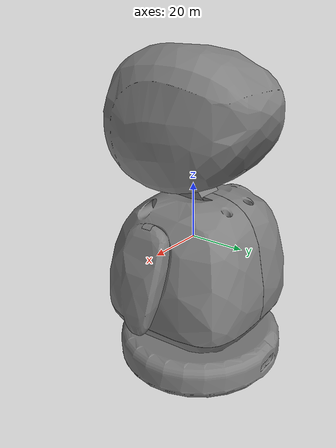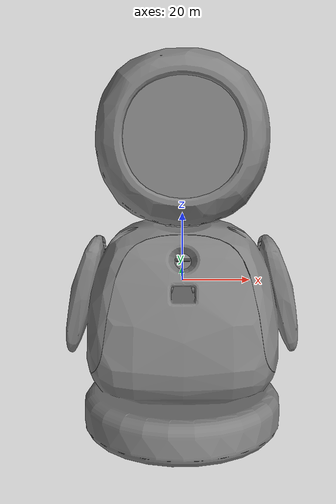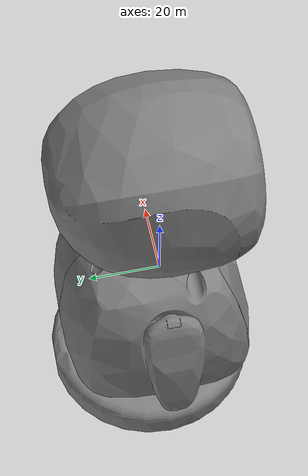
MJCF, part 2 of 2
-1.537889 39.813980 -21.284849 -1.537889 39.813980 -20.953720 -1.478383 39.626411 -21.280210 -1.463492 39.599899 -20.942780 -1.371429 39.517288 -21.273861 -1.363820 39.513680 -21.260950 -1.168480 39.464779 -20.927231 -1.168480 39.464779 -21.246571 -0.960692 39.500240 -20.914370 -0.964692 39.498920 -21.233210 -0.775984 39.591759 -20.904100 -0.775984 39.591759 -21.219549 -0.594166 39.343559 -20.880690 -0.594166 39.343559 -20.886440 -0.719946 39.254509 -21.229059 -0.719954 39.254509 -20.894039 -0.862564 39.189159 -21.239540 -0.862564 39.189159 -20.903990 -1.030094 39.146332 -21.251440 -1.030031 39.146339 -20.915390 -1.205998 39.132889 -21.263479 -1.205998 39.132889 -20.931480 -1.435615 39.156609 -21.278410 -1.434912 39.156441 -20.947861 -1.641785 39.235340 -21.291189 -1.641785 39.235340 -21.229771 -0.729580 40.556431 -21.240360 -0.874108 40.672569 -21.253201 -1.055437 40.744251 -21.216669 -0.556771 40.199032 -21.221861 -0.624469 40.401279 -21.266741 -1.255060 40.766361 -21.279840 -1.457701 40.743252 -21.273979 -1.365878 40.438190 -21.292139 -1.657658 40.658138 -21.279619 -1.454195 40.369541 -21.300920 -1.807117 40.529491 -21.283621 -1.518040 40.242882 -21.307020 -1.914512 40.363770 -21.310720 -1.981421 40.162281 -21.311880 -2.002535 39.946739 -21.311069 -1.987518 39.798962 -21.306860 -1.911626 39.521049 -21.300461 -1.799012 39.358299 -20.968630 -1.365810 40.438221 -20.973049 -1.454195 40.369541 -20.962370 -1.797104 39.356300 -20.975670 -1.911626 39.521049 -20.974409 -1.518104 40.242680 -20.914961 -0.624469 40.401279 -20.905399 -0.556723 40.198792 -20.938200 -0.874108 40.672569 -20.925671 -0.729083 40.555889 -20.966209 -1.255060 40.766361 -20.952190 -1.055557 40.744282 -20.990690 -1.657658 40.658138 -20.979780 -1.466042 40.741100 -21.000820 -1.914512 40.363770 -20.997681 -1.807175 40.529411 -21.000111 -1.981764 40.157558 -20.995371 -2.002535 39.946739 -20.987089 -1.981173 39.725342 -10.666830 23.652451 49.746552 -9.948295 24.445221 48.612728 -9.844769 24.268120 49.048458 -17.721939 14.632390 44.177620 -17.543760 15.099920 44.177620 -17.947861 14.011900 44.177620 -10.916910 23.267481 38.232151 -9.889297 24.104740 39.698940 -10.030520 24.418150 40.833752 -17.851959 14.309150 42.936642 -18.262939 13.092510 44.123039 -18.231260 13.193710 44.015999 -18.115480 13.529930 44.177620 -18.289660 13.007830 44.180939 -18.200279 13.297300 43.764309 -18.192720 13.325870 43.593048 -18.475000 12.375530 44.835629 -18.320299 12.911870 44.211750 -17.927290 14.103790 42.518570 -17.902000 14.173510 42.645149 -17.959129 14.014780 42.645149 -18.366280 12.768030 44.229568 -17.962870 14.004680 42.422932 -18.402349 12.655720 44.215832 -18.199261 13.316860 43.196812 -18.191839 13.333690 43.415710 -18.436510 12.550140 44.174728 -18.016090 13.854870 42.358669 -18.467760 12.454500 44.108410 -18.219110 13.261540 42.991470 -18.077410 13.680010 42.324799 -18.493940 12.375530 44.021770 -18.248249 13.176650 42.831902 -18.290480 13.050860 42.701431 -18.524191 12.323580 42.645149 -18.467079 12.505400 42.645149 -18.495371 12.414990 42.704498 -18.518240 12.340900 42.783680 -18.378731 12.773800 41.443130 -18.341841 12.895210 42.621319 -18.359680 12.830390 41.359760 -18.058710 13.731950 42.001572 -18.407560 12.685790 41.499161 -18.399050 12.718970 42.596088 -18.352800 12.848840 41.259869 -18.441460 12.580440 41.516720 -18.434320 12.608820 42.608131 -18.475000 12.474560 41.499088 -18.502670 12.385630 41.443130 -18.648161 11.919540 42.645149 -18.344299 12.854610 40.714409 -18.375340 12.773800 41.075169 -18.403231 12.685620 41.020168 -18.357750 12.830640 41.158791 -18.520121 12.328030 41.359940 -18.436781 12.580440 41.003010 -18.185511 13.247100 39.493641 -17.862930 14.280290 42.179062 -17.944740 14.053860 42.060780 -18.000370 13.897680 42.021179 -17.821501 14.393480 42.291611 -18.174730 13.247100 39.181950 -18.620260 11.980150 40.714409 -18.499380 12.385630 41.076611 -18.518320 12.328050 41.159740 -18.525181 12.309150 41.259869 -18.316050 12.854610 39.493641 -19.364611 9.170833 44.194012 -19.329950 9.327912 44.085270 -19.305771 9.327912 44.835629 -19.408239 8.981591 44.229568 -18.759230 11.515500 40.714409 -18.615040 11.980150 40.402729 -19.448799 8.810257 44.204189 -19.240299 9.783901 42.645149 -18.614491 11.919540 44.786560 -19.196310 9.783901 44.786560 -19.485929 8.658359 44.125671 -18.890680 11.059510 40.714409 -18.596809 11.965720 39.493641 -18.485340 12.398620 40.402729 -18.462589 12.398620 39.493641 -19.365480 9.277849 42.723900 -19.341181 9.379860 42.645149 -19.345421 9.356773 42.812538 -19.389589 9.180726 42.655251 -19.650360 7.928040 44.020061 -19.518270 8.531767 43.996281 -19.631990 8.033540 43.864491 -19.542021 8.444796 43.837070 -19.677490 7.783900 44.135769 -18.720989 11.515500 39.181950 -18.586241 11.965720 39.181950 -19.622311 8.101248 43.662182 -19.559719 8.387375 43.633110 -19.713150 7.602443 44.207481 -19.622660 8.121563 43.441689 -19.568171 8.369759 43.415710 -19.627689 8.112905 43.277191 -19.565689 8.406638 43.070869 -19.569460 8.378074 43.240330 -18.869989 11.008090 39.263069 -18.836170 11.117230 39.181950 -18.848150 11.097030 39.360882 -18.984030 10.643930 39.666801 -19.006371 10.643930 40.714409 -18.867439 11.059510 39.637939 -18.897110 10.941190 39.515282 -18.935160 10.799770 39.470551 -18.968830 10.682890 39.515282 -18.899220 10.895010 39.192051 -19.645361 8.063843 42.806770 -19.544889 8.512616 42.815418 -19.522840 8.613767 42.705410 -19.681570 7.882025 43.054958 -19.236130 9.760944 40.488571 -19.128929 10.187940 40.714409 -19.260700 9.674233 40.646591 -18.933969 10.764200 39.147629 -19.226959 9.783901 40.307491 -19.455099 8.912328 41.369541 -19.449381 8.932530 42.596088 -19.482170 8.792491 42.615028 -19.418470 9.062022 42.610081 -19.340290 9.362545 40.766361 -19.297060 9.535041 40.738991 -19.104959 10.187940 39.609081 -19.373920 9.224333 40.746681 -19.405090 9.093229 40.701260 -19.805759 7.296679 42.975761 -19.766621 7.489529 42.927979 -19.836260 7.120121 43.277191 -19.827971 7.178246 43.092388 -19.338680 9.327912 40.180500 -19.350330 9.296167 40.373871 -19.379520 9.180727 40.428699 -19.561041 8.456340 41.323360 -19.503660 8.699077 42.645802 -19.673790 7.938153 42.717758 -19.446289 8.912328 40.561459 -19.411091 9.046527 40.381081 -19.987930 6.209587 44.108349 -19.870991 6.851071 43.992889 -19.837629 7.000351 44.121342 -19.977329 6.295915 43.954651 -19.896870 6.743497 43.826969 -20.009661 6.070863 44.201530 -19.797060 7.190936 44.204029 -19.195810 9.783901 39.181950 -19.064190 10.299050 39.258430 -19.093069 10.211150 39.422901 -19.021740 10.444500 39.161049 -19.978470 6.320698 43.770691 -19.924730 6.655474 43.409939 -19.915359 6.676586 43.625469 -19.440451 8.912328 40.241112 -19.925430 6.671146 43.240990 -19.705280 7.795445 42.652370 -19.741360 7.628059 42.609558 -19.778450 7.452011 42.596088 -20.065109 5.864710 43.637939 -20.064711 5.832964 43.837070 -20.083191 5.717523 43.891899 -20.128719 5.391405 44.177620 -20.086399 5.641044 44.173290 -20.063181 5.765477 44.216129 -20.108971 5.525775 44.099258 -20.107941 5.583324 43.847172 -19.824039 7.229854 42.618099 -20.129980 5.423151 44.001572 -20.001881 6.320698 42.645149 -19.915541 6.746383 42.984261 -19.866320 7.016224 42.698540 -19.895781 6.859925 42.820530 -19.410500 8.912328 39.181950 -19.310061 9.327912 39.181950 -20.135120 5.449125 43.715858 -20.242001 4.623728 44.422932 -20.039160 5.899342 44.229568 -20.194300 4.993137 44.177620 -20.240141 4.727623 44.088150 -19.516741 8.456340 39.181950 -20.158970 5.449125 42.645149 -20.085711 5.864710 42.645149 -20.277439 4.566323 43.759129 -20.271330 4.538769 44.042141 -20.282339 4.509730 43.868820 -20.294161 4.410551 43.959358 -20.278980 4.583324 43.632160 -20.327021 4.115267 44.234989 -20.298771 4.294723 44.271412 -20.358101 3.902227 44.226681 -20.020599 6.211029 40.646591 -20.291950 4.638158 42.740391 -20.235970 4.993137 42.645149 -20.286341 4.563383 43.493401 -20.299379 4.502516 43.368092 -20.002081 6.296528 40.492401 -20.304560 4.548064 42.832760 -20.285030 4.692409 42.632450 -20.047831 6.071830 40.738998 -20.321220 4.433252 42.899120 -20.317680 4.402528 43.261742 -20.283859 4.710308 42.512390 -19.994141 6.320698 40.307491 -20.165131 5.449125 41.369541 -20.079861 5.899342 40.766361 -20.343040 4.285622 42.943329 -20.339199 4.274521 43.184830 -20.289770 4.684578 42.364712 -20.104919 5.759484 40.746342 -20.366711 4.127335 42.956841 -20.365170 4.110446 43.133980 -20.391661 3.933973 43.118462 -20.127670 5.628759 40.700581 -20.404270 3.873367 42.956841 -20.417170 3.755041 43.135769 -20.076139 5.864710 40.180500 -20.085779 5.832964 40.373871 -20.107571 5.717523 40.428699 -20.517780 2.384189 44.906330 -20.384760 3.718807 44.210678 -20.516430 2.440779 44.822960 -20.410860 3.547249 44.158859 -20.433010 3.410888 44.077999 -20.242630 4.993137 41.323360 -20.297890 4.639864 42.270611 -20.321060 4.501073 42.138660 -20.524281 2.296182 44.962360 -20.423149 3.739167 42.981369 -20.423241 3.718966 43.099701 -20.426319 3.705979 43.049191 -20.520330 2.459225 44.723068 -20.452129 3.304824 43.964050 -20.368601 4.180726 42.350780 -20.355310 4.257205 42.480652 -20.362289 4.200928 42.591759 -20.157240 5.449125 40.561459 -20.130581 5.583324 40.381081 -20.535070 2.190827 44.979931 -20.528400 2.441028 44.621979 -20.388330 4.052903 42.312340 -20.386610 4.034983 42.633610 -20.548050 2.084946 44.962292 -19.962021 6.320698 39.181950 -20.472980 3.363987 43.099701 -20.452240 3.489528 43.228119 -20.466351 3.370724 43.308140 -20.475330 3.281736 43.411381 -20.151409 5.449125 40.241112 -20.410830 3.902227 42.304600 -20.422279 3.792559 42.633610 -20.561541 1.996022 44.906330 -20.549080 2.464997 44.177620 -20.539829 2.384189 44.538368 -20.553181 2.296008 44.483372 -20.475241 3.218244 43.666801 -20.466570 3.239080 43.823509 -20.425480 3.802606 42.306160 -20.483049 3.319254 42.936642 -20.566240 2.190827 44.466221 -20.442560 3.682891 42.324799 -20.449480 3.601092 42.650829 -20.458771 3.553020 42.497959 -20.471251 3.437580 42.718739 -20.456450 3.580438 42.385410 -20.308371 4.557350 40.714409 -20.360991 4.249063 42.039360 -20.387739 4.074422 42.011509 -20.544060 2.857494 42.956841 -20.477970 3.232957 43.532429 -20.514620 3.148980 42.497959 -20.481510 3.349924 42.813751 -20.120211 5.449125 39.181950 -20.046419 5.864710 39.181950 -20.550730 2.857494 42.645149 -20.509390 3.213915 42.229568 -20.514690 3.163662 42.356220 -20.647711 1.590539 44.177620 -20.581551 1.919543 44.723068 -20.573210 1.938414 44.823132 -20.584049 1.996022 44.539810 -20.585541 1.938408 44.623032 -20.593620 2.464997 42.956841 -20.703291 1.114348 44.041981 -20.662680 1.590539 43.865929 -20.714310 0.953480 44.132179 -20.273211 4.528489 39.181950 -20.197769 4.993137 39.181950 -20.278851 4.571779 39.528271 -20.491720 3.330798 40.714409 -20.415211 3.890683 42.004459 -20.449480 3.655086 42.016479 -20.479420 3.441910 42.063622 -20.726761 0.786207 44.195110 -20.696810 1.576108 42.956841 -20.616590 2.009009 43.865929 -20.648121 2.009009 42.956841 -20.554079 2.892126 40.959721 -20.497190 3.310213 42.129559 -20.751360 0.493857 44.229568 -20.736469 1.082602 43.340679 -20.740450 1.011732 43.424782 -20.733810 0.932530 43.773579 -20.735790 1.127407 43.229401 -20.747080 0.919543 43.487862 -20.536289 2.996021 40.624950 -20.486231 3.330798 40.370979 -20.764919 0.343655 44.221191 -20.738510 1.140322 43.104031 -20.745319 1.116387 42.955620 -20.704309 1.576108 42.645149 -20.768650 0.649702 43.588871 -20.748810 0.728141 43.868870 -20.767229 0.508287 43.903450 -20.595261 2.563121 40.808208 -20.756300 1.042198 42.826969 -20.786400 0.420264 43.661018 -20.783319 0.342342 43.874592 -20.561529 2.778128 40.405609 -20.562910 2.789664 40.576321 -20.551991 2.834720 40.295921 -20.576010 2.678948 40.496159 -20.793030 0.316368 43.717300 -20.792259 0.288951 43.785118 -20.547041 2.851722 40.168961 -20.618650 2.373577 40.770500 -20.770670 0.924304 42.723839 -20.546360 2.831792 40.030231 -20.472080 3.267306 39.505180 -20.795811 0.599196 42.958279 -20.786039 0.639600 43.150200 -20.793470 0.537148 43.212250 -20.786150 0.667018 43.066509 -20.643459 2.170625 40.763481 -20.551050 2.770914 39.904888 -20.662621 2.010997 40.754921 -20.814039 0.413049 42.922211 -20.811930 0.303381 43.285839 -20.825809 0.276740 42.938229 -20.527821 2.816463 39.369560 -20.512449 2.906556 39.277191 -20.500940 2.960803 39.169258 -20.459980 3.267306 39.181950 -20.684570 1.815647 40.695660 -20.835970 0.148309 42.974659 -20.826019 0.111824 43.352482 -20.545170 2.701650 39.435921 -20.560989 2.670938 39.798550 -20.493490 2.978706 39.049191 -20.848240 -0.037167 43.083820 -20.835381 -0.048711 43.454670 -20.561600 2.585651 39.476601 -20.575029 2.542919 39.721630 -20.859791 -0.729076 44.019089 -20.818680 -0.125510 43.946079 -20.800159 0.004680 44.096809 -20.860710 -0.624469 43.864491 -20.831860 -0.169923 43.753380 -20.490280 2.952914 38.901291 -20.699039 1.679285 40.614799 -20.863010 -0.874108 44.135769 -20.778660 0.201101 44.192162 -20.865810 -0.556750 43.662128 -20.585939 2.395733 39.493641 -20.593990 2.378853 39.670780 -20.491751 2.907994 38.807041 -20.870649 -1.057239 44.207890 -20.874180 -0.536446 43.441689 -20.837219 -0.141522 43.588020 -20.615129 2.202371 39.655251 -20.881500 -0.545104 43.277191 -20.881620 -1.255060 44.229568 -20.503269 2.769471 38.675449 -20.874889 -0.265161 42.826969 -20.616961 2.141765 39.493641 -20.637131 2.023439 39.672569 -20.633801 2.007565 39.518169 -20.640209 1.987364 39.636490 -20.640051 1.974377 39.585991 -20.554319 2.449124 38.887569 -20.562599 2.469326 39.128559 -20.584881 2.303381 39.170399 -20.550720 2.525603 39.017441 -20.771311 1.014781 40.645149 -20.709169 1.573222 40.500851 -20.568239 2.321310 38.849140 -20.759970 1.101108 40.491451 -20.713930 1.507478 40.360310 -20.901110 -0.594166 42.806770 -20.866011 -0.119580 42.721401 -20.906610 -0.775984 43.054958 -20.786680 0.875963 40.738361 -20.786530 0.779571 42.653809 -20.681030 1.632385 39.636490 -20.670910 1.757926 39.764919 -20.686760 1.639121 39.844929 -20.699610 1.550134 39.948181 -20.753929 1.125892 40.307491 -20.712959 1.486642 40.203590 -20.708170 1.501355 40.069229 -20.586109 2.170625 38.841400 -20.614080 2.060957 39.170399 -20.804060 0.704535 40.766361 -20.803730 0.610708 42.612530 -20.912979 -0.719881 42.717751 -20.680349 1.587653 39.473431 -20.816879 0.570671 40.752930 -20.822180 0.415935 42.596088 -20.613001 1.951289 38.861599 -20.637211 1.869444 39.187641 -20.636089 1.821418 39.034760 -20.658680 1.705978 39.255539 -20.627741 1.848836 38.922211 -20.828171 0.446238 40.710091 -20.797091 0.669904 40.174728 -20.804420 0.638158 40.373871 -20.816540 0.522717 40.428699 -20.948740 -1.360088 42.975201 -20.937981 -1.168480 42.927979 -20.948139 -1.537889 43.277191 -20.952000 -1.474648 43.082378 -20.851210 0.196599 40.714409 -20.838921 0.228272 42.608700 -20.838051 0.329588 40.634602 -20.937000 -2.338415 44.243629 -20.927420 -1.807967 43.991711 -20.911539 -1.657658 44.121342 -20.681080 1.417378 39.034760 -20.672310 1.618320 39.350552 -20.929850 -2.484498 44.433029 -20.895700 -1.466661 44.204140 -20.943649 -2.262401 44.089569 -20.942400 -1.914512 43.826969 -20.828341 0.388518 40.383968 -20.845779 0.228345 40.538368 -20.929220 -2.670948 44.537670 -20.952660 -2.224061 43.912628 -20.952520 -1.965210 43.687832 -20.718470 1.125892 39.181950 -20.661060 1.482313 38.766361 -20.672819 1.432060 38.893021 -20.930519 -2.866659 44.609409 -20.837990 0.254319 40.252651 -20.966299 -2.210327 43.655251 -20.968081 -2.002535 43.409939 -20.959169 -1.989246 43.581451 -20.885860 -0.201669 40.714409 -20.854990 0.029211 42.656689 -20.938080 -3.211770 44.645149 -20.764151 0.669904 39.181950 -20.645309 1.578609 38.666359 -20.992710 -2.296747 43.179699 -20.980700 -1.911626 42.984261 -20.976509 -1.982786 43.196579 -21.003380 -2.373331 43.000801 -20.802931 0.254319 39.181950 -21.009830 -2.440464 42.909771 -20.980000 -1.798210 42.820671 -20.925091 -0.862564 42.652370 -20.949730 -3.716821 44.645149 -21.015980 -2.521848 42.839191 -20.937590 -1.024588 42.611561 -20.950199 -1.205998 42.596088 -20.963869 -1.427014 42.617840 -20.974701 -1.641785 42.698540 -20.842360 -0.201669 39.181950 -21.030109 -2.314137 40.900719 -21.026140 -2.254629 40.804729 -21.036449 -2.423891 41.018890 -21.023121 -2.222037 40.693741 -21.044300 -2.580140 41.098709 -21.024099 -2.653015 42.768230 -21.019760 -2.204555 40.529709 -21.052231 -2.751891 41.156059 -21.033001 -2.823893 42.712280 -21.017469 -2.220751 40.361511 -21.016590 -2.251836 40.246941 -21.017090 -2.309593 40.145950 -21.064899 -3.058812 41.181950 -21.048340 -3.177138 42.645149 -21.019051 -2.416676 40.020329 -21.026461 -2.653995 39.896111 -21.085951 -3.687961 41.181950 -21.064640 -3.716821 42.645149 -21.020170 -3.214656 39.181950 -21.032551 -2.820522 39.859951 -21.039301 -2.995320 39.848610 -21.047520 -3.214656 39.848610 -15.247550 -11.358390 25.767370 -19.723450 7.692577 42.961880 -20.593060 2.554463 40.564339 -20.395969 3.806989 39.528271 -20.303310 4.557350 40.394070 -20.384840 4.029211 40.370979 -20.923180 -0.966060 42.961681 -20.577280 2.084905 44.483871 -20.310301 4.286065 44.027550 -18.470680 12.474560 41.020649 -12.295080 22.264780 50.692841 -9.970045 24.576220 48.210720 -12.990370 22.453730 48.737019 -9.994223 24.692200 47.651661 -14.325730 20.715010 49.391579 -13.179920 22.506020 46.713120 -10.031220 24.795549 45.169720 -14.585130 20.753309 46.786308 -13.221600 22.505131 44.241291 -10.062000 24.649290 42.132580 -14.641170 20.746140 43.706348 -17.748831 14.589100 42.645149 -18.375919 10.385670 51.043839 -19.753410 7.402948 44.229568 -12.740040 22.143480 37.640388 -11.946160 21.979349 36.374241 -18.953751 10.333610 46.768162 -13.936620 20.362410 35.653259 -13.650400 18.683710 32.575111 -19.109341 10.299500 42.035889 -17.312330 10.218860 29.671921 -15.685200 10.042660 27.257170 -14.871250 14.654200 29.457550 -16.124161 5.037714 25.873949 -18.971260 10.626610 39.132889 -19.696400 -8.210641 50.224739 -20.696840 -8.323225 45.833179 -21.026320 -8.372936 41.171761 -21.034800 -3.687961 39.181950 -18.028120 -8.135516 28.402550 -15.844920 -6.749562 25.220440 -16.264469 17.242790 36.029930 -17.787319 14.486080 42.415321 -19.706690 4.313043 33.513550 -19.789280 3.349115 33.272240 -20.530519 2.513699 38.575180 -20.550631 2.338978 38.548012 -19.059610 5.076597 31.258600 -19.139750 3.978154 30.996651 -19.148500 3.765330 30.934999 -19.142059 3.851748 30.950251 -19.970079 1.468162 33.161999 -20.571970 2.159081 38.541248 -20.600290 1.923403 38.553291 -20.016470 1.067474 33.215069 -19.982809 1.330581 33.163620 -19.999571 1.181886 33.181320 -20.627119 1.710308 38.600422 -20.120630 0.155372 33.377800 -20.208691 -0.767685 33.528191 -20.216740 -0.902678 33.532719 -19.359989 1.133361 30.761221 -19.365561 1.044571 30.758181 -20.252020 -1.575541 33.554691 -19.401970 0.757522 30.807831 -19.375401 0.928177 30.762650 -19.388880 0.822796 30.781370 -18.447359 2.478064 28.726780 -16.211349 -0.115227 25.205490 -19.537621 -0.536382 31.005119 -19.539749 -0.623838 31.000151 -19.547791 -0.738319 31.010651 -19.581671 -1.629898 31.029791 -19.207951 -3.880449 30.029350 -17.873819 15.099920 44.177620 -18.051861 14.632390 44.177620 -18.068060 14.589100 42.645149 -18.090509 14.528650 42.497581 -18.119141 14.451060 42.361671 -18.181570 14.280290 42.179062 -18.232071 14.140340 42.099251 -18.284050 13.994680 42.041790 -18.376240 13.731950 42.001572 -18.394220 13.680010 42.324799 -18.333340 13.854870 42.358669 -18.280479 14.004680 42.422932 -18.171061 14.309150 42.936642 -18.277861 14.011900 44.177620 -18.445730 13.529930 44.177620 -18.220140 14.173510 42.645149 -18.276890 14.014780 42.645149 -18.245220 14.103630 42.518341 -20.041500 7.677119 43.554241 -19.831301 7.114348 43.554241 -20.158010 7.114348 43.554241 -19.715750 7.677119 43.554241 -19.716169 7.653460 43.741810 -20.048790 7.642692 43.772629 -19.731159 7.566155 43.862888 -20.064550 7.567947 43.861771 -19.763069 7.402948 43.923649 -20.098980 7.402948 43.923649 -19.945360 8.121563 43.441689 -19.947269 8.112905 43.277191 -20.156851 7.120121 43.277191 -20.140869 7.198961 43.056271 -20.120590 7.298243 42.975060 -20.080990 7.489529 42.927979 -20.037411 7.696413 42.963139 -19.997641 7.882025 43.054958 -19.958071 8.063843 42.806770 -19.985519 7.938058 42.717709 -20.016279 7.795445 42.652370 -20.051920 7.628017 42.609550 -20.088820 7.452011 42.596088 -20.135960 7.223141 42.619629 -20.177759 7.016224 42.698540 -20.018721 7.783900 44.135769 -20.057261 7.602561 44.207451 -19.964689 8.033540 43.864491 -19.987700 7.927885 44.020229 -20.098970 7.402948 44.229568 -19.949829 8.101233 43.662251 -20.121830 7.292107 43.901379 -20.142250 7.192079 44.204342 -20.180910 7.000351 44.121342 -20.139870 7.203814 43.832741 -20.210529 6.851148 43.992981 -20.152830 7.139976 43.706108 -20.231661 6.743497 43.826969 -20.245991 6.670003 43.553291 -20.248791 6.655474 43.409939 -20.246040 6.669765 43.263950 -20.231119 6.746383 42.984261 -20.208811 6.859982 42.820469 -19.786289 7.292081 43.901371 -19.806070 7.203814 43.832741 -19.822359 7.139906 43.705879 -20.953440 -1.169135 40.337101 -20.950670 -1.168972 40.211220 -20.965940 -1.356731 40.331478 -20.963140 -1.356562 40.205711 -21.356710 -2.958076 43.022812 -21.035040 -3.142506 42.988590 -21.363689 -3.142506 42.988590 -21.027349 -2.962928 43.020729 -21.350800 -2.812059 43.137211 -21.016840 -2.812059 43.137211 -21.348181 -2.750087 43.271790 -21.005110 -2.729964 43.329269 -21.346540 -2.711865 43.408230 -20.996469 -2.702672 43.486259 -21.345940 -2.698062 43.655251 -20.987499 -2.698062 43.655251 -21.346081 -2.701103 43.808620 -20.973841 -2.712006 43.904270 -21.347040 -2.723407 43.956200 -20.966949 -2.752849 44.040310 -21.350861 -2.813502 44.164631 -20.961050 -2.813502 44.164631 -21.357620 -2.981347 44.629219 -21.366171 -3.211770 44.645149 -21.348970 -2.768644 44.580151 -21.336290 -2.484498 44.433029 -21.329189 -2.336795 44.240662 -21.326450 -2.281602 44.138882 -21.324650 -2.245678 44.032928 -21.322849 -2.210327 43.655251 -21.325890 -2.270174 43.279480 -21.328560 -2.323881 43.102470 -21.332050 -2.395132 42.966671 -21.335279 -2.462917 42.887039 -21.339279 -2.548795 42.821430 -21.347750 -2.739800 42.736370 -21.364941 -3.177138 42.645149 -21.356750 -2.959141 44.269878 -21.363689 -3.142506 44.301720 -21.367279 -3.243516 44.301720 -21.381901 -3.716821 44.645149 -21.367279 -3.243516 42.988590 -21.381910 -3.716821 42.645149 -20.958851 -2.960816 44.270569 -20.962351 -3.142506 44.301720 -21.038420 -3.243516 42.988590 -20.965281 -3.243516 44.301720 -19.748329 7.491503 43.800289 -19.751860 7.490603 43.671581 -19.787060 7.303843 43.789230 -19.790630 7.302937 43.660332 -21.174471 -0.037167 43.083820 -21.193489 -0.265161 42.826969 -21.164339 0.080481 43.008652 -21.154051 0.197344 42.956680 -21.134520 0.413049 42.922211 -21.117090 0.599196 42.958279 -21.110600 0.667018 43.066509 -21.113230 0.639600 43.150200 -21.122950 0.537148 43.212250 -21.144541 0.303381 43.285839 -21.161591 0.111816 43.352482 -21.175440 -0.048711 43.454670 -21.183270 -0.141521 43.588009 -21.185640 -0.169923 43.753380 -21.181860 -0.124739 43.947590 -21.170879 0.004680 44.096809 -21.159060 0.140757 44.168381 -21.147770 0.267453 44.209782 -21.127010 0.493857 44.229568 -21.108879 0.684765 44.213821 -21.091511 0.862309 44.171902 -21.066010 1.114348 44.041981 -21.084511 0.932530 43.773579 -21.104361 0.731417 43.867840 -21.125660 0.508287 43.903450 -21.141001 0.342342 43.874592 -21.145840 0.288951 43.785118 -21.064671 1.127373 43.229542 -21.069281 1.082602 43.340679 -21.076550 1.011401 43.425091 -21.085810 0.919543 43.487862 -21.112261 0.649702 43.588871 -21.073420 1.042198 42.826969 -21.065809 1.116362 42.955551 -21.063339 1.140322 43.104031 -21.085329 0.924415 42.723911 -21.133850 0.420264 43.661018 -21.143360 0.316368 43.717300 -21.099680 0.779571 42.653809 -21.116791 0.602298 42.609852 -21.134260 0.415935 42.596088 -21.152250 0.217593 42.610420 -21.168779 0.029211 42.656689 -21.182119 -0.127682 42.727650 -18.943840 11.980150 40.402729 -18.943830 11.980150 40.714409 -18.670410 12.854610 40.714409 -18.670450 12.854610 39.493641 -18.541420 13.247100 39.493641 -18.541430 13.247100 39.181950 -18.815359 12.398620 40.402729 -18.815390 12.398620 39.493641 -18.948231 11.965720 39.181950 -18.948219 11.965720 39.493641 -20.469879 5.449125 41.369541 -20.546970 4.993137 41.323360 -20.469900 5.449125 40.561459 -20.450260 5.562065 40.657478 -20.434540 5.651639 40.712090 -20.416759 5.751978 40.744732 -20.390329 5.899342 40.766361 -20.358940 6.071764 40.739021 -20.333220 6.211029 40.646591 -20.317261 6.296522 40.492420 -20.312731 6.320698 40.307491 -20.312750 6.320698 39.181950 -20.396601 5.864710 39.181950 -20.402290 5.832964 40.373871 -20.422890 5.717523 40.428699 -20.396589 5.864710 40.180500 -20.446550 5.583324 40.381081 -20.469900 5.449125 40.241112 -20.547010 4.993137 39.181950 -20.469919 5.449125 39.181950 -19.326580 10.643930 40.714409 -19.448111 10.187940 40.714409 -19.326611 10.643930 39.666801 -19.316019 10.682890 39.515282 -19.284050 10.799770 39.470551 -19.244961 10.941190 39.515282 -19.211910 11.059510 39.637939 -19.211880 11.059510 40.714409 -19.081570 11.515500 40.714409 -19.081610 11.515500 39.181950 -19.201370 11.097030 39.360882 -19.195690 11.117230 39.181950 -19.226370 11.007920 39.262920 -19.257780 10.895010 39.192051 -19.293800 10.764270 39.147640 -19.448139 10.187940 39.609081 -19.331320 10.626610 39.132889 -19.441690 10.212600 39.418190 -19.380310 10.444560 39.161030 -19.418949 10.299050 39.258430 -20.920160 2.403063 40.105671 -20.606779 2.355329 40.014561 -20.926029 2.355329 40.014561 -20.603100 2.403066 40.105679 -20.918570 2.415935 40.215141 -20.603991 2.415935 40.215141 -20.614719 2.359817 40.401020 -20.925480 2.359787 40.401051 -20.637680 2.182169 40.466221 -20.947020 2.182169 40.466221 -20.657009 2.010452 40.396950 -20.967360 2.010452 40.396950 -20.857950 2.892126 40.959721 -20.900209 2.563121 40.808208 -20.844250 2.996021 40.624950 -20.871510 2.788034 40.576099 -20.901310 2.554463 40.564339 -20.885540 2.678939 40.496170 -20.872789 2.778128 40.405609 -20.865450 2.834739 40.295860 -20.863239 2.851722 40.168961 -20.865841 2.831783 40.030201 -20.873730 2.770914 39.904888 -20.886570 2.670933 39.798538 -20.902769 2.542919 39.721630 -20.923170 2.378721 39.670750 -20.944599 2.202371 39.655251 -20.965851 2.023439 39.672569 -20.970070 1.987364 39.636490 -20.971590 1.974377 39.585991 -20.967710 2.007565 39.518169 -20.951860 2.141765 39.493641 -20.921070 2.395733 39.493641 -20.901381 2.553950 39.480141 -20.882650 2.701650 39.435921 -20.867840 2.816447 39.369572 -20.856079 2.906556 39.277191 -20.848930 2.960810 39.169231 -20.846569 2.978706 39.049191 -20.850060 2.952287 38.899170 -20.856251 2.905288 38.803341 -20.873930 2.769471 38.675449 -20.893669 2.615201 38.608250 -20.914190 2.451541 38.561741 -20.949800 2.159081 38.541248 -20.977520 1.923403 38.553291 -21.001841 1.710308 38.600422 -20.923790 2.373565 40.770500 -20.948389 2.170625 40.763481 -20.970079 1.987152 40.747471 -20.989880 1.815647 40.695660 -21.005310 1.679185 40.614719 -21.017080 1.573222 40.500851 -20.974600 1.948403 40.209358 -20.947020 2.182169 39.946739 -21.024300 1.507520 40.360451 -20.967199 2.011895 40.015999 -21.026581 1.486642 40.203590 -20.911970 2.469326 39.128559 -21.024969 1.501388 40.069092 -20.972960 1.962576 40.103901 -20.904949 2.525603 39.017441 -20.996450 1.757926 39.764919 -21.019630 1.550134 39.948181 -21.009769 1.639256 39.844810 -20.932390 2.303381 39.170399 -20.914480 2.449124 38.887569 -21.010540 1.632385 39.636490 -20.961439 2.060957 39.170399 -21.015499 1.587653 39.473431 -20.983740 1.869463 39.187630 -20.930210 2.321306 38.849129 -21.012100 1.618322 39.350540 -21.002319 1.705978 39.255539 -20.948420 2.170625 38.841400 -20.974279 1.951289 38.861599 -21.032511 1.432110 38.892799 -20.986111 1.848836 38.922211 -20.989241 1.821418 39.034760 -21.034100 1.417378 39.034760 -21.027060 1.482313 38.766361 -21.016520 1.578505 38.666431 -20.660521 1.948403 40.209358 -20.626209 2.182169 39.946739 -20.648411 2.011895 40.015999 -20.656429 1.962542 40.104000 -20.981501 -2.880357 43.880772 -20.988331 -3.064625 43.872330 -21.005770 -2.884701 43.440441 -21.012751 -3.068978 43.432510 -20.975710 1.938419 44.823139 -20.977900 1.919543 44.723068 -20.969000 1.996022 44.906330 -20.958540 2.084969 44.962299 -20.945921 2.190827 44.979931 -20.933201 2.296179 44.962360 -20.922430 2.384189 44.906330 -20.915461 2.440671 44.823238 -20.913160 2.459225 44.723068 -20.922430 2.384189 44.538368 -20.915421 2.441022 44.621971 -20.933229 2.295922 44.483349 -20.945930 2.190827 44.466221 -20.958570 2.084749 44.483929 -20.969000 1.996022 44.539810 -20.975700 1.938558 44.622662 -18.837311 12.328030 41.359928 -18.843161 12.309150 41.259869 -18.819380 12.385630 41.443130 -18.791550 12.474580 41.499100 -18.758160 12.580440 41.516720 -18.724670 12.685770 41.499168 -18.696461 12.773800 41.443130 -18.678230 12.830380 41.359772 -18.672270 12.848840 41.259869 -18.696470 12.773800 41.075169 -18.678150 12.830650 41.158798 -18.724760 12.685540 41.020142 -18.758181 12.580440 41.003010 -18.791611 12.474430 41.020699 -18.819389 12.385630 41.076611 -18.837311 12.328030 41.159801 -20.617411 4.557350 40.394070 -20.617411 4.557350 40.714409 -20.731371 3.806989 39.528271 -20.615141 4.571779 39.528271 -20.621981 4.528489 39.181950 -20.807680 3.267306 39.181950 -20.698570 4.029211 40.370979 -20.798920 3.330798 40.714409 -20.798929 3.330798 40.370979 -20.807671 3.267306 39.505180 -18.505751 12.375530 43.066509 -18.498890 12.375530 43.712971 -18.822460 12.375530 43.712971 -18.822479 12.375530 43.066509 -18.792311 12.471990 42.965321 -18.476139 12.472030 42.965290 -18.751720 12.600640 42.927979 -18.435619 12.600640 42.927979 -18.695850 12.775560 43.025902 -18.380800 12.769920 43.020988 -18.671021 12.852510 43.170231 -18.356430 12.842940 43.133389 -18.349340 12.862220 43.242950 -18.667530 12.863270 43.409939 -18.347490 12.863270 43.409939 -18.822430 12.375530 44.835629 -18.961960 11.919540 44.786560 -18.822451 12.375530 44.021770 -18.797750 12.454570 44.108471 -18.767670 12.550140 44.174728 -18.734171 12.655710 44.215832 -18.698231 12.768030 44.229568 -18.651640 12.912130 44.211700 -18.620260 13.008290 44.180710 -18.592510 13.092690 44.122711 -18.559059 13.193710 44.015999 -18.534769 13.266270 43.856030 -18.519381 13.312500 43.696972 -18.512270 13.333690 43.415710 -18.517929 13.316860 43.196838 -18.536480 13.261540 42.991470 -18.711000 12.728280 43.864819 -18.687099 12.802660 43.785118 -18.744360 12.623730 43.891899 -18.670891 12.852850 43.612270 -18.789530 12.480760 43.840290 -18.564989 13.175990 42.830990 -18.606340 13.050860 42.701431 -18.657061 12.895630 42.621460 -18.714020 12.718970 42.596088 -18.749149 12.608780 42.608139 -18.781820 12.505400 42.645149 -18.833260 12.340900 42.783680 -18.810101 12.415240 42.704288 -18.962030 11.919540 42.645149 -18.838640 12.323580 42.645149 -18.348440 12.853720 43.606720 -18.362610 12.802660 43.785118 -18.464100 12.480810 43.840321 -18.418221 12.623730 43.891899 -18.385309 12.728320 43.864792 -20.624990 2.259974 40.296509 -20.643730 2.104130 40.289162 -20.621170 2.260150 40.123348 -20.639870 2.104313 40.116009 -19.665380 9.327912 43.767811 -19.360149 9.225459 43.863041 -19.337620 9.327912 43.767811 -19.690269 9.225459 43.863041 -19.388670 9.102803 43.894791 -19.719780 9.102803 43.894791 -19.415899 8.990641 43.864521 -19.746519 8.990622 43.864510 -19.436979 8.909442 43.777908 -19.765720 8.909442 43.777908 -19.774929 8.870338 43.659561 -19.453779 8.853395 43.608662 -19.780420 8.846964 43.536079 -19.460670 8.840178 43.412830 -19.782000 8.840178 43.412830 -19.665359 9.327912 44.835629 -19.665371 9.327912 44.085270 -19.552019 9.783901 44.786560 -19.552071 9.783901 42.645149 -19.652710 9.379860 42.645149 -19.658360 9.356773 42.812538 -19.677589 9.277883 42.723930 -19.701099 9.180726 42.655251 -19.703939 9.168768 44.194859 -19.748650 8.981591 44.229568 -19.788960 8.810338 44.204208 -19.824249 8.658359 44.125671 -19.852989 8.533170 43.998192 -19.665400 9.327912 43.106911 -19.873100 8.444796 43.837070 -19.691311 9.221228 42.981121 -19.726021 9.076830 42.930859 -19.887440 8.381412 43.558769 -19.890060 8.369759 43.415710 -19.780910 8.844911 43.287861 -19.729540 9.062139 42.610111 -19.750250 8.974977 42.959091 -19.760300 8.932530 42.596088 -19.885040 8.392060 43.134621 -19.775990 8.865857 43.161270 -19.874470 8.438833 42.975578 -19.767429 8.902227 43.039089 -19.795019 8.784545 42.616779 -19.817770 8.686577 42.652241 -19.857710 8.512616 42.815418 -19.835979 8.607622 42.711090 -19.463249 8.838861 43.287750 -19.460310 8.858744 43.176109 -19.451960 8.902227 43.039089 -19.349140 9.327912 43.106911 -19.411890 9.076830 42.930859 -19.376619 9.221158 42.981071 -19.435789 8.974981 42.959091 -18.397739 12.701570 43.579300 -18.449770 12.538400 43.564941 -18.401520 12.700050 43.259102 -18.453609 12.536870 43.243679 -20.682680 4.134664 43.568871 -20.359249 4.086931 43.477760 -20.689871 4.086931 43.477760 -20.349331 4.134668 43.568878 -20.680731 4.147537 43.678341 -20.343821 4.147537 43.678341 -20.345510 4.091394 43.864250 -20.689199 4.091396 43.864250 -20.368879 3.913771 43.929420 -20.715651 3.913771 43.929420 -20.396061 3.742053 43.860161 -20.740730 3.742053 43.860161 -20.606819 4.623728 44.422932 -20.658279 4.294723 44.271412 -20.590210 4.727623 44.088150 -20.623301 4.519637 44.039299 -20.659611 4.286065 44.027550 -20.640369 4.410542 43.959370 -20.624861 4.509730 43.868820 -20.615940 4.566341 43.759071 -20.613251 4.583324 43.632160 -20.616409 4.563383 43.493401 -20.625999 4.502516 43.368092 -20.641630 4.402536 43.261749 -20.661400 4.274521 43.184830 -20.686350 4.110366 43.133961 -20.712681 3.933973 43.118462 -20.738859 3.755041 43.135769 -20.744080 3.718966 43.099701 -20.745951 3.705979 43.049191 -20.741159 3.739167 42.981369 -20.721609 3.873367 42.956841 -20.683800 4.127335 42.956841 -20.659691 4.285670 42.943321 -20.636850 4.433252 42.899120 -20.618839 4.548049 42.832779 -20.604549 4.638158 42.740391 -20.595890 4.692406 42.632462 -20.593019 4.710308 42.512390 -20.597260 4.683875 42.362331 -20.604771 4.636837 42.266472 -20.626249 4.501073 42.138660 -20.650431 4.345896 42.071098 -20.675449 4.182547 42.024830 -20.719080 3.890683 42.004459 -20.753281 3.655077 42.016479 -20.783461 3.441910 42.063622 -20.687099 4.105314 44.233719 -20.717340 3.902227 44.226681 -20.744101 3.718755 44.210670 -20.768610 3.547249 44.158859 -20.787790 3.410732 44.077881 -20.802460 3.304824 43.964050 -20.749680 3.680004 43.672569 -20.715651 3.913771 43.409939 -20.811470 3.239120 43.823650 -20.740530 3.743497 43.479210 -20.814320 3.218244 43.666801 -20.672649 4.200928 42.591759 -20.812309 3.232989 43.532299 -20.747650 3.694179 43.567101 -20.664061 4.257205 42.480652 -20.776770 3.489528 43.228119 -20.805639 3.281736 43.411381 -20.793341 3.370860 43.308010 -20.697670 4.034983 42.633610 -20.675720 4.180726 42.350780 -20.794300 3.363987 43.099701 -20.733419 3.792559 42.633610 -20.800480 3.319254 42.936642 -20.760990 3.601058 42.650841 -20.694990 4.052908 42.312340 -20.796249 3.349925 42.813751 -20.784060 3.437580 42.718739 -20.717369 3.902227 42.304600 -20.732241 3.801003 42.306671 -20.749290 3.682891 42.324799 -20.821751 3.163712 42.356010 -20.763929 3.580438 42.385410 -20.767820 3.553020 42.497959 -20.823740 3.148980 42.497959 -20.814930 3.213915 42.229568 -20.801760 3.310106 42.129631 -20.411690 3.680004 43.672569 -20.386700 3.913771 43.409939 -20.409109 3.743497 43.479210 -20.413280 3.694145 43.567211 -19.380150 9.167546 43.579399 -19.419230 9.004145 43.568432 -19.386221 9.165679 43.258801 -19.425360 9.002268 43.247261 -21.247971 -0.980890 43.554241 -20.936090 -1.543661 43.554241 -21.285191 -1.543661 43.554241 -20.900730 -0.980890 43.554241 -20.894350 -0.996721 43.709648 -21.250351 -1.014780 43.771339 -20.891840 -1.031314 43.803928 -21.255529 -1.089501 43.861420 -20.893169 -1.106527 43.871319 -20.899670 -1.255060 43.923649 -21.266720 -1.255060 43.923649 -21.215080 -0.536446 43.441689 -21.215750 -0.545104 43.277191 -21.284830 -1.537889 43.277191 -21.280190 -1.463492 43.063099 -21.273830 -1.363820 42.976879 -21.260929 -1.168480 42.927979 -21.246540 -0.960692 42.963451 -21.233191 -0.775984 43.054958 -21.219530 -0.594166 42.806770 -21.229031 -0.719954 42.717709 -21.239519 -0.862564 42.652370 -21.251419 -1.030031 42.609539 -21.263451 -1.205998 42.596088 -21.278391 -1.434912 42.619652 -21.291170 -1.641785 42.698540 -21.229740 -0.729580 44.019642 -21.240339 -0.874108 44.135769 -21.253180 -1.055437 44.207451 -21.216650 -0.556771 43.662231 -21.221830 -0.624469 43.864491 -21.266710 -1.255060 44.229568 -21.279819 -1.457703 44.206451 -21.273960 -1.365878 43.901390 -21.292120 -1.657658 44.121342 -21.279600 -1.454195 43.832741 -21.300900 -1.807117 43.992691 -21.283600 -1.518040 43.706089 -21.306999 -1.914512 43.826969 -21.310699 -1.981421 43.625481 -21.311859 -2.002535 43.409939 -21.311050 -1.987518 43.262169 -21.306841 -1.911626 42.984261 -21.300440 -1.799011 42.821499 -20.907650 -1.365857 43.901402 -20.916660 -1.454195 43.832741 -20.927080 -1.518085 43.705940 -20.363800 3.992399 43.760540 -20.386610 3.836507 43.752571 -20.369909 3.991038 43.587341 -20.392780 3.835141 43.579311 -19.765091 8.912328 41.369541 -19.870541 8.456340 41.323360 -19.765110 8.912328 40.561459 -19.733999 9.043589 40.670650 -19.708370 9.150693 40.726662 -19.656990 9.362545 40.766361 -19.614519 9.534970 40.739021 -19.579769 9.674233 40.646591 -19.558241 9.759725 40.492420 -19.552130 9.783901 40.307491 -19.552160 9.783901 39.181950 -19.665489 9.327912 39.181950 -19.673201 9.296167 40.373871 -19.701151 9.180727 40.428699 -19.665470 9.327912 40.180500 -19.733311 9.046527 40.381081 -19.765120 8.912328 40.241112 -19.870581 8.456340 39.181950 -19.765141 8.912328 39.181950 -21.354031 -2.890546 40.207729 -21.050329 -3.027066 40.189159 -21.359400 -3.027066 40.189159 -21.045309 -2.890550 40.207722 -21.349360 -2.777427 40.272861 -21.042061 -2.777427 40.272861 -21.346399 -2.708212 40.387661 -21.041491 -2.708234 40.387600 -21.345579 -2.689404 40.529709 -21.043280 -2.689404 40.529709 -21.048161 -2.739574 40.708599 -21.347731 -2.739131 40.707699 -21.052740 -2.821717 40.795872 -21.351070 -2.818197 40.793961 -21.062531 -3.050154 40.844280 -21.360270 -3.050154 40.844280 -21.352730 -2.858683 41.171959 -21.360600 -3.058812 41.181950 -21.344830 -2.672151 41.134911 -21.333441 -2.423891 41.018890 -21.327990 -2.311992 40.897991 -21.325001 -2.252274 40.799290 -21.323429 -2.221409 40.690250 -21.322571 -2.204555 40.529709 -21.323370 -2.220211 40.364780 -21.324869 -2.249783 40.252071 -21.327780 -2.307720 40.148540 -21.333099 -2.416676 40.020329 -21.339540 -2.554085 39.940289 -21.346331 -2.706563 39.880180 -21.358179 -2.995320 39.848610 -21.366280 -3.214656 40.844280 -21.381121 -3.687961 41.181950 -21.366280 -3.214656 40.189159 -21.366289 -3.214656 39.848610 -21.381130 -3.687961 39.181950 -21.366289 -3.214656 39.181950 -21.068701 -3.214656 40.844280 -21.057369 -3.214656 40.189159 -20.900749 -1.166458 43.800610 -20.907301 -1.167677 43.673271 -20.912849 -1.354123 43.792019 -20.919451 -1.355345 43.664780 -20.469860 5.449125 42.645149 -20.546949 4.993137 42.645149 -20.546921 4.993137 44.177620 -20.479790 5.391405 44.177620 -20.474319 5.423151 44.001572 -20.456921 5.523792 44.098339 -20.436340 5.641044 44.173290 -20.414310 5.765379 44.216110 -20.390270 5.899342 44.229568 -20.359060 6.070792 44.201561 -20.333420 6.209587 44.108349 -20.317310 6.295890 43.954731 -20.312660 6.320698 43.770691 -20.402229 5.832964 43.837070 -20.422831 5.717523 43.891899 -20.396530 5.864710 43.637939 -20.446489 5.583324 43.847172 -20.469839 5.449125 43.715858 -20.312679 6.320698 42.645149 -20.396540 5.864710 42.645149 -21.015129 1.590539 44.177620 -21.015129 1.590539 43.865929 -20.912451 2.464997 44.177620 -20.912460 2.464997 42.956841 -20.862450 2.857494 42.956841 -20.862459 2.857494 42.645149 -20.967489 2.009009 43.865929 -20.967501 2.009009 42.956841 -21.016741 1.576108 42.645149 -21.016741 1.576108 42.956841 -21.149000 0.254319 39.181950 -21.188311 -0.201669 39.181950 -21.188290 -0.201669 40.714409 -21.154140 0.196599 40.714409 -21.151310 0.228345 40.538368 -21.142019 0.331831 40.638100 -21.131470 0.446238 40.710091 -21.119810 0.570672 40.752930 -21.107000 0.704535 40.766361 -21.090179 0.875983 40.738361 -21.076241 1.014781 40.645149 -21.067410 1.101088 40.491508 -21.064859 1.125892 40.307491 -21.113390 0.638158 40.373871 -21.124340 0.522717 40.428699 -21.110350 0.669904 40.174728 -21.136801 0.388518 40.383968 -21.148991 0.254319 40.252651 -21.064871 1.125892 39.181950 -21.110359 0.669904 39.181950 16.773701 -4.274894 50.357189 16.773701 -4.253100 50.177711 16.773701 -4.339008 50.526249 16.773701 -4.441717 50.675049 16.773701 -4.577052 50.794941 16.773701 -4.737147 50.878971 16.773701 -4.912698 50.922241 16.773701 -5.093503 50.922241 16.773701 -5.269054 50.878971 16.773701 -5.429149 50.794941 16.773701 -5.564484 50.675049 16.773701 -5.667192 50.526249 16.773701 -5.731307 50.357189 16.773701 -5.753100 50.177711 16.773701 -5.731307 49.998219 16.773701 -5.667192 49.829159 16.773701 -5.564484 49.680359 16.773701 -5.429149 49.560471 16.773701 -5.269054 49.476440 16.773701 -5.093503 49.433182 16.773701 -4.912698 49.433182 16.773701 -4.737147 49.476440 16.773701 -4.577052 49.560471 16.773701 -4.441717 49.680359 16.773701 -4.339008 49.829159 16.773701 -4.274894 49.998219 2.164971 18.612700 26.767530 2.400333 19.278879 26.733810 2.529834 19.027491 26.495970 1.896492 19.213100 27.297310 1.913019 19.876051 27.320940 2.239454 19.520020 26.967100 1.644827 19.536240 27.582239 1.545051 20.154409 27.606279 1.311786 19.828819 27.838840 0.455472 20.203030 28.162910 0.427740 20.559811 28.036480 0.841193 20.469810 27.939400 0.897918 20.063040 28.042400 -0.622293 20.161650 28.127380 -0.466174 20.553980 28.030090 -0.285327 20.232121 28.187811 -0.955702 20.434111 27.901030 -0.932347 20.048180 28.029530 -1.205219 19.901211 27.901960 -1.473719 20.198351 27.651850 -2.015142 19.000830 27.109819 -2.256887 19.494600 26.942221 -1.801113 19.349100 27.417290 -2.574460 18.925171 26.400110 -2.195258 18.501619 26.669680 -2.161416 17.374960 25.688070 -2.649673 17.280399 24.976669 -2.735845 17.721920 25.340590 -1.902004 16.796789 25.191320 -2.479991 16.847281 24.630569 -1.110145 16.042761 24.546780 -1.272827 15.642260 23.724119 -1.631707 15.858770 23.881241 -1.912315 16.089350 24.051100 -1.534703 16.354099 24.812790 -0.839951 15.912340 24.435150 -0.778254 15.450420 23.586840 -0.453827 15.796280 24.335449 -0.241170 15.350330 23.516130 0.247477 15.763400 24.307070 0.838167 15.466830 23.598570 0.308538 15.356490 23.520500 0.543915 15.816660 24.352871 0.826955 15.907890 24.431141 1.362752 15.691310 23.759560 1.092580 16.033581 24.538830 1.852180 16.035191 24.011061 1.336904 16.190220 24.672850 1.882222 16.766890 25.165609 2.496389 16.883770 24.659189 2.229226 16.443251 24.317579 1.622799 16.440969 24.887079 2.073751 17.126850 25.474270 2.664672 17.340799 25.025240 2.196321 17.509720 25.804440 2.736843 18.262480 25.803780 2.743164 17.805630 25.410669 2.249856 18.058960 26.281950 1.238861 20.177700 27.816320 1.217237 20.331181 27.791731 1.203466 20.050871 27.869089 0.000758 20.477850 28.115120 -0.007374 20.591190 28.070629 0.000638 20.364470 28.159571 0.067852 20.250050 28.203131 -1.679478 19.887751 27.531349 -1.775880 19.992270 27.438810 -1.622979 19.752331 27.592239 -1.516495 19.663879 27.694389 -2.568705 18.208139 25.974461 -2.730597 18.306490 25.841539 -2.409757 18.087160 26.087549 -2.251079 18.000719 26.230700 -2.010541 16.421530 24.490959 -2.221153 16.432529 24.309231 -1.811253 16.425570 24.684120 0.000163 15.476300 23.770849 0.000167 15.613050 24.033091 -0.053227 15.750380 24.295860 1.945002 16.344820 24.430981 1.748328 16.357389 24.628719 -2.184619 17.461540 43.025002 -2.250000 18.000000 43.025002 -1.992276 16.954370 43.025002 -1.684149 16.507971 43.025002 -1.278146 16.148291 43.025002 -0.797861 15.896210 43.025002 -0.271208 15.766410 43.025002 0.271208 15.766410 43.025002 0.797861 15.896210 43.025002 1.278146 16.148291 43.025002 1.684149 16.507971 43.025002 1.992276 16.954370 43.025002 2.184619 17.461540 43.025002 2.250000 18.000000 43.025002 2.184619 18.538460 43.025002 1.992276 19.045630 43.025002 1.684149 19.492029 43.025002 1.278146 19.851709 43.025002 0.797861 20.103790 43.025002 0.271208 20.233601 43.025002 -0.271208 20.233601 43.025002 -0.797861 20.103790 43.025002 -1.278146 19.851709 43.025002 -1.684149 19.492029 43.025002 -1.992276 19.045630 43.025002 -2.184619 18.538460 43.025002 -0.000000 27.553169 38.985359 -5.300000 12.610620 21.969891 5.300000 12.610620 21.969891 -17.465170 -11.107380 23.556339 -5.300000 -8.536921 17.415199 -0.686471 -8.727112 17.022739 2.315710 -8.692514 17.090799 5.300000 -8.536921 17.415199 17.465170 -11.107380 23.556339 -6.802386 26.223539 36.358589 -12.548380 24.965290 35.685249 -10.501400 26.872061 38.715462 -7.468463 24.546391 33.522202 -14.703740 21.468060 31.584270 -8.793110 20.022209 27.860201 -16.396460 16.938181 27.996389 6.802386 26.223539 36.358589 10.501400 26.872061 38.715462 12.548380 24.965290 35.685249 7.468463 24.546391 33.522202 14.703740 21.468060 31.584270 8.793110 20.022209 27.860201 16.396460 16.938181 27.996389 -11.876790 14.820190 24.239540 -17.523300 11.785550 25.479830 -14.400300 10.256150 22.755070 -18.146139 6.269162 23.903620 -12.206090 12.199230 22.845860 -12.441520 9.482368 21.707260 -14.694710 4.180020 21.045641 -18.329611 0.645449 23.125120 -10.239100 8.207456 20.653721 -5.300000 5.629292 19.084070 -12.538370 5.949500 20.578131 -12.586020 3.133866 19.955070 -12.560300 -0.508414 19.450279 -10.291860 1.527095 18.972740 -5.300000 -1.654330 17.610029 -14.612620 -2.577721 20.294649 -18.002390 -6.576546 23.081381 -12.408170 -4.154909 19.241871 11.876790 14.820190 24.239540 17.523300 11.785550 25.479830 -14.198720 -8.783424 20.504480 -10.118970 -5.652664 18.431320 -12.260590 -7.566070 19.351070 12.206090 12.199230 22.845860 10.239100 8.207456 20.653721 5.300000 5.629292 19.084070 -12.043970 -9.845689 19.543341 12.441520 9.482368 21.707260 14.400300 10.256150 22.755070 18.146139 6.269162 23.903620 12.538370 5.949500 20.578131 10.291860 1.527095 18.972740 5.300000 -1.654330 17.610029 12.586020 3.133866 19.955070 14.694710 4.180020 21.045641 18.329611 0.645449 23.125120 12.560300 -0.508414 19.450279 10.118970 -5.652664 18.431320 12.408170 -4.154909 19.241871 14.612620 -2.577721 20.294649 18.002390 -6.576546 23.081381 12.260590 -7.566070 19.351070 12.043970 -9.845689 19.543341 14.198720 -8.783424 20.504480 4.908954 17.611420 29.368830 5.005755 18.239161 30.025249 4.788984 18.236460 30.047640 0.630397 14.050420 26.799379 0.634879 13.605820 25.958401 1.311359 13.743140 26.057289 1.201938 14.184770 26.921009 -0.974047 14.120640 26.862640 -0.960005 13.659500 25.996820 -0.499940 14.031530 26.782471 4.958337 19.636209 31.639311 3.254600 15.151890 27.194300 3.187889 14.734380 26.805981 3.804968 15.349930 27.303040 2.889598 15.188740 27.615801 3.073269 15.438130 28.143780 2.390796 14.793260 27.494141 -0.001179 13.768450 26.114700 -0.039907 13.563890 25.928640 -0.001101 13.914320 26.349840 -0.001048 13.978190 26.547609 0.037729 14.000000 26.754490 -3.253604 15.151560 27.193859 -4.110120 15.751350 27.641130 -3.342109 14.870020 26.913080 -2.888713 15.188460 27.615370 -3.028159 15.203570 27.418039 -2.362670 14.773070 27.474440 -2.854040 15.197150 27.895290 -3.250130 15.667020 28.385321 -4.546375 17.851990 29.722000 -5.022122 18.509560 30.319330 -4.700697 16.897560 28.670790 -4.027178 17.535250 30.112431 -3.914011 17.184610 30.151131 -3.999541 18.000919 31.251169 -4.203673 17.708759 29.916309 -2.941086 20.881310 35.204929 -3.655952 19.631710 33.808350 -2.665096 20.984079 36.357361 -0.000088 23.333549 37.701118 0.056974 23.892679 38.194069 -0.402362 23.875931 38.160671 -0.000081 22.159651 38.101330 -0.143540 21.996861 38.636890 0.189061 21.994900 38.632011 2.941803 20.880619 35.204231 2.654526 20.993349 36.377041 3.326597 20.219549 34.860710 4.460084 17.878130 29.819250 4.581081 18.199120 30.101320 4.391921 18.128929 30.183720 4.230488 18.029221 30.290930 4.104450 17.904720 30.417870 4.155876 17.099810 29.156900 4.727302 16.969191 28.739759 4.019794 17.761351 30.558500 3.980541 17.605921 30.706150 3.664558 16.395889 29.196341 4.067254 16.811060 28.862230 3.895538 16.384911 28.442450 4.284810 16.023390 27.877331 3.583839 15.825190 27.915831 3.368333 15.526280 27.645420 3.029081 15.203870 27.418480 2.446169 14.656070 26.900530 2.526741 14.262980 26.442619 1.686721 14.372240 27.093889 2.055122 14.412160 26.702299 1.952276 13.968330 26.222330 1.800005 14.282570 26.598640 -1.603168 14.197280 26.530951 -1.832649 13.918860 26.185760 -1.427426 14.262990 26.992701 -1.842141 14.302890 26.614750 -2.416702 14.199630 26.394751 -1.851544 14.454170 27.170361 -2.095047 14.435000 26.720600 -2.383974 14.613950 26.865900 -3.593168 15.840170 27.929190 -3.817179 16.225660 28.289249 -3.637543 16.336460 29.126930 -4.043144 16.744329 28.794300 -4.307662 18.431721 30.646259 -4.197144 19.296949 31.743900 -4.764416 20.408091 32.625019 -3.340955 20.682810 34.237961 -2.993727 21.275030 34.978958 -3.052485 22.048491 35.324429 -3.863289 22.033880 34.955811 -3.332758 21.758240 34.849121 -3.267166 22.654640 35.954491 -2.722622 21.097771 35.627361 -1.626943 22.988581 37.003510 -1.587749 23.627689 37.679428 -2.522500 23.196541 36.887760 -1.196619 23.146650 37.314152 -1.479373 21.878321 37.334480 -2.087778 21.414450 37.277111 -1.360869 21.760071 38.063679 -1.059847 22.018690 37.692860 -1.006338 22.458040 37.377319 -0.902537 23.226919 37.477341 -0.845540 23.818220 38.046768 -1.229183 23.734810 37.884331 -0.907150 22.057329 37.798321 -0.928554 21.889919 38.374359 -0.301129 23.321360 37.674858 -0.730942 22.093719 37.901272 0.197451 23.328260 37.689690 0.563065 23.859680 38.128460 -0.000043 22.588341 37.732231 -0.198110 22.154840 38.085629 -0.505463 21.966970 38.562729 0.396958 23.312490 37.655960 1.097173 23.767210 37.947208 0.220840 22.153660 38.081871 0.561604 21.959379 38.544060 0.998910 23.203270 37.428951 1.587749 23.627689 37.679428 1.007456 22.457890 37.376980 1.197899 23.146450 37.313782 1.558082 23.017330 37.059139 2.381673 23.276489 37.030869 0.891114 22.061081 37.808830 1.060978 22.018530 37.692478 1.195972 21.816360 38.197392 0.754357 22.089420 37.888950 0.889839 21.898979 38.396389 1.239877 21.964809 37.551460 1.636864 21.649380 37.806110 1.537421 22.454710 36.926411 2.718773 21.369240 35.469849 2.994453 21.274309 34.978279 3.333556 21.757481 34.848419 2.717823 21.101959 35.636330 3.108913 20.973351 34.742340 3.887505 20.190800 32.995522 4.565485 20.908060 33.303928 3.572376 20.751850 33.849079 4.105836 19.632589 32.200081 3.815821 19.218069 33.113121 3.979746 18.437321 31.888630 4.221526 19.184280 31.596331 4.102087 18.360600 30.998230 -3.831749 19.517799 32.739529 -3.881916 20.203150 33.012600 -3.975876 20.715410 33.338791 -3.490666 21.452860 34.448910 -2.766283 21.587481 35.391949 -2.513785 21.889959 35.797630 -2.817607 22.363440 35.768372 -2.650811 22.494659 35.994968 -2.188532 22.115700 36.231819 -2.455391 21.378860 36.020988 -2.293715 22.738750 36.427052 -1.838523 22.315010 36.632622 -2.308522 21.486589 36.246841 -2.103395 22.850531 36.629860 -1.995466 21.685120 36.678501 -1.829467 21.775030 36.881680 -1.426910 22.408541 37.032551 -0.719950 22.610600 37.513699 -0.462605 22.649860 37.618721 -0.212657 22.671419 37.680099 0.262638 22.668381 37.671230 0.514555 22.643351 37.600899 0.773510 22.600250 37.487041 1.876016 22.969151 36.849110 1.758927 22.354580 36.714828 1.995329 22.908810 36.737202 2.158087 22.819481 36.573479 2.056561 22.195520 36.390579 3.038525 22.844749 36.275661 1.459827 21.941549 37.274979 2.467306 22.625681 36.225510 2.401963 21.971960 35.953732 1.671630 21.851540 37.059479 2.053468 21.434950 37.322689 1.774342 21.802629 36.945518 2.647828 22.496510 35.998631 1.914811 21.729870 36.779350 2.243949 21.530500 36.341068 3.075675 22.135139 35.383678 3.863289 22.033880 34.955811 2.398293 21.421560 36.110458 3.674217 21.457439 34.305450 3.321763 20.477369 34.313019 -4.159068 20.082340 32.550251 -3.626841 20.191959 33.495190 -0.442058 22.162649 37.985649 0.491629 22.156969 37.968269 3.400168 20.995930 34.239521 -6.151672 24.661711 40.047310 6.151672 24.661711 40.047310 -5.300000 9.427685 23.729891 5.300000 9.427685 23.729891 -5.300000 -7.745955 20.419420 -3.000000 -10.034690 20.261089 -2.499783 -7.781359 20.078810 0.488938 -7.792875 19.989140 -3.000000 -11.516690 20.439449 -3.888889 -13.179640 20.858191 -3.057604 -11.993240 20.519680 -3.225860 -12.439960 20.617121 -3.492919 -12.831490 20.727011 -3.679681 -13.018940 20.792021 -4.449551 -13.596170 21.049740 -4.959450 -14.059980 21.269810 3.000000 -10.034690 20.261089 5.300000 -7.745955 20.419420 3.000000 -11.516690 20.439449 3.888889 -13.179640 20.858191 3.251567 -12.487760 20.629101 3.529672 -12.872460 20.740360 3.071551 -12.046860 20.530130 3.017984 -11.784290 20.481791 4.761643 -13.869050 21.178329 5.240011 -14.358630 21.415449 -9.233170 23.436081 37.910259 -8.276073 24.451611 39.919079 -10.584920 21.086321 34.317310 -11.790220 17.902670 30.697710 -13.152450 9.944321 25.596220 -5.300000 3.901008 21.722910 9.233170 23.436081 37.910259 8.271801 24.452240 39.919479 10.584920 21.086321 34.317310 -13.329520 0.805075 23.218700 -5.300000 -1.865818 20.628500 11.790220 17.902670 30.697710 13.152450 9.944321 25.596220 5.300000 3.901008 21.722910 13.329520 0.805075 23.218700 5.300000 -1.865818 20.628500 -1.250000 18.000000 48.025002 -1.213677 17.700859 43.025002 -1.250000 18.000000 43.025002 -1.213677 17.700859 48.025002 -1.106820 17.419100 43.025002 -1.106820 17.419100 48.025002 -0.935638 17.171101 43.025002 -0.935638 17.171101 48.025002 -0.710081 16.971270 43.025002 -0.710081 16.971270 48.025002 -0.443256 16.831230 43.025002 -0.443256 16.831230 48.025002 -0.150671 16.759109 43.025002 -0.150671 16.759109 48.025002 0.150671 16.759109 43.025002 0.150671 16.759109 48.025002 0.443256 16.831230 43.025002 0.443256 16.831230 48.025002 0.710081 16.971270 43.025002 0.710081 16.971270 48.025002 0.935638 17.171101 43.025002 0.935638 17.171101 48.025002 1.106820 17.419100 43.025002 1.106820 17.419100 48.025002 1.213677 17.700859 43.025002 1.213677 17.700859 48.025002 1.250000 18.000000 43.025002 1.250000 18.000000 48.025002 1.213677 18.299141 43.025002 1.213677 18.299141 48.025002 1.106820 18.580900 43.025002 1.106820 18.580900 48.025002 0.935638 18.828899 43.025002 0.935638 18.828899 48.025002 0.710081 19.028730 43.025002 0.710081 19.028730 48.025002 0.443256 19.168770 48.025002 0.443256 19.168770 43.025002 0.150671 19.240891 48.025002 0.150671 19.240891 43.025002 -0.150671 19.240891 43.025002 -0.150671 19.240891 48.025002 -0.443256 19.168770 43.025002 -0.443256 19.168770 48.025002 -0.710081 19.028730 48.025002 -0.710081 19.028730 43.025002 -0.935638 18.828899 48.025002 -0.935638 18.828899 43.025002 -1.106820 18.580900 48.025002 -1.106820 18.580900 43.025002 -1.213677 18.299141 48.025002 -1.213677 18.299141 43.025002 19.976460 2.748118 37.492161 19.681320 2.748094 37.836990 19.272369 2.748051 38.131592 20.168230 2.748012 37.131580 18.802670 2.748047 38.315590 20.283649 2.748053 36.738899 20.316320 2.748198 36.450729 18.302601 2.748066 38.378471 7.573701 2.748066 38.378471 3.068857 2.747786 41.209049 2.699062 2.747681 42.265869 5.404283 2.748017 38.873631 6.461097 2.748053 38.503830 3.664544 2.747880 40.261021 4.456252 2.747958 39.469318 19.345949 1.800887 38.151661 18.609020 -0.251934 38.378181 20.056881 1.878987 37.523090 19.455280 0.736104 38.150551 20.015320 -0.251900 37.803650 19.655930 -0.251936 38.083771 19.241840 -0.251948 38.275639 18.929480 -0.251944 38.352219 20.168030 0.801738 37.519428 20.601570 -0.251855 36.595032 20.499920 -0.251937 37.039589 20.302210 -0.251882 37.449341 2.699062 -0.252319 42.265572 3.068857 -0.252214 41.208759 3.664544 -0.252120 40.260731 4.456252 -0.252042 39.469021 5.404283 -0.251983 38.873329 6.461097 -0.251947 38.503540 7.573701 -0.251934 38.378181 -5.300000 -7.970109 19.047440 -5.300000 -8.214905 18.217979 5.300000 -7.970109 19.047440 5.300000 -8.214905 18.217979 -5.300000 10.322620 23.097269 -5.300000 11.211940 22.578070 5.300000 11.211940 22.578070 5.300000 10.322620 23.097269 3.000000 -11.516690 19.000000 3.006615 -11.679220 19.000000 3.059277 -12.000000 20.000000 3.026418 -11.840680 19.000000 3.059277 -12.000000 19.000000 3.235307 -12.457890 20.000000 3.517503 -12.859150 20.000000 3.888889 -13.179640 20.000000 3.000000 -10.000610 20.034781 3.000000 -11.000000 19.000000 3.000000 -10.018870 19.806641 3.000000 -10.772640 19.026190 3.000000 -10.088530 19.588631 3.000000 -10.557180 19.103390 3.000000 -10.205930 19.392170 3.000000 -10.364930 19.227551 5.073920 -14.177620 20.000000 4.509099 -13.645750 20.000000 -3.059277 -12.000000 20.000000 -3.006615 -11.679220 19.000000 -3.000000 -11.516690 19.000000 -3.026418 -11.840680 19.000000 -3.235307 -12.457890 20.000000 -3.059277 -12.000000 19.000000 -3.517503 -12.859150 20.000000 -3.888889 -13.179640 20.000000 -4.509099 -13.645750 20.000000 -5.073920 -14.177620 20.000000 -3.000000 -10.557180 19.103390 -3.000000 -10.364930 19.227551 -3.000000 -10.772640 19.026190 -3.000000 -11.000000 19.000000 -3.000000 -10.205930 19.392170 -3.000000 -10.088530 19.588631 -3.000000 -10.018870 19.806641 -3.000000 -10.000610 20.034781 -5.949774 28.581150 47.815842 -10.501400 26.872061 50.385738 -0.000000 27.553169 50.384338 -10.923120 27.268591 49.137039 -11.154240 27.495171 47.577042 -11.187950 27.528700 43.157200 -5.949774 28.581150 42.885029 -10.972690 27.316481 40.746651 5.949774 28.581150 47.815842 10.501400 26.872061 50.385738 10.923120 27.268591 49.137039 11.154240 27.495171 47.577042 11.187950 27.528700 43.157200 5.949774 28.581150 42.885029 10.972690 27.316481 40.746651 -0.000000 28.915400 45.782188 -15.398460 24.568470 44.241589 -18.589899 20.022209 43.194221 -14.367830 24.506420 36.764961 -17.165920 20.022209 32.672878 -21.515560 12.726930 39.993500 -22.755449 7.696761 44.247742 -19.012449 17.460871 33.296051 -19.796850 16.102940 33.977859 -22.507040 8.688187 38.365341 -20.606291 13.542890 33.125809 -23.576891 2.312860 44.446918 -23.047171 5.983841 38.537941 -20.021910 12.962110 30.266491 -23.821220 -0.345113 44.431129 -23.463470 3.168016 38.346539 -23.944811 -2.156495 44.134460 -23.747480 0.626154 38.430149 -24.029881 -3.797564 43.590649 -22.645500 4.202845 32.681149 -23.855270 -0.819857 38.303101 -23.910629 -2.100308 38.005901 -23.919430 -3.303039 37.526958 -24.032221 -7.759019 42.643211 -23.916321 -6.830966 37.518188 -23.000980 -4.411445 32.010529 -23.778231 -8.094067 36.775341 -23.806351 -10.348740 38.867538 -22.568319 -10.734320 32.267719 -22.786280 -12.232960 33.927860 -21.532921 -11.072330 29.626060 15.090010 24.546391 49.197659 18.136009 20.022209 50.500950 15.090010 24.546391 39.031960 18.136009 20.022209 35.801701 20.493090 15.794290 43.968899 22.815689 7.385097 44.271130 21.840780 11.453060 38.706718 20.816919 14.489130 37.208160 22.501020 8.715123 38.363708 23.619850 1.903965 44.473301 23.132900 5.485654 38.561298 21.707190 9.748610 33.162479 23.846951 -0.673742 44.381641 23.527960 2.668967 38.381580 23.989651 -2.922145 43.884850 23.757540 0.511708 38.426041 22.690950 3.869936 32.690529 23.875950 -1.197737 38.236622 23.921490 -2.876174 37.716969 24.039089 -7.322049 42.900940 23.944090 -6.425431 37.696281 23.033569 -4.130932 32.120152 23.813770 -7.839421 36.953072 23.812429 -10.224560 38.781792 22.473141 -10.786860 31.989090 22.753860 -12.261070 33.820000 21.583241 -11.064400 29.737921 18.214930 20.625879 40.206730 19.381060 15.730220 31.693840 19.567860 13.448300 29.589359 -8.237114 24.647720 48.905788 8.232679 24.648439 48.905521 -6.138370 24.875660 48.832352 -6.136882 24.875389 48.832668 -6.654086 23.816179 50.355438 6.136882 24.875389 48.832668 6.139009 24.875660 48.832359 6.657448 23.816620 50.354210 -21.052490 -2.865067 40.632832 -21.059509 -3.040307 40.628510 -21.048731 -2.864901 40.412621 -21.055719 -3.040134 40.408550 -8.077998 25.305750 47.338482 -8.047843 25.393579 46.581951 -10.059500 24.649771 42.126518 -8.122127 25.270800 42.902660 0.000000 25.832100 47.099030 0.000000 25.900539 46.621761 0.000000 25.780590 43.535172 8.077998 25.305750 47.338482 8.047843 25.393579 46.581951 8.122127 25.270800 42.902660 6.590853 -16.665871 41.664051 6.614413 -16.665871 41.759640 6.614413 -16.675871 41.759640 6.590853 -16.675871 41.664051 6.525569 -16.665871 41.590359 6.525569 -16.675871 41.590359 6.433519 -16.665871 41.555450 6.433519 -16.675871 41.555450 6.335788 -16.665871 41.567322 6.335788 -16.675871 41.567322 6.254767 -16.665871 41.623241 6.254767 -16.675871 41.623241 6.209016 -16.665871 41.710411 6.209016 -16.675871 41.710411 6.209016 -16.665871 41.808861 6.209016 -16.675871 41.808861 6.254767 -16.665871 41.896030 6.254767 -16.675871 41.896030 6.335788 -16.665871 41.951962 6.335788 -16.675871 41.951962 6.433519 -16.665871 41.963829 6.433519 -16.675871 41.963829 6.525569 -16.665871 41.928921 6.525569 -16.675871 41.928921 6.590853 -16.665871 41.855228 6.590853 -16.675871 41.855228 3.856512 -16.675871 41.480671 3.890698 -16.665871 41.398140 3.890698 -16.675871 41.398140 3.856512 -16.665871 41.480671 3.773978 -16.675871 41.514858 3.773978 -16.665871 41.514858 3.691444 -16.675871 41.480671 3.691444 -16.665871 41.480671 3.657257 -16.675871 41.398140 3.657257 -16.665871 41.398140 3.691444 -16.675871 41.315609 3.691444 -16.665871 41.315609 3.773978 -16.675871 41.281422 3.773978 -16.665871 41.281422 3.856512 -16.675871 41.315609 3.856512 -16.665871 41.315609 7.189613 -16.675871 41.458988 7.160397 -16.665871 41.509602 7.189613 -16.665871 41.458988 7.160397 -16.675871 41.509602 7.101965 -16.665871 41.509602 7.101965 -16.675871 41.509602 7.072748 -16.665871 41.458988 7.072748 -16.675871 41.458988 7.710634 -16.675871 41.461430 7.682635 -16.665871 41.509918 7.710634 -16.665871 41.461430 7.682635 -16.675871 41.509918 7.626637 -16.665871 41.509918 7.626637 -16.675871 41.509918 7.598639 -16.665871 41.461430 7.598639 -16.675871 41.461430 7.380531 -16.665871 41.837219 7.380531 -16.675871 41.837219 7.468689 -16.675871 41.893532 7.468689 -16.665871 41.893532 7.567194 -16.675871 41.928730 7.567194 -16.665871 41.928730 7.671071 -16.675871 41.941051 7.671071 -16.665871 41.941051 7.775077 -16.675871 41.929859 7.775077 -16.665871 41.929859 7.873959 -16.675871 41.895741 7.873959 -16.665871 41.895741 7.962726 -16.675871 41.840401 7.962726 -16.665871 41.840401 8.036894 -16.675871 41.766628 8.036894 -16.665871 41.766628 8.092720 -16.675871 41.678169 8.092720 -16.665871 41.678169 8.127384 -16.675871 41.579472 8.127384 -16.665871 41.579472 8.139137 -16.675871 41.475529 8.139137 -16.665871 41.475529 6.612867 -16.665871 41.517422 6.612867 -16.675871 41.517422 6.638021 -16.675871 41.626980 6.638021 -16.665871 41.626980 6.688256 -16.675871 41.727539 6.688256 -16.665871 41.727539 6.760748 -16.675871 41.813461 6.760748 -16.665871 41.813461 6.851424 -16.675871 41.879890 6.851424 -16.665871 41.879890 6.955190 -16.675871 41.923119 6.955190 -16.665871 41.923119 7.066215 -16.675871 41.940708 7.066215 -16.665871 41.940708 7.178261 -16.675871 41.931671 7.178261 -16.665871 41.931671 7.285033 -16.675871 41.896519 7.285033 -16.665871 41.896519 5.365939 -16.665871 41.892849 5.365939 -16.675871 41.892849 5.496167 -16.675871 41.938751 5.496167 -16.665871 41.938751 5.633515 -16.675871 41.952980 5.633515 -16.665871 41.952980 5.770388 -16.675871 41.934738 5.770388 -16.665871 41.934738 5.899217 -16.675871 41.885040 5.899217 -16.665871 41.885040 6.012879 -16.675871 41.806629 6.012879 -16.665871 41.806629 6.105090 -16.675871 41.703850 6.105090 -16.665871 41.703850 6.170749 -16.675871 41.582378 6.170749 -16.665871 41.582378 6.206228 -16.675871 41.448929 6.206228 -16.665871 41.448929 5.614426 -16.675871 41.227020 5.526905 -16.665871 41.226952 5.526905 -16.675871 41.226952 5.614426 -16.665871 41.227020 5.686711 -16.675871 41.276371 5.686711 -16.665871 41.276371 5.718656 -16.675871 41.357849 5.718656 -16.665871 41.357849 5.699168 -16.675871 41.443169 5.699168 -16.665871 41.443169 5.635014 -16.675871 41.502708 5.635014 -16.665871 41.502708 5.548474 -16.675871 41.515770 5.548474 -16.665871 41.515770 5.328010 -16.665871 41.142250 5.310043 -16.665871 41.066750 5.310043 -16.675871 41.066750 5.328010 -16.675871 41.142250 5.378059 -16.665871 41.201561 5.378059 -16.675871 41.201561 5.449461 -16.665871 41.231972 5.449461 -16.675871 41.231972 4.280753 -16.665871 41.727169 4.280753 -16.675871 41.727169 4.358225 -16.675871 41.831402 4.358225 -16.665871 41.831402 4.457365 -16.675871 41.915298 4.457365 -16.665871 41.915298 4.572980 -16.675871 41.974449 4.572980 -16.665871 41.974449 4.699016 -16.675871 42.005779 4.699016 -16.665871 42.005779 4.828874 -16.675871 42.007629 4.828874 -16.665871 42.007629 4.955753 -16.675871 41.979919 4.955753 -16.665871 41.979919 5.073009 -16.675871 41.924080 5.073009 -16.665871 41.924080 5.174501 -16.675871 41.843048 5.174501 -16.665871 41.843048 5.254917 -16.675871 41.741070 5.254917 -16.665871 41.741070 5.310043 -16.675871 41.623482 5.310043 -16.665871 41.623482 4.377604 -16.665871 41.371342 4.377604 -16.675871 41.371342 4.352868 -16.675871 41.225029 4.352868 -16.665871 41.225029 4.293215 -16.675871 41.089149 4.293215 -16.665871 41.089149 4.202244 -16.675871 40.971909 4.202244 -16.665871 40.971909 4.085442 -16.675871 40.880379 4.085442 -16.665871 40.880379 3.949853 -16.675871 40.820080 3.949853 -16.665871 40.820080 3.803655 -16.675871 40.794651 3.803655 -16.665871 40.794651 3.655668 -16.675871 40.805618 3.655668 -16.665871 40.805618 3.514817 -16.675871 40.852322 3.514817 -16.665871 40.852322 3.389597 -16.675871 40.931950 3.389597 -16.665871 40.931950 3.287562 -16.675871 41.039700 3.287562 -16.665871 41.039700 3.214866 -16.675871 41.169060 3.214866 -16.665871 41.169060 3.175894 -16.675871 41.312248 3.175894 -16.665871 41.312248 3.172996 -16.675871 41.460609 3.172996 -16.665871 41.460609 3.206347 -16.675871 41.605209 3.206347 -16.665871 41.605209 3.273936 -16.675871 41.737320 3.273936 -16.665871 41.737320 3.371685 -16.675871 41.848969 3.371685 -16.665871 41.848969 3.493700 -16.675871 41.933418 3.493700 -16.665871 41.933418 3.632620 -16.675871 41.985592 3.632620 -16.665871 41.985592 3.780066 -16.675871 42.002331 3.780066 -16.665871 42.002331 3.927145 -16.675871 41.982620 3.927145 -16.665871 41.982620 4.064986 -16.675871 41.927670 4.064986 -16.665871 41.927670 4.185273 -16.675871 41.840771 4.185273 -16.665871 41.840771 4.801602 -16.675871 41.527870 4.827977 -16.665871 41.468868 4.827977 -16.675871 41.468868 4.801602 -16.665871 41.527870 4.740045 -16.675871 41.547569 4.740045 -16.665871 41.547569 4.684310 -16.675871 41.514851 4.684310 -16.665871 41.514851 4.778134 -16.665871 43.867451 4.714418 -16.665871 43.864090 4.714418 -16.675871 43.864090 4.778134 -16.675871 43.867451 4.830913 -16.665871 43.831600 4.830913 -16.675871 43.831600 4.851268 -16.665871 43.771130 4.851268 -16.675871 43.771130 12.341250 -16.675871 42.309231 12.341250 -16.665871 42.309231 12.427040 -16.665871 42.308929 12.427040 -16.675871 42.308929 12.255930 -16.675871 42.323421 12.255930 -16.665871 42.323421 12.172640 -16.675871 42.351231 12.172640 -16.665871 42.351231 12.092880 -16.675871 42.392170 12.092880 -16.665871 42.392170 12.411430 -16.675871 43.837528 12.307760 -16.665871 43.839649 12.307760 -16.675871 43.839649 12.437240 -16.665871 43.833832 12.513940 -16.675871 43.815189 12.563840 -16.665871 43.796631 12.612570 -16.675871 43.773220 12.676720 -16.665871 43.733570 12.704700 -16.675871 43.712742 12.812090 -16.665871 43.607540 12.840610 -16.675871 43.570831 12.913070 -16.665871 43.450611 12.933040 -16.675871 43.406940 12.981420 -16.665871 43.256802 12.992470 -16.675871 43.200031 13.004400 -16.665871 43.046890 13.002280 -16.675871 42.989101 12.977750 -16.665871 42.833271 12.964780 -16.675871 42.787041 12.911820 -16.665871 42.657051 12.889320 -16.675871 42.616360 12.799520 -16.665871 42.495789 12.775110 -16.675871 42.470879 12.717870 -16.665871 42.421768 12.673360 -16.675871 42.391090 12.626940 -16.665871 42.365028 12.554050 -16.675871 42.334728 12.529130 -16.665871 42.327080 16.591909 -17.335871 37.024010 16.808849 -17.335871 37.073528 16.903650 -17.335871 37.133099 16.703171 -17.335871 37.036549 17.091909 -17.335871 37.524010 17.042391 -17.335871 37.307072 17.079370 -17.335871 37.412750 16.982821 -17.335871 37.212269 16.591909 -17.335871 38.524010 12.170310 -17.335871 37.024010 11.091910 -17.335871 38.524010 11.216910 -17.335871 37.824009 10.216910 -17.335871 37.824009 10.121240 -17.335871 37.804981 8.587691 -17.335871 37.024010 9.966907 -17.335871 37.024010 9.966907 -17.335871 37.574009 9.985937 -17.335871 37.669689 10.040130 -17.335871 37.750790 17.091909 -17.335871 47.524010 16.591909 -17.335871 47.024010 16.982821 -17.335871 47.835758 17.079370 -17.335871 47.635269 17.042391 -17.335871 47.740959 16.903650 -17.335871 47.914928 6.966907 -17.335871 38.384010 16.591909 -17.335871 48.024010 16.808849 -17.335871 47.974499 16.703171 -17.335871 48.011478 6.141166 -17.335871 39.442421 6.141166 -17.335871 38.632420 6.141166 -17.335871 39.758308 6.141166 -17.335871 40.568310 6.141166 -17.335871 40.884209 6.141166 -17.335871 41.694210 2.591907 -17.335871 38.384010 3.241166 -17.335871 38.632420 6.141166 -17.335871 42.010101 11.091910 -17.335871 47.024010 3.241166 -17.335871 39.442421 3.241166 -17.335871 39.758308 6.141166 -17.335871 42.820099 6.141166 -17.335871 43.135990 3.241166 -17.335871 40.568310 3.241166 -17.335871 40.884209 6.141167 -17.335871 43.945992 6.141167 -17.335871 44.261890 3.241166 -17.335871 41.694210 6.141167 -17.335871 45.071892 2.941166 -17.335871 42.010101 6.141167 -17.335871 45.387779 3.241166 -17.335871 43.135990 6.141167 -17.335871 46.197781 6.141167 -17.335871 46.513672 3.241167 -17.335871 43.945992 6.141167 -17.335871 47.323669 2.941167 -17.335871 44.261890 2.941166 -17.335871 42.820099 3.241167 -17.335871 45.387779 3.241167 -17.335871 46.197781 2.941167 -17.335871 45.071892 3.241167 -17.335871 46.513672 2.591907 -17.335871 48.024010 3.241167 -17.335871 47.323669 14.202080 -16.675871 46.865780 15.728920 -16.675871 48.024010 14.277570 -16.675871 46.792500 14.092890 -16.675871 46.931179 14.375900 -16.675871 46.638180 13.964420 -16.675871 46.974861 14.414850 -16.675871 46.524120 14.435560 -16.675871 46.344742 13.882620 -16.675871 46.841122 13.998350 -16.675871 46.771461 14.075450 -16.675871 46.659229 13.703040 -16.675871 47.002399 13.474390 -16.675871 46.984970 13.335220 -16.675871 46.950508 13.876190 -16.675871 46.213200 13.729870 -16.675871 46.863941 14.103270 -16.675871 46.508720 14.074200 -16.675871 46.365299 13.990930 -16.675871 46.262508 14.435560 -16.675871 45.541260 14.195650 -16.675871 45.885738 14.309960 -16.675871 45.974548 14.407630 -16.675871 46.147400 14.297100 -16.675871 45.541260 14.031150 -16.675871 45.829529 13.355600 -16.675871 46.440361 13.375080 -16.675871 46.702991 13.532870 -16.675871 46.824749 13.634250 -16.675871 46.161282 15.282610 -16.675871 44.366390 14.442910 -16.675871 45.231899 13.774000 -16.675871 45.779228 14.463250 -16.675871 45.047581 13.338300 -16.675871 46.088161 13.217150 -16.675871 46.440361 14.162860 -16.675871 45.140862 14.282460 -16.675871 45.272770 14.279520 -16.675871 44.962650 13.218870 -16.675871 46.009079 14.001680 -16.675871 45.063000 13.430210 -16.675871 45.564869 13.485840 -16.675871 45.662842 13.593470 -16.675871 45.732029 13.824620 -16.675871 45.036331 12.718710 -16.675871 46.136620 13.410990 -16.675871 45.427040 12.717410 -16.675871 46.078209 13.135320 -16.675871 45.895748 12.427520 -16.675871 46.311420 13.189460 -16.675871 46.861351 12.716110 -16.675871 46.013309 13.657290 -16.675871 45.063759 13.438060 -16.675871 45.276531 13.522590 -16.675871 45.149269 12.718710 -16.675871 45.947540 13.092880 -16.675871 45.771301 12.247090 -16.675871 46.337811 13.202440 -16.675871 46.896400 12.422330 -16.675871 46.116280 12.575060 -16.675871 46.077339 12.635640 -16.675871 45.922451 12.085540 -16.675871 46.320419 12.749860 -16.675871 45.551651 13.078690 -16.675871 45.618710 12.830270 -16.675871 45.433300 13.099020 -16.675871 45.438202 12.630280 -16.675871 45.620998 12.454130 -16.675871 45.682941 12.192580 -16.675871 46.008549 12.286400 -16.675871 46.089020 12.857160 -16.675871 45.251369 13.137330 -16.675871 45.323200 12.152250 -16.675871 45.906029 14.195900 -16.675871 43.839649 14.083630 -16.675871 44.912350 12.839690 -16.675871 45.107632 13.234590 -16.675871 45.167290 13.697990 -16.675871 44.220470 13.550400 -16.675871 44.948582 13.713940 -16.675871 44.909512 13.881740 -16.675871 44.897881 12.137200 -16.675871 45.756302 12.788850 -16.675871 45.000519 13.378160 -16.675871 45.034740 11.500300 -16.675871 46.227051 11.984590 -16.675871 46.281311 11.870830 -16.675871 46.179741 14.195900 -16.675871 43.431530 11.500300 -16.675871 46.116280 11.816530 -16.675871 46.037090 11.804900 -16.675871 45.883942 11.260790 -16.675871 46.260799 13.296790 -16.675871 44.220470 12.691150 -16.675871 44.923729 11.027820 -16.675871 46.326130 10.992340 -16.675871 46.337811 11.306460 -16.675871 45.989941 11.317280 -16.675871 46.088161 11.804900 -16.675871 45.321899 12.137200 -16.675871 44.942871 12.137200 -16.675871 45.157909 12.421030 -16.675871 44.917782 12.124220 -16.675871 44.925571 10.768650 -16.675871 46.266861 10.974170 -16.675871 46.302330 10.974170 -16.675871 46.066959 10.689040 -16.675871 46.319210 9.811142 -16.675871 46.974709 10.546690 -16.675871 46.337811 10.974170 -16.675871 45.758900 10.861710 -16.675871 46.020950 10.964650 -16.675871 45.904709 9.811142 -16.675871 46.863941 10.384830 -16.675871 46.314899 11.638760 -16.675871 45.036331 11.796250 -16.675871 45.099072 10.287680 -16.675871 46.265388 11.500300 -16.675871 45.036331 10.517700 -16.675871 45.951870 10.595600 -16.675871 46.034130 10.716300 -16.675871 46.060902 11.306460 -16.675871 45.138870 11.500300 -16.675871 44.925571 11.638760 -16.675871 44.925571 9.612112 -16.675871 46.806831 9.628121 -16.675871 46.828899 10.190130 -16.675871 46.146809 12.555590 -16.675871 44.897881 10.481330 -16.675871 45.729481 13.802540 -16.675871 42.354179 14.041870 -16.675871 43.431530 10.475730 -16.675871 45.503189 10.970990 -16.675871 45.166321 15.282610 -16.675871 40.681641 12.143790 -16.675871 43.800011 10.780330 -16.675871 45.036331 10.949070 -16.675871 45.066620 12.450230 -16.675871 43.233742 12.272400 -16.675871 43.421162 12.411090 -16.675871 43.430260 12.533960 -16.675871 43.304428 12.579170 -16.675871 43.204819 12.602070 -16.675871 43.101200 13.296790 -16.675871 42.354179 9.589613 -16.675871 46.060471 10.151520 -16.675871 45.997471 10.143440 -16.675871 45.842831 12.174370 -16.675871 43.293381 11.658060 -16.675871 43.796951 11.995420 -16.675871 43.709740 11.694660 -16.675871 43.760349 10.503420 -16.675871 44.944172 10.780330 -16.675871 44.925571 11.708060 -16.675871 43.710350 11.880690 -16.675871 43.586040 11.608060 -16.675871 43.810349 10.489570 -16.675871 44.925571 12.450230 -16.675871 42.892479 12.580870 -16.675871 42.911098 12.501680 -16.675871 42.759399 11.795260 -16.675871 43.431530 12.392860 -16.675871 42.707500 12.277400 -16.675871 42.747410 12.175920 -16.675871 42.892479 11.790890 -16.675871 43.233742 11.791120 -16.675871 43.367409 11.826850 -16.675871 43.314018 11.887690 -16.675871 43.293381 9.977288 -16.675871 45.036331 10.143440 -16.675871 45.229740 10.130450 -16.675871 45.093441 11.017450 -16.675871 43.810349 9.755759 -16.675871 45.008640 9.977288 -16.675871 44.925571 10.918530 -16.675871 43.797749 9.610381 -16.675871 45.096470 9.755759 -16.675871 44.925571 10.825930 -16.675871 43.760761 11.790890 -16.675871 42.763260 11.790890 -16.675871 42.768478 11.792920 -16.675871 42.763260 10.745560 -16.675871 43.701752 10.682540 -16.675871 43.624470 7.340488 -16.675871 46.966209 8.371751 -16.675871 46.946499 8.182585 -16.675871 46.885330 8.022672 -16.675871 46.774792 11.890890 -16.675871 42.392170 7.193466 -16.675871 47.030090 8.702199 -16.675871 46.974709 7.402014 -16.675871 46.807701 7.904559 -16.675871 46.630810 7.821533 -16.675871 46.459511 11.708060 -16.675871 42.492168 11.790890 -16.675871 42.492168 10.640910 -16.675871 43.533859 11.694660 -16.675871 42.442169 11.804290 -16.675871 42.442169 11.658060 -16.675871 42.405571 11.840890 -16.675871 42.405571 10.623310 -16.675871 43.435711 11.608060 -16.675871 42.392170 7.340225 -16.675871 46.650631 8.879595 -16.675871 44.925571 10.630880 -16.675871 43.336281 7.568161 -16.675871 46.227051 7.775382 -16.675871 46.269958 7.761999 -16.675871 46.075180 10.655560 -16.675871 43.073570 10.663130 -16.675871 43.241928 10.718000 -16.675871 43.158661 7.568161 -16.675871 46.116280 10.614360 -16.675871 42.976391 7.792496 -16.675871 45.777142 7.290321 -16.675871 46.261501 7.195196 -16.675871 46.587029 7.021261 -16.675871 46.337811 7.048804 -16.675871 46.650711 7.354853 -16.675871 45.982590 7.464752 -16.675871 46.111961 6.986648 -16.675871 46.308392 7.350959 -16.675871 45.808651 7.346632 -16.675871 45.553379 7.880713 -16.675871 45.522499 6.409218 -16.675871 46.266769 6.986648 -16.675871 46.807701 6.537175 -16.675871 46.156990 6.595559 -16.675871 46.052898 7.568161 -16.675871 45.036331 8.011397 -16.675871 45.317959 8.182234 -16.675871 45.145760 6.250243 -16.675871 46.323601 6.626663 -16.675871 45.877022 7.357449 -16.675871 45.140171 7.568161 -16.675871 44.925571 8.349276 -16.675871 45.042221 8.607945 -16.675871 44.954449 5.435945 -16.675871 46.974709 7.046699 -16.675871 46.964169 6.081494 -16.675871 46.337811 5.435945 -16.675871 46.863941 6.588081 -16.675871 45.688271 7.014339 -16.675871 45.494530 5.891709 -16.675871 46.320438 6.293504 -16.675871 45.880039 6.283556 -16.675871 46.147659 6.349752 -16.675871 46.004219 4.963465 -16.675871 47.075520 5.195529 -16.675871 47.006420 6.197638 -16.675871 45.834099 5.949529 -16.675871 46.158691 6.114377 -16.675871 46.199360 4.928851 -16.675871 47.085468 6.598972 -16.675871 45.396320 7.005685 -16.675871 45.121140 6.456597 -16.675871 45.550018 5.712856 -16.675871 46.267288 6.488207 -16.675871 45.396320 6.820501 -16.675871 45.036331 6.024814 -16.675871 45.790051 5.873811 -16.675871 46.085129 5.248597 -16.675871 46.513908 5.256141 -16.675871 46.759850 5.851312 -16.675871 45.894760 6.626663 -16.675871 44.998692 6.820501 -16.675871 44.925571 6.159808 -16.675871 45.459919 6.470468 -16.675871 45.186470 6.606760 -16.675871 44.974892 5.821890 -16.675871 45.735958 5.740547 -16.675871 45.894760 6.348955 -16.675871 45.075691 5.735484 -16.675871 45.679340 6.390625 -16.675871 44.916351 5.673270 -16.675871 45.599289 6.169760 -16.675871 45.036331 5.954721 -16.675871 45.375549 5.242107 -16.675871 45.924610 5.987557 -16.675871 45.081772 5.906694 -16.675871 45.246181 5.629783 -16.675871 45.400639 4.329598 -16.675871 46.310120 4.909814 -16.675871 47.046101 4.909814 -16.675871 46.164310 2.591907 -16.675871 48.024010 5.435945 -16.675871 45.036331 5.662657 -16.675871 45.211128 5.727175 -16.675871 45.100060 5.435945 -16.675871 44.925571 5.868160 -16.675871 44.985352 6.037514 -16.675871 44.918419 2.374965 -16.675871 47.974499 2.480646 -16.675871 48.011478 5.259847 -16.675871 45.083488 5.277586 -16.675871 45.057098 3.968316 -16.675871 46.310120 3.968316 -16.675871 46.199360 4.152723 -16.675871 46.174339 4.305886 -16.675871 46.039299 4.408777 -16.675871 45.538231 4.590933 -16.675871 45.771011 4.614297 -16.675871 45.272999 4.909814 -16.675871 45.618710 4.909814 -16.675871 45.382038 4.894670 -16.675871 45.102531 10.596610 -16.675871 42.872349 10.603250 -16.675871 42.767021 10.633930 -16.675871 42.666031 4.715976 -16.675871 45.036331 2.104443 -16.675871 47.635269 2.141422 -16.675871 47.740959 2.200991 -16.675871 47.835758 2.280162 -16.675871 47.914928 10.687000 -16.675871 42.574799 2.091907 -16.675871 47.524010 10.759630 -16.675871 42.498211 10.847920 -16.675871 42.440380 4.351232 -16.675871 44.916908 4.715976 -16.675871 44.925571 12.170310 -16.675871 37.024010 15.728920 -16.675871 37.024010 4.020236 -16.675871 45.080898 11.216910 -16.675871 37.824009 10.947140 -16.675871 42.404388 11.051970 -16.675871 42.392170 3.885242 -16.675871 45.036331 6.218652 -16.675871 44.897881 3.885242 -16.675871 44.925571 4.159557 -16.675871 44.925571 8.139137 -16.675871 40.229660 10.216910 -16.675871 37.824009 8.125739 -16.675871 40.179661 10.121240 -16.675871 37.804981 7.598638 -16.675871 40.229660 7.710634 -16.675871 40.229660 7.724031 -16.675871 40.179661 6.301134 -16.675871 41.517422 10.040130 -16.675871 37.750790 8.089137 -16.675871 40.143059 6.260655 -16.675871 41.508869 7.585241 -16.675871 40.179661 6.227106 -16.675871 41.484650 7.548638 -16.675871 40.143059 7.760634 -16.675871 40.143059 7.498638 -16.675871 40.129662 7.810634 -16.675871 40.129662 4.851268 -16.675871 42.546089 4.830913 -16.675871 42.485619 7.059351 -16.675871 40.179661 7.072748 -16.675871 40.229660 7.189613 -16.675871 40.229660 7.203010 -16.675871 40.179661 7.022748 -16.675871 40.143059 7.239613 -16.675871 40.143059 6.972748 -16.675871 40.129662 7.289613 -16.675871 40.129662 6.201134 -16.675871 40.838329 6.081667 -16.675871 40.996761 6.157015 -16.675871 41.117432 5.336378 -16.675871 41.870720 5.316859 -16.675871 41.839378 5.310043 -16.675871 41.803101 5.310043 -16.675871 41.721039 4.778134 -16.675871 42.449760 5.328939 -16.675871 41.634510 5.382188 -16.675871 41.563728 5.979514 -16.675871 40.897758 6.189793 -16.675871 40.564709 6.251134 -16.675871 40.751732 6.301134 -16.675871 40.738331 6.103086 -16.675871 40.627750 6.214532 -16.675871 40.788330 6.263523 -16.675871 40.441830 6.610160 -16.675871 40.738331 6.610160 -16.675871 40.229660 4.714418 -16.675871 42.453121 5.460095 -16.675871 41.521599 5.998239 -16.675871 40.669220 5.856549 -16.675871 40.826221 5.876997 -16.675871 40.688808 6.248450 -16.675871 40.307362 5.719990 -16.675871 40.786350 6.457074 -16.675871 40.038021 6.623557 -16.675871 40.179661 6.660160 -16.675871 40.143059 6.710160 -16.675871 40.129662 3.169180 -16.675871 43.251572 5.724411 -16.675871 40.689522 6.176994 -16.675871 40.205330 5.577852 -16.675871 40.780499 3.113838 -16.675871 43.197350 6.241924 -16.675871 39.998692 6.546614 -16.675871 39.652271 5.310043 -16.675871 40.838329 5.310043 -16.675871 40.870171 5.438476 -16.675871 40.808990 4.660608 -16.675871 41.482819 6.542234 -16.675871 39.592972 5.433206 -16.675871 40.686741 5.302549 -16.675871 40.800350 4.635796 -16.675871 41.451641 6.077813 -16.675871 39.987839 5.281192 -16.675871 40.768059 5.978706 -16.675871 40.067558 4.609906 -16.675871 41.421349 5.249172 -16.675871 40.746300 4.578147 -16.675871 41.394321 3.169180 -16.675871 43.065639 4.827977 -16.675871 40.887772 4.540123 -16.675871 41.377201 5.385956 -16.675871 40.293449 5.483629 -16.675871 40.460499 5.616185 -16.675871 40.337639 5.203530 -16.675871 40.429951 8.587691 -16.675871 37.024010 9.985937 -16.675871 37.669689 9.966907 -16.675871 37.574009 9.966907 -16.675871 37.024010 4.498836 -16.675871 41.371342 5.232331 -16.675871 40.226780 4.793013 -16.675871 40.651218 4.845695 -16.675871 40.830940 4.866338 -16.675871 40.809021 4.647272 -16.675871 40.752899 4.832509 -16.675871 40.858002 6.966907 -16.675871 38.384010 6.447998 -16.675871 39.529659 6.504971 -16.675871 39.546650 8.039137 -16.675871 40.129662 5.759392 -16.675871 39.590858 5.124492 -16.675871 40.157539 4.927590 -16.675871 40.432171 4.662474 -16.675871 40.461262 4.855284 -16.675871 40.478260 4.874422 -16.675871 40.455898 3.113838 -16.675871 43.119869 4.897643 -16.675871 40.086750 5.035443 -16.675871 40.063789 4.775347 -16.675871 40.151821 4.899241 -16.675871 40.440079 4.149617 -16.675871 40.752899 4.907944 -16.675871 39.941181 5.018991 -16.675871 39.927078 4.613814 -16.675871 40.183270 4.323750 -16.675871 40.424221 4.323750 -16.675871 40.461262 4.925582 -16.675871 39.820290 5.094927 -16.675871 39.758739 3.956401 -16.675871 40.738331 4.999230 -16.675871 39.686481 4.323750 -16.675871 40.350140 5.015248 -16.675871 39.631321 5.180781 -16.675871 39.683071 4.991233 -16.675871 39.579140 5.289233 -16.675871 39.638901 4.354654 -16.675871 40.184448 4.938916 -16.675871 39.555431 4.193602 -16.675871 40.205910 4.113836 -16.675871 40.350140 4.015292 -16.675871 40.265930 3.577125 -16.675871 40.643169 3.756497 -16.675871 40.420368 3.631750 -16.675871 40.472099 3.518205 -16.675871 40.488079 3.368203 -16.675871 40.417961 3.309380 -16.675871 40.270840 2.091907 -16.675871 38.884010 3.338933 -16.675871 40.092312 3.397967 -16.675871 39.977558 3.471704 -16.675871 39.907730 2.591907 -16.675871 38.384010 4.065938 -16.675871 39.629761 4.227869 -16.675871 39.571720 4.411157 -16.675871 39.541920 2.480646 -16.675871 38.396549 2.141422 -16.675871 38.667068 2.104443 -16.675871 38.772751 2.280162 -16.675871 38.493099 2.374965 -16.675871 38.433529 2.200991 -16.675871 38.572269 4.909814 -16.675871 45.677120 4.912410 -16.675871 45.757172 13.802540 -16.675871 43.614578 6.201134 -16.675871 41.252670 2.091907 -17.047199 47.524010 2.091907 -17.047199 38.884010 2.122060 -17.064600 47.695019 2.174163 -17.094690 47.798771 2.285606 -17.159031 47.919209 2.430040 -17.242420 47.997089 15.858150 -16.653589 48.024010 15.965650 -16.594481 48.024010 16.051390 -16.500299 48.024010 16.591909 -16.385870 48.024010 16.100380 -16.385870 48.024010 16.051149 -16.500669 37.024010 16.591909 -16.385870 37.024010 15.965650 -16.594481 37.024010 15.857710 -16.653740 37.024010 16.100380 -16.385870 37.024010 16.703171 -16.385870 48.011478 16.808849 -16.385870 47.974499 17.091909 -16.385870 47.524010 16.903650 -16.385870 47.914928 16.982821 -16.385870 47.835758 17.042391 -16.385870 47.740959 17.079370 -16.385870 47.635269 15.648550 -16.385870 44.366619 17.091909 -16.385870 37.524010 15.648550 -16.385870 40.681412 17.042391 -16.385870 37.307072 17.079370 -16.385870 37.412750 16.903650 -16.385870 37.133099 16.982821 -16.385870 37.212269 16.703171 -16.385870 37.036549 16.808849 -16.385870 37.073528 15.601020 -16.500219 40.678490 15.516740 -16.594549 40.673302 15.410860 -16.653681 40.666790 15.599650 -16.500219 44.347118 15.515370 -16.594549 44.352242 15.409480 -16.653681 44.358681 2.118833 -17.062740 38.722149 2.196710 -17.107700 38.577709 2.317152 -17.177240 38.466270 2.420897 -17.237141 38.414169 13.802540 -16.665871 43.614578 14.041870 -16.665871 43.431530 13.802540 -16.665871 42.354179 13.296790 -16.665871 42.354179 13.296790 -16.665871 44.220470 13.697990 -16.665871 44.220470 14.195900 -16.665871 43.839649 14.195900 -16.665871 43.431530 12.174370 -16.665871 43.293381 12.272400 -16.665871 43.421162 12.411090 -16.665871 43.430260 12.533960 -16.665871 43.304428 12.579170 -16.665871 43.204819 12.602070 -16.665871 43.101200 12.580870 -16.665871 42.911098 12.501680 -16.665871 42.759399 12.392860 -16.665871 42.707500 12.277400 -16.665871 42.747410 12.175920 -16.665871 42.892479 11.887690 -16.665871 43.293381 11.826850 -16.665871 43.314018 11.791120 -16.665871 43.367409 11.795260 -16.665871 43.431530 11.893190 -16.665871 43.602890 11.978980 -16.665871 43.695599 12.134220 -16.665871 43.795929 11.890890 -16.665871 42.392170 11.840890 -16.665871 42.405571 11.804290 -16.665871 42.442169 11.790890 -16.665871 42.492168 11.790890 -16.665871 42.763260 11.792920 -16.665871 42.763260 11.790890 -16.665871 42.768478 11.790890 -16.665871 43.233742 12.450230 -16.665871 43.233742 12.450230 -16.665871 42.892479 11.091770 -16.675871 43.445789 11.025770 -16.665871 43.407688 11.091770 -16.665871 43.445789 11.025770 -16.675871 43.407688 11.025770 -16.665871 43.331478 11.025770 -16.675871 43.331478 11.091770 -16.665871 43.293381 11.091770 -16.675871 43.293381 11.350230 -16.665871 43.293381 11.350230 -16.675871 43.293381 11.350230 -16.675871 43.445789 11.350230 -16.665871 43.445789 11.092040 -16.675871 42.925610 11.021740 -16.665871 42.885021 11.092040 -16.665871 42.925610 11.021740 -16.675871 42.885021 11.021740 -16.665871 42.803848 11.021740 -16.675871 42.803848 11.092040 -16.665871 42.763260 11.092040 -16.675871 42.763260 11.350230 -16.665871 42.763260 11.350230 -16.675871 42.763260 11.350230 -16.675871 42.925610 11.350230 -16.665871 42.925610 11.658060 -16.665871 43.796951 11.608060 -16.665871 43.810349 11.694660 -16.665871 43.760349 11.708060 -16.665871 43.710350 11.708060 -16.665871 42.492168 11.694660 -16.665871 42.442169 11.658060 -16.665871 42.405571 11.608060 -16.665871 42.392170 11.051970 -16.665871 42.392170 10.947140 -16.665871 42.404388 10.847920 -16.665871 42.440380 10.759630 -16.665871 42.498211 10.687000 -16.665871 42.574799 10.633930 -16.665871 42.666031 10.603250 -16.665871 42.767021 10.596610 -16.665871 42.872349 10.614360 -16.665871 42.976391 10.655560 -16.665871 43.073570 10.718000 -16.665871 43.158661 10.663130 -16.665871 43.241928 10.630880 -16.665871 43.336281 10.623310 -16.665871 43.435711 10.640910 -16.665871 43.533859 10.682540 -16.665871 43.624470 10.745560 -16.665871 43.701752 10.825930 -16.665871 43.760761 10.918530 -16.665871 43.797749 11.017450 -16.665871 43.810349 3.113838 -16.665871 43.119869 3.169180 -16.665871 43.065639 3.113838 -16.665871 43.197350 3.169180 -16.665871 43.251572 4.851268 -16.665871 42.546089 4.830913 -16.665871 42.485619 4.778134 -16.665871 42.449760 4.714418 -16.665871 42.453121 4.866338 -16.665871 40.809021 4.793013 -16.665871 40.651218 4.855284 -16.665871 40.478260 4.845695 -16.665871 40.830940 4.832509 -16.665871 40.858002 4.827977 -16.665871 40.887772 4.660608 -16.665871 41.482819 4.635796 -16.665871 41.451641 4.609906 -16.665871 41.421349 4.578147 -16.665871 41.394321 4.540123 -16.665871 41.377201 4.498836 -16.665871 41.371342 5.460095 -16.665871 41.521599 5.382188 -16.665871 41.563728 5.328939 -16.665871 41.634510 5.310043 -16.665871 41.721039 5.310043 -16.665871 41.803101 5.316859 -16.665871 41.839378 5.336378 -16.665871 41.870720 6.227106 -16.665871 41.484650 6.260655 -16.665871 41.508869 6.301134 -16.665871 41.517422 8.139137 -16.665871 40.229660 8.125739 -16.665871 40.179661 8.089137 -16.665871 40.143059 8.039137 -16.665871 40.129662 7.810634 -16.665871 40.129662 7.760634 -16.665871 40.143059 7.724031 -16.665871 40.179661 7.710634 -16.665871 40.229660 7.598638 -16.665871 40.229660 7.585241 -16.665871 40.179661 7.548638 -16.665871 40.143059 7.498638 -16.665871 40.129662 7.289613 -16.665871 40.129662 7.239613 -16.665871 40.143059 7.203010 -16.665871 40.179661 7.189613 -16.665871 40.229660 7.072748 -16.665871 40.229660 7.059351 -16.665871 40.179661 7.022748 -16.665871 40.143059 6.972748 -16.665871 40.129662 6.710160 -16.665871 40.129662 6.660160 -16.665871 40.143059 6.623557 -16.665871 40.179661 6.610160 -16.665871 40.229660 6.610160 -16.665871 40.738331 6.301134 -16.665871 40.738331 6.251134 -16.665871 40.751732 6.214532 -16.665871 40.788330 6.201134 -16.665871 40.838329 6.201134 -16.665871 41.252670 6.157015 -16.665871 41.117432 6.081667 -16.665871 40.996761 5.979514 -16.665871 40.897758 5.856549 -16.665871 40.826221 5.719990 -16.665871 40.786350 5.577852 -16.665871 40.780499 5.438476 -16.665871 40.808990 5.310043 -16.665871 40.870171 5.310043 -16.665871 40.838329 5.302549 -16.665871 40.800350 5.281192 -16.665871 40.768059 5.249172 -16.665871 40.746300 6.457074 -16.665871 40.038021 6.241924 -16.665871 39.998692 6.077813 -16.665871 39.987839 5.978706 -16.665871 40.067558 6.176994 -16.665871 40.205330 6.248450 -16.665871 40.307362 6.263523 -16.665871 40.441830 6.189793 -16.665871 40.564709 6.103086 -16.665871 40.627750 5.998239 -16.665871 40.669220 5.876997 -16.665871 40.688808 5.724411 -16.665871 40.689522 5.433206 -16.665871 40.686741 6.546614 -16.665871 39.652271 6.542234 -16.665871 39.592972 6.504971 -16.665871 39.546650 6.447998 -16.665871 39.529659 5.204025 -16.665871 39.670071 5.120688 -16.665871 39.730331 5.059598 -16.665871 39.811100 5.022973 -16.665871 39.906559 5.046784 -16.665871 40.082821 5.119180 -16.665871 40.153648 5.320718 -16.665871 40.270618 5.416011 -16.665871 40.301289 5.520683 -16.665871 40.317268 5.604148 -16.665871 40.418110 5.500496 -16.665871 40.458439 5.360356 -16.665871 40.454460 5.135106 -16.665871 40.424358 4.927590 -16.665871 40.432171 4.899241 -16.665871 40.440079 4.874422 -16.665871 40.455898 4.662474 -16.665871 40.461262 4.647272 -16.665871 40.752899 4.323750 -16.665871 40.461262 4.149617 -16.665871 40.752899 3.577125 -16.665871 40.643169 3.956401 -16.665871 40.738331 4.323750 -16.665871 40.424221 4.323750 -16.665871 40.350140 4.113836 -16.665871 40.350140 5.015248 -16.665871 39.631321 4.999230 -16.665871 39.686481 4.991233 -16.665871 39.579140 4.938916 -16.665871 39.555431 4.309785 -16.665871 39.554550 4.093113 -16.665871 39.617760 3.523786 -16.665871 39.880192 3.428494 -16.665871 39.941650 3.341606 -16.665871 40.085400 3.309577 -16.665871 40.212292 3.357430 -16.665871 40.403759 3.455340 -16.665871 40.478241 3.600940 -16.665871 40.479721 3.738404 -16.665871 40.429821 4.076936 -16.665871 40.239960 4.231326 -16.665871 40.198460 4.398610 -16.665871 40.182999 4.675858 -16.665871 40.177071 4.860918 -16.665871 40.112400 13.998350 -16.665871 46.771461 13.972320 -16.665871 46.972950 14.140310 -16.665871 46.906929 14.230030 -16.665871 46.842209 14.075450 -16.665871 46.659229 14.344730 -16.665871 46.698212 13.882620 -16.665871 46.841122 13.703040 -16.665871 47.002399 14.103270 -16.665871 46.508720 14.413960 -16.665871 46.527672 14.435560 -16.665871 46.344742 13.729870 -16.665871 46.863941 13.559730 -16.665871 46.996208 14.062930 -16.665871 46.343182 14.408700 -16.665871 46.150879 14.354080 -16.665871 46.032299 13.532870 -16.665871 46.824749 13.418120 -16.665871 46.973660 13.951250 -16.665871 46.239208 14.242280 -16.665871 45.914028 13.375080 -16.665871 46.702991 13.202440 -16.665871 46.896400 13.189460 -16.665871 46.861351 14.093880 -16.665871 45.846851 13.217150 -16.665871 46.440361 13.355600 -16.665871 46.440361 14.286380 -16.665871 45.287182 14.435560 -16.665871 45.541260 14.442910 -16.665871 45.231899 14.297100 -16.665871 45.541260 13.774000 -16.665871 45.779228 13.634250 -16.665871 46.161282 14.223510 -16.665871 45.193432 14.463250 -16.665871 45.047581 13.593470 -16.665871 45.732029 13.338300 -16.665871 46.088161 14.279520 -16.665871 44.962650 14.111970 -16.665871 45.109322 13.485840 -16.665871 45.662842 13.218870 -16.665871 46.009079 13.135320 -16.665871 45.895748 14.083630 -16.665871 44.912350 14.001680 -16.665871 45.063000 13.092880 -16.665871 45.771301 13.430210 -16.665871 45.564869 13.881740 -16.665871 44.897881 13.824620 -16.665871 45.036331 13.078690 -16.665871 45.618710 13.680490 -16.665871 44.915031 13.673010 -16.665871 45.058208 13.087330 -16.665871 45.498409 13.410990 -16.665871 45.427040 13.115220 -16.665871 45.381100 13.487440 -16.665871 44.973660 13.539930 -16.665871 45.133179 13.204780 -16.665871 45.205910 13.442950 -16.665871 45.264721 13.332910 -16.665871 45.068890 11.638760 -16.665871 45.036331 11.638760 -16.665871 44.925571 12.124220 -16.665871 44.925571 12.137200 -16.665871 44.942871 12.137200 -16.665871 45.157909 12.421030 -16.665871 44.917782 12.555590 -16.665871 44.897881 12.691150 -16.665871 44.923729 12.788850 -16.665871 45.000519 12.839690 -16.665871 45.107632 12.857160 -16.665871 45.251369 12.830270 -16.665871 45.433300 12.749860 -16.665871 45.551651 12.630280 -16.665871 45.620998 12.454130 -16.665871 45.682941 12.137200 -16.665871 45.756302 12.152250 -16.665871 45.906029 12.192580 -16.665871 46.008549 12.286400 -16.665871 46.089020 12.422330 -16.665871 46.116280 12.575060 -16.665871 46.077339 12.635640 -16.665871 45.922451 12.718710 -16.665871 45.947540 12.716110 -16.665871 46.013309 12.717410 -16.665871 46.078209 12.718710 -16.665871 46.136620 12.427520 -16.665871 46.311420 12.247090 -16.665871 46.337811 12.085540 -16.665871 46.320419 11.984590 -16.665871 46.281311 11.870830 -16.665871 46.179741 11.816530 -16.665871 46.037090 11.804900 -16.665871 45.883942 11.804900 -16.665871 45.321899 11.796250 -16.665871 45.099072 12.250170 -16.665871 45.206348 12.360020 -16.675871 45.174789 12.360020 -16.665871 45.174789 12.250170 -16.675871 45.206348 12.137200 -16.665871 45.300690 12.137200 -16.675871 45.300690 12.480390 -16.665871 45.226582 12.524870 -16.675871 45.359970 12.524870 -16.665871 45.359970 12.480390 -16.675871 45.226582 12.326690 -16.675871 45.593369 12.137200 -16.675871 45.645538 12.137200 -16.665871 45.645538 12.388920 -16.665871 45.567692 12.440870 -16.675871 45.537670 12.490840 -16.665871 45.484371 12.504400 -16.675871 45.460232 11.317280 -16.665871 46.088161 11.260790 -16.665871 46.260799 11.500300 -16.665871 46.227051 11.500300 -16.665871 46.116280 10.974170 -16.665871 46.302330 10.992340 -16.665871 46.337811 11.027820 -16.665871 46.326130 10.974170 -16.665871 46.066959 11.306460 -16.665871 45.989941 10.861710 -16.665871 46.020950 10.768650 -16.665871 46.266861 10.964650 -16.665871 45.904709 10.716300 -16.665871 46.060902 10.689040 -16.665871 46.319210 10.974170 -16.665871 45.758900 10.595600 -16.665871 46.034130 10.384830 -16.665871 46.314899 10.546690 -16.665871 46.337811 10.517700 -16.665871 45.951870 10.246830 -16.665871 46.229099 11.500300 -16.665871 44.925571 11.306460 -16.665871 45.138870 11.500300 -16.665871 45.036331 10.973530 -16.665871 45.410839 10.168260 -16.665871 46.086979 10.150360 -16.665871 45.986629 10.949070 -16.665871 45.066620 10.143440 -16.665871 45.842831 10.481330 -16.665871 45.729481 10.475730 -16.665871 45.503189 10.780330 -16.665871 44.925571 10.780330 -16.665871 45.036331 10.143440 -16.665871 45.229740 10.503420 -16.665871 44.944172 10.130450 -16.665871 45.093441 10.489570 -16.665871 44.925571 9.977288 -16.665871 44.925571 9.977288 -16.665871 45.036331 11.373590 -16.670870 45.048828 9.755759 -16.665871 44.925571 9.755759 -16.665871 45.008640 9.610381 -16.665871 45.096470 9.589613 -16.665871 46.060471 9.612112 -16.665871 46.806831 9.628121 -16.665871 46.828899 9.811142 -16.665871 46.863941 9.811142 -16.665871 46.974709 8.702199 -16.665871 46.974709 8.371751 -16.665871 46.946499 8.182585 -16.665871 46.885330 8.022672 -16.665871 46.774792 7.904559 -16.665871 46.630810 7.821533 -16.665871 46.459511 7.775382 -16.665871 46.269958 7.761999 -16.665871 46.075180 7.792496 -16.665871 45.777142 7.880713 -16.665871 45.522499 8.011397 -16.665871 45.317959 8.182234 -16.665871 45.145760 8.349276 -16.665871 45.042221 8.607945 -16.665871 44.954449 8.879595 -16.665871 44.925571 9.201937 -16.675871 45.091709 9.201937 -16.675871 46.808559 9.201937 -16.665871 46.808559 9.201937 -16.665871 45.091709 8.909450 -16.665871 46.836250 8.909450 -16.675871 46.836250 8.459214 -16.665871 46.735481 8.345243 -16.675871 46.641979 8.345243 -16.665871 46.641979 8.605455 -16.665871 46.798130 8.509528 -16.675871 46.762321 8.747955 -16.665871 46.826939 8.705346 -16.675871 46.820709 8.166239 -16.665871 46.232498 8.149675 -16.675871 46.006821 8.149675 -16.665871 46.006821 8.169893 -16.675871 46.253712 8.199681 -16.675871 46.377739 8.226297 -16.665871 46.450401 8.243914 -16.675871 46.489681 8.277425 -16.665871 46.551399 8.729875 -16.665871 45.082321 8.968293 -16.675871 45.064018 8.968293 -16.665871 45.064018 8.691861 -16.675871 45.089741 8.544944 -16.665871 45.138691 8.553527 -16.675871 45.134628 8.441923 -16.675871 45.205311 8.408968 -16.665871 45.234821 8.363432 -16.675871 45.283958 8.294493 -16.665871 45.383362 8.261313 -16.675871 45.444721 8.201400 -16.665871 45.599739 8.185604 -16.675871 45.660358 8.161185 -16.665871 45.801399 7.046699 -16.665871 46.964169 7.193466 -16.665871 47.030090 7.340488 -16.665871 46.966209 7.402014 -16.665871 46.807701 6.986648 -16.665871 46.807701 7.048804 -16.665871 46.650711 7.340225 -16.665871 46.650631 7.195196 -16.665871 46.587029 7.464752 -16.665871 46.111961 7.568161 -16.665871 46.227051 7.568161 -16.665871 46.116280 7.290321 -16.665871 46.261501 7.354853 -16.665871 45.982590 6.986648 -16.665871 46.308392 7.021261 -16.665871 46.337811 7.350959 -16.665871 45.808651 7.014339 -16.665871 45.494530 7.346632 -16.665871 45.553379 7.357449 -16.665871 45.140171 7.568161 -16.665871 44.925571 7.568161 -16.665871 45.036331 7.005685 -16.665871 45.121140 6.820501 -16.665871 44.925571 6.820501 -16.665871 45.036331 7.432235 -16.670870 45.046200 7.368809 -16.670870 46.083961 6.283556 -16.665871 46.147659 6.276437 -16.665871 46.318069 6.398806 -16.665871 46.272579 6.523736 -16.665871 46.173450 6.349752 -16.665871 46.004219 6.602025 -16.665871 46.034721 6.626663 -16.665871 45.877022 6.114377 -16.665871 46.199360 6.081494 -16.665871 46.337811 6.293504 -16.665871 45.880039 6.602967 -16.665871 45.724140 6.531516 -16.665871 45.605598 5.949529 -16.665871 46.158691 5.891709 -16.665871 46.320438 5.873811 -16.665871 46.085129 5.712856 -16.665871 46.267288 6.420986 -16.665871 45.534550 6.197649 -16.665871 45.834099 6.470468 -16.665871 45.186470 6.488207 -16.665871 45.396320 6.598972 -16.665871 45.396320 5.740547 -16.665871 45.894760 5.851312 -16.665871 45.894760 6.626663 -16.665871 44.998692 6.159808 -16.665871 45.459919 6.024814 -16.665871 45.790051 6.606760 -16.665871 44.974892 6.348955 -16.665871 45.075691 5.954721 -16.665871 45.375549 5.735484 -16.665871 45.679340 5.821890 -16.665871 45.735958 6.390625 -16.665871 44.916351 5.673270 -16.665871 45.599289 6.218652 -16.665871 44.897881 6.169760 -16.665871 45.036331 5.629783 -16.665871 45.400639 5.906694 -16.665871 45.246181 6.027085 -16.665871 44.921021 5.987557 -16.665871 45.081772 5.658883 -16.665871 45.221199 5.906148 -16.665871 44.965248 5.756249 -16.665871 45.068401 5.268082 -16.665871 46.824200 5.195529 -16.665871 47.006420 5.435945 -16.665871 46.974709 5.435945 -16.665871 46.863941 4.909814 -16.665871 47.046101 4.928851 -16.665871 47.085468 4.963465 -16.665871 47.075520 5.248597 -16.665871 46.513908 4.909814 -16.665871 46.164310 5.242107 -16.665871 45.924610 4.912410 -16.665871 45.757172 4.909814 -16.665871 45.677120 4.909814 -16.665871 45.618710 4.590933 -16.665871 45.771011 5.259847 -16.665871 45.083488 4.178838 -16.665871 46.158001 4.329598 -16.665871 46.310120 4.337485 -16.665871 46.009411 5.277586 -16.665871 45.057098 5.435945 -16.665871 45.036331 5.435945 -16.665871 44.925571 4.909814 -16.665871 45.382038 3.968316 -16.665871 46.310120 3.968316 -16.665871 46.199360 4.894670 -16.665871 45.102531 4.614297 -16.665871 45.272999 4.408777 -16.665871 45.538231 4.715976 -16.665871 44.925571 4.715976 -16.665871 45.036331 4.221808 -16.665871 45.303070 4.351232 -16.665871 44.916908 4.159557 -16.665871 44.925571 4.020236 -16.665871 45.080898 3.885242 -16.665871 44.925571 3.885242 -16.665871 45.036331 6.141166 -17.345869 38.632420 3.241166 -17.345869 38.632420 6.141166 -17.345869 39.442421 3.241166 -17.345869 39.442421 6.141167 -17.345869 47.323669 6.141167 -17.345869 46.513672 3.241167 -17.345869 47.323669 3.241167 -17.345869 46.513672 3.241166 -17.345869 43.135990 3.241167 -17.345869 43.945992 6.141166 -17.345869 43.135990 6.141167 -17.345869 43.945992 3.241166 -17.345869 39.758308 3.241166 -17.345869 40.568310 6.141166 -17.345869 39.758308 6.141166 -17.345869 40.568310 6.141167 -17.345869 46.197781 6.141167 -17.345869 45.387779 3.241167 -17.345869 46.197781 3.241167 -17.345869 45.387779 6.141167 -17.345869 45.071892 6.141167 -17.345869 44.261890 2.941167 -17.345869 45.071892 2.941167 -17.345869 44.261890 6.141166 -17.345869 42.820099 6.141166 -17.345869 42.010101 2.941166 -17.345869 42.820099 2.941166 -17.345869 42.010101 6.141166 -17.345869 41.694210 6.141166 -17.345869 40.884209 3.241166 -17.345869 41.694210 3.241166 -17.345869 40.884209 16.591909 -17.360870 47.024010 16.591909 -17.360870 38.524010 11.091910 -17.360870 47.024010 11.091910 -17.360870 38.524010 6.280474 -19.323370 61.026390 6.280474 -18.573370 61.026390 6.117700 -18.573370 61.206051 6.117700 -19.323370 61.206051 5.917091 -18.573370 61.342178 5.917091 -19.323370 61.342178 5.690003 -18.573370 61.427059 5.690003 -19.323370 61.427059 5.449289 -18.573370 61.455898 5.449289 -19.323370 61.455898 -5.497573 -19.323370 61.455910 -5.497573 -18.573370 61.455910 9.886690 -18.573370 55.941551 15.644690 -18.573370 49.601479 13.152690 -18.573370 53.122978 17.216299 -18.573370 45.583881 17.775221 -18.573370 41.306179 -5.965375 -18.573370 61.342178 -5.738287 -18.573370 61.427071 -6.165984 -18.573370 61.206051 -6.328759 -18.573370 61.026390 17.288610 -18.573370 37.019650 15.785050 -18.573370 32.976089 -9.934976 -18.573370 55.941559 13.352870 -18.573370 29.413010 -13.200980 -18.573370 53.122990 10.134920 -18.573370 26.539700 -15.692980 -18.573370 49.601479 6.320233 -18.573370 24.524940 -17.264589 -18.573370 45.583881 2.132879 -18.573370 23.487080 -17.823509 -18.573370 41.306190 -2.181177 -18.573370 23.487080 -17.336901 -18.573370 37.019661 -6.368530 -18.573370 24.524950 -15.833340 -18.573370 32.976101 -10.183220 -18.573370 26.539709 -13.401160 -18.573370 29.413010 -5.738287 -19.323370 61.427071 -5.965375 -19.323370 61.342178 -6.165984 -19.323370 61.206051 -6.328759 -19.323370 61.026390 -4.189476 -19.323370 58.255909 -2.958849 -18.873369 58.255909 -2.958849 -19.323370 58.255909 -4.189476 -18.873369 58.255909 -7.060748 -19.323370 57.014931 -7.060748 -18.873369 57.014931 -10.733340 -19.323370 54.806389 -10.733340 -18.873369 54.806389 -13.752550 -19.323370 51.765018 -13.752550 -18.873369 51.765018 -15.934190 -19.323370 48.076382 -15.934190 -18.873369 48.076382 -17.145140 -19.323370 43.965519 -17.145140 -18.873369 43.965519 -17.311529 -19.323370 39.683239 -17.311529 -18.873369 39.683239 -16.423210 -19.323370 35.490810 -16.423210 -18.873369 35.490810 -14.534360 -19.323370 31.644011 -14.534360 -18.873369 31.644011 -11.760240 -19.323370 28.377541 -11.760240 -18.873369 28.377541 -8.270090 -19.323370 25.890690 -8.270090 -18.873369 25.890690 -4.276850 -18.873369 24.335171 -4.276850 -19.323370 24.335171 -0.024149 -19.323370 23.805910 -0.024149 -18.873369 23.805910 4.228553 -19.323370 24.335171 4.228553 -18.873369 24.335171 8.221794 -19.323370 25.890680 8.221794 -18.873369 25.890680 11.711940 -19.323370 28.377541 11.711940 -18.873369 28.377541 14.486070 -19.323370 31.644011 14.486070 -18.873369 31.644011 16.374910 -19.323370 35.490810 16.374910 -18.873369 35.490810 17.263241 -19.323370 39.683231 17.263241 -18.873369 39.683231 17.096849 -19.323370 43.965511 17.096849 -18.873369 43.965511 15.885900 -19.323370 48.076370 15.885900 -18.873369 48.076370 13.704270 -19.323370 51.765011 13.704270 -18.873369 51.765011 10.685050 -19.323370 54.806381 10.685050 -18.873369 54.806381 7.012462 -19.323370 57.014931 7.012462 -18.873369 57.014931 2.910563 -19.323370 58.255901 2.910563 -18.873369 58.255901 4.141191 -18.873369 58.255901 4.141191 -19.323370 58.255901 -8.164284 -18.873369 56.760330 -8.164284 -19.323370 56.760330 -11.665130 -18.873369 54.356190 -11.665130 -19.323370 54.356190 -14.488180 -18.873369 51.183449 -14.488180 -19.323370 51.183449 -16.469061 -18.873369 47.426868 -16.469061 -19.323370 47.426868 -17.492420 -18.873369 43.305149 -17.492420 -19.323370 43.305149 -17.498699 -18.873369 39.058289 -17.498699 -19.323370 39.058289 -16.487511 -18.873369 34.933571 -16.487511 -19.323370 34.933571 -14.517750 -18.873369 31.171141 -14.517750 -19.323370 31.171141 -11.704090 -18.873369 27.990080 -11.704090 -19.323370 27.990080 -8.210359 -18.873369 25.575600 -8.210359 -19.323370 25.575600 -4.239988 -18.873369 24.068291 -4.239988 -19.323370 24.068291 -0.024149 -18.873369 23.555910 -0.024149 -19.323370 23.555910 4.191691 -18.873369 24.068291 4.191691 -19.323370 24.068291 8.162063 -18.873369 25.575600 8.162063 -19.323370 25.575600 11.655790 -18.873369 27.990070 11.655790 -19.323370 27.990070 14.469450 -19.323370 31.171141 14.469450 -18.873369 31.171141 16.439220 -18.873369 34.933559 16.439220 -19.323370 34.933559 17.450411 -18.873369 39.058281 17.450411 -19.323370 39.058281 17.444130 -18.873369 43.305141 17.444130 -19.323370 43.305141 16.420771 -19.323370 47.426861 16.420771 -18.873369 47.426861 14.439890 -19.323370 51.183449 14.439890 -18.873369 51.183449 11.616840 -18.873369 54.356178 11.616840 -19.323370 54.356178 8.115998 -18.873369 56.760330 8.115998 -19.323370 56.760330 9.886690 -19.323370 55.941551 -13.200980 -19.323370 53.122990 -9.934976 -19.323370 55.941559 -15.692980 -19.323370 49.601479 -17.264589 -19.323370 45.583881 -17.823509 -19.323370 41.306190 -17.336901 -19.323370 37.019661 -15.833340 -19.323370 32.976101 -13.401160 -19.323370 29.413010 -10.183220 -19.323370 26.539709 -6.368530 -19.323370 24.524950 -2.181177 -19.323370 23.487080 2.132879 -19.323370 23.487080 6.320233 -19.323370 24.524940 10.134920 -19.323370 26.539700 13.352870 -19.323370 29.413010 15.785050 -19.323370 32.976089 17.288610 -19.323370 37.019650 17.775221 -19.323370 41.306179 17.216299 -19.323370 45.583881 15.644690 -19.323370 49.601479 13.152690 -19.323370 53.122978 -7.060748 -20.023371 57.014931 -2.958849 -20.023371 58.255909 -10.733340 -20.023371 54.806389 -13.752550 -20.023371 51.765018 -15.934190 -20.023371 48.076382 -17.145140 -20.023371 43.965519 -17.311529 -20.023371 39.683239 -16.423210 -20.023371 35.490810 -14.534360 -20.023371 31.644011 -11.760240 -20.023371 28.377541 -8.270090 -20.023371 25.890690 -4.276850 -20.023371 24.335171 -0.024149 -20.023371 23.805910 4.228553 -20.023371 24.335171 8.221794 -20.023371 25.890680 11.711940 -20.023371 28.377541 14.486070 -20.023371 31.644011 16.374910 -20.023371 35.490810 17.263241 -20.023371 39.683231 17.096849 -20.023371 43.965511 15.885900 -20.023371 48.076370 13.704270 -20.023371 51.765011 10.685050 -20.023371 54.806381 7.012462 -20.023371 57.014931 2.910563 -20.023371 58.255901 7.395850 -19.164810 59.579910 8.296850 -19.164810 58.009911 8.296850 -18.073370 58.009911 7.395850 -18.073370 59.579910 6.478849 -19.164810 61.178909 6.478849 -18.073370 61.178909 6.356184 -19.164810 61.349060 6.356184 -18.073370 61.349060 6.200616 -19.164810 61.489761 6.200616 -18.073370 61.489761 6.019040 -19.164810 61.594769 6.019040 -18.073370 61.594769 5.819504 -19.164810 61.659439 5.819504 -18.073370 61.659439 5.610850 -19.164810 61.680908 5.610850 -18.073370 61.680908 -5.626151 -19.164810 61.676910 -5.626151 -18.073370 61.676910 -5.834055 -19.164810 61.655048 -5.834055 -18.073370 61.655048 -6.032871 -19.164810 61.590439 -6.032871 -18.073370 61.590439 -6.213913 -19.164810 61.485909 -6.213913 -18.073370 61.485909 -6.369269 -19.164810 61.346031 -6.369269 -18.073370 61.346031 -6.492150 -19.164810 61.176910 -6.492150 -18.073370 61.176910 -7.412150 -18.073370 59.581909 -7.412150 -19.164810 59.581909 -8.317151 -19.164810 57.999908 -8.317151 -18.073370 57.999908 -12.143420 -18.073370 55.491379 -12.143420 -19.164810 55.491379 -15.250360 -19.164810 52.132809 -15.250360 -18.073370 52.132809 -17.453930 -18.073370 48.123150 -17.453930 -19.164810 48.123150 -18.623600 -19.164810 43.699921 -18.623600 -18.073370 43.699921 -18.690081 -19.164810 39.125141 -18.690081 -18.073370 39.125141 -17.649441 -19.164810 34.669788 -17.649441 -18.073370 34.669788 -15.563310 -19.164810 30.597790 -15.563310 -18.073370 30.597790 -12.555280 -18.073370 27.150360 -12.555280 -19.164810 27.150360 -8.803524 -19.164810 24.531691 -8.803524 -18.073370 24.531691 -4.530282 -18.073370 22.896919 -4.530282 -19.164810 22.896919 0.011315 -19.164810 22.342880 0.011315 -18.073370 22.342880 4.552242 -19.164810 22.902390 4.552242 -18.073370 22.902390 8.823513 -18.073370 24.542299 8.823513 -19.164810 24.542299 12.572110 -18.073370 27.165480 12.572110 -19.164810 27.165480 15.575990 -18.073370 30.616529 15.575990 -19.164810 30.616529 17.657221 -19.164810 34.691040 17.657221 -18.073370 34.691040 18.692490 -19.164810 39.147640 18.692490 -18.073370 39.147640 18.620501 -19.164810 43.722340 18.620501 -18.073370 43.722340 17.445511 -19.164810 48.144161 17.445511 -18.073370 48.144161 15.237110 -19.164810 52.151161 15.237110 -18.073370 52.151161 12.126130 -19.164810 55.505981 12.126130 -18.073370 55.505981" face="0 1 2 0 3 1 4 5 6 4 6 7 4 7 8 9 8 10 9 4 8 11 10 12 11 9 10 13 11 12 14 12 15 14 13 12 16 17 18 19 18 20 19 16 18 21 20 22 21 19 20 23 21 22 3 22 1 3 23 22 24 25 26 27 26 28 27 24 26 29 28 30 29 27 28 31 30 2 31 29 30 1 31 2 32 17 33 32 18 17 34 33 35 34 32 33 36 20 18 36 32 34 36 18 32 37 35 38 37 34 35 39 34 37 39 36 34 40 38 24 40 24 27 40 37 38 41 22 20 41 20 36 41 36 39 42 39 37 42 37 40 43 1 22 43 22 41 44 41 39 44 39 42 45 27 29 45 40 27 45 29 42 45 42 40 46 1 43 46 43 41 46 41 44 47 29 31 47 42 29 47 44 42 48 31 1 48 1 46 48 46 44 48 47 31 48 44 47 49 15 50 51 50 52 51 49 50 53 52 54 53 51 52 55 53 54 2 54 0 2 55 54 56 25 57 56 26 25 58 57 59 58 56 57 60 28 26 60 56 58 60 26 56 61 59 62 61 58 59 63 58 61 63 60 58 64 62 49 64 49 51 64 61 62 65 30 28 65 28 60 65 60 63 66 63 61 66 61 64 67 2 30 67 30 65 68 65 63 68 63 66 69 51 53 69 64 51 69 53 66 69 66 64 70 2 67 70 67 65 70 65 68 71 53 55 71 66 53 71 68 66 72 55 2 72 2 70 72 70 68 72 71 55 72 68 71 73 74 16 73 75 76 73 16 75 77 73 76 78 79 6 78 76 79 78 77 76 5 78 6 7 6 80 81 80 82 81 7 80 83 82 84 83 81 82 85 84 3 85 83 84 0 85 3 86 80 6 86 6 79 87 79 76 87 86 79 88 82 80 88 86 87 88 80 86 89 76 75 89 87 76 90 88 87 90 87 89 91 16 19 91 75 16 91 89 75 92 84 82 92 82 88 92 88 90 93 90 89 93 89 91 94 3 84 94 84 92 95 90 93 95 92 90 96 19 21 96 91 19 96 21 93 96 93 91 97 3 94 97 94 92 97 92 95 98 21 23 98 93 21 98 95 93 99 23 3 99 3 97 99 97 95 99 98 23 99 95 98 100 15 12 100 50 15 101 12 10 101 100 12 102 52 50 102 100 101 102 50 100 103 10 8 103 101 10 104 101 103 104 102 101 105 8 7 105 7 81 105 103 8 106 54 52 106 52 102 106 102 104 107 104 103 107 103 105 108 0 54 108 54 106 109 106 104 109 104 107 110 81 83 110 105 81 110 83 107 110 107 105 111 0 108 111 108 106 111 106 109 112 83 85 112 107 83 112 109 107 113 85 0 113 0 111 113 111 109 113 112 85 113 109 112 114 115 116 117 115 114 118 114 119 118 117 114 120 121 122 120 119 121 120 118 119 123 120 122 124 122 125 124 123 122 126 125 127 126 124 125 128 127 129 128 126 127 130 131 132 133 132 134 133 130 132 135 136 133 135 134 137 135 133 134 138 137 128 138 129 14 138 128 129 138 135 137 139 138 14 139 140 138 139 141 140 142 139 14 142 14 15 142 15 49 143 144 145 146 144 143 147 143 145 147 145 148 149 144 146 149 150 144 151 150 149 151 152 150 153 152 151 153 142 152 153 139 142 154 139 153 155 142 49 155 62 59 155 49 62 156 155 59 157 59 57 157 156 59 158 57 25 158 157 57 159 24 38 160 38 35 160 159 38 161 35 33 161 160 35 162 161 33 163 33 17 163 162 33 164 165 116 166 167 168 166 168 165 166 165 164 169 170 167 169 164 171 169 166 164 169 167 166 172 173 170 172 171 174 172 169 171 172 170 169 175 176 173 175 174 177 175 173 172 175 172 174 178 179 176 178 177 180 178 176 175 178 175 177 181 182 179 181 180 183 181 179 178 181 178 180 184 185 182 184 183 186 184 182 181 184 181 183 187 188 185 187 186 189 187 190 188 187 189 190 187 185 184 187 184 186 14 129 13 191 192 193 191 194 192 195 191 193 196 197 194 196 194 191 198 196 191 198 191 195 199 193 200 199 195 193 201 119 114 201 202 197 201 114 202 201 197 196 203 199 200 204 200 205 204 203 200 206 121 119 206 196 198 206 119 201 206 201 196 207 198 195 207 195 199 208 199 203 208 207 199 209 204 205 210 208 203 210 203 204 211 122 121 211 121 206 211 206 198 211 198 207 212 125 122 212 122 211 212 207 208 212 211 207 213 205 4 213 4 9 213 209 205 214 204 209 214 210 204 215 208 210 215 125 212 215 212 208 216 9 11 216 213 9 216 214 209 216 209 213 217 127 125 217 125 215 217 210 214 217 215 210 218 11 13 218 129 127 218 13 129 218 127 217 218 216 11 218 214 216 218 217 214 219 74 73 220 5 221 220 78 5 222 220 221 223 77 78 223 78 220 224 223 220 224 220 222 225 221 226 225 222 221 227 73 77 227 77 223 227 219 73 228 225 226 229 226 230 229 228 226 231 232 219 231 223 224 231 219 227 231 227 223 233 224 222 233 222 225 234 233 225 234 225 228 235 229 230 236 228 229 236 234 228 237 238 232 237 232 231 237 231 224 237 224 233 239 240 238 239 233 234 239 238 237 239 237 233 241 230 242 241 242 243 241 235 230 244 229 235 244 236 229 245 234 236 245 240 239 245 239 234 246 243 247 246 241 243 246 235 241 246 244 235 248 249 240 248 240 245 248 236 244 248 245 236 250 251 252 250 247 251 250 252 253 250 253 249 250 249 248 250 246 247 250 244 246 250 248 244 243 242 188 243 188 190 247 243 190 251 190 189 251 247 190 252 251 189 152 142 155 148 145 254 255 158 256 255 157 158 257 156 157 257 157 255 257 255 256 258 256 259 258 257 256 260 155 156 260 156 257 260 152 155 261 150 152 261 152 260 261 260 257 261 257 258 262 144 150 262 258 259 262 150 261 262 261 258 263 259 254 263 145 144 263 144 262 263 262 259 263 254 145 230 192 242 230 193 192 226 200 193 226 193 230 221 205 200 221 200 226 5 4 205 5 205 221 168 192 194 165 194 197 165 197 202 165 168 194 116 202 114 116 165 202 264 179 182 264 265 179 266 179 265 267 264 182 268 176 179 268 179 266 269 182 185 269 267 182 270 176 268 271 269 185 272 176 270 273 185 188 273 188 242 273 271 185 173 176 272 274 173 272 275 273 242 276 173 274 277 275 242 278 173 276 279 277 242 280 279 242 170 278 281 170 173 278 282 170 281 283 280 242 167 282 284 167 284 285 167 170 282 168 167 285 192 285 286 192 286 287 192 287 288 192 288 289 192 289 283 192 168 285 242 192 283 290 291 292 290 293 291 294 295 296 297 294 296 298 292 299 298 290 292 300 298 299 300 301 298 302 303 301 302 299 303 302 300 299 302 301 300 304 305 306 304 306 290 304 307 305 304 290 298 304 298 301 308 295 307 308 307 304 308 304 301 308 296 295 309 301 296 309 296 308 309 308 301 310 311 312 313 314 315 316 315 311 316 310 313 316 311 310 316 313 315 317 312 318 317 318 319 317 319 320 321 320 322 321 322 323 321 323 310 321 317 320 321 310 312 321 312 317 324 294 297 324 295 294 324 297 314 325 307 295 325 305 307 325 313 305 325 324 314 325 314 313 325 295 324 326 319 318 327 328 329 330 331 332 333 323 322 333 334 323 335 322 320 335 333 322 336 320 319 336 319 326 336 335 320 337 329 334 337 334 333 337 327 329 338 331 339 338 339 327 338 333 335 338 327 337 338 337 333 340 326 332 340 338 335 340 336 326 340 331 338 340 335 336 340 332 331 341 342 343 344 345 346 347 346 342 347 341 344 347 342 341 347 344 346 348 343 349 348 349 350 348 350 351 352 351 353 352 353 354 352 354 341 352 348 351 352 341 343 352 343 348 355 331 330 355 339 331 355 330 345 356 327 339 356 328 327 356 344 328 356 355 345 356 345 344 356 339 355 357 350 349 358 359 360 361 354 353 361 362 354 363 353 351 363 361 353 364 351 350 364 350 357 364 363 351 365 360 362 365 362 361 365 358 360 366 367 358 366 361 363 366 365 361 366 358 365 368 357 369 368 369 370 368 370 371 368 371 367 368 364 357 368 367 366 368 366 363 368 363 364 372 373 374 375 376 377 378 377 373 378 372 375 378 373 372 378 375 377 379 374 380 379 380 381 379 381 382 383 382 384 383 384 385 383 385 372 383 379 382 383 372 374 383 374 379 386 371 370 386 367 371 386 370 376 387 358 367 387 359 358 387 375 359 387 386 376 387 376 375 387 367 386 388 381 380 389 385 384 389 390 385 391 384 382 391 389 384 391 390 389 392 382 381 392 381 388 392 391 382 393 394 390 395 390 391 395 393 390 395 394 393 396 388 397 396 392 388 396 395 391 396 394 395 396 391 392 398 399 394 398 400 399 398 401 400 402 403 401 402 398 394 402 401 398 404 397 405 404 405 403 404 396 397 404 394 396 404 403 402 404 402 394 405 399 400 405 400 401 405 401 403 405 406 399 407 406 405 408 407 405 408 405 397 409 397 388 409 408 397 410 388 380 410 409 388 411 374 373 411 380 374 411 410 380 412 373 377 412 411 373 413 376 370 413 377 376 413 412 377 414 370 369 414 413 370 415 369 357 415 414 369 416 357 349 416 415 357 417 349 343 417 416 349 418 342 346 418 343 342 418 417 343 419 346 345 419 418 346 420 419 345 420 345 330 421 330 332 421 420 330 422 332 326 422 421 332 423 326 318 423 422 326 423 318 312 424 312 311 424 423 312 425 424 311 425 315 314 425 311 315 426 314 297 426 425 314 427 297 296 427 426 297 428 296 301 428 427 296 429 301 303 429 428 301 430 431 432 433 432 434 433 430 432 435 434 436 435 433 434 437 436 429 437 435 436 438 437 429 439 440 441 439 441 442 443 439 409 429 444 428 445 408 409 445 446 408 447 442 446 447 409 439 447 439 442 447 445 409 447 446 445 448 409 410 449 409 448 449 443 409 450 448 410 451 448 450 452 449 448 452 448 451 452 443 449 452 453 443 454 410 411 454 451 450 454 450 410 455 453 452 455 452 451 455 451 454 456 454 411 457 454 456 458 459 453 458 454 457 458 455 454 458 453 455 460 456 411 460 411 412 460 457 456 461 457 460 461 459 458 461 458 457 462 460 412 463 461 460 463 460 462 464 459 461 464 465 459 464 461 463 466 412 413 466 463 462 466 462 412 467 463 466 467 465 464 467 464 463 468 466 413 469 466 468 470 471 465 470 465 467 470 466 469 470 467 466 472 413 414 472 468 413 472 469 468 473 471 470 473 470 469 473 469 472 474 472 414 475 473 472 475 472 474 476 477 471 476 471 473 476 473 475 478 414 415 478 474 414 478 475 474 479 477 476 479 476 475 479 475 478 480 478 415 481 478 480 482 483 477 482 477 479 482 479 478 482 478 481 484 415 416 484 480 415 484 481 480 485 483 482 485 482 481 485 481 484 486 484 416 487 484 486 488 489 483 488 483 485 488 485 484 488 484 487 490 487 486 490 486 416 490 416 417 491 488 487 491 489 488 491 487 490 492 490 417 493 490 492 494 489 491 494 491 490 494 490 493 494 495 489 496 417 418 496 492 417 496 493 492 497 494 493 497 495 494 497 493 496 498 496 418 499 496 498 500 497 496 500 495 497 500 496 499 500 501 495 502 418 419 502 499 498 502 498 418 503 500 499 503 501 500 503 499 502 504 502 419 505 502 504 506 507 501 506 503 502 506 501 503 506 502 505 508 419 420 508 504 419 508 505 504 509 507 506 509 506 505 509 505 508 510 508 420 511 508 510 511 509 508 512 513 507 512 507 509 512 509 511 514 420 421 514 510 420 514 511 510 515 513 512 515 512 511 515 511 514 516 514 421 517 515 514 517 514 516 518 519 513 518 513 515 518 515 517 520 421 422 520 516 421 520 517 516 521 519 518 521 518 517 521 517 520 522 520 422 523 520 522 524 525 519 524 519 521 524 521 520 524 520 523 526 422 423 526 522 422 526 523 522 527 523 526 527 525 524 527 524 523 528 526 423 529 526 528 530 525 527 530 526 529 530 531 525 530 527 526 532 528 423 532 529 528 532 423 424 533 529 532 533 530 529 533 531 530 534 532 424 535 532 534 536 533 532 536 531 533 536 532 535 536 537 531 538 424 425 538 534 424 538 535 534 539 536 535 539 537 536 539 535 538 540 538 425 541 538 540 542 539 538 542 543 537 542 537 539 542 538 541 544 425 426 544 540 425 544 541 540 545 543 542 545 542 541 545 541 544 546 544 426 547 544 546 548 549 543 548 543 545 548 545 544 548 544 547 550 426 427 550 546 426 550 547 546 551 549 548 551 548 547 551 547 550 552 550 427 553 551 550 553 550 552 554 555 549 554 549 551 554 551 553 556 427 428 556 552 427 556 553 552 557 555 554 557 554 553 557 553 556 558 556 428 558 428 444 559 558 444 559 556 558 560 444 555 560 559 444 560 557 556 560 555 557 560 556 559 561 429 436 561 444 429 562 436 434 562 561 436 562 444 561 563 432 431 563 434 432 563 431 444 563 562 434 563 444 562 564 565 566 567 437 438 567 438 568 569 437 567 569 435 437 570 571 430 570 433 435 570 430 433 570 435 569 572 568 573 572 567 568 574 569 567 574 567 572 575 569 574 575 576 571 575 571 570 575 570 569 577 573 578 577 572 573 579 574 572 579 572 577 580 581 576 580 575 574 580 574 579 580 576 575 582 578 583 582 577 578 584 577 582 584 579 577 585 586 581 585 579 584 585 581 580 585 580 579 587 583 588 587 582 583 589 584 582 589 582 587 590 591 586 590 584 589 590 586 585 590 585 584 592 588 593 592 587 588 594 587 592 594 589 587 595 590 589 595 596 591 595 589 594 595 591 590 597 592 593 597 593 598 597 594 592 599 594 597 600 601 596 600 596 595 600 595 594 600 594 599 602 597 598 602 598 603 604 599 597 604 597 602 605 606 601 605 599 604 605 601 600 605 600 599 607 602 603 607 603 608 607 608 609 610 604 602 610 602 607 611 612 606 611 604 610 611 606 605 611 605 604 613 609 614 613 607 609 615 610 607 615 611 610 615 607 613 616 617 612 616 612 611 616 611 615 618 613 614 619 615 613 619 616 615 619 613 618 620 621 617 620 617 616 620 616 619 622 407 623 622 614 624 622 624 407 622 618 614 625 623 626 625 619 618 625 622 623 625 618 622 627 626 566 627 565 621 627 621 620 627 620 619 627 625 626 627 619 625 627 566 565 441 440 564 441 564 566 442 566 626 442 441 566 446 626 623 446 442 626 408 623 407 408 446 623 568 438 628 568 628 629 573 629 630 573 568 629 578 630 631 578 573 630 583 631 632 583 578 631 588 632 633 588 583 632 593 633 634 593 588 633 598 634 635 598 593 634 603 635 636 603 598 635 608 636 637 608 603 636 609 637 638 609 608 637 614 638 639 614 609 638 624 639 640 624 614 639 407 640 406 407 624 640 303 299 292 303 292 291 293 303 291 628 303 293 438 429 303 438 303 628 641 617 621 642 621 565 642 641 621 643 612 617 643 606 612 643 617 641 644 565 564 644 642 565 645 601 606 645 606 643 646 644 564 647 596 601 647 601 645 648 646 564 649 591 596 649 596 647 650 564 440 650 648 564 651 586 591 651 591 649 652 650 440 581 586 651 653 581 651 654 652 440 655 654 440 576 653 656 576 581 653 571 656 657 571 576 656 658 659 439 660 658 439 661 660 439 661 439 443 662 439 659 663 439 662 664 440 439 664 439 663 665 440 664 666 661 443 667 666 443 668 667 443 669 668 443 430 571 657 430 657 670 430 670 671 430 671 672 673 440 665 674 440 673 675 440 674 676 440 675 677 443 453 677 669 443 678 677 453 679 678 453 680 679 453 681 440 676 681 655 440 682 655 681 683 655 682 684 685 655 684 655 683 686 680 453 687 453 459 687 686 453 688 687 459 689 688 459 690 662 659 691 661 666 692 673 665 693 685 684 694 669 677 695 685 693 696 685 695 697 685 696 697 698 685 699 689 459 700 699 459 701 681 676 702 700 459 703 459 465 703 702 459 704 680 686 705 693 684 706 707 698 706 698 697 708 707 706 709 689 699 710 707 708 711 707 710 712 703 465 713 712 465 714 713 465 715 714 465 716 706 697 717 703 712 718 707 711 718 719 707 720 719 718 721 719 720 722 719 721 723 465 471 723 715 465 431 672 724 431 724 725 431 725 719 431 719 722 431 430 672 726 718 711 727 723 471 728 727 471 729 728 471 730 715 723 731 431 722 732 431 731 733 731 722 734 431 732 735 431 734 736 729 471 737 729 736 738 736 471 477 738 471 739 738 477 740 739 477 741 735 742 741 431 735 743 431 741 744 745 740 744 740 477 746 744 477 747 746 477 748 747 477 444 743 749 444 749 750 444 431 743 751 444 750 751 750 752 753 444 751 754 444 753 755 444 754 756 757 748 483 756 748 483 758 759 483 759 760 483 760 756 483 748 477 761 755 762 763 758 483 763 764 758 555 444 755 555 755 761 555 761 765 555 765 766 555 766 767 768 555 767 768 767 769 770 771 772 773 774 775 489 763 483 489 776 770 489 772 777 489 777 778 489 778 763 489 770 772 779 780 781 782 783 784 785 786 787 549 555 768 549 768 788 549 788 789 549 789 774 549 773 790 549 774 773 791 792 793 794 795 796 797 798 799 495 787 800 495 800 801 495 801 779 495 781 802 495 802 776 495 776 489 495 779 781 803 804 805 806 807 808 809 810 811 812 813 814 815 816 817 818 819 820 543 783 782 543 549 790 543 790 821 543 821 783 543 782 822 543 822 823 543 823 792 501 787 495 501 794 796 501 796 824 501 824 825 501 825 785 501 785 787 537 798 797 537 792 791 537 543 792 537 791 826 537 826 827 537 827 798 507 828 829 507 829 803 507 805 830 507 830 831 507 831 794 507 803 805 507 794 501 531 537 797 531 807 806 531 797 832 531 832 833 531 833 807 531 806 834 513 817 835 513 835 836 513 836 809 513 811 828 513 809 811 513 828 507 525 531 834 525 813 812 525 834 837 525 837 813 525 812 838 525 838 839 525 839 819 519 818 840 519 840 841 519 841 815 519 525 819 519 815 817 519 819 818 519 817 513 143 147 842 153 151 843 844 845 846 844 846 847 848 845 844 849 842 845 849 146 143 849 143 842 850 847 851 850 848 844 850 844 847 852 149 146 852 845 848 852 849 845 852 146 849 853 851 843 853 151 149 853 149 852 853 848 850 853 852 848 853 843 151 853 850 851 854 117 118 855 854 118 856 118 120 856 855 118 857 858 854 857 854 855 859 857 855 859 855 856 860 120 123 860 856 120 861 862 863 861 864 858 861 863 864 861 858 857 865 123 124 865 860 123 866 865 124 867 861 857 867 857 859 867 862 861 868 856 860 868 859 856 869 868 860 869 860 865 870 124 126 870 866 124 871 865 866 871 869 865 872 873 862 872 862 867 872 867 859 872 859 868 874 873 872 874 869 871 874 868 869 874 872 868 875 126 128 875 128 137 875 137 876 875 870 126 877 866 870 877 871 866 878 879 873 878 873 874 878 874 871 880 876 881 880 875 876 880 870 875 880 877 870 882 879 878 882 871 877 882 878 871 883 884 885 883 881 884 883 885 879 883 880 881 883 879 882 883 877 880 883 882 877 886 887 888 889 890 887 889 887 886 891 888 892 891 886 888 893 894 890 893 890 889 895 889 886 895 886 891 896 897 898 896 898 894 896 894 893 899 889 895 899 893 889 900 892 901 900 891 892 900 895 891 902 903 897 902 896 893 902 897 896 902 893 899 904 899 895 904 895 900 905 903 902 905 902 899 905 899 904 906 901 907 906 900 901 906 904 900 908 909 903 908 905 904 908 903 905 908 904 906 910 907 154 910 154 909 910 909 908 910 906 907 910 908 906 154 153 843 909 843 851 909 154 843 903 851 847 903 909 851 897 847 846 897 903 847 898 897 846 911 912 913 914 915 916 914 917 915 918 914 916 919 920 917 919 917 914 921 919 914 921 914 918 922 916 923 922 918 916 924 925 926 924 927 920 924 926 927 924 920 919 928 922 923 929 923 930 929 928 923 931 932 925 931 919 921 931 925 924 931 924 919 933 921 918 933 918 922 934 922 928 934 933 922 935 929 930 936 934 928 936 928 929 937 938 932 937 932 931 937 931 921 937 921 933 939 940 938 939 938 937 939 933 934 939 937 933 941 930 942 941 942 943 941 935 930 944 929 935 944 936 929 945 934 936 945 940 939 945 939 934 946 943 947 946 941 943 946 944 935 946 935 941 948 949 940 948 940 945 948 936 944 948 945 936 950 947 913 950 912 949 950 913 912 950 949 948 950 946 947 950 944 946 950 948 944 951 952 953 954 955 952 954 952 951 956 953 957 956 951 953 958 959 955 958 955 954 960 954 951 960 951 956 961 962 963 961 963 959 961 959 958 964 954 960 964 958 954 965 957 966 965 956 957 965 960 956 967 968 962 967 961 958 967 962 961 967 958 964 969 964 960 969 960 965 970 968 967 970 967 964 970 964 969 971 966 972 971 965 966 971 969 965 973 974 968 973 968 970 973 970 969 973 969 971 975 976 974 975 972 976 975 971 972 975 974 973 975 973 971 963 977 978 959 978 979 959 963 978 955 979 980 955 959 979 952 980 981 952 955 980 953 952 981 972 323 976 966 310 972 313 310 966 982 983 305 984 966 957 984 313 966 984 982 313 985 957 953 985 984 957 986 985 953 310 323 972 305 313 982 987 985 986 988 989 990 991 985 987 992 984 985 992 985 991 993 994 995 993 987 996 993 996 994 993 991 987 997 998 983 997 982 984 997 983 982 997 984 992 999 995 1000 999 991 993 999 992 991 999 993 995 1001 1000 990 1001 989 998 1001 992 999 1001 999 1000 1001 997 992 1001 998 997 1001 990 989 994 1002 1003 995 1003 1004 995 994 1003 1000 1004 1005 1000 995 1004 990 1005 1006 990 1000 1005 988 990 1006 1007 1006 1005 1008 1003 1002 1008 1002 1009 1010 1004 1003 1010 1003 1008 1011 1005 1004 1011 1004 1010 1011 1007 1005 1012 1009 1013 1012 1008 1009 1014 1008 1012 1014 1010 1008 1015 1016 1007 1015 1011 1010 1015 1007 1011 1015 1010 1014 1017 1013 1018 1017 1012 1013 1019 1012 1017 1019 1014 1012 1020 1021 1016 1020 1016 1015 1020 1015 1014 1020 1014 1019 1022 1018 1023 1022 1017 1018 1024 1019 1017 1024 1017 1022 1025 1026 1021 1025 1019 1024 1025 1021 1020 1025 1020 1019 1027 1028 1029 1027 1023 1030 1027 1030 1028 1027 1022 1023 1031 1029 1032 1031 1022 1027 1031 1027 1029 1031 1024 1022 1033 1032 1034 1033 1034 1035 1033 1035 1036 1033 1036 1026 1033 1026 1025 1033 1025 1024 1033 1031 1032 1033 1024 1031 1029 1028 911 1029 911 913 1032 913 947 1032 1029 913 1034 947 943 1034 1032 947 1035 943 942 1035 1034 943 887 354 888 341 887 890 974 976 328 894 341 890 968 974 344 962 344 341 962 894 898 962 968 344 962 341 894 963 962 898 341 354 887 328 344 974 927 926 1037 927 1037 1038 920 927 1038 917 1038 1039 917 920 1038 915 917 1039 863 916 915 862 916 863 873 923 916 873 916 862 879 930 923 879 923 873 885 942 930 885 930 879 1040 885 884 1041 884 881 1041 1040 884 1042 881 876 1042 1041 881 1043 876 137 1043 1042 876 134 1043 137 1044 1045 1046 1047 1043 134 1047 134 132 1048 1042 1043 1048 1043 1047 1049 1050 1040 1049 1041 1042 1049 1040 1041 1049 1042 1048 1051 132 131 1051 1047 132 1052 1048 1047 1052 1047 1051 1053 1054 1050 1053 1049 1048 1053 1050 1049 1053 1048 1052 1055 131 130 1055 1051 131 1056 1051 1055 1056 1052 1051 1057 1058 1054 1057 1054 1053 1057 1053 1052 1057 1052 1056 1059 130 133 1059 1055 130 1060 1056 1055 1060 1055 1059 1061 1062 1058 1061 1057 1056 1061 1056 1060 1061 1058 1057 1063 135 1064 1063 133 136 1063 136 135 1063 1059 133 1065 1064 1066 1065 1060 1059 1065 1063 1064 1065 1059 1063 1067 1066 1046 1067 1045 1062 1067 1046 1045 1067 1062 1061 1067 1061 1060 1067 1065 1066 1067 1060 1065 1064 138 1068 1064 135 138 1066 1068 1069 1066 1064 1068 1046 1069 1070 1046 1070 1071 1046 1066 1069 1044 1046 1071 1072 1071 1070 1073 1074 1075 1076 1068 138 1076 138 140 1077 1069 1068 1077 1068 1076 1078 139 1079 1078 140 141 1078 141 139 1078 1076 140 1080 1070 1069 1080 1069 1077 1080 1072 1070 1081 1079 1082 1081 1076 1078 1081 1077 1076 1081 1078 1079 1083 1082 1075 1083 1074 1072 1083 1077 1081 1083 1072 1080 1083 1080 1077 1083 1081 1082 1083 1075 1074 1075 385 1073 892 888 359 372 1075 1082 901 375 372 901 1082 1079 901 372 1082 901 892 375 907 901 1079 154 1079 139 154 907 1079 372 385 1075 359 375 892 115 117 854 1084 854 858 1084 858 864 1084 115 854 1085 864 863 1085 1084 864 1086 1038 1037 1087 1088 1039 1087 1039 1038 1087 1038 1086 1089 1090 1088 1089 1086 1091 1089 1091 1092 1089 1087 1086 1089 1088 1087 1093 1094 1090 1093 1089 1092 1093 1090 1089 1095 1096 1094 1095 1092 1097 1095 1094 1093 1095 1093 1092 1098 1099 1096 1098 1097 1100 1098 1096 1095 1098 1095 1097 1101 1102 1099 1101 1100 1103 1101 1098 1100 1101 1099 1098 1104 1105 1102 1104 1103 1106 1104 1102 1101 1104 1101 1103 1107 1085 1105 1107 1106 115 1107 115 1084 1107 1084 1085 1107 1105 1104 1107 1104 1106 1037 189 186 1086 186 183 1086 1037 186 1091 183 180 1091 1086 183 1092 1091 180 1097 180 177 1097 1092 180 1100 177 174 1100 1097 177 1103 174 171 1103 1100 174 1106 171 164 1106 1103 171 115 164 116 115 1106 164 1040 1035 942 1040 942 885 1035 1040 1050 1036 1050 1054 1036 1035 1050 1026 1054 1058 1026 1036 1054 1021 1058 1062 1021 1026 1058 1016 1062 1045 1016 1021 1062 1007 1045 1044 1007 1016 1045 1006 1007 1044 362 360 888 359 888 360 354 362 888 976 329 328 334 329 976 323 334 976 148 254 259 148 259 256 148 256 158 845 842 147 846 147 148 846 148 158 846 845 147 159 158 25 159 25 24 159 846 158 1108 159 1109 1108 1109 1110 1111 159 1108 1112 1111 1113 1114 1111 1112 977 846 159 977 159 1111 977 1111 1114 963 898 846 963 846 977 1115 1099 1102 1115 1116 1099 1117 1099 1116 1118 1115 1102 1119 1096 1099 1119 1099 1117 1120 1102 1105 1120 1118 1102 1121 1096 1119 1122 1120 1105 1123 1096 1121 1124 1085 863 1124 1105 1085 1124 1122 1105 1094 1096 1123 1125 1094 1123 1126 1124 863 1127 1094 1125 1128 1126 863 1129 1094 1127 1130 1128 863 1131 1130 863 1090 1129 1132 1090 1094 1129 1133 1090 1132 1088 1133 1134 1088 1134 1135 1088 1090 1133 1039 1088 1135 915 1039 1135 915 1135 1136 915 1136 1137 915 1137 1138 915 1138 1139 915 1140 863 1140 1131 863 915 1139 1140 1141 1142 1143 1144 1141 1143 1144 1143 1145 1146 1147 1141 1146 1141 1144 1148 1149 1150 1148 1150 1151 1148 1147 1146 1148 1151 1147 1152 1145 1153 1152 1144 1145 1154 1146 1144 1154 1144 1152 1155 1149 1148 1155 1156 1149 1155 1146 1154 1155 1148 1146 1157 1153 1158 1157 1152 1153 1159 1152 1157 1159 1154 1152 1160 1156 1155 1160 1161 1156 1160 1155 1154 1160 1154 1159 1162 1158 1163 1162 1157 1158 1164 1157 1162 1164 1159 1157 1165 1166 1161 1165 1161 1160 1165 1160 1159 1165 1159 1164 1167 1163 1168 1167 1162 1163 1169 1164 1162 1169 1162 1167 1170 1166 1165 1170 1171 1166 1170 1164 1169 1170 1165 1164 1172 1167 1168 1172 1168 1173 1174 1169 1167 1174 1167 1172 1175 1171 1170 1175 1176 1171 1175 1170 1169 1175 1169 1174 1177 1173 1178 1177 1172 1173 1179 1172 1177 1179 1174 1172 1180 1181 1176 1180 1176 1175 1180 1174 1179 1180 1175 1174 1182 1177 1178 1182 1178 1183 1184 1179 1177 1184 1177 1182 1185 1181 1180 1185 1186 1181 1185 1180 1179 1185 1179 1184 1187 1182 1183 1187 1183 1188 1189 1184 1182 1189 1182 1187 1190 1185 1184 1190 1191 1186 1190 1186 1185 1190 1184 1189 1192 1189 1187 1192 1188 1193 1192 1187 1188 1194 1189 1192 1195 1189 1194 1195 1196 1191 1195 1191 1190 1195 1190 1189 1197 1193 1198 1197 1192 1193 1199 1192 1197 1199 1194 1192 1200 1196 1195 1200 1195 1194 1200 1201 1196 1200 1194 1199 1202 1197 1198 1202 1198 1203 1204 1197 1202 1204 1199 1197 1205 1201 1200 1205 1206 1201 1205 1199 1204 1205 1200 1199 1207 1202 1203 1207 1203 1208 1209 1204 1202 1209 1202 1207 1210 1211 1212 1210 1212 1206 1210 1204 1209 1210 1206 1205 1210 1205 1204 1213 1207 1208 1213 1208 1214 1215 1209 1207 1215 1207 1213 1216 1209 1215 1216 1211 1210 1216 1210 1209 1217 1213 1214 1217 1214 1218 1219 1217 1218 1220 1213 1217 1220 1215 1213 1220 1217 1219 1221 1220 1219 1222 1223 1211 1222 1211 1216 1222 1216 1215 1222 1215 1220 1222 1220 1221 1224 1218 1225 1224 1219 1218 1224 1221 1219 1226 1227 1223 1226 1222 1221 1226 1223 1222 1228 1224 1225 1229 1221 1224 1230 1224 1228 1230 1229 1224 1231 1227 1226 1231 1226 1221 1231 1221 1229 1231 1229 1230 1232 1225 1233 1232 1228 1225 1234 1235 1227 1234 1227 1231 1234 1231 1230 1236 1232 1233 1237 1230 1228 1237 1228 1232 1237 1232 1236 1238 1237 1236 1239 1235 1234 1239 1234 1230 1239 1230 1237 1240 1233 1241 1240 1236 1233 1242 1243 1235 1242 1235 1239 1242 1237 1238 1242 1239 1237 1244 1238 1236 1244 1236 1240 1245 1244 1240 1245 1240 1241 1246 1243 1242 1246 1242 1238 1246 1238 1244 1247 1246 1244 1247 1244 1245 1248 1245 1241 1248 1241 1249 1248 1247 1245 1250 1246 1247 1250 1251 1243 1250 1243 1246 1252 1247 1248 1252 1250 1247 1253 1248 1249 1254 1251 1250 1254 1250 1252 1255 1248 1253 1255 1252 1248 1256 1253 1249 1256 1249 1257 1258 1259 1251 1258 1251 1254 1258 1254 1252 1258 1252 1255 1260 1256 1257 1261 1255 1253 1261 1253 1256 1262 1256 1260 1262 1261 1256 1263 1259 1258 1263 1261 1262 1263 1255 1261 1263 1258 1255 1264 1260 1257 1264 1257 1265 1266 1267 1259 1266 1259 1263 1266 1263 1262 1268 1262 1260 1268 1260 1264 1269 1262 1268 1269 1266 1262 1269 1267 1266 1270 1264 1265 1270 1265 1271 1272 1268 1264 1272 1264 1270 1272 1269 1268 1273 1274 1267 1273 1267 1269 1273 1269 1272 1275 1271 1276 1275 1270 1271 1277 1272 1270 1277 1270 1275 1278 1279 1274 1278 1274 1273 1278 1272 1277 1278 1273 1272 1280 1276 1281 1280 1275 1276 1282 1277 1275 1282 1275 1280 1283 1284 1285 1283 1285 1279 1283 1279 1278 1283 1277 1282 1283 1278 1277 1286 1281 1142 1286 1280 1281 1286 1142 1141 1287 1141 1147 1287 1286 1141 1287 1280 1286 1287 1282 1280 1287 1283 1282 1288 1150 1284 1288 1151 1150 1288 1147 1151 1288 1284 1283 1288 1283 1287 1288 1287 1147 1257 1249 1289 1257 1289 1290 1265 1290 1291 1265 1257 1290 1271 1291 1292 1271 1265 1291 1276 1292 1293 1276 1271 1292 1281 1293 1294 1281 1276 1293 1142 1294 1295 1142 1281 1294 1143 1295 1296 1143 1142 1295 1145 1296 1297 1145 1143 1296 1153 1297 1298 1153 1145 1297 1158 1298 1299 1158 1153 1298 1163 1158 1299 1163 1299 1300 1168 1163 1300 1168 1300 1301 1173 1168 1301 1173 1301 1302 1178 1173 1302 1178 1302 1303 1183 1178 1303 1183 1303 1304 1188 1183 1304 1188 1304 1305 1193 1305 1306 1193 1188 1305 1198 1306 1307 1198 1193 1306 1203 1307 1308 1203 1198 1307 1208 1308 1309 1208 1203 1308 1214 1309 1310 1214 1208 1309 1218 1310 1311 1218 1214 1310 1225 1311 1312 1225 1218 1311 1233 1312 1313 1233 1225 1312 1241 1313 1314 1241 1233 1313 1249 1314 1289 1249 1241 1314 1223 1227 1235 1171 1161 1166 1171 1156 1161 1211 1223 1235 1176 1156 1171 1191 1181 1186 1196 1284 1150 1196 1285 1284 1196 1279 1285 1196 1274 1279 1196 1267 1274 1196 1259 1267 1196 1251 1259 1196 1243 1251 1196 1235 1243 1196 1212 1211 1196 1206 1212 1196 1201 1206 1196 1176 1181 1196 1149 1156 1196 1150 1149 1196 1211 1235 1196 1156 1176 1196 1181 1191 1315 1316 1317 1318 1315 1317 1318 1317 1319 1320 1321 1315 1320 1315 1318 1322 1323 1324 1322 1324 1325 1322 1321 1320 1322 1325 1321 1326 1319 1327 1326 1318 1319 1328 1320 1318 1328 1318 1326 1329 1323 1322 1329 1330 1323 1329 1320 1328 1329 1322 1320 1331 1327 1332 1331 1326 1327 1333 1326 1331 1333 1328 1326 1334 1330 1329 1334 1335 1330 1334 1329 1328 1334 1328 1333 1336 1332 1337 1336 1331 1332 1338 1331 1336 1338 1333 1331 1339 1340 1335 1339 1335 1334 1339 1334 1333 1339 1333 1338 1341 1337 1342 1341 1336 1337 1343 1338 1336 1343 1336 1341 1344 1340 1339 1344 1345 1340 1344 1339 1338 1344 1338 1343 1346 1341 1342 1346 1343 1341 1346 1342 1347 1348 1343 1346 1349 1350 1351 1349 1351 1345 1349 1345 1344 1349 1344 1343 1349 1343 1348 1352 1347 1353 1352 1346 1347 1354 1346 1352 1354 1348 1346 1355 1348 1354 1355 1349 1348 1355 1350 1349 1356 1353 1357 1356 1352 1353 1358 1352 1356 1358 1354 1352 1359 1355 1354 1359 1360 1350 1359 1354 1358 1359 1350 1355 1361 1356 1357 1361 1357 1362 1363 1356 1361 1363 1358 1356 1363 1359 1358 1364 1365 1360 1364 1359 1363 1364 1360 1359 1366 1362 1367 1366 1361 1362 1368 1363 1361 1368 1364 1363 1368 1361 1366 1369 1365 1364 1369 1364 1368 1369 1370 1365 1371 1366 1367 1371 1367 1372 1373 1366 1371 1373 1368 1366 1374 1369 1368 1374 1370 1369 1374 1368 1373 1374 1375 1370 1376 1371 1372 1376 1372 1377 1376 1373 1371 1378 1374 1373 1378 1373 1376 1379 1375 1374 1379 1380 1375 1379 1374 1378 1381 1376 1377 1381 1377 1382 1383 1378 1376 1383 1376 1381 1384 1379 1378 1384 1385 1386 1384 1386 1380 1384 1378 1383 1384 1380 1379 1387 1381 1382 1387 1382 1388 1389 1383 1381 1389 1381 1387 1390 1385 1384 1390 1383 1389 1390 1384 1383 1391 1387 1388 1391 1388 1392 1393 1391 1392 1394 1387 1391 1394 1389 1387 1394 1391 1393 1395 1394 1393 1396 1397 1385 1396 1385 1390 1396 1390 1389 1396 1389 1394 1396 1394 1395 1398 1392 1399 1398 1393 1392 1400 1401 1397 1400 1397 1396 1400 1396 1395 1402 1398 1399 1403 1395 1393 1403 1393 1398 1404 1398 1402 1404 1403 1398 1405 1401 1400 1405 1400 1395 1405 1395 1403 1406 1399 1407 1406 1402 1399 1408 1409 1401 1408 1401 1405 1408 1403 1404 1408 1405 1403 1410 1406 1407 1411 1404 1402 1411 1402 1406 1411 1406 1410 1412 1411 1410 1413 1404 1411 1413 1409 1408 1413 1408 1404 1414 1407 1415 1414 1410 1407 1416 1417 1409 1416 1409 1413 1416 1411 1412 1416 1413 1411 1418 1412 1410 1418 1410 1414 1419 1418 1414 1419 1414 1415 1420 1417 1416 1420 1416 1412 1420 1412 1418 1421 1420 1418 1421 1418 1419 1422 1419 1415 1422 1415 1423 1422 1421 1419 1424 1420 1421 1424 1425 1417 1424 1417 1420 1426 1421 1422 1427 1422 1423 1428 1425 1424 1428 1421 1426 1428 1424 1421 1429 1422 1427 1429 1426 1422 1430 1427 1423 1430 1423 1431 1432 1433 1425 1432 1425 1428 1432 1428 1426 1432 1426 1429 1434 1430 1431 1435 1429 1427 1435 1427 1430 1436 1430 1434 1436 1435 1430 1437 1433 1432 1437 1429 1435 1437 1432 1429 1438 1434 1431 1438 1431 1439 1440 1441 1433 1440 1433 1437 1440 1435 1436 1440 1437 1435 1442 1436 1434 1442 1440 1436 1442 1434 1438 1443 1440 1442 1443 1441 1440 1444 1438 1439 1444 1439 1445 1446 1442 1438 1446 1438 1444 1447 1448 1449 1447 1449 1441 1447 1442 1446 1447 1441 1443 1447 1443 1442 1450 1445 1451 1450 1444 1445 1452 1446 1444 1452 1447 1446 1452 1444 1450 1453 1448 1447 1453 1447 1452 1454 1451 1455 1454 1450 1451 1456 1452 1450 1456 1450 1454 1457 1458 1459 1457 1459 1448 1457 1452 1456 1457 1448 1453 1457 1453 1452 1460 1455 1316 1460 1454 1455 1460 1316 1315 1461 1321 1325 1461 1315 1321 1461 1460 1315 1461 1454 1460 1461 1456 1454 1461 1457 1456 1462 1324 1458 1462 1325 1324 1462 1458 1457 1462 1457 1461 1462 1461 1325 1431 1423 647 1431 647 645 1439 645 643 1439 1431 645 1445 643 641 1445 1439 643 1451 641 642 1451 1445 641 1455 642 644 1455 1451 642 1316 644 646 1316 1455 644 1317 646 648 1317 1316 646 1319 648 650 1319 1317 648 1327 650 652 1327 1319 650 1332 652 654 1332 1327 652 1337 1332 654 1337 654 655 1342 1337 655 1342 655 685 1347 1342 685 1347 685 698 1353 1347 698 1353 698 707 1357 1353 707 1357 707 719 1362 1357 719 1362 719 725 1367 725 724 1367 1362 725 1372 724 672 1372 1367 724 1377 672 671 1377 1372 672 1382 671 670 1382 1377 671 1388 670 657 1388 1382 670 1392 657 656 1392 1388 657 1399 656 653 1399 1392 656 1407 653 651 1407 1399 653 1415 651 649 1415 1407 651 1423 649 647 1423 1415 649 1397 1401 1409 1345 1335 1340 1345 1330 1335 1385 1397 1409 1351 1330 1345 1365 1350 1360 1370 1458 1324 1370 1459 1458 1370 1448 1459 1370 1449 1448 1370 1441 1449 1370 1433 1441 1370 1425 1433 1370 1417 1425 1370 1409 1417 1370 1386 1385 1370 1380 1386 1370 1375 1380 1370 1351 1350 1370 1323 1330 1370 1324 1323 1370 1385 1409 1370 1330 1351 1370 1350 1365 1073 983 998 1074 998 989 1074 1073 998 1072 989 988 1072 1074 989 1071 1072 988 1071 1006 1044 1071 988 1006 406 394 399 640 390 394 640 394 406 1073 385 390 1073 640 639 1073 639 638 1073 390 640 628 293 290 629 290 306 629 628 290 1299 637 636 1298 637 1299 1300 636 635 1300 1299 636 1297 638 637 1297 1073 638 1297 637 1298 1301 1300 635 1296 1073 1297 1302 635 634 1302 1301 635 1295 1073 1296 1303 1302 634 1294 1073 1295 1304 1303 634 1304 634 633 1293 1073 1294 1305 1304 633 1305 633 632 1292 1073 1293 1306 1305 632 1291 1073 1292 1307 632 631 1307 1306 632 1290 1073 1291 983 631 630 983 630 629 983 306 305 983 1314 1313 983 1313 1312 983 1312 1311 983 1311 1310 983 1307 631 983 1310 1309 983 1309 1308 983 1308 1307 983 629 306 983 1073 1289 1289 1073 1290 983 1289 1314 1140 280 283 1139 279 280 1139 280 1140 1138 277 279 1138 279 1139 1137 275 277 1137 277 1138 1136 273 275 1136 275 1137 1135 271 273 1135 273 1136 1134 269 271 1134 271 1135 1133 267 269 1133 269 1134 1132 264 267 1132 267 1133 1129 265 264 1129 264 1132 1127 266 265 1127 265 1129 1125 266 1127 1125 268 266 1123 268 1125 1123 270 268 1121 270 1123 1121 272 270 1119 272 1121 1119 274 272 1117 274 1119 1117 276 274 1116 276 1117 1116 278 276 1115 278 1116 1118 278 1115 1118 281 278 1118 282 281 1120 282 1118 1120 284 282 1122 284 1120 1124 284 1122 1124 285 284 1126 285 1124 1126 286 285 1126 287 286 1128 287 1126 1130 288 287 1130 287 1128 1130 289 288 1131 283 289 1131 289 1130 1140 283 1131 1463 1464 1465 1463 1466 1464 1463 1467 1468 1469 1470 1471 1469 1468 1470 1469 1472 1473 1469 1463 1468 1474 1475 1476 1474 1477 1475 1474 1478 1466 1474 1466 1463 1479 1469 1473 1479 1480 1481 1479 1473 1480 1479 1482 1483 1479 1484 1482 1479 1463 1469 1479 1474 1463 1485 1486 1487 1485 1488 1477 1485 1477 1474 1485 1474 1479 1489 1486 1485 1490 1483 1491 1490 1492 1493 1490 1479 1483 1494 1495 1489 1494 1489 1485 1494 1496 1497 1498 1496 1494 1499 1490 1493 1499 1500 1501 1499 1493 1500 1499 1502 1503 1504 1498 1494 1504 1505 1498 1506 1507 1504 1508 1499 1503 1508 1509 1510 1508 1503 1509 1508 1490 1499 1508 1479 1490 1511 1508 1512 1513 1506 1504 1514 1515 1513 1514 1513 1504 1516 1517 1514 1518 1519 1520 1518 1511 1519 1518 1508 1511 1521 1518 1522 1523 1516 1514 1524 1485 1479 1524 1494 1485 1524 1504 1494 1524 1525 1523 1524 1514 1504 1524 1523 1514 1526 1527 1524 1528 1529 1530 1528 1521 1529 1528 1508 1518 1528 1518 1521 1531 1528 1532 1533 1526 1524 1533 1534 1526 1533 1535 1534 1536 1528 1531 1536 1537 1538 1536 1531 1537 1539 1540 1533 1541 1536 1542 1543 1539 1533 1544 1543 1533 1544 1545 1543 1546 1508 1528 1546 1536 1541 1546 1528 1536 1546 1547 1548 1546 1541 1547 1549 1550 1544 1551 1546 1552 1553 1554 1549 1553 1555 1554 1553 1549 1544 1556 1546 1551 1556 1557 1558 1556 1551 1557 1559 1560 1553 1561 1556 1562 1563 1559 1553 1564 1544 1533 1564 1565 1563 1564 1553 1544 1564 1563 1553 1566 1508 1546 1566 1546 1556 1566 1567 1568 1566 1561 1567 1566 1479 1508 1566 1556 1561 1569 1570 1564 1571 1566 1572 1573 1574 1569 1573 1564 1533 1573 1569 1564 1575 1566 1571 1576 1574 1573 1577 1566 1575 1578 1577 1575 1579 1580 1573 1581 1577 1582 1583 1579 1573 1584 1583 1573 1585 1577 1581 1586 1583 1584 1587 1577 1585 1588 1587 1585 1589 1590 1584 1591 1587 1592 1593 1533 1524 1593 1594 1589 1593 1589 1584 1593 1573 1533 1593 1584 1573 1595 1594 1593 1596 1587 1591 1596 1591 1597 1598 1596 1597 1599 1600 1593 1601 1596 1602 1603 1599 1593 1603 1593 1604 1605 1587 1596 1606 1605 1596 1606 1596 1601 1607 1603 1604 1608 1605 1606 1609 1610 1604 1611 1566 1577 1611 1577 1587 1611 1587 1605 1612 1605 1613 1614 1604 1615 1614 1609 1604 1616 1611 1605 1616 1605 1612 1617 1614 1615 1618 1524 1479 1618 1593 1524 1618 1604 1593 1618 1615 1604 1618 1566 1611 1618 1479 1566 1619 1618 1611 1620 1611 1616 1621 1618 1619 1622 1623 1615 1624 1611 1625 1626 1615 1618 1626 1622 1615 1627 1611 1624 1627 1619 1611 1628 1626 1618 1629 1619 1627 1630 1631 1618 1632 1619 1633 1632 1621 1619 1634 1630 1618 1634 1618 1621 1635 1621 1632 1636 1634 1621 1637 1621 1635 1504 1507 1638 716 1638 706 716 1504 1638 1639 1505 1504 716 1639 1504 697 1639 716 1638 1507 1506 1640 1638 1506 1641 1506 1513 1641 1640 1506 1642 1513 1515 1642 1641 1513 1643 1517 1516 1644 1643 1516 1645 1516 1523 1645 1644 1516 1646 1523 1525 1646 1645 1523 1514 1517 1643 726 1643 718 726 1514 1643 1642 1515 1514 726 1642 1514 711 1642 726 1524 1527 1647 733 1647 731 733 1524 1647 1646 1525 1524 733 1646 1524 722 1646 733 1647 1527 1526 1648 1647 1526 1649 1526 1534 1649 1648 1526 1650 1534 1535 1650 1649 1534 1651 1540 1539 1652 1651 1539 1653 1539 1543 1653 1652 1539 1654 1543 1545 1654 1653 1543 1533 1540 1651 742 1651 741 742 1533 1651 1650 1535 1533 742 1650 1533 735 1650 742 1544 1550 1655 752 1655 751 752 1544 1655 1654 1545 1544 752 1654 1544 750 1654 752 1655 1550 1549 1656 1655 1549 1657 1549 1554 1657 1656 1549 1658 1554 1555 1658 1657 1554 1659 1560 1559 1660 1659 1559 1661 1559 1563 1661 1660 1559 1662 1563 1565 1662 1661 1563 1553 1560 1659 762 1659 761 762 1553 1659 1658 1555 1553 762 1658 1553 755 1658 762 1564 1570 1663 769 1663 768 769 1564 1663 1662 1565 1564 769 1662 1564 767 1662 769 1663 1570 1569 1664 1663 1569 1665 1569 1574 1665 1664 1569 1666 1574 1576 1666 1665 1574 1667 1580 1579 1668 1667 1579 1669 1579 1583 1669 1668 1579 1670 1583 1586 1670 1669 1583 1573 1580 1667 775 1667 773 775 1573 1667 1666 1576 1573 775 1666 1573 774 1666 775 1584 1590 1671 784 1671 782 784 1584 1671 1670 1586 1584 784 1670 1584 783 1670 784 1671 1590 1589 1672 1671 1589 1673 1589 1594 1673 1672 1589 1674 1594 1595 1674 1673 1594 1675 1600 1599 1676 1675 1599 1677 1599 1603 1677 1676 1599 1678 1603 1607 1678 1677 1603 1593 1600 1675 793 1675 791 793 1593 1675 1674 1595 1593 793 1674 1593 792 1674 793 1604 1610 1679 799 1679 797 799 1604 1679 1678 1607 1604 799 1678 1604 798 1678 799 1679 1610 1609 1680 1609 1614 1680 1679 1609 1681 1680 1614 1682 1614 1617 1682 1681 1614 1683 1623 1622 1684 1622 1626 1684 1683 1622 1685 1684 1626 1686 1626 1628 1686 1685 1626 1615 1623 1683 808 1683 806 808 1615 1683 1682 1617 1615 808 1682 1615 807 1682 808 1618 1631 1687 814 1687 812 814 1618 1687 1686 1628 1618 814 1686 1618 813 1686 814 1687 1631 1630 1688 1687 1630 1689 1630 1634 1689 1688 1630 1690 1634 1636 1690 1689 1634 1691 1637 1635 1692 1691 1635 1693 1635 1632 1693 1692 1635 1694 1632 1633 1694 1693 1632 1621 1637 1691 820 1691 818 820 1621 1691 1690 1636 1621 820 1690 1621 819 1690 820 1619 1629 1695 816 1695 817 816 1619 1695 1694 1633 1619 816 1694 1619 815 1694 816 1695 1629 1627 1696 1695 1627 1697 1627 1624 1697 1696 1627 1698 1624 1625 1698 1697 1624 1699 1620 1616 1700 1699 1616 1701 1616 1612 1701 1700 1616 1702 1612 1613 1702 1701 1612 1611 1620 1699 810 1699 811 810 1611 1699 1698 1625 1611 810 1698 1611 809 1698 810 1605 1608 1703 804 1703 805 804 1605 1703 1702 1613 1605 804 1702 1605 803 1702 804 1703 1608 1606 1704 1703 1606 1705 1606 1601 1705 1704 1606 1706 1601 1602 1706 1705 1601 1707 1598 1597 1708 1707 1597 1709 1597 1591 1709 1708 1597 1710 1591 1592 1710 1709 1591 1596 1598 1707 795 1707 796 795 1596 1707 1706 1602 1596 795 1706 1596 794 1706 795 1587 1588 1711 786 1711 787 786 1587 1711 1710 1592 1587 786 1710 1587 785 1710 786 1711 1588 1585 1712 1711 1585 1713 1585 1581 1713 1712 1585 1714 1581 1582 1714 1713 1581 1715 1578 1575 1716 1715 1575 1717 1575 1571 1717 1716 1575 1718 1571 1572 1718 1717 1571 1577 1578 1715 780 1715 781 780 1577 1715 1714 1582 1577 780 1714 1577 779 1714 780 1566 1568 1719 771 1719 772 771 1566 1719 1718 1572 1566 771 1718 1566 770 1718 771 1719 1568 1567 1720 1719 1567 1721 1567 1561 1721 1720 1567 1722 1561 1562 1722 1721 1561 1723 1558 1557 1724 1723 1557 1725 1557 1551 1725 1724 1557 1726 1551 1552 1726 1725 1551 1556 1558 1723 764 1723 758 764 1556 1723 1722 1562 1556 764 1722 1556 763 1722 764 1546 1548 1727 757 1727 748 757 1546 1727 1726 1552 1546 757 1726 1546 756 1726 757 1727 1548 1547 1728 1727 1547 1729 1547 1541 1729 1728 1547 1730 1541 1542 1730 1729 1541 1731 1538 1537 1732 1731 1537 1733 1537 1531 1733 1732 1537 1734 1531 1532 1734 1733 1531 1536 1538 1731 745 1731 740 745 1536 1731 1730 1542 1536 745 1730 1536 744 1730 745 1528 1530 1735 737 1735 729 737 1528 1735 1734 1532 1528 737 1734 1528 736 1734 737 1735 1530 1529 1736 1735 1529 1737 1529 1521 1737 1736 1529 1738 1521 1522 1738 1737 1521 1739 1520 1519 1740 1739 1519 1741 1519 1511 1741 1740 1519 1742 1511 1512 1742 1741 1511 1518 1520 1739 730 1739 715 730 1518 1739 1738 1522 1518 730 1738 1518 723 1738 730 1508 1510 1743 717 1743 703 717 1508 1743 1742 1512 1508 717 1742 1508 712 1742 717 1743 1510 1509 1744 1743 1509 1745 1509 1503 1745 1744 1509 1746 1503 1502 1746 1745 1503 1747 1501 1500 1748 1747 1500 1749 1500 1493 1749 1748 1500 1750 1493 1492 1750 1749 1493 1499 1501 1747 709 1747 689 709 1499 1747 1746 1502 1499 709 1746 1499 699 1746 709 1490 1491 1751 704 1751 680 704 1490 1751 1750 1492 1490 704 1750 1490 686 1750 704 1751 1491 1483 1752 1751 1483 1753 1483 1482 1753 1752 1483 1754 1482 1484 1754 1753 1482 1755 1481 1480 1756 1755 1480 1757 1480 1473 1757 1756 1480 1758 1473 1472 1758 1757 1473 1479 1481 1755 694 1755 669 694 1479 1755 1754 1484 1479 694 1754 1479 677 1754 694 1469 1471 1759 691 1759 661 691 1469 1759 1758 1472 1469 691 1758 1469 666 1758 691 1759 1471 1470 1760 1470 1468 1760 1759 1470 1761 1760 1468 1762 1468 1467 1762 1761 1468 1763 1465 1464 1764 1763 1464 1765 1464 1466 1765 1764 1464 1766 1466 1478 1766 1765 1466 1463 1465 1763 690 1763 662 690 1463 1763 1762 1467 1463 690 1762 1463 659 1762 690 1474 1476 1767 692 1767 673 692 1474 1767 1766 1478 1474 692 1766 1474 665 1766 692 1767 1476 1475 1768 1475 1477 1768 1767 1475 1769 1768 1477 1770 1477 1488 1770 1769 1477 1771 1487 1486 1772 1771 1486 1773 1486 1489 1773 1772 1486 1774 1489 1495 1774 1773 1489 1485 1487 1771 701 1771 681 701 1485 1771 1770 1488 1485 701 1770 1485 676 1770 701 1775 1497 1496 1776 1775 1496 1777 1496 1498 1777 1776 1496 1639 1498 1505 1639 1777 1498 1494 1497 1775 705 1775 693 705 1494 1775 1774 1495 1494 705 1774 1494 684 1774 705 1709 785 825 1709 1710 785 1708 825 824 1708 1709 825 1707 824 796 1707 1708 824 1713 779 801 1713 1714 779 1712 801 800 1712 1713 801 1711 800 787 1711 1712 800 1717 770 776 1717 1718 770 1716 776 802 1716 1717 776 1715 802 781 1715 1716 802 1721 763 778 1721 1722 763 1720 778 777 1720 1721 778 1719 777 772 1719 1720 777 1725 756 760 1725 1726 756 1724 760 759 1724 1725 760 1723 759 758 1723 1724 759 1729 744 746 1729 1730 744 1728 746 747 1728 1729 746 1727 747 748 1727 1728 747 1733 736 738 1733 1734 736 1732 738 739 1732 1733 738 1731 739 740 1731 1732 739 1737 723 727 1737 1738 723 1736 727 728 1736 1737 727 1735 728 729 1735 1736 728 1741 712 713 1741 1742 712 1740 713 714 1740 1741 713 1739 714 715 1739 1740 714 1745 699 700 1745 1746 699 1744 700 702 1744 1745 700 1743 702 703 1743 1744 702 1749 686 687 1749 1750 686 1748 687 688 1748 1749 687 1747 688 689 1747 1748 688 1753 677 678 1753 1754 677 1752 678 679 1752 1753 678 1751 679 680 1751 1752 679 1757 666 667 1757 1758 666 1756 667 668 1756 1757 667 1755 668 669 1755 1756 668 1761 659 658 1761 1762 659 1760 658 660 1760 1761 658 1759 660 661 1759 1760 660 1765 665 664 1765 1766 665 1764 664 663 1764 1765 664 1763 663 662 1763 1764 663 1769 676 675 1769 1770 676 1768 675 674 1768 1769 675 1767 674 673 1767 1768 674 1773 684 683 1773 1774 684 1772 683 682 1772 1773 683 1771 682 681 1771 1772 682 1777 697 696 1777 1639 697 1776 696 695 1776 1777 696 1775 695 693 1775 1776 695 1641 711 710 1641 1642 711 1640 710 708 1640 1641 710 1638 708 706 1638 1640 708 1645 722 721 1645 1646 722 1644 721 720 1644 1645 721 1643 720 718 1643 1644 720 1649 735 734 1649 1650 735 1648 734 732 1648 1649 734 1647 732 731 1647 1648 732 1653 750 749 1653 1654 750 1652 749 743 1652 1653 749 1651 743 741 1651 1652 743 1657 755 754 1657 1658 755 1656 754 753 1656 1657 754 1655 753 751 1655 1656 753 1661 767 766 1661 1662 767 1660 766 765 1660 1661 766 1659 765 761 1659 1660 765 1665 774 789 1665 1666 774 1664 789 788 1664 1665 789 1663 788 768 1663 1664 788 1669 783 821 1669 1670 783 1668 821 790 1668 1669 821 1667 790 773 1667 1668 790 1673 823 822 1673 792 823 1673 1674 792 1672 1673 822 1671 822 782 1671 1672 822 1677 798 827 1677 1678 798 1676 827 826 1676 1677 827 1675 826 791 1675 1676 826 1681 807 833 1681 1682 807 1680 833 832 1680 1681 833 1679 832 797 1679 1680 832 1685 813 837 1685 1686 813 1684 837 834 1684 1685 837 1683 834 806 1683 1684 834 1689 819 839 1689 1690 819 1688 839 838 1688 1689 839 1687 838 812 1687 1688 838 1693 815 841 1693 1694 815 1692 841 840 1692 1693 841 1691 840 818 1691 1692 840 1697 809 836 1697 1698 809 1696 836 835 1696 1697 836 1695 835 817 1695 1696 835 1701 803 829 1701 1702 803 1700 829 828 1700 1701 829 1699 828 811 1699 1700 828 1705 794 831 1705 1706 794 1704 831 830 1704 1705 831 1703 830 805 1703 1704 830 1778 1108 1110 163 1779 162 1780 1109 159 1780 159 160 1781 1109 1780 1782 1110 1109 1782 1783 1778 1782 1778 1110 1784 160 161 1784 1781 1780 1784 1780 160 1785 1786 1783 1785 1109 1781 1785 1782 1109 1785 1783 1782 1787 161 162 1787 1779 1786 1787 1786 1785 1787 1781 1784 1787 1785 1781 1787 162 1779 1787 1784 161 1788 1111 1108 1788 1778 1783 1788 1108 1778 1789 1788 1783 1790 1783 1786 1790 1789 1783 1791 1786 1779 1791 1790 1786 981 1779 163 981 1791 1779 16 163 17 986 953 981 986 981 163 996 987 986 994 996 986 74 163 16 74 986 163 74 994 986 219 994 74 940 232 238 938 238 240 938 940 238 949 232 940 932 938 240 932 240 249 912 219 232 912 994 219 912 232 949 925 932 249 925 249 253 926 925 253 926 253 252 911 994 912 1002 994 911 1002 911 1028 1018 1030 1023 1018 1028 1030 1013 1002 1028 1013 1009 1002 1013 1028 1018 1037 926 252 1037 252 189 1113 1111 1788 1792 1112 1113 1792 1113 1788 1793 1788 1789 1793 1792 1788 1793 1112 1792 1794 1789 1790 1794 1793 1789 1795 1114 1112 1795 1112 1793 1796 1793 1794 1796 1114 1795 1796 1795 1793 1797 1790 1791 1797 1791 981 1797 981 980 1797 1794 1790 1798 980 979 1798 1796 1794 1798 1794 1797 1798 1797 980 1799 977 1114 1799 978 977 1799 979 978 1799 1114 1796 1799 1798 979 1799 1796 1798 1800 1801 1802 1803 1804 1805 1806 1803 1805 1807 1808 1809 1810 1811 1812 1813 1814 1815 1816 1817 1818 1819 1820 1821 1822 1823 1824 1825 1826 1827 1828 1829 1830 1828 1830 1831 1828 1831 1829 1832 1833 1834 1835 1836 1837 1835 1838 1836 1839 1840 1841 1839 1841 1804 1839 1804 1803 1839 1803 1806 1839 1806 1842 1843 1839 1842 1844 1845 1846 1844 1842 1847 1844 1843 1842 1844 1846 1843 1848 1845 1844 1848 1844 1847 1849 1850 1845 1849 1848 1847 1849 1845 1848 1851 1807 1852 1851 1808 1807 1853 1854 1855 1853 1856 1854 1853 1855 1852 1857 1853 1852 1858 1810 1812 1858 1859 1810 1860 1859 1858 1861 1811 1810 1861 1862 1811 1863 1864 1865 1863 1859 1860 1863 1865 1866 1863 1866 1859 1867 1865 1868 1867 1866 1865 1867 1859 1866 1869 1870 1871 1869 1871 1862 1872 1868 1873 1874 1871 1870 1874 1875 1871 1874 1870 1876 1877 1873 1878 1877 1879 1876 1877 1878 1879 1877 1872 1873 1880 1881 1882 1880 1882 1875 1883 1884 1885 1883 1886 1887 1883 1885 1886 1888 1882 1881 1888 1889 1882 1890 1891 1892 1890 1893 1891 1890 1892 1894 1890 1895 1893 1896 1890 1894 1896 1895 1890 1897 1895 1896 1897 1894 1817 1897 1896 1894 1897 1815 1895 1898 1816 1899 1898 1817 1816 1898 1897 1817 1898 1815 1897 1898 1899 1813 1898 1813 1815 1900 1899 1816 1900 1816 1818 1900 1813 1899 1900 1814 1813 1901 1818 1902 1901 1814 1900 1901 1900 1818 1901 1903 1814 1904 1903 1901 1904 1901 1902 1905 1904 1902 1905 1906 1903 1905 1903 1904 1907 1902 1823 1907 1906 1905 1907 1821 1906 1907 1905 1902 1908 1822 1909 1908 1819 1821 1908 1909 1819 1908 1821 1907 1908 1907 1823 1908 1823 1822 1910 1820 1819 1910 1909 1822 1910 1824 1911 1910 1819 1909 1910 1912 1820 1910 1822 1824 1913 1910 1911 1913 1912 1910 1913 1914 1912 1915 1913 1911 1915 1914 1913 1916 1911 1917 1916 1914 1915 1916 1918 1914 1916 1915 1911 1919 1918 1916 1919 1916 1917 1920 1917 1921 1920 1827 1918 1920 1918 1919 1920 1919 1917 1922 1825 1827 1922 1831 1825 1922 1921 1829 1922 1829 1831 1922 1920 1921 1922 1827 1920 1923 1825 1831 1923 1826 1825 1923 1830 1924 1923 1831 1830 1923 1925 1826 1926 1924 1927 1926 1923 1924 1926 1925 1923 1928 1927 1929 1928 1930 1925 1928 1926 1927 1928 1925 1926 1931 1928 1929 1931 1832 1834 1931 1929 1836 1931 1930 1928 1931 1834 1930 1931 1838 1832 1931 1836 1838 1932 1838 1835 1932 1833 1832 1932 1832 1838 1932 1835 1837 1933 1837 1934 1933 1833 1932 1933 1932 1837 1935 1934 1936 1935 1802 1833 1935 1933 1934 1935 1833 1933 1937 1935 1936 1937 1802 1935 1938 1800 1802 1938 1802 1937 1938 1937 1936 1938 1805 1804 1938 1936 1805 1938 1840 1800 1938 1841 1840 1938 1804 1841 1939 1846 1801 1939 1801 1800 1939 1800 1840 1939 1840 1839 1939 1843 1846 1939 1839 1843 1940 1850 1849 1941 1940 1849 1941 1849 1847 1941 1942 1940 1941 1847 1808 1943 1854 1850 1943 1940 1942 1943 1850 1940 1944 1942 1941 1944 1941 1808 1944 1943 1942 1944 1851 1943 1944 1808 1851 1945 1855 1854 1945 1854 1943 1945 1943 1851 1945 1851 1852 1945 1852 1855 1946 1856 1853 1946 1853 1857 1947 1946 1857 1947 1856 1946 1947 1857 1948 1947 1949 1856 1950 1807 1809 1950 1852 1807 1950 1857 1852 1951 1947 1948 1951 1949 1947 1951 1948 1952 1953 1809 1954 1953 1857 1950 1953 1950 1809 1953 1948 1857 1955 1951 1952 1955 1949 1951 1956 1952 1957 1956 1955 1952 1956 1949 1955 1956 1958 1949 1959 1953 1954 1959 1948 1953 1959 1952 1948 1960 1957 1961 1960 1958 1956 1960 1956 1957 1962 1952 1959 1962 1959 1954 1963 1960 1961 1963 1958 1960 1964 1962 1954 1964 1957 1952 1964 1952 1962 1965 1958 1963 1965 1961 1966 1965 1963 1961 1965 1967 1958 1968 1965 1966 1968 1967 1965 1969 1954 1970 1969 1961 1957 1969 1964 1954 1969 1957 1964 1971 1858 1812 1971 1860 1858 1971 1968 1966 1971 1967 1968 1971 1966 1860 1971 1812 1967 1972 1969 1970 1972 1961 1969 1973 1972 1970 1973 1961 1972 1973 1966 1961 1974 1970 1864 1974 1973 1970 1974 1966 1973 1974 1860 1966 1975 1974 1864 1975 1860 1974 1975 1864 1863 1975 1863 1860 1976 1810 1859 1976 1861 1810 1976 1859 1867 1976 1977 1861 1978 1862 1861 1978 1861 1977 1978 1869 1862 1978 1977 1869 1979 1868 1872 1979 1867 1868 1979 1976 1867 1979 1977 1976 1980 1872 1877 1980 1870 1869 1980 1977 1979 1980 1876 1870 1980 1979 1872 1980 1869 1977 1980 1877 1876 1981 1880 1875 1981 1982 1880 1981 1875 1874 1983 1878 1884 1983 1876 1879 1983 1879 1878 1984 1884 1883 1984 1983 1884 1984 1982 1983 1985 1883 1887 1985 1984 1883 1985 1881 1880 1985 1880 1982 1985 1982 1984 1985 1887 1881 1986 1987 1888 1986 1888 1881 1986 1881 1887 1988 1889 1888 1988 1888 1987 1989 1988 1987 1989 1889 1988 1989 1987 1990 1989 1893 1889 1991 1989 1990 1991 1893 1989 1991 1891 1893 1991 1990 1891 1992 1987 1986 1993 1987 1992 1993 1990 1987 1993 1992 1994 1993 1892 1891 1993 1994 1892 1993 1891 1990 1995 1982 1981 1995 1876 1983 1995 1983 1982 1995 1874 1876 1995 1981 1874 1996 1986 1887 1996 1994 1992 1996 1885 1994 1996 1992 1986 1996 1887 1886 1996 1886 1885 1842 1997 1998 1847 1998 1999 1847 1842 1998 1808 1999 2000 1808 1847 1999 1809 2000 2001 1809 1808 2000 1954 2001 2002 1954 1809 2001 1970 2002 2003 1970 1954 2002 1864 1970 2003 1865 2003 2004 1865 1864 2003 1868 1865 2004 1873 1868 2004 1873 2004 2005 1878 1873 2005 1884 1878 2005 1884 2005 2006 1885 1884 2006 1885 2006 2007 1994 1885 2007 1994 2007 2008 1892 1994 2008 1892 2008 2009 1894 1892 2009 1817 1894 2009 1817 2009 2010 1818 1817 2010 1818 2010 2011 1902 1818 2011 1902 2011 2012 1823 1902 2012 1823 2012 2013 1824 1823 2013 1824 2013 2014 1911 1824 2014 1911 2014 2015 1917 1911 2015 1921 1917 2015 1921 2015 2016 1829 2016 2017 1829 1921 2016 1830 1829 2017 1924 2017 2018 1924 1830 2017 1927 1924 2018 1929 2018 2019 1929 1927 2018 1836 2019 2020 1836 1929 2019 1837 1836 2020 1934 2020 2021 1934 1837 2020 1936 1934 2021 1805 2021 2022 1805 1936 2021 1806 1805 2022 1842 2022 1997 1842 1806 2022 2023 2024 2025 2026 2024 2023 2027 2024 2026 1871 1875 2028 1882 2028 1875 1862 1871 2028 1811 1862 2028 2029 1967 1812 2029 1958 1967 2029 1949 1958 2029 1856 1949 2029 1854 1856 2029 1850 1854 1845 1850 2029 2030 2031 2032 2033 2029 2031 2033 2031 2030 2033 1845 2029 2033 1846 1845 2034 2035 2036 2037 2034 2036 2038 2037 2036 2039 2036 2040 2039 2040 2041 2042 2036 2039 2043 2044 2045 2043 2045 2046 2047 2048 2044 2047 2049 2048 2050 2051 2052 2050 2053 2051 2050 2043 2053 2054 2055 2047 2054 2047 2044 2054 2044 2043 2056 2043 2050 2057 2043 2056 2058 2043 2057 2059 2054 2043 2059 2043 2058 2060 2061 2062 2060 2062 2063 2064 2059 2058 2065 2059 2064 2066 2067 2068 2069 2060 2063 2069 2067 2066 2069 2063 2070 2069 2070 2067 2071 2072 2073 2074 2075 2072 2076 2074 2072 2077 2075 2074 2078 2072 2071 2078 2076 2072 2079 2075 2077 2079 2080 2075 2081 2078 2071 2082 2081 2071 2083 2082 2071 2084 2080 2079 2085 2083 2071 2086 2080 2084 2087 2080 2086 2087 2088 2080 2087 2089 2088 2090 2087 2091 2092 2087 2090 2093 2089 2087 2093 2094 2089 2093 2095 2094 2093 2096 2095 2097 2087 2092 2097 2093 2087 2098 2097 2092 2098 2099 2100 2098 2092 2099 2101 2097 2098 2029 1812 2028 1812 1811 2028 2102 1895 1815 2102 1893 1895 2102 1889 1893 2102 1882 1889 2102 2026 2028 2102 2027 2026 2102 2028 1882 2103 1820 1912 2103 1821 1820 2103 1906 1821 2103 1903 1906 2103 1814 1903 2103 1815 1814 2103 2104 2027 2103 2105 2104 2103 2027 2102 2103 2102 1815 2106 1914 1918 2106 1912 1914 2106 2103 1912 2106 2105 2103 2106 2107 2105 2106 2040 2107 2106 2041 2040 2106 2108 2041 2109 2036 2042 2109 2038 2036 2109 2110 2038 2109 2111 2110 2109 2112 2111 2109 2113 2112 2109 2052 2113 2109 2114 2115 2109 2115 2050 2109 2042 2114 2109 2050 2052 2116 1834 1833 2116 1930 1834 2116 1925 1930 2117 1802 1801 2117 1833 1802 2118 2116 1833 2118 1833 2117 2119 1827 1826 2119 1918 1827 2119 2106 1918 2120 2116 2118 2120 2118 2117 2121 2120 2117 2122 2123 2121 2122 2121 2117 2122 2117 2124 2125 2126 2123 2125 2033 2126 2125 1846 2033 2125 2123 2122 2125 2117 1801 2125 2124 2117 2125 2122 2124 2125 1801 1846 2127 1826 1925 2127 1925 2116 2127 2119 1826 2128 2066 2068 2128 2108 2106 2128 2127 2129 2128 2119 2127 2128 2130 2108 2128 2131 2066 2128 2068 2130 2128 2129 2131 2128 2106 2119 2132 2116 2120 2132 2127 2116 2132 2121 2123 2132 2120 2121 2133 2129 2127 2133 2132 2123 2133 2127 2132 2133 2134 2129 2135 2123 2071 2135 2071 2073 2135 2133 2123 2135 2073 2136 2135 2136 2134 2135 2134 2133 2137 2138 2139 2137 2140 2138 2141 2142 2140 2141 2140 2137 2143 2144 2142 2143 2142 2141 2145 2146 2144 2145 2144 2143 2147 2148 2146 2147 2149 2148 2147 2146 2145 2150 2151 2149 2150 2149 2147 2152 2151 2150 2153 2154 2151 2153 2151 2152 2155 2156 2154 2155 2154 2153 2157 2158 2156 2157 2159 2158 2157 2156 2155 2160 2159 2157 2161 2159 2160 2161 2162 2159 2163 2162 2161 2163 2164 2162 2165 2164 2163 2165 2166 2164 2167 2166 2165 2167 2168 2166 2169 2168 2167 2169 2170 2168 2171 2170 2169 2171 2172 2170 2173 2172 2171 2173 2174 2172 2175 2174 2173 2175 2176 2174 2177 2176 2175 2177 2178 2176 2177 2179 2178 2180 2179 2177 2181 2179 2180 2181 2182 2179 2183 2182 2181 2183 2184 2182 2183 2185 2184 2186 2185 2183 2187 2188 2185 2187 2185 2186 2139 2138 2188 2139 2188 2187 2183 2187 2186 2161 2157 2155 2161 2160 2157 2177 2181 2180 2173 2177 2175 2167 2165 2163 2169 2137 2139 2169 2141 2137 2169 2143 2141 2169 2145 2143 2169 2147 2145 2169 2150 2147 2169 2152 2150 2169 2153 2152 2169 2155 2153 2169 2163 2161 2169 2173 2171 2169 2183 2181 2169 2139 2187 2169 2167 2163 2169 2187 2183 2169 2161 2155 2169 2181 2177 2169 2177 2173 2172 2001 2000 2172 2000 2170 2168 1999 1998 2168 2000 1999 2168 2170 2000 2174 2002 2001 2174 2001 2172 2166 1998 1997 2166 2168 1998 2176 2003 2002 2176 2002 2174 2164 2166 1997 2178 2004 2003 2178 2003 2176 2162 1997 2022 2162 2164 1997 2179 2005 2004 2179 2004 2178 2159 2022 2021 2159 2162 2022 2182 2006 2005 2182 2005 2179 2158 2159 2021 2158 2021 2020 2156 2158 2020 2007 2182 2184 2007 2006 2182 2019 2156 2020 2008 2007 2184 2008 2184 2185 2008 2185 2188 2018 2156 2019 2018 2151 2154 2018 2154 2156 2009 2008 2188 2017 2151 2018 2010 2009 2188 2010 2188 2138 2016 2149 2151 2016 2151 2017 2011 2010 2138 2011 2138 2140 2015 2146 2148 2015 2148 2149 2015 2149 2016 2012 2011 2140 2012 2140 2142 2014 2146 2015 2013 2146 2014 2013 2142 2144 2013 2144 2146 2013 2012 2142 2189 2190 2191 2189 2192 2193 2189 2193 2194 2189 2194 2195 2189 2195 2196 2189 2196 2190 2197 2191 2198 2197 2198 2199 2197 2199 2200 2197 2200 2201 2197 2201 2202 2197 2202 2192 2197 2192 2189 2197 2189 2191 2199 2201 2200 2198 2201 2199 2191 2202 2201 2191 2201 2198 2203 2204 2202 2203 2202 2191 2205 2204 2203 2206 2204 2207 2207 2204 2205 2208 2206 2207 2208 2207 2205 2209 2205 2203 2209 2203 2191 2209 2208 2205 2210 2211 2212 2210 2213 2211 2210 2212 2206 2210 2206 2208 2214 2191 2190 2214 2215 2213 2214 2190 2215 2214 2210 2208 2214 2209 2191 2214 2208 2209 2214 2213 2210 2196 2195 2194 2193 2196 2194 2192 2190 2196 2192 2196 2193 2215 2190 2192 2216 2213 2215 2216 2215 2192 2216 2212 2211 2216 2211 2213 2217 2218 2219 2220 2219 2218 2221 2222 2218 2221 2223 2222 2221 2224 2223 2221 2218 2217 2225 2220 2218 2226 2224 2221 2227 2218 2216 2227 2225 2218 2228 2224 2226 2229 2216 2192 2229 2227 2216 2230 2229 2192 2231 2230 2192 2232 2231 2192 2233 2232 2192 2234 2233 2192 2235 2236 2237 2235 2238 2236 2235 2239 2238 2235 2240 2239 2235 2241 2240 2242 2241 2235 2243 2241 2242 2244 2241 2243 2244 2228 2241 2244 2224 2228 2204 2237 2245 2204 2235 2237 2202 2204 2245 2202 2246 2247 2202 2248 2246 2202 2249 2248 2202 2250 2249 2202 2245 2250 2202 2247 2192 2247 2234 2192 2251 2252 2253 2254 2255 2251 2254 2251 2253 2256 2257 2255 2258 2259 2257 2258 2257 2256 2260 2261 2259 2260 2259 2258 2262 2263 2261 2262 2261 2260 2264 2263 2262 2265 2266 2263 2265 2263 2264 2267 2266 2265 2268 2254 2256 2268 2255 2254 2268 2256 2255 2269 2270 2271 2269 2272 2270 2273 2274 2270 2273 2270 2272 2275 2276 2274 2275 2271 2276 2275 2273 2272 2275 2269 2271 2275 2272 2269 2275 2274 2273 2277 2278 2279 2280 2281 2278 2280 2278 2277 2282 2283 2281 2282 2281 2280 2284 2285 2283 2284 2283 2282 2286 2287 2285 2286 2285 2284 2288 2276 2287 2288 2287 2286 2274 2276 2288 2289 2277 2279 2289 2279 2290 2291 2292 2293 2294 2295 2292 2294 2292 2291 2296 2297 2298 2299 2300 2297 2299 2297 2296 2301 2290 2300 2301 2300 2299 2289 2290 2301 2302 2298 2295 2303 2294 2304 2303 2304 2296 2303 2298 2302 2303 2295 2294 2303 2302 2295 2303 2296 2298 2305 2306 2307 2308 2307 2309 2308 2309 2310 2308 2305 2307 2308 2306 2305 2308 2310 2306 2311 2291 2293 2311 2293 2306 2311 2306 2310 2312 2310 2291 2312 2311 2310 2312 2291 2311 2313 2270 2266 2313 2266 2267 2314 2271 2270 2314 2267 2271 2314 2270 2313 2314 2313 2267 2315 2316 2317 2318 2319 2315 2318 2315 2317 2320 2321 2319 2320 2319 2318 2090 2322 2323 2090 2323 2092 2091 2324 2322 2091 2322 2090 2087 2324 2091 2325 2323 2326 2325 2326 2321 2327 2320 2328 2327 2328 2092 2327 2323 2325 2327 2321 2320 2327 2325 2321 2327 2092 2323 2329 2317 2316 2329 2316 2309 2329 2309 2307 2330 2307 2317 2330 2317 2329 2330 2329 2307 2331 2252 2251 2332 2331 2251 2333 2261 2263 2334 2263 2266 2334 2333 2263 2335 2255 2257 2335 2251 2255 2335 2336 2337 2335 2337 2332 2335 2332 2251 2338 2259 2261 2338 2257 2259 2338 2333 2339 2338 2339 2340 2338 2340 2336 2338 2336 2335 2338 2335 2257 2338 2261 2333 2341 2274 2342 2270 2274 2341 2334 2266 2270 2334 2270 2341 2342 2274 2288 2343 2342 2288 2344 2280 2277 2344 2345 2280 2346 2282 2280 2346 2284 2282 2346 2286 2284 2346 2288 2286 2346 2345 2347 2346 2347 2348 2346 2348 2343 2346 2343 2288 2346 2280 2345 2344 2289 2349 2344 2277 2289 2349 2289 2301 2350 2349 2301 2351 2294 2291 2351 2352 2294 2353 2304 2294 2353 2296 2304 2353 2299 2296 2353 2301 2299 2353 2352 2354 2353 2354 2355 2353 2355 2350 2353 2350 2301 2353 2294 2352 2356 2309 2316 2357 2310 2309 2357 2309 2356 2351 2291 2310 2351 2310 2357 2324 2087 2086 2324 2086 2358 2322 2358 2359 2322 2324 2358 2323 2359 2360 2323 2322 2359 2315 2361 2356 2315 2319 2361 2316 2315 2356 2362 2363 2361 2362 2364 2363 2362 2360 2364 2362 2326 2323 2362 2321 2326 2362 2319 2321 2362 2323 2360 2362 2361 2319 2365 2043 2046 2045 2366 2365 2045 2365 2046 2044 2367 2366 2044 2366 2045 2368 2369 2367 2368 2367 2044 2370 2371 2369 2370 2369 2368 2372 2373 2371 2372 2371 2370 2374 2375 2373 2374 2373 2372 2376 2375 2374 2377 2378 2379 2377 2379 2380 2377 2381 2378 2382 2380 2381 2382 2381 2377 2382 2377 2380 2383 2384 2385 2383 2385 2378 2386 2381 2384 2386 2384 2383 2386 2378 2381 2386 2383 2378 2384 2387 2385 2388 2389 2387 2388 2387 2384 2390 2391 2389 2390 2389 2388 2392 2393 2391 2392 2391 2390 2394 2395 2393 2394 2393 2392 2396 2397 2395 2396 2395 2394 2398 2397 2396 2399 2397 2398 2399 2398 2400 2400 2401 2399 2402 2403 2401 2402 2401 2400 2404 2405 2403 2404 2403 2402 2406 2407 2405 2406 2405 2404 2408 2409 2407 2408 2407 2406 2410 2411 2409 2410 2409 2408 2412 2411 2410 2413 2414 2415 2416 2413 2415 2417 2412 2414 2417 2414 2413 2418 2411 2412 2418 2415 2411 2418 2417 2413 2418 2416 2415 2418 2413 2416 2418 2412 2417 2419 2379 2375 2419 2375 2376 2420 2380 2379 2420 2376 2380 2420 2379 2419 2420 2419 2376 2421 2422 2423 2424 2425 2422 2424 2422 2421 2426 2427 2428 2429 2430 2427 2429 2427 2426 2431 2432 2430 2431 2430 2429 2433 2432 2431 2434 2435 2432 2434 2432 2433 2436 2437 2435 2436 2435 2434 2438 2437 2436 2439 2428 2425 2439 2425 2424 2439 2426 2428 2440 2424 2426 2440 2426 2439 2440 2439 2424 2441 2423 2415 2442 2421 2423 2442 2415 2414 2442 2414 2421 2442 2423 2441 2442 2441 2415 2053 2043 2365 2443 2365 2366 2443 2053 2365 2444 2443 2366 2445 2366 2367 2445 2444 2366 2446 2371 2373 2447 2373 2375 2447 2446 2373 2448 2369 2371 2448 2367 2369 2448 2446 2449 2448 2449 2450 2448 2450 2445 2448 2445 2367 2448 2371 2446 2447 2375 2379 2451 2379 2378 2451 2447 2379 2452 2378 2385 2452 2451 2378 2453 2395 2397 2454 2395 2453 2452 2385 2387 2452 2387 2455 2456 2457 2455 2456 2458 2457 2456 2454 2458 2456 2393 2395 2456 2391 2393 2456 2389 2391 2456 2387 2389 2456 2455 2387 2456 2395 2454 2453 2397 2399 2459 2453 2399 2460 2409 2411 2461 2409 2460 2459 2399 2401 2459 2401 2462 2463 2464 2462 2463 2465 2464 2463 2461 2465 2463 2407 2409 2463 2405 2407 2463 2403 2405 2463 2401 2403 2463 2462 2401 2463 2409 2461 2466 2460 2411 2415 2466 2411 2467 2415 2423 2467 2466 2415 2437 2438 2468 2437 2468 2469 2425 2470 2467 2425 2428 2470 2422 2425 2467 2423 2422 2467 2471 2472 2473 2471 2469 2472 2471 2435 2437 2471 2432 2435 2471 2437 2469 2474 2475 2470 2474 2476 2475 2474 2473 2476 2474 2430 2432 2474 2427 2430 2474 2428 2427 2474 2432 2471 2474 2471 2473 2474 2470 2428 2477 2227 2478 2477 2225 2227 2479 2220 2225 2479 2225 2477 2480 2219 2220 2480 2220 2479 2481 2217 2219 2481 2219 2480 2482 2221 2217 2482 2217 2481 2483 2226 2221 2483 2221 2482 2484 2228 2226 2484 2226 2483 2485 2241 2228 2485 2228 2484 2486 2240 2241 2486 2241 2485 2487 2239 2240 2487 2240 2486 2488 2239 2487 2488 2238 2239 2489 2238 2488 2489 2236 2238 2490 2236 2489 2490 2237 2236 2491 2237 2490 2491 2245 2237 2492 2245 2491 2492 2250 2245 2493 2250 2492 2493 2249 2250 2494 2249 2493 2494 2248 2249 2495 2248 2494 2495 2246 2248 2496 2247 2246 2496 2246 2495 2497 2247 2496 2497 2234 2247 2498 2233 2234 2498 2234 2497 2499 2232 2233 2499 2233 2498 2500 2231 2232 2500 2232 2499 2501 2230 2231 2501 2231 2500 2502 2229 2230 2502 2230 2501 2478 2227 2229 2478 2229 2502 2492 2494 2493 2492 2495 2494 2491 2495 2492 2483 2482 2481 2486 2485 2484 2487 2477 2478 2487 2479 2477 2487 2480 2479 2487 2481 2480 2487 2484 2483 2487 2489 2488 2487 2490 2489 2487 2491 2490 2487 2496 2495 2487 2497 2496 2487 2498 2497 2487 2499 2498 2487 2500 2499 2487 2501 2500 2487 2502 2501 2487 2478 2502 2487 2495 2491 2487 2483 2481 2487 2486 2484 2503 2244 2504 2503 2224 2244 2505 2504 2506 2505 2503 2504 2507 2506 2508 2507 2505 2506 2509 2507 2508 2510 2508 2511 2510 2509 2508 2512 2511 2513 2512 2510 2511 2514 2515 2512 2516 2517 2518 2516 2518 2519 2516 2519 2520 2521 2516 2520 2522 2520 2523 2522 2523 2514 2522 2521 2520 2524 2514 2512 2524 2522 2514 2513 2525 2524 2513 2524 2512 2243 2526 2244 2527 2508 2506 2242 2526 2243 2528 2526 2242 2511 2508 2527 2235 2528 2242 2513 2511 2527 2525 2513 2527 2524 2525 2527 2529 2530 2531 2529 2532 2533 2529 2533 2530 2529 2534 2532 2535 2531 2527 2535 2526 2534 2535 2506 2504 2535 2504 2244 2535 2244 2526 2535 2534 2529 2535 2527 2506 2535 2529 2531 2222 2536 2218 2537 2222 2223 2537 2536 2222 2224 2537 2223 2538 2505 2507 2538 2507 2509 2538 2509 2510 2538 2510 2512 2538 2515 2514 2538 2512 2515 2539 2224 2503 2539 2503 2505 2539 2540 2537 2539 2538 2541 2539 2537 2224 2539 2505 2538 2542 2543 2540 2542 2544 2543 2542 2545 2544 2542 2541 2545 2542 2540 2539 2542 2539 2541 2025 2546 2547 2548 2549 2546 2548 2550 2549 2548 2546 2025 2023 2547 2551 2023 2025 2547 2552 2553 2550 2552 2550 2548 2026 2551 2554 2026 2023 2551 2555 2556 2553 2555 2553 2552 2557 2558 2556 2557 2556 2555 2028 2554 2559 2028 2026 2554 2560 2561 2558 2560 2558 2557 2562 2561 2560 2563 2561 2562 2564 2563 2562 2565 2563 2564 2029 2566 2567 2029 2559 2566 2029 2028 2559 2568 2565 2564 2031 2567 2569 2031 2569 2570 2031 2029 2567 2571 2565 2568 2032 2031 2570 2572 2032 2570 2573 2032 2572 2574 2573 2572 2575 2573 2574 2576 2575 2574 2577 2578 2571 2577 2571 2568 2579 2575 2576 2580 2579 2576 2581 2579 2580 2582 2583 2578 2582 2578 2577 2584 2585 2581 2584 2581 2580 2586 2587 2583 2586 2583 2582 2588 2585 2584 2589 2585 2588 2590 2587 2586 2590 2591 2587 2592 2589 2588 2593 2589 2592 2594 2595 2591 2594 2591 2590 2596 2597 2595 2596 2595 2594 2598 2599 2593 2598 2593 2592 2600 2601 2597 2600 2597 2596 2602 2601 2600 2603 2601 2602 2604 2605 2599 2604 2599 2598 2606 2603 2602 2606 2602 2607 2608 2606 2607 2608 2607 2609 2610 2605 2604 2610 2611 2605 2532 2608 2609 2612 2608 2532 2534 2612 2532 2613 2611 2610 2613 2614 2611 2615 2612 2534 2526 2615 2534 2616 2614 2613 2616 2617 2614 2618 2615 2526 2528 2618 2526 2204 2618 2528 2206 2618 2204 2619 2617 2616 2620 2618 2206 2621 2619 2616 2622 2619 2621 2623 2624 2622 2623 2622 2621 2625 2626 2212 2625 2536 2537 2625 2216 2536 2625 2212 2216 2627 2624 2623 2628 2624 2627 2629 2625 2537 2629 2537 2540 2630 2629 2540 2630 2540 2543 2631 2628 2627 2632 2630 2543 2632 2543 2633 2634 2628 2631 2634 2635 2628 2636 2632 2633 2636 2633 2637 2638 2635 2634 2638 2639 2635 2640 2636 2637 2640 2639 2638 2640 2637 2639 2212 2626 2206 2626 2620 2206 2528 2235 2204 2216 2218 2536 2641 2331 2332 2337 2641 2332 2642 2641 2337 2336 2642 2337 2643 2333 2334 2643 2339 2333 2643 2340 2339 2644 2645 2646 2647 2644 2646 2648 2649 2650 2651 2648 2650 2652 2648 2651 2653 2654 2655 2653 2655 2656 2653 2656 2642 2653 2642 2336 2657 2336 2340 2657 2643 2658 2657 2658 2659 2657 2659 2660 2657 2340 2643 2657 2653 2336 2661 2662 2647 2661 2646 2663 2661 2663 2664 2661 2664 2654 2661 2647 2646 2661 2654 2653 2665 2649 2662 2665 2660 2666 2665 2666 2650 2665 2657 2660 2665 2653 2657 2665 2662 2661 2665 2650 2649 2665 2661 2653 2667 2085 2645 2667 2648 2652 2667 2649 2648 2667 2662 2649 2667 2647 2662 2667 2644 2647 2667 2645 2644 2668 2669 2670 2668 2670 2671 2668 2671 2672 2668 2672 2673 2668 2673 2674 2668 2674 2085 2668 2652 2669 2668 2085 2667 2668 2667 2652 2083 2085 2674 2675 2674 2673 2675 2083 2674 2676 2675 2673 2677 2671 2670 2678 2670 2669 2678 2677 2670 2679 2678 2669 2680 2677 2681 2680 2681 2676 2680 2672 2671 2680 2673 2672 2680 2676 2673 2680 2671 2677 2675 2082 2083 2081 2082 2675 2676 2081 2675 2078 2081 2676 2682 2678 2679 2682 2677 2678 2358 2086 2084 2359 2358 2084 2360 2359 2084 2683 2363 2364 2683 2364 2684 2361 2363 2683 2685 2361 2683 2356 2361 2685 2686 2074 2076 2686 2076 2078 2686 2681 2677 2686 2676 2681 2686 2682 2687 2686 2687 2688 2686 2688 2689 2686 2078 2676 2686 2677 2682 2690 2364 2360 2690 2084 2079 2690 2079 2077 2690 2077 2074 2690 2689 2691 2690 2691 2684 2690 2686 2689 2690 2360 2084 2690 2684 2364 2690 2074 2686 2692 2351 2357 2693 2692 2357 2694 2695 2696 2694 2697 2693 2694 2698 2697 2694 2699 2698 2694 2700 2699 2694 2696 2700 2694 2693 2357 2701 2683 2684 2701 2685 2683 2701 2356 2685 2701 2357 2356 2701 2695 2694 2701 2694 2357 2702 2682 2679 2702 2687 2682 2702 2688 2687 2702 2689 2688 2702 2691 2689 2702 2684 2691 2702 2679 2695 2702 2701 2684 2702 2695 2701 2703 2696 2695 2703 2704 2696 2669 2695 2679 2669 2703 2695 2652 2703 2669 2341 2705 2706 2341 2707 2705 2341 2342 2707 2708 2709 2704 2708 2710 2709 2708 2711 2710 2708 2706 2711 2708 2704 2703 2708 2341 2706 2712 2643 2334 2712 2658 2643 2712 2334 2341 2712 2708 2703 2712 2341 2708 2713 2659 2658 2713 2660 2659 2713 2666 2660 2713 2650 2666 2713 2651 2650 2713 2652 2651 2713 2703 2652 2713 2658 2712 2713 2712 2703 2051 2053 2443 2444 2051 2443 2052 2051 2444 2445 2052 2444 2714 2446 2447 2714 2449 2446 2714 2450 2449 2715 2034 2037 2716 2715 2037 2717 2718 2719 2720 2717 2719 2721 2717 2720 2722 2111 2112 2722 2112 2113 2722 2113 2052 2722 2445 2450 2722 2714 2723 2722 2723 2724 2722 2724 2725 2722 2052 2445 2722 2450 2714 2726 2718 2727 2726 2727 2716 2726 2037 2038 2726 2038 2110 2726 2110 2111 2726 2725 2728 2726 2728 2719 2726 2722 2725 2726 2716 2037 2726 2111 2722 2726 2719 2718 2035 2034 2715 2729 2035 2715 2730 2715 2716 2730 2729 2715 2731 2718 2717 2731 2732 2718 2733 2717 2721 2733 2731 2717 2734 2732 2735 2734 2735 2730 2734 2727 2718 2734 2716 2727 2734 2730 2716 2734 2718 2732 2736 2737 2035 2736 2731 2733 2736 2732 2731 2736 2735 2732 2736 2730 2735 2736 2729 2730 2736 2035 2729 2738 2739 2740 2738 2740 2741 2738 2741 2742 2738 2742 2743 2738 2743 2744 2738 2744 2737 2738 2733 2739 2738 2736 2733 2738 2737 2736 2745 2737 2744 2743 2745 2744 2746 2745 2743 2747 2740 2739 2747 2741 2740 2748 2741 2747 2469 2468 2749 2472 2469 2749 2473 2749 2750 2473 2472 2749 2751 2476 2752 2475 2476 2751 2753 2475 2751 2470 2475 2753 2467 2470 2753 2754 2750 2755 2754 2755 2756 2754 2756 2746 2754 2743 2742 2754 2746 2743 2757 2476 2473 2757 2742 2741 2757 2748 2758 2757 2758 2759 2757 2759 2752 2757 2741 2748 2757 2473 2750 2757 2754 2742 2757 2752 2476 2757 2750 2754 2466 2760 2761 2466 2761 2762 2466 2762 2460 2763 2764 2765 2763 2765 2766 2763 2766 2767 2763 2767 2760 2763 2768 2764 2763 2760 2466 2769 2466 2467 2769 2751 2752 2769 2753 2751 2769 2467 2753 2769 2763 2466 2769 2768 2763 2770 2739 2768 2770 2747 2739 2770 2748 2747 2770 2758 2748 2770 2759 2758 2770 2752 2759 2770 2769 2752 2770 2768 2769 2768 2771 2772 2768 2772 2764 2733 2721 2771 2733 2771 2768 2739 2733 2768 2773 2451 2452 2774 2451 2773 2775 2451 2774 2772 2771 2776 2777 2771 2721 2777 2447 2451 2777 2714 2447 2777 2723 2714 2777 2724 2723 2777 2725 2724 2777 2728 2725 2777 2719 2728 2777 2720 2719 2777 2721 2720 2778 2775 2779 2778 2779 2780 2778 2780 2776 2778 2771 2777 2778 2451 2775 2778 2777 2451 2778 2776 2771 2300 2298 2297 2300 2295 2298 2300 2292 2295 2300 2293 2292 2290 2293 2300 2279 2293 2290 2287 2283 2285 2287 2281 2283 2287 2278 2281 2287 2279 2278 2276 2306 2293 2276 2293 2279 2276 2279 2287 2099 2328 2320 2099 2092 2328 2100 2318 2317 2100 2320 2318 2100 2317 2307 2100 2099 2320 2271 2307 2306 2271 2306 2276 2271 2100 2307 2267 2100 2271 2265 2100 2267 2264 2100 2265 2262 2100 2264 2781 2262 2260 2781 2100 2262 2258 2781 2260 2256 2781 2258 2782 2696 2704 2782 2704 2783 2784 2783 2785 2784 2782 2783 2786 2785 2787 2786 2784 2785 2788 2787 2789 2788 2786 2787 2790 2789 2791 2790 2788 2789 2792 2791 2793 2792 2790 2791 2349 2793 2344 2349 2792 2793 2700 2696 2782 2350 2792 2349 2351 2692 2352 2794 2782 2784 2794 2700 2782 2795 2786 2788 2795 2788 2790 2796 2784 2786 2796 2786 2795 2796 2794 2784 2797 2790 2792 2797 2795 2790 2798 2698 2699 2798 2699 2700 2798 2794 2796 2798 2700 2794 2799 2796 2795 2799 2795 2797 2800 2350 2355 2800 2792 2350 2800 2797 2792 2801 2697 2698 2801 2698 2798 2801 2798 2796 2801 2796 2799 2802 2355 2354 2802 2799 2797 2802 2797 2800 2802 2800 2355 2803 2692 2693 2803 2693 2697 2803 2801 2799 2803 2697 2801 2803 2799 2802 2804 2354 2352 2804 2802 2354 2804 2352 2692 2804 2692 2803 2804 2803 2802 2793 2345 2344 2707 2342 2343 2704 2709 2783 2805 2347 2345 2805 2345 2793 2806 2793 2791 2806 2805 2793 2807 2348 2347 2807 2805 2806 2807 2347 2805 2808 2791 2789 2808 2789 2787 2808 2806 2791 2809 2343 2348 2809 2348 2807 2809 2707 2343 2810 2806 2808 2810 2807 2806 2811 2706 2705 2811 2705 2707 2811 2807 2810 2811 2809 2807 2811 2707 2809 2812 2787 2785 2812 2808 2787 2812 2810 2808 2813 2711 2706 2813 2811 2810 2813 2810 2812 2813 2706 2811 2814 2785 2783 2814 2783 2709 2814 2812 2785 2815 2709 2710 2815 2710 2711 2815 2711 2813 2815 2813 2812 2815 2814 2709 2815 2812 2814 2573 2030 2032 2575 2030 2573 2033 2030 2575 2579 2033 2575 2581 2033 2579 2585 2126 2033 2585 2033 2581 2589 2123 2126 2589 2126 2585 2593 2123 2589 2071 2123 2593 2599 2071 2593 2605 2071 2599 2611 2071 2605 2085 2611 2614 2085 2071 2611 2645 2614 2617 2645 2085 2614 2646 2645 2617 2619 2663 2646 2619 2646 2617 2664 2663 2619 2654 2664 2619 2622 2654 2619 2622 2655 2654 2622 2656 2655 2622 2642 2656 2098 2100 2781 2252 2256 2254 2252 2254 2253 2624 2642 2622 2624 2641 2642 2624 2331 2641 2624 2252 2331 2816 2781 2256 2816 2101 2098 2816 2098 2781 2816 2256 2252 2817 2624 2628 2817 2816 2252 2817 2252 2624 2818 2628 2635 2818 2817 2628 2819 2635 2639 2819 2818 2635 2820 2639 2637 2820 2819 2639 2821 2637 2633 2821 2820 2637 2544 2633 2543 2544 2821 2633 2545 2821 2544 2764 2772 2822 2823 2822 2824 2823 2764 2822 2825 2824 2826 2825 2823 2824 2827 2826 2828 2827 2825 2826 2829 2828 2830 2829 2827 2828 2831 2830 2832 2831 2829 2830 2833 2832 2453 2833 2831 2832 2459 2833 2453 2832 2454 2453 2773 2452 2455 2772 2776 2822 2834 2458 2454 2834 2454 2832 2835 2832 2830 2835 2834 2832 2836 2457 2458 2836 2834 2835 2836 2458 2834 2837 2828 2826 2837 2830 2828 2837 2835 2830 2838 2455 2457 2838 2457 2836 2838 2773 2455 2839 2836 2835 2839 2835 2837 2840 2774 2773 2840 2775 2774 2840 2836 2839 2840 2838 2836 2840 2773 2838 2841 2826 2824 2841 2837 2826 2841 2839 2837 2842 2779 2775 2842 2840 2839 2842 2775 2840 2842 2839 2841 2843 2824 2822 2843 2841 2824 2843 2822 2776 2844 2780 2779 2844 2776 2780 2844 2779 2842 2844 2843 2776 2844 2842 2841 2844 2841 2843 2461 2460 2762 2833 2459 2462 2823 2765 2764 2845 2465 2461 2845 2461 2762 2846 2761 2760 2846 2762 2761 2846 2845 2762 2847 2464 2465 2847 2845 2846 2847 2465 2845 2848 2760 2767 2848 2846 2760 2849 2462 2464 2849 2833 2462 2849 2464 2847 2850 2847 2846 2850 2846 2848 2851 2766 2765 2851 2767 2766 2851 2848 2767 2852 2831 2833 2852 2847 2850 2852 2849 2847 2852 2833 2849 2853 2825 2827 2853 2848 2851 2853 2850 2848 2854 2829 2831 2854 2827 2829 2854 2831 2852 2854 2853 2827 2854 2852 2850 2854 2850 2853 2855 2823 2825 2855 2825 2853 2855 2851 2765 2855 2765 2823 2855 2853 2851 2394 2388 2384 2394 2390 2388 2394 2392 2390 2396 2394 2384 2398 2396 2384 2400 2398 2384 2408 2402 2400 2408 2404 2402 2408 2406 2404 2410 2408 2400 2412 2384 2381 2412 2400 2384 2412 2410 2400 2048 2368 2044 2048 2370 2368 2049 2372 2370 2049 2374 2372 2049 2376 2374 2049 2380 2376 2049 2370 2048 2414 2381 2380 2414 2412 2381 2414 2380 2049 2421 2414 2049 2424 2421 2049 2856 2426 2424 2856 2429 2426 2856 2424 2049 2431 2429 2856 2433 2431 2856 2857 2858 2859 2857 2860 2858 2857 2861 2860 2857 2862 2861 2857 2863 2862 2864 2857 2859 2865 2864 2859 2866 2864 2865 2867 2868 2864 2869 2864 2866 2870 2867 2864 2870 2864 2869 2072 2858 2860 2072 2860 2861 2072 2861 2862 2072 2862 2863 2072 2863 2857 2131 2072 2857 2073 2072 2131 2136 2073 2131 2134 2131 2129 2134 2136 2131 2068 2067 2864 2070 2864 2067 2130 2068 2864 2063 2864 2070 2062 2864 2063 2061 2857 2864 2061 2864 2062 2060 2857 2061 2069 2857 2060 2066 2857 2069 2131 2857 2066 2114 2864 2868 2114 2868 2867 2114 2867 2870 2114 2870 2869 2114 2869 2866 2130 2041 2108 2130 2039 2041 2130 2042 2039 2130 2114 2042 2130 2864 2114 2871 2872 2873 2871 2874 2872 2875 2876 2874 2875 2874 2871 2877 2878 2876 2877 2876 2875 2879 2880 2881 2879 2882 2880 2883 2884 2882 2883 2882 2879 2873 2872 2884 2873 2884 2883 2885 2886 2887 2888 2885 2887 2889 2885 2888 2890 2889 2888 2880 2889 2890 2881 2880 2890 2891 2892 2893 2894 2891 2893 2895 2891 2894 2896 2895 2894 2887 2886 2895 2887 2895 2896 2897 2898 2899 2897 2900 2898 2901 2902 2900 2901 2900 2897 2893 2892 2902 2893 2902 2901 2903 2904 2905 2903 2906 2904 2907 2908 2906 2907 2906 2903 2899 2898 2908 2899 2908 2907 2909 2910 2911 2909 2912 2910 2913 2914 2912 2913 2912 2909 2905 2904 2914 2905 2914 2913 2915 2916 2917 2915 2918 2916 2919 2920 2918 2919 2918 2915 2911 2910 2920 2911 2920 2919 2921 2922 2923 2924 2921 2923 2925 2921 2924 2926 2925 2924 2916 2925 2926 2917 2916 2926 2927 2928 2929 2927 2930 2928 2931 2932 2930 2931 2930 2927 2923 2922 2932 2923 2932 2931 2933 2934 2935 2933 2936 2934 2937 2938 2936 2937 2936 2933 2929 2928 2938 2929 2938 2937 2939 2878 2877 2939 2940 2878 2941 2942 2940 2941 2940 2939 2935 2934 2942 2935 2942 2941 2943 2944 2945 2943 2945 2946 2947 2948 2944 2947 2944 2943 2947 2949 2948 2950 2943 2949 2950 2947 2943 2950 2949 2947 2951 2948 2949 2952 2949 2953 2952 2951 2949 2952 2953 2951 2954 2955 2948 2954 2951 2953 2954 2948 2951 2956 2953 2957 2956 2957 2955 2956 2954 2953 2956 2955 2954 2958 2959 2955 2958 2955 2957 2960 2957 2961 2960 2958 2957 2960 2959 2958 2960 2961 2959 2962 2963 2964 2962 2964 2959 2965 2966 2963 2965 2961 2967 2965 2967 2966 2965 2963 2962 2965 2959 2961 2965 2962 2959 2968 2969 2970 2971 2968 2970 2945 2972 2973 2946 2945 2973 2974 2972 2968 2974 2968 2971 2975 2971 2973 2975 2974 2971 2975 2972 2974 2975 2973 2972 2976 2977 2978 2979 2978 2980 2979 2980 2981 2979 2977 2976 2979 2976 2978 2979 2981 2977 2982 2981 2983 2982 2984 2977 2982 2977 2981 2982 2983 2984 2985 2986 2984 2985 2984 2983 2987 2988 2989 2987 2989 2984 2987 2986 2985 2987 2984 2986 2990 2983 2988 2990 2985 2983 2990 2988 2987 2990 2987 2985 2991 2992 2989 2991 2989 2988 2991 2993 2992 2994 2988 2993 2994 2991 2988 2994 2993 2991 2995 2969 2996 2995 2996 2992 2997 2970 2969 2997 2993 2998 2997 2998 2970 2997 2969 2995 2997 2995 2992 2997 2992 2993 2999 3000 3001 3002 2999 3001 2978 3003 3004 2980 2978 3004 3005 3003 2999 3005 2999 3002 3006 3002 3004 3006 3005 3002 3006 3003 3005 3006 3004 3003 3007 3008 3009 3007 3010 3008 3011 3012 3013 3014 3012 3010 3014 3013 3012 3015 3007 3013 3015 3010 3007 3015 3014 3010 3015 3013 3014 3016 3017 3012 3016 3012 3011 3018 3011 3019 3018 3019 3017 3018 3016 3011 3018 3017 3016 3020 3021 3017 3020 3017 3019 3022 3019 3023 3022 3020 3019 3022 3021 3020 3022 3023 3021 3024 3000 3025 3024 3025 3021 3026 3001 3000 3026 3023 3027 3026 3027 3001 3026 3000 3024 3026 3021 3023 3026 3024 3021 3028 3029 3030 3031 3028 3030 3008 3032 3033 3009 3008 3033 3034 3032 3028 3034 3028 3031 3035 3031 3033 3035 3034 3031 3035 3032 3034 3035 3033 3032 3036 3037 3038 3039 3036 3038 3040 3041 3036 3042 3039 3043 3042 3040 3036 3042 3041 3040 3042 3036 3039 3042 3043 3041 3044 3045 3041 3046 3043 3047 3046 3047 3045 3046 3045 3044 3046 3041 3043 3046 3044 3041 3048 3049 3045 3050 3047 3051 3050 3045 3047 3050 3048 3045 3050 3051 3049 3050 3049 3048 3052 3030 3029 3052 3029 3053 3052 3053 3049 3052 3049 3051 3054 3051 3055 3054 3055 3030 3054 3052 3051 3054 3030 3052 3056 2963 2966 3057 3056 2966 3037 3058 3059 3038 3037 3059 3060 3058 3056 3060 3056 3057 3061 3057 3059 3061 3060 3057 3061 3058 3060 3061 3059 3058 2906 3001 2904 3002 3001 2906 2898 3004 2908 2980 3004 2898 3062 2906 2908 3062 3004 3002 3062 3002 2906 3062 2908 3004 2912 3019 2910 3027 3023 2914 3063 2912 2914 3063 2914 3023 3064 3023 3019 3064 3019 2912 3064 2912 3063 3064 3063 3023 3065 2904 3001 3065 2914 2904 3066 3001 3027 3066 3065 3001 3066 2914 3065 3066 3027 2914 3007 3009 2916 2918 3007 2916 3011 3013 2920 3067 2918 2920 3067 2920 3013 3068 3013 3007 3068 2918 3067 3068 3067 3013 3068 3007 2918 3069 2910 3019 3069 2920 2910 3069 3011 2920 3070 3019 3011 3070 3069 3019 3070 3011 3069 2921 3030 2922 3031 3030 2921 2916 3033 2925 3009 3033 2916 3071 2921 2925 3071 3031 2921 3072 3033 3031 3072 3031 3071 3072 3071 2925 3072 2925 3033 2922 3055 2932 3030 3055 2922 3073 3051 3047 3073 2928 2930 3073 3047 2928 3073 2930 3051 3074 2930 2932 3074 3051 2930 3075 3055 3051 3075 3074 2932 3075 3051 3074 3075 2932 3055 3039 3038 2934 2936 3039 2934 3076 2936 2938 3076 2938 3043 3077 3043 3039 3077 3076 3043 3077 2936 3076 3077 3039 2936 3078 2938 2928 3079 2928 3047 3079 3047 3043 3079 3078 2928 3079 2938 3078 3079 3043 2938 2989 3080 3081 2989 3082 3080 2992 3083 3084 2992 3084 3082 2992 3082 2989 2984 3081 3085 2984 2989 3081 2996 3086 3083 2996 3083 2992 2977 3085 3087 2977 2984 3085 2978 2977 3087 2969 3088 3086 2969 3086 2996 3089 2978 3087 2968 3088 2969 3090 3088 2968 3003 2978 3089 2972 3090 2968 2999 3003 3089 3091 2999 3089 2945 3090 2972 2945 3092 3090 3000 2999 3091 3093 3000 3091 2944 3092 2945 3094 3092 2944 3025 3000 3093 3095 3025 3093 2948 3096 3094 2948 3094 2944 3021 3025 3095 3097 3021 3095 3098 3021 3097 3017 3021 3098 3099 3017 3098 2955 3100 3096 2955 3096 2948 3101 3017 3099 3102 3100 2955 2959 3103 3102 2959 3102 2955 3012 3101 3104 3012 3017 3101 3105 3103 2959 2964 3105 2959 3106 3012 3104 3010 3012 3106 3107 3105 2964 2963 3107 2964 3108 3010 3106 3108 3008 3010 3109 3107 2963 3056 3109 2963 3032 3008 3108 3110 3032 3108 3028 3032 3110 3111 3056 3058 3111 3109 3056 3037 3111 3058 3112 3029 3028 3112 3028 3110 3113 3111 3037 3053 3029 3112 3036 3113 3037 3114 3113 3036 3114 3036 3041 3115 3049 3053 3115 3053 3112 3116 3114 3041 3116 3041 3045 3117 3049 3115 3117 3045 3049 3118 3116 3045 3118 3045 3117 2940 2966 2878 3057 2966 2940 2934 3059 2942 3038 3059 2934 3119 2940 2942 3119 3059 3057 3119 3057 2940 3119 2942 3059 2885 2970 2886 2971 2970 2885 2880 2973 2889 2946 2973 2880 3120 2885 2889 3120 2971 2885 3121 2973 2971 3121 2971 3120 3121 3120 2889 3121 2889 2973 2943 2946 2880 2882 2943 2880 2953 2949 2884 3122 2882 2884 3122 2884 2949 3123 2949 2943 3123 2882 3122 3123 3122 2949 3123 2943 2882 3124 2872 2957 3124 2884 2872 3124 2953 2884 3125 2957 2953 3125 3124 2957 3125 2953 3124 2874 2957 2872 2967 2961 2876 3126 2874 2876 3126 2876 2961 3127 2961 2957 3127 2957 2874 3127 2874 3126 3127 3126 2961 3128 2878 2966 3128 2876 2878 3129 2966 2967 3129 3128 2966 3129 2876 3128 3129 2967 2876 2981 2898 2900 2981 2980 2898 3130 2900 2902 3130 2902 2983 3131 2983 2981 3131 2900 3130 3131 2981 2900 3131 3130 2983 3132 2902 2892 3133 2892 2988 3133 2988 2983 3133 3132 2892 3133 2902 3132 3133 2983 2902 2891 2988 2892 2998 2993 2895 3134 2891 2895 3134 2895 2993 3135 2993 2988 3135 2988 2891 3135 2891 3134 3135 3134 2993 3136 2886 2970 3136 2895 2886 3137 2970 2998 3137 3136 2970 3137 2895 3136 3137 2998 2895 3138 2570 2569 2572 2570 3138 2574 2572 3138 2576 2574 3138 2580 3138 3139 2580 2576 3138 2584 2580 3139 2588 3139 3140 2588 2584 3139 2592 3140 3141 2592 2588 3140 2598 3141 3142 2598 2592 3141 2604 2598 3142 2610 3142 3143 2610 2604 3142 2613 2610 3143 2616 3143 3144 2616 2613 3143 2621 2616 3144 2623 2621 3144 3117 3145 3146 3117 3146 3118 3147 2632 2636 3148 3149 3104 3101 3148 3104 3099 3148 3101 3150 2631 2627 3150 2627 2623 3150 3144 3151 3150 3151 3152 3150 2623 3144 3153 3117 3115 3153 3115 3112 3153 3145 3117 3153 3150 3152 3153 3152 3145 3154 2631 3150 3155 3112 3110 3155 3154 3150 3155 3153 3112 3155 3150 3153 3156 2638 2634 3156 2634 2631 3156 2631 3154 3157 3156 3154 3157 3154 3155 3158 3156 3157 3159 2638 3156 3159 2640 2638 3160 3159 3156 3160 3156 3158 3161 3110 3108 3161 3160 3158 3161 3157 3155 3161 3155 3110 3161 3158 3157 3162 3159 3160 3163 2640 3159 3163 3159 3162 3164 3163 3162 3164 3108 3106 3164 3160 3161 3164 3161 3108 3164 3162 3160 3165 3163 3164 3165 3164 3106 3165 3106 3104 3165 3147 2636 3165 3166 3147 3165 3149 3166 3165 2640 3163 3165 2636 2640 3165 3104 3149 2612 3167 2608 3081 3168 3169 3081 3170 3168 3081 3080 3170 3147 2630 2632 3099 3098 3148 3171 3169 3167 3171 2612 2615 3171 2615 2618 3171 3167 2612 3171 3081 3169 3172 3085 3081 3172 3087 3085 3172 3081 3171 3172 3171 3087 3173 3089 3087 3173 3091 3089 3173 2618 2620 3173 2620 2626 3173 3087 3171 3173 3171 2618 3174 2629 2630 3174 3147 3166 3174 2630 3147 3175 3097 3095 3175 3098 3097 3175 3166 3149 3175 3149 3148 3175 3174 3166 3175 3148 3098 3176 2626 2625 3176 3091 3173 3176 3173 2626 3177 3176 2625 3178 3093 3091 3178 3095 3093 3178 3091 3176 3178 3176 3177 3179 2625 2629 3179 3095 3178 3179 3175 3095 3179 3177 2625 3179 3174 3175 3179 2629 3174 3179 3178 3177 3180 3181 3182 3180 3182 3183 3180 3184 3185 3180 3186 3184 3180 3183 3186 3187 3181 3180 3188 3189 3190 3191 3188 3190 3192 3188 3191 3193 3192 3191 3194 3193 3191 3195 3194 3191 3196 3195 3191 3191 3197 3196 3198 3180 3185 3199 3189 3187 3199 3190 3189 3200 3180 3190 3200 3190 3199 3200 3199 3187 3200 3187 3180 2097 3198 2093 2097 3201 3198 2101 3202 3201 2101 3201 2097 2816 3203 3202 2816 3202 2101 2817 3204 3203 2817 3203 2816 2818 3204 2817 2819 3205 3204 2819 3204 2818 2820 3206 3205 2820 3205 2819 2821 3207 3206 2821 3206 2820 2545 3208 3207 2545 3207 2821 2541 3208 2545 2541 3209 3208 2538 3209 2541 2538 3210 3209 2523 2538 2514 2520 2538 2523 2519 2538 2520 2518 3210 2538 2518 2538 2519 2518 3211 3210 3212 3213 3214 3212 2518 3213 2517 2518 3212 2517 3211 2518 2517 3215 3211 2527 3215 2517 2527 3216 3215 2527 2522 2524 2527 2521 2522 2527 2516 2521 2527 2517 2516 2531 3217 3216 2531 3216 2527 2530 3218 3217 2530 3217 2531 3219 3220 3218 3219 3218 2530 3221 3222 3220 3221 3220 3219 3223 3224 3222 3223 3222 3221 3225 3224 3223 3226 3227 3224 3226 3224 3225 3228 3229 3227 3228 3227 3226 2055 3230 3229 2055 3229 3228 2054 3197 3230 2054 3230 2055 2059 3197 2054 2096 2093 3198 2096 3198 3185 2095 3185 3184 2095 2096 3185 2094 3184 3186 2094 2095 3184 2089 3186 3183 2089 2094 3186 2088 2089 3183 2088 3183 3182 2088 3182 2859 2080 2859 2858 2080 2088 2859 2075 2080 2858 2072 2075 2858 3196 2059 2065 3196 3197 2059 3195 2065 2064 3195 3196 2065 3194 2064 2058 3194 3195 2064 3193 2058 2057 3193 2057 2056 3193 3194 2058 2056 3192 3193 2050 2865 3192 2050 2866 2865 2050 3192 2056 2115 2866 2050 2866 2115 2114 3188 3192 2865 3189 3188 2865 2859 3187 3189 3181 3187 2859 3182 3181 2859 2859 3189 2865 2873 3229 3230 2871 3230 3197 2871 2873 3230 2883 3229 2873 2875 3197 3191 2875 2871 3197 2879 3227 3229 2879 3229 2883 2877 2875 3191 2881 3224 3227 2881 3227 2879 2939 3191 3190 2939 2877 3191 2890 3222 3224 2890 3224 2881 2941 2939 3190 2888 3222 2890 3180 2941 3190 2887 3222 2888 2935 2941 3180 3220 3222 2887 2896 3220 2887 2933 2935 3180 2933 3180 3198 3218 3220 2896 2894 3218 2896 2937 2933 3198 3201 2937 3198 2929 2937 3201 2893 3218 2894 3217 3218 2893 2901 3217 2893 3202 2929 3201 3202 2927 2929 2931 2927 3202 3216 3217 2901 3216 2901 2897 3203 2931 3202 2923 2931 3203 3215 3216 2897 3215 2897 2899 2907 3215 2899 3204 2923 3203 3204 2926 2924 3204 2924 2923 3211 3215 2907 3211 2907 2903 3205 2917 2926 3205 2926 3204 3210 2905 2913 3210 3211 2903 3210 2903 2905 3206 2915 2917 3206 2917 3205 3209 2913 2909 3209 3210 2913 3207 2911 2919 3207 2919 2915 3207 2915 3206 3208 2909 2911 3208 2911 3207 3208 3209 2909 2548 2025 2024 2552 2548 2024 2027 2552 2024 2555 2552 2027 2557 2027 2104 2557 2555 2027 2560 2104 2105 2560 2557 2104 2562 2105 2107 2562 2560 2105 2564 2107 2040 2564 2562 2107 2568 2564 2040 2036 2568 2040 2577 2568 2036 2582 2577 2036 2737 2036 2035 2737 2582 2036 2745 2582 2737 2586 2745 2746 2586 2582 2745 2756 2586 2746 2755 2586 2756 2856 2049 2047 2438 2436 2434 2438 2434 2433 2590 2750 2749 2590 2755 2750 2590 2586 2755 3228 2047 2055 3228 2433 2856 3228 2856 2047 3228 2438 2433 3225 2596 2594 3223 2596 3225 3223 2600 2596 3223 2602 2600 3221 2602 3223 3221 2607 2602 3219 2607 3221 3219 2609 2607 2533 2532 2609 2533 2609 3219 2530 2533 3219 3231 3228 3226 3231 3226 3225 3231 2590 2749 3231 2468 2438 3231 2749 2468 3231 2438 3228 3231 2594 2590 3231 3225 2594 3232 2551 2547 2546 3232 2547 2549 3232 2546 2550 3232 2549 2553 3233 3232 2553 3232 2550 2556 3233 2553 2558 3234 3233 2558 3233 2556 2561 3235 3234 2561 3234 2558 2563 3236 3235 2563 3235 2561 2565 3237 3236 2565 3236 2563 2571 3237 2565 2578 3237 2571 2583 3238 3237 2583 3237 2578 2587 3238 2583 3096 3239 3240 3096 3100 3239 3167 2606 2608 3080 3082 3170 3241 3242 3238 3241 3243 3242 3241 2587 2591 3241 2591 2595 3241 3238 2587 3244 3096 3240 3244 3094 3096 3244 3092 3094 3244 3243 3241 3244 3240 3243 3245 2606 3167 3245 2601 2603 3245 2603 2606 3245 3167 3169 3246 3084 3083 3246 3082 3084 3246 3170 3082 3246 3168 3170 3247 2595 2597 3247 3241 2595 3248 3090 3092 3248 3241 3247 3248 3092 3244 3248 3244 3241 3249 3248 3247 3250 3247 2597 3250 2597 2601 3250 3249 3247 3251 3249 3250 3252 3088 3090 3252 3090 3248 3252 3249 3251 3252 3248 3249 3253 3251 3250 3253 3252 3251 3254 3253 3250 3254 2601 3245 3254 3250 2601 3255 3086 3088 3255 3083 3086 3255 3253 3254 3255 3252 3253 3255 3088 3252 3255 3169 3168 3255 3254 3245 3255 3246 3083 3255 3245 3169 3255 3168 3246 3232 2554 2551 3102 3239 3100 3103 3240 3239 3103 3239 3102 3146 3145 3116 3118 3146 3116 3256 2559 2554 3256 2554 3232 3257 2559 3256 3257 3232 3233 3257 3233 3234 3257 3256 3232 3258 3257 3234 3258 3234 3235 3259 3235 3236 3259 3258 3235 3260 2566 2559 3261 3260 2559 3261 2559 3257 3262 3257 3258 3262 3261 3257 3263 3261 3262 3264 3138 2569 3264 3139 3138 3264 2569 2567 3264 2567 2566 3264 2566 3260 3265 3264 3260 3265 3140 3139 3265 3260 3261 3265 3261 3263 3265 3139 3264 3266 3265 3263 3266 3263 3262 3267 3258 3259 3267 3262 3258 3268 3259 3236 3268 3236 3237 3268 3237 3238 3269 3266 3262 3269 3262 3267 3270 3141 3140 3270 3265 3266 3270 3266 3269 3270 3140 3265 3271 3269 3267 3272 3271 3267 3272 3267 3259 3273 3141 3270 3273 3142 3141 3273 3269 3271 3273 3271 3272 3273 3270 3269 3274 3268 3238 3275 3272 3259 3276 3238 3242 3276 3242 3243 3276 3274 3238 3277 3143 3142 3277 3142 3273 3277 3273 3272 3277 3272 3275 3278 3259 3268 3278 3268 3274 3279 3275 3259 3279 3259 3278 3280 3274 3276 3281 3278 3274 3281 3274 3280 3282 3103 3105 3282 3276 3243 3282 3243 3240 3282 3280 3276 3282 3240 3103 3283 3277 3275 3283 3275 3279 3283 3143 3277 3284 3281 3280 3284 3280 3282 3285 3279 3278 3285 3283 3279 3286 3107 3109 3286 3281 3284 3287 3105 3107 3287 3284 3282 3287 3286 3284 3287 3107 3286 3287 3282 3105 3288 3113 3114 3289 3151 3144 3289 3152 3151 3290 3114 3116 3290 3288 3114 3290 3291 3288 3290 3292 3291 3290 3116 3145 3290 3145 3152 3290 3152 3289 3290 3289 3292 3293 3288 3291 3293 3278 3281 3293 3285 3278 3293 3281 3286 3293 3291 3285 3294 3283 3285 3294 3291 3292 3294 3144 3143 3294 3143 3283 3294 3285 3291 3294 3289 3144 3294 3292 3289 3295 3111 3113 3295 3109 3111 3295 3113 3288 3295 3286 3109 3295 3293 3286 3295 3288 3293 3212 3214 3213 3212 3213 2518 2517 3212 2518 3296 3297 3298 3296 3299 3297 3300 3299 3296 3301 3300 3296 3302 3300 3301 3300 3303 3304 3305 3303 3300 3306 3300 3302 3306 3305 3300 3297 3299 3307 3297 3307 3308 3309 3308 3310 3309 3310 3311 3309 3311 3312 3309 3312 3313 3309 3313 3314 3309 3314 3315 3309 3315 3316 3309 3316 3317 3309 3317 3318 3309 3318 3319 3309 3319 3298 3309 3298 3297 3309 3297 3308 2025 3320 3321 2025 3322 3320 3323 2025 3321 3323 3324 3325 3323 3321 3324 3326 3322 2025 3326 2551 3322 3327 3325 3328 3327 3323 3325 3329 3330 2551 3329 2551 3326 3331 3328 3332 3331 3327 3328 3333 3330 3329 3334 3331 3332 3335 3332 3336 3335 3334 3332 3337 3336 3338 3337 3335 3336 3339 3330 3333 3340 3338 3341 3340 3337 3338 3342 3343 3339 3342 3339 3333 3344 3345 3346 3344 3341 3345 3344 3340 3341 3347 3348 2569 3347 2569 3343 3347 3343 3342 2032 3349 3348 2032 3348 3347 3350 3346 3351 3350 3344 3346 3352 2032 3353 3352 3349 2032 3354 3353 3355 3354 3352 3353 3356 3354 3355 3357 3354 3356 3358 3357 3356 3359 3351 3360 3359 3350 3351 3361 3357 3358 3361 3358 3362 3363 3359 3360 3364 3363 3360 3365 3364 3366 3365 3363 3364 3367 3362 3368 3367 3361 3362 3369 3365 3366 3369 3366 3370 3371 3369 3370 3372 3368 3373 3372 3367 3368 3374 3370 3375 3374 3371 3370 3376 3374 3375 3377 3376 3375 3378 3373 3379 3378 3372 3373 3380 3376 3377 3381 3380 3377 3382 3380 3381 3383 3378 3379 3384 3383 3379 2608 3382 3381 2608 3385 3382 3386 3385 2608 3386 2532 3385 3387 3383 3384 3388 2532 3386 3389 2532 3388 3390 3391 3392 3390 3393 3391 3390 3387 3384 3394 3389 3388 3395 3389 3394 3396 3395 3394 3397 3387 3390 3398 3395 3396 3399 3398 3396 3400 3399 3396 3401 3397 3390 3302 3392 3306 3302 3390 3392 3302 3401 3390 3402 3403 3404 3405 3401 3302 3406 3407 3403 3408 3403 3402 3408 3406 3403 3409 3406 3408 3410 3405 3302 3410 3302 3301 3410 3301 3296 3411 3409 3408 3411 2543 3409 3319 3296 3298 3318 3296 3319 3412 3410 3296 3412 3296 3318 2632 2543 3411 2632 3413 2543 3414 3413 2632 3414 3415 3413 3414 3315 3415 3416 3412 3318 3416 3317 3316 3416 3318 3317 3417 3315 3414 3417 3416 3316 3417 3316 3315 3403 3399 3400 3403 3400 3404 3418 3300 3304 3310 3308 3419 3307 3419 3308 3311 3310 3419 3299 3418 3419 3299 3419 3307 3312 3311 3419 3313 3312 3419 3299 3300 3418 3419 3314 3313 3420 3421 3422 3353 2032 3420 3353 3420 3422 3423 3424 3425 3426 3373 3368 3427 3373 3426 3428 3426 3368 3429 3373 3427 3430 3428 3368 3431 3373 3429 3432 3430 3368 3433 3373 3431 3379 3373 3433 3418 3303 3434 3418 3304 3303 3419 3434 3435 3419 3418 3434 3314 3419 3435 2543 3413 3436 3390 3384 3433 3384 3379 3433 3437 3422 3438 3437 3438 3439 3437 3358 3356 3437 3356 3355 3437 3355 3353 3437 3353 3422 3440 3439 3441 3440 3437 3439 3442 3358 3437 3442 3362 3358 3443 3442 3437 3443 3437 3440 3444 3423 3445 3444 3446 3424 3444 3441 3446 3444 3424 3423 3444 3440 3441 3447 3445 3448 3447 3448 3449 3447 3444 3445 3447 3443 3440 3447 3440 3444 3450 3315 3314 3450 3413 3415 3450 3415 3315 3450 3451 3436 3450 3436 3413 3452 3449 3453 3452 3447 3449 3452 3454 3447 3455 3452 3453 3455 3453 3456 3455 3454 3452 3455 3457 3454 3458 3435 3457 3458 3456 3459 3458 3457 3455 3458 3455 3456 3460 3435 3458 3460 3314 3435 3460 3450 3314 3460 3451 3450 3461 3459 3451 3461 3458 3459 3461 3460 3458 3461 3451 3460 3462 3443 3447 3462 3442 3443 3462 3368 3362 3462 3362 3442 3462 3447 3454 3463 3432 3368 3463 3368 3462 3463 3457 3464 3463 3464 3465 3463 3465 3432 3463 3462 3454 3463 3454 3457 3466 3467 3393 3468 3393 3467 3469 3466 3393 3470 3391 3393 3470 3393 3468 3471 3469 3393 3472 3391 3470 3473 3471 3393 3474 3392 3391 3474 3391 3472 3475 3392 3474 3476 3306 3392 3476 3392 3475 3477 3306 3476 3478 3306 3477 3479 3480 3481 3479 3481 3482 3479 3482 3483 3479 3483 3484 3479 3484 3473 3479 3473 3393 3485 3479 3486 3487 3479 3485 3487 3485 3488 3489 3479 3487 3305 3490 3480 3305 3491 3492 3305 3492 3493 3305 3493 3494 3305 3494 3495 3305 3495 3490 3305 3480 3479 3496 3479 3489 3497 3305 3479 3497 3479 3496 3498 3499 3305 3498 3305 3497 3306 3500 3305 3500 3491 3305 3306 3501 3500 3306 3478 3501 3502 3503 3504 3505 3503 3502 3506 3503 3505 3506 3507 3503 3508 3507 3506 3508 3509 3507 3510 3509 3508 3510 3511 3509 3512 3511 3510 3512 3513 3511 3505 3514 3506 3502 3514 3505 3508 3512 3510 3508 3506 3514 3515 3512 3508 3515 3508 3514 3516 3515 3517 3516 3512 3515 3518 3513 3512 3516 3518 3512 3504 3519 3514 3502 3504 3514 3519 3520 3515 3514 3519 3515 3515 3521 3517 3515 3520 3521 3516 3521 3518 3517 3521 3516 3522 3523 3524 3522 3525 3523 3526 3527 3525 3526 3525 3522 3528 3527 3526 3528 3529 3527 3530 3531 3529 3530 3529 3528 3532 3531 3530 3532 3533 3531 3534 3535 3533 3534 3533 3532 3536 3535 3534 3536 3537 3535 3538 3539 3537 3538 3537 3536 3538 3536 3534 3538 3534 3532 3540 3541 3538 3542 3538 3532 3542 3540 3538 3543 3532 3530 3543 3530 3528 3543 3542 3532 3524 3526 3522 3524 3528 3526 3544 3528 3524 3544 3543 3528 3545 3524 3546 3545 3544 3524 3538 3547 3539 3541 3548 3547 3541 3547 3538 3540 3548 3541 3545 3549 3550 3546 3523 3549 3546 3549 3545 3524 3523 3546 3543 3551 3552 3544 3550 3551 3544 3551 3543 3545 3550 3544 3540 3553 3548 3542 3552 3553 3542 3553 3540 3543 3552 3542 3554 3555 3556 3554 3557 3555 3554 3558 3557 3559 3560 3558 3559 3558 3554 3561 3562 3560 3561 3563 3562 3561 3560 3559 3564 3563 3561 3565 3566 3567 3565 3568 3566 3569 3568 3565 3570 3569 3565 3570 3571 3569 3572 3573 3571 3572 3571 3570 3574 3573 3572 3575 3576 3573 3575 3573 3574 3577 3576 3575 3577 3578 3576 3579 3580 3578 3579 3578 3577 3581 3580 3579 3581 3582 3580 3581 3583 3582 3584 3585 3583 3584 3583 3581 3586 3585 3584 3586 3587 3585 3588 3589 3587 3588 3587 3586 3590 3589 3588 3590 3591 3589 3592 3593 3591 3592 3591 3590 3594 3593 3592 3561 3595 3596 3561 3596 3597 3559 3598 3599 3559 3599 3595 3559 3595 3561 3564 3597 3600 3564 3600 3601 3564 3561 3597 3554 3565 3567 3554 3567 3598 3554 3598 3559 3602 3564 3601 3603 3602 3601 3604 3602 3603 3605 3606 3604 3605 3604 3603 3584 3581 3579 3584 3579 3577 3607 3556 3606 3607 3606 3605 3586 3584 3577 3570 3554 3556 3608 3556 3607 3588 3577 3575 3588 3586 3577 3609 3570 3556 3609 3556 3608 3590 3588 3575 3610 3570 3609 3592 3575 3574 3592 3590 3575 3611 3570 3610 3611 3572 3570 3594 3592 3574 3594 3574 3572 3612 3594 3572 3612 3572 3611 3570 3565 3554 3564 3613 3563 3602 3614 3613 3602 3613 3564 3604 3614 3602 3594 3615 3593 3612 3616 3615 3612 3615 3594 3611 3616 3612 3604 3617 3614 3606 3555 3617 3606 3617 3604 3556 3555 3606 3598 3618 3599 3598 3619 3618 3567 3566 3619 3567 3619 3598 3595 3620 3596 3595 3621 3620 3599 3618 3621 3599 3621 3595 3597 3622 3600 3597 3623 3622 3596 3620 3623 3596 3623 3597 3601 3624 3603 3601 3625 3624 3600 3622 3625 3600 3625 3601 3605 3626 3607 3605 3627 3626 3603 3624 3627 3603 3627 3605 3609 3628 3629 3608 3626 3628 3608 3628 3609 3607 3626 3608 3611 3630 3616 3610 3629 3630 3610 3630 3611 3609 3629 3610 3631 3632 3633 3634 3635 3334 3634 3334 3335 3636 3634 3335 3637 3638 3639 3640 3634 3636 3641 3642 3643 3644 3641 3643 3645 3643 3642 3646 3643 3645 3647 3648 3644 3647 3636 3335 3647 3644 3643 3647 3643 3636 3649 3650 3651 3652 3648 3647 3653 3649 3651 3654 3652 3647 3655 3651 3656 3657 3654 3647 3658 3653 3651 3659 3657 3647 3660 3651 3655 3661 3658 3651 3661 3651 3660 3662 3659 3647 3663 3661 3660 3664 3661 3663 3665 3666 3667 3665 3667 3668 3669 3664 3670 3669 3661 3664 3671 3672 3661 3671 3661 3669 3673 3670 3674 3673 3669 3670 3675 3672 3671 3676 3673 3674 3676 3674 3677 3678 3666 3665 3678 3676 3677 3678 3677 3666 3679 3678 3665 3679 3665 3680 3681 3672 3675 3681 3682 3683 3681 3675 3684 3681 3684 3682 3685 3679 3680 3686 3681 3683 3687 3688 3689 3687 3689 3690 3687 3690 3672 3687 3691 3688 3687 3672 3681 3692 3691 3687 3693 3694 3695 3693 3695 3696 3697 3687 3681 3698 3699 3700 3701 3698 3700 3702 3685 3680 3702 3693 3696 3702 3703 3693 3702 3696 3685 3704 3701 3700 3705 3706 3707 3708 3704 3700 3709 3702 3680 3710 3711 3703 3710 3712 3711 3713 3714 3715 3716 3714 3713 3717 3718 3708 3719 3720 3718 3719 3718 3717 3721 3717 3708 3721 3708 3700 3722 3723 3710 3722 3710 3703 3724 3725 3720 3724 3720 3719 3726 3721 3700 3727 3728 3725 3727 3725 3724 3729 3730 3731 3729 3731 3728 3729 3728 3727 3732 3733 3734 3735 3709 3736 3735 3737 3709 3735 3738 3737 3739 3738 3735 3740 3739 3735 3741 3733 3732 3742 3743 3730 3742 3744 3743 3742 3729 3745 3742 3730 3729 3746 3747 3748 3749 3733 3741 3750 3747 3746 3751 3705 3714 3751 3752 3753 3751 3716 3754 3751 3754 3752 3751 3714 3716 3755 3756 3705 3755 3705 3751 3757 3747 3750 3758 3755 3751 3759 3758 3751 3760 3761 3762 3763 3760 3762 3764 3765 3766 3767 3753 3768 3767 3768 3744 3767 3744 3742 3767 3742 3769 3767 3751 3753 3770 3759 3751 3771 3764 3766 3772 3773 3774 3775 3773 3772 3775 3776 3773 3777 3772 3774 3777 3774 3778 3779 3757 3750 3779 3780 3781 3779 3781 3757 3779 3782 3780 3783 3776 3775 3783 3784 3785 3783 3785 3776 3786 3764 3771 3787 3784 3783 3535 3788 3789 3535 3769 3788 3537 3767 3769 3537 3769 3535 3533 3535 3789 3533 3789 3790 3539 3767 3537 3791 3792 3793 3531 3533 3790 3547 3767 3539 3794 3795 3796 3794 3797 3795 3798 3791 3793 3529 3790 3799 3529 3531 3790 3800 3797 3794 3801 3787 3783 3801 3802 3787 3801 3803 3804 3801 3804 3802 3527 3799 3803 3527 3529 3799 3805 3806 3764 3805 3764 3786 3807 3791 3798 3507 3548 3553 3507 3547 3548 3507 3767 3547 3525 3527 3803 3525 3803 3801 3552 3507 3553 3808 3796 3809 3808 3810 3794 3808 3794 3796 3811 3810 3808 3513 3812 3511 3813 3791 3807 3813 3814 3791 3815 3816 3817 3815 3811 3816 3818 3817 3816 3503 3523 3525 3503 3550 3549 3503 3549 3523 3819 3810 3811 3819 3811 3815 3509 3511 3507 3820 3821 3808 3822 3820 3808 3823 3503 3525 3824 3825 3826 3824 3826 3827 3828 3503 3823 3828 3504 3503 3829 3824 3827 3830 3825 3824 3831 3823 3525 3831 3525 3801 3832 3827 3833 3832 3829 3827 3834 3825 3830 3835 3504 3828 3836 3801 3814 3836 3814 3813 3836 3837 3831 3836 3831 3801 3838 3833 3839 3838 3832 3833 3840 3825 3834 3521 3504 3835 3521 3519 3504 3521 3520 3519 3841 3837 3836 3842 3838 3839 3842 3839 3843 3844 3842 3843 3845 3841 3836 3846 3842 3844 3846 3844 3847 3848 3849 3850 3851 3822 3808 3851 3852 3822 3853 3852 3851 3853 3854 3852 3853 3855 3854 3856 3813 3825 3856 3825 3840 3856 3840 3857 3856 3857 3858 3856 3836 3813 3859 3851 3808 3859 3337 3340 3859 3808 3337 3860 3846 3847 3860 3861 3862 3860 3847 3861 3863 3855 3853 3863 3864 3855 3865 3866 3867 3868 3845 3836 3869 3848 3850 3870 3859 3340 3871 3864 3863 3872 3865 3867 3872 3867 3873 3874 3870 3340 3875 3518 3521 3875 3521 3835 3876 3877 3878 3876 3878 3879 3880 3848 3869 3881 3872 3873 3881 3873 3882 3883 3874 3340 3884 3885 3886 3884 3871 3885 3884 3887 3888 3884 3888 3864 3884 3864 3871 3889 3881 3882 3890 3876 3879 3891 3884 3886 3892 3889 3882 3892 3882 3893 3894 3892 3893 3894 3893 3895 3896 3892 3894 3897 3858 3898 3897 3898 3899 3897 3856 3858 3900 3890 3879 3900 3887 3884 3900 3879 3901 3900 3901 3887 3902 3890 3900 3902 3895 3903 3902 3903 3890 3904 3848 3880 3904 3905 3848 3906 3907 3908 3906 3908 3902 3906 3902 3900 3909 3910 3911 3909 3912 3913 3909 3913 3910 3914 3900 3884 3915 3916 3909 3917 3909 3911 3917 3915 3909 3918 3919 3920 3921 3922 3923 3921 3923 3924 3925 3911 3883 3925 3917 3911 3926 3927 3916 3926 3928 3927 3929 3924 3930 3929 3930 3907 3929 3907 3906 3929 3921 3924 3931 3925 3883 3932 3916 3915 3933 3932 3915 3933 3915 3934 3935 3926 3916 3935 3916 3932 3936 3933 3934 3937 3921 3929 3937 3938 3921 3939 3883 3340 3939 3931 3883 3940 3926 3935 3941 3942 3926 3941 3926 3940 3943 3934 3944 3943 3944 3945 3943 3936 3934 3946 3929 3906 3947 3942 3941 3948 3945 3949 3948 3943 3945 3950 3937 3951 3952 3937 3950 3953 3950 3951 3954 3948 3949 3954 3949 3955 3956 3938 3937 3956 3937 3952 3957 3946 3906 3958 3942 3947 3959 3938 3956 3959 3960 3938 3961 3962 3963 3961 3964 3962 3965 3957 3906 3966 3960 3959 3967 3965 3942 3968 3961 3963 3968 3963 3969 3970 3968 3969 3971 3972 3960 3971 3960 3966 3973 3974 3960 3973 3960 3972 3975 3967 3942 3976 3970 3969 3976 3969 3977 3978 3966 3979 3978 3971 3966 3980 3974 3973 3981 3976 3977 3981 3977 3982 3983 3979 3984 3983 3978 3979 3985 3986 3987 3988 3986 3985 3988 3989 3986 3990 3974 3980 3991 3975 3942 3992 3985 3987 3992 3987 3993 3994 3989 3988 3995 3984 3996 3995 3983 3984 3997 3974 3990 3997 3918 3974 3998 3340 3344 3998 3992 3993 3998 3993 3939 3998 3939 3340 3999 3989 3994 3999 4000 3989 4001 3995 3996 4002 3981 3982 4002 4000 3999 4002 3982 4000 4003 3998 3344 4004 3918 3997 4005 3981 4002 4006 4001 4007 4006 3995 4001 4008 4009 4010 4008 4007 4009 4008 4006 4007 4011 4012 4013 4011 4014 4012 4015 4016 3991 4015 3991 3942 4017 4011 4013 4018 4019 4016 4018 4016 4015 4020 4021 4005 4020 4005 4002 4022 4020 4002 4023 3958 4024 4023 4015 3942 4023 3942 3958 4025 4026 4027 4025 4027 4028 4029 4019 4018 4029 4030 4019 4029 4031 4030 4032 4017 4013 4032 4013 4033 4034 4024 4035 4034 4023 4024 4036 4021 4020 4037 4025 4028 4038 4035 4039 4038 4034 4035 4040 4032 4033 4040 4033 4041 4042 4041 4043 4042 4040 4041 4044 4040 4042 4045 4038 4039 4046 4047 4048 4049 4050 4051 4052 4049 4051 4053 4039 4054 4053 4045 4039 4053 4055 4045 4056 4057 4058 4059 4043 4060 4059 4060 4037 4061 4056 4058 4061 4058 4062 4061 4062 4003 4063 4064 4057 4063 4057 4056 4065 4046 4048 4066 4055 4053 4067 4003 3344 4067 4061 4003 4068 4064 4063 4068 4069 4064 4070 4031 4029 4070 4028 4031 4070 4037 4028 4070 4059 4037 4070 4071 4072 4070 4072 4059 4073 4067 3344 4074 4046 4065 4075 4069 4068 4075 4076 4077 4075 4077 4069 4078 4079 4021 4078 4054 4079 4078 4053 4054 4078 4021 4036 4080 4073 3344 4081 4071 4070 4081 4082 4071 4083 4084 4085 4083 4085 4076 4083 4076 4075 4086 4084 4083 3618 4078 3621 4087 4046 4074 4087 4082 4081 4087 4081 4046 4088 4084 4086 4088 4089 4084 3620 4036 4090 3620 4078 4036 3620 3621 4078 4091 3344 3350 4091 4080 3344 3619 4078 3618 4092 4089 4088 3623 3620 4090 3623 4090 4093 3566 4078 3619 3622 4094 4095 3622 4093 4094 3622 3623 4093 3625 4095 4096 3625 3622 4095 3582 4097 3568 3580 3582 3568 3624 3625 4096 3583 4097 3582 3585 4097 3583 4098 3624 4096 4099 3624 4098 4099 3627 3624 4100 4098 4096 4100 4089 4092 4100 4096 4089 3573 3576 3569 4101 3627 4099 3571 3573 3569 4102 4092 4103 4102 4100 4092 4104 3627 4101 4104 3626 3627 4105 4103 4106 4105 4102 4103 4107 3626 4104 4107 3628 3626 4108 3628 4107 4108 3629 3628 4109 3629 4108 4110 4105 4106 4110 4106 4111 4112 3629 4109 4112 3630 3629 4113 3630 4112 4113 3616 3630 4114 4110 4111 4114 4111 4115 4116 4113 4117 4116 4117 4118 4116 4118 4119 4116 3616 4113 4116 3593 3615 4116 3615 3616 3385 4120 3382 2532 4120 3385 3507 3552 3503 3552 3551 3503 3551 3550 3503 3762 3745 3729 3762 4121 3745 3762 3761 4121 4122 3953 3951 4042 4043 4059 4123 3920 4124 3897 3922 3921 3897 3899 3922 4125 3938 3960 4051 4022 4002 4051 4126 4022 4051 4050 4126 3767 3511 3812 3767 3507 3511 4078 3566 4097 3566 3568 4097 3884 3891 3909 3891 4127 3909 4127 3912 3909 3942 3965 3906 3810 3819 3825 3819 3826 3825 4128 3818 3816 3894 3895 3902 3722 3703 3702 3856 3920 3919 3856 4124 3920 3856 3897 4124 3681 3686 3693 3686 4129 3693 4129 3694 3693 3643 3646 3651 3646 3656 3651 3569 3580 3568 3569 3578 3580 3569 3576 3578 4130 3631 2025 4130 4131 3632 4130 2025 3323 4130 3323 3327 4130 3632 3631 4132 4131 4130 4132 4133 4131 4132 4130 3327 4134 3327 3331 4134 3331 3334 4134 4132 3327 4135 4136 4133 4135 4133 4132 4137 3334 3635 4137 4135 4132 4137 4132 4134 4137 4134 3334 4138 4139 4136 4138 4135 4137 4138 4136 4135 4140 4138 4137 4140 3635 4141 4140 4137 3635 4142 3809 3777 4142 3808 3809 4142 3335 3337 4142 3647 3335 4142 3777 3778 4142 3778 4143 4142 3337 3808 4144 4139 4138 4144 3639 4139 4144 4145 3637 4144 3637 3639 4146 3700 3707 4146 3726 3700 4146 3706 3647 4146 3647 4142 4146 3707 3706 4146 4142 4143 4146 4143 3726 4147 4148 4145 4147 4138 4140 4147 4145 4144 4147 4144 4138 4149 3736 3709 4149 3680 3706 4149 3748 3747 4149 3747 3736 4149 3756 3748 4149 3705 3756 4149 3706 3705 4149 3709 3680 4150 3782 3779 4150 4151 4152 4150 4153 4151 4150 3723 3722 4150 4154 3782 4150 3749 4154 4150 3722 3733 4150 3779 3806 4150 3733 3749 4150 3692 3723 4155 4091 3350 4155 3350 3359 4155 3359 3363 4155 3363 3365 4156 4155 3365 4156 3365 3369 4156 4091 4155 4157 4091 4156 4157 4156 3369 4157 3369 3371 4157 3371 3374 4157 3374 3376 4157 4158 4114 4157 4115 4091 4157 4114 4115 4159 4120 4160 4159 3376 3380 4159 3380 3382 4159 4157 3376 4159 3382 4120 4161 4147 4140 4161 4152 4148 4161 4141 4162 4161 4150 4152 4161 4162 3691 4161 3692 4150 4161 4140 4141 4161 3691 3692 4161 4148 4147 4163 3919 3918 4163 3518 3875 4163 3918 4004 4163 3812 3513 4163 3513 3518 4163 3875 3905 4163 3905 3904 4163 3904 3919 4164 4163 4004 4164 4004 4165 4164 4165 4166 4167 3806 3805 4167 4153 4150 4167 3812 4163 4167 4150 3806 4167 3805 3812 4168 4163 4164 4168 4167 4163 4169 4170 4168 4169 4168 4164 4171 4164 4166 4171 4172 4173 4171 4166 4172 4174 4171 4173 4174 4175 4171 4174 4176 4175 4174 4173 4177 4178 4082 4087 4178 4174 4177 4178 4177 4082 4178 4087 4097 4179 4097 3585 4179 4178 4097 4179 3585 3587 4180 4179 3587 4180 3587 3589 4181 4171 4175 4181 4175 4176 4181 4164 4171 4181 4169 4164 4182 4181 4176 4183 3593 4116 4183 4116 4158 4183 3589 3591 4183 3591 3593 4183 4180 3589 4184 4185 4182 4184 4176 4174 4184 4182 4176 4184 4186 4185 4184 4174 4178 4187 4188 4153 4187 4182 4185 4187 4170 4169 4187 4153 4167 4187 4186 4184 4187 4185 4186 4187 4168 4170 4187 4181 4182 4187 4167 4168 4187 4169 4181 4189 4178 4179 4189 4187 4184 4189 4184 4178 4190 4188 4187 4190 4187 4189 4191 4190 4189 4191 4179 4180 4191 4189 4179 4191 4188 4190 4192 4191 4180 4192 4180 4183 4192 4188 4191 4193 4160 4188 4193 4157 4159 4193 4188 4192 4193 4183 4158 4193 4192 4183 4193 4158 4157 4193 4159 4160 4194 3634 4195 4194 3635 3634 4141 3635 4194 4196 4141 4194 4197 4141 4196 4197 4162 4141 4198 3691 4162 4198 3688 3691 4198 4162 4197 4199 3688 4198 3689 3688 4199 4200 3689 4199 4201 3690 3689 4201 3689 4200 3672 3690 4201 4202 3672 4201 3661 3672 4202 4203 3661 4202 4204 3661 4203 4204 3658 3661 4205 3653 3658 4205 3658 4204 4206 4194 4195 4206 4207 4208 4206 4196 4194 4209 4198 4197 4209 4197 4196 4209 4196 4206 4210 4206 4208 4210 4209 4206 4211 4198 4209 4199 4198 4211 4205 4199 4211 4200 4199 4205 4201 4205 4204 4201 4200 4205 4202 4204 4203 4202 4201 4204 4211 3653 4205 4211 3649 3653 4209 3650 3649 4209 3649 4211 4195 3640 4206 4195 3634 3640 4206 3636 4207 4206 3640 3636 4207 3643 4208 4207 3636 3643 3643 3651 4210 4208 3643 4210 4209 3651 3650 4210 3651 4209 4212 4213 4214 4212 4215 4213 4212 4216 4215 4217 4218 4216 4217 4216 4212 4219 4220 4218 4219 4218 4217 4221 4220 4219 4222 3729 3727 4223 3729 4222 3762 3729 4223 4224 3762 4223 4224 3763 3762 4225 3763 4224 4226 3760 3763 4226 3763 4225 4227 3761 3760 4227 3760 4226 4228 3761 4227 4228 4121 3761 4229 3745 4121 4229 4121 4228 4230 3745 4229 4230 3742 3745 4230 3769 3742 4231 3788 3769 4231 3769 4230 4232 3788 4231 4232 3789 3788 4233 3790 3789 4233 3789 4232 4234 3790 4233 4234 3799 3790 4235 3803 3799 4235 3799 4234 4236 3803 4235 4219 4237 4238 4217 4239 4240 4217 4240 4237 4217 4237 4219 4221 4238 4241 4221 4219 4238 4212 4223 4222 4212 4222 4242 4212 4242 4239 4212 4239 4217 4243 4241 4244 4243 4221 4241 4245 4243 4244 4246 4243 4245 4247 4248 4246 4247 4246 4245 4231 4230 4229 4228 4231 4229 4249 4214 4248 4249 4248 4247 4232 4231 4228 4224 4212 4214 4233 4228 4227 4233 4232 4228 4250 4214 4249 4251 4214 4250 4251 4224 4214 4234 4233 4227 4252 4224 4251 4235 4227 4226 4235 4234 4227 4253 4225 4224 4253 4224 4252 4236 4235 4226 4236 4226 4225 4254 4225 4253 4254 4236 4225 4224 4223 4212 4221 4255 4220 4243 4256 4255 4243 4255 4221 4246 4256 4243 4236 3804 3803 4254 3802 3804 4254 3804 4236 4253 3802 4254 4246 4257 4256 4248 4213 4257 4248 4257 4246 4214 4213 4248 4242 3719 4239 4242 3724 3719 4222 3727 3724 4222 3724 4242 4240 3721 4237 4240 3717 3721 4239 3719 3717 4239 3717 4240 4238 4143 4241 4238 3726 4143 4237 3721 3726 4237 3726 4238 4244 3774 4245 4244 3778 3774 4241 4143 3778 4241 3778 4244 4247 3776 4249 4247 3773 3776 4245 3774 3773 4245 3773 4247 4250 3784 4251 4250 3785 3784 4249 3776 3785 4249 3785 4250 4253 3787 3802 4252 3784 3787 4252 3787 4253 4251 3784 4252 4258 3560 3562 4258 3562 3563 4259 3557 3558 4259 3558 3560 4259 3560 4258 4260 3614 3617 4260 3563 3613 4260 3613 3614 4260 4258 3563 4261 3555 3557 4261 3617 3555 4261 4260 3617 4261 3557 4259 4261 4258 4260 4261 4259 4258 4262 4263 4264 4262 4265 4263 4266 4267 4265 4266 4265 4262 4268 4267 4266 4268 4269 4267 4270 4271 4269 4270 4269 4268 4272 4273 4271 4272 4271 4270 4274 4273 4272 4274 4275 4273 4276 4277 4275 4276 4275 4274 4278 4279 4277 4278 4277 4276 4280 4080 4281 4280 4073 4080 4282 4067 4073 4282 4073 4280 4283 4061 4067 4283 4067 4282 4283 4056 4061 4284 4056 4283 4285 4063 4056 4285 4056 4284 4286 4068 4063 4286 4063 4285 4287 4075 4068 4287 4068 4286 4288 4075 4287 4288 4083 4075 4289 4086 4083 4289 4083 4288 4290 4088 4086 4290 4086 4289 4291 4092 4088 4291 4088 4290 4292 4103 4092 4292 4092 4291 4293 4106 4103 4293 4103 4292 4294 4111 4106 4294 4106 4293 4278 4283 4282 4278 4284 4283 4295 4282 4280 4295 4278 4282 4276 4286 4285 4276 4285 4284 4276 4284 4278 4296 4280 4281 4296 4295 4280 4274 4287 4286 4274 4286 4276 4297 4296 4281 4272 4287 4274 4298 4297 4281 4270 4288 4287 4270 4287 4272 4268 4290 4289 4268 4289 4288 4268 4288 4270 4266 4291 4290 4266 4290 4268 4292 4291 4266 4293 4266 4262 4293 4292 4266 4299 4297 4298 4294 4262 4264 4294 4264 4299 4294 4293 4262 4300 4299 4298 4300 4294 4299 4278 4301 4279 4295 4302 4301 4295 4301 4278 4296 4302 4295 4115 4111 4294 4300 4115 4294 4264 4303 4299 4264 4263 4303 4303 4304 4297 4299 4303 4297 4296 4304 4302 4297 4304 4296 4281 4091 4298 4281 4080 4091 4298 4115 4300 4298 4091 4115 4305 4216 4218 4305 4218 4220 4306 4215 4216 4306 4216 4305 4307 4256 4257 4307 4220 4255 4307 4255 4256 4307 4305 4220 4308 4213 4215 4308 4257 4213 4308 4215 4306 4308 4307 4257 4308 4305 4307 4308 4306 4305 4309 4005 4310 4309 3981 4005 4311 3981 4309 4311 3976 3981 4312 3970 3976 4312 3976 4311 4313 3968 3970 4313 3970 4312 4314 3968 4313 4314 3961 3968 4315 3961 4314 4315 3964 3961 4315 3962 3964 4316 3962 4315 4316 3963 3962 4317 3963 4316 4317 3969 3963 4318 3969 4317 4318 3977 3969 4319 3982 3977 4319 3977 4318 4320 3982 4319 4320 4000 3982 4321 3989 4000 4321 4000 4320 4322 3989 4321 4323 3989 4322 4323 3986 3989 4324 3987 3986 4324 3986 4323 4325 3987 4324 4325 3993 3987 4326 3939 3993 4326 3993 4325 4327 3931 3939 4327 3939 4326 4328 3931 4327 4328 3925 3931 4329 3917 3925 4329 3925 4328 4330 3915 3917 4330 3917 4329 4330 3934 3915 4331 3934 4330 4331 4330 4329 4332 4329 4328 4332 4331 4329 4333 4328 4327 4333 4332 4328 4334 4327 4326 4334 4326 4325 4334 4333 4327 4324 4334 4325 4335 4334 4324 4323 4335 4324 4316 4336 4337 4316 4337 4338 4316 4338 4339 4316 4339 4340 4317 4316 4340 4315 4341 4342 4315 4342 4343 4315 4343 4336 4315 4336 4316 4344 4341 4315 4318 4340 4345 4318 4317 4340 4322 4335 4323 4314 4344 4315 4319 4345 4346 4319 4318 4345 4321 4346 4335 4321 4335 4322 4347 4344 4314 4320 4319 4346 4320 4346 4321 4348 4347 4314 4348 4314 4313 4349 4348 4313 4350 4349 4313 4350 4313 4312 4351 4350 4312 4351 4312 4311 4352 4351 4311 4352 4311 4309 4310 4352 4309 4331 3944 3934 4332 3945 3944 4332 3944 4331 4333 3945 4332 4351 4021 4079 4352 4005 4021 4352 4021 4351 4310 4005 4352 4349 4054 4039 4350 4079 4054 4350 4054 4349 4351 4079 4350 4347 4035 4024 4348 4039 4035 4348 4035 4347 4349 4039 4348 4341 3958 3947 4344 4024 3958 4344 3958 4341 4347 4024 4344 4343 3941 3940 4342 3947 3941 4342 3941 4343 4341 3947 4342 4336 3932 4337 4336 3935 3932 4343 3940 3935 4343 3935 4336 4338 3936 4339 4338 3933 3936 4337 3932 3933 4337 3933 4338 4339 3943 4340 4339 3936 3943 4340 3948 4345 4340 3943 3948 4345 3954 4346 4345 3948 3954 4346 3955 4335 4346 3954 3955 4334 3955 3949 4335 3955 4334 4333 3949 3945 4334 3949 4333 4353 3693 3703 4354 3693 4353 4355 3693 4354 4355 3681 3693 4356 3681 4355 4356 3697 3681 4357 3697 4356 4357 3687 3697 4358 3687 4357 4358 3692 3687 4354 4359 4355 4353 4359 4354 4356 4358 4357 4356 4355 4359 4360 4358 4356 4360 4356 4359 4361 4360 4362 4361 4358 4360 3723 3692 4358 4361 3723 4358 3703 3711 4359 4353 3703 4359 3711 3712 4360 4359 3711 4360 4360 3710 4362 4360 3712 3710 4361 3710 3723 4362 3710 4361 4363 3856 4364 4363 3836 3856 4365 3836 4363 4365 3868 3836 4366 3868 4365 4366 3845 3868 4367 3845 4366 4368 3841 3845 4368 3845 4367 4369 3837 3841 4369 3841 4368 4370 3837 4369 4370 3831 3837 4371 3823 3831 4371 3831 4370 4372 3823 4371 4372 3828 3823 4373 3835 3828 4373 3828 4372 4374 3835 4373 4374 3875 3835 3905 3875 4374 4375 3905 4374 4376 4373 4372 4376 4372 4371 4376 4371 4370 4376 4370 4369 4377 4369 4368 4377 4368 4367 4377 4367 4366 4377 4376 4369 4378 4373 4376 4379 4366 4365 4379 4377 4366 4380 4365 4364 4380 4379 4365 4374 4373 4378 4375 4374 4378 4381 4382 4380 4381 4380 4364 4365 4363 4364 3848 3905 4375 4378 3848 4375 3856 3919 4381 4364 3856 4381 3919 3904 4382 4381 3919 4382 4382 3880 4380 4382 3904 3880 4379 3880 3869 4380 3880 4379 4377 3869 3850 4379 3869 4377 4376 3850 3849 4377 3850 4376 4378 3849 3848 4376 3849 4378 4383 3747 4384 4383 3736 3747 4385 3736 4383 4385 3735 3736 4386 3735 4385 4386 3740 3735 4387 3740 4386 4387 3739 3740 4388 3739 4387 4388 3738 3739 4389 3738 4388 4389 3737 3738 3709 3737 4389 4390 3709 4389 4391 3709 4390 4391 3702 3709 4389 4392 4391 4389 4391 4390 4393 4392 4389 4388 4393 4389 4394 4392 4393 4385 4383 4384 4395 4393 4388 4387 4395 4388 4396 4395 4387 4397 4387 4386 4397 4396 4387 4398 4385 4384 4399 4397 4386 4400 4386 4385 4400 4385 4398 4401 4399 4386 4402 4386 4400 4402 4401 4386 4392 3702 4391 4392 3722 3702 3747 3757 4398 4384 3747 4398 4402 3781 3780 4400 3757 3781 4400 3781 4402 4398 3757 4400 4399 3782 4154 4401 3780 3782 4401 3782 4399 4402 3780 4401 4396 3749 3741 4397 4154 3749 4397 3749 4396 4399 4154 4397 4393 3732 3734 4395 3741 3732 4395 3732 4393 4396 3741 4395 4394 3734 3733 4393 3734 4394 3733 3722 4392 4394 3733 4392 4403 4404 4405 4403 4406 4404 4407 4408 4406 4407 4406 4403 4407 4409 4408 4410 4411 4409 4410 4409 4407 4412 4411 4410 4412 4413 4411 4414 4413 4412 4415 3946 4416 4415 3929 3946 4417 3929 4415 4417 3937 3929 4417 3951 3937 4418 4122 3951 4418 3951 4417 4419 4122 4418 4420 4122 4419 4420 3953 4122 4421 3950 3953 4421 3953 4420 4422 3950 4421 4422 3952 3950 4423 3956 3952 4423 3952 4422 4423 3959 3956 4424 3966 3959 4424 3959 4423 4425 3966 4424 4425 3979 3966 4426 3984 3979 4426 3979 4425 4427 3984 4426 4427 3996 3984 4428 4001 3996 4428 3996 4427 4429 4001 4428 4429 4007 4001 4430 4007 4429 4430 4009 4007 4431 4009 4430 4431 4010 4009 4432 4010 4431 4433 4010 4432 4433 4008 4010 4434 4008 4433 4434 4006 4008 4435 4006 4434 4435 3995 4006 4436 3995 4435 4436 3983 3995 4437 3978 3983 4437 3983 4436 4438 3978 4437 4438 3971 3978 4439 3972 3971 4439 3971 4438 4440 3972 4439 4440 3973 3972 4441 3980 3973 4441 3973 4440 4441 3990 3980 4442 3997 3990 4442 3990 4441 4443 4004 3997 4443 3997 4442 4444 4004 4443 4445 4004 4444 4445 4165 4004 4446 4166 4165 4446 4165 4445 4447 4172 4166 4447 4166 4446 4447 4173 4172 4448 4177 4173 4448 4173 4447 4449 4177 4448 4418 4415 4416 4418 4417 4415 4419 4416 4450 4419 4418 4416 4410 4420 4419 4410 4419 4450 4412 4410 4450 4412 4450 4451 4412 4451 4452 4407 4423 4422 4407 4422 4421 4407 4421 4420 4407 4420 4410 4403 4425 4424 4403 4424 4423 4403 4423 4407 4426 4425 4403 4414 4452 4453 4414 4412 4452 4405 4426 4403 4454 4414 4453 4427 4426 4405 4455 4414 4454 4455 4456 4414 4428 4427 4405 4428 4405 4457 4458 4456 4455 4429 4428 4457 4430 4429 4457 4430 4457 4459 4460 4456 4458 4461 4438 4437 4461 4437 4436 4461 4436 4435 4462 4456 4460 4462 4463 4456 4464 4443 4442 4464 4442 4441 4464 4441 4440 4464 4440 4439 4464 4439 4438 4464 4438 4461 4465 4432 4431 4465 4431 4430 4465 4430 4459 4465 4459 4463 4466 4463 4462 4467 4463 4466 4467 4465 4463 4468 4435 4434 4468 4461 4435 4444 4443 4464 4469 4444 4464 4470 4432 4465 4471 4434 4433 4471 4468 4434 4445 4444 4469 4472 4432 4470 4473 4471 4433 4446 4469 4474 4446 4445 4469 4475 4433 4432 4475 4432 4472 4476 4433 4475 4476 4473 4433 4447 4446 4474 4447 4474 4477 4448 4447 4477 4448 4477 4478 4479 4480 4481 4479 4481 4482 4449 4448 4478 4449 4478 4480 4483 4480 4479 4484 4480 4483 4484 4449 4480 4414 4485 4413 4456 4485 4414 4449 4082 4177 4484 4071 4082 4484 4082 4449 4483 4071 4484 4405 4486 4457 4405 4404 4486 4457 4487 4459 4457 4486 4487 4463 4485 4456 4463 4488 4485 4459 4487 4488 4459 4488 4463 4450 3965 4451 4450 3957 3965 4416 3946 3957 4416 3957 4450 4452 3975 4453 4452 3967 3975 4451 3965 3967 4451 3967 4452 4454 4016 4455 4454 3991 4016 4453 3975 3991 4453 3991 4454 4458 4030 4460 4458 4019 4030 4455 4016 4019 4455 4019 4458 4466 4031 4028 4462 4030 4031 4462 4031 4466 4460 4030 4462 4465 4027 4026 4467 4028 4027 4467 4027 4465 4466 4028 4467 4465 4025 4470 4465 4026 4025 4470 4037 4472 4470 4025 4037 4476 4060 4043 4475 4037 4060 4475 4060 4476 4472 4037 4475 4471 4041 4033 4473 4043 4041 4473 4041 4471 4476 4043 4473 4468 4033 4013 4471 4033 4468 4461 4013 4012 4468 4013 4461 4464 4012 4014 4461 4012 4464 4464 4011 4469 4464 4014 4011 4474 4032 4477 4474 4017 4032 4469 4011 4017 4469 4017 4474 4477 4040 4478 4477 4032 4040 4478 4044 4480 4478 4040 4044 4480 4042 4481 4480 4044 4042 4481 4059 4482 4481 4042 4059 4483 4072 4071 4479 4059 4072 4479 4072 4483 4482 4059 4479 4489 4273 4275 4489 4275 4277 4489 4277 4279 4490 4302 4304 4490 4279 4301 4490 4301 4302 4490 4489 4279 4491 4267 4269 4491 4269 4271 4491 4271 4273 4491 4273 4489 4492 4263 4265 4492 4265 4267 4492 4303 4263 4492 4304 4303 4492 4490 4304 4492 4267 4491 4492 4491 4489 4492 4489 4490 4493 3910 4494 4493 3911 3910 4495 3883 3911 4495 3911 4493 4496 3883 4495 4496 3874 3883 4497 3870 3874 4497 3874 4496 4498 3870 4497 4498 3859 3870 4499 3851 3859 4499 3859 4498 4500 3851 4499 4500 3853 3851 4501 3863 3853 4501 3853 4500 4501 4500 4499 4501 4499 4498 4502 4503 4501 4504 4501 4498 4504 4502 4501 4505 4498 4497 4505 4497 4496 4505 4504 4498 4494 4495 4493 4494 4496 4495 4506 4496 4494 4506 4505 4496 4507 4494 4508 4507 4506 4494 4501 3871 3863 4503 3885 3871 4503 3871 4501 4502 3885 4503 4507 3913 3912 4508 3910 3913 4508 3913 4507 4494 3910 4508 4505 4127 3891 4506 3912 4127 4506 4127 4505 4507 3912 4506 4502 3886 3885 4504 3891 3886 4504 3886 4502 4505 3891 4504 4509 3696 4510 4509 3685 3696 4511 3679 3685 4511 3685 4509 4512 3679 4511 4512 3678 3679 4513 3676 3678 4513 3678 4512 4514 3676 4513 4514 3673 3676 4515 3669 3673 4515 3673 4514 4516 3669 4515 4516 3671 3669 4517 3675 3671 4517 3671 4516 4517 4516 4515 4518 4519 4517 4520 4515 4514 4520 4517 4515 4520 4518 4517 4521 4514 4513 4521 4513 4512 4521 4520 4514 4510 4511 4509 4522 4512 4511 4522 4521 4512 4523 4510 4524 4523 4522 4511 4523 4511 4510 4517 3684 3675 4519 3682 3684 4519 3684 4517 4518 3682 4519 4523 3695 3694 4524 3696 3695 4524 3695 4523 4510 3696 4524 4521 4129 3686 4522 3694 4129 4522 4129 4521 4523 3694 4522 4518 3683 3682 4520 3686 3683 4520 3683 4518 4521 3686 4520 4525 3897 4526 4525 4124 3897 4123 4124 4525 4527 4123 4525 4528 4123 4527 4528 3920 4123 3918 3920 4528 4529 3918 4528 3974 3918 4529 4530 3974 4529 4531 4525 4526 4532 4531 4526 4533 4531 4532 4527 4529 4528 4530 4529 4527 4530 4527 4534 4531 4534 4525 4525 4534 4527 4530 3960 3974 4534 3960 4530 4526 3921 4532 4526 3897 3921 3921 3938 4533 4532 3921 4533 3938 4125 4531 4533 3938 4531 4531 3960 4534 4531 4125 3960 4535 4536 4537 4538 4535 4537 4539 4535 4538 4539 4540 4535 4541 4542 4540 4541 4540 4539 4543 4542 4541 4543 4544 4542 4545 4546 4544 4545 4547 4546 4545 4544 4543 4548 4549 4547 4548 4547 4545 4550 3706 4551 4550 3647 3706 3662 3647 4550 4552 3662 4550 4553 3662 4552 4553 3659 3662 4554 3657 3659 4554 3659 4553 4555 3657 4554 4555 3654 3657 4556 3652 3654 4556 3654 4555 4557 3652 4556 4557 3648 3652 4558 3644 3648 4558 3648 4557 4559 3641 3644 4559 3644 4558 4560 3642 3641 4560 3641 4559 4561 3642 4560 4561 3645 3642 4562 3646 3645 4562 3645 4561 4563 3656 3646 4563 3646 4562 4563 3655 3656 4564 3660 3655 4564 3655 4563 4565 3660 4564 4566 4558 4557 4566 4557 4556 4566 4556 4555 4567 4561 4560 4567 4560 4559 4567 4559 4558 4567 4558 4566 4568 4555 4554 4568 4554 4553 4568 4566 4555 4569 4563 4562 4569 4562 4561 4569 4561 4567 4570 4553 4552 4570 4568 4553 4548 4564 4563 4548 4563 4569 4537 4552 4551 4537 4570 4552 4545 4571 4565 4545 4565 4564 4545 4564 4548 4543 4571 4545 4572 4571 4543 4573 4572 4543 4574 4543 4541 4574 4573 4543 4575 4574 4541 4576 4575 4541 4577 4539 4538 4578 4576 4541 4578 4539 4577 4578 4541 4539 4579 4580 4577 4579 4538 4537 4579 4577 4538 4579 4537 4551 4552 4550 4551 4548 4581 4549 4569 4582 4581 4569 4581 4548 4567 4582 4569 4565 3663 3660 4571 3664 3663 4571 3663 4565 4572 3664 4571 4568 4583 4584 4570 4536 4583 4570 4583 4568 4537 4536 4570 4567 4585 4582 4566 4584 4585 4566 4585 4567 4568 4584 4566 4551 3680 4579 4551 3706 3680 3680 3665 4580 4579 3680 4580 4577 3665 3668 4580 3665 4577 4576 3667 3666 4578 3668 3667 4578 3667 4576 4577 3668 4578 4574 3677 3674 4575 3666 3677 4575 3677 4574 4576 3666 4575 4572 3670 3664 4573 3674 3670 4573 3670 4572 4574 3674 4573 4586 4408 4409 4586 4409 4411 4587 4411 4413 4587 4413 4485 4587 4586 4411 4588 4404 4406 4588 4406 4408 4588 4486 4404 4588 4408 4586 4589 4487 4486 4589 4485 4488 4589 4488 4487 4589 4588 4586 4589 4486 4588 4589 4586 4587 4589 4587 4485 4590 4591 4592 4593 4591 4590 4593 4594 4591 4595 4594 4593 4595 4596 4594 4597 4598 4596 4597 4596 4595 4599 4598 4597 4600 4598 4599 4600 4601 4598 4602 4603 4601 4602 4601 4600 4604 4603 4602 4605 3699 4606 4605 3700 3699 4607 3700 4605 4607 3707 3700 3705 3707 4607 4608 3705 4607 3714 3705 4608 4609 3714 4608 4609 3715 3714 4610 3715 4609 4610 3713 3715 4611 3716 3713 4611 3713 4610 4612 3716 4611 4606 4607 4605 4590 4607 4606 4593 4590 4606 4595 4606 4613 4595 4613 4614 4595 4593 4606 4597 4614 4615 4597 4595 4614 4616 4597 4615 4599 4597 4616 4617 4599 4616 4608 4607 4590 4618 4608 4590 4619 4600 4599 4619 4599 4617 4610 4618 4620 4610 4608 4618 4609 4608 4610 4611 4620 4621 4611 4610 4620 4622 4604 4602 4622 4602 4600 4622 4600 4619 4612 4611 4621 4623 4624 4604 4623 4604 4622 4625 4621 4626 4625 4612 4621 4627 4625 4626 4628 4629 4624 4628 4624 4623 4630 4629 4628 4630 4631 4629 4632 4627 4626 4633 4632 4626 4633 4626 4631 4634 4631 4630 4635 4633 4631 4635 4631 4634 4604 4636 4603 4624 4636 4604 4629 4637 4636 4629 4636 4624 4631 4638 4637 4631 4637 4629 4612 3754 3716 4625 3752 3754 4625 3754 4612 4627 3752 4625 4590 4639 4618 4590 4592 4639 4620 4640 4621 4620 4641 4640 4618 4639 4641 4618 4641 4620 4626 4638 4631 4626 4642 4638 4621 4640 4642 4621 4642 4626 4613 3701 4614 4613 3698 3701 4606 3699 3698 4606 3698 4613 4615 3708 4616 4615 3704 3708 4614 3701 3704 4614 3704 4615 4617 3720 4619 4617 3718 3720 4616 3708 3718 4616 3718 4617 4622 3728 4623 4622 3725 3728 4619 3720 3725 4619 3725 4622 4630 3743 4634 4630 3730 3743 4628 3731 3730 4628 3730 4630 4623 3728 3731 4623 3731 4628 4627 3753 3752 4632 3768 3753 4632 3753 4627 4633 3744 3768 4633 3768 4632 4635 3743 3744 4635 3744 4633 4634 3743 4635 4643 4582 4585 4643 4585 4584 4643 4549 4581 4643 4581 4582 4644 4584 4583 4644 4583 4536 4644 4643 4584 4645 4542 4544 4645 4544 4546 4645 4546 4547 4645 4547 4549 4645 4549 4643 4646 4535 4540 4646 4540 4542 4646 4536 4535 4646 4644 4536 4646 4645 4643 4646 4643 4644 4646 4542 4645 4647 4648 4649 4647 4650 4648 4651 4652 4650 4651 4650 4647 4651 4653 4652 4654 4655 4653 4654 4653 4651 4656 4655 4654 4656 4657 4655 4658 4657 4656 4659 3821 4660 4659 3808 3821 4661 3808 4659 4661 3811 3808 4661 3816 3811 4662 4128 3816 4662 3816 4661 4663 4128 4662 4664 4128 4663 4664 3818 4128 4665 3817 3818 4665 3818 4664 4666 3817 4665 4666 3815 3817 4667 3819 3815 4667 3815 4666 4667 3826 3819 4668 3827 3826 4668 3826 4667 4669 3827 4668 4669 3833 3827 4670 3839 3833 4670 3833 4669 4671 3839 4670 4671 3843 3839 4672 3844 3843 4672 3843 4671 4673 3844 4672 4673 3847 3844 4674 3847 4673 4674 3861 3847 4675 3861 4674 4675 3862 3861 4676 3862 4675 4677 3862 4676 4677 3860 3862 4678 3860 4677 4678 3846 3860 4679 3846 4678 4679 3842 3846 4680 3842 4679 4680 3838 3842 4681 3832 3838 4681 3838 4680 4682 3832 4681 4682 3829 3832 4683 3824 3829 4683 3829 4682 4684 3824 4683 4684 3830 3824 4685 3834 3830 4685 3830 4684 4685 3840 3834 4686 3857 3840 4686 3840 4685 4687 3858 3857 4687 3857 4686 4688 3858 4687 4689 3858 4688 4689 3898 3858 4690 3899 3898 4690 3898 4689 4691 3922 3899 4691 3899 4690 4691 3923 3922 4692 3924 3923 4692 3923 4691 4693 3924 4692 4662 4659 4660 4662 4661 4659 4663 4660 4694 4663 4662 4660 4654 4664 4663 4654 4663 4694 4656 4694 4695 4656 4695 4696 4656 4654 4694 4651 4664 4654 4651 4667 4666 4651 4666 4665 4651 4665 4664 4647 4669 4668 4647 4668 4667 4647 4667 4651 4670 4669 4647 4658 4696 4697 4658 4656 4696 4649 4670 4647 4698 4658 4697 4671 4670 4649 4699 4658 4698 4699 4700 4658 4672 4671 4649 4672 4649 4701 4702 4700 4699 4673 4672 4701 4674 4673 4701 4674 4701 4703 4704 4700 4702 4705 4682 4681 4705 4681 4680 4705 4680 4679 4706 4700 4704 4706 4707 4700 4708 4682 4705 4708 4687 4686 4708 4686 4685 4708 4685 4684 4708 4684 4683 4708 4683 4682 4709 4676 4675 4709 4675 4674 4709 4674 4703 4709 4703 4707 4710 4707 4706 4711 4707 4710 4711 4709 4707 4712 4679 4678 4712 4705 4679 4688 4687 4708 4713 4688 4708 4714 4676 4709 4715 4678 4677 4715 4712 4678 4689 4688 4713 4716 4676 4714 4717 4715 4677 4690 4713 4718 4690 4689 4713 4719 4677 4676 4719 4676 4716 4720 4677 4719 4720 4717 4677 4691 4690 4718 4691 4718 4721 4691 4721 4722 4692 4691 4722 4692 4722 4723 4724 4725 4726 4724 4726 4727 4693 4692 4723 4693 4723 4725 4728 4725 4724 4729 4693 4725 4729 4725 4728 4658 4730 4657 4700 4730 4658 4693 3930 3924 4729 3907 3930 4729 3930 4693 4728 3907 4729 4649 4731 4701 4649 4648 4731 4701 4732 4703 4701 4731 4732 4707 4730 4700 4707 4733 4730 4703 4732 4733 4703 4733 4707 4694 3822 4695 4694 3820 3822 4660 3821 3820 4660 3820 4694 4696 3854 4697 4696 3852 3854 4695 3822 3852 4695 3852 4696 4698 3864 4699 4698 3855 3864 4697 3854 3855 4697 3855 4698 4702 3887 4704 4702 3888 3887 4699 3864 3888 4699 3888 4702 4710 3901 3879 4706 3887 3901 4706 3901 4710 4704 3887 4706 4709 3878 3877 4711 3879 3878 4711 3878 4709 4710 3879 4711 4709 3876 4714 4709 3877 3876 4714 3890 4716 4714 3876 3890 4720 3903 3895 4719 3890 3903 4719 3903 4720 4716 3890 4719 4715 3893 3882 4717 3895 3893 4717 3893 4715 4720 3895 4717 4712 3882 3873 4715 3882 4712 4705 3873 3867 4712 3873 4705 4708 3867 3866 4705 3867 4708 4708 3865 4713 4708 3866 3865 4718 3881 4721 4718 3872 3881 4713 3865 3872 4713 3872 4718 4722 3892 4723 4722 3889 3892 4721 3881 3889 4721 3889 4722 4723 3896 4725 4723 3892 3896 4725 3894 4726 4725 3896 3894 4726 3902 4727 4726 3894 3902 4728 3908 3907 4724 3902 3908 4724 3908 4728 4727 3902 4724 4734 4591 4594 4734 4592 4591 4734 4639 4592 4735 4598 4601 4735 4601 4603 4735 4594 4596 4735 4596 4598 4735 4734 4594 4736 4640 4641 4736 4641 4639 4736 4639 4734 4737 4638 4642 4737 4642 4640 4737 4603 4636 4737 4636 4637 4737 4637 4638 4737 4735 4603 4737 4736 4734 4737 4734 4735 4737 4640 4736 4738 4739 4740 4738 4741 4739 4738 4742 4741 4743 4744 4742 4743 4742 4738 4745 4746 4744 4745 4747 4746 4745 4744 4743 4748 4747 4745 4749 4002 3999 4750 4002 4749 4051 4002 4750 4751 4051 4750 4751 4052 4051 4752 4052 4751 4753 4049 4052 4753 4052 4752 4754 4050 4049 4754 4049 4753 4755 4050 4754 4755 4126 4050 4756 4022 4126 4756 4126 4755 4757 4022 4756 4757 4020 4022 4757 4036 4020 4758 4090 4036 4758 4036 4757 4759 4090 4758 4759 4093 4090 4760 4094 4093 4760 4093 4759 4761 4094 4760 4761 4095 4094 4762 4096 4095 4762 4095 4761 4763 4096 4762 4745 4764 4765 4745 4765 4766 4743 4767 4768 4743 4768 4764 4743 4764 4745 4748 4766 4769 4748 4769 4770 4748 4745 4766 4738 4750 4749 4738 4749 4767 4738 4767 4743 4771 4748 4770 4772 4771 4770 4773 4771 4772 4774 4775 4773 4774 4773 4772 4758 4757 4756 4758 4756 4755 4776 4740 4775 4776 4775 4774 4759 4758 4755 4751 4738 4740 4777 4740 4776 4760 4755 4754 4760 4759 4755 4778 4751 4740 4778 4740 4777 4761 4760 4754 4779 4751 4778 4762 4754 4753 4762 4761 4754 4780 4751 4779 4780 4752 4751 4763 4762 4753 4763 4753 4752 4781 4763 4752 4781 4752 4780 4751 4750 4738 4748 4782 4747 4771 4783 4782 4771 4782 4748 4773 4783 4771 4763 4089 4096 4781 4084 4089 4781 4089 4763 4780 4084 4781 4773 4784 4783 4775 4739 4784 4775 4784 4773 4740 4739 4775 4768 3994 3988 4767 3999 3994 4767 3994 4768 4749 3999 4767 4764 3992 4765 4764 3985 3992 4768 3988 3985 4768 3985 4764 4766 4003 4769 4766 3998 4003 4765 3992 3998 4765 3998 4766 4770 4058 4772 4770 4062 4058 4769 4003 4062 4769 4062 4770 4774 4064 4776 4774 4057 4064 4772 4058 4057 4772 4057 4774 4778 4077 4076 4777 4069 4077 4777 4077 4778 4776 4064 4069 4776 4069 4777 4780 4085 4084 4779 4076 4085 4779 4085 4780 4778 4076 4779 4785 4652 4653 4785 4653 4655 4786 4655 4657 4786 4657 4730 4786 4785 4655 4787 4648 4650 4787 4650 4652 4787 4731 4648 4787 4652 4785 4788 4732 4731 4788 4730 4733 4788 4733 4732 4788 4787 4785 4788 4731 4787 4788 4785 4786 4788 4786 4730 4789 3767 4790 4789 3751 3767 4791 3751 4789 4791 3770 3751 4792 3770 4791 4792 3759 3770 4793 3758 3759 4793 3759 4792 4794 3755 3758 4794 3758 4793 4795 3755 4794 4795 3756 3755 4796 3748 3756 4796 3756 4795 4797 3748 4796 4797 3746 3748 4798 3750 3746 4798 3746 4797 4799 3750 4798 4799 3779 3750 3806 3779 4799 4800 3806 4799 4801 4798 4797 4801 4797 4796 4801 4796 4795 4801 4795 4794 4802 4794 4793 4802 4793 4792 4802 4801 4794 4803 4798 4801 4804 4792 4791 4804 4802 4792 4805 4791 4790 4805 4804 4791 4799 4798 4803 4800 4799 4803 4806 4807 4805 4806 4805 4790 4791 4789 4790 3764 3806 4800 4803 3764 4800 3767 3812 4806 4790 3767 4806 3812 3805 4807 4806 3812 4807 4807 3786 4805 4807 3805 3786 4804 3786 3771 4805 3786 4804 4802 3771 3766 4804 3771 4802 4801 3766 3765 4802 3766 4801 4803 3765 3764 4801 3765 4803 4808 4809 4810 4808 4811 4809 4812 4813 4811 4812 4811 4808 4814 4813 4812 4814 4815 4813 4816 4817 4815 4816 4815 4814 4816 4818 4817 4819 4820 4818 4819 4818 4816 4821 4822 4820 4821 4820 4819 4823 4822 4821 4824 4110 4825 4824 4105 4110 4826 4102 4105 4826 4105 4824 4827 4100 4102 4827 4102 4826 4828 4100 4827 4828 4098 4100 4829 4099 4098 4829 4098 4828 4830 4101 4099 4830 4099 4829 4831 4104 4101 4831 4101 4830 4831 4107 4104 4832 4108 4107 4832 4107 4831 4833 4109 4108 4833 4108 4832 4834 4112 4109 4834 4109 4833 4835 4112 4834 4836 4112 4835 4836 4113 4112 4837 4117 4113 4837 4113 4836 4838 4118 4117 4838 4117 4837 4821 4827 4826 4821 4826 4824 4819 4829 4828 4819 4828 4827 4819 4827 4821 4816 4832 4831 4816 4831 4830 4816 4830 4829 4816 4829 4819 4823 4824 4825 4823 4821 4824 4814 4834 4833 4814 4833 4832 4814 4832 4816 4839 4823 4825 4835 4834 4814 4812 4835 4814 4840 4839 4825 4836 4835 4812 4837 4812 4808 4837 4836 4812 4841 4839 4840 4838 4808 4810 4838 4837 4808 4842 4810 4841 4842 4838 4810 4843 4844 4842 4843 4841 4840 4843 4842 4841 4823 4845 4822 4839 4845 4823 4838 4119 4118 4842 4119 4838 4810 4846 4841 4810 4809 4846 4841 4845 4839 4841 4846 4845 4825 4114 4840 4825 4110 4114 4114 4158 4843 4840 4114 4843 4158 4116 4844 4843 4158 4844 4844 4119 4842 4844 4116 4119 4847 4744 4746 4847 4746 4747 4848 4741 4742 4848 4742 4744 4848 4744 4847 4849 4783 4784 4849 4747 4782 4849 4782 4783 4849 4847 4747 4850 4739 4741 4850 4784 4739 4850 4848 4847 4850 4741 4848 4850 4849 4784 4850 4847 4849 3825 3813 4851 4852 3825 4851 4853 3825 4852 4853 3810 3825 4854 3810 4853 4854 3794 3810 4855 3794 4854 4855 3800 3794 4856 3800 4855 4856 3797 3800 4857 3795 3797 4857 3797 4856 4858 3795 4857 4858 3796 3795 4859 3809 3796 4859 3796 4858 4860 3809 4859 4860 3777 3809 4861 3772 3777 4861 3777 4860 4862 3772 4861 4862 3775 3772 4863 3783 3775 4863 3775 4862 4864 4863 4862 4864 4862 4861 4864 4861 4860 4864 4860 4859 4865 4859 4858 4865 4858 4857 4865 4857 4856 4865 4864 4859 4866 4863 4864 4867 4865 4856 4855 4867 4856 4868 4867 4855 4853 4855 4854 4853 4868 4855 4869 4863 4866 4870 4869 4866 4852 4851 4868 4852 4868 4853 3801 3783 4863 4869 3801 4863 3813 3807 4868 4851 3813 4868 4867 3807 3798 4868 3807 4867 4865 3798 3793 4867 3798 4865 4864 3793 3792 4865 3793 4864 4866 3792 3791 4864 3792 4866 4866 3814 4870 4866 3791 3814 3814 3801 4869 4870 3814 4869 4871 3916 4872 4871 3909 3916 4873 3909 4871 4873 3884 3909 3914 3884 4873 4874 3914 4873 4875 3914 4874 4875 3900 3914 4875 3906 3900 4876 3906 4875 4871 4877 4873 4872 4877 4871 4874 4876 4875 4874 4873 4877 4878 4876 4874 4878 4874 4877 4879 4878 4880 4879 4876 4878 3942 3906 4876 4879 3942 4876 3916 3927 4877 4872 3916 4877 4877 3928 4878 4877 3927 3928 4878 3926 4880 4878 3928 3926 4880 3942 4879 4880 3926 3942 4097 4087 4881 4882 4097 4881 4078 4097 4882 4883 4078 4882 4884 4078 4883 4884 4053 4078 4885 4053 4884 4885 4066 4053 4886 4066 4885 4886 4055 4066 4887 4045 4055 4887 4055 4886 4888 4045 4887 4888 4038 4045 4889 4034 4038 4889 4038 4888 4890 4034 4889 4890 4023 4034 4891 4015 4023 4891 4023 4890 4892 4015 4891 4892 4018 4015 4893 4029 4018 4893 4018 4892 4894 4893 4892 4894 4892 4891 4894 4891 4890 4894 4890 4889 4895 4889 4888 4895 4888 4887 4895 4887 4886 4895 4894 4889 4896 4893 4894 4897 4895 4886 4885 4897 4886 4883 4885 4884 4898 4885 4883 4898 4897 4885 4899 4893 4896 4900 4899 4896 4882 4881 4898 4882 4898 4883 4899 4029 4893 4899 4070 4029 4881 4074 4898 4881 4087 4074 4897 4074 4065 4898 4074 4897 4895 4065 4048 4897 4065 4895 4894 4048 4047 4895 4048 4894 4896 4047 4046 4894 4047 4896 4046 4081 4900 4896 4046 4900 4081 4070 4899 4900 4081 4899 4901 3490 4902 4901 3480 3490 4903 3481 3480 4903 3480 4901 4904 3482 3481 4904 3481 4903 4905 3483 3482 4905 3482 4904 4906 3484 3483 4906 3483 4905 4907 3473 3484 4907 3484 4906 4908 3471 3473 4908 3473 4907 4909 3469 3471 4909 3471 4908 4910 3466 3469 4910 3469 4909 4911 3467 3466 4911 3466 4910 4912 3468 3467 4912 3467 4911 4913 3468 4912 4913 3470 3468 4914 3470 4913 4914 3472 3470 4915 3472 4914 4915 3474 3472 4916 3474 4915 4916 3475 3474 4917 3475 4916 4917 3476 3475 4918 3476 4917 4918 3477 3476 4919 3477 4918 4919 3478 3477 4920 3478 4919 4920 3501 3478 4921 3501 4920 4921 3500 3501 4922 3500 4921 4922 3491 3500 4923 3491 4922 4923 3492 3491 4924 3492 4923 4924 3493 3492 4925 3494 3493 4925 3493 4924 4926 3495 3494 4926 3494 4925 4902 3495 4926 4902 3490 3495 4921 4923 4922 4916 4918 4917 4916 4919 4918 4913 4915 4914 4913 4916 4915 4910 4909 4908 4911 4901 4902 4911 4903 4901 4911 4904 4903 4911 4905 4904 4911 4906 4905 4911 4907 4906 4911 4908 4907 4911 4913 4912 4911 4920 4919 4911 4921 4920 4911 4924 4923 4911 4925 4924 4911 4926 4925 4911 4902 4926 4911 4923 4921 4911 4919 4916 4911 4910 4908 4911 4916 4913 4927 4928 4929 4930 4931 4932 4930 4932 4928 4930 4928 4927 4933 4934 4931 4933 4931 4930 4935 4934 4933 4936 4937 4938 4936 4938 4939 4940 4941 4942 4940 4943 4941 4944 4943 4940 4945 4946 4943 4945 4943 4944 4947 4948 4949 4947 4950 4948 4951 4950 4947 4952 4953 4954 4955 4953 4952 4955 4956 4953 4957 4958 4959 4957 4959 4960 4957 4960 4961 4962 4963 4958 4962 4958 4957 4964 4965 4963 4964 4963 4962 4966 4967 4968 4969 4967 4966 4970 4971 4967 4970 4967 4969 4972 4973 4971 4972 4971 4970 4974 4973 4972 4975 4976 4977 4975 4977 4978 4979 4980 4976 4979 4976 4975 4981 4982 4983 4981 4983 4980 4981 4980 4979 4984 4982 4981 4929 4982 4984 4927 4929 4984 4985 4938 4986 4985 4986 4934 4985 4939 4938 4987 4985 4934 4987 4935 4939 4987 4939 4985 4987 4934 4935 4988 4942 4941 4988 4941 4989 4988 4989 4937 4990 4936 4991 4990 4991 4942 4990 4942 4988 4990 4988 4937 4990 4937 4936 4992 4949 4948 4992 4948 4993 4992 4993 4946 4994 4945 4995 4994 4995 4949 4994 4946 4945 4994 4949 4992 4994 4992 4946 4996 4950 4951 4996 4954 4997 4996 4997 4950 4998 4996 4951 4998 4951 4999 4998 4999 4952 4998 4952 4954 4998 4954 4996 5000 4960 5001 5000 5001 4956 5002 4955 4961 5002 4956 4955 5002 4960 5000 5002 5000 4956 5002 4961 4960 5003 4968 4965 5003 4966 4968 5004 5003 4965 5004 4966 5003 5004 4964 5005 5004 5005 4966 5004 4965 4964 5006 4977 4973 5006 4973 4974 5007 4974 4978 5007 4977 5006 5007 5006 4974 5007 4978 4977 5008 4952 4999 5008 4999 5009 5010 4955 4952 5010 4952 5008 5011 4961 4955 5011 4955 5010 5012 4957 4961 5012 4961 5011 5013 4962 4957 5013 4964 4962 5013 4957 5012 5014 5005 4964 5014 4964 5013 5015 4966 5005 5015 4969 4966 5015 5005 5014 5016 4969 5015 5016 4970 4969 5016 4972 4970 5017 4972 5016 5017 4974 4972 5017 4978 4974 5018 4975 4978 5018 4978 5017 5019 4979 4975 5019 4975 5018 5020 4979 5019 5020 4981 4979 5021 4984 4981 5021 4981 5020 5022 4927 4984 5022 4984 5021 5023 4930 4927 5023 4927 5022 5024 4933 4930 5024 4935 4933 5024 4930 5023 5025 4939 4935 5025 4935 5024 5026 4936 4939 5026 4939 5025 5027 4991 4936 5027 4936 5026 5028 4942 4991 5028 4940 4942 5028 4991 5027 5029 4944 4940 5029 4940 5028 5030 4945 4944 5030 4995 4945 5030 4944 5029 5031 4949 4995 5031 4995 5030 5032 4947 4949 5032 4949 5031 5033 4951 4947 5033 4947 5032 5009 4999 4951 5009 4951 5033 4989 4941 5034 4937 4989 5034 5035 4959 4958 5035 4960 4959 5035 5001 4960 5035 4956 5001 5035 4953 4956 4963 5035 4958 4965 5035 4963 5036 5035 4965 5036 4976 4980 5036 4977 4976 5036 4973 4977 5036 4971 4973 5036 4967 4971 5036 4968 4967 5036 4965 4968 3386 2608 5037 3388 3386 5037 3400 5038 5039 3400 3396 5038 3404 3400 5039 3404 5039 5040 3402 3404 5040 3402 5040 5041 2632 3411 5042 5043 5044 5045 5043 5045 5034 5046 5034 4941 5046 5044 5043 5046 5047 5044 5046 5043 5034 5046 4946 4993 5046 4943 4946 5046 4941 4943 5048 5049 5047 5048 4954 4953 5048 4997 4954 5048 4950 4997 5048 4948 4950 5048 4993 4948 5048 5046 4993 5048 5047 5046 5050 5034 5051 5050 5051 5052 5053 4937 5034 5053 5052 5054 5053 5050 5052 5053 4938 4937 5053 4986 4938 5053 4934 4986 5053 5034 5050 5055 5054 5056 5055 4934 5053 5055 4982 4929 5055 4983 4982 5055 4980 4983 5055 4931 4934 5055 4932 4931 5055 4928 4932 5055 4929 4928 5055 5053 5054 5057 5058 5049 5057 5048 4953 5057 4953 5035 5057 5049 5048 5059 5060 5058 5061 5058 5057 5061 5057 5035 5061 5059 5058 5062 5059 5061 5063 5064 5060 5063 5060 5059 5065 5035 5066 5065 5061 5035 5065 5062 5061 5067 5062 5065 5067 5059 5062 5067 5063 5059 5067 5065 5066 5068 5063 5067 5069 5063 5068 5069 5064 5063 5070 5069 5068 5070 5066 5071 5070 5068 5067 5070 5071 5069 5070 5067 5066 5072 5073 5064 5072 5064 5069 5074 5073 5072 5074 5069 5071 5074 5072 5069 5075 5055 5056 5075 5036 4980 5075 5056 5076 5075 4980 5055 5077 5037 5073 5077 5073 5074 5078 5071 5038 5078 5074 5071 5079 5078 5038 5079 5077 5074 5079 5074 5078 5080 5075 5076 5080 5036 5075 5081 5082 5036 5081 5036 5080 5083 3396 3394 5083 3394 3388 5083 5037 5077 5083 5079 5038 5083 3388 5037 5083 5077 5079 5083 5038 3396 5084 5081 5080 5085 5076 5086 5085 5084 5080 5085 5080 5076 5087 5081 5084 5087 5084 5085 5087 5082 5081 5088 5082 5087 5088 5089 5082 5090 5088 5087 5091 5086 5092 5091 5087 5085 5091 5090 5087 5091 5085 5086 5093 5091 5092 5093 5088 5090 5093 5090 5091 5093 5089 5088 5094 5041 5089 5095 5089 5093 5095 5094 5089 5096 5092 5097 5096 5093 5092 5096 5097 5095 5096 5095 5093 5098 5041 5094 5098 5094 5095 5099 3411 3408 5099 3408 3402 5099 3402 5041 5099 5042 3411 5099 5041 5098 5100 5097 5042 5100 5095 5097 5100 5098 5095 5100 5042 5099 5100 5099 5098 5101 5102 5103 5104 5105 5106 5104 5106 5107 5108 5109 5110 5103 5102 5111 5112 5113 5114 5115 5116 5117 5118 5109 5119 5118 5119 5105 5120 5110 5109 5120 5105 5104 5120 5118 5105 5120 5109 5118 5121 5120 5104 5121 5110 5120 5121 5104 5122 5121 5122 5110 5123 5124 5125 5126 5127 5128 5126 5128 5129 5126 5129 5130 5131 5132 5133 5134 5135 5136 5134 5137 5135 5138 5139 5140 5141 5142 5143 5144 5145 5146 5147 5148 5149 5150 5103 5151 5150 5151 5152 5150 5152 5153 5150 5153 5154 5150 5101 5103 5155 5150 5154 5155 5156 5101 5155 5154 5157 5155 5157 5158 5155 5158 5159 5155 5101 5150 5160 5156 5155 5160 5155 5159 5161 5160 5159 5161 5162 5156 5161 5159 5116 5161 5156 5160 5163 5161 5116 5163 5114 5162 5163 5162 5161 5164 5112 5114 5164 5114 5163 5164 5115 5165 5164 5163 5116 5164 5116 5115 5164 5165 5112 5166 5167 5113 5166 5117 5168 5166 5165 5115 5166 5115 5117 5166 5112 5165 5166 5113 5112 5169 5170 5167 5169 5166 5168 5169 5167 5166 5171 5106 5170 5171 5170 5169 5171 5107 5106 5171 5168 5107 5171 5169 5168 5172 5173 5109 5172 5109 5108 5172 5108 5174 5175 5176 5173 5175 5173 5172 5175 5174 5177 5175 5172 5174 5178 5176 5175 5178 5175 5177 5179 5128 5127 5179 5125 5176 5179 5127 5123 5179 5177 5128 5179 5178 5177 5179 5123 5125 5179 5176 5178 5180 5123 5127 5180 5127 5126 5180 5126 5130 5180 5124 5123 5181 5133 5124 5181 5124 5180 5181 5130 5182 5181 5180 5130 5183 5182 5135 5183 5131 5133 5183 5135 5137 5183 5137 5131 5183 5133 5181 5183 5181 5182 5184 5137 5134 5184 5132 5131 5184 5131 5137 5184 5134 5136 5185 5186 5132 5185 5132 5184 5185 5184 5136 5187 5138 5188 5187 5139 5138 5189 5190 5191 5189 5192 5190 5193 5188 5138 5193 5138 5140 5194 5195 5196 5194 5197 5195 5198 5199 5200 5198 5201 5202 5198 5200 5201 5203 5204 5205 5203 5205 5195 5203 5195 5197 5206 5200 5207 5206 5202 5201 5206 5201 5200 5208 5143 5204 5208 5204 5203 5208 5141 5143 5209 5206 5207 5210 5211 5142 5210 5141 5212 5210 5142 5141 5213 5144 5212 5213 5214 5145 5213 5145 5144 5215 5216 5211 5215 5211 5210 5217 5212 5144 5217 5144 5146 5217 5146 5218 5219 5220 5216 5219 5221 5222 5219 5216 5215 5219 5222 5220 5223 5222 5221 5223 5220 5222 5223 5224 5220 5225 5226 5221 5225 5227 5226 5225 5228 5229 5225 5229 5227 5230 5221 5226 5230 5226 5227 5230 5227 5231 5232 5221 5230 5232 5223 5221 5233 5147 5234 5233 5234 5235 5236 5148 5147 5236 5147 5233 5237 5147 5149 5237 5234 5147 5237 5235 5234 5238 5239 5240 5241 5242 5243 5241 5111 5239 5241 5238 5242 5241 5239 5238 5244 5241 5243 5244 5103 5111 5244 5111 5241 5245 5103 5244 5245 5244 5243 5245 5243 5158 5245 5151 5103 5245 5152 5151 5245 5153 5152 5245 5154 5153 5245 5157 5154 5245 5158 5157 5246 5136 5139 5246 5185 5136 5246 5139 5247 5248 5190 5186 5248 5186 5247 5249 5187 5188 5249 5190 5248 5249 5191 5190 5249 5248 5187 5249 5188 5191 5250 5251 5189 5250 5188 5193 5250 5191 5188 5250 5189 5191 5252 5192 5189 5252 5189 5251 5253 5252 5251 5253 5251 5254 5253 5192 5252 5255 5251 5250 5255 5193 5140 5255 5250 5193 5256 5254 5257 5256 5196 5192 5256 5192 5253 5256 5253 5254 5258 5254 5251 5258 5255 5140 5258 5140 5199 5258 5251 5255 5259 5256 5257 5259 5196 5256 5259 5257 5194 5259 5194 5196 5260 5257 5254 5260 5254 5258 5260 5258 5199 5261 5257 5260 5261 5199 5198 5261 5260 5199 5262 5202 5197 5262 5257 5261 5262 5197 5194 5262 5194 5257 5262 5198 5202 5262 5261 5198 5263 5197 5202 5263 5203 5197 5263 5202 5206 5263 5206 5209 5264 5203 5263 5264 5208 5203 5264 5263 5209 5265 5212 5141 5265 5141 5208 5265 5213 5212 5265 5208 5264 5266 5215 5210 5266 5212 5217 5266 5210 5212 5267 5215 5266 5267 5219 5215 5268 5225 5221 5268 5221 5219 5268 5219 5267 5268 5267 5228 5268 5228 5225 5269 5224 5223 5269 5223 5232 5269 5232 5270 5271 5269 5270 5271 5224 5269 5272 5271 5270 5272 5224 5271 5272 5270 5273 5272 5274 5224 5275 5232 5230 5275 5230 5231 5276 5273 5277 5276 5274 5272 5276 5272 5273 5278 5275 5231 5278 5231 5279 5278 5232 5275 5278 5270 5232 5280 5278 5279 5280 5270 5278 5281 5276 5277 5281 5274 5276 5282 5273 5270 5282 5280 5279 5282 5270 5280 5283 5277 5273 5283 5279 5148 5283 5273 5282 5283 5282 5279 5284 5274 5281 5284 5281 5277 5284 5277 5233 5284 5233 5235 5284 5285 5274 5284 5235 5285 5286 5277 5283 5286 5233 5277 5286 5148 5236 5286 5236 5233 5286 5283 5148 5287 5239 5285 5287 5240 5239 5287 5235 5237 5287 5285 5235 5288 5238 5240 5288 5149 5242 5288 5242 5238 5288 5237 5149 5289 5246 5247 5289 5185 5246 5289 5247 5186 5289 5186 5185 5290 5139 5187 5290 5248 5247 5290 5187 5248 5290 5247 5139 5291 5209 5207 5291 5264 5209 5291 5214 5213 5291 5265 5264 5291 5213 5265 5291 5207 5214 5292 5266 5217 5292 5217 5218 5292 5267 5266 5292 5228 5267 5292 5229 5228 5292 5218 5229 5293 5240 5287 5293 5287 5237 5293 5237 5288 5293 5288 5240 5195 5294 5196 5205 5294 5195 5192 5196 5294 5204 5294 5205 5143 5294 5204 5190 5192 5294 5142 5294 5143 5295 5294 5142 5295 5216 5220 5295 5211 5216 5295 5142 5211 5295 5220 5224 5274 5295 5224 5285 5295 5274 5296 5125 5124 5296 5176 5125 5296 5173 5176 5296 5109 5173 5296 5119 5109 5297 5105 5119 5297 5106 5105 5297 5170 5106 5297 5167 5170 5297 5113 5167 5297 5114 5113 5297 5119 5296 5298 4160 4120 3389 4120 2532 5299 5300 5298 5301 5300 5299 3395 5298 4120 3395 4120 3389 5302 5299 5298 5303 5304 5302 5303 5305 5304 5303 5306 5305 5303 5307 5306 5308 5298 3395 5308 5302 5298 5308 5303 5302 5309 5308 3395 3398 5309 3395 5310 5301 5299 5310 5311 5301 5312 5311 5310 5313 5314 5315 5313 5316 5314 5313 5317 5316 5313 5312 5317 5313 5311 5312 5318 5311 5313 3406 5318 5319 3406 5319 3407 3406 5311 5318 3436 5311 3406 3436 3451 5311 3409 3436 3406 2543 3436 3409 5320 5190 5294 5320 3638 3637 5320 3637 4145 5320 5294 5321 5320 5321 3638 5322 5320 4145 5322 4145 4148 5322 5190 5320 5322 5186 5190 5323 5186 5322 5323 4148 4152 5323 5132 5186 5323 5133 5132 5323 5124 5133 5323 5322 4148 5324 4152 4151 5324 4151 4153 5324 5323 4152 5324 5325 5296 5324 5124 5323 5324 5296 5124 5326 3425 5327 5326 5327 5295 5326 3423 3425 5326 3445 3423 5326 5295 5285 5328 3445 5326 5328 3448 3445 5328 5326 5285 5328 5239 5111 5328 5285 5239 5329 4160 5298 5329 4153 4188 5329 4188 4160 5329 5324 4153 5329 5298 5330 5329 5330 5325 5329 5325 5324 5331 3449 3448 5331 5328 5111 5331 3448 5328 5331 5156 5162 5331 5101 5156 5331 5102 5101 5331 5111 5102 5332 3449 5331 5332 5331 5162 5332 3453 3449 5332 3456 3453 5332 5297 5333 5332 5114 5297 5332 5162 5114 5334 3459 3456 5334 3451 3459 5334 5335 5311 5334 5333 5335 5334 5332 5333 5334 5311 3451 5334 3456 5332 2011 2010 5136 2011 5135 5182 2011 5136 5135 2012 5182 5130 2012 2011 5182 2013 5130 5129 2013 2012 5130 2014 5128 5177 2014 5129 5128 2014 2013 5129 2015 5174 5108 2015 5177 5174 2015 2014 5177 2016 5110 5122 2016 5108 5110 2016 2015 5108 2017 5104 5107 2017 5122 5104 2017 2016 5122 2018 5107 5168 2018 2017 5107 2019 5168 5117 2019 2018 5168 2020 2019 5117 2020 5117 5116 2021 2020 5116 2021 5116 5159 2022 2021 5159 2022 5159 5158 1997 2022 5158 1997 5158 5243 1998 1997 5243 1998 5243 5242 1999 5242 5149 1999 1998 5242 2000 1999 5149 2000 5149 5148 2001 2000 5148 2001 5279 5231 2001 5148 5279 2002 2001 5231 2002 5227 5229 2002 5231 5227 2003 5146 5145 2003 5218 5146 2003 5229 5218 2003 2002 5229 2004 5214 5207 2004 5145 5214 2004 2003 5145 2005 5200 5199 2005 5207 5200 2005 2004 5207 2006 5199 5140 2006 2005 5199 2007 5140 5139 2007 2006 5140 2008 2007 5139 2009 5139 5136 2009 2008 5139 2010 2009 5136 5336 5337 5338 5339 5340 5337 5339 5337 5336 5341 5342 5340 5341 5340 5339 5343 5344 5342 5343 5342 5341 5345 5346 5344 5345 5344 5343 5347 5348 5346 5347 5346 5345 5349 5350 5348 5349 5348 5347 5351 5352 5350 5351 5350 5349 5353 5354 5352 5353 5352 5351 5355 5356 5354 5355 5354 5353 5357 5358 5356 5357 5356 5355 5359 5358 5357 5359 5360 5358 5361 5360 5359 5361 5362 5360 5363 5362 5361 5363 5364 5362 5365 5364 5363 5365 5366 5364 5367 5366 5365 5367 5368 5366 5369 5368 5367 5369 5370 5368 5371 5370 5369 5372 5370 5371 5372 5373 5370 5374 5373 5372 5374 5375 5373 5374 5376 5375 5377 5376 5374 5377 5378 5376 5379 5378 5377 5380 5378 5379 5380 5381 5378 5382 5381 5380 5382 5383 5381 5384 5385 5383 5384 5383 5382 5386 5387 5385 5386 5338 5387 5386 5385 5384 5336 5338 5386 5344 5012 5011 5344 5011 5342 5340 5011 5010 5340 5342 5011 5346 5013 5012 5346 5014 5013 5346 5012 5344 5337 5010 5008 5337 5340 5010 5348 5014 5346 5338 5008 5009 5338 5337 5008 5350 5015 5014 5350 5014 5348 5387 5009 5033 5387 5338 5009 5352 5016 5015 5352 5015 5350 5385 5033 5032 5385 5387 5033 5354 5017 5016 5354 5016 5352 5383 5032 5031 5383 5385 5032 5018 5354 5356 5018 5017 5354 5030 5381 5383 5030 5383 5031 5019 5018 5356 5019 5356 5358 5029 5381 5030 5029 5378 5381 5020 5019 5358 5020 5358 5360 5020 5360 5362 5028 5378 5029 5028 5376 5378 5021 5020 5362 5027 5376 5028 5027 5373 5375 5027 5375 5376 5022 5021 5362 5022 5362 5364 5022 5364 5366 5026 5373 5027 5026 5370 5373 5023 5022 5366 5025 5370 5026 5025 5368 5370 5024 5366 5368 5024 5023 5366 5024 5368 5025 5343 2013 2014 5345 2014 2015 5345 5343 2014 5341 2012 2013 5341 2013 5343 5347 2015 2016 5347 5345 2015 5339 2011 2012 5339 2012 5341 5349 2016 2017 5349 5347 2016 5336 2010 2011 5336 2011 5339 5351 2017 2018 5351 5349 2017 5386 2009 2010 5386 2010 5336 5353 2018 2019 5353 5351 2018 5384 2008 2009 5384 2009 5386 5355 5353 2019 5382 2008 5384 5382 2007 2008 5380 2007 5382 2020 5355 2019 2020 5357 5355 2006 2007 5380 2021 5357 2020 2021 5359 5357 2005 2006 5380 2005 5380 5379 2005 5379 5377 2022 5359 2021 2022 5361 5359 2004 2005 5377 2004 5377 5374 1997 5363 5361 1997 5361 2022 2003 5374 5372 2003 2004 5374 1998 5365 5363 1998 5363 1997 2002 5372 5371 2002 2003 5372 1999 5367 5365 1999 5365 1998 2001 2002 5371 2000 5371 5369 2000 5369 5367 2000 5367 1999 2000 2001 5371 3479 3433 3431 3486 3431 3429 3486 3479 3431 3485 3429 3427 3485 3486 3429 3488 3427 3426 3488 3485 3427 3487 3426 3428 3487 3488 3426 3489 3428 3430 3489 3487 3428 3496 3430 3432 3496 3489 3430 3497 3496 3432 5388 5389 3464 5390 3464 5389 5391 5388 3464 5392 3464 5390 5393 5391 3464 5394 5393 3464 5395 3464 5392 3497 3432 3465 3498 3497 3465 5396 3465 3464 5396 3464 5395 5396 3498 3465 5397 5398 3498 5399 5396 5400 5401 5397 3498 5402 3498 5396 5402 5396 5399 5402 5401 3498 3464 3457 5394 3479 3393 3390 3479 3390 3433 5403 5404 5395 5403 5395 5392 5403 5392 5390 5403 5390 5389 5405 5389 5388 5405 5388 5391 5405 5391 5393 5405 5393 5394 5405 5403 5389 5406 5407 5408 5406 5408 5409 5406 5409 5410 5406 5410 5404 5406 5404 5403 5411 3457 3435 5411 3435 5412 5411 5412 5413 5411 5413 5414 5411 5414 5407 5411 5394 3457 5411 5406 5403 5411 5403 5405 5411 5407 5406 5411 5405 5394 3499 3498 5398 5415 5398 5397 5415 3499 5398 5416 5397 5401 5416 5415 5397 5417 5401 5402 5417 5416 5401 5418 5402 5399 5418 5417 5402 5419 5399 5400 5419 5418 5399 5420 5419 5400 5421 5400 5396 5421 5420 5400 5421 5396 5395 5421 5395 5404 5300 5422 5298 5300 5423 5422 5039 5038 5423 5039 5300 5301 5039 5423 5300 5040 5039 5301 5424 5301 5311 5424 5040 5301 5425 5040 5424 5041 5040 5425 5071 5422 5423 5071 5423 5038 5330 5298 5422 5330 5422 5071 5325 5071 5066 5325 5330 5071 5296 5325 5066 5426 5296 5066 5427 5426 5066 5035 5427 5066 5428 5035 5036 5428 5427 5035 5429 5426 5427 5429 5427 5428 5297 5296 5426 5297 5426 5429 5089 5425 5424 5089 5041 5425 5335 5424 5311 5335 5089 5424 5333 5082 5089 5333 5089 5335 5297 5082 5333 5429 5082 5297 5428 5082 5429 5036 5082 5428 5312 5430 5431 5432 5433 5434 5432 5431 5433 5432 5312 5431 5317 5312 5432 5316 5317 5432 5435 5316 5432 5314 5316 5435 5436 5314 5435 5315 5314 5436 5437 5315 5436 5313 5315 5437 5438 5312 5310 5439 5430 5312 5440 5312 5438 5441 5439 5312 5442 5312 5440 5443 5441 5312 5444 5312 5442 5445 5443 5312 5445 5312 5444 5319 3403 3407 5318 5446 3403 5318 5447 5446 5318 3403 5319 5313 5437 5447 5313 5447 5318 5448 5302 5304 5449 5450 5302 5449 5302 5448 5451 5449 5448 5452 5304 5305 5452 5448 5304 5453 5451 5448 5306 5452 5305 5454 5306 5307 5454 5452 5306 5455 5307 5303 5455 5454 5307 5303 5456 5455 5308 5457 5456 5308 5456 5303 5309 3399 5457 5309 5457 5308 3398 3399 5309 5302 5458 5459 5302 5460 5458 5302 5461 5460 5302 5450 5461 5462 5302 5459 5463 5302 5462 5464 5302 5463 5465 5302 5464 5299 5302 5465 5447 3403 5446 5437 3403 5447 5454 5437 5436 5454 5436 5435 5455 5437 5454 5452 5454 5435 5456 5437 5455 5457 3399 3403 5457 3403 5437 5457 5437 5456 5448 5435 5432 5448 5452 5435 5434 5453 5448 5434 5448 5432 5466 5467 5468 5466 5469 5467 5466 5470 5469 5466 5471 5470 5472 5034 5045 5472 5473 5471 5472 5045 5473 5472 5471 5466 5474 5468 5475 5474 5475 5476 5474 5476 5477 5474 5477 5478 5479 5478 5480 5479 5480 5051 5479 5051 5034 5479 5474 5478 5481 5472 5466 5481 5468 5474 5481 5034 5472 5481 5479 5034 5481 5466 5468 5481 5474 5479 3322 2551 5467 3322 5467 5469 3320 5469 5470 3320 3322 5469 3321 3320 5470 3324 3321 5470 5044 5473 5045 2608 3381 5037 5482 3328 3325 5482 3325 3324 5482 5470 5471 5482 3324 5470 5483 3328 5482 5483 3332 3328 5484 5471 5473 5484 5044 5047 5484 5473 5044 5484 5482 5471 5485 5047 5049 5485 5483 5482 5485 5484 5047 5485 5482 5484 5486 3336 3332 5486 3332 5483 5487 3338 3336 5487 3336 5486 5488 5483 5485 5488 5485 5049 5489 5486 5483 5489 5483 5488 5490 5487 5486 5491 5486 5489 5491 5490 5486 5492 3341 3338 5492 3338 5487 5493 5487 5490 5493 5492 5487 5494 5049 5058 5494 5058 5060 5494 5489 5488 5494 5488 5049 5494 5491 5489 5495 3345 3341 5495 3341 5492 5496 5492 5493 5497 3345 5495 5497 3346 3345 5498 5492 5496 5498 5495 5492 5499 3351 3346 5499 3346 5497 5500 5491 5494 5500 5496 5493 5500 5060 5064 5500 5493 5490 5500 5498 5496 5500 5490 5491 5500 5494 5060 5501 5495 5498 5501 5497 5495 5501 5498 5500 5502 5499 5497 5502 5497 5501 5503 5499 5502 5504 3351 5499 5504 3366 3364 5504 3364 3360 5504 3360 3351 5505 5504 5499 5505 5499 5503 5506 5505 5503 5506 5500 5064 5506 5501 5500 5506 5502 5501 5506 5503 5502 5506 5064 5073 5507 5505 5506 5507 5504 5505 5508 3375 3370 5508 3370 3366 5508 3366 5504 5508 5504 5507 5509 5507 5506 5509 5508 5507 5510 3377 3375 5510 5508 5509 5510 3375 5508 5511 3381 3377 5511 5037 3381 5511 5073 5037 5511 3377 5510 5511 5506 5073 5511 5509 5506 5511 5510 5509 3330 5467 2551 5468 5467 3330 3339 5468 3330 5475 3339 3343 5475 5468 3339 2569 5475 3343 3348 5476 5475 3348 5475 2569 3349 5476 3348 5052 5051 5480 2632 5042 3414 5512 3354 3357 5512 3352 3354 5512 3349 3352 5512 5477 5476 5512 5478 5477 5512 5476 3349 5513 5512 3357 5513 3357 3361 5514 5054 5052 5514 5480 5478 5514 5052 5480 5515 5056 5054 5515 5054 5514 5516 3361 3367 5516 5513 3361 5517 3367 3372 5517 5516 3367 5518 5516 5517 5518 5519 5516 5520 5518 5517 5521 3372 3378 5521 5517 3372 5522 5520 5517 5522 5517 5521 5523 5519 5518 5523 5518 5520 5524 3378 3383 5524 5521 3378 5525 5522 5521 5526 3383 3387 5526 5524 3383 5527 5521 5524 5527 5525 5521 5528 5522 5525 5528 5525 5527 5528 5092 5086 5528 5523 5520 5528 5520 5522 5528 5086 5523 5529 5528 5527 5529 5524 5526 5529 5527 5524 5530 5529 5526 5531 3405 3410 5531 3401 3405 5531 3397 3401 5531 3387 3397 5531 5526 3387 5532 5530 5526 5532 5526 5531 5533 5530 5532 5533 5097 5092 5533 5529 5530 5533 5092 5528 5533 5528 5529 5534 5533 5532 5534 5532 5531 5535 3412 3416 5535 3410 3412 5535 5531 3410 5535 5534 5531 5536 5533 5534 5536 5534 5535 5537 3416 3417 5537 5536 5535 5537 5535 3416 5538 3417 3414 5538 3414 5042 5538 5097 5533 5538 5042 5097 5538 5533 5536 5538 5537 3417 5538 5536 5537 5539 5513 5516 5539 5515 5514 5539 5516 5519 5539 5478 5512 5539 5512 5513 5539 5514 5478 5539 5519 5515 5540 5515 5519 5540 5056 5515 5541 5076 5056 5541 5086 5076 5541 5056 5540 5541 5540 5519 5541 5523 5086 5541 5519 5523 5542 3631 3633 3326 2025 3631 3329 3631 5542 3329 3326 3631 3333 3329 5542 3347 3342 5543 3420 5543 3421 3420 3347 5543 2032 3347 3420 5544 5542 5545 5544 3333 5542 5546 5545 5547 5546 3333 5544 5546 5544 5545 5548 5547 5543 5548 5543 3342 5549 3342 3333 5549 5547 5548 5549 5548 3342 5549 3333 5546 5549 5546 5547 5465 5310 5299 5465 5438 5310 5464 5440 5438 5464 5438 5465 5463 5442 5440 5463 5440 5464 5462 5444 5442 5462 5442 5463 5459 5445 5444 5459 5444 5462 5458 5443 5445 5458 5445 5459 5460 5441 5443 5460 5443 5458 5461 5439 5441 5461 5441 5460 5550 4817 4818 5550 4818 4820 5551 4820 4822 5551 4845 4846 5551 4822 4845 5551 5550 4820 5552 4813 4815 5552 4815 4817 5552 4811 4813 5552 4817 5550 5553 4809 4811 5553 4846 4809 5553 5552 5550 5553 5550 5551 5553 4811 5552 5553 5551 4846 5542 3633 3632 5321 3639 3638 3422 3421 5543 3425 3424 5327 5554 3632 4131 5554 4131 4133 5554 5545 5542 5554 5542 3632 5555 4133 4136 5555 5554 4133 5555 5545 5554 5556 4139 3639 5557 5321 5294 5557 4136 4139 5557 4139 5556 5557 5556 3639 5557 3639 5321 5557 5555 4136 5558 5547 5545 5559 5545 5555 5559 5558 5545 5559 5547 5558 5560 5294 5295 5560 5557 5294 5560 5555 5557 5560 5559 5555 5561 5543 5547 5561 3438 3422 5561 3439 3438 5561 3422 5543 5562 3441 3439 5562 5559 5560 5562 5547 5559 5562 5561 5547 5562 3439 5561 5563 3446 3441 5563 3424 3446 5563 5295 5327 5563 5560 5295 5563 5562 5560 5563 3441 5562 5563 5327 3424 5433 5453 5434 5433 5451 5453 5431 5449 5451 5431 5451 5433 5430 5450 5449 5430 5449 5431 5439 5461 5450 5439 5450 5430 3434 5413 5412 3434 5414 5413 3434 5407 5414 3434 5408 5407 3434 5409 5408 3434 5410 5409 3434 5404 5410 5421 3434 3303 5421 5404 3434 5418 5419 5420 5417 5418 5420 5416 5417 5420 3499 5420 5421 3499 5415 5416 3499 5416 5420 3305 5421 3303 3305 3499 5421 3435 3434 5412 5564 5565 5566 5564 5566 5567 5568 5567 5569 5568 5564 5567 5570 5569 5571 5570 5568 5569 5572 5571 5573 5572 5570 5571 5574 5573 5575 5574 5572 5573 5576 5575 5577 5576 5574 5575 5578 5577 5579 5578 5576 5577 5580 5579 5581 5580 5578 5579 5582 5581 5583 5582 5580 5581 5584 5583 5585 5584 5582 5583 5586 5585 5587 5586 5584 5585 5588 5587 5589 5588 5586 5587 5565 5589 5566 5565 5588 5589 5590 5591 5592 5590 5593 5591 5594 5595 5593 5594 5593 5590 5596 5597 5595 5596 5595 5594 5598 5599 5597 5598 5597 5596 5600 5601 5599 5600 5599 5598 5602 5603 5601 5602 5601 5600 5604 5605 5603 5604 5603 5602 5592 5591 5605 5592 5605 5604 5606 5607 5608 5609 5610 5607 5609 5607 5606 5611 5612 5610 5611 5610 5609 5613 5612 5611 5614 5615 5616 5617 5618 5615 5617 5615 5614 5619 5620 5618 5619 5618 5617 5621 5620 5619 5622 5623 5624 5625 5624 5626 5625 5622 5624 5627 5626 5628 5627 5625 5626 5629 5628 5630 5629 5627 5628 5631 5630 5632 5631 5629 5630 5633 5632 5634 5633 5631 5632 5635 5634 5636 5635 5633 5634 5637 5636 5638 5637 5635 5636 5639 5638 5640 5639 5637 5638 5641 5640 5642 5641 5639 5640 5643 5641 5642 5644 5645 5646 5647 5646 5648 5647 5644 5646 5649 5648 5650 5649 5647 5648 5651 5650 5652 5651 5649 5650 5653 5652 5654 5653 5651 5652 5655 5654 5656 5655 5653 5654 5657 5656 5658 5657 5655 5656 5659 5658 5660 5659 5657 5658 5661 5660 5623 5661 5659 5660 5622 5661 5623 5662 5663 5664 5665 5664 5666 5665 5662 5664 5667 5666 5668 5667 5665 5666 5669 5668 5670 5669 5667 5668 5671 5670 5672 5671 5669 5670 5673 5672 5674 5673 5671 5672 5675 5674 5676 5675 5673 5674 5677 5676 5678 5677 5675 5676 5679 5677 5678 5680 5681 5682 5680 5683 5681 5684 5685 5683 5684 5683 5680 5686 5687 5685 5686 5685 5684 5688 5689 5687 5688 5687 5686 5690 5691 5689 5690 5689 5688 5692 5693 5691 5692 5691 5690 5694 5695 5696 5694 5696 5697 5698 5697 5699 5698 5694 5697 5700 5699 5701 5700 5698 5699 5681 5701 5682 5681 5700 5701 5702 5703 5704 5705 5704 5706 5705 5702 5704 5707 5706 5708 5707 5705 5706 5709 5708 5710 5709 5707 5708 5711 5710 5712 5711 5709 5710 5713 5712 5714 5713 5711 5712 5715 5714 5716 5715 5713 5714 5717 5716 5718 5717 5715 5716 5719 5718 5720 5719 5717 5718 5721 5720 5722 5721 5719 5720 5723 5721 5722 5724 5725 5726 5727 5726 5728 5727 5724 5726 5729 5728 5730 5729 5727 5728 5731 5730 5732 5731 5729 5730 5733 5732 5734 5733 5731 5732 5735 5734 5736 5735 5733 5734 5737 5736 5738 5737 5735 5736 5739 5738 5740 5739 5737 5738 5741 5740 5742 5741 5739 5740 5743 5742 5744 5743 5741 5742 5745 5744 5746 5745 5743 5744 5747 5746 5748 5747 5745 5746 5749 5747 5748 5749 5748 5750 5751 5749 5750 5751 5750 5752 5753 5751 5752 5753 5752 5754 5755 5753 5754 5755 5754 5756 5757 5755 5756 5757 5756 5758 5759 5757 5758 5759 5758 5760 5761 5759 5760 5761 5760 5762 5763 5761 5762 5763 5762 5764 5765 5763 5764 5765 5764 5766 5767 5765 5766 5767 5766 5768 5769 5767 5768 5769 5768 5703 5702 5769 5703 5770 5771 5772 5770 5773 5771 5774 5775 5773 5774 5773 5770 5776 5777 5775 5776 5775 5774 5778 5779 5780 5778 5780 5781 5782 5781 5783 5782 5778 5781 5784 5783 5785 5784 5782 5783 5786 5787 5788 5786 5788 5789 5790 5791 5787 5790 5787 5786 5792 5793 5791 5792 5791 5790 5794 5795 5793 5794 5793 5792 5796 5797 5798 5799 5797 5796 5800 5799 5796 5801 5799 5800 5802 5801 5800 5803 5801 5802 5804 5803 5802 5805 5803 5804 5806 5805 5804 5807 5805 5806 5808 5807 5806 5809 5807 5808 5810 5809 5808 5811 5809 5810 5812 5811 5810 5813 5811 5812 5814 5813 5812 5815 5813 5814 5816 5815 5814 5817 5815 5816 5818 5817 5816 5819 5817 5818 5820 5819 5818 5821 5819 5820 5822 5821 5820 5823 5821 5822 5789 5788 5823 5789 5823 5822 5824 5825 5826 5824 5827 5825 5828 5829 5830 5828 5831 5829 5828 5826 5831 5828 5824 5826 5832 5824 5828 5833 5824 5832 5834 5835 5833 5834 5833 5832 5836 5835 5834 5837 5836 5834 5838 5839 5840 5838 5841 5842 5838 5840 5841 5843 5832 5828 5844 5832 5843 5845 5846 5847 5848 5846 5845 5848 5843 5846 5849 5842 5837 5849 5837 5834 5849 5838 5842 5850 5844 5843 5850 5843 5848 5850 5851 5852 5850 5848 5851 5853 5854 5849 5855 5853 5849 5856 5849 5834 5856 5855 5849 5857 5856 5834 5858 5857 5834 5859 5854 5860 5861 5858 5834 5862 5844 5850 5863 5853 5855 5863 5859 5860 5864 5859 5863 5864 5863 5855 5865 5861 5834 5865 5834 5862 5866 5865 5862 5867 5859 5864 5868 5856 5857 5868 5867 5856 5869 5866 5862 5870 5869 5862 5871 5858 5861 5872 5870 5862 5873 5868 5871 5873 5859 5867 5873 5867 5868 5874 5872 5862 5875 5865 5866 5876 5874 5862 5877 5876 5862 5878 5869 5870 5879 5877 5862 5880 5875 5878 5880 5881 5875 5882 5872 5874 5883 5876 5877 5883 5884 5882 5885 5883 5877 5886 5885 5887 5886 5887 5879 5886 5884 5883 5886 5883 5885 5850 5886 5879 5850 5879 5862 5886 5859 5873 5886 5873 5881 5886 5881 5880 5886 5880 5884 5859 5849 5854 5870 5880 5878 5884 5872 5882 5861 5873 5871 5881 5865 5875 5888 5889 5890 5891 5889 5888 5892 5890 5889 5893 5889 5891 5894 5892 5889 5895 5894 5889 5896 5897 5898 5899 5889 5893 5900 5889 5899 5901 5889 5900 5902 5896 5898 5902 5903 5896 5902 5898 5904 5902 5904 5905 5902 5905 5906 5907 5908 5909 5907 5909 5910 5911 5908 5907 5911 5912 5908 5913 5903 5902 5913 5914 5915 5913 5915 5903 5916 5913 5902 5917 5895 5889 5917 5918 5907 5917 5907 5910 5917 5910 5895 5919 5912 5911 5920 5918 5917 5921 5913 5916 5921 5922 5913 5923 5911 5924 5923 5919 5911 5925 5920 5917 5926 5922 5921 5927 5919 5923 5928 5929 5930 5931 5919 5927 5932 5922 5926 5933 5930 5919 5933 5928 5930 5934 5932 5926 5934 5926 5935 5936 5922 5932 5936 5937 5922 5938 5934 5935 5939 5919 5931 5940 5933 5919 5941 5919 5939 5941 5940 5919 5942 5938 5935 5942 5935 5943 5944 5937 5936 5944 5945 5937 5946 5947 5948 5949 5945 5944 5950 5942 5943 5950 5943 5951 5952 5950 5951 5952 5951 5953 5954 5942 5950 5954 5948 5942 5955 5946 5948 5955 5956 5957 5955 5957 5946 5955 5948 5954 5958 5953 5959 5958 5952 5953 5960 5956 5955 5961 5962 5925 5961 5925 5917 5963 5959 5964 5963 5958 5959 5965 5966 5967 5965 5967 5968 5965 5968 5962 5965 5962 5961 5969 5960 5955 5970 5964 5971 5970 5963 5964 5972 5949 5973 5972 5973 5974 5975 5961 5917 5976 5972 5974 5976 5974 5977 5976 5977 5978 5979 5949 5972 5980 5971 5966 5980 5981 5970 5980 5970 5971 5980 5966 5965 5982 5949 5979 5983 5949 5982 5983 5945 5949 5984 5985 5976 5984 5976 5978 5986 5984 5978 5987 5988 5989 5990 5987 5989 5991 5983 5992 5991 5992 5993 5994 5983 5991 5995 5983 5994 5995 5945 5983 5995 5889 5901 5995 5994 5996 5995 5901 5945 5997 5998 5999 6000 5995 5996 6000 5996 6001 6002 5986 6003 6004 6000 6001 6005 5986 6002 6006 5998 5997 6006 6007 6008 6006 6008 5998 6009 5986 6005 6009 5984 5986 6010 6005 6002 6010 6002 6011 6012 6013 6000 5806 5804 5980 5802 5980 5804 5808 5806 5980 6014 6000 6004 5800 6015 5981 5800 5981 5980 5800 5980 5802 5796 6015 5800 5796 5989 6015 6016 6006 5997 6017 6018 5975 5798 5989 5796 5798 5990 5989 6019 6016 5997 6019 5997 6020 6021 5975 5917 6021 6017 5975 6022 5990 5798 6023 6020 6024 6023 6019 6020 6025 6026 6027 6025 6027 6028 6025 6028 6029 6025 6029 6030 6031 6017 6021 6031 5814 5812 6032 6000 6014 6032 6012 6000 6032 6014 6033 6032 6033 6034 5816 5814 6031 6035 6026 6025 6036 6022 6037 6036 6011 5990 6036 5990 6022 6038 6036 6037 6039 6023 6040 6039 6019 6023 6041 6037 6042 6041 6038 6037 6043 6011 6036 6043 6010 6011 6044 6039 6040 6045 6025 6030 6045 6030 6046 6047 6045 6046 5818 5816 6031 6048 6041 6042 6049 6045 6047 5820 5818 6031 6050 6045 6049 6050 6051 6045 6052 6053 6054 6052 6054 6055 6056 6057 6058 5822 6031 6021 5822 5820 6031 6059 6010 6043 6059 6040 6010 6060 6056 6061 5789 5822 6021 6062 6040 6059 6063 6056 6060 6063 6032 6034 6063 6057 6056 6063 6034 6057 6064 6060 6061 6065 6044 6040 6065 6040 6062 6066 6067 6068 6069 6044 6065 6069 6061 6044 6070 6061 6069 6070 6064 6061 6071 6072 6073 6071 6073 6074 6075 5794 5792 6075 5792 5790 6076 6072 6071 6076 6077 6072 6078 6071 6074 6078 6074 6079 6078 6079 6080 6081 6066 6082 6083 6064 6070 6084 6081 6082 6084 6082 6085 6086 6084 6085 6086 6085 6087 6086 6087 6075 6088 6064 6083 6089 6075 5790 6089 6086 6075 6090 6078 6080 6091 6088 6092 6091 6064 6088 6093 6080 6094 6093 6094 6095 6093 6090 6080 6096 6092 6097 6096 6097 6098 6099 6093 6095 6100 6092 6096 6100 6091 6092 6101 6099 6095 6102 6103 6090 6102 6090 6093 6104 6105 6103 6104 6103 6102 6106 6107 6099 6108 6105 6104 6109 6106 6099 6109 6099 6101 6110 6101 6111 6110 6109 6101 6112 6105 6108 6112 6113 6105 6112 6108 6114 6115 6114 6108 6116 6110 6111 6116 6111 6117 6116 6117 6118 6119 6113 6112 6120 6115 6108 6121 6110 6116 6122 6118 6123 6122 6123 6124 6122 6116 6118 6125 6076 6126 6125 6126 6113 6125 6113 6119 6125 6119 6127 6128 6125 6127 6129 6120 6130 6131 6128 6127 6132 6133 6134 6135 6125 6136 6137 6133 6132 6137 6138 6139 6137 6139 6133 6140 6076 6125 6140 6125 6135 6141 6130 6142 6141 6129 6130 6141 6143 6129 6144 6128 6131 6145 6143 6141 6146 6141 6142 6147 6138 6137 6147 6148 6138 6149 6150 6128 6149 6128 6144 6151 6148 6147 6152 6146 6153 6152 6141 6146 6154 6145 6155 6154 6143 6145 6156 6152 6153 6157 6158 6151 6157 6151 6147 6159 6154 6155 6160 6158 6157 6161 6156 6153 6162 6158 6160 6163 6164 6154 6163 6154 6159 6165 6158 6162 6165 6149 6144 6165 6144 6158 6166 6164 6163 6166 6167 6164 6168 6165 6162 6169 6170 6171 6172 6077 6076 6172 6140 6170 6172 6076 6140 6173 6168 6174 6173 6174 6175 6176 6173 6175 6176 6175 6177 6176 6177 6178 6179 6180 6172 6181 6168 6173 6182 6181 6173 6183 6170 6169 6183 6172 6170 6184 6185 6186 6187 6186 6188 6187 6184 6186 6189 6190 6191 6189 6191 6192 5636 6193 6194 5634 6193 5636 5634 6100 6193 5634 6091 6100 5638 5636 6194 5638 6194 6195 5632 6124 6091 5632 6091 5634 6196 6189 6192 6197 6198 6199 6197 6199 6200 5640 6195 6201 5640 5638 6195 5630 6124 5632 5630 6122 6124 6202 6200 6179 6202 6183 6184 6202 6179 6172 6202 6172 6183 6202 6197 6200 5642 5640 6201 5642 6201 6203 5642 6203 6204 5628 6122 5630 5626 6122 5628 6205 6196 6206 6205 6189 6196 6207 6021 6208 5660 5624 5623 5660 5626 5624 5658 6122 5626 5658 5626 5660 6209 6184 6187 5621 5619 5617 5621 5617 5614 6210 6021 6207 6210 6089 5790 6210 6211 6212 6210 6212 6089 6210 5789 6021 6210 5790 5786 6210 5786 5789 5656 6153 6122 5656 6122 5658 6213 6184 6209 6213 6202 6184 5781 6176 5783 5781 6206 6176 5785 6178 6214 5785 6176 6178 5785 5783 6176 5780 6205 6206 5780 6206 5781 5780 6215 6216 5780 6216 6205 5613 5611 5609 5613 5609 5606 5587 5654 5652 5589 5652 5650 5589 5587 5652 5585 6214 6161 5585 6161 6153 5585 5785 6214 5585 5656 5654 5585 5654 5587 5585 6153 5656 5566 5589 5650 5566 5650 5648 6217 5642 6204 6217 6204 6211 5583 5785 5585 5567 5648 5646 5567 5566 5648 5569 5646 5645 5569 5567 5646 6218 6211 6210 6218 6217 6211 6218 6219 6217 5571 5569 5645 6220 6219 6218 6221 5621 5614 6221 5614 6222 6221 6222 6223 5672 5581 5579 6224 5573 5571 6224 5575 5573 5674 5672 5579 5674 5579 5577 6225 6219 6220 6225 6226 6219 5670 5583 5581 5670 5581 5672 6227 5575 6224 6228 6221 6223 5676 5575 6227 5676 5674 5577 5676 5577 5575 6229 5676 6227 5668 5583 5670 5668 5785 5583 6230 6228 6223 6230 6223 6231 5678 5676 6229 6232 6230 6231 6232 6231 6233 6234 5666 5664 6234 5668 5666 6234 5785 5668 6235 6234 5664 5663 6235 5664 6236 6237 6238 6236 6238 6239 6240 6236 6239 6240 6239 6241 6242 6241 6243 6242 6240 6241 6244 6245 6246 5718 6247 6248 5718 6248 6249 5716 6247 5718 5716 5663 6247 5716 6235 5663 5720 5718 6249 5720 6249 6250 5714 6235 5716 5714 6251 6235 5722 5720 6250 5722 6250 6252 5722 6252 6253 6254 6245 6244 5712 6251 5714 6255 6256 6257 5682 5692 5690 5682 5690 5688 5682 5688 5686 5682 5686 5684 5682 5684 5680 6258 6256 6255 6258 6259 6256 6260 6257 6261 6260 6261 6262 6260 6255 6257 5710 6263 6251 5710 6251 5712 5701 5692 5682 5701 6264 5692 6265 6254 6244 6265 6259 6258 6265 6266 6254 6265 6244 6259 5699 5722 6253 5699 6253 6264 5699 6264 5701 6267 6266 6265 6268 6260 6262 5708 6263 5710 6269 6266 6267 6270 6268 6262 6270 6262 6271 6270 6271 6272 6270 6272 6273 6274 6213 6215 6274 6215 5780 6275 6269 6267 6276 6268 6270 5706 6263 5708 6277 6269 6275 6278 6202 6213 6278 6213 6274 6279 6276 6270 5776 5774 5770 5776 5770 5772 6280 6273 6242 6280 6270 6273 6281 6282 6283 6284 5776 5772 6285 6242 6243 6285 6280 6242 6286 6283 6277 6286 6277 6275 6287 6281 6283 6287 6283 6286 6288 6284 5772 6289 6276 6279 6290 6287 6286 6291 6276 6289 6292 6288 5772 5768 5706 5704 5703 5768 5704 6293 6290 6286 5766 5706 5768 5766 6263 5706 6294 6292 5772 5764 6295 6263 5764 6263 5766 5762 6295 5764 6296 6294 5772 6296 6297 6294 6298 6299 6300 6301 6299 6298 5760 6295 5762 6302 6225 6303 6302 6303 6304 6302 6304 6305 6302 6226 6225 5726 6297 6296 5726 5725 6306 5726 6306 6297 6307 6301 6298 6308 6309 6310 5758 6295 5760 6311 6296 6312 6311 6312 6309 6311 6309 6308 5728 5726 6296 5728 6296 6311 6313 6226 6302 6313 6314 6315 6313 6315 6285 6313 6232 6233 6313 6285 6243 6313 6243 6232 6313 6233 6316 6313 6316 6226 6317 6314 6313 6318 6319 6301 6318 6301 6307 5756 6295 5758 5730 5728 6311 6320 6308 6321 6320 6321 6322 6320 6311 6308 5754 6323 6295 5754 6295 5756 6324 6318 6325 6324 6319 6318 6326 6320 6322 6326 6319 6324 6326 6322 6327 6326 6327 6319 6328 5730 6311 6328 5732 5730 6329 6324 6325 6329 6325 6330 5752 6323 5754 6331 6320 6326 6332 6333 6320 6334 6330 6335 6334 6329 6330 6336 5732 6328 6336 5734 5732 6337 6334 6335 6338 6320 6331 6338 6332 6320 6339 6337 6335 6339 6335 6340 5750 6323 5752 5736 5734 6336 6341 6339 6340 6341 6340 6342 6343 6338 6331 6344 6342 6317 6344 6341 6342 6344 6317 6313 6345 6346 6338 6345 6338 6343 6347 6346 6345 6348 5738 5736 6348 5740 5738 6348 5742 5740 6349 6346 6347 6350 6348 6349 6351 6348 6350 6352 5742 6348 6352 5744 5742 6352 6348 6351 6353 5744 6352 6353 5746 5744 6354 6353 6355 6354 6355 6356 6354 6356 6357 6354 5748 5746 6354 5750 5748 6354 6323 5750 6354 5746 6353 6358 6344 6313 6358 6357 6359 6358 6359 6360 6358 6360 6361 6358 6361 6344 6358 6354 6357 6362 6354 6358 6363 6354 6362 6363 6364 6354 6365 6362 6366 6367 6363 6362 6367 6362 6365 6354 6202 6278 6354 6278 6323 6172 5889 6077 6077 5889 5995 6181 6165 6168 6368 6169 6369 6369 6169 6171 6108 6130 6120 6332 6336 6333 6333 6336 6328 6336 6348 5736 6348 6346 6349 6081 6041 6052 6052 6041 6053 6053 6041 6048 6081 6052 6067 6081 6067 6066 6017 6370 6018 5980 6031 5812 5980 5812 5810 5980 5810 5808 6025 6052 6055 6025 6055 6035 6371 6244 6246 6237 5613 6238 6238 5613 5606 5645 6224 5571 5696 5722 5697 5697 5722 5699 6302 6305 5839 6302 5839 5838 6354 6372 6202 6373 6372 6354 6197 6202 6372 6197 6372 6374 6198 6374 6375 6198 6197 6374 6199 6375 6376 6199 6198 6375 6200 6199 6376 6179 6376 6377 6179 6200 6376 6180 6377 5886 6180 6179 6377 6172 6180 5886 5889 6172 5886 5850 6378 5889 5850 5889 5886 6379 6378 5850 6380 6379 5850 6381 6382 6380 6381 6380 5850 6383 6384 5824 6383 5824 6385 6386 6385 5824 6387 6384 6383 6208 6386 5824 5833 6208 5824 6207 6208 5833 6381 6388 6389 6390 6389 6391 6390 6391 6392 6390 6392 6393 6390 6393 6394 6390 6381 6389 6382 6381 6390 6395 6382 6390 6396 6397 6395 6396 6395 6390 6398 6396 6399 6400 6398 6401 6400 6396 6398 6402 6400 6403 6384 6400 6402 6384 6396 6400 6387 6397 6396 6387 6396 6384 6388 5850 5852 6388 6381 5850 6389 5852 5851 6389 6388 5852 6391 5851 5848 6391 6389 5851 6392 5848 5845 6392 6391 5848 6393 5845 5847 6393 6392 5845 6394 5847 5846 6394 5846 5843 6394 6393 5847 6390 6394 5843 5843 5828 6396 5843 6396 6390 6399 5828 5830 6399 6396 5828 6398 5830 5829 6398 6399 5830 6401 5829 5831 6401 6398 5829 6400 5831 5826 6400 6401 5831 6403 5826 5825 6403 6400 5826 6402 5825 5827 6402 5827 5824 6402 6403 5825 6384 6402 5824 6218 6210 5835 6218 5835 5836 5840 5839 6305 5840 6305 6304 6210 6207 5833 6210 5833 5835 6313 6302 5838 6313 5838 5849 6358 6313 5849 6358 5849 5859 6397 6387 6383 6397 6383 6385 6380 6382 6395 6379 6380 6395 6378 6379 6395 5889 6378 6395 6404 6385 6386 6404 6397 6385 6405 6386 6208 6405 6404 6386 6406 6208 6021 6406 6021 6405 6406 6405 6208 6407 6395 6397 6407 6397 6404 6408 6404 6405 6408 6395 6407 6408 6405 6021 6408 6407 6404 6408 5889 6395 6409 5917 5889 6409 6021 5917 6409 6408 6021 6409 5889 6408 6373 6354 6364 6410 6364 6363 6410 6373 6364 6411 6367 6365 6411 6363 6367 6411 6410 6363 6412 6365 6366 6412 6411 6365 6413 6366 6362 6413 6412 6366 5859 6362 6358 5859 6413 6362 5837 6218 5836 5837 6220 6218 5842 6225 6220 5842 6220 5837 5841 6303 6225 5841 6225 5842 5840 6304 6303 5840 6303 5841 6414 6415 6018 6414 6018 6370 6370 6017 6416 6370 6416 6414 6417 6416 6017 6417 6017 6031 6031 5980 6418 6031 6418 6417 6419 6418 5980 6419 5980 5965 6420 6419 5965 6420 5965 5961 5961 5975 6421 5961 6421 6420 6415 6421 5975 6415 5975 6018 6415 6420 6421 6414 6418 6419 6414 6419 6420 6414 6420 6415 6417 6418 6414 6414 6416 6417 6026 6422 6423 6026 6035 6422 6027 6423 6424 6027 6026 6423 6028 6424 6425 6028 6027 6424 6029 6425 6426 6029 6028 6425 6427 6029 6426 6030 6029 6427 6046 6427 6428 6046 6030 6427 6047 6428 6429 6047 6046 6428 6049 6429 6430 6049 6047 6429 6050 6430 6431 6050 6049 6430 6432 6050 6431 6051 6050 6432 6433 6422 6035 6433 6035 6055 6434 6055 6054 6434 6433 6055 6435 6054 6053 6435 6434 6054 6436 6053 6048 6436 6435 6053 6042 6436 6048 6437 6436 6042 6438 6437 6042 6037 6438 6042 6439 6438 6037 6022 6439 6037 5797 6439 6022 5798 5797 6022 6440 5795 5794 6440 5794 6075 6441 6075 6087 6441 6440 6075 6442 6087 6085 6442 6441 6087 6443 6085 6082 6443 6442 6085 6082 6066 6444 6082 6444 6443 6445 6066 6068 6445 6444 6066 6067 6445 6068 6067 6446 6445 6067 6052 6447 6067 6447 6446 6448 6052 6025 6448 6447 6052 6025 6045 6449 6025 6449 6448 6432 6449 6045 6432 6045 6051 6424 5797 5799 6424 5799 5801 6424 5801 5803 6424 5803 5805 6425 5805 5807 6425 6424 5805 6426 5807 5809 6426 6425 5807 6427 5809 5811 6427 6426 5809 6423 6439 5797 6423 5797 6424 6438 6439 6423 6437 6438 6423 6428 5811 5813 6428 5813 5815 6428 6427 5811 6422 6437 6423 6429 5815 5817 6429 6428 5815 6433 6436 6437 6433 6437 6422 6434 6436 6433 6434 6435 6436 5819 6429 5817 6432 6448 6449 5821 6430 6429 5821 6429 5819 5823 6430 5821 5788 6430 5823 5787 6430 5788 5791 6430 5787 6446 6447 6432 6445 6432 6431 6445 6446 6432 5793 6430 5791 5793 6431 6430 5795 6445 6431 5795 6431 5793 6443 6445 5795 6443 5795 6440 6443 6444 6445 6442 6440 6441 6442 6443 6440 6447 6448 6432 6450 6451 6452 6453 6454 6451 6453 6451 6450 6455 6456 6454 6455 6454 6453 6457 6456 6455 6458 6457 6459 6458 6456 6457 6459 6460 6461 6459 6461 6458 6462 6463 6464 6465 6466 6463 6465 6463 6462 6467 6468 6466 6467 6466 6465 6469 6468 6467 6470 6469 6471 6470 6468 6469 6471 6472 6473 6471 6473 6470 6474 6043 6036 6474 6475 6043 6476 6036 6038 6476 6474 6036 6477 6038 6041 6477 6476 6038 6041 6081 6478 6041 6478 6477 6479 6081 6084 6479 6478 6081 6480 6084 6086 6480 6479 6084 6481 6086 6089 6481 6480 6086 6482 6481 6089 6482 6089 6212 6483 6212 6211 6483 6482 6212 6484 6211 6204 6484 6483 6211 6485 6204 6203 6485 6484 6204 6486 6203 6201 6486 6485 6203 6487 6201 6195 6487 6486 6201 6488 6195 6194 6488 6487 6195 6489 6194 6193 6489 6488 6194 6490 6193 6100 6490 6489 6193 6491 6100 6096 6491 6490 6100 6492 6096 6098 6492 6491 6096 6493 6098 6097 6493 6492 6098 6494 6097 6092 6494 6493 6097 6495 6092 6088 6495 6494 6092 6496 6088 6083 6496 6495 6088 6497 6083 6070 6497 6496 6083 6498 6070 6069 6498 6497 6070 6499 6069 6065 6499 6498 6069 6500 6065 6062 6500 6499 6065 6501 6062 6059 6501 6500 6062 6464 6473 6472 6464 6472 6462 6475 6059 6043 6475 6501 6059 6452 6461 6460 6452 6460 6450 6477 6474 6476 6477 6475 6474 6461 6501 6475 6461 6475 6477 6458 6461 6477 6452 6500 6501 6452 6501 6461 6451 6499 6500 6451 6498 6499 6451 6500 6452 6497 6498 6451 6473 6458 6477 6478 6473 6477 6496 6497 6451 6470 6473 6478 6495 6496 6451 6464 6456 6458 6464 6458 6473 6481 6479 6480 6481 6478 6479 6481 6470 6478 6494 6451 6454 6494 6495 6451 6493 6494 6454 6492 6464 6463 6492 6454 6456 6492 6456 6464 6492 6493 6454 6491 6492 6463 6490 6491 6463 6489 6463 6466 6489 6490 6463 6482 6468 6470 6482 6470 6481 6488 6489 6466 6483 6468 6482 6487 6488 6466 6484 6468 6483 6484 6466 6468 6486 6487 6466 6485 6466 6484 6485 6486 6466 6469 6462 6472 6469 6472 6471 6467 6465 6462 6467 6462 6469 6457 6450 6460 6457 6460 6459 6455 6453 6450 6455 6450 6457 6502 6295 6323 6502 6503 6295 6504 6323 6278 6504 6502 6323 6505 6278 6274 6505 6504 6278 5779 6505 6274 5779 6274 5780 5785 6234 6506 5785 6506 5784 6507 6234 6235 6507 6506 6234 6508 6235 6251 6508 6507 6235 6509 6251 6263 6509 6508 6251 6295 6509 6263 6503 6509 6295 5784 5778 5782 5779 5778 5784 6506 5779 5784 6508 6506 6507 6509 5779 6506 6509 6506 6508 6503 6505 5779 6503 5779 6509 6502 6504 6505 6502 6505 6503 6308 6510 6511 6308 6310 6510 6321 6511 6512 6321 6308 6511 6513 6310 6309 6513 6510 6310 6514 6309 6312 6514 6513 6309 6515 6312 6296 6515 6514 6312 6296 5772 5771 6296 5771 6515 6516 5776 6284 6516 5777 5776 6517 6284 6288 6517 6516 6284 6518 6288 6292 6518 6517 6288 6519 6292 6294 6519 6518 6292 6520 6294 6297 6520 6519 6294 6521 6297 6306 6521 6520 6297 5724 6521 6306 5724 6306 5725 5722 5696 5695 5722 5695 5723 6522 5692 6264 6522 5693 5692 6523 6264 6253 6523 6522 6264 6524 6253 6252 6524 6523 6253 6525 6252 6250 6525 6524 6252 6250 6249 6526 6250 6526 6525 6527 6249 6248 6527 6526 6249 6528 6248 6247 6528 6527 6248 5662 6247 5663 5662 6528 6247 6529 5678 6229 6529 5679 5678 6530 6229 6227 6530 6529 6229 6531 6227 6224 6531 6530 6227 5644 6224 5645 5644 6531 6224 5642 6217 6532 5642 6532 5643 6533 6217 6219 6533 6532 6217 6534 6219 6226 6534 6533 6219 6535 6226 6316 6535 6534 6226 6536 6535 6316 6536 6316 6233 6537 6233 6231 6537 6536 6233 6538 6231 6223 6538 6537 6231 6539 6223 6222 6539 6538 6223 6222 5614 5616 6222 5616 6539 5621 6221 6540 5621 6540 5620 6541 6221 6228 6541 6540 6221 6542 6228 6230 6542 6541 6228 6543 6230 6232 6543 6542 6230 6544 6543 6232 6544 6232 6243 6545 6243 6241 6545 6544 6243 6546 6241 6239 6546 6545 6241 6547 6239 6238 6547 6546 6239 6238 5606 5608 6238 5608 6547 5613 6237 6548 5613 6548 5612 6549 6237 6236 6549 6548 6237 6550 6236 6240 6550 6549 6236 6551 6240 6242 6551 6550 6240 6552 6551 6242 6552 6242 6273 6553 6273 6272 6553 6552 6273 6554 6272 6271 6554 6553 6272 6555 6271 6262 6555 6554 6271 6262 6261 6556 6262 6556 6555 6557 6556 6261 6557 6261 6257 6558 6257 6256 6558 6557 6257 6559 6256 6259 6559 6558 6256 6560 6259 6244 6560 6559 6259 6244 6371 6561 6244 6561 6560 6562 6371 6246 6562 6561 6371 6563 6246 6245 6563 6562 6246 6564 6245 6254 6564 6563 6245 6565 6254 6266 6565 6564 6254 6566 6266 6269 6566 6565 6266 6567 6269 6277 6567 6566 6269 6568 6277 6283 6568 6567 6277 6569 6283 6282 6569 6568 6283 6282 6281 6570 6282 6570 6569 6571 6281 6287 6571 6570 6281 6572 6287 6290 6572 6571 6287 6573 6290 6293 6573 6572 6290 6279 6574 6575 6279 6270 6574 6289 6575 6576 6289 6279 6575 6291 6576 6577 6291 6289 6576 6276 6577 6578 6276 6291 6577 6268 6578 6579 6268 6276 6578 6260 6579 6580 6260 6268 6579 6255 6580 6581 6255 6260 6580 6582 6255 6581 6258 6255 6582 6583 6258 6582 6265 6258 6583 6267 6583 6584 6267 6265 6583 6275 6584 6585 6275 6267 6584 6286 6585 6586 6286 6275 6585 6293 6586 6573 6293 6286 6586 6270 6280 6587 6270 6587 6574 6588 6280 6285 6588 6587 6280 6589 6285 6315 6589 6588 6285 6590 6315 6314 6590 6589 6315 6317 6590 6314 6591 6317 6342 6591 6590 6317 6340 6591 6342 6592 6591 6340 6335 6592 6340 6593 6592 6335 6330 6594 6593 6330 6593 6335 6325 6594 6330 6595 6594 6325 6318 6596 6595 6318 6595 6325 6307 6596 6318 6597 6596 6307 6298 6597 6307 6598 6597 6298 6599 6598 6298 6300 6599 6298 6600 6599 6300 6299 6601 6600 6299 6600 6300 6602 6601 6299 6301 6602 6299 6603 6602 6301 6319 6604 6603 6319 6603 6301 6605 6327 6322 6605 6319 6327 6605 6604 6319 6606 6322 6321 6606 6605 6322 6512 6606 6321 5615 5637 5639 5615 5635 5637 5615 5633 5635 5615 5631 5633 5615 5629 5631 5616 5615 5639 5616 5641 5643 5616 5639 5641 5618 5629 5615 5618 5627 5629 5618 5625 5627 5618 5622 5625 5620 5622 5618 5607 5661 5622 5607 5659 5661 5608 5622 5620 5608 5607 5622 5610 5659 5607 5610 5657 5659 5610 5655 5657 5610 5653 5655 5651 5653 5610 5649 5610 5612 5649 5651 5610 6532 5616 5643 5647 5649 5612 6535 6533 6534 6535 6532 6533 5644 5647 5612 6539 5616 6532 6539 6532 6535 6536 6539 6535 6537 6538 6539 6537 6539 6536 6540 5608 5620 5679 6530 6531 5679 6529 6530 6543 6541 6542 6543 6540 6541 6561 6531 5644 6561 5679 6531 6547 5608 6540 6547 6540 6543 6544 6547 6543 6545 6547 6544 6545 6546 6547 6556 5644 5612 6556 6561 5644 6550 6548 6549 5689 5675 5677 5689 5673 5675 5691 5671 5673 5691 5669 5671 5691 5667 5669 5691 5673 5689 6526 6528 5662 6526 6527 6528 6551 6548 6550 5687 6561 6562 5687 5689 5677 5687 5677 5679 5687 5679 6561 5693 5667 5691 5693 5665 5667 6557 6560 6556 6525 6526 5662 6525 5665 5693 6525 5662 5665 6558 6559 6560 6558 6560 6557 6522 6525 5693 5685 5687 6562 5685 6562 6563 6523 6525 6522 6523 6524 6525 6564 5685 6563 6555 6548 6551 6555 6556 6548 6552 6555 6551 6553 6554 6555 6553 6555 6552 6565 5685 6564 6565 5683 5685 5698 5700 5681 6579 6581 6580 6566 5683 6565 5694 5698 5681 6578 6582 6581 6578 6583 6582 6578 6581 6579 5695 5694 5681 6567 5681 5683 6567 5683 6566 5773 5719 5721 5773 5717 5719 5773 5715 5717 5771 5773 5721 5771 5721 5723 5775 5713 5715 5775 5711 5713 5775 5709 5711 5775 5707 5709 5775 5715 5773 6568 5695 5681 6568 5681 6567 5777 5707 5775 6587 6575 6574 5705 5707 5777 6569 5695 6568 6589 6587 6588 6577 6583 6578 6600 6583 6577 6600 6584 6583 6600 6585 6584 5702 6516 6517 5702 5777 6516 5702 5705 5777 6573 6569 6570 6573 6571 6572 6573 6570 6571 6590 6576 6575 6590 6587 6589 6590 6575 6587 6601 6586 6585 6601 6585 6600 6520 6518 6519 6521 6517 6518 6521 5702 6517 6521 6518 6520 6599 6600 6577 6602 6573 6586 6602 6586 6601 5724 5702 6521 6515 5771 5695 6515 5695 6569 6510 6514 6515 6510 6513 6514 6510 6515 6569 6510 6569 6573 6603 6573 6602 6604 6511 6510 6604 6573 6603 6604 6510 6573 5593 5769 5702 5593 5767 5769 6512 6511 6604 6606 6512 6604 6606 6604 6605 5595 5765 5767 5595 5763 5765 5595 5761 5763 5595 5759 5761 5595 5767 5593 5591 5724 5727 5591 5702 5724 5591 5593 5702 5597 5757 5759 5597 5759 5595 5605 5591 5727 5605 5729 5731 5605 5727 5729 5755 5757 5597 5733 5605 5731 6594 6595 6596 6591 6576 6590 6591 6577 6576 6591 6596 6597 6591 6597 6598 6591 6598 6599 6591 6599 6577 6593 6594 6596 6592 6596 6591 6592 6593 6596 5753 5755 5597 5753 5597 5599 5735 5605 5733 5735 5603 5605 5751 5753 5599 5737 5603 5735 5749 5751 5599 5739 5603 5737 5747 5749 5599 5747 5599 5601 5741 5603 5739 5741 5601 5603 5745 5747 5601 5743 5601 5741 5743 5745 5601 5723 5695 5771 5612 6548 6556 6560 6561 6556 5600 5592 5604 5600 5604 5602 5600 5598 5596 5600 5596 5594 5600 5594 5590 5600 5590 5592 5570 5564 5568 5574 5588 5565 5574 5586 5588 5574 5584 5586 5574 5582 5584 5574 5580 5582 5574 5578 5580 5574 5576 5578 5574 5570 5572 5574 5565 5564 5574 5564 5570 6311 6320 6607 6311 6607 6608 6609 6320 6333 6609 6607 6320 6333 6328 6610 6333 6610 6609 6608 6328 6311 6608 6610 6328 6609 6608 6607 6609 6610 6608 6336 6611 6348 6612 6611 6336 6613 6612 6336 6613 6336 6332 6332 6338 6614 6332 6614 6613 6615 6614 6338 6615 6338 6346 6348 6615 6346 6611 6615 6348 6615 6612 6613 6615 6613 6614 6611 6612 6615 6616 6337 6339 6616 6617 6337 6618 6339 6341 6618 6616 6339 6619 6341 6344 6619 6618 6341 6361 6619 6344 6620 6619 6361 6360 6620 6361 6621 6620 6360 6359 6621 6360 6622 6621 6359 6357 6622 6359 6623 6622 6357 6356 6623 6357 6624 6623 6356 6355 6624 6356 6625 6624 6355 6353 6625 6355 6626 6625 6353 6352 6626 6353 6627 6626 6352 6351 6627 6352 6628 6627 6351 6350 6628 6351 6629 6628 6350 6349 6629 6350 6347 6629 6349 6630 6629 6347 6345 6630 6347 6631 6630 6345 6343 6631 6345 6632 6631 6343 6331 6632 6343 6633 6632 6331 6326 6633 6331 6634 6633 6326 6324 6634 6326 6329 6634 6324 6617 6634 6329 6617 6329 6334 6337 6617 6334 6617 6633 6634 6619 6616 6618 6619 6617 6616 6620 6632 6633 6620 6633 6617 6620 6617 6619 6626 6627 6628 6621 6630 6631 6621 6631 6632 6621 6632 6620 6625 6626 6628 6624 6628 6629 6624 6625 6628 6622 6629 6630 6622 6630 6621 6623 6624 6629 6623 6629 6622 6635 6636 6637 6635 6637 6638 6639 6638 6640 6639 6635 6638 6641 6636 6635 6642 6636 6641 6643 6640 6644 6643 6644 6645 6643 6639 6640 6646 6642 6641 6647 6642 6646 6648 6645 6649 6648 6643 6645 6650 6648 6649 6651 6652 6647 6651 6647 6646 6653 6648 6650 6654 6653 6650 6655 6656 6652 6655 6652 6651 6657 6656 6655 6658 6653 6654 6659 6657 6655 6659 6655 6660 6661 6662 6663 6661 6664 6662 6665 6666 6653 6665 6653 6658 6667 6661 6663 6667 6663 6668 6669 6670 6666 6669 6666 6665 6671 6667 6668 6672 6667 6671 6673 6674 6670 6673 6670 6669 6675 6674 6673 6676 6672 6671 6676 6677 6672 6678 6675 6673 6678 6673 6679 6680 6677 6676 6680 6681 6677 6682 6678 6679 6683 6681 6680 6683 6684 6681 6685 6679 6686 6685 6682 6679 6687 6685 6686 6688 6689 6684 6688 6684 6683 6690 6686 6691 6690 6687 6686 6692 6691 6689 6692 6689 6688 6692 6690 6691 6662 6664 5911 6662 5911 5907 6661 5911 6664 5924 5911 6661 6667 5924 6661 5923 5924 6667 6672 5923 6667 5927 6672 6677 5927 5923 6672 5931 6677 6681 5931 5927 6677 6684 5931 6681 5939 5931 6684 6689 5939 6684 5941 5939 6689 6691 5941 6689 5940 5941 6691 6686 5940 6691 5933 5940 6686 5928 6686 6679 5928 5933 6686 5929 6679 6673 5929 5928 6679 6669 5929 6673 5930 5929 6669 6665 5930 6669 5919 5930 6665 5912 5919 6665 6658 5912 6665 5908 5912 6658 6654 5908 6658 5909 5908 6654 6650 5909 6654 5910 6650 6649 5910 5909 6650 5895 6649 6645 5895 5910 6649 5894 6645 6644 5894 5895 6645 5892 5894 6644 6640 5892 6644 5890 5892 6640 6638 5890 6640 5888 5890 6638 6637 5888 6638 5891 5888 6637 6636 5891 6637 5893 5891 6636 6642 5893 6636 5899 5893 6642 6647 5899 6642 6652 5900 6647 5901 5900 6652 6656 5901 6652 5945 5901 6656 5900 5899 6647 5937 5945 6656 5937 6656 6657 5922 6657 6659 5922 5937 6657 6659 6660 5913 6659 5913 5922 5914 6660 6655 5914 5913 6660 5915 6655 6651 5915 5914 6655 5903 6651 6646 5903 5915 6651 5896 6646 6641 5896 5903 6646 5897 6641 6635 5897 5896 6641 5898 6635 6639 5898 5897 6635 5904 6639 6643 5904 5898 6639 5905 5904 6643 6648 5905 6643 5906 5905 6648 6653 5906 6648 5902 5906 6653 6666 5902 6653 5916 5902 6666 5921 6666 6670 5921 5916 6666 5926 6670 6674 5926 5921 6670 5935 6674 6675 5935 5926 6674 6678 5935 6675 5943 5935 6678 6682 5943 6678 5951 5943 6682 6685 5951 6682 5953 5951 6685 6687 5953 6685 5959 5953 6687 6690 5959 6687 5964 5959 6690 6692 5964 6690 5971 5964 6692 6688 5971 6692 5966 5971 6688 6683 5966 6688 5967 5966 6683 6680 5967 6683 5968 5967 6680 5962 6680 6676 5962 5968 6680 5925 6676 6671 5925 5962 6676 6668 5925 6671 5920 5925 6668 5918 6668 6663 5918 5920 6668 5907 6663 6662 5907 5918 6663 6011 6002 6693 6011 6693 6694 6694 6695 5990 6694 5990 6011 5987 5990 6695 5987 6695 6696 5988 5987 6696 5988 6696 6697 6697 6698 5989 6697 5989 5988 6015 6698 6699 6015 5989 6698 5981 6699 6700 5981 6015 6699 5970 6700 6701 5970 5981 6700 5963 6701 6702 5963 5970 6701 5958 6702 6703 5958 5963 6702 5952 6703 6704 5952 5958 6703 5950 6704 6705 5950 5952 6704 5954 6705 6706 5954 5950 6705 5955 6706 6707 5955 5954 6706 5969 6707 6708 5969 5955 6707 5960 6708 6709 5960 5969 6708 5956 6709 6710 5956 5960 6709 5957 6710 6711 5957 5956 6710 6712 5957 6711 5946 5957 6712 5947 6712 6713 5947 5946 6712 5948 5947 6713 5948 6713 6714 6714 6715 5942 6714 5942 5948 5938 5942 6715 5938 6715 6716 5934 5938 6716 5934 6716 6717 5932 5934 6717 5932 6717 6718 5936 6718 6719 5936 5932 6718 5944 6719 6720 5944 5936 6719 5949 6720 6721 5949 5944 6720 5973 6721 6722 5973 5949 6721 5974 6722 6723 5974 5973 6722 5977 6723 6724 5977 5974 6723 5978 6724 6725 5978 5977 6724 5986 5978 6725 5986 6725 6726 6003 6726 6727 6003 5986 6726 6002 6727 6693 6002 6003 6727 6728 6729 6730 6731 6729 6728 6732 6731 6728 6733 6731 6732 6734 6735 6736 6737 6735 6734 6730 6737 6734 6729 6737 6730 6738 6739 6740 6741 6738 6740 6742 6738 6741 6743 6742 6741 6744 6742 6743 6736 6744 6743 6735 6744 6736 6739 6733 6732 6739 6732 6740 6713 6719 6718 6713 6718 6717 6713 6717 6716 6714 6716 6715 6714 6713 6716 6712 6719 6713 6711 6721 6720 6711 6720 6719 6711 6719 6712 6710 6722 6721 6710 6721 6711 6723 6722 6710 6743 6706 6705 6743 6707 6706 6741 6707 6743 6736 6704 6703 6736 6705 6704 6736 6743 6705 6724 6710 6709 6724 6723 6710 6740 6708 6707 6740 6707 6741 6734 6702 6701 6734 6703 6702 6734 6736 6703 6725 6709 6708 6725 6724 6709 6725 6708 6740 6700 6734 6701 6699 6734 6700 6698 6734 6699 6698 6730 6734 6697 6732 6728 6726 6725 6740 6726 6732 6697 6726 6740 6732 6727 6726 6697 6727 6697 6696 6727 6696 6695 6694 6693 6727 6694 6727 6695 6698 6697 6728 6698 6728 6730 6729 6735 6737 6731 6744 6735 6731 6742 6744 6731 6735 6729 6733 6738 6742 6733 6739 6738 6733 6742 6731 6745 6746 6747 6745 6747 6748 6749 6750 6751 6752 6751 6746 6752 6745 6753 6752 6746 6745 6752 6749 6751 6754 6755 6752 6756 6752 6753 6756 6754 6752 6757 6758 6755 6757 6755 6754 6759 6756 6753 6760 6761 6762 6760 6762 6758 6760 6758 6757 6763 6764 6761 6763 6761 6760 6765 6766 6767 6768 6753 6766 6768 6759 6753 6769 6764 6763 6770 6769 6763 6771 6766 6765 6771 6768 6766 6772 6763 6773 6772 6770 6763 6774 6772 6773 6775 6776 6771 6775 6771 6765 6777 6774 6778 6777 6772 6774 6779 6777 6778 6779 6778 6780 6781 6779 6780 6781 6782 6779 6005 6010 6765 6005 6765 6767 6783 6767 6766 6783 6766 6009 6783 6009 6005 6783 6005 6767 5984 6009 6766 5984 6766 6753 5985 6753 6745 5985 5984 6753 5976 6745 6748 5976 5985 6745 5972 5976 6748 5972 6748 6747 5979 6747 6746 5979 5972 6747 5982 6746 6751 5982 5979 6746 6751 6750 5983 6751 5983 5982 5992 6750 6749 5992 5983 6750 5993 5992 6749 5993 6749 6752 6752 6755 5991 6752 5991 5993 5994 6755 6758 5994 5991 6755 5996 6758 6762 5996 5994 6758 6001 6762 6761 6001 5996 6762 6004 6001 6761 6764 6004 6761 6014 6004 6764 6769 6014 6764 6033 6014 6769 6770 6033 6769 6034 6770 6772 6034 6033 6770 6057 6034 6772 6057 6772 6777 6779 6057 6777 6058 6057 6779 6056 6779 6782 6056 6058 6779 6061 6056 6782 6061 6782 6781 6781 6780 6044 6781 6044 6061 6039 6044 6780 6039 6780 6778 6019 6778 6774 6019 6039 6778 6016 6774 6773 6016 6019 6774 6006 6773 6763 6006 6016 6773 6007 6763 6760 6007 6006 6763 6008 6760 6757 6008 6007 6760 6754 6008 6757 5998 6008 6754 6756 5998 6754 5999 5998 6756 5997 6756 6759 5997 5999 6756 6768 5997 6759 6771 6020 6768 6024 6020 6771 6020 5997 6768 6023 6771 6776 6023 6024 6771 6040 6023 6776 6040 6776 6775 6775 6765 6010 6775 6010 6040 6060 6064 6784 6060 6784 6785 6063 6785 6786 6063 6060 6785 6032 6786 6787 6032 6063 6786 6012 6787 6788 6012 6032 6787 6013 6788 6789 6013 6012 6788 6000 6789 6790 6000 6013 6789 5995 6000 6790 5995 6790 6791 6791 6792 6077 6791 6077 5995 6072 6792 6793 6072 6077 6792 6073 6793 6794 6073 6072 6793 6074 6794 6795 6074 6073 6794 6079 6795 6796 6079 6074 6795 6080 6796 6797 6080 6079 6796 6094 6797 6798 6094 6080 6797 6799 6094 6798 6095 6094 6799 6101 6799 6800 6101 6095 6799 6111 6800 6801 6111 6101 6800 6117 6801 6802 6117 6111 6801 6118 6802 6803 6118 6117 6802 6123 6803 6804 6123 6118 6803 6124 6804 6805 6124 6123 6804 6091 6805 6806 6091 6124 6805 6806 6784 6064 6806 6064 6091 6807 6808 6809 6807 6809 6810 6808 6811 6809 6808 6812 6811 6813 6814 6815 6816 6817 6813 6818 6819 6816 6812 6818 6811 6812 6819 6818 6819 6817 6816 6817 6814 6813 6820 6821 6822 6823 6821 6820 6824 6823 6820 6825 6824 6820 6826 6824 6825 6827 6826 6825 6814 6827 6815 6814 6826 6827 6828 6829 6830 6831 6829 6828 6832 6831 6828 6833 6831 6832 6834 6833 6832 6835 6834 6832 6836 6834 6835 6837 6836 6835 6838 6836 6837 6839 6838 6837 6840 6838 6839 6841 6840 6839 6821 6841 6822 6821 6840 6841 6829 6810 6830 6829 6807 6810 6789 6791 6790 6809 6789 6788 6809 6791 6789 6792 6809 6811 6792 6791 6809 6787 6809 6788 6818 6792 6811 6816 6792 6818 6793 6792 6816 6813 6793 6816 6794 6793 6813 6815 6794 6813 6795 6815 6827 6795 6794 6815 6784 6786 6785 6796 6827 6825 6796 6795 6827 6810 6787 6786 6810 6786 6784 6797 6825 6820 6797 6796 6825 6798 6797 6820 6799 6820 6822 6799 6798 6820 6806 6828 6830 6806 6830 6810 6806 6810 6784 6800 6799 6822 6800 6822 6841 6805 6832 6828 6805 6828 6806 6801 6800 6841 6801 6841 6839 6804 6832 6805 6804 6835 6832 6802 6801 6839 6802 6839 6837 6803 6835 6804 6803 6802 6837 6803 6837 6835 6810 6809 6787 6826 6817 6819 6826 6814 6817 6824 6826 6819 6823 6819 6812 6823 6824 6819 6821 6808 6807 6821 6812 6808 6821 6823 6812 6840 6807 6829 6840 6821 6807 6838 6829 6831 6838 6840 6829 6836 6831 6833 6836 6838 6831 6834 6836 6833 6842 6843 6844 6842 6844 6845 6846 6842 6845 6847 6845 6848 6847 6848 6849 6847 6846 6845 6126 6843 6842 6126 6076 6843 6113 6842 6846 6113 6126 6842 6847 6113 6846 6105 6113 6847 6849 6105 6847 6103 6105 6849 6090 6849 6848 6090 6103 6849 6078 6848 6845 6078 6090 6848 6844 6078 6845 6071 6078 6844 6843 6071 6844 6076 6071 6843 6850 6851 6852 6853 6851 6850 6854 6853 6850 6855 6856 6853 6855 6853 6854 6857 6855 6854 6858 6857 6859 6858 6855 6857 6860 6858 6859 6861 6860 6862 6863 6860 6861 6863 6858 6860 6864 6865 6863 6864 6863 6861 6116 6122 6861 6116 6861 6862 6866 6862 6860 6866 6860 6121 6866 6121 6116 6866 6116 6862 6110 6860 6859 6110 6121 6860 6857 6110 6859 6109 6110 6857 6106 6109 6857 6106 6857 6854 6867 6854 6850 6867 6850 6107 6867 6107 6106 6867 6106 6854 6850 6852 6099 6850 6099 6107 6093 6099 6852 6093 6852 6851 6853 6093 6851 6102 6093 6853 6856 6102 6853 6104 6102 6856 6856 6855 6108 6856 6108 6104 6130 6855 6858 6130 6108 6855 6142 6858 6863 6142 6130 6858 6146 6863 6865 6146 6142 6863 6153 6146 6865 6153 6865 6864 6864 6861 6122 6864 6122 6153 6868 6869 6870 6868 6870 6871 6872 6871 6873 6872 6873 6874 6872 6868 6871 6875 6876 6869 6875 6869 6868 6877 6874 6878 6877 6872 6874 6879 6877 6878 6880 6881 6876 6880 6876 6875 6882 6883 6881 6882 6881 6880 6884 6885 6877 6884 6877 6879 6886 6887 6888 6889 6882 6890 6889 6883 6882 6891 6886 6888 6892 6893 6885 6892 6885 6884 6894 6886 6891 6895 6886 6894 6896 6897 6898 6896 6898 6893 6896 6893 6892 6899 6895 6894 6900 6897 6896 6901 6895 6899 6901 6902 6895 6903 6900 6896 6903 6896 6904 6905 6902 6901 6905 6906 6902 6907 6903 6904 6908 6906 6905 6909 6906 6908 6909 6907 6904 6909 6904 6906 6155 6887 6886 6155 6145 6887 6895 6155 6886 6159 6155 6895 6902 6159 6895 6163 6159 6902 6166 6902 6906 6166 6163 6902 6167 6906 6904 6167 6166 6906 6164 6904 6896 6164 6167 6904 6154 6896 6892 6154 6164 6896 6884 6154 6892 6879 6143 6884 6878 6129 6879 6120 6878 6874 6120 6129 6878 6143 6154 6884 6129 6143 6879 6873 6120 6874 6115 6120 6873 6114 6115 6873 6871 6114 6873 6112 6114 6871 6870 6112 6871 6869 6112 6870 6119 6112 6869 6876 6119 6869 6127 6119 6876 6131 6876 6881 6131 6127 6876 6144 6881 6883 6144 6131 6881 6158 6883 6889 6158 6144 6883 6889 6890 6151 6889 6151 6158 6148 6890 6882 6148 6151 6890 6138 6882 6880 6138 6148 6882 6139 6880 6875 6139 6138 6880 6868 6139 6875 6133 6139 6868 6872 6133 6868 6134 6133 6872 6132 6872 6877 6132 6134 6872 6885 6132 6877 6137 6132 6885 6893 6137 6885 6147 6137 6893 6157 6893 6898 6157 6147 6893 6897 6157 6898 6160 6157 6897 6900 6160 6897 6162 6160 6900 6168 6900 6903 6168 6162 6900 6907 6168 6903 6174 6168 6907 6175 6174 6907 6909 6175 6907 6177 6175 6909 6908 6177 6909 6178 6908 6905 6178 6177 6908 6901 6178 6905 6214 6178 6901 6899 6214 6901 6161 6214 6899 6894 6161 6899 6156 6161 6894 6152 6156 6894 6152 6894 6891 6141 6891 6888 6141 6152 6891 6888 6887 6145 6888 6145 6141 6910 6911 6912 6910 6912 6913 6914 6915 6916 6914 6916 6911 6914 6911 6910 6917 6914 6910 6918 6917 6919 6918 6914 6917 6920 6918 6919 6921 6920 6919 6922 6921 6919 6923 6921 6922 6924 6922 6919 6925 6926 6927 6928 6929 6930 6931 6922 6924 6932 6926 6925 6933 6932 6925 6934 6924 6928 6934 6931 6924 6935 6936 6923 6935 6923 6922 6937 6938 6934 6937 6928 6930 6937 6934 6928 6939 6936 6935 6940 6939 6935 6941 6939 6940 6941 6942 6939 6943 6942 6941 6943 6944 6942 6926 6921 6923 6926 6923 6927 6173 6176 6930 6173 6930 6929 6182 6929 6928 6182 6173 6929 6181 6928 6924 6181 6182 6928 6165 6924 6919 6165 6181 6924 6149 6919 6917 6149 6165 6919 6150 6149 6917 6910 6150 6917 6128 6910 6913 6128 6150 6910 6125 6128 6913 6125 6913 6912 6911 6125 6912 6136 6125 6911 6916 6136 6911 6135 6136 6916 6140 6916 6915 6140 6135 6916 6914 6140 6915 6170 6140 6914 6171 6170 6914 6171 6914 6918 6369 6171 6918 6369 6918 6920 6368 6369 6920 6368 6920 6921 6926 6368 6921 6169 6368 6926 6926 6932 6183 6926 6183 6169 6184 6183 6932 6184 6932 6933 6185 6184 6933 6925 6185 6933 6186 6185 6925 6927 6186 6925 6188 6927 6923 6188 6186 6927 6187 6188 6923 6187 6923 6936 6939 6187 6936 6209 6939 6942 6209 6187 6939 6213 6942 6944 6213 6209 6942 6215 6213 6944 6215 6944 6943 6943 6941 6216 6943 6216 6215 6205 6941 6940 6205 6216 6941 6189 6940 6935 6189 6205 6940 6190 6935 6922 6190 6189 6935 6191 6190 6922 6191 6922 6931 6192 6931 6934 6192 6191 6931 6196 6934 6938 6196 6192 6934 6206 6196 6938 6206 6938 6937 6937 6930 6176 6937 6176 6206 5860 5854 6945 5860 6945 6946 6947 6945 5854 6947 5854 5853 5853 5863 6948 5853 6948 6947 6946 6948 5863 6946 5863 5860 6948 6945 6947 6948 6946 6945 6949 6950 5877 6949 5877 5879 5879 5887 6951 5879 6951 6949 6952 6951 5887 6952 5887 5885 5885 5877 6950 5885 6950 6952 6951 6950 6949 6951 6952 6950 6953 6954 5878 6953 5878 5875 5875 5866 6955 5875 6955 6953 6956 6955 5866 6956 5866 5869 5869 5878 6954 5869 6954 6956 6954 6953 6955 6954 6955 6956 6957 6958 5867 6957 5867 5864 5864 5855 6959 5864 6959 6957 6960 6959 5855 6960 5855 5856 5856 5867 6958 5856 6958 6960 6958 6957 6959 6958 6959 6960 6961 6962 5874 6961 5874 5876 5876 5883 6963 5876 6963 6961 6964 6963 5883 6964 5883 5882 5882 5874 6962 5882 6962 6964 6963 6962 6961 6963 6964 6962 6965 6966 5870 6965 5870 5872 5872 5884 6967 5872 6967 6965 6968 6967 5884 6968 5884 5880 5880 5870 6966 5880 6966 6968 6967 6966 6965 6967 6968 6966 6969 6970 5861 6969 5861 5865 5865 5881 6971 5865 6971 6969 6972 6971 5881 6972 5881 5873 5873 5861 6970 5873 6970 6972 6971 6970 6969 6971 6972 6970 6973 6974 5857 6973 5857 5858 5858 5871 6975 5858 6975 6973 6976 6975 5871 6976 5871 5868 5868 5857 6974 5868 6974 6976 6975 6974 6973 6975 6976 6974 6977 6978 5832 6977 5832 5844 5844 5862 6979 5844 6979 6977 6980 6979 5862 6980 5862 5834 5834 5832 6978 5834 6978 6980 6979 6978 6977 6979 6980 6978 6373 6412 6413 6373 6411 6412 6373 6410 6411 5859 6373 6413 6372 6373 5859 6375 6374 6372 6376 6375 6372 6377 6376 6372 5886 6372 5859 5886 6377 6372 6981 6982 6983 6984 6983 6985 6984 6981 6983 6986 6985 6987 6986 6984 6985 6988 6987 6989 6988 6986 6987 6990 6988 6989 6991 6990 6989 6991 6989 6992 6987 6983 6982 6987 6985 6983 6989 6987 6982 6993 6989 6982 6994 6993 6995 6996 6993 6994 6997 6993 6996 6992 6989 6993 6998 6999 6992 7000 6998 6992 7001 7000 6992 7002 6993 6997 7003 6993 7002 7004 6992 6993 7004 7001 6992 7005 6993 7003 7006 7004 6993 7007 6993 7005 7008 7006 6993 7009 6993 7007 7010 7008 6993 7011 6993 7009 7012 7010 6993 7013 6993 7011 7014 7012 6993 7015 6993 7013 7016 7014 6993 7017 6993 7015 7018 7016 6993 7018 6993 7017 7019 6991 6992 7019 6992 6999 7020 6999 6998 7020 7019 6999 7021 6998 7000 7021 7020 6998 7022 7000 7001 7022 7021 7000 7023 7024 7025 7023 7026 7024 7027 7025 7024 7027 7024 7028 7029 7028 7030 7029 7027 7028 7031 7030 7032 7031 7029 7030 7033 7032 7034 7033 7031 7032 7035 7034 7036 7035 7033 7034 7037 7036 7038 7037 7035 7036 7039 7038 7040 7039 7037 7038 7041 7040 7042 7041 7039 7040 7043 7042 7044 7043 7041 7042 7045 7044 7046 7045 7046 7047 7045 7043 7044 7048 7045 7047 7049 7048 7047 7049 7047 7050 7051 7049 7050 7051 7050 7052 7053 7051 7052 7053 7052 7054 7055 7053 7054 7055 7054 7056 7057 7055 7056 7057 7056 7058 7059 7057 7058 7059 7058 7060 7061 7059 7060 7061 7060 7062 7063 7061 7062 7063 7062 7064 7065 7063 7064 7065 7064 7066 7067 7065 7066 7067 7066 7068 7069 7067 7068 7069 7068 7070 7071 7069 7070 7071 7070 7072 7073 7072 7074 7073 7071 7072 7073 7075 7076 7073 7074 7075 7023 7077 7026 7078 7079 7077 7078 7077 7023 7080 7081 7079 7080 7079 7078 7082 7083 7081 7082 7081 7080 7084 7085 7083 7084 7083 7082 7086 7087 7085 7086 7085 7084 7088 7089 7087 7088 7087 7086 7090 7091 7089 7090 7089 7088 7092 7093 7091 7092 7091 7090 7094 7095 7093 7094 7093 7092 7096 7097 7095 7096 7095 7094 7098 7099 7097 7098 7097 7096 7100 7099 7098 7100 7101 7099 7102 7101 7100 7102 7103 7101 7104 7103 7102 7104 7105 7103 7106 7105 7104 7107 7105 7106 7107 7108 7105 7107 7109 7108 7110 7111 7109 7110 7109 7107 7112 7113 7111 7112 7111 7110 7114 7113 7112 7115 7116 7113 7115 7113 7114 7117 7118 7116 7117 7119 7118 7117 7116 7115 7120 7121 7119 7120 7119 7117 7122 7121 7120 7076 7075 7121 7076 7121 7122 7068 7118 7119 7068 7119 7070 7121 7070 7119 7072 7070 7121 7066 7118 7068 7116 7118 7066 7075 7072 7121 7074 7072 7075 7064 7116 7066 7113 7116 7064 7062 7113 7064 7111 7113 7062 7060 7111 7062 7109 7111 7060 7028 7024 7026 7077 7028 7026 7058 7109 7060 7108 7109 7058 7030 7028 7077 7079 7030 7077 7056 7108 7058 7105 7108 7056 7032 7030 7079 7081 7032 7079 7054 7105 7056 7103 7105 7054 7034 7032 7081 7083 7034 7081 7052 7103 7054 7101 7103 7052 7036 7034 7083 7085 7036 7083 7050 7101 7052 7099 7101 7050 7038 7036 7085 7087 7038 7085 7097 7099 7050 7097 7050 7047 7040 7038 7087 7089 7040 7087 7095 7047 7046 7095 7097 7047 7042 7040 7089 7091 7042 7089 7044 7042 7091 7093 7046 7044 7093 7095 7046 7093 7044 7091 6982 7123 6993 6981 7123 6982 7124 7004 7006 7124 7125 7004 7126 7006 7008 7126 7124 7006 7127 7008 7010 7127 7126 7008 7128 7010 7012 7128 7127 7010 7129 7012 7014 7129 7128 7012 7130 7014 7016 7130 7129 7014 7131 7016 7018 7131 7130 7016 7132 7018 7017 7132 7131 7018 7133 7017 7015 7133 7132 7017 7134 7015 7013 7134 7133 7015 7135 7013 7011 7135 7134 7013 7136 7011 7009 7136 7135 7011 7137 7136 7009 7137 7009 7007 7137 7007 7005 7138 7137 7005 7138 7005 7003 7139 7138 7003 7140 7139 7003 7140 7003 7002 7140 7002 6997 7141 7140 6997 7142 6997 6996 7142 6996 6994 7142 7141 6997 7143 7142 6994 7144 6994 6995 7144 7143 6994 7123 6995 6993 7123 7144 6995 7125 7022 7001 7125 7001 7004 6990 6986 6988 6990 6984 6986 6990 6981 6984 7143 7144 7117 7122 7123 6981 7142 7143 7115 7076 6981 6990 7073 7076 6990 7063 7065 7067 7141 7142 7114 7025 6990 6991 7025 7073 6990 7025 7067 7069 7025 7069 7071 7025 7071 7073 7021 7019 7020 7021 6991 7019 7022 6991 7021 7140 7141 7112 7023 7025 6991 7023 6991 7022 7059 7061 7063 7139 7140 7110 7125 7078 7022 7138 7139 7107 7055 7059 7063 7055 7057 7059 7031 7025 7027 7031 7027 7029 7137 7138 7106 7053 7067 7025 7053 7063 7067 7053 7055 7063 7126 7082 7124 7127 7084 7126 7035 7031 7033 7035 7025 7031 7128 7086 7127 7048 7049 7051 7048 7051 7053 7129 7088 7128 7039 7035 7037 7130 7090 7129 7043 7025 7035 7043 7035 7039 7043 7048 7053 7043 7053 7025 7043 7039 7041 7043 7045 7048 7131 7092 7130 7131 7132 7094 7125 7124 7080 7132 7133 7096 7133 7134 7098 7134 7135 7100 7135 7136 7102 7136 7137 7104 7144 7123 7120 7076 7122 6981 7122 7120 7123 7120 7117 7144 7117 7115 7143 7115 7114 7142 7114 7112 7141 7112 7110 7140 7110 7107 7139 7107 7106 7138 7106 7104 7137 7104 7102 7136 7102 7100 7135 7100 7098 7134 7098 7096 7133 7096 7094 7132 7094 7092 7131 7092 7090 7130 7090 7088 7129 7088 7086 7128 7086 7084 7127 7084 7082 7126 7082 7080 7124 7080 7078 7125 7078 7023 7022 7145 7025 7027 7145 7146 7025 7147 7027 7029 7147 7145 7027 7148 7029 7031 7148 7147 7029 7149 7031 7033 7149 7148 7031 7150 7033 7035 7150 7149 7033 7151 7035 7037 7151 7150 7035 7152 7037 7039 7152 7151 7037 7153 7039 7041 7153 7152 7039 7154 7041 7043 7154 7153 7041 7155 7043 7045 7155 7154 7043 7156 7045 7048 7156 7155 7045 7157 7156 7048 7157 7048 7049 7158 7157 7049 7158 7049 7051 7159 7051 7053 7159 7158 7051 7160 7053 7055 7160 7159 7053 7161 7055 7057 7161 7160 7055 7162 7057 7059 7162 7161 7057 7163 7059 7061 7163 7162 7059 7164 7061 7063 7164 7163 7061 7165 7063 7065 7165 7164 7063 7166 7065 7067 7166 7165 7065 7167 7069 7071 7167 7067 7069 7167 7166 7067 7168 7071 7073 7168 7167 7071 7169 7168 7073 7061 7065 7063 7027 7025 7073 7027 7073 7071 7027 7071 7069 7057 7067 7065 7057 7061 7059 7057 7065 7061 7053 7069 7067 7053 7057 7055 7053 7031 7029 7053 7029 7027 7053 7067 7057 7053 7027 7069 7048 7053 7051 7048 7051 7049 7048 7031 7053 7041 7039 7037 7041 7037 7035 7043 7048 7045 7043 7035 7033 7043 7033 7031 7043 7031 7048 7043 7041 7035 7146 7169 7073 7146 7073 7025 7169 7167 7168 7163 7164 7165 7163 7165 7166 7146 7167 7169 7162 7163 7166 7147 7146 7145 7159 7160 7161 7149 7147 7148 7149 7166 7167 7149 7167 7146 7149 7146 7147 7158 7161 7162 7158 7162 7166 7158 7159 7161 7151 7149 7150 7151 7166 7149 7151 7158 7166 7156 7157 7158 7155 7151 7152 7155 7158 7151 7155 7156 7158 7154 7152 7153 7154 7155 7152 7170 7171 7172 7170 7172 7173 7174 7170 7173 7174 7173 7175 7176 7174 7175 7176 7175 7177 7178 7177 7179 7178 7176 7177 7180 7179 7181 7180 7178 7179 7182 7181 7183 7182 7180 7181 7184 7183 7185 7184 7182 7183 7186 7184 7185 7186 7185 7187 7188 7186 7187 7188 7187 7189 7190 7189 7191 7190 7188 7189 7192 7191 7193 7192 7190 7191 7194 7193 7195 7194 7192 7193 7196 7195 7197 7196 7194 7195 7198 7196 7197 7199 7196 7198 7200 7199 7198 7200 7198 7201 7200 7201 7202 7203 7200 7202 7204 7202 7205 7204 7205 7206 7204 7203 7202 7207 7204 7206 7208 7206 7209 7208 7207 7206 7210 7209 7211 7210 7208 7209 7212 7211 7213 7212 7210 7211 7214 7213 7215 7214 7215 7216 7214 7212 7213 7217 7214 7216 7218 7216 7219 7218 7219 7220 7218 7217 7216 7221 7218 7220 7222 7220 7223 7222 7221 7220 7224 7223 7225 7224 7225 7226 7224 7222 7223 7227 7224 7226 7227 7226 7228 7229 7227 7228 7229 7228 7230 7231 7229 7230 7232 7231 7230 7232 7230 7233 7234 7232 7233 7234 7233 7235 7236 7235 7237 7236 7234 7235 7238 7237 7239 7238 7236 7237 7240 7239 7241 7240 7238 7239 7242 7241 7243 7242 7240 7241 7171 7243 7172 7171 7242 7243 7221 7217 7218 7208 7210 7212 7207 7208 7212 7227 7222 7224 7204 7212 7214 7204 7214 7217 7204 7207 7212 7229 7221 7222 7229 7217 7221 7229 7222 7227 7231 7217 7229 7192 7194 7196 7190 7192 7196 7186 7188 7190 7186 7196 7199 7186 7190 7196 7238 7203 7204 7238 7231 7232 7238 7232 7234 7238 7234 7236 7238 7204 7217 7238 7217 7231 7170 7199 7200 7170 7186 7199 7170 7200 7171 7184 7186 7170 7242 7200 7203 7242 7238 7240 7242 7171 7200 7242 7203 7238 7174 7184 7170 7174 7182 7184 7176 7178 7180 7176 7182 7174 7176 7180 7182 7193 7197 7195 7191 7197 7193 7187 7191 7189 7187 7198 7197 7187 7197 7191 7172 7202 7201 7172 7205 7202 7172 7206 7205 7172 7209 7206 7172 7211 7209 7172 7213 7211 7172 7215 7213 7172 7216 7215 7172 7219 7216 7172 7220 7219 7172 7223 7220 7172 7225 7223 7172 7226 7225 7172 7228 7226 7172 7230 7228 7172 7233 7230 7172 7235 7233 7172 7237 7235 7172 7239 7237 7173 7201 7198 7173 7198 7187 7173 7172 7201 7185 7173 7187 7241 7239 7172 7243 7241 7172 7175 7173 7185 7175 7185 7183 7177 7181 7179 7177 7183 7181 7177 7175 7183"/>
    <mesh name="left_arm" vertex="17.046650 -8.137726 -24.522160 16.281429 -8.377041 -24.757290 16.273911 -8.137726 -24.729219 17.054171 -8.377041 -24.550230 16.303551 -8.602449 -24.839861 17.076290 -8.602449 -24.632799 16.339001 -8.800848 -24.972139 17.111740 -8.800848 -24.765079 16.385700 -8.960710 -25.146441 17.158440 -8.960710 -24.939381 16.440950 -9.072742 -25.352619 17.213690 -9.072742 -25.145571 16.501530 -9.130435 -25.578711 17.274269 -9.130435 -25.371660 16.563919 -9.130435 -25.811569 17.336660 -9.130435 -25.604521 16.624510 -9.072742 -26.037670 17.397249 -9.072742 -25.830610 16.679750 -8.960710 -26.243851 17.452490 -8.960710 -26.036800 16.726460 -8.800848 -26.418150 17.499201 -8.800848 -26.211100 16.761900 -8.602449 -26.550430 17.534639 -8.602449 -26.343370 17.556770 -8.377041 -26.425949 16.784019 -8.377041 -26.632999 16.791550 -8.137726 -26.661070 17.564289 -8.137726 -26.454020 17.556770 -7.898410 -26.425949 16.784019 -7.898410 -26.632999 16.761900 -7.673003 -26.550430 17.534639 -7.673003 -26.343370 16.726460 -7.474603 -26.418150 17.499201 -7.474603 -26.211100 17.452490 -7.314742 -26.036800 16.679750 -7.314742 -26.243851 16.624510 -7.202710 -26.037670 17.397249 -7.202710 -25.830610 17.336660 -7.145017 -25.604521 16.563919 -7.145017 -25.811569 16.501530 -7.145017 -25.578711 17.274269 -7.145017 -25.371660 16.440950 -7.202710 -25.352619 17.213690 -7.202710 -25.145571 17.158440 -7.314742 -24.939381 16.385700 -7.314742 -25.146441 16.339001 -7.474603 -24.972139 17.111740 -7.474603 -24.765079 17.076290 -7.673003 -24.632799 16.303551 -7.673003 -24.839861 17.054171 -7.898410 -24.550230 16.281429 -7.898410 -24.757290 17.901119 -6.137726 -11.869900 17.505119 -5.420151 -10.392010 17.636890 -6.137726 -10.883790 18.024990 -6.195842 -12.332220 17.336760 -4.827723 -9.763675 19.322500 -4.387726 -17.174589 17.139561 -4.387726 -9.027715 18.141670 -6.366814 -12.767670 18.244370 -6.640704 -13.150950 17.901119 -10.137730 -11.869900 17.636890 -10.137730 -10.883790 17.505119 -10.855300 -10.392010 18.024990 -10.079610 -12.332220 17.336760 -11.447730 -9.763675 18.716780 -7.474603 -14.914000 18.327120 -7.001596 -13.459780 18.385120 -7.428516 -13.676210 18.763479 -7.314742 -15.088300 18.681339 -7.673003 -14.781720 18.414980 -7.896652 -13.787660 18.818729 -7.202710 -15.294480 18.659210 -7.898410 -14.699150 18.879311 -7.145017 -15.520580 18.651690 -8.137726 -14.671080 18.414980 -8.378799 -13.787660 18.941710 -7.145017 -15.753440 18.659210 -8.377041 -14.699150 19.002291 -7.202710 -15.979530 18.681339 -8.602449 -14.781720 18.385120 -8.846936 -13.676210 19.057541 -7.314742 -16.185711 18.716780 -8.800848 -14.914000 18.327120 -9.273855 -13.459780 19.104240 -7.474603 -16.360010 18.763479 -8.960710 -15.088300 19.139681 -7.673003 -16.492290 18.818729 -9.072742 -15.294480 18.244370 -9.634747 -13.150950 19.161810 -7.898410 -16.574860 19.322500 -11.887730 -17.174589 18.141670 -9.908638 -12.767670 17.139561 -11.887730 -9.027715 19.161810 -8.377041 -16.574860 19.139681 -8.602449 -16.492290 19.104240 -8.800848 -16.360010 19.057541 -8.960710 -16.185711 19.002291 -9.072742 -15.979530 18.941710 -9.130435 -15.753440 18.879311 -9.130435 -15.520580 19.169331 -8.137726 -16.602930 11.619430 -12.137730 -4.737240 11.538200 -12.137730 -4.671459 11.119010 -12.137730 -4.783779 11.081550 -12.137730 -4.881365 11.712570 -12.137730 -4.784695 11.024620 -12.137730 -4.969030 10.950710 -12.137730 -5.042943 11.813540 -12.137730 -4.811749 11.917920 -12.137730 -4.817220 10.863040 -12.137730 -5.099873 12.021160 -12.137730 -4.800868 10.765460 -12.137730 -5.137333 19.081020 -12.137730 -17.239300 15.498500 -12.137730 -3.869119 19.123489 -12.137730 -17.580330 19.105631 -12.137730 -17.351509 19.119820 -12.137730 -17.465509 15.708900 -12.137730 -23.586519 0.236867 -12.137730 -7.958460 5.180311 -12.137730 -26.407640 15.819620 -12.137730 -23.569830 16.635731 -12.137730 -23.533070 16.038260 -12.137730 -23.611200 16.135220 -12.137730 -23.667179 16.691719 -12.137730 -23.436100 16.767870 -12.137730 -23.354031 15.931270 -12.137730 -23.578199 16.602730 -12.137730 -23.640060 16.217300 -12.137730 -23.743340 16.280371 -12.137730 -23.835840 16.860380 -12.137730 -23.290960 16.594370 -12.137730 -23.751711 16.611050 -12.137730 -23.862419 16.321270 -12.137730 -23.940069 16.964609 -12.137730 -23.250050 19.065149 -12.137730 -21.745529 18.138800 -12.137730 -22.935431 18.614281 -12.137730 -22.689320 18.389870 -12.137730 -22.838131 18.943171 -12.137730 -22.266850 19.032400 -12.137730 -22.012800 18.801611 -12.137730 -22.495899 17.063990 -12.137730 -25.552790 16.774210 -12.137730 -25.630440 19.373470 -4.387726 -17.583830 19.315121 -11.887730 -21.749029 19.315121 -4.387726 -21.749029 19.373470 -11.887730 -17.583830 19.352030 -11.887730 -17.309250 19.352030 -4.387726 -17.309250 19.369061 -11.887730 -17.446039 19.369061 -4.387726 -17.446039 16.401791 -6.409460 -6.274349 16.903280 -6.174192 -8.145933 16.776060 -6.053037 -7.671139 16.645029 -6.053037 -7.182135 16.517811 -6.174192 -6.707340 17.019300 -9.865992 -8.578924 17.117380 -9.530283 -8.944949 17.191811 -9.113644 -9.222735 16.903280 -10.101260 -8.145933 17.238270 -8.640289 -9.396138 16.776060 -10.222410 -7.671139 17.254070 -8.137726 -9.455081 17.238270 -7.635163 -9.396138 17.191811 -7.161807 -9.222735 17.117380 -6.745168 -8.944949 17.019300 -6.409460 -8.578924 16.167030 -8.137726 -5.398192 16.303720 -6.745168 -5.908324 16.229280 -7.161807 -5.630538 16.182819 -7.635163 -5.457135 16.182819 -8.640289 -5.457135 16.229280 -9.113644 -5.630538 16.303720 -9.530283 -5.908324 16.401791 -9.865992 -6.274349 16.517811 -10.101260 -6.707340 16.645029 -10.222410 -7.182135 20.151850 -8.137726 -8.678624 20.136049 -7.635163 -8.619681 20.089590 -7.161807 -8.446278 20.015160 -6.745168 -8.168492 19.917080 -6.409460 -7.802467 19.801060 -6.174192 -7.369476 19.673840 -6.053037 -6.894681 19.542810 -6.053037 -6.405678 19.415590 -6.174192 -5.930883 19.299570 -6.409460 -5.497892 19.201490 -6.745168 -5.131867 19.127060 -7.161807 -4.854081 19.080601 -7.635163 -4.680678 19.064810 -8.137726 -4.621735 19.080601 -8.640289 -4.680678 19.127060 -9.113644 -4.854081 19.201490 -9.530283 -5.131867 19.299570 -9.865992 -5.497892 19.415590 -10.101260 -5.930883 19.542810 -10.222410 -6.405678 19.673840 -10.222410 -6.894681 19.801060 -10.101260 -7.369476 19.917080 -9.865992 -7.802467 20.015160 -9.530283 -8.168492 20.089590 -9.113644 -8.446278 20.136049 -8.640289 -8.619681 21.075491 -7.576343 -10.193860 21.157761 -7.409519 -10.500880 21.114000 -7.473634 -10.337580 21.294420 -8.801818 -11.010920 21.332930 -8.699109 -11.154650 21.363960 -8.563774 -11.270460 21.250660 -8.865932 -10.847620 21.011511 -8.047323 -9.955089 21.044460 -7.711677 -10.078040 21.022711 -7.871772 -9.996884 21.075491 -8.699109 -10.193860 21.250660 -7.409519 -10.847620 21.204210 -7.387726 -10.674250 21.294420 -7.473634 -11.010920 21.332930 -7.576343 -11.154650 21.363960 -7.711677 -11.270460 21.385710 -7.871772 -11.351620 21.396910 -8.047323 -11.393410 21.396910 -8.228128 -11.393410 21.385710 -8.403679 -11.351620 21.204210 -8.887726 -10.674250 21.157761 -8.865932 -10.500880 21.114000 -8.801818 -10.337580 21.022711 -8.403679 -9.996884 21.044460 -8.563774 -10.078040 21.011511 -8.228128 -9.955089 21.215059 -7.915205 -11.680660 21.221550 -8.137726 -11.704880 20.980070 -8.137726 -11.769590 20.972549 -7.898410 -11.741520 21.195921 -7.703842 -11.609220 20.950420 -7.673003 -11.658950 21.165079 -7.514236 -11.494150 20.914980 -7.474603 -11.526670 21.124100 -7.355894 -11.341200 20.868271 -7.314742 -11.352370 21.075029 -7.236757 -11.158060 20.813030 -7.202710 -11.146180 21.020321 -7.162798 -10.953890 20.752439 -7.145017 -10.920090 20.962730 -7.137726 -10.738960 20.690050 -7.145017 -10.687230 20.899191 -7.168326 -10.501830 20.629471 -7.202710 -10.461140 20.839540 -7.258252 -10.279230 20.574221 -7.314742 -10.254950 20.787439 -7.402002 -10.084750 20.527519 -7.474603 -10.080650 20.746050 -7.590778 -9.930315 20.492069 -7.673003 -9.948376 20.717930 -7.813026 -9.825366 20.469950 -7.898410 -9.865803 20.704790 -8.055146 -9.776329 20.462429 -8.137726 -9.837735 20.707439 -8.302320 -9.786204 20.469950 -8.377041 -9.865803 20.725710 -8.539421 -9.854387 20.492069 -8.602449 -9.948376 20.758480 -8.751939 -9.976705 20.527519 -8.800848 -10.080650 20.803761 -8.926866 -10.145670 20.574221 -8.960710 -10.254950 20.858761 -9.053499 -10.350950 20.629471 -9.072742 -10.461140 20.920130 -9.124087 -10.579970 20.690050 -9.130435 -10.687230 20.984100 -9.134310 -10.818720 20.752439 -9.130435 -10.920090 21.046770 -9.083543 -11.052590 20.813030 -9.072742 -11.146180 21.104290 -8.974892 -11.267270 20.868271 -8.960710 -11.352370 21.153151 -8.815007 -11.449610 20.914980 -8.800848 -11.526670 21.190350 -8.613673 -11.588460 20.950420 -8.602449 -11.658950 21.213631 -8.383211 -11.675320 20.972549 -8.377041 -11.741520 21.055140 -7.156756 -10.714190 21.185829 -7.292055 -10.679180 20.994381 -7.185261 -10.487430 21.076080 -7.237880 -10.478970 21.133480 -7.210949 -10.693200 21.133450 -7.316629 -10.483690 20.937149 -7.269120 -10.273850 21.022011 -7.317106 -10.277180 21.084110 -7.388921 -10.299560 20.886780 -7.403459 -10.085860 20.974421 -7.444023 -10.099580 21.040689 -7.504732 -10.137500 20.846189 -7.580471 -9.934381 20.936069 -7.611257 -9.956469 21.005699 -7.657330 -10.006920 20.817751 -7.789869 -9.828225 20.909201 -7.809086 -9.856178 20.981180 -7.837847 -9.915403 20.803101 -8.019483 -9.773559 20.895361 -8.026015 -9.804532 20.968550 -8.035791 -9.868277 20.803101 -8.255969 -9.773559 20.895361 -8.249436 -9.804532 20.968550 -8.239660 -9.868277 20.817751 -8.485583 -9.828225 20.909201 -8.466365 -9.856178 20.981180 -8.437605 -9.915403 20.846189 -8.694980 -9.934381 20.936069 -8.664195 -9.956469 21.005699 -8.618122 -10.006920 20.886780 -8.871992 -10.085860 20.974421 -8.831428 -10.099580 21.040689 -8.770720 -10.137500 20.937149 -9.006331 -10.273850 21.022011 -8.958346 -10.277180 21.084110 -8.886530 -10.299560 20.994381 -9.090190 -10.487430 21.076080 -9.037572 -10.478970 21.133450 -8.958823 -10.483690 21.055140 -9.118696 -10.714190 21.133480 -9.064502 -10.693200 21.185829 -8.983397 -10.679180 21.115900 -9.090190 -10.940960 21.190889 -9.037572 -10.907440 21.238211 -8.958823 -10.874660 21.173130 -9.006331 -11.154540 21.194010 -8.958961 -11.232450 21.244949 -8.958346 -11.109220 21.264681 -8.913592 -11.182830 21.287550 -8.886530 -11.058790 21.223499 -8.871992 -11.342530 21.305540 -8.845693 -11.125950 21.241940 -8.802119 -11.411330 21.292540 -8.831428 -11.286830 21.309959 -8.765415 -11.351820 21.330971 -8.770720 -11.220850 21.264090 -8.694980 -11.494010 21.346861 -8.710483 -11.280160 21.278431 -8.604616 -11.547530 21.330891 -8.664195 -11.429940 21.344440 -8.578823 -11.480510 21.365959 -8.618122 -11.351440 21.292530 -8.485583 -11.600160 21.378321 -8.540221 -11.397580 21.357759 -8.466365 -11.530230 21.301260 -8.378540 -11.632740 21.390480 -8.437605 -11.442950 21.366011 -8.365236 -11.561010 21.307180 -8.255969 -11.654830 21.398010 -8.345326 -11.471040 21.371599 -8.249436 -11.581870 21.309031 -8.137726 -11.661740 21.403111 -8.239660 -11.490080 21.373350 -8.137726 -11.588400 21.307180 -8.019483 -11.654830 21.404699 -8.137726 -11.496030 21.302670 -7.919439 -11.637980 21.371599 -8.026015 -11.581870 21.367340 -7.931499 -11.565960 21.403111 -8.035791 -11.490080 21.292530 -7.789869 -11.600160 21.399220 -7.949546 -11.475550 21.357759 -7.809086 -11.530230 21.390480 -7.837847 -11.442950 21.264090 -7.580471 -11.494010 21.330891 -7.611257 -11.429940 21.365959 -7.657330 -11.351440 21.223499 -7.403459 -11.342530 21.292540 -7.444023 -11.286830 21.330971 -7.504732 -11.220850 21.173130 -7.269120 -11.154540 21.244949 -7.317106 -11.109220 21.287550 -7.388921 -11.058790 21.115900 -7.185261 -10.940960 21.190889 -7.237880 -10.907440 21.238211 -7.316629 -10.874660 19.233721 -7.711677 -14.911390 19.303261 -7.473634 -15.170930 19.264750 -7.576343 -15.027200 19.347019 -7.409519 -15.334230 19.439930 -8.865932 -15.680970 19.483681 -8.801818 -15.844260 19.522190 -8.699109 -15.987990 19.200769 -8.228128 -14.788430 19.439930 -7.409519 -15.680970 19.393471 -7.387726 -15.507600 19.483681 -7.473634 -15.844260 19.522190 -7.576343 -15.987990 19.211969 -7.871772 -14.830230 19.200769 -8.047323 -14.788430 19.303261 -8.801818 -15.170930 19.393471 -8.887726 -15.507600 19.347019 -8.865932 -15.334230 19.264750 -8.699109 -15.027200 19.553230 -7.711677 -16.103800 19.574970 -7.871772 -16.184959 19.586170 -8.047323 -16.226761 19.586170 -8.228128 -16.226761 19.574970 -8.403679 -16.184959 19.553230 -8.563774 -16.103800 19.211969 -8.403679 -14.830230 19.233721 -8.563774 -14.911390 19.404320 -7.915205 -16.514009 19.410810 -8.137726 -16.538231 19.385180 -7.703842 -16.442570 19.354340 -7.514236 -16.327490 19.313360 -7.355894 -16.174549 19.264290 -7.236757 -15.991400 19.209579 -7.162798 -15.787240 19.151991 -7.137726 -15.572300 19.088461 -7.168326 -15.335180 19.028811 -7.258252 -15.112570 18.976700 -7.402002 -14.918100 18.935320 -7.590778 -14.763660 18.907200 -7.813026 -14.658710 18.894060 -8.055146 -14.609670 18.896700 -8.302320 -14.619550 18.914970 -8.539421 -14.687730 18.947750 -8.751939 -14.810050 18.993019 -8.926866 -14.979020 19.048019 -9.053499 -15.184290 19.109390 -9.124087 -15.413320 19.173361 -9.134310 -15.652070 19.236031 -9.083543 -15.885940 19.293550 -8.974892 -16.100611 19.342409 -8.815007 -16.282961 19.379620 -8.613673 -16.421810 19.402889 -8.383211 -16.508671 19.244400 -7.156756 -15.547540 19.375090 -7.292055 -15.512520 19.183640 -7.185261 -15.320780 19.265341 -7.237880 -15.312310 19.322741 -7.210949 -15.526550 19.322710 -7.316629 -15.317040 19.126410 -7.269120 -15.107190 19.211269 -7.317106 -15.110530 19.273371 -7.388921 -15.132910 19.076040 -7.403459 -14.919200 19.163679 -7.444023 -14.932920 19.229950 -7.504732 -14.970850 19.035450 -7.580471 -14.767730 19.125340 -7.611257 -14.789820 19.194960 -7.657330 -14.840260 19.007010 -7.789869 -14.661570 19.098459 -7.809086 -14.689520 19.170441 -7.837847 -14.748750 18.992359 -8.019483 -14.606900 19.084629 -8.026015 -14.637880 19.157810 -8.035791 -14.701620 18.992359 -8.255969 -14.606900 19.084629 -8.249436 -14.637880 19.157810 -8.239660 -14.701620 19.007010 -8.485583 -14.661570 19.098459 -8.466365 -14.689520 19.170441 -8.437605 -14.748750 19.035450 -8.694980 -14.767730 19.125340 -8.664195 -14.789820 19.194960 -8.618122 -14.840260 19.076040 -8.871992 -14.919200 19.163679 -8.831428 -14.932920 19.229950 -8.770720 -14.970850 19.126410 -9.006331 -15.107190 19.211269 -8.958346 -15.110530 19.273371 -8.886530 -15.132910 19.183640 -9.090190 -15.320780 19.265341 -9.037572 -15.312310 19.322710 -8.958823 -15.317040 19.244400 -9.118696 -15.547540 19.322741 -9.064502 -15.526550 19.375090 -8.983397 -15.512520 19.305161 -9.090190 -15.774300 19.380150 -9.037572 -15.740780 19.427469 -8.958823 -15.708010 19.362391 -9.006331 -15.987890 19.383270 -8.958961 -16.065800 19.434219 -8.958346 -15.942570 19.453939 -8.913592 -16.016171 19.476810 -8.886530 -15.892130 19.412760 -8.871992 -16.175880 19.494801 -8.845693 -15.959300 19.431200 -8.802119 -16.244671 19.481810 -8.831428 -16.120171 19.499220 -8.765415 -16.185169 19.520229 -8.770720 -16.054199 19.453350 -8.694980 -16.327351 19.536119 -8.710483 -16.113501 19.467699 -8.604616 -16.380880 19.520149 -8.664195 -16.263281 19.533701 -8.578823 -16.313850 19.555220 -8.618122 -16.184780 19.481800 -8.485583 -16.433510 19.567591 -8.540221 -16.230921 19.547020 -8.466365 -16.363569 19.490530 -8.378540 -16.466089 19.579741 -8.437605 -16.276291 19.555269 -8.365236 -16.394350 19.496441 -8.255969 -16.488180 19.587271 -8.345326 -16.304380 19.560860 -8.249436 -16.415220 19.498301 -8.137726 -16.495081 19.592369 -8.239660 -16.323420 19.562611 -8.137726 -16.421749 19.496441 -8.019483 -16.488180 19.593969 -8.137726 -16.329380 19.491930 -7.919439 -16.471331 19.560860 -8.026015 -16.415220 19.556601 -7.931499 -16.399300 19.592369 -8.035791 -16.323420 19.481800 -7.789869 -16.433510 19.588480 -7.949546 -16.308901 19.547020 -7.809086 -16.363569 19.579741 -7.837847 -16.276291 19.453350 -7.580471 -16.327351 19.520149 -7.611257 -16.263281 19.555220 -7.657330 -16.184780 19.412760 -7.403459 -16.175880 19.481810 -7.444023 -16.120171 19.520229 -7.504732 -16.054199 19.362391 -7.269120 -15.987890 19.434219 -7.317106 -15.942570 19.476810 -7.388921 -15.892130 19.305161 -7.185261 -15.774300 19.380150 -7.237880 -15.740780 19.427469 -7.316629 -15.708010 17.726730 -7.066455 -27.060249 17.633341 -6.050384 -26.711720 17.758400 -8.137726 -27.178459 17.483040 -5.141870 -26.150810 17.283590 -4.387726 -25.406450 16.852530 -4.387726 -23.797720 17.726730 -9.208997 -27.060249 17.633341 -10.225070 -26.711720 17.483040 -11.133580 -26.150810 17.283590 -11.887730 -25.406450 16.852530 -11.887730 -23.797720 15.739980 -11.887730 -3.804415 15.873760 -10.659050 -4.303700 15.739980 -9.795284 -3.804415 16.057980 -11.370830 -4.991229 16.281540 -11.887730 -5.825558 15.873760 -5.616406 -4.303700 16.057980 -4.904624 -4.991229 15.739980 -4.387726 -3.804415 16.281540 -4.387726 -5.825558 15.739980 -6.480167 -3.804415 18.203501 -11.887730 -23.176910 18.203501 -4.387726 -23.176910 18.504789 -4.387726 -23.060150 18.504789 -11.887730 -23.060150 18.774080 -4.387726 -22.881580 18.774080 -11.887730 -22.881580 18.998880 -4.387726 -22.649469 18.998880 -11.887730 -22.649469 19.168751 -4.387726 -22.374611 19.168751 -11.887730 -22.374611 19.275829 -4.387726 -22.069750 19.275829 -11.887730 -22.069750 17.029310 -11.887730 -23.491529 17.029310 -4.387726 -23.491529 16.991289 -11.341460 -26.440620 17.281071 -11.341460 -26.362970 17.155220 -10.373790 -27.052410 17.445000 -10.373790 -26.974770 17.257231 -9.286490 -27.433090 17.547010 -9.286490 -27.355450 17.581619 -8.137726 -27.484650 17.291849 -8.137726 -27.562290 17.547010 -6.988961 -27.355450 17.257231 -6.988961 -27.433090 17.445000 -5.901658 -26.974770 17.155220 -5.901658 -27.052410 17.281071 -4.933989 -26.362970 16.991289 -4.933989 -26.440620 17.063990 -4.137726 -25.552790 16.774210 -4.137726 -25.630440 17.230330 -12.062280 -25.482080 17.438959 -11.293120 -26.260700 17.600410 -10.340050 -26.863260 17.700880 -9.269156 -27.238199 17.734970 -8.137726 -27.365450 17.702129 -7.027088 -27.242889 17.605310 -5.973680 -26.881550 17.449499 -5.031780 -26.300039 17.242710 -4.249922 -25.528311 17.230330 -4.213175 -25.482080 16.611050 -4.137726 -23.862419 16.703461 -4.156756 -23.837660 16.781811 -4.210949 -23.816669 16.834150 -4.292055 -23.802641 19.304119 -4.292055 -17.179520 15.721590 -4.292055 -3.809340 16.805590 -4.232576 -7.989305 19.251780 -4.210949 -17.193541 15.669250 -4.210949 -3.823366 16.511610 -4.232594 -6.891751 19.173429 -4.156756 -17.214531 15.590910 -4.156756 -3.844358 15.498500 -4.137726 -3.869119 19.081020 -4.137726 -17.239300 19.354441 -4.292055 -17.583561 19.215200 -4.156756 -17.458059 19.219151 -4.156756 -17.581671 19.123489 -4.137726 -17.580330 19.119820 -4.137726 -17.465509 19.296061 -4.210949 -17.451740 19.300249 -4.210949 -17.582800 19.199921 -4.156756 -17.335340 19.105631 -4.137726 -17.351509 19.350090 -4.292055 -17.447531 19.279860 -4.210949 -17.321621 19.333269 -4.292055 -17.312460 19.160810 -4.156756 -21.746870 19.065149 -4.137726 -21.745529 19.241911 -4.210949 -21.747999 19.296101 -4.292055 -21.748760 18.433849 -4.156756 -22.923090 18.163561 -4.156756 -23.027840 18.138800 -4.137726 -22.935431 18.389870 -4.137726 -22.838131 18.471130 -4.210949 -22.995119 18.184549 -4.210949 -23.106180 18.496040 -4.292055 -23.043249 18.198580 -4.292055 -23.158529 18.675430 -4.156756 -22.762890 18.614281 -4.137726 -22.689320 18.727270 -4.210949 -22.825270 18.761909 -4.292055 -22.866940 18.877100 -4.156756 -22.554670 18.801611 -4.137726 -22.495899 18.941099 -4.210949 -22.604490 18.983860 -4.292055 -22.637779 19.029499 -4.156756 -22.308090 18.943171 -4.137726 -22.266850 19.102680 -4.210949 -22.343050 19.151581 -4.292055 -22.366409 19.125561 -4.156756 -22.034590 19.032400 -4.137726 -22.012800 19.204531 -4.210949 -22.053070 19.257299 -4.292055 -22.065420 17.024389 -4.292055 -23.473150 17.010361 -4.210949 -23.420799 16.989370 -4.156756 -23.342461 16.964609 -4.137726 -23.250050 16.846149 -11.887730 -23.700380 16.846149 -4.387726 -23.700380 16.877510 -4.387726 -23.608009 16.877510 -11.887730 -23.608009 16.941830 -4.387726 -23.534679 16.941830 -11.887730 -23.534679 16.703461 -12.118700 -23.837660 16.781811 -12.064500 -23.816669 16.834150 -11.983400 -23.802641 15.696830 -4.387726 -3.716929 15.647830 -7.569587 -3.668487 15.623500 -4.387726 -3.652613 15.696830 -11.887730 -3.716929 15.531130 -4.387726 -3.621258 15.623500 -11.887730 -3.652613 15.647940 -8.705856 -3.668472 15.531130 -11.887730 -3.621258 15.433790 -4.387726 -3.627638 15.433790 -11.887730 -3.627638 18.163561 -12.118700 -23.027840 16.989370 -12.118700 -23.342461 18.184549 -12.064500 -23.106180 17.010361 -12.064500 -23.420799 18.198580 -11.983400 -23.158529 17.024389 -11.983400 -23.473150 19.296101 -11.983400 -21.748760 19.125561 -12.118700 -22.034590 19.160810 -12.118700 -21.746870 19.204531 -12.064500 -22.053070 19.241911 -12.064500 -21.747999 19.257299 -11.983400 -22.065420 19.029499 -12.118700 -22.308090 19.102680 -12.064500 -22.343050 19.151581 -11.983400 -22.366409 18.877100 -12.118700 -22.554670 18.941099 -12.064500 -22.604490 18.983860 -11.983400 -22.637779 18.675430 -12.118700 -22.762890 18.727270 -12.064500 -22.825270 18.761909 -11.983400 -22.866940 18.433849 -12.118700 -22.923090 18.471130 -12.064500 -22.995119 18.496040 -11.983400 -23.043249 19.219151 -12.118700 -17.581671 19.300249 -12.064500 -17.582800 19.354441 -11.983400 -17.583561 19.173429 -12.118700 -17.214531 19.199921 -12.118700 -17.335340 19.279860 -12.064500 -17.321621 19.251780 -12.064500 -17.193541 19.215200 -12.118700 -17.458059 19.333269 -11.983400 -17.312460 19.304119 -11.983400 -17.179520 19.296061 -12.064500 -17.451740 19.350090 -11.983400 -17.447531 15.721590 -11.983400 -3.809340 15.669250 -12.064500 -3.823366 16.511520 -12.042880 -6.891832 16.805710 -12.042860 -7.989327 15.590910 -12.118700 -3.844358 11.956460 -11.887730 -4.559387 11.961380 -11.983400 -4.577768 15.438720 -11.983400 -3.646020 11.975410 -12.064500 -4.630115 15.452740 -12.064500 -3.698366 11.996400 -12.118700 -4.708457 15.473730 -12.118700 -3.776709 15.510700 -12.124230 -3.789017 15.508100 -12.084060 -3.714652 15.561760 -12.124230 -3.818498 15.496960 -12.020740 -3.657447 15.571970 -12.089980 -3.741860 15.485710 -11.941620 -3.625333 15.566660 -12.033100 -3.677495 15.627460 -12.084060 -3.783567 15.552970 -11.959010 -3.635774 15.630370 -12.033100 -3.714278 15.617380 -11.964980 -3.663210 15.682580 -12.020740 -3.764609 15.673340 -11.959010 -3.705266 15.716010 -11.941620 -3.758299 16.825171 -11.983400 -23.743071 16.827290 -11.983400 -23.697901 16.771021 -12.064500 -23.745100 16.773560 -12.064500 -23.690830 16.847429 -11.983400 -23.625429 16.689970 -12.118700 -23.748131 16.861031 -11.983400 -23.598499 16.877550 -11.983400 -23.573259 16.693150 -12.118700 -23.680241 16.797760 -12.064500 -23.603760 16.814100 -12.064500 -23.571400 16.918530 -11.983400 -23.529100 16.833950 -12.064500 -23.541080 16.723419 -12.118700 -23.571329 16.743860 -12.118700 -23.530849 16.968309 -11.983400 -23.495159 16.883181 -12.064500 -23.488020 16.768690 -12.118700 -23.492920 16.942980 -12.064500 -23.447250 16.830280 -12.118700 -23.426540 16.905090 -12.118700 -23.375540 12.021160 -4.137726 -4.800868 11.996400 -4.156756 -4.708457 15.473730 -4.156756 -3.776709 11.975410 -4.210949 -4.630115 15.452740 -4.210949 -3.698366 11.961380 -4.292055 -4.577768 15.438720 -4.292055 -3.646020 11.956460 -4.387726 -4.559387 15.707730 -4.355204 -3.736223 15.650170 -4.338468 -3.676586 15.718520 -4.313512 -3.776493 15.573950 -4.334420 -3.636817 15.666960 -4.283819 -3.716406 15.488750 -4.336980 -3.624518 15.595580 -4.272291 -3.669746 15.675390 -4.241008 -3.770725 15.512660 -4.274708 -3.646575 15.609040 -4.220272 -3.719992 15.529600 -4.219601 -3.686729 15.613180 -4.182869 -3.783204 15.538100 -4.176431 -3.741503 15.537420 -4.148937 -3.806153 16.594370 -4.137726 -23.751711 16.689970 -4.156756 -23.748131 16.693150 -4.156756 -23.680241 16.602730 -4.137726 -23.640060 16.771021 -4.210949 -23.745100 16.773560 -4.210949 -23.690830 16.723419 -4.156756 -23.571329 16.635731 -4.137726 -23.533070 16.825171 -4.292055 -23.743071 16.743860 -4.156756 -23.530849 16.691719 -4.137726 -23.436100 16.768690 -4.156756 -23.492920 16.827290 -4.292055 -23.697901 16.797760 -4.210949 -23.603760 16.814100 -4.210949 -23.571400 16.830280 -4.156756 -23.426540 16.767870 -4.137726 -23.354031 16.833950 -4.210949 -23.541080 16.847429 -4.292055 -23.625429 16.861031 -4.292055 -23.598499 16.905090 -4.156756 -23.375540 16.860380 -4.137726 -23.290960 16.883181 -4.210949 -23.488020 16.877550 -4.292055 -23.573259 16.942980 -4.210949 -23.447250 16.918530 -4.292055 -23.529100 16.968309 -4.292055 -23.495159 21.099239 -6.827832 -12.214360 21.009380 -6.588178 -11.878990 20.907290 -6.438578 -11.497970 21.171650 -7.143612 -12.484590 21.222389 -7.517167 -12.673960 20.798889 -6.387726 -11.093440 21.248520 -7.926787 -12.771480 21.248520 -8.348665 -12.771480 21.222389 -8.758284 -12.673960 20.422581 -6.387726 -9.689010 21.171650 -9.131839 -12.484590 21.099239 -9.447620 -12.214360 21.009380 -9.687274 -11.878990 20.907290 -9.836874 -11.497970 20.291920 -5.691515 -9.201404 20.122259 -5.134893 -8.568217 20.798889 -9.887726 -11.093440 19.923269 -4.749623 -7.825580 19.706310 -4.557688 -7.015871 19.483761 -4.570042 -6.185294 20.422581 -9.887726 -9.689010 19.268320 -4.785980 -5.381245 19.072269 -5.193179 -4.649606 20.291920 -10.583940 -9.201404 18.906820 -5.768404 -4.032126 20.122259 -11.140560 -8.568217 18.781401 -6.478829 -3.564041 19.923269 -11.525830 -7.825580 18.703159 -7.283917 -3.272060 19.706310 -11.717760 -7.015871 18.676580 -8.137726 -3.172846 19.483761 -11.705410 -6.185294 18.703159 -8.991535 -3.272060 19.268320 -11.489470 -5.381245 18.781401 -9.796622 -3.564041 19.072269 -11.082270 -4.649606 18.906820 -10.507050 -4.032126 17.803480 -10.137730 -10.539590 17.715000 -10.137730 -10.587490 17.651291 -10.137730 -10.675690 17.626610 -10.137730 -10.775260 20.557409 -10.137730 -11.158140 20.218300 -10.137730 -9.892545 20.681290 -10.079610 -11.620470 20.797970 -9.908638 -12.055920 20.900669 -9.634747 -12.439200 20.983419 -9.273855 -12.748030 21.041410 -8.846936 -12.964460 21.071280 -8.378799 -13.075910 21.071280 -7.896652 -13.075910 21.041410 -7.428516 -12.964460 20.983419 -7.001596 -12.748030 20.900669 -6.640704 -12.439200 20.797970 -6.366814 -12.055920 20.681290 -6.195842 -11.620470 20.557409 -6.137726 -11.158140 20.419519 -6.295730 -9.745363 20.780510 -6.292055 -11.098360 20.383120 -6.217052 -9.801879 20.728161 -6.210949 -11.112390 20.311480 -6.158420 -9.855508 20.649820 -6.156756 -11.133380 20.218300 -6.137726 -9.892545 20.772520 -10.061130 -11.591300 20.649820 -10.118700 -11.133380 20.847509 -10.008510 -11.557790 20.728161 -10.064500 -11.112390 20.894831 -9.929765 -11.525010 20.780510 -9.983397 -11.098360 20.888090 -9.891788 -12.022620 20.959921 -9.843802 -11.977300 21.002510 -9.771986 -11.926860 20.989811 -9.620503 -12.402250 21.058861 -9.579939 -12.346540 21.097281 -9.519230 -12.280570 21.071779 -9.263045 -12.708140 21.138580 -9.232260 -12.644060 21.173651 -9.186186 -12.565560 21.129219 -8.840187 -12.922510 21.194441 -8.820970 -12.852570 21.227160 -8.792210 -12.765290 21.158800 -8.376505 -13.032900 21.223221 -8.369973 -12.959940 21.254721 -8.360197 -12.868150 21.158800 -7.898946 -13.032900 21.223221 -7.905479 -12.959940 21.254721 -7.915255 -12.868150 21.129219 -7.435264 -12.922510 21.194441 -7.454481 -12.852570 21.227160 -7.483242 -12.765290 21.071779 -7.012407 -12.708140 21.138580 -7.043192 -12.644060 21.173651 -7.089265 -12.565560 20.989811 -6.654949 -12.402250 21.058861 -6.695513 -12.346540 21.097281 -6.756221 -12.280570 20.888090 -6.383664 -12.022620 20.959921 -6.431650 -11.977300 21.002510 -6.503465 -11.926860 20.772520 -6.214319 -11.591300 20.847509 -6.266938 -11.557790 20.894831 -6.345687 -11.525010 20.065769 -5.393617 -9.323307 20.065769 -10.881830 -9.323307 20.259300 -5.575543 -9.339779 20.292450 -5.629004 -9.271139 20.081600 -4.992532 -8.676573 19.870760 -4.816310 -8.595514 20.118450 -5.058158 -8.621771 19.964251 -4.834163 -8.559628 20.036831 -4.884747 -8.509484 20.074610 -4.952621 -8.458168 19.873180 -4.588996 -7.898728 19.645121 -4.440898 -7.753406 19.914379 -4.663042 -7.860157 19.739820 -4.460769 -7.722047 19.815830 -4.517069 -7.684727 19.858231 -4.592616 -7.650620 19.645929 -4.387963 -7.050632 19.402559 -4.290199 -6.848171 19.691870 -4.466202 -7.029756 19.498569 -4.310881 -6.821677 19.578270 -4.369476 -6.798144 19.625629 -4.448102 -6.782536 19.412830 -4.400902 -6.180679 19.157829 -4.373375 -5.934833 19.463631 -4.478872 -6.177954 19.255150 -4.393610 -5.913249 19.338591 -4.450938 -5.903626 19.390949 -4.527864 -5.906682 19.187170 -4.627077 -5.338511 18.925810 -4.685370 -5.068912 19.242680 -4.700328 -5.353359 19.024380 -4.703927 -5.051982 19.111349 -4.756504 -5.055546 19.168440 -4.827055 -5.076298 18.981831 -5.053581 -4.572186 18.720591 -5.207218 -4.303042 19.041630 -5.117933 -4.603023 18.820271 -5.222970 -4.290229 18.910360 -5.267600 -4.305457 18.971649 -5.327486 -4.341859 18.808531 -5.656077 -3.925431 18.554661 -5.907199 -3.683777 18.871950 -5.707857 -3.969763 18.655230 -5.919188 -3.674293 18.747850 -5.953158 -3.698952 18.812531 -5.998740 -3.748009 18.677160 -6.400183 -3.435155 18.438101 -6.742764 -3.248761 18.743320 -6.436437 -3.489716 18.539289 -6.750262 -3.241615 18.633690 -6.771506 -3.272898 18.700750 -6.800013 -3.330846 18.595221 -7.243439 -3.129332 18.377991 -7.663122 -3.024434 18.663090 -7.262098 -3.190275 18.479509 -7.665673 -3.018494 18.574820 -7.672901 -3.053194 18.643110 -7.682600 -3.115726 18.567369 -8.137726 -3.025414 18.377991 -8.612330 -3.024434 18.635820 -8.137726 -3.088525 18.479509 -8.609778 -3.018494 18.574820 -8.602551 -3.053194 18.643110 -8.592852 -3.115726 18.595221 -9.032013 -3.129332 18.438101 -9.532688 -3.248761 18.663090 -9.013353 -3.190275 18.539289 -9.525190 -3.241615 18.633690 -9.503945 -3.272898 18.700750 -9.475439 -3.330846 18.677160 -9.875269 -3.435155 18.554661 -10.368250 -3.683777 18.743320 -9.839014 -3.489716 18.655230 -10.356260 -3.674293 18.747850 -10.322290 -3.698952 18.812531 -10.276710 -3.748009 18.808531 -10.619370 -3.925431 18.720591 -11.068230 -4.303042 18.871950 -10.567590 -3.969763 18.820271 -11.052480 -4.290229 18.910360 -11.007850 -4.305457 18.971649 -10.947970 -4.341859 18.981831 -11.221870 -4.572186 18.925810 -11.590080 -5.068912 19.041630 -11.157520 -4.603023 19.024380 -11.571520 -5.051982 19.111349 -11.518950 -5.055546 19.168440 -11.448400 -5.076298 19.187170 -11.648370 -5.338511 19.157829 -11.902080 -5.934833 19.242680 -11.575120 -5.353359 19.255150 -11.881840 -5.913249 19.338591 -11.824510 -5.903626 19.390949 -11.747590 -5.906682 19.412830 -11.874550 -6.180679 19.402559 -11.985250 -6.848171 19.463631 -11.796580 -6.177954 19.498569 -11.964570 -6.821677 19.578270 -11.905980 -6.798144 19.625629 -11.827350 -6.782536 19.645929 -11.887490 -7.050632 19.645121 -11.834550 -7.753406 19.691870 -11.809250 -7.029756 19.739820 -11.814680 -7.722047 19.815830 -11.758380 -7.684727 19.858231 -11.682840 -7.650620 19.873180 -11.686460 -7.898728 19.870760 -11.459140 -8.595514 19.914379 -11.612410 -7.860157 19.964251 -11.441290 -8.559628 20.036831 -11.390710 -8.509484 20.074610 -11.322830 -8.458168 20.081600 -11.282920 -8.676573 20.118450 -11.217290 -8.621771 20.158211 -10.867080 -9.283509 20.227819 -10.825290 -9.222281 20.261620 -10.769220 -9.156093 20.309919 -10.126980 -9.849688 20.311480 -10.117030 -9.855508 20.377199 -10.096520 -9.779790 20.383120 -10.058400 -9.801879 20.407890 -10.055650 -9.701970 20.419590 -9.979394 -9.745146 17.803480 -6.137726 -10.539590 17.681780 -5.516152 -10.085410 17.530180 -5.002015 -9.519607 17.354879 -4.616384 -8.865384 17.210079 -4.452027 -8.444752 17.031790 -4.343622 -8.017283 16.803360 -4.287990 -7.355086 16.672689 -4.375586 -6.590128 16.549179 -4.616384 -5.858480 16.339251 -5.101764 -5.075024 16.166260 -5.770145 -4.429418 16.040640 -6.581238 -3.960577 15.968160 -7.024996 -3.809848 15.880630 -7.484019 -3.721076 15.818650 -8.182790 -3.680080 15.910640 -8.955519 -3.746115 16.040640 -9.694214 -3.960577 16.166260 -10.505310 -4.429418 16.339251 -11.173690 -5.075024 16.549179 -11.659070 -5.858480 16.634100 -11.823420 -6.295158 16.693430 -11.931830 -6.754502 16.826700 -11.987460 -7.442192 17.096020 -11.899870 -8.170003 17.354879 -11.659070 -8.865384 17.530180 -11.273440 -9.519607 17.681780 -10.759300 -10.085410 17.626619 -6.137726 -10.775190 17.651291 -6.137726 -10.675690 17.715000 -6.137726 -10.587490 17.264460 -4.598979 -8.897576 17.329729 -4.874573 -9.667306 17.147930 -4.475230 -8.985430 17.365950 -4.937743 -9.611013 17.191790 -4.549412 -8.939731 17.438610 -4.985752 -9.556138 17.487490 -5.409606 -10.256100 17.520660 -5.462418 -10.188410 17.591000 -5.502556 -10.124870 17.614140 -6.056441 -10.728750 17.644859 -6.096732 -10.651900 17.713329 -6.127353 -10.581410 16.786470 -4.274914 -7.651220 17.174480 -4.499034 -8.706598 17.142929 -4.476743 -8.726257 16.505630 -4.453806 -6.226501 16.454781 -4.598979 -5.875810 16.370770 -4.549412 -5.875639 16.470449 -4.434689 -6.225897 16.309931 -4.475230 -5.857993 15.943720 -6.573544 -3.968526 15.911670 -5.675239 -4.371646 15.781010 -6.518845 -3.884012 15.980570 -5.725116 -4.419398 15.852550 -6.551635 -3.941640 16.069969 -5.758442 -4.439685 16.091591 -4.980066 -5.043132 16.156851 -5.044023 -5.077283 16.243811 -5.086758 -5.088482 15.725470 -7.901113 -3.691515 15.881650 -6.781299 -3.881689 15.841530 -6.770476 -3.869363 15.865920 -9.350001 -3.839080 15.943720 -9.701907 -3.968526 15.852550 -9.723817 -3.941640 15.828300 -9.359688 -3.829367 15.781010 -9.756606 -3.884012 16.454781 -11.676470 -5.875810 16.091591 -11.295390 -5.043132 16.309931 -11.800220 -5.857993 16.156851 -11.231430 -5.077283 16.370770 -11.726040 -5.875639 16.243811 -11.188690 -5.088482 15.911670 -10.600210 -4.371646 15.980570 -10.550340 -4.419398 16.069969 -10.517010 -4.439685 16.664000 -12.000540 -7.194183 16.472340 -11.776420 -6.086191 16.435190 -11.798710 -6.084943 17.133150 -11.821650 -8.568446 17.264460 -11.676470 -8.897576 17.191790 -11.726040 -8.939731 17.102989 -11.840760 -8.586556 17.147930 -11.800220 -8.985430 17.504520 -10.793350 -10.319710 17.537371 -10.741900 -10.250740 17.607450 -10.702830 -10.186270 17.339991 -11.372270 -9.705703 17.376030 -11.309610 -9.648628 17.448540 -11.262020 -9.593189 11.119010 -4.137726 -4.783779 11.020610 -4.153423 -4.810146 10.920940 -4.197076 -4.836853 10.821670 -4.270678 -4.863451 10.700750 -4.387726 -4.895851 11.538200 -4.137726 -4.671459 11.768040 -4.217644 -4.609874 11.655450 -4.159508 -4.640041 10.700750 -11.887730 -4.895851 0.172162 -4.387726 -7.716979 0.172162 -11.887730 -7.716979 10.889170 -12.057810 -4.845364 11.001760 -12.115940 -4.815197 11.736270 -12.078380 -4.618385 11.636600 -12.122030 -4.645092 11.835540 -12.004770 -4.591786 4.938829 -4.387726 -26.472349 -0.004614 -11.887730 -8.023165 -0.004614 -4.387726 -8.023165 4.938829 -11.887730 -26.472349 15.773610 -4.387726 -23.827999 5.245016 -11.887730 -26.649130 5.245016 -4.387726 -26.649130 15.773610 -11.887730 -23.827999 16.953991 -9.208997 -27.267309 16.860600 -10.225070 -26.918770 16.985661 -8.137726 -27.385509 16.710300 -11.133580 -26.357870 16.510851 -11.887730 -25.613501 16.079790 -11.887730 -24.004770 16.953991 -7.066455 -27.267309 16.860600 -6.050384 -26.918770 16.710300 -5.141870 -26.357870 16.510851 -4.387726 -25.613501 16.079790 -4.387726 -24.004770 16.098169 -4.292055 -23.999849 16.594790 -4.213175 -25.652370 16.150520 -4.210949 -23.985821 16.228861 -4.156756 -23.964830 16.321270 -4.137726 -23.940069 16.036650 -11.887730 -23.917290 16.036650 -4.387726 -23.917290 15.963310 -11.887730 -23.852970 15.963310 -4.387726 -23.852970 15.870940 -11.887730 -23.821621 15.870940 -4.387726 -23.821621 15.768680 -4.292055 -23.809620 5.240090 -4.292055 -26.630739 5.226064 -4.210949 -26.578400 15.754660 -4.210949 -23.757271 5.205072 -4.156756 -26.500050 15.733660 -4.156756 -23.678930 15.708900 -4.137726 -23.586519 5.180311 -4.137726 -26.407640 10.740700 -4.156756 -5.044922 10.765460 -4.137726 -5.137333 0.236867 -4.137726 -7.958460 0.212106 -4.156756 -7.866049 0.191114 -4.210949 -7.787707 10.719710 -4.210949 -4.966580 0.177088 -4.292055 -7.735361 10.705680 -4.292055 -4.914233 10.705680 -11.983400 -4.914233 0.177088 -11.983400 -7.735361 0.191114 -12.064500 -7.787707 10.719710 -12.064500 -4.966580 0.212106 -12.118700 -7.866049 10.740700 -12.118700 -5.044922 10.758190 -11.983400 -4.894077 10.835500 -12.057970 -4.900666 10.954760 -12.116530 -4.894849 10.779930 -12.057970 -4.936751 10.887310 -12.116530 -4.964649 10.817310 -12.116530 -5.010109 10.863040 -4.137726 -5.099873 11.081550 -4.137726 -4.881365 10.758190 -4.292055 -4.894077 10.782790 -4.210949 -4.942364 10.839460 -4.210949 -4.905562 10.819610 -4.156756 -5.014630 10.890500 -4.156756 -4.968593 10.950710 -4.137726 -5.042943 10.950270 -4.156756 -4.908822 11.024620 -4.137726 -4.969030 10.996310 -4.156756 -4.837931 0.144456 -12.118700 -7.983222 5.087900 -12.118700 -26.432409 0.066114 -12.064500 -8.004214 5.009558 -12.064500 -26.453400 0.013767 -11.983400 -8.018240 4.957211 -11.983400 -26.467421 0.084677 -4.387726 -7.760122 0.084677 -11.887730 -7.760122 0.020361 -4.387726 -7.833460 0.020361 -11.887730 -7.833460 -0.010994 -4.387726 -7.925829 -0.010994 -11.887730 -7.925829 0.153760 -12.114910 -7.895371 0.126998 -12.079190 -7.841113 0.078884 -12.075940 -7.912469 0.114140 -12.029510 -7.793127 0.057913 -12.030740 -7.858351 0.116300 -11.970180 -7.755568 0.022809 -12.014780 -7.935287 0.052250 -11.973040 -7.813071 0.009874 -11.978580 -8.010607 0.010058 -11.965510 -7.887700 0.062386 -11.907830 -7.780550 -0.006934 -11.942350 -7.967233 0.012200 -11.906670 -7.850452 -0.011472 -11.896110 -7.930942 5.087900 -4.156756 -26.432409 0.144456 -4.156756 -7.983222 5.009558 -4.210949 -26.453400 0.066114 -4.210949 -8.004214 4.957211 -4.292055 -26.467421 0.013767 -4.292055 -8.018240 0.116300 -4.305276 -7.755568 0.114140 -4.245941 -7.793127 0.052250 -4.302413 -7.813071 0.126998 -4.196262 -7.841113 0.057913 -4.244710 -7.858351 0.153760 -4.160541 -7.895371 0.010058 -4.309940 -7.887700 0.078884 -4.199508 -7.912469 -0.011472 -4.379345 -7.930942 0.022809 -4.260674 -7.935287 0.113347 -4.170719 -7.970739 -0.006934 -4.333099 -7.967233 0.049349 -4.225250 -7.989094 0.009874 -4.296870 -8.010607 15.733660 -12.118700 -23.678930 5.205072 -12.118700 -26.500050 5.226064 -12.064500 -26.578400 15.754660 -12.064500 -23.757271 5.240090 -11.983400 -26.630739 15.768680 -11.983400 -23.809620 5.147679 -11.887730 -26.655500 5.147679 -4.387726 -26.655500 5.055311 -11.887730 -26.624149 5.055311 -4.387726 -26.624149 4.981972 -11.887730 -26.559830 4.981972 -4.387726 -26.559830 5.177343 -11.970180 -26.643641 5.156693 -12.029510 -26.612190 5.093123 -11.973040 -26.625860 5.143835 -12.079190 -26.564199 5.075387 -12.030740 -26.583820 5.139883 -12.114910 -26.503830 5.019269 -11.965510 -26.582331 5.066489 -12.075940 -26.526461 4.979002 -11.896110 -26.555651 5.006518 -12.014780 -26.534740 5.067200 -12.104730 -26.458771 4.964787 -11.942350 -26.521950 5.002598 -12.050200 -26.474871 4.957656 -11.978580 -26.475981 5.139883 -4.160541 -26.503830 5.143835 -4.196262 -26.564199 5.066489 -4.199508 -26.526461 5.156693 -4.245941 -26.612190 5.075387 -4.244710 -26.583820 5.177343 -4.305276 -26.643641 5.006518 -4.260674 -26.534740 5.093123 -4.302413 -26.625860 4.957656 -4.296870 -26.475981 5.019269 -4.309940 -26.582331 5.118161 -4.367617 -26.648960 4.964787 -4.333099 -26.521950 5.039747 -4.368782 -26.613520 4.979002 -4.379345 -26.555651 16.098169 -11.983400 -23.999849 16.594790 -12.062280 -25.652370 16.150520 -12.064500 -23.985821 16.228861 -12.118700 -23.964830 15.828250 -11.983400 -23.800640 15.873430 -11.983400 -23.802750 15.826230 -12.064500 -23.746481 15.880500 -12.064500 -23.749020 15.945890 -11.983400 -23.822901 15.823190 -12.118700 -23.665430 15.972830 -11.983400 -23.836491 15.998070 -11.983400 -23.853020 15.891090 -12.118700 -23.668610 15.967570 -12.064500 -23.773220 15.999920 -12.064500 -23.789560 16.042231 -11.983400 -23.893990 16.030251 -12.064500 -23.809410 16.000000 -12.118700 -23.698891 16.040480 -12.118700 -23.719320 16.076170 -11.983400 -23.943769 16.083309 -12.064500 -23.858641 16.078409 -12.118700 -23.744160 16.124081 -12.064500 -23.918449 16.144779 -12.118700 -23.805740 16.195789 -12.118700 -23.880550 15.819620 -4.137726 -23.569830 16.076170 -4.292055 -23.943769 16.051750 -4.292055 -23.905701 16.124081 -4.210949 -23.918449 16.094740 -4.210949 -23.872709 15.998070 -4.292055 -23.853020 16.195789 -4.156756 -23.880550 16.280371 -4.137726 -23.835840 15.972830 -4.292055 -23.836491 15.945890 -4.292055 -23.822901 16.159090 -4.156756 -23.823339 16.217300 -4.137726 -23.743340 16.030251 -4.210949 -23.809410 15.999920 -4.210949 -23.789560 15.888330 -4.292055 -23.805140 15.967570 -4.210949 -23.773220 16.078409 -4.156756 -23.744160 16.135220 -4.137726 -23.667179 16.040480 -4.156756 -23.719320 16.038260 -4.137726 -23.611200 15.828250 -4.292055 -23.800640 15.898400 -4.210949 -23.751890 16.000000 -4.156756 -23.698891 15.826230 -4.210949 -23.746481 15.913480 -4.156756 -23.672199 15.931270 -4.137726 -23.578199 15.823190 -4.156756 -23.665430 16.803431 -4.982333 -26.430990 16.964880 -5.935400 -27.033550 17.065350 -7.006296 -27.408489 17.099440 -8.137726 -27.535740 17.066601 -9.248363 -27.413179 16.969780 -10.301770 -27.051840 16.813971 -11.243670 -26.470329 16.607180 -12.025530 -25.698601 11.665910 -12.122710 -4.665675 11.743150 -12.122710 -4.705031 11.808380 -12.122710 -4.724105 11.770520 -12.078390 -4.633739 11.823730 -12.078390 -4.649301 11.913450 -12.122710 -4.732004 11.909460 -12.078390 -4.655745 11.906360 -12.004980 -4.596725 11.619430 -4.137726 -4.737240 11.917920 -4.137726 -4.817220 11.905830 -4.292055 -4.586567 11.842170 -4.217482 -4.630927 11.735980 -4.158924 -4.685520 11.712570 -4.137726 -4.784695 11.908340 -4.217482 -4.634394 11.829300 -4.158924 -4.712245 11.813540 -4.137726 -4.811749 11.912650 -4.158924 -4.716613 12.883840 17.118549 -9.052556 12.445620 17.147619 -8.341755 12.676780 17.118549 -8.279816 12.652680 17.147619 -9.114495 12.227900 17.233120 -8.400093 12.434950 17.233120 -9.172834 12.036270 17.370081 -8.451441 12.243320 17.370081 -9.224182 11.881860 17.550529 -8.492813 12.088920 17.550529 -9.265554 11.773660 17.764000 -8.521807 11.980710 17.764000 -9.294547 11.717940 17.998070 -8.536735 11.925000 17.998070 -9.309476 11.717960 18.239140 -8.536732 11.925010 18.239140 -9.309472 11.773690 18.473209 -8.521797 11.980750 18.473209 -9.294537 11.881920 18.686661 -8.492797 12.088980 18.686661 -9.265538 12.036340 18.867100 -8.451420 12.243400 18.867100 -9.224160 12.227990 19.004030 -8.400068 12.435050 19.004030 -9.172809 12.445720 19.089510 -8.341727 12.652780 19.089510 -9.114468 12.676890 19.118549 -8.279787 12.883940 19.118549 -9.052528 13.115100 19.089479 -8.990589 12.908040 19.089479 -8.217848 13.125770 19.003981 -8.159510 13.332820 19.003981 -8.932250 13.317400 18.867029 -8.108162 13.524450 18.867029 -8.880903 13.678860 18.686569 -8.839530 13.471800 18.686569 -8.066790 13.580010 18.473110 -8.037797 13.787060 18.473110 -8.810537 13.842780 18.239031 -8.795609 13.635720 18.239031 -8.022868 13.635710 17.997959 -8.022871 13.842760 17.997959 -8.795612 13.579970 17.763901 -8.037807 13.787030 17.763901 -8.810547 13.471740 17.550440 -8.066806 13.678800 17.550440 -8.839546 13.524380 17.370001 -8.880924 13.317320 17.370001 -8.108183 13.332730 17.233070 -8.932275 13.125670 17.233070 -8.159535 13.115000 17.147600 -8.990616 12.907940 17.147600 -8.217876 13.546970 7.518443 -3.802017 14.240170 9.048422 -3.616274 13.547020 8.539336 -3.802003 13.490810 7.039814 -3.817066 14.812450 9.698891 -3.462933 15.237050 2.026523 -3.349161 15.237490 10.460790 -3.349042 13.325640 6.589009 -3.861323 13.061060 6.192225 -3.932216 9.683264 7.518661 -4.837293 9.683318 8.539555 -4.837279 8.990220 9.048719 -5.022994 9.739375 7.040026 -4.822259 8.418014 9.699252 -5.176316 12.255480 4.367026 -4.148071 12.712450 5.872522 -4.025627 12.300060 5.648480 -4.136125 12.409880 4.186572 -4.106699 12.063850 4.503982 -4.199419 11.847870 5.533121 -4.257289 12.518090 3.973106 -4.077705 11.846120 4.589480 -4.257757 12.573800 3.739034 -4.062777 11.614960 4.618552 -4.319696 11.382150 5.533147 -4.382078 12.573790 3.497961 -4.062780 11.383800 4.589507 -4.381636 12.518050 3.263896 -4.077715 11.166070 4.504033 -4.439977 10.929970 5.648558 -4.503239 12.409820 3.050442 -4.106715 10.974420 4.367099 -4.491329 10.517610 5.872646 -4.613731 12.255400 2.870005 -4.148092 10.820000 4.186661 -4.532706 12.063750 2.733070 -4.199444 10.711770 3.973208 -4.561705 10.169030 6.192388 -4.707132 11.846020 2.647597 -4.257785 7.992605 2.026932 -5.290304 9.904497 6.589202 -4.778014 7.993049 10.461200 -5.290185 11.383700 2.647623 -4.381664 11.165980 2.733121 -4.440002 10.974340 2.870077 -4.491350 10.819940 3.050532 -4.532722 10.711740 3.263998 -4.561715 10.656020 3.498069 -4.576644 10.656030 3.739143 -4.576641 11.614860 2.618552 -4.319725 15.251700 1.618039 -3.403926 8.300646 -2.389727 -6.440862 15.545090 -2.390137 -4.499719 8.007256 1.618448 -5.345069 7.994237 1.889223 -5.296425 15.238680 1.888814 -3.355282 7.999134 1.752678 -5.314732 15.243580 1.752268 -3.373589 13.512030 12.863110 -3.811380 13.284670 10.925520 -3.872299 13.511950 11.373770 -3.811401 13.629000 11.865310 -3.780037 13.629030 12.371560 -3.780030 9.945919 10.925710 -4.766915 10.270170 10.546760 -4.680033 10.672600 10.259150 -4.572203 12.558120 13.977960 -4.066978 13.284800 13.311390 -3.872265 12.960550 13.690350 -3.959148 9.601690 11.865540 -4.859151 11.615250 10.018550 -4.319620 12.100690 10.079550 -4.189546 12.557930 10.259040 -4.067030 12.960380 10.546600 -3.959192 9.718691 11.373990 -4.827801 11.129810 10.079600 -4.449692 11.615470 14.218550 -4.319561 12.100900 14.157500 -4.189489 9.718769 12.863330 -4.827780 9.601717 12.371790 -4.859144 10.270330 13.690500 -4.679989 11.130030 14.157560 -4.449634 10.672790 13.978060 -4.572150 9.946044 13.311580 -4.766882 10.838790 10.018550 -1.421843 11.324230 10.079550 -1.291769 11.781470 10.259040 -1.169253 12.183930 10.546600 -1.061415 12.508220 10.925520 -0.974522 12.735490 11.373770 -0.913623 12.852540 11.865310 -0.882259 12.852570 12.371560 -0.882252 12.735570 12.863110 -0.913602 12.508340 13.311390 -0.974488 12.184090 13.690350 -1.061370 11.781660 13.977960 -1.169200 11.324450 14.157500 -1.291711 10.839010 14.218550 -1.421783 10.353570 14.157560 -1.551857 9.896334 13.978060 -1.674373 9.493877 13.690500 -1.782211 9.169587 13.311580 -1.869104 8.942312 12.863330 -1.930002 8.825260 12.371790 -1.961366 8.825233 11.865540 -1.961374 8.942234 11.373990 -1.930023 9.169461 10.925710 -1.869138 9.493711 10.546760 -1.782256 9.896138 10.259150 -1.674426 10.353360 10.079600 -1.551915 10.452340 7.117304 -1.007754 10.621900 7.074025 -0.962319 10.796550 7.074015 -0.915523 10.005860 7.639105 -1.127387 10.067780 7.470046 -1.110795 10.166980 7.321240 -1.084214 10.796630 8.563078 -0.915502 11.120830 8.435766 -0.828632 10.966190 8.519799 -0.870067 11.251550 8.315863 -0.793607 10.067820 8.167130 -1.110785 9.984821 7.818593 -1.133025 10.005880 7.998078 -1.127382 10.297770 8.435813 -1.049171 10.621980 8.563088 -0.962298 10.452410 8.519828 -1.007735 10.167040 8.315924 -1.084200 11.412650 7.639025 -0.750440 11.433710 7.818511 -0.744796 11.350710 7.469973 -0.767036 11.251490 7.321179 -0.793621 11.120760 7.201291 -0.828650 10.966120 7.117275 -0.870087 10.297700 7.201337 -1.049189 11.350750 8.167058 -0.767026 11.412670 7.997999 -0.750435 10.988860 6.843612 -1.122813 10.773920 6.818552 -1.180406 10.838620 6.818552 -1.421888 11.069780 6.847597 -1.359948 11.193020 6.917559 -1.068108 11.287520 6.933070 -1.301607 11.376170 7.036686 -1.019032 11.479160 7.070005 -1.250255 11.529130 7.195019 -0.978048 11.633590 7.250442 -1.208878 11.644220 7.384619 -0.947210 11.741810 7.463896 -1.179879 11.715670 7.595978 -0.928065 11.797550 7.697961 -1.164943 11.739900 7.818497 -0.921573 11.797560 7.939034 -1.164940 11.710350 8.063984 -0.929489 11.741850 8.173106 -1.179869 11.623500 8.294451 -0.952761 11.633650 8.386572 -1.208862 11.484660 8.495793 -0.989963 11.479240 8.567026 -1.250234 11.302330 8.655688 -1.038820 11.287610 8.703982 -1.301582 11.087660 8.764351 -1.096340 11.069890 8.789480 -1.359920 10.853790 8.815132 -1.159005 10.838730 8.818552 -1.421860 10.615040 8.804922 -1.222978 10.607560 8.789507 -1.483799 10.386010 8.734347 -1.284346 10.389830 8.704033 -1.542140 10.180730 8.607726 -1.339351 10.198190 8.567099 -1.593492 10.011750 8.432807 -1.384628 10.043760 8.386661 -1.634870 9.889422 8.220297 -1.417406 9.935537 8.173208 -1.663869 9.821227 7.983200 -1.435679 9.879798 7.939143 -1.678804 9.811339 7.736027 -1.438328 9.879785 7.698069 -1.678807 9.860363 7.493904 -1.425192 9.935499 7.463998 -1.663879 9.965300 7.271649 -1.397075 10.043700 7.250532 -1.634886 10.119730 7.082865 -1.355696 10.198110 7.070077 -1.593513 10.314190 6.939104 -1.303589 10.389740 6.933121 -1.542165 10.536800 6.849165 -1.243942 10.607460 6.847623 -1.483827 11.696750 7.818498 -0.834087 11.531050 7.818506 -0.738417 11.669230 8.053261 -0.841462 11.597410 8.040295 -0.776739 11.623410 7.818501 -0.769772 11.507320 8.020889 -0.744774 11.588240 8.274384 -0.863163 11.520900 8.249202 -0.797241 11.437500 8.211514 -0.763482 11.458490 8.469015 -0.897930 11.398310 8.433080 -0.830087 11.325640 8.379301 -0.793454 11.287520 8.625844 -0.943742 11.236790 8.581245 -0.873368 11.178250 8.514499 -0.832947 11.085260 8.735755 -0.997936 11.045700 8.685085 -0.924569 11.003890 8.609251 -0.879667 10.863470 8.792363 -1.057364 10.836170 8.738565 -0.980713 10.812700 8.658051 -0.930898 10.635050 8.792376 -1.118571 10.620360 8.738577 -1.038539 10.615770 8.658062 -0.983663 10.413250 8.735793 -1.178000 10.410820 8.685121 -1.094685 10.424570 8.609284 -1.034896 10.210980 8.625904 -1.232198 10.219730 8.581303 -1.145888 10.250200 8.514551 -1.081618 10.040000 8.469095 -1.278014 10.058180 8.433156 -1.189174 10.102790 8.379370 -1.121115 9.910224 8.274479 -1.312786 9.935581 8.249291 -1.222025 9.990922 8.211595 -1.151092 9.829210 8.053365 -1.334494 9.859044 8.040393 -1.242533 9.921082 8.020979 -1.169805 9.801664 7.818605 -1.341875 9.833019 7.818602 -1.249506 9.897335 7.818598 -1.176168 9.829186 7.583842 -1.334501 9.859020 7.596809 -1.242539 9.921061 7.616214 -1.169811 9.910176 7.362720 -1.312799 9.955928 7.282057 -1.300540 9.935536 7.387902 -1.222037 9.978760 7.311695 -1.210455 9.990880 7.425590 -1.151103 10.039930 7.168088 -1.278033 10.030320 7.356052 -1.140534 10.107420 7.096865 -1.259949 10.058120 7.204023 -1.189191 10.121880 7.136734 -1.172106 10.102740 7.257803 -1.121131 10.210900 7.011260 -1.232221 10.160920 7.196403 -1.105542 10.298180 6.955840 -1.208833 10.219650 7.055858 -1.145910 10.302110 7.003500 -1.123815 10.250130 7.122604 -1.081638 10.413160 6.901348 -1.178026 10.325370 7.074828 -1.061476 10.410730 6.952018 -1.094709 10.516550 6.867612 -1.150322 10.424490 7.027852 -1.034918 10.508410 6.920147 -1.068536 10.634940 6.844741 -1.118598 10.513620 6.998769 -1.011035 10.620260 6.898538 -1.038565 10.749160 6.837582 -1.087995 10.615690 6.979052 -0.983687 10.728170 6.891775 -1.009652 10.863370 6.844728 -1.057391 10.714150 6.972881 -0.957304 10.960010 6.862165 -1.031498 10.836070 6.898526 -0.980739 10.927370 6.915000 -0.956276 10.812610 6.979041 -0.930922 11.085160 6.901310 -0.997962 10.895910 6.994073 -0.908600 11.045610 6.951982 -0.924593 11.003810 7.027819 -0.879689 11.287430 7.011199 -0.943765 11.236710 7.055801 -0.873389 11.178180 7.122552 -0.832967 11.458420 7.168008 -0.897948 11.398250 7.203947 -0.830104 11.325590 7.257734 -0.793469 11.588190 7.362625 -0.863176 11.520850 7.387812 -0.797253 11.437460 7.425508 -0.763493 11.669210 7.583738 -0.841469 11.597390 7.596710 -0.776745 11.507300 7.616125 -0.744780 10.844020 3.270046 -4.008632 10.943220 3.121240 -3.982051 11.073940 3.001337 -3.947026 11.398220 4.363088 -3.860135 11.742430 4.319799 -3.767904 11.572860 4.363078 -3.813339 11.897060 4.235766 -3.726469 10.943270 4.115924 -3.982037 12.188880 3.439025 -3.648276 12.209950 3.618511 -3.642633 12.126950 3.269973 -3.664873 12.027730 3.121179 -3.691458 11.897000 3.001291 -3.726487 11.742360 2.917275 -3.767924 11.572780 2.874015 -3.813360 11.398140 2.874025 -3.860156 11.228570 2.917304 -3.905591 10.782100 3.439105 -4.025224 10.761060 3.618593 -4.030862 10.782120 3.798078 -4.025219 10.844060 3.967130 -4.008622 11.228650 4.319828 -3.905571 11.074000 4.235813 -3.947008 12.027780 4.115863 -3.691444 12.126980 3.967058 -3.664863 12.188900 3.797999 -3.648271 11.765090 2.643612 -4.020650 11.550150 2.618552 -4.078243 11.969260 2.717559 -3.965944 12.152410 2.836686 -3.916869 12.305360 2.995019 -3.875885 12.420450 3.184619 -3.845047 12.491900 3.395978 -3.825902 12.516130 3.618497 -3.819410 12.486590 3.863984 -3.827326 12.399740 4.094451 -3.850598 12.260900 4.295793 -3.887800 12.078560 4.455688 -3.936657 11.863890 4.564351 -3.994177 11.630020 4.615132 -4.056842 11.391270 4.604922 -4.120815 11.162250 4.534347 -4.182182 10.956960 4.407726 -4.237188 10.787990 4.232807 -4.282465 10.665660 4.020297 -4.315243 10.597460 3.783200 -4.333516 10.587570 3.536027 -4.336165 10.636600 3.293904 -4.323029 10.741540 3.071649 -4.294911 10.895960 2.882865 -4.253533 11.090430 2.739104 -4.201426 11.313030 2.649165 -4.141779 12.472990 3.618498 -3.731924 12.445470 3.853261 -3.739299 12.373650 3.840295 -3.674575 12.399650 3.618501 -3.667608 12.283560 3.820889 -3.642611 12.307280 3.618506 -3.636253 12.364480 4.074384 -3.761000 12.297130 4.049201 -3.695078 12.213740 4.011514 -3.661319 12.234730 4.269015 -3.795767 12.174550 4.233080 -3.727924 12.101880 4.179301 -3.691290 12.063750 4.425844 -3.841579 12.013020 4.381245 -3.771205 11.954490 4.314499 -3.730784 11.861500 4.535755 -3.895773 11.821940 4.485085 -3.822405 11.780130 4.409251 -3.777504 11.639710 4.592363 -3.955201 11.612400 4.538565 -3.878550 11.588930 4.458051 -3.828735 11.411280 4.592376 -4.016408 11.396600 4.538577 -3.936376 11.392010 4.458062 -3.881500 11.189490 4.535793 -4.075837 11.187060 4.485121 -3.992522 11.200810 4.409284 -3.932732 10.987220 4.425904 -4.130035 10.995960 4.381303 -4.043725 11.026440 4.314551 -3.979455 10.816230 4.269095 -4.175851 10.834420 4.233156 -4.087010 10.879030 4.179370 -4.018952 10.686460 4.074479 -4.210623 10.711820 4.049291 -4.119862 10.767160 4.011595 -4.048928 10.605450 3.853365 -4.232331 10.635280 3.840393 -4.140370 10.697320 3.820979 -4.067642 10.577900 3.618605 -4.239712 10.609250 3.618602 -4.147343 10.673570 3.618598 -4.074005 10.605420 3.383842 -4.232337 10.635260 3.396809 -4.140376 10.697300 3.416214 -4.067648 10.686410 3.162720 -4.210636 10.732160 3.082057 -4.198377 10.711770 3.187902 -4.119874 10.755000 3.111695 -4.108292 10.767120 3.225590 -4.048940 10.816160 2.968088 -4.175869 10.806560 3.156052 -4.038371 10.883650 2.896865 -4.157786 10.834350 3.004023 -4.087028 10.898120 2.936734 -4.069943 10.878970 3.057803 -4.018968 10.987140 2.811260 -4.130057 10.937150 2.996403 -4.003378 11.074420 2.755840 -4.106670 10.995880 2.855858 -4.043747 11.078340 2.803500 -4.021652 11.026360 2.922604 -3.979475 11.189390 2.701348 -4.075863 11.101610 2.874828 -3.959313 11.186970 2.752018 -3.992546 11.292790 2.667612 -4.048159 11.200720 2.827852 -3.932755 11.284650 2.720147 -3.966372 11.411180 2.644741 -4.016435 11.289860 2.798769 -3.908872 11.396500 2.698538 -3.936402 11.525390 2.637582 -3.985832 11.391920 2.779052 -3.881524 11.504400 2.691775 -3.907489 11.639610 2.644728 -3.955228 11.490380 2.772881 -3.855141 11.736240 2.662165 -3.929335 11.612310 2.698526 -3.878576 11.703600 2.715000 -3.854113 11.588840 2.779041 -3.828759 11.861400 2.701310 -3.895799 11.672150 2.794073 -3.806436 11.821850 2.751982 -3.822430 11.780050 2.827819 -3.777526 12.063670 2.811199 -3.841601 12.012940 2.855801 -3.771226 11.954420 2.922552 -3.730803 12.234660 2.968008 -3.795785 12.174480 3.003947 -3.727941 12.101820 3.057734 -3.691306 12.364430 3.162625 -3.761013 12.297090 3.187812 -3.695090 12.213690 3.225508 -3.661330 12.445440 3.383738 -3.739305 12.373630 3.396710 -3.674582 12.283530 3.416125 -3.642616 14.693120 19.385229 -7.739540 13.711690 19.746111 -8.002513 12.676920 19.868549 -8.279777 15.570640 18.804489 -7.504407 16.298960 16.368349 -7.309255 16.299049 18.033819 -7.309231 11.642150 19.746229 -8.557044 10.660680 19.385460 -8.820027 9.783094 18.804819 -9.055176 9.054606 18.034229 -9.250374 9.054519 16.368759 -9.250398 8.058052 16.118759 -5.531587 15.302500 16.118349 -3.590444 16.234240 16.118349 -7.067777 8.989801 16.118759 -9.008920 7.993334 15.868760 -5.290109 9.180121 15.351790 -4.972110 10.014480 15.868640 -4.748545 8.492555 14.640050 -5.156343 7.993224 13.776310 -5.290138 14.050940 15.351520 -3.666979 14.738430 14.639690 -3.482766 15.237780 15.868350 -3.348966 15.237670 13.775910 -3.348996 13.216630 15.868460 -3.890530 8.674144 -3.481244 -7.835007 15.918590 -3.481653 -5.893864 15.835450 -3.446851 -5.583570 8.591003 -3.446442 -7.524712 15.756170 -3.344060 -5.287673 8.511724 -3.343650 -7.228816 15.684430 -3.178049 -5.019904 8.439985 -3.177639 -6.961047 15.623560 -2.956522 -4.792688 8.379115 -2.956113 -6.733831 15.576380 -2.689758 -4.616569 8.331939 -2.689349 -6.557712 16.396299 16.368340 -7.302875 16.486040 18.093081 -7.332658 16.488670 16.368340 -7.334230 16.562010 16.368330 -7.398546 16.605240 18.118330 -7.486007 16.605150 16.368330 -7.486032 8.967033 16.368759 -9.293541 8.904389 18.093510 -9.364155 8.902717 16.368771 -9.366879 8.871362 16.368771 -9.459248 8.877834 18.118771 -9.556559 8.877742 16.368771 -9.556584 16.294029 16.272680 -7.290874 9.049588 16.273090 -9.232017 9.035558 16.191980 -9.179672 16.280001 16.191570 -7.238529 9.014563 16.137791 -9.101330 16.259010 16.137381 -7.160188 15.334380 2.026518 -3.342782 15.335110 15.868340 -3.342586 15.401350 11.550240 -3.360865 15.426750 2.026513 -3.374137 15.427480 15.868340 -3.373941 15.401360 12.686490 -3.360746 15.500090 2.026510 -3.438453 15.500820 15.868330 -3.438257 15.543960 15.868330 -3.525743 15.543230 2.026509 -3.525938 15.348850 1.623216 -3.396852 15.505950 1.780473 -3.460367 15.513240 1.660054 -3.487583 15.555440 1.686106 -3.571576 15.548680 1.797964 -3.546294 15.432960 1.765647 -3.397371 15.440690 1.637970 -3.426228 15.501560 1.902970 -3.443944 15.544590 1.911752 -3.531039 15.340830 1.755743 -3.366899 15.428310 1.895527 -3.379959 15.336000 1.890556 -3.348825 15.806630 -2.348122 -4.583376 15.848830 -2.322070 -4.667368 15.734080 -2.370206 -4.522021 15.642240 -2.384960 -4.492645 16.067110 -3.296115 -5.555713 16.141701 -3.327336 -5.834082 16.160080 -3.231667 -5.829156 16.090799 -3.202665 -5.570577 16.010260 -3.375336 -5.552963 16.089350 -3.408439 -5.848110 15.928910 -3.428267 -5.562745 16.011000 -3.462628 -5.869102 15.995990 -3.203899 -5.290260 16.024731 -3.117005 -5.323996 15.934850 -3.277563 -5.271510 15.850640 -3.326780 -5.270602 15.931630 -3.054969 -5.050041 15.964950 -2.978663 -5.100856 15.866620 -3.119656 -5.016812 15.779810 -3.162876 -5.006230 15.877020 -2.856234 -4.846202 15.914220 -2.794057 -4.911509 15.808720 -2.908943 -4.800688 15.719710 -2.944159 -4.781897 15.834700 -2.616917 -4.688203 15.874910 -2.571754 -4.764743 15.763840 -2.655201 -4.633167 15.673140 -2.680780 -4.608012 16.233210 -3.481653 -7.068054 16.325621 -3.462628 -7.043292 16.403971 -3.408439 -7.022300 16.456320 -3.327336 -7.008272 16.474710 -3.231667 -7.003345 15.242710 15.964020 -3.367346 12.178270 16.023670 -4.224482 15.256740 16.045120 -3.419692 7.998265 15.964430 -5.308489 15.277730 16.099319 -3.498033 8.012295 16.045530 -5.360835 11.080700 16.023710 -4.518464 8.033290 16.099730 -5.439176 8.451053 -3.326902 -7.894784 8.432676 -3.231230 -7.899708 8.747299 -3.231230 -9.073898 8.765676 -3.326902 -9.068974 8.503395 -3.408011 -7.880759 8.818018 -3.408011 -9.054949 8.581734 -3.462208 -7.859768 8.896358 -3.462208 -9.033958 8.988768 -3.481244 -9.009197 8.212975 -2.384540 -6.483310 8.144055 -2.616482 -6.748905 8.115982 -2.347687 -6.644077 8.121427 -2.321633 -6.737921 8.147505 -2.571318 -6.835296 8.177895 -2.654773 -6.665816 8.148129 -2.369777 -6.554670 8.243870 -2.680360 -6.598678 8.186378 -2.855799 -6.906904 8.186818 -2.793621 -6.982062 8.222768 -2.908514 -6.833338 8.290448 -2.943739 -6.772562 8.240985 -3.054534 -7.110742 8.237543 -2.978227 -7.171408 8.280666 -3.119227 -7.049462 8.350545 -3.162456 -6.996896 8.305343 -3.203465 -7.350961 8.297325 -3.116569 -7.394549 8.348903 -3.277134 -7.304159 8.421374 -3.326361 -7.261267 8.376466 -3.295681 -7.616415 8.363392 -3.202228 -7.641129 8.424312 -3.374908 -7.585612 8.499648 -3.427848 -7.553410 7.828037 1.686543 -5.642128 7.822592 1.660488 -5.548285 7.854739 1.638398 -5.458877 7.919584 1.623636 -5.387518 7.817188 1.912188 -5.601591 7.809448 2.026945 -5.499154 7.815828 2.026946 -5.596491 7.810912 1.903404 -5.504645 7.842356 1.895955 -5.412608 7.840803 2.026942 -5.406786 7.815306 1.780907 -5.521068 7.821269 1.798400 -5.616847 7.906730 1.890976 -5.339491 7.905119 2.026937 -5.333447 7.847014 1.766075 -5.430021 7.911566 1.756162 -5.357565 7.905849 15.868760 -5.333252 7.841533 15.868770 -5.406590 7.857235 12.686860 -5.382303 7.857163 11.550620 -5.382207 7.810178 15.868770 -5.498959 7.816557 15.868770 -5.596295 8.897389 16.099730 -9.033681 7.965640 16.099730 -5.556348 8.819044 16.045540 -9.054674 7.887295 16.045540 -5.577341 8.766693 15.964440 -9.068701 7.834944 15.964440 -5.591368 8.748306 15.868770 -9.073628 7.821179 15.942980 -5.561387 7.855652 16.015480 -5.534824 7.810386 15.901290 -5.521117 7.915773 16.073620 -5.514524 7.835789 15.972670 -5.483570 7.992857 16.107550 -5.496519 7.887749 16.036221 -5.457712 7.830423 15.918020 -5.440686 7.959942 16.080050 -5.440871 7.874283 15.984200 -5.407467 7.939912 16.036890 -5.389187 7.876541 15.922070 -5.368139 7.934501 15.981780 -5.345944 7.944178 15.919510 -5.314887 16.475710 15.868330 -7.003076 16.457340 15.964010 -7.008000 15.525590 15.964010 -3.530667 16.404989 16.045111 -7.022025 15.473250 16.045111 -3.544692 16.326651 16.099310 -7.043016 15.394910 16.099310 -3.565683 15.272690 15.942560 -3.353583 15.299250 16.015060 -3.388051 15.312960 15.900870 -3.342793 15.319560 16.073200 -3.448168 15.350510 15.972250 -3.368190 15.337560 16.107130 -3.525250 15.376370 16.035789 -3.420147 15.393390 15.917600 -3.362828 15.393210 16.079639 -3.492337 15.426610 15.983770 -3.406684 15.444890 16.036461 -3.472309 15.465940 15.921640 -3.408946 15.488130 15.981350 -3.466902 15.519190 15.919080 -3.476583 8.874491 16.257509 -9.544477 8.868734 16.278799 -9.449457 8.863388 16.214041 -9.429521 8.864915 16.151831 -9.508759 8.900616 16.296841 -9.359052 8.896342 16.245070 -9.343115 8.848518 16.116671 -9.374045 8.849492 16.057030 -9.451221 8.965284 16.308901 -9.287026 8.840696 16.082870 -9.344862 8.828997 15.977850 -9.374749 8.831944 16.052650 -9.312205 8.961727 16.265810 -9.273761 8.884455 16.167240 -9.298768 8.878203 16.140209 -9.275438 8.812100 16.004480 -9.238155 8.804457 15.918290 -9.283177 8.871206 16.116060 -9.249333 8.951833 16.201019 -9.236849 8.946629 16.178530 -9.217431 8.789980 15.974580 -9.155607 8.777103 15.881310 -9.181097 8.855342 16.077551 -9.190136 8.940805 16.158430 -9.195703 8.837659 16.053650 -9.124147 8.927601 16.126369 -9.146431 8.912883 16.106480 -9.091506 16.545240 -3.481666 -7.327270 16.586760 -3.481667 -7.421607 16.570869 -3.397101 -7.362259 16.539949 -3.454199 -7.304892 16.476360 -3.481663 -7.238895 16.523279 -3.396193 -7.242664 16.550770 -3.327158 -7.287225 16.508249 -3.360885 -7.186570 16.527340 -3.274894 -7.199785 16.468849 -3.457970 -7.210779 16.378670 -3.481659 -7.158678 16.456591 -3.429164 -7.165015 16.482510 -3.326060 -7.090509 16.501610 -3.242593 -7.103759 16.435591 -3.400752 -7.086645 16.361490 -3.458558 -7.093777 16.394550 16.308479 -7.296361 16.390989 16.265390 -7.283096 16.486570 16.296410 -7.326403 16.482290 16.244650 -7.310466 16.381100 16.200600 -7.246183 16.559380 16.278360 -7.388755 16.601900 16.257071 -7.473924 16.375891 16.178110 -7.226766 16.370070 16.158010 -7.205037 16.554029 16.213600 -7.368819 16.592319 16.151390 -7.438206 16.470409 16.166809 -7.266118 16.464149 16.139780 -7.242789 16.356871 16.125950 -7.155766 16.457161 16.115629 -7.216683 16.539160 16.116240 -7.313343 16.576900 16.056589 -7.380669 16.531340 16.082430 -7.284160 16.556400 15.977420 -7.304197 16.342150 16.106060 -7.100841 16.441290 16.077120 -7.157487 16.522591 16.052219 -7.251504 16.423611 16.053221 -7.091498 16.502741 16.004049 -7.177453 16.531860 15.917850 -7.212625 16.480619 15.974140 -7.094906 16.504511 15.880870 -7.110545 15.836150 18.957140 -7.692083 15.743130 18.899210 -7.531720 14.822570 19.523081 -7.778383 14.901490 19.590570 -7.942525 13.788190 19.911301 -8.055546 13.851260 19.984730 -8.223934 12.695320 20.043100 -8.348379 12.741640 20.118549 -8.521255 11.622520 19.916290 -8.635835 11.632010 19.984859 -8.818579 10.604980 19.542250 -8.908483 10.581740 19.590811 -9.099999 9.695145 18.940281 -9.152273 9.647009 18.957491 -9.350459 8.939887 18.141380 -9.354644 12.103860 6.358016 -1.082869 12.335360 6.705202 -1.020837 12.479890 7.099657 -0.982112 11.798820 6.078276 -1.164603 11.437990 5.882239 -1.261289 12.529030 7.518456 -0.968944 11.042320 5.781300 -1.367307 10.634820 5.781323 -1.476497 10.239160 5.882307 -1.582513 12.529110 8.972427 -0.968924 9.878343 6.078384 -1.679194 9.573337 6.358158 -1.760920 9.341867 6.705371 -1.822942 9.197386 7.099842 -1.861656 13.201620 9.477196 -0.788724 13.739310 10.132690 -0.644651 9.148289 7.518647 -1.874811 14.111490 10.901500 -0.544924 14.296930 11.739760 -0.495236 14.285040 12.599640 -0.498422 9.148365 8.972618 -1.874791 14.076510 13.432070 -0.554299 13.683220 14.189540 -0.659679 8.475904 9.477463 -2.054976 13.127630 14.828830 -0.808549 7.938283 10.133020 -2.199031 12.441440 15.313470 -0.992414 7.566181 10.901870 -2.298736 11.663800 15.615790 -1.200782 7.380831 11.740160 -2.348400 10.839090 15.718550 -1.421762 7.392809 12.600030 -2.345191 10.014370 15.615880 -1.642745 7.601433 13.432430 -2.289290 9.236699 15.313650 -1.851122 7.994797 14.189860 -2.183888 8.550455 14.829090 -2.035000 9.618628 8.828904 -4.595793 9.643957 8.805544 -4.690324 9.665789 8.736832 -4.771818 9.678622 8.647044 -4.819732 8.971512 7.518661 -2.180997 8.971581 8.828904 -2.180979 9.027623 7.040026 -2.165963 9.192745 6.589202 -2.121718 9.457282 6.192388 -2.050836 9.805860 5.872646 -1.957435 10.218220 5.648558 -1.846943 10.670400 5.533147 -1.725782 11.136120 5.533121 -1.600993 11.588310 5.648480 -1.479829 12.000690 5.872522 -1.369331 12.349310 6.192225 -1.275920 12.613880 6.589009 -1.205027 12.779050 7.039814 -1.160770 12.835220 7.518443 -1.145721 12.622500 8.918782 -0.962059 12.626370 7.518451 -0.962565 12.711380 8.873606 -0.989779 12.718730 7.518447 -0.993920 12.789520 8.840345 -1.054858 12.792070 7.518444 -1.058236 12.835280 8.828686 -1.145703 9.020709 7.044579 -2.068769 8.965132 7.518660 -2.083661 9.050543 7.057546 -1.976808 8.996487 7.518657 -1.991293 9.112584 7.076952 -1.904080 9.060803 7.518652 -1.917954 9.184260 6.598045 -2.024946 9.209620 6.623227 -1.934184 9.264965 6.660915 -1.863249 9.446280 6.205007 -1.954738 9.464472 6.240941 -1.865896 9.509089 6.294721 -1.797837 9.791541 5.888307 -1.862225 9.800288 5.932905 -1.775915 9.830769 5.999652 -1.711643 10.199980 5.666351 -1.752785 10.197550 5.717021 -1.669468 10.211310 5.792855 -1.609677 10.647860 5.552038 -1.632777 10.633180 5.605836 -1.552743 10.628600 5.686350 -1.497865 11.109140 5.552012 -1.509175 11.081840 5.605811 -1.432523 11.058380 5.686326 -1.382706 11.557030 5.666274 -1.389164 11.517480 5.716947 -1.315795 11.475680 5.792784 -1.270891 11.965490 5.888184 -1.279717 11.914770 5.932786 -1.209342 11.856240 5.999537 -1.168919 12.310790 6.204845 -1.187196 12.250610 6.240784 -1.119352 12.177950 6.294570 -1.082717 12.572850 6.597853 -1.116977 12.505510 6.623041 -1.051054 12.422110 6.660736 -1.017294 12.736450 7.044370 -1.073141 12.664630 7.057342 -1.008417 12.574540 7.076756 -0.976452 13.554070 9.417964 -0.953105 8.252858 9.418263 -2.373560 13.331060 9.351972 -0.823739 13.266540 9.409698 -0.789490 13.894240 10.038540 -0.672835 14.111740 10.171400 -0.803676 13.817970 10.081940 -0.641735 14.068720 10.181870 -0.712096 13.998360 10.211520 -0.644936 13.919920 10.251310 -0.614418 14.284070 10.843800 -0.568381 14.474410 11.043190 -0.706500 14.199660 10.870400 -0.539460 14.429440 11.048970 -0.615442 14.353560 11.065350 -0.549762 14.267700 11.087330 -0.521230 14.478300 11.721810 -0.516337 14.620020 11.980350 -0.667483 14.389840 11.730090 -0.488503 14.574270 11.981100 -0.576635 14.496170 11.983200 -0.511549 14.407340 11.986030 -0.483814 14.465850 12.622450 -0.519673 14.539730 12.925910 -0.688997 14.377650 12.611940 -0.491769 14.494410 12.921570 -0.598034 14.417530 12.909280 -0.532620 14.330340 12.892780 -0.504445 14.247420 13.494340 -0.578200 14.238420 13.822400 -0.769735 14.163780 13.465630 -0.549074 14.194710 13.813240 -0.678337 14.122420 13.787290 -0.611694 14.041390 13.752470 -0.581869 13.835490 14.287720 -0.688576 13.734390 14.615310 -0.904788 13.760450 14.242460 -0.657147 13.693400 14.601890 -0.812664 13.628780 14.563870 -0.743964 13.558050 14.512850 -0.711380 13.253560 14.957320 -0.844503 13.058300 15.256460 -1.085947 13.190660 14.898090 -0.809822 13.020940 15.239600 -0.992850 12.966620 15.191810 -0.921390 12.909700 15.127680 -0.885104 12.534840 15.464930 -1.037085 12.251230 15.706870 -1.302201 12.486930 15.395110 -0.998385 12.218200 15.687580 -1.207941 12.176180 15.632930 -1.133188 12.135750 15.559610 -1.092483 11.720330 15.781590 -1.255331 11.362240 15.939160 -1.540404 11.689420 15.705160 -1.212077 11.334000 15.918620 -1.444864 11.305510 15.860440 -1.366483 11.283250 15.782360 -1.320910 10.856520 15.889220 -1.486788 10.445380 15.939210 -1.786077 10.843640 15.810550 -1.438705 10.422060 15.918680 -1.689216 10.407540 15.860490 -1.607094 10.404020 15.782410 -1.556501 9.992704 15.781690 -1.718248 9.556365 15.707020 -2.024286 9.997839 15.705260 -1.665336 9.537830 15.687730 -1.926146 9.536844 15.633080 -1.840396 9.551491 15.559750 -1.784934 9.178164 15.465120 -1.936504 8.749248 15.256710 -2.240553 9.200295 15.395300 -1.879037 8.735051 15.239840 -2.141249 8.746357 15.192050 -2.052206 8.777498 15.127920 -1.992325 8.459386 14.957590 -2.129100 8.073084 14.615630 -2.421730 8.496515 14.898360 -2.067614 8.062522 14.602210 -2.321453 8.084126 14.564180 -2.229650 8.129084 14.513150 -2.166067 7.877385 14.288060 -2.285046 7.568976 13.822780 -2.556806 7.926657 14.242790 -2.220307 7.561123 13.813620 -2.455802 7.590404 13.787660 -2.361943 7.645665 13.752830 -2.295599 7.465372 13.494720 -2.395445 7.267565 12.926330 -2.637569 7.523241 13.466010 -2.328402 7.261333 12.921980 -2.536131 7.295204 12.909680 -2.441041 7.356624 12.893170 -2.373047 7.246858 12.622860 -2.453996 7.187174 11.980770 -2.659109 7.309286 12.612340 -2.385731 7.181373 11.981510 -2.557556 7.216469 11.983610 -2.462138 7.279531 11.986430 -2.393704 7.234311 11.722220 -2.457357 7.332688 11.043600 -2.620119 7.297002 11.730490 -2.389023 7.326105 11.049370 -2.518775 7.358985 11.065750 -2.423951 7.419073 11.087710 -2.356314 7.428449 10.844190 -2.405338 7.695262 10.171760 -2.522968 7.487088 10.870780 -2.338089 7.686731 10.182230 -2.422146 7.714088 10.211870 -2.328802 7.766768 10.251660 -2.263149 7.818192 10.038890 -2.300907 7.868700 10.082280 -2.235837 8.241329 9.432778 -2.273542 8.260195 9.473902 -2.182473 8.301480 9.529083 -2.119874 8.956189 8.846586 -2.081996 8.965793 8.840561 -2.079422 8.964109 8.896686 -1.993859 9.000926 8.873816 -1.983993 8.990707 8.963911 -1.935196 9.064324 8.919172 -1.915336 13.482330 8.828686 -3.560517 14.082750 9.298860 -3.399636 14.579400 9.884590 -3.266559 14.951930 10.561870 -3.166741 15.118730 11.005640 -3.154138 15.239400 11.464680 -3.185555 15.305920 12.163430 -3.218718 15.202780 12.936150 -3.172060 14.952090 13.674850 -3.166697 14.483290 14.485970 -3.292311 13.837720 15.154380 -3.465291 13.054290 15.639810 -3.675211 12.633690 15.804180 -3.820001 12.206250 15.912610 -3.998281 11.544040 15.968290 -4.226711 10.779060 15.880740 -4.357392 10.047390 15.639980 -4.480908 9.263906 15.154640 -4.690841 8.618265 14.486300 -4.863840 8.149381 13.675230 -4.989477 7.998624 13.231460 -5.061965 7.909826 12.772420 -5.149509 7.868800 12.073670 -5.211489 7.934796 11.300950 -5.119510 8.149217 10.562260 -4.989521 8.521672 9.884933 -4.889722 9.018259 9.299146 -4.756662 13.542320 8.646891 -3.784435 13.529490 8.736613 -3.736542 13.507660 8.805326 -3.655048 14.993500 10.554180 -3.254647 14.762500 9.793797 -3.457522 15.148050 10.499470 -3.353308 14.688660 9.838801 -3.426002 15.062370 10.532270 -3.320161 14.620450 9.873004 -3.356918 14.245670 9.184262 -3.596007 14.181830 9.241066 -3.561806 14.121220 9.284236 -3.490685 13.620850 8.694978 -3.763427 13.569100 8.761254 -3.725986 13.517690 8.811623 -3.652401 15.342600 11.881760 -3.305137 15.099750 10.761930 -3.264982 15.130490 10.751110 -3.293568 15.144650 13.330630 -3.257265 14.993660 13.682540 -3.254603 15.062540 13.704450 -3.320116 15.171870 13.340320 -3.284984 15.148220 13.737230 -3.353262 13.086480 15.657210 -3.765630 13.989180 15.276080 -3.663826 13.174340 15.780960 -3.882160 13.926970 15.212120 -3.624389 13.128640 15.706780 -3.838301 13.873790 15.169390 -3.554673 14.660630 14.580870 -3.483912 14.584820 14.530990 -3.448119 14.522550 14.497670 -3.380838 11.840180 15.981350 -4.243607 12.895520 15.757170 -3.855605 12.915180 15.779460 -3.887159 10.415420 15.802540 -4.524459 10.064720 15.657380 -4.575310 10.064550 15.706950 -4.659322 10.414820 15.821660 -4.559632 10.046910 15.781140 -4.720154 8.157330 13.682930 -5.086393 8.560498 14.581210 -5.118436 8.072819 13.737630 -5.249110 8.608247 14.531330 -5.049537 8.130445 13.704840 -5.177564 8.628532 14.498000 -4.960135 9.232020 15.276350 -4.938502 9.266168 15.212390 -4.873248 9.277365 15.169650 -4.786281 7.880245 12.355340 -5.304669 8.070482 13.475170 -5.148469 8.058156 13.486000 -5.188594 8.027738 10.906470 -5.164237 8.157165 10.554560 -5.086437 8.130278 10.532660 -5.177609 8.018025 10.896790 -5.201851 8.072648 10.499870 -5.249155 9.045375 9.118704 -4.989444 9.082239 9.176818 -4.928238 9.098140 9.220953 -4.836616 8.486214 9.754407 -5.139271 8.533910 9.800206 -5.075162 8.558037 9.834988 -4.981336 10.867740 19.385460 -9.592768 11.849210 19.746229 -9.329785 12.883980 19.868549 -9.052517 9.990150 18.804819 -9.827917 9.261662 18.034229 -10.023110 9.261574 16.368759 -10.023140 13.918740 19.746111 -8.775254 14.900170 19.385229 -8.512281 15.777700 18.804489 -8.277148 16.506109 18.033819 -8.081972 16.506020 16.368349 -8.081995 9.326265 16.118759 -10.264620 19.391840 16.118349 -18.852070 12.147390 16.118759 -20.793209 16.570709 16.118349 -8.323480 19.455521 -3.231653 -19.093830 12.212080 15.868760 -21.034700 19.456530 15.868350 -19.093559 12.211080 -3.231244 -21.034969 8.971679 -3.481230 -9.911347 9.013207 -3.481231 -10.005680 9.082080 -3.481233 -10.094060 9.179773 -3.481237 -10.174280 9.325232 -3.481244 -10.264900 8.859358 -3.481230 -9.492159 8.874968 -3.481234 -9.241637 8.848981 -3.481231 -9.369271 16.569679 -3.481653 -8.323757 12.146360 -3.481244 -20.793489 19.390800 -3.481653 -18.852350 16.699089 -3.481667 -7.840794 16.683479 -3.481662 -8.091317 16.709459 -3.481665 -7.963683 9.724655 18.957491 -9.640237 8.955480 18.118771 -9.846337 10.659380 19.590811 -9.389777 11.709660 19.984859 -9.108357 12.819290 20.118549 -8.811032 13.928900 19.984730 -8.513712 14.979140 19.590570 -8.232303 15.913800 18.957140 -7.981861 16.682890 18.118330 -7.775785 16.714991 -3.397101 -7.900140 16.735100 -3.327158 -7.975172 16.758530 -3.274894 -8.062611 16.784260 -3.242593 -8.158636 16.811171 -3.231667 -8.259049 16.812180 15.868330 -8.258779 19.632299 -3.231667 -18.787640 19.633301 15.868330 -18.787371 16.756029 15.917850 -8.049229 16.731501 15.977420 -7.957655 16.711010 16.056589 -7.881181 16.695601 16.151390 -7.823641 16.686029 16.257071 -7.787920 16.783381 15.880870 -8.151310 16.682791 16.368330 -7.775809 16.662090 -3.462628 -8.298996 19.483219 -3.462628 -18.827591 19.561560 -3.408439 -18.806589 16.740431 -3.408439 -8.278003 19.613911 -3.327336 -18.792570 16.792780 -3.327336 -8.263976 16.793800 15.964010 -8.263703 19.614929 15.964010 -18.792290 19.562590 16.045111 -18.806320 16.741461 16.045111 -8.277728 19.484249 16.099310 -18.827311 16.663120 16.099310 -8.298719 16.510941 16.272680 -8.100379 9.266494 16.273090 -10.041520 16.524960 16.191570 -8.152726 9.280516 16.191980 -10.093870 16.545950 16.137381 -8.231069 9.301505 16.137791 -10.172210 16.689171 16.368330 -7.873146 16.656330 18.093081 -7.968189 16.657820 16.368340 -7.965514 16.593500 16.368340 -8.038852 9.074679 18.093510 -9.999686 9.817670 18.899561 -9.800602 10.738300 19.523319 -9.553921 11.772720 19.911430 -9.276747 12.865610 20.043100 -8.983910 13.938390 19.916170 -8.696458 14.955890 19.542021 -8.423821 15.865660 18.939939 -8.180047 16.620840 18.140949 -7.977699 8.998531 16.368771 -9.933847 8.955388 16.368771 -9.846362 9.071869 16.368771 -9.998163 9.164237 16.368759 -10.029520 9.233853 16.099730 -10.289390 12.054980 16.099730 -20.817980 11.976640 16.045540 -20.838970 9.155508 16.045540 -10.310380 11.924290 15.964440 -20.853001 9.103157 15.964440 -10.324400 9.084771 15.868770 -10.329330 11.905900 15.868770 -20.857920 9.055975 15.881310 -10.221860 9.165980 16.308901 -10.036030 9.169532 16.265810 -10.049300 9.073963 16.296841 -10.005990 9.078230 16.245070 -10.021930 9.179420 16.201019 -10.086210 9.001150 16.278799 -9.943640 8.958626 16.257509 -9.858472 9.184622 16.178530 -10.105630 9.190443 16.158430 -10.127360 9.006488 16.214041 -9.963578 8.968192 16.151831 -9.894193 9.090110 16.167240 -10.066280 9.096359 16.140209 -10.089610 9.203643 16.126369 -10.176630 9.103353 16.116060 -10.115720 9.021348 16.116671 -10.019060 8.983604 16.057030 -9.951733 9.029166 16.082870 -10.048240 9.004091 15.977850 -10.028210 9.218360 16.106480 -10.231560 9.119213 16.077551 -10.174910 9.037915 16.052650 -10.080900 9.136893 16.053650 -10.240900 9.057754 16.004480 -10.154950 9.028625 15.918290 -10.119780 9.079872 15.974580 -10.237500 16.647631 16.106060 -8.240894 16.636471 16.119789 -8.199274 16.722839 16.053221 -8.208255 16.709450 16.069719 -8.158250 16.619711 16.158010 -8.136696 16.770510 15.974140 -8.176797 16.613890 16.178110 -8.114967 16.608690 16.200600 -8.095549 16.753759 15.994780 -8.114245 16.689301 16.115629 -8.083068 16.682310 16.139780 -8.056961 16.600389 16.251610 -8.064589 16.676060 16.166809 -8.033631 16.728559 16.052219 -8.020197 16.719810 16.082430 -7.987540 16.595249 16.308479 -8.045369 16.666100 16.228100 -7.996434 16.711990 16.116240 -7.958355 16.659910 16.296410 -7.973343 16.699530 16.192900 -7.911825 16.691790 16.278360 -7.882939 11.904890 -3.231230 -20.858191 11.949040 15.868770 -20.945410 11.948030 -3.231231 -20.945681 12.022380 15.868770 -21.009720 12.021370 -3.231234 -21.009991 12.114750 15.868760 -21.041080 12.113740 -3.231238 -21.041349 19.416599 16.099319 -18.944481 12.172150 16.099730 -20.885630 19.437590 16.045120 -19.022829 12.193140 16.045530 -20.963970 19.451611 15.964020 -19.075171 12.207160 15.964430 -21.016319 11.944490 15.951220 -20.913780 11.982050 16.010550 -20.915939 12.001990 15.954080 -20.977831 12.030040 16.060230 -20.903080 12.047280 16.011780 -20.972170 12.084300 16.095949 -20.876320 12.076620 15.946550 -21.020029 12.101400 16.056980 -20.951200 12.119860 15.877140 -21.041559 12.124210 15.995810 -21.007271 12.159670 16.085760 -20.916740 12.156150 15.923390 -21.037020 12.178020 16.031231 -20.980730 12.199530 15.959610 -21.020210 19.639681 15.868330 -18.884710 19.638680 -3.231666 -18.884979 19.607321 -3.231663 -18.977350 19.608330 15.868340 -18.977079 19.543011 -3.231658 -19.050680 19.544010 15.868340 -19.050409 19.488029 16.095530 -18.892500 19.548389 16.059799 -18.888550 19.510651 16.056561 -18.965891 19.596380 16.010120 -18.875690 19.568010 16.011351 -18.957001 19.627819 15.950780 -18.855040 19.518930 15.995390 -19.025869 19.610050 15.953650 -18.939260 19.460159 15.959200 -19.074730 19.566509 15.946130 -19.013121 19.633141 15.888440 -18.914221 19.506130 15.922970 -19.067600 19.597700 15.887280 -18.992640 19.539829 15.876720 -19.053379 9.102141 -3.326902 -10.324680 9.083764 -3.231230 -10.329600 11.923270 -3.326902 -20.853270 11.975610 -3.408011 -20.839239 9.154483 -3.408011 -10.310650 12.053950 -3.462208 -20.818251 9.232822 -3.462208 -10.289660 12.171120 -3.462214 -20.885900 19.415569 -3.462623 -18.944759 12.192120 -3.408020 -20.964239 19.436560 -3.408430 -19.023100 12.206150 -3.326915 -21.016590 19.450590 -3.327324 -19.075451 12.083270 -3.458424 -20.876600 12.029020 -3.422700 -20.903360 12.100370 -3.419457 -20.951469 11.981030 -3.373018 -20.916220 12.046260 -3.374251 -20.972441 11.943480 -3.313681 -20.914061 12.123190 -3.358292 -21.007549 12.000980 -3.316547 -20.978109 12.198510 -3.322099 -21.020479 12.075610 -3.309022 -21.020300 11.968460 -3.251341 -20.967970 12.155140 -3.285868 -21.037291 12.038360 -3.250178 -21.018160 12.118850 -3.239619 -21.041830 19.626810 -3.314115 -18.855310 19.595360 -3.373448 -18.875971 19.609030 -3.316976 -18.939529 19.547371 -3.423125 -18.888821 19.566980 -3.374676 -18.957270 19.487000 -3.458842 -18.892780 19.565500 -3.309446 -19.013390 19.509630 -3.419876 -18.966169 19.538820 -3.240038 -19.053650 19.517910 -3.358709 -19.026140 19.441931 -3.448661 -18.965460 19.505119 -3.286283 -19.067869 19.458040 -3.394130 -19.030060 19.459150 -3.322509 -19.075001 8.843461 -3.396665 -9.432812 8.774204 -3.242156 -9.174312 8.910834 -3.468087 -9.087986 8.857689 -3.441710 -9.177771 8.831333 -3.416458 -9.305652 8.823359 -3.326722 -9.357778 8.841382 -3.421236 -9.116905 8.809798 -3.366494 -9.225272 8.799933 -3.274457 -9.270337 8.789253 -3.340701 -9.148594 9.056858 -3.242156 -10.229190 8.987585 -3.396665 -9.970692 9.007694 -3.326722 -10.045720 9.031126 -3.274457 -10.133160 9.218345 -3.468087 -10.235630 9.137089 -3.415074 -10.245740 9.120455 -3.435955 -10.183670 9.080383 -3.335738 -10.243480 9.059575 -3.361858 -10.165830 9.040626 -3.404122 -10.095120 9.024365 -3.460682 -10.034440 16.647610 -3.468507 -8.244967 16.700760 -3.442138 -8.155182 16.727119 -3.416893 -8.027300 16.717070 -3.421664 -8.216047 16.748659 -3.366928 -8.107679 16.769199 -3.341135 -8.184356 21.774220 0.909867 7.744241 21.748529 1.727367 7.840121 21.651939 1.727367 7.814239 21.677629 0.909867 7.718359 21.849800 0.139876 7.462173 21.753210 0.139876 7.436291 21.970881 -0.537855 7.010309 21.874281 -0.537855 6.984427 22.130409 -1.083939 6.414910 22.033819 -1.083939 6.389028 22.319139 -1.466641 5.710579 22.222540 -1.466641 5.684697 22.526079 -1.663719 4.938248 22.429489 -1.663719 4.912366 22.739220 -1.663719 4.142804 22.642630 -1.663719 4.116922 22.946171 -1.466641 3.370473 22.849569 -1.466641 3.344591 23.134890 -1.083939 2.666142 23.038300 -1.083939 2.640260 23.294430 -0.537855 2.070743 23.197840 -0.537855 2.044861 23.415510 0.139876 1.618879 23.318911 0.139876 1.592997 23.491091 0.909867 1.336811 23.394489 0.909867 1.310929 23.516781 1.727367 1.240931 23.420179 1.727367 1.215049 23.491091 2.544868 1.336811 23.394489 2.544868 1.310929 23.415510 3.314858 1.618879 23.318911 3.314858 1.592997 23.294430 3.992589 2.070743 23.197840 3.992589 2.044861 23.134890 4.538674 2.666142 23.038300 4.538674 2.640260 22.946171 4.921376 3.370473 22.849569 4.921376 3.344591 22.739220 5.118454 4.142804 22.642630 5.118454 4.116922 22.526079 5.118454 4.938248 22.429489 5.118454 4.912366 22.319139 4.921376 5.710579 22.222540 4.921376 5.684697 22.130409 4.538674 6.414910 22.033819 4.538674 6.389028 21.970881 3.992589 7.010309 21.874281 3.992589 6.984427 21.849800 3.314858 7.462173 21.753210 3.314858 7.436291 21.774220 2.544868 7.744241 21.677629 2.544868 7.718359 21.485020 0.634457 8.823550 21.354080 1.727367 8.925849 21.450670 1.727367 8.951731 21.388430 0.634457 8.797668 21.586060 -0.394938 8.446454 21.489470 -0.394938 8.420572 21.747931 -1.300992 7.842361 21.651340 -1.300992 7.816479 21.864620 -2.031048 7.020494 21.961210 -2.031048 7.046376 22.116920 -2.542680 6.078879 22.213520 -2.542680 6.104761 22.393591 -2.806151 5.046356 22.490179 -2.806151 5.072238 22.678530 -2.806151 3.982932 22.775120 -2.806151 4.008814 22.955200 -2.542680 2.950409 23.051790 -2.542680 2.976291 23.207500 -2.031048 2.008794 23.304090 -2.031048 2.034676 23.420780 -1.300992 1.212809 23.517380 -1.300992 1.238691 23.582649 -0.394938 0.608716 23.679239 -0.394938 0.634598 23.780279 0.634457 0.257502 23.683689 0.634457 0.231620 23.814631 1.727367 0.129321 23.718040 1.727367 0.103439 23.683689 2.820278 0.231620 23.780279 2.820278 0.257502 23.679239 3.849672 0.634598 23.582649 3.849672 0.608716 23.420780 4.755726 1.212809 23.517380 4.755726 1.238691 23.304090 5.485783 2.034676 23.207500 5.485783 2.008794 22.955200 5.997414 2.950409 23.051790 5.997414 2.976291 22.775120 6.260886 4.008814 22.678530 6.260886 3.982932 22.393591 6.260886 5.046356 22.490179 6.260886 5.072238 22.213520 5.997414 6.104761 22.116920 5.997414 6.078879 21.961210 5.485783 7.046376 21.864620 5.485783 7.020494 21.747931 4.755726 7.842361 21.651340 4.755726 7.816479 21.586060 3.849672 8.446454 21.489470 3.849672 8.420572 21.485020 2.820278 8.823550 21.388430 2.820278 8.797668 23.581921 -1.521934 0.997797 23.755600 -0.549776 0.349630 23.353081 -2.305254 1.851855 23.864010 0.554721 -0.054977 23.082371 -2.854212 2.862168 22.785521 -3.136906 3.970021 23.900869 1.727367 -0.192511 22.479790 -3.136906 5.111030 23.864010 2.900014 -0.054977 22.182940 -2.854212 6.218884 23.755600 4.004511 0.349630 21.912220 -2.305254 7.229197 23.581921 4.976668 0.997797 21.683380 -1.521934 8.083255 23.353081 5.759988 1.851855 21.509710 -0.549776 8.731422 23.082371 6.308947 2.862168 21.401291 0.554721 9.136029 22.785521 6.591641 3.970021 21.364441 1.727367 9.273562 22.479790 6.591641 5.111030 21.401291 2.900014 9.136029 22.182940 6.308947 6.218884 21.509710 4.004511 8.731422 21.912220 5.759988 7.229197 21.683380 4.976668 8.083255 18.973030 0.909867 6.993666 18.850750 1.727367 7.063664 18.876440 0.909867 6.967784 18.947340 1.727367 7.089546 19.048611 0.139876 6.711597 18.952021 0.139876 6.685715 19.169689 -0.537855 6.259733 19.073099 -0.537855 6.233851 19.329229 -1.083939 5.664335 19.232639 -1.083939 5.638453 19.517950 -1.466641 4.960003 19.421360 -1.466641 4.934121 19.724899 -1.663719 4.187673 19.628309 -1.663719 4.161791 19.938040 -1.663719 3.392228 19.841440 -1.663719 3.366347 20.144979 -1.466641 2.619898 20.048389 -1.466641 2.594016 20.333710 -1.083939 1.915567 20.237110 -1.083939 1.889685 20.493240 -0.537855 1.320168 20.396650 -0.537855 1.294286 20.614321 0.139876 0.868304 20.517731 0.139876 0.842422 20.689899 0.909867 0.586236 20.593309 0.909867 0.560354 20.715590 1.727367 0.490355 20.618999 1.727367 0.464473 20.689899 2.544868 0.586236 20.593309 2.544868 0.560354 20.614321 3.314858 0.868304 20.517731 3.314858 0.842422 20.396650 3.992589 1.294286 20.493240 3.992589 1.320168 20.333710 4.538674 1.915567 20.237110 4.538674 1.889685 20.048389 4.921376 2.594016 20.144979 4.921376 2.619898 19.938040 5.118454 3.392228 19.841440 5.118454 3.366347 19.724899 5.118454 4.187673 19.628309 5.118454 4.161791 19.517950 4.921376 4.960003 19.421360 4.921376 4.934121 19.329229 4.538674 5.664335 19.232639 4.538674 5.638453 19.169689 3.992589 6.259733 19.073099 3.992589 6.233851 19.048611 3.314858 6.711597 18.952021 3.314858 6.685715 18.973030 2.544868 6.993666 18.876440 2.544868 6.967784 18.683830 0.634457 8.072974 18.552900 1.727367 8.175274 18.649490 1.727367 8.201156 18.587240 0.634457 8.047093 18.784880 -0.394938 7.695879 18.688280 -0.394938 7.669997 18.946739 -1.300992 7.091785 18.850149 -1.300992 7.065903 19.160030 -2.031048 6.295801 19.063431 -2.031048 6.269919 19.412331 -2.542680 5.354186 19.315741 -2.542680 5.328304 19.688999 -2.806151 4.321663 19.592400 -2.806151 4.295781 19.973940 -2.806151 3.258239 19.877350 -2.806151 3.232357 20.250601 -2.542680 2.225716 20.154011 -2.542680 2.199834 20.502911 -2.031048 1.284100 20.406321 -2.031048 1.258219 20.716190 -1.300992 0.488116 20.619600 -1.300992 0.462234 20.878059 -0.394938 -0.115978 20.781469 -0.394938 -0.141860 20.979099 0.634457 -0.493073 20.882509 0.634457 -0.518955 21.013451 1.727367 -0.621255 20.916849 1.727367 -0.647137 20.979099 2.820278 -0.493073 20.882509 2.820278 -0.518955 20.878059 3.849672 -0.115978 20.781469 3.849672 -0.141860 20.716190 4.755726 0.488116 20.619600 4.755726 0.462234 20.502911 5.485783 1.284100 20.406321 5.485783 1.258219 20.154011 5.997414 2.199834 20.250601 5.997414 2.225716 19.973940 6.260886 3.258239 19.877350 6.260886 3.232357 19.688999 6.260886 4.321663 19.592400 6.260886 4.295781 19.412331 5.997414 5.354186 19.315741 5.997414 5.328304 19.160030 5.485783 6.295801 19.063431 5.485783 6.269919 18.946739 4.755726 7.091785 18.850149 4.755726 7.065903 18.784880 3.849672 7.695879 18.688280 3.849672 7.669997 18.683830 2.820278 8.072974 18.587240 2.820278 8.047093 20.684151 -1.521934 0.221340 20.455299 -2.305254 1.075398 20.857821 -0.549776 -0.426827 20.184589 -2.854212 2.085711 20.966240 0.554721 -0.831434 19.887739 -3.136906 3.193564 21.003090 1.727367 -0.968968 19.582010 -3.136906 4.334573 20.966240 2.900014 -0.831434 19.285160 -2.854212 5.442427 20.857821 4.004511 -0.426827 19.014450 -2.305254 6.452740 20.684151 4.976668 0.221340 18.785601 -1.521934 7.306798 20.455299 5.759988 1.075398 18.611931 -0.549776 7.954965 20.184589 6.308947 2.085711 18.503510 0.554721 8.359572 19.887739 6.591641 3.193564 18.466660 1.727367 8.497105 19.582010 6.591641 4.334573 18.503510 2.900014 8.359572 19.285160 6.308947 5.442427 18.611931 4.004511 7.954965 19.014450 5.759988 6.452740 18.785601 4.976668 7.306798 23.411680 2.469246 1.633167 23.312519 1.727367 1.616867 23.434990 1.727367 1.546156 23.289949 2.445314 1.701071 23.343090 3.168009 1.889143 23.223579 3.121537 1.948790 23.233210 3.783048 2.299208 23.117250 3.716735 2.345626 23.088430 4.278617 2.839530 22.977140 4.196319 2.868519 22.917170 4.625918 3.478708 22.811399 4.532416 3.487078 22.729361 4.804765 4.179595 22.629650 4.705494 4.165356 22.535940 4.804765 4.901457 22.442471 4.705494 4.863933 22.348141 4.625918 5.602344 22.260719 4.532416 5.542210 22.176870 4.278617 6.241522 22.094980 4.196319 6.160769 22.032089 3.783048 6.781844 21.954870 3.716735 6.683662 21.922220 3.168009 7.191909 21.848539 3.121537 7.080499 21.853630 2.469246 7.447885 21.782160 2.445314 7.328217 21.830311 1.727367 7.534896 21.759600 1.727367 7.412422 21.853630 0.985489 7.447885 21.782160 1.009420 7.328217 21.922220 0.286725 7.191909 21.848539 0.333198 7.080499 22.032089 -0.328313 6.781844 21.954870 -0.262001 6.683662 22.176870 -0.823883 6.241522 22.094980 -0.741584 6.160769 22.348141 -1.171183 5.602344 22.260719 -1.077681 5.542210 22.535940 -1.350030 4.901457 22.442471 -1.250759 4.863933 22.729361 -1.350030 4.179595 22.629650 -1.250759 4.165356 22.917170 -1.171183 3.478708 22.811399 -1.077681 3.487078 22.977140 -0.741584 2.868519 23.088430 -0.823883 2.839530 23.117250 -0.262001 2.345626 23.233210 -0.328313 2.299208 23.343090 0.286725 1.889143 23.223579 0.333198 1.948790 23.411680 0.985489 1.633167 23.289949 1.009420 1.701071 20.607920 1.727367 0.892173 20.585360 1.009420 0.976377 20.518990 0.333198 1.224096 20.412649 -0.262001 1.620933 20.272551 -0.741584 2.143825 20.106800 -1.077681 2.762385 19.925060 -1.250759 3.440662 19.737881 -1.250759 4.139239 19.556129 -1.077681 4.817517 19.390390 -0.741584 5.436076 19.250280 -0.262001 5.958968 19.143950 0.333198 6.355805 19.077570 1.009420 6.603524 19.055010 1.727367 6.687728 19.077570 2.445314 6.603524 19.143950 3.121537 6.355805 19.250280 3.716735 5.958968 19.390390 4.196319 5.436076 19.556129 4.532416 4.817517 19.737881 4.705494 4.139239 19.925060 4.705494 3.440662 20.106800 4.532416 2.762385 20.272551 4.196319 2.143825 20.412649 3.716735 1.620933 20.518990 3.121537 1.224096 20.585360 2.445314 0.976377 20.513901 0.985489 0.856710 20.537210 1.727367 0.769699 20.445311 0.286725 1.112686 20.335430 -0.328313 1.522751 20.190660 -0.823883 2.063073 20.019390 -1.171183 2.702251 19.831591 -1.350030 3.403137 19.638161 -1.350030 4.125000 19.450359 -1.171183 4.825887 19.279091 -0.823883 5.465065 19.134319 -0.328313 6.005387 19.024441 0.286725 6.415452 18.955851 0.985489 6.671428 18.932541 1.727367 6.758439 18.955851 2.469246 6.671428 19.024441 3.168009 6.415452 19.134319 3.783048 6.005387 19.279091 4.278617 5.465065 19.450359 4.625918 4.825887 19.638161 4.804765 4.125000 19.831591 4.804765 3.403137 20.019390 4.625918 2.702251 20.190660 4.278617 2.063073 20.335430 3.783048 1.522751 20.445311 3.168009 1.112686 20.513901 2.469246 0.856710 23.830151 1.727367 -0.314985 23.792549 0.530789 -0.174645 23.681919 -0.596249 0.238220 23.504700 -1.588246 0.899615 23.271191 -2.387552 1.771102 22.994949 -2.947714 2.802034 22.692051 -3.236177 3.932497 22.380070 -3.236177 5.096792 22.077169 -2.947714 6.227254 21.800930 -2.387552 7.258186 21.567419 -1.588246 8.129673 21.390200 -0.596249 8.791068 21.279570 0.530789 9.203933 21.241961 1.727367 9.344273 21.279570 2.923946 9.203933 21.390200 4.050983 8.791068 21.567419 5.042981 8.129673 21.800930 5.842287 7.258186 22.077169 6.402449 6.227254 22.380070 6.690912 5.096792 22.692051 6.690912 3.932497 22.994949 6.402449 2.802034 23.271191 5.842287 1.771102 23.504700 5.042981 0.899615 23.681919 4.050983 0.238220 23.792549 2.923946 -0.174645 21.087959 0.530789 -0.899338 21.125561 1.727367 -1.039678 20.977329 -0.596249 -0.486474 20.800110 -1.588246 0.174921 20.566601 -2.387552 1.046409 20.290359 -2.947714 2.077341 19.987450 -3.236177 3.207803 19.675480 -3.236177 4.372098 19.372570 -2.947714 5.502561 19.096340 -2.387552 6.533493 18.862820 -1.588246 7.404980 18.685600 -0.596249 8.066375 18.574980 0.530789 8.479240 18.537371 1.727367 8.619580 18.574980 2.923946 8.479240 18.685600 4.050983 8.066375 18.862820 5.042981 7.404980 19.096340 5.842287 6.533493 19.372570 6.402449 5.502561 19.675480 6.690912 4.372098 19.987450 6.690912 3.207803 20.290359 6.402449 2.077341 20.566601 5.842287 1.046409 20.800110 5.042981 0.174921 20.977329 4.050983 -0.486474 21.087959 2.923946 -0.899338 22.207741 -6.565822 -6.623899 20.270250 -6.456567 -6.734121 20.372480 -6.565822 -7.115656 22.105511 -6.456567 -6.242365 20.164221 -6.445015 -6.338418 21.999479 -6.445015 -5.846662 20.060560 -6.531838 -5.951543 21.895821 -6.531838 -5.459787 19.965281 -6.711988 -5.595980 21.800541 -6.711988 -5.104224 19.883940 -6.974998 -5.292393 21.719200 -6.974998 -4.800637 19.821251 -7.305581 -5.058425 21.656509 -7.305581 -4.566669 19.780849 -7.684525 -4.907674 21.616110 -7.684525 -4.415918 19.765110 -8.089807 -4.848900 21.600361 -8.089807 -4.357144 19.774920 -8.497875 -4.885520 21.610180 -8.497875 -4.393764 19.809719 -8.885012 -5.015405 21.644979 -8.885012 -4.523649 19.867491 -9.228719 -5.231007 21.702749 -9.228719 -4.739251 19.944870 -9.509022 -5.519796 21.780130 -9.509022 -5.028039 20.037359 -9.709630 -5.864988 21.872620 -9.709630 -5.373232 21.974859 -9.818884 -5.754766 20.139601 -9.818884 -6.246522 20.245630 -9.830436 -6.642225 22.080879 -9.830436 -6.150469 20.349291 -9.743614 -7.029100 22.184549 -9.743614 -6.537344 20.444559 -9.563463 -7.384663 22.279819 -9.563463 -6.892907 20.525909 -9.300454 -7.688250 22.361170 -9.300454 -7.196494 22.423861 -8.969871 -7.430462 20.588600 -8.969871 -7.922218 20.628990 -8.590927 -8.072970 22.464251 -8.590927 -7.581213 22.480000 -8.185644 -7.639987 20.644739 -8.185644 -8.131743 20.634930 -7.777577 -8.095123 22.470190 -7.777577 -7.603367 22.435381 -7.390440 -7.473482 20.600130 -7.390440 -7.965238 22.377609 -7.046733 -7.257880 20.542360 -7.046733 -7.749636 20.464970 -6.766430 -7.460848 22.300230 -6.766430 -6.969092 21.507299 -4.869878 -11.350870 21.671869 -6.169076 -11.965040 21.751181 -7.582684 -12.261030 21.267050 -3.760596 -10.454240 21.740629 -9.028549 -12.221640 20.965071 -2.905696 -9.327229 21.640820 -10.422640 -11.849180 20.618910 -2.354864 -8.035352 21.457569 -11.683950 -11.165270 20.248699 -2.140110 -6.653683 21.201521 -12.739160 -10.209680 19.875931 -2.273916 -5.262520 20.887550 -13.526950 -9.037931 19.522289 -2.748505 -3.942712 20.533911 -14.001540 -7.718123 19.208321 -3.536296 -2.770963 20.161150 -14.135340 -6.326960 18.952271 -4.591505 -1.815368 19.790930 -13.920590 -4.945291 18.769020 -5.852808 -1.131466 19.444780 -13.369760 -3.653414 18.669220 -7.246902 -0.759000 19.142799 -12.514860 -2.526407 18.658670 -8.692768 -0.719618 18.902540 -11.405570 -1.629769 18.737980 -10.106380 -1.015608 22.097820 -6.654351 -6.213683 22.170990 -6.750752 -6.554897 22.080780 -6.654351 -6.218249 22.188030 -6.750752 -6.550331 22.004271 -6.644158 -5.864533 21.987230 -6.644158 -5.869100 21.912800 -6.720766 -5.523173 21.895760 -6.720766 -5.527739 21.828739 -6.879722 -5.209441 21.811689 -6.879722 -5.214007 21.756960 -7.111789 -4.941570 21.739920 -7.111789 -4.946136 21.701639 -7.403480 -4.735127 21.684601 -7.403480 -4.739694 21.666000 -7.737843 -4.602112 21.648960 -7.737843 -4.606678 21.652109 -8.095445 -4.550252 21.635071 -8.095445 -4.554819 21.660770 -8.455504 -4.582564 21.643721 -8.455504 -4.587130 21.691469 -8.797096 -4.697169 21.674431 -8.797096 -4.701735 21.742451 -9.100367 -4.887406 21.725410 -9.100367 -4.891972 21.810720 -9.347693 -5.142219 21.793680 -9.347693 -5.146785 21.892340 -9.524700 -5.446800 21.875290 -9.524700 -5.451367 21.982540 -9.621101 -5.783448 21.965500 -9.621101 -5.788014 22.076099 -9.631294 -6.132598 22.059050 -9.631294 -6.137164 22.167561 -9.554686 -6.473958 22.150520 -9.554686 -6.478524 22.251631 -9.395729 -6.787690 22.234591 -9.395729 -6.792257 22.323400 -9.163662 -7.055561 22.306360 -9.163662 -7.060128 22.378719 -8.871972 -7.262004 22.361679 -8.871972 -7.266570 22.414360 -8.537609 -7.395019 22.397320 -8.537609 -7.399586 22.428261 -8.180007 -7.446879 22.411209 -8.180007 -7.451445 22.419600 -7.819947 -7.414567 22.402559 -7.819947 -7.419133 22.388889 -7.478356 -7.299962 22.371849 -7.478356 -7.304529 22.337919 -7.175085 -7.109726 22.320869 -7.175085 -7.114292 22.269640 -6.927759 -6.854912 22.252600 -6.927759 -6.859478 18.872040 -5.020393 1.893246 20.040541 -5.830915 1.396051 20.083830 -5.334838 1.234471 18.892590 -4.813197 1.816534 18.914459 -4.608022 1.734911 20.135429 -4.850763 1.041897 18.937630 -4.404993 1.648428 20.195110 -4.380764 0.819152 16.636450 -4.404993 1.031828 16.613279 -4.608022 1.118312 16.591410 -4.813197 1.199934 16.570860 -5.020393 1.276646 20.259140 -4.428426 0.580193 20.319160 -4.508833 0.356194 17.052059 -4.508833 -0.519224 16.959539 -4.400937 -0.173946 16.825520 -4.351136 0.326211 16.732050 -4.362204 0.675061 19.347130 -2.026735 0.120165 20.419930 -3.075080 -0.019877 20.509069 -2.680779 -0.352529 19.386641 -1.865703 -0.027296 19.427170 -1.708484 -0.178547 20.604679 -2.309847 -0.709380 19.468691 -1.555173 -0.333495 20.706381 -1.963873 -1.088900 17.167509 -1.555173 -0.950095 17.125990 -1.708484 -0.795146 17.085461 -1.865703 -0.643895 17.045950 -2.026735 -0.496434 20.760811 -2.102578 -1.292053 20.808300 -2.265609 -1.469278 17.541189 -2.265609 -2.344697 17.466400 -2.029132 -2.065584 17.347521 -1.784969 -1.621908 17.260071 -1.656985 -1.295522 20.082569 0.036580 -2.624534 21.043400 -1.089987 -2.346700 21.164810 -0.857491 -2.799782 20.135031 0.126932 -2.820295 20.188040 0.212261 -3.018148 21.289881 -0.656173 -3.266582 20.241579 0.292514 -3.217972 21.418100 -0.486894 -3.745101 17.940399 0.292514 -3.834572 17.886860 0.212261 -3.634747 17.833851 0.126932 -3.436894 17.781389 0.036580 -3.241133 21.454660 -0.695527 -3.881517 21.482380 -0.916362 -3.984989 18.215269 -0.916362 -4.860407 18.169600 -0.587305 -4.689953 18.083950 -0.185951 -4.370303 18.015829 0.061599 -4.116070 20.966391 0.855431 -5.922997 21.816031 -0.177848 -5.230183 21.951220 -0.142553 -5.734716 21.023800 0.861348 -6.137255 21.081230 0.861796 -6.351588 22.086720 -0.141498 -6.240399 21.138651 0.856773 -6.565867 22.221939 -0.174685 -6.745066 18.837469 0.856773 -7.182467 18.780050 0.861796 -6.968188 18.722620 0.861348 -6.753854 18.665211 0.855431 -6.539597 22.235050 -0.421483 -6.793979 22.238791 -0.666501 -6.807943 18.971680 -0.666501 -7.683362 18.962080 -0.294962 -7.647516 18.922701 0.202481 -7.500557 18.884279 0.531910 -7.357181 21.864040 0.305155 -9.273063 22.620190 -0.477528 -8.231339 22.748581 -0.644808 -8.710514 21.917669 0.225737 -9.473199 21.970770 0.141235 -9.671382 22.873871 -0.844176 -9.178094 22.023319 0.051701 -9.867494 22.995510 -1.074777 -9.632078 19.722139 0.051701 -10.484090 19.669590 0.141235 -10.287980 19.616489 0.225737 -10.089800 19.562860 0.305155 -9.889663 22.983179 -1.322167 -9.586040 22.962370 -1.554067 -9.508373 19.695259 -1.554067 -10.383790 19.723190 -1.196608 -10.488010 19.736080 -0.678808 -10.536120 19.733210 -0.317652 -10.525420 22.638849 -1.530473 -12.164710 23.333450 -1.943404 -10.893270 23.435499 -2.287791 -11.274140 22.680531 -1.683136 -12.320260 22.721220 -1.839722 -12.472120 23.531509 -2.657230 -11.632430 22.760900 -2.000137 -12.620210 23.621050 -3.050139 -11.966620 20.459721 -2.000137 -13.236810 20.420040 -1.839722 -13.088720 20.379351 -1.683136 -12.936860 20.337669 -1.530473 -12.781310 23.585150 -3.260458 -11.832640 23.542959 -3.443935 -11.675160 20.275850 -3.443935 -12.550580 20.337049 -3.154977 -12.779000 20.400249 -2.695649 -13.014840 20.433371 -2.357749 -13.138460 23.172880 -4.371995 -14.157720 23.847231 -4.352309 -12.810720 23.907400 -4.821374 -13.035300 23.196270 -4.574661 -14.245000 23.218349 -4.779494 -14.327420 23.959511 -5.304641 -13.229760 23.239120 -4.986367 -14.404940 24.003321 -5.800040 -13.393270 20.937941 -4.986367 -15.021540 20.917170 -4.779494 -14.944020 20.895081 -4.574661 -14.861600 20.871700 -4.371995 -14.774320 23.949320 -5.941269 -13.191740 23.892170 -6.048390 -12.978430 20.625059 -6.048390 -13.853850 20.710230 -5.871924 -14.171700 20.814100 -5.540998 -14.559380 20.878180 -5.277796 -14.798490 23.384809 -7.786815 -14.948670 24.083309 -7.337510 -13.691780 24.092440 -7.859841 -13.725880 23.386351 -8.008631 -14.954390 23.386459 -8.230525 -14.954820 24.092720 -8.383363 -13.726890 23.385160 -8.452363 -14.949970 24.084129 -8.905832 -13.694840 21.083981 -8.452363 -15.566570 21.085279 -8.230525 -15.571420 21.085171 -8.008631 -15.570990 21.083630 -7.786815 -15.565270 24.020250 -8.956471 -13.456450 23.956841 -8.970928 -13.219780 20.689730 -8.970928 -14.095200 20.785891 -8.933818 -14.454080 20.914640 -8.781674 -14.934570 20.999901 -8.633241 -15.252780 23.242390 -11.255060 -14.417150 24.005751 -10.444540 -13.402310 23.962450 -10.940610 -13.240730 23.221840 -11.462250 -14.340440 23.199970 -11.667430 -14.258810 23.910851 -11.424690 -13.048160 23.176790 -11.870460 -14.172330 23.851170 -11.894690 -12.825420 20.875610 -11.870460 -14.788930 20.898790 -11.667430 -14.875410 20.920660 -11.462250 -14.957030 20.941210 -11.255060 -15.033750 23.787140 -11.847030 -12.586460 23.727119 -11.766620 -12.362460 20.460011 -11.766620 -13.237880 20.552530 -11.874520 -13.583150 20.686541 -11.924320 -14.083310 20.780020 -11.913250 -14.432160 22.767300 -14.248720 -12.644070 23.626350 -13.200370 -11.986390 23.537210 -13.594670 -11.653730 22.727791 -14.409750 -12.496610 22.687260 -14.566970 -12.345360 23.441601 -13.965600 -11.296880 22.645741 -14.720280 -12.190410 23.339899 -14.311580 -10.917360 20.344561 -14.720280 -12.807010 20.386080 -14.566970 -12.961950 20.426600 -14.409750 -13.113210 20.466120 -14.248720 -13.260670 23.285469 -14.172870 -10.714210 23.237980 -14.009840 -10.536990 19.970881 -14.009840 -11.412400 20.045660 -14.246320 -11.691520 20.164551 -14.490480 -12.135190 20.252001 -14.618470 -12.461580 22.031860 -16.312031 -9.899368 23.002880 -15.185460 -9.659563 22.881479 -15.417960 -9.206482 21.979401 -16.402380 -9.703607 21.926390 -16.487711 -9.505754 22.756399 -15.619280 -8.739682 21.872850 -16.567970 -9.305930 22.628180 -15.788560 -8.261163 19.571671 -16.567970 -9.922529 19.625210 -16.487711 -10.122350 19.678221 -16.402380 -10.320210 19.730680 -16.312031 -10.515970 22.591619 -15.579920 -8.124746 22.563900 -15.359090 -8.021275 19.296789 -15.359090 -8.896693 19.342470 -15.688150 -9.067147 19.428120 -16.089500 -9.386797 19.496241 -16.337049 -9.641030 21.148041 -17.130880 -6.600904 22.230249 -16.097601 -6.776081 22.095060 -16.132900 -6.271548 21.090630 -17.136801 -6.386647 21.033199 -17.137251 -6.172313 21.959560 -16.133949 -5.765865 20.975780 -17.132219 -5.958035 21.824341 -16.100771 -5.261198 18.674601 -17.132219 -6.574634 18.732019 -17.137251 -6.788913 18.789450 -17.136801 -7.003246 18.846861 -17.130880 -7.217504 21.811230 -15.853970 -5.212285 21.807489 -15.608950 -5.198320 18.540390 -15.608950 -6.073739 18.549990 -15.980490 -6.109584 18.589371 -16.477930 -6.256544 18.627790 -16.807360 -6.399920 20.250389 -16.580610 -3.250838 21.426090 -15.797920 -3.774924 21.297701 -15.630640 -3.295750 20.196760 -16.501190 -3.050703 20.143660 -16.416691 -2.852519 21.172409 -15.431280 -2.828170 20.091110 -16.327150 -2.656408 21.050770 -15.200670 -2.374186 17.789930 -16.327150 -3.273008 17.842480 -16.416691 -3.469119 17.895580 -16.501190 -3.667302 17.949209 -16.580610 -3.867438 21.063101 -14.953280 -2.420223 21.083910 -14.721380 -2.497891 17.816811 -14.721380 -3.373309 17.788879 -15.078840 -3.269089 17.775990 -15.596640 -3.220985 17.778860 -15.957800 -3.231676 19.475571 -14.744980 -0.359187 20.712830 -14.332050 -1.112992 20.610781 -13.987660 -0.732126 19.433901 -14.592320 -0.203642 19.393200 -14.435730 -0.051780 20.514771 -13.618220 -0.373833 19.353519 -14.275310 0.096307 20.425230 -13.225310 -0.039648 17.052340 -14.275310 -0.520292 17.092020 -14.435730 -0.668379 17.132721 -14.592320 -0.820242 17.174391 -14.744980 -0.975787 20.466471 -12.985940 -0.193571 20.503321 -12.831520 -0.331103 17.236219 -12.831520 -1.206521 17.175011 -13.120470 -0.978102 17.111820 -13.579800 -0.742258 17.078690 -13.917700 -0.618636 18.941549 -11.903460 1.633822 20.199051 -11.923140 0.804461 20.138880 -11.454080 1.029034 18.918159 -11.700790 1.721096 18.896080 -11.495960 1.803517 20.086769 -10.970810 1.223493 18.875311 -11.289080 1.881035 20.042959 -10.475410 1.387004 16.574129 -11.289080 1.264436 16.594900 -11.495960 1.186917 16.616980 -11.700790 1.104496 16.640369 -11.903460 1.017223 20.096960 -10.334180 1.185480 20.154110 -10.227060 0.972170 16.887011 -10.227060 0.096752 16.801840 -10.403530 0.414596 16.697960 -10.734450 0.802275 16.633890 -10.997660 1.041389 18.729610 -8.488636 2.424771 19.962971 -8.937942 1.685520 19.953840 -8.415610 1.719612 18.728081 -8.266821 2.430487 18.727970 -8.044926 2.430919 19.953560 -7.892089 1.720631 18.729271 -7.823089 2.426068 19.962151 -7.369619 1.688575 16.428089 -7.823089 1.809468 16.426790 -8.044926 1.814320 16.426901 -8.266821 1.813888 16.428431 -8.488636 1.808172 20.026030 -7.318981 1.450186 20.089439 -7.304524 1.213517 16.822340 -7.304524 0.338098 16.726179 -7.341633 0.696978 16.597429 -7.493777 1.177471 16.512171 -7.642211 1.495675 20.267170 -11.870230 0.550230 20.322969 -11.793140 0.342005 20.031151 -8.989782 1.431083 20.090330 -9.001053 1.210212 20.430519 -11.562680 -0.059397 20.272209 -10.094340 0.531440 20.452681 -11.531070 -0.142078 20.293619 -10.055820 0.451540 20.476259 -11.526660 -0.230112 20.311041 -9.994223 0.386518 20.770531 -14.182440 -1.328313 20.599279 -12.534280 -0.689223 20.212521 -8.947162 0.754176 20.499100 -11.549860 -0.315354 20.322861 -9.915237 0.342390 20.814440 -14.028730 -1.492191 20.890980 -13.656780 -1.777849 20.211691 -7.356510 0.757274 20.908319 -13.594820 -1.842554 20.615250 -12.467050 -0.748805 20.235291 -7.352584 0.669219 20.236120 -8.950721 0.666106 20.929670 -13.555870 -1.922257 20.628340 -12.293920 -0.797680 20.625240 -12.384380 -0.786108 20.257490 -7.321434 0.586377 20.258350 -8.981524 0.583144 20.953070 -13.543520 -2.009583 20.276230 -7.265944 0.516412 20.277161 -9.036722 0.512963 20.098391 -5.979613 1.180144 20.151951 -6.077532 0.980253 20.270180 -6.208417 0.539010 21.143129 -14.304900 -2.718881 21.464581 -15.574400 -3.918555 20.927740 -10.256930 -1.915043 20.519079 -11.598500 -0.389919 20.534349 -11.668110 -0.446909 20.559629 -11.822500 -0.541238 20.832951 -9.275459 -1.561270 20.298010 -9.198093 0.435133 20.306070 -9.378103 0.405054 20.315390 -9.557204 0.370279 20.325960 -9.735265 0.330836 20.327990 -9.826171 0.323239 21.489920 -15.367460 -4.013137 21.077360 -11.135080 -2.473423 20.585979 -11.974190 -0.639569 20.613380 -12.123070 -0.741829 20.624260 -12.204050 -0.782451 20.799080 -8.233937 -1.434867 20.289801 -7.191245 0.465796 20.290800 -9.111209 0.462056 21.523800 -14.910650 -4.139562 20.426960 -4.737619 -0.046102 21.533680 -14.827770 -4.176441 21.152260 -14.128020 -2.752978 21.151220 -14.219170 -2.749074 20.449150 -4.768877 -0.128906 20.291630 -6.246596 0.458959 21.549549 -14.760210 -4.235678 20.472740 -4.772919 -0.216956 20.309111 -6.307923 0.393698 20.321020 -6.386724 0.349263 21.569950 -14.714210 -4.311794 21.146170 -14.039860 -2.730233 20.495560 -4.749371 -0.302108 21.272579 -11.870460 -3.201998 20.976351 -13.558930 -2.096455 20.997351 -13.600660 -2.174836 21.035990 -13.705920 -2.319054 20.824881 -7.184659 -1.531147 20.326250 -6.475709 0.329765 20.324301 -6.566646 0.337008 20.313919 -6.744871 0.375757 20.304790 -6.924115 0.409834 20.296921 -7.104249 0.439212 21.409019 -12.229590 -3.711189 21.075359 -13.807110 -2.465971 21.115419 -13.904140 -2.615480 21.133499 -13.962860 -2.682942 21.556730 -12.513210 -4.262478 21.592979 -14.694020 -4.397747 21.820950 -15.136610 -5.248536 20.458651 -3.297997 -0.164383 20.498440 -3.467656 -0.312863 20.594700 -3.763391 -0.672139 20.908030 -6.181213 -1.841468 20.530680 -4.630570 -0.433201 20.515480 -4.700412 -0.376482 21.818630 -12.798920 -5.239886 21.662640 -14.741640 -4.657737 21.709030 -14.776920 -4.830874 21.755659 -14.807330 -5.004870 21.778170 -14.834850 -5.088902 21.616510 -14.701520 -4.485586 21.046209 -5.277174 -2.357170 20.624020 -4.003300 -0.781531 20.620029 -4.093236 -0.766652 20.609230 -4.174382 -0.726346 20.581980 -4.323688 -0.624667 20.555799 -4.475788 -0.526928 22.243670 -15.834190 -6.826154 22.246590 -15.605530 -6.837042 20.885229 -2.636362 -1.756383 20.610741 -3.830379 -0.731982 22.232639 -15.133410 -6.784987 22.233561 -15.042230 -6.788425 21.811871 -14.959690 -5.214655 21.819929 -15.045450 -5.244743 20.902630 -2.698047 -1.821329 22.241529 -14.956340 -6.818179 21.797510 -14.887250 -5.161055 20.924030 -2.736665 -1.901183 20.620819 -3.912893 -0.769607 22.255819 -14.883680 -6.871496 20.947439 -2.748645 -1.988556 22.090771 -12.855440 -6.255544 22.275101 -14.830980 -6.943444 22.297581 -14.803110 -7.027368 21.234600 -4.519260 -3.060270 20.991659 -2.690825 -2.153585 20.970699 -2.732879 -2.075367 21.030190 -2.584957 -2.297392 21.069450 -2.483157 -2.443914 22.359501 -12.685880 -7.258428 22.344170 -14.771970 -7.201244 22.390530 -14.735970 -7.374242 22.436609 -14.695130 -7.546236 22.460140 -14.687270 -7.634045 22.483191 -14.707090 -7.720076 21.461981 -3.936582 -3.908849 21.140020 -2.249305 -2.707267 21.127420 -2.326500 -2.660276 21.109409 -2.385501 -2.593043 22.529551 -14.902810 -7.893071 21.057100 -1.353186 -2.397807 21.077049 -1.568756 -2.472272 21.136700 -1.984318 -2.694882 22.611120 -12.293360 -8.197516 21.516729 -1.372639 -4.113192 22.909580 -14.291130 -9.311382 21.526699 -1.455358 -4.150394 21.144880 -2.069916 -2.725409 22.901400 -14.205540 -9.280855 22.519581 -14.820090 -7.855870 22.900261 -14.114400 -9.276595 22.503639 -14.752780 -7.796370 21.542641 -1.522674 -4.209894 21.146021 -2.161055 -2.729668 22.989180 -14.922270 -9.608456 22.969231 -14.706700 -9.533992 22.906260 -14.026150 -9.298997 21.563089 -1.568358 -4.286188 21.716089 -3.555469 -4.857203 22.918859 -13.948950 -9.345988 21.586140 -1.588185 -4.372219 22.936871 -13.889950 -9.413220 21.609671 -1.580320 -4.460028 22.976830 -13.792290 -9.562350 21.655750 -1.539485 -4.632021 23.016090 -13.690490 -9.708872 21.702110 -1.503484 -4.805019 22.832809 -11.687260 -9.024869 23.054621 -13.584630 -9.852679 21.748699 -1.472344 -4.978895 23.075581 -13.542570 -9.930896 21.984690 -3.402232 -5.859625 21.771179 -1.444471 -5.062819 21.790461 -1.391768 -5.134768 23.098841 -13.526810 -10.017710 23.161051 -13.639090 -10.249880 21.802610 -0.441260 -5.180109 21.799690 -0.669922 -5.169221 21.813641 -1.142046 -5.221276 23.435539 -12.445070 -11.274280 23.425461 -12.362560 -11.236660 23.122250 -13.538790 -10.105080 23.143650 -13.577400 -10.184930 22.226351 -1.230000 -6.761521 21.804750 -1.319112 -5.188085 22.234409 -1.315764 -6.791609 21.812719 -1.233222 -5.217839 23.422260 -12.272150 -11.224730 22.248770 -1.388197 -6.845209 23.451580 -12.512060 -11.334130 22.225330 -1.138838 -6.757728 23.426250 -12.182220 -11.239610 23.015341 -10.904280 -9.706056 22.268110 -1.440599 -6.917362 22.255381 -3.492209 -6.869858 23.437050 -12.101070 -11.279920 22.290621 -1.468121 -7.001394 23.547840 -12.807800 -11.693400 23.464300 -11.951760 -11.381600 22.337250 -1.498535 -7.175390 23.587629 -12.977450 -11.841880 23.490480 -11.799660 -11.479340 22.383640 -1.533814 -7.348527 22.429770 -1.573930 -7.520678 23.515600 -11.644880 -11.573060 23.150459 -9.988652 -10.210340 23.530800 -11.575040 -11.629780 22.453300 -1.581428 -7.608517 22.515350 -3.810002 -7.840095 22.476330 -1.561242 -7.694470 23.550720 -11.526080 -11.704160 22.900110 -2.235591 -9.276031 23.725260 -9.888727 -12.355530 22.894020 -2.147436 -9.253286 22.512600 -1.447677 -7.829823 22.496731 -1.515240 -7.770585 23.737169 -9.967528 -12.399960 23.573540 -11.502530 -11.789310 23.720030 -9.799742 -12.336030 23.229940 -8.984573 -10.506980 22.912781 -2.312590 -9.323322 22.895060 -2.056280 -9.257190 23.754650 -10.028860 -12.465220 23.597130 -11.506570 -11.877360 23.619320 -11.537830 -11.960160 23.721979 -9.708805 -12.343270 22.930861 -2.371309 -9.390784 22.751730 -4.334877 -8.722264 22.581699 -0.701051 -8.087709 22.556360 -0.907994 -7.993126 22.522480 -1.364803 -7.866701 23.776100 -10.067030 -12.545270 22.903151 -1.970555 -9.287383 23.732361 -9.530581 -12.382020 22.970921 -2.468342 -9.540293 23.741489 -9.351336 -12.416100 23.010290 -2.569529 -9.687210 23.749359 -9.171203 -12.445480 23.048929 -2.674796 -9.831428 23.756479 -9.084207 -12.472060 23.247250 -7.937316 -10.571560 23.069929 -2.716523 -9.909809 23.894329 -10.197920 -12.986520 23.770050 -9.009508 -12.522680 23.093210 -2.731927 -9.996680 22.951630 -5.046093 -9.468293 23.947889 -10.295840 -13.186410 23.748270 -7.077358 -12.441400 23.755480 -7.164243 -12.468320 23.203960 -6.897234 -10.410000 23.432899 -4.152382 -11.264430 23.422020 -4.071405 -11.223810 23.769119 -7.238729 -12.519230 23.417940 -3.981531 -11.208580 23.740210 -6.897348 -12.411320 23.460300 -4.301262 -11.366690 23.104080 -5.916202 -10.037250 23.787930 -7.293927 -12.589410 23.788790 -8.954017 -12.592640 23.421040 -3.891076 -11.220160 23.116610 -2.719582 -10.084010 23.730890 -6.718248 -12.376540 23.486650 -4.452952 -11.465030 23.720320 -6.540187 -12.337100 23.511930 -4.607342 -11.559350 23.810160 -7.324731 -12.672370 23.810989 -8.922868 -12.675480 23.431030 -3.808405 -11.257460 23.137960 -2.680630 -10.163710 23.718290 -6.449280 -12.329500 23.527201 -4.676947 -11.616340 23.723419 -6.360215 -12.348650 23.547180 -4.725595 -11.690910 23.833759 -7.328290 -12.760440 23.834591 -8.918941 -12.763540 23.447001 -3.741168 -11.317040 23.155300 -2.618675 -10.228410 23.570021 -4.748787 -11.776150 23.735241 -6.281229 -12.392780 23.593599 -4.744377 -11.864190 23.752661 -6.219630 -12.457800 23.615761 -4.712773 -11.946870 23.774071 -6.181116 -12.537700 23.275749 -2.093008 -10.677950 23.231840 -2.246727 -10.514070 24.015129 -7.285670 -13.437350 23.955950 -7.274398 -13.216480 23.779110 -4.405219 -12.556490 23.723310 -4.482310 -12.348270 16.698790 -5.586089 0.799196 16.787830 -5.871338 0.466881 16.837130 -5.992293 0.282911 16.884840 -6.077532 0.104834 17.108120 -2.738528 -0.728434 17.162130 -3.133721 -0.930013 17.195690 -3.318355 -1.055269 17.231331 -3.467656 -1.188282 17.768320 -0.712946 -3.192364 17.779079 -1.157919 -3.232518 17.791800 -1.378123 -3.279990 17.809940 -1.568756 -3.347690 18.578899 0.182281 -6.217482 18.544769 -0.244729 -6.090098 18.534710 -0.466978 -6.052560 18.532591 -0.669922 -6.044640 19.416451 -0.189138 -9.343242 19.342621 -0.533176 -9.067713 19.311310 -0.723636 -8.950879 19.289249 -0.907994 -8.868545 20.153450 -1.770657 -12.093770 20.051170 -1.979347 -11.712050 20.003380 -2.109021 -11.533700 19.964741 -2.246727 -11.389490 20.677710 -4.321505 -14.050340 20.562540 -4.363075 -13.620530 20.505550 -4.412222 -13.407830 20.456209 -4.482310 -13.223690 20.909410 -7.453337 -14.915060 20.798889 -7.321460 -14.502600 20.741369 -7.282597 -14.287920 20.688841 -7.274398 -14.091890 20.813280 -10.689360 -14.556300 20.724239 -10.404110 -14.223980 20.674940 -10.283160 -14.040010 20.627230 -10.197920 -13.861940 20.403950 -13.536920 -13.028670 20.349939 -13.141730 -12.827090 20.316380 -12.957100 -12.701830 20.280741 -12.807800 -12.568820 19.743740 -15.562510 -10.564740 19.732990 -15.117530 -10.524580 19.720270 -14.897330 -10.477110 19.702129 -14.706700 -10.409410 18.933170 -16.457729 -7.539619 18.967300 -16.030720 -7.667003 18.977360 -15.808470 -7.704541 18.979481 -15.605530 -7.712461 18.095619 -16.086309 -4.413859 18.169451 -15.742280 -4.689388 18.200760 -15.551820 -4.806222 18.222820 -15.367460 -4.888556 17.358620 -14.504790 -1.663326 17.460899 -14.296100 -2.045053 17.508690 -14.166430 -2.223396 17.547331 -14.028730 -2.367609 16.834360 -11.953950 0.293236 16.949530 -11.912380 -0.136574 17.006519 -11.863230 -0.349275 17.055861 -11.793140 -0.533413 23.056999 -8.893438 -5.997855 23.265890 -11.278370 -6.777429 23.450390 -10.939060 -7.465985 23.101839 -8.808661 -6.165179 23.608170 -10.433910 -8.054830 23.008221 -8.934295 -5.815797 23.065069 -11.437750 -6.027967 23.140120 -8.684892 -6.308044 23.731730 -9.798890 -8.515964 22.958321 -8.928859 -5.629584 22.859819 -11.414380 -5.261973 23.169621 -8.529324 -6.418146 23.813900 -9.072496 -8.822627 22.910219 -8.877445 -5.450038 22.662050 -11.205560 -4.523868 22.539980 -10.963530 -4.068293 23.188629 -8.350997 -6.489088 23.846649 -8.372500 -8.944862 22.866690 -8.783042 -5.287595 22.429420 -10.648560 -3.655690 23.196039 -8.160276 -6.516746 23.841120 -7.730907 -8.924204 22.830271 -8.651134 -5.151694 22.314310 -10.183740 -3.226074 23.191420 -7.968244 -6.499514 23.804150 -7.103100 -8.786237 22.803089 -8.489390 -5.050234 22.223900 -9.645075 -2.888676 23.175039 -7.786062 -6.438391 22.162479 -9.050800 -2.659436 22.786711 -8.307208 -4.989112 23.737600 -6.513081 -8.537889 23.147860 -7.624317 -6.336931 22.133360 -8.420329 -2.550759 22.782089 -8.115176 -4.971879 23.643339 -5.984851 -8.186090 22.136299 -7.777432 -2.561762 22.789499 -7.924455 -4.999537 23.523649 -5.540852 -7.739426 23.111441 -7.492410 -6.201031 23.383520 -5.194162 -7.216436 23.067921 -7.398006 -6.038588 22.170250 -7.146904 -2.688449 22.808510 -7.746128 -5.070479 23.228889 -4.954381 -6.639357 23.019810 -7.346592 -5.859042 22.234119 -6.553539 -2.926822 22.326799 -6.022007 -3.272711 22.838011 -7.590560 -5.180582 23.065729 -4.831103 -6.030431 22.969910 -7.341156 -5.672829 22.445290 -5.571810 -3.714925 22.876289 -7.466791 -5.323446 22.900000 -4.833873 -5.411899 22.584101 -5.215601 -4.232959 22.921129 -7.382014 -5.490770 22.737560 -4.965562 -4.805665 21.617661 -12.230690 -4.366617 21.736389 -11.959900 -4.450264 22.126040 -11.498910 -4.542412 22.381060 -11.327540 -4.547150 21.326880 -9.216805 -2.341645 21.470989 -5.904980 -2.879451 22.230770 -4.273482 -5.714993 23.034201 -5.553690 -8.713414 23.277130 -8.778684 -9.620053 22.775110 -11.520310 -7.746511 21.656059 -11.126220 -3.570140 21.907860 -11.712360 -4.509862 21.573940 -10.834580 -3.263660 21.509399 -10.554240 -3.022799 21.444099 -10.205490 -2.779115 21.395651 -9.881581 -2.598285 21.289829 -8.341808 -2.203351 21.290051 -7.966856 -2.204167 21.301559 -7.537882 -2.247128 21.321211 -7.169967 -2.320463 21.354630 -6.758651 -2.445177 21.649969 -5.164669 -3.547433 21.727909 -4.940573 -3.838277 21.823730 -4.719101 -4.195879 21.911711 -4.559563 -4.524227 22.016880 -4.416948 -4.916740 22.428591 -4.308728 -6.453276 22.523720 -4.381566 -6.808295 22.630369 -4.507842 -7.206335 22.719980 -4.653304 -7.540740 22.817989 -4.859292 -7.906511 22.898060 -5.070926 -8.205344 23.166599 -6.283628 -9.207544 23.208570 -6.622019 -9.364172 23.246420 -7.027874 -9.505437 23.270050 -7.392225 -9.593646 23.286131 -7.818628 -9.653647 23.183720 -9.864714 -9.271440 23.127880 -10.238140 -9.063056 23.056669 -10.611440 -8.797306 22.980900 -10.927820 -8.514532 22.587669 -11.826460 -7.046943 22.471411 -11.934730 -6.613060 22.360821 -11.987950 -6.200327 22.240971 -11.993710 -5.753076 22.130060 -11.950860 -5.339121 21.944290 -8.877445 -5.708857 21.992399 -8.928859 -5.888403 22.042290 -8.934295 -6.074616 22.091080 -8.893438 -6.256675 22.135910 -8.808661 -6.423998 22.174191 -8.684892 -6.566863 22.203690 -8.529324 -6.676965 22.230110 -8.160276 -6.775565 22.222700 -8.350997 -6.747907 22.225500 -7.968244 -6.758333 22.181931 -7.624317 -6.595751 22.209120 -7.786062 -6.697210 22.145519 -7.492410 -6.459850 22.101990 -7.398006 -6.297407 22.003990 -7.341156 -5.931648 22.053881 -7.346592 -6.117861 21.955200 -7.382014 -5.749589 21.910370 -7.466791 -5.582265 21.842590 -7.746128 -5.329298 21.872089 -7.590560 -5.439401 21.823580 -7.924455 -5.258356 21.816170 -8.115176 -5.230698 21.820780 -8.307208 -5.247931 21.837160 -8.489390 -5.309053 21.900761 -8.783042 -5.546414 21.864349 -8.651134 -5.410513 19.450420 -2.050574 -3.674473 19.291189 -2.385501 -3.080233 19.271139 -2.274900 -3.195021 19.208220 -2.198494 -3.242457 19.583740 -1.532128 -4.747630 19.671970 -1.566422 -4.787890 19.617769 -1.781213 -4.299044 19.791451 -1.580320 -4.947217 19.243629 -1.927596 -3.669459 19.073360 -2.107994 -3.286025 19.016670 -1.850716 -3.692163 18.683340 -2.022818 -3.370803 19.062550 -1.412471 -4.786024 18.889490 -2.045104 -3.323264 19.414129 -1.653170 -4.305775 19.476410 -1.491207 -4.728832 19.189280 -1.572893 -4.336356 19.286560 -1.436579 -4.738569 18.123159 -1.578698 -4.516638 18.253441 -1.412471 -5.002826 17.996519 -1.782537 -4.043994 17.874229 -2.022818 -3.587605 20.110760 -1.398339 -6.138895 19.930479 -1.472344 -5.466085 19.919140 -1.410249 -5.614456 19.862900 -1.350525 -5.688078 20.274561 -1.329389 -7.324966 20.358170 -1.384718 -7.348092 20.292049 -1.396927 -6.815491 20.472410 -1.468121 -7.488584 19.917339 -1.262413 -6.183776 19.740440 -1.271223 -5.762754 19.698721 -1.177299 -6.237606 19.568411 -1.209427 -5.823121 19.356119 -1.184471 -5.881649 19.766911 -1.181270 -7.414754 20.102079 -1.260997 -6.873250 20.172100 -1.273930 -7.324631 19.885750 -1.175866 -6.935616 19.988220 -1.208168 -7.357520 18.820980 -1.142225 -7.120932 18.957800 -1.181270 -7.631556 18.683790 -1.143294 -6.608918 18.547010 -1.184471 -6.098451 20.785431 -1.772115 -8.656819 20.611549 -1.573930 -8.007868 20.603300 -1.570158 -8.169481 20.551279 -1.536563 -8.261164 20.932510 -2.162949 -9.781044 21.009781 -2.230860 -9.780438 20.953070 -2.038866 -9.282433 21.112640 -2.371309 -9.877974 20.836121 -2.101503 -9.803189 20.659220 -2.034753 -9.861499 20.605570 -1.643888 -8.752283 20.432449 -1.477884 -8.363713 20.395470 -1.563497 -8.837911 20.060720 -1.404694 -8.511259 20.440559 -2.009127 -9.928846 20.261810 -1.425627 -8.446559 19.508909 -1.770753 -9.688325 19.631451 -2.009127 -10.145650 19.382050 -1.568890 -9.214891 19.251610 -1.404694 -8.728060 21.371731 -3.114998 -10.844910 21.230709 -2.674796 -10.318620 21.220079 -2.730157 -10.469740 21.170450 -2.727904 -10.568170 21.458080 -3.906320 -11.741960 21.528240 -3.976540 -11.714860 21.500179 -3.609301 -11.324300 21.614679 -4.152382 -11.751620 21.203609 -3.013830 -10.984200 21.059420 -2.700413 -10.685560 21.000910 -2.950398 -11.097460 20.897690 -2.666476 -10.784190 20.689880 -2.649960 -10.859300 21.334511 -3.517525 -11.472730 21.367809 -3.848124 -11.787100 21.133430 -3.460329 -11.592040 20.980940 -3.770007 -11.945550 21.197170 -3.790438 -11.869380 20.082220 -3.368595 -11.827960 20.171820 -3.770007 -12.162350 19.985020 -2.994531 -11.465180 19.880760 -2.649960 -11.076100 21.780390 -5.222545 -12.370060 21.693710 -4.607342 -12.046540 21.674931 -4.713029 -12.166080 21.624140 -4.742564 -12.258790 21.770679 -6.293640 -12.909400 21.834061 -6.355364 -12.856910 21.850109 -5.869148 -12.630240 21.902100 -6.540187 -12.824290 21.620541 -5.164181 -12.540210 21.510851 -4.749743 -12.382840 21.423000 -5.127369 -12.672730 21.147800 -4.730688 -12.568300 21.305771 -6.195833 -13.157850 21.346260 -4.738124 -12.492050 21.691570 -5.822943 -12.805280 21.685829 -6.247704 -12.974500 21.494909 -5.794287 -12.941090 21.520399 -6.207973 -13.075380 20.453640 -5.692494 -13.214080 20.496660 -6.195833 -13.374650 20.400881 -5.203178 -13.017190 20.338690 -4.730688 -12.785100 21.949200 -7.773902 -13.000070 21.930050 -7.077358 -12.928590 21.898451 -7.217738 -13.001340 21.843031 -7.274297 -13.078020 21.823360 -8.961953 -13.105170 21.881269 -9.005933 -13.032370 21.949570 -8.474366 -13.001430 21.931141 -9.171203 -12.932670 21.792700 -7.767192 -13.182730 21.730631 -7.314733 -13.190240 21.597300 -7.762605 -13.323200 21.571020 -7.328518 -13.296980 21.364780 -7.330107 -13.378080 21.365610 -8.917294 -13.381170 21.793070 -8.480989 -13.184090 21.742201 -8.935111 -13.184330 21.597670 -8.485238 -13.324580 21.579439 -8.919289 -13.296030 20.566601 -8.388658 -13.635690 20.556499 -8.917294 -13.597970 20.566330 -7.858582 -13.634650 20.555670 -7.330107 -13.594880 21.852461 -10.380650 -12.639030 21.903761 -9.708805 -12.830460 21.856640 -9.862777 -12.846990 21.793871 -9.937871 -12.898590 21.607470 -11.504630 -12.300050 21.662149 -11.524050 -12.215100 21.783421 -11.028330 -12.381370 21.697380 -11.644880 -12.060250 21.527910 -11.501080 -12.384990 21.365561 -11.511610 -12.497590 21.693970 -10.426310 -12.814250 21.672550 -10.006170 -12.991850 21.497339 -10.454640 -12.950160 21.307779 -10.052480 -13.165360 21.151350 -11.520070 -12.581520 21.506161 -10.042030 -13.090530 20.403931 -11.046620 -13.028570 20.342230 -11.520070 -12.798320 20.456169 -10.556480 -13.223560 20.498671 -10.052480 -13.382160 21.504900 -12.645930 -11.341900 21.618830 -12.101070 -11.767110 21.556801 -12.244290 -11.726410 21.486469 -12.326520 -11.747590 21.156401 -13.534760 -10.616050 21.210461 -13.526740 -10.528870 21.376970 -13.142230 -10.864440 21.236410 -13.584630 -10.339870 21.339399 -12.736960 -11.490990 21.360649 -12.411170 -11.809770 21.138380 -12.793890 -11.610520 21.193880 -12.464580 -11.889590 20.985491 -12.483350 -11.962520 21.209030 -13.242720 -11.004450 21.075951 -13.555000 -10.697850 21.006399 -13.305920 -11.117960 20.695601 -13.607920 -10.880640 20.911100 -13.590310 -10.801750 19.990379 -13.261730 -11.485180 19.886480 -13.607920 -11.097440 20.087191 -12.886150 -11.846490 20.176371 -12.483350 -12.179330 20.959431 -14.224880 -9.306170 21.118650 -13.889950 -9.900410 21.043890 -14.000550 -9.811028 20.965691 -14.076960 -9.801406 20.538309 -14.743320 -8.310130 20.594589 -14.709030 -8.231149 20.792070 -14.494240 -8.681599 20.618401 -14.695130 -8.033426 20.782850 -14.347860 -9.413907 20.827110 -14.167460 -9.831105 20.574940 -14.424740 -9.507726 20.446951 -14.252630 -9.952694 20.067751 -14.862980 -8.537473 20.649250 -14.230350 -9.890791 20.612350 -14.622280 -8.777592 20.454760 -14.784250 -8.380073 20.402330 -14.702560 -8.863533 20.285469 -14.838870 -8.466566 19.388910 -14.696750 -9.240462 19.258631 -14.862980 -8.754275 19.515551 -14.492910 -9.713106 19.637840 -14.252630 -10.169500 20.299089 -14.877110 -6.841748 20.479370 -14.803110 -7.514558 20.395361 -14.865200 -7.391736 20.309851 -14.924930 -7.356094 19.847910 -14.946060 -5.732681 19.908760 -14.890730 -5.670845 20.117790 -14.878530 -6.165153 19.937441 -14.807330 -5.492060 20.109140 -15.013040 -6.899591 20.166451 -15.004230 -7.352654 19.892891 -15.098150 -6.962283 19.987280 -15.066020 -7.386392 19.774170 -15.090980 -7.441848 19.363380 -15.094180 -5.908743 19.924400 -15.014450 -6.210117 19.759340 -15.001520 -5.784202 19.705860 -15.099590 -6.264273 19.583660 -15.067280 -5.847656 18.691090 -15.133230 -6.636169 18.554270 -15.094180 -6.125545 18.828279 -15.132160 -7.148182 18.965059 -15.090980 -7.658650 19.624411 -14.503340 -4.323825 19.798300 -14.701520 -4.972776 19.710350 -14.705290 -4.836937 19.619450 -14.738890 -4.783549 19.189671 -14.112500 -3.276681 19.256889 -14.044590 -3.238568 19.456779 -14.236590 -3.698210 19.297199 -13.904140 -3.102670 19.095131 -14.173950 -3.305694 18.912769 -14.240700 -3.343647 19.420910 -14.631560 -4.331083 19.465269 -14.797570 -4.754154 19.196140 -14.711950 -4.361978 19.069571 -14.870760 -4.812239 18.689730 -14.266320 -3.394652 19.276070 -14.849820 -4.767726 18.003160 -14.504700 -4.068775 17.880619 -14.266320 -3.611453 18.130011 -14.706560 -4.542209 18.260460 -14.870760 -5.029041 19.038111 -13.160450 -2.135731 19.179131 -13.600660 -2.662026 19.094360 -13.545290 -2.536472 19.002171 -13.547550 -2.476035 18.664370 -12.369130 -1.315686 18.738680 -12.298910 -1.304082 18.909660 -12.666150 -1.656341 18.795160 -12.123070 -1.229019 18.822870 -13.261620 -2.099168 18.847321 -13.575040 -2.429896 18.590700 -13.325050 -2.102433 18.657940 -13.608980 -2.425343 18.440420 -13.625490 -2.464201 18.691971 -12.757930 -1.610637 18.563620 -12.427330 -1.321733 18.458179 -12.815120 -1.607854 18.149361 -12.505440 -1.377946 18.374710 -12.485010 -1.335794 17.429840 -12.906860 -1.929145 17.340240 -12.505440 -1.594748 17.527050 -13.280920 -2.291923 17.631300 -13.625490 -2.681003 18.629450 -11.052910 -0.610584 18.716141 -11.668110 -0.934099 18.640110 -11.562420 -0.839969 18.549770 -11.532890 -0.785074 18.351370 -9.981811 -0.148362 18.432501 -9.920088 -0.162127 18.559740 -10.406300 -0.350402 18.507740 -9.735265 -0.156354 18.405939 -11.111270 -0.543158 18.389629 -11.525710 -0.734292 18.168610 -11.148080 -0.527160 17.982491 -11.544760 -0.755202 17.824520 -10.079620 -0.165652 18.192480 -11.537330 -0.722007 18.334909 -10.452510 -0.278083 18.245340 -10.027750 -0.134408 18.096701 -10.481160 -0.258803 18.051630 -10.067480 -0.129757 17.058430 -10.582960 -0.543016 17.015409 -10.079620 -0.382453 17.111191 -11.072270 -0.739909 17.173380 -11.544760 -0.972003 18.460640 -8.501549 0.019426 18.479790 -9.198093 -0.052057 18.416050 -9.057714 -0.004853 18.329720 -9.001154 0.033846 18.299101 -7.313498 0.047524 18.385660 -7.269519 0.013436 18.460279 -7.801086 0.020790 18.478701 -7.104249 -0.047978 18.233780 -8.508259 0.099359 18.176270 -8.960718 0.074829 17.994310 -8.512846 0.123312 17.984671 -8.946934 0.087466 17.765511 -8.945344 0.054580 17.764681 -7.358157 0.057671 18.233410 -7.794463 0.100726 18.189240 -7.340341 0.075501 17.993940 -7.790213 0.124696 17.992439 -7.356163 0.090851 16.945471 -7.886794 -0.121415 16.955570 -7.358157 -0.159130 16.945740 -8.416869 -0.122448 16.956400 -8.945344 -0.162222 18.557381 -5.894803 -0.341614 18.506090 -6.566646 -0.150182 18.457020 -6.412674 -0.159425 18.376860 -6.337580 -0.146123 18.514700 -4.770820 -0.757671 18.604530 -4.751405 -0.803909 18.626419 -5.247119 -0.599275 18.712460 -4.630570 -0.920391 18.403339 -4.774375 -0.723897 18.206430 -4.763837 -0.707554 18.332510 -5.849144 -0.269118 18.225170 -6.269281 -0.126020 18.094271 -5.820812 -0.249727 17.822510 -6.222972 -0.158139 17.978951 -4.755378 -0.741977 18.031719 -6.233422 -0.123753 17.108141 -5.228833 -0.728527 17.169840 -4.755378 -0.958778 17.055889 -5.718968 -0.533542 17.013399 -6.222972 -0.374941 18.174669 -6.654184 -0.217930 18.263571 -5.567498 -0.549715 18.438669 -5.626872 -0.652045 20.401831 -14.577250 -8.529800 21.546101 -10.150590 -12.800260 21.258089 -3.996410 -11.725400 19.785139 -1.398228 -6.228276 18.464861 -4.174382 -1.300928 18.585381 -5.696334 -0.787342 18.697170 -5.772785 -0.949564 18.351940 -6.686447 -0.328362 18.134359 -7.783436 -0.067475 18.501051 -6.726597 -0.472613 18.615480 -6.770785 -0.644690 18.312500 -7.787253 -0.181169 18.462700 -7.796948 -0.329492 18.578329 -7.807620 -0.506051 18.317400 -8.747651 -0.199474 18.149179 -9.083214 -0.122775 18.467470 -8.730778 -0.347291 18.582951 -8.712207 -0.523292 18.403460 -10.288800 -0.520638 18.368090 -11.526400 -0.939772 18.227940 -10.344250 -0.416733 18.551149 -10.229290 -0.659571 18.664000 -10.163790 -0.825793 18.539989 -11.442910 -1.030168 18.563789 -12.580500 -1.670145 18.683901 -11.351470 -1.155004 18.792601 -11.250830 -1.305713 18.731211 -12.474590 -1.743817 18.869829 -12.354610 -1.848910 18.972700 -12.222560 -1.977889 18.849400 -12.947670 -2.184921 18.808689 -13.472310 -2.584121 18.984751 -12.814610 -2.277811 19.084030 -12.668150 -2.393360 18.970039 -13.345630 -2.635150 19.102060 -13.201550 -2.715584 19.197660 -13.042980 -2.817424 19.181240 -13.887110 -3.423368 19.092621 -14.164780 -3.643739 19.307421 -13.728050 -3.481997 19.396589 -13.552990 -3.559837 19.553711 -14.483870 -4.813447 19.736811 -14.864600 -6.047893 19.406321 -14.635390 -4.814514 19.669580 -14.308300 -4.833619 19.747410 -14.115080 -4.869135 19.876940 -14.708910 -6.019726 20.073290 -14.844950 -7.303648 19.983860 -14.527120 -6.006526 20.051849 -14.327040 -6.005313 20.205330 -14.690550 -7.245305 20.303169 -14.509270 -7.198200 20.361160 -14.309750 -7.159670 20.378080 -14.581360 -7.890003 20.471140 -14.403100 -7.825062 20.523870 -14.206900 -7.766903 20.766689 -14.059840 -9.340316 20.711700 -14.070260 -9.686252 20.849001 -13.896010 -9.235252 20.889891 -13.715690 -9.132934 21.101629 -13.226450 -10.590360 21.227890 -12.424990 -11.612690 20.990101 -13.344900 -10.725240 21.174681 -13.085670 -10.450710 21.205379 -12.930730 -10.310340 21.333839 -12.329070 -11.456980 21.415279 -11.348400 -12.312030 21.400459 -12.213120 -11.293350 21.424089 -12.085500 -11.126590 21.517260 -11.276450 -12.141490 21.578800 -11.189610 -11.958930 21.596849 -11.094050 -11.771320 21.594440 -10.648580 -12.429540 21.653851 -10.579120 -12.239020 21.669550 -10.502670 -12.042640 21.704109 -9.116636 -12.838840 21.614981 -8.880728 -13.057310 21.760490 -9.089554 -12.636990 21.772840 -9.059748 -12.428150 21.717270 -7.596890 -12.887960 21.559879 -6.304021 -12.851710 21.619640 -7.580809 -13.074710 21.773291 -7.611852 -12.684750 21.785240 -7.628319 -12.474420 21.658960 -6.348106 -12.670330 21.437710 -5.092761 -12.395750 21.716591 -6.397616 -12.473140 21.730320 -6.452106 -12.269430 21.539810 -5.165611 -12.225660 21.600731 -5.247835 -12.040770 21.618090 -5.338329 -11.850600 21.447720 -4.546748 -11.881970 21.511190 -4.646092 -11.706590 21.531349 -4.755430 -11.526880 21.183710 -3.327778 -10.896670 21.027020 -3.051547 -10.863040 21.254480 -3.460845 -10.748550 21.282681 -3.607297 -10.598840 20.871691 -2.432009 -9.732192 20.447830 -1.756700 -8.701479 20.753880 -2.296539 -9.843658 20.951090 -2.589857 -9.616286 20.988791 -2.763584 -9.502037 20.572950 -1.904748 -8.617302 20.121250 -1.453866 -7.482637 20.660620 -2.077183 -8.532240 20.707420 -2.266964 -8.451937 20.253611 -1.608363 -7.425497 20.350121 -1.788997 -7.373406 20.406639 -1.987803 -7.329391 20.064659 -1.547055 -6.720309 20.166389 -1.729386 -6.687727 20.228661 -1.930058 -6.665183 19.655041 -1.694092 -5.191585 19.453030 -1.592054 -4.988817 19.768101 -1.872355 -5.201296 19.842850 -2.068550 -5.225298 19.291389 -2.169375 -3.834432 18.847290 -2.690825 -2.728167 19.136190 -2.028730 -3.806353 19.414511 -2.334490 -3.881688 19.500330 -2.516213 -3.947012 19.008900 -2.816651 -2.780174 18.727100 -2.748707 -2.575225 18.218519 -3.031176 -2.102025 18.108549 -2.667531 -2.530249 18.335529 -2.685333 -2.490723 17.907841 -3.389300 -1.781196 18.004660 -3.013724 -2.142514 19.139839 -2.963858 -2.856596 18.404449 -3.074439 -2.093893 18.526310 -2.719846 -2.497852 19.234261 -3.125874 -2.954020 18.603960 -3.152491 -2.115644 18.636810 -2.740215 -2.527774 18.853930 -3.311436 -2.201819 18.989161 -3.444955 -2.294242 18.033159 -3.806906 -1.410241 17.818661 -3.792105 -1.448366 18.032459 -3.810351 -1.407639 19.088289 -3.591905 -2.409276 18.220659 -3.843596 -1.407969 18.357990 -3.947214 -1.384248 18.216709 -3.862921 -1.393234 18.423000 -3.909792 -1.440294 18.430651 -4.029805 -1.367564 18.678740 -4.044591 -1.548002 18.818810 -4.157828 -1.658512 18.923290 -4.282455 -1.793453 17.625589 -2.667531 -2.659658 17.521690 -3.013724 -2.271924 17.424879 -3.389300 -1.910606 17.335699 -3.792105 -1.577775 18.957769 -1.167106 -7.631440 18.957911 -1.152951 -7.631971 18.958229 -1.138838 -7.633146 18.546539 -1.142046 -6.096695 18.546869 -1.156154 -6.097925 18.547020 -1.170306 -6.098511 18.252001 -1.399430 -4.997483 18.250731 -1.386143 -4.992741 18.249630 -1.372639 -4.988611 17.869591 -1.984318 -3.570300 17.871290 -1.996865 -3.576652 17.872841 -2.009708 -3.582424 17.622971 -2.657599 -2.649902 17.620480 -2.647202 -2.640609 17.618120 -2.636362 -2.631801 17.327600 -3.763391 -1.547557 17.330410 -3.772466 -1.558063 17.333111 -3.782044 -1.568143 17.166439 -4.750068 -0.946094 17.163111 -4.744144 -0.933665 17.159849 -4.737619 -0.921521 17.003071 -6.208417 -0.336409 17.006571 -6.212639 -0.349469 17.010019 -6.217494 -0.362323 16.951900 -7.358277 -0.145448 16.948240 -7.357727 -0.131776 16.944590 -7.356510 -0.118144 16.945419 -8.947162 -0.121243 16.949070 -8.945888 -0.134870 16.952730 -8.945282 -0.148539 17.012030 -10.085150 -0.369857 17.008600 -10.090060 -0.357022 17.005100 -10.094340 -0.343978 17.163410 -11.562680 -0.934815 17.166660 -11.556100 -0.946934 17.169991 -11.550130 -0.959339 17.337669 -12.515540 -1.585154 17.334980 -12.525170 -1.575112 17.332180 -12.534280 -1.564641 17.623871 -13.656780 -2.653267 17.626221 -13.645900 -2.662033 17.628700 -13.635460 -2.671285 17.879240 -14.279460 -3.606324 17.877710 -14.292320 -3.600602 17.876020 -14.304900 -3.594299 18.257780 -14.897130 -5.019059 18.256689 -14.910650 -5.014981 18.259041 -14.883820 -5.023749 18.965200 -15.119300 -7.659175 18.965530 -15.133410 -7.660406 18.965040 -15.105150 -7.658590 18.553841 -15.136610 -6.123954 18.554159 -15.122500 -6.125130 18.554300 -15.108350 -6.125660 19.262440 -14.902810 -8.768490 19.642481 -14.291130 -10.186800 19.640770 -14.278590 -10.180450 19.261330 -14.889310 -8.764359 19.639231 -14.265740 -10.174680 19.260059 -14.876020 -8.759617 16.823219 -9.001053 0.334794 16.770700 -8.992854 0.530823 16.713181 -8.953992 0.745500 16.602659 -8.822114 1.157959 19.893950 -13.639090 -11.125300 19.889099 -13.617850 -11.107200 19.891590 -13.628250 -11.116490 20.184469 -12.512060 -12.209540 20.181650 -12.502990 -12.199040 20.178949 -12.493410 -12.188960 20.352221 -11.537830 -12.835580 20.345631 -11.525380 -12.811010 20.348961 -11.531310 -12.823440 20.509001 -10.067030 -13.420690 20.505501 -10.062810 -13.407630 20.502050 -10.057960 -13.394780 20.567480 -8.918941 -13.638960 20.560160 -8.917175 -13.611650 20.563829 -8.917724 -13.625320 20.566650 -7.328290 -13.635860 20.563000 -7.329563 -13.622230 20.559330 -7.330170 -13.608560 20.506969 -6.181116 -13.413120 20.500031 -6.190302 -13.387240 20.503469 -6.185393 -13.400080 20.342079 -4.725325 -12.797760 20.345409 -4.719349 -12.810170 20.348650 -4.712773 -12.822290 20.179890 -3.741168 -12.192460 20.174400 -3.759907 -12.171950 20.177090 -3.750287 -12.181990 19.883369 -2.639988 -11.085820 19.885851 -2.629552 -11.095070 19.888201 -2.618675 -11.103830 19.636049 -1.970555 -10.162800 19.632820 -1.995995 -10.150780 19.634359 -1.983128 -10.156500 19.253031 -1.391631 -8.733352 19.254280 -1.378324 -8.738042 19.255381 -1.364803 -8.742120 16.485090 -3.669098 -1.107851 16.485849 -4.107063 -1.110686 16.440769 -4.218852 -0.942451 16.394850 -4.325444 -0.771098 16.889860 -1.942269 -2.618504 17.056219 -1.756434 -3.239355 17.028879 -1.934399 -3.137312 17.049431 -1.013705 -3.214001 17.106760 -1.391527 -3.427977 17.082190 -1.575424 -3.336271 16.226740 -4.165005 -0.143674 16.471020 -3.253325 -1.055339 16.348141 -4.426745 -0.596775 16.983440 -0.680818 -2.967721 16.759630 -1.869183 -2.132446 16.123400 -3.850109 0.241967 16.443260 -2.879905 -0.951762 16.911079 -0.411042 -2.697673 16.699381 -1.797959 -1.907609 16.080450 -3.672043 0.402282 16.425159 -2.726355 -0.884221 16.875530 -0.313026 -2.565022 16.644770 -1.693512 -1.703806 16.046671 -3.476093 0.528338 16.410130 -2.632299 -0.828120 16.850340 -0.260611 -2.471011 15.543200 -5.268996 2.407336 15.652720 -4.878511 1.998584 15.596700 -5.259268 2.207650 17.296530 1.746057 -4.136192 17.295879 1.539114 -4.133770 17.176510 1.263744 -3.688270 16.312111 -2.168974 -0.462305 15.489640 -5.272608 2.607212 15.986810 -2.924186 0.751751 16.705500 -0.048719 -1.930438 16.521509 -1.331193 -1.243773 16.501011 -1.287983 -1.167262 15.974640 -2.847159 0.797143 16.294840 -2.003515 -0.397850 16.300220 -2.091320 -0.417923 16.685150 -0.004443 -1.854497 15.957100 -2.787589 0.862604 16.669130 0.061208 -1.794708 16.478109 -1.270280 -1.081801 16.454880 -1.279685 -0.995120 15.935770 -2.750866 0.942214 16.296459 -1.913503 -0.403905 16.658890 0.142294 -1.756478 17.194530 2.376155 -3.755524 17.293079 2.159714 -4.123307 17.295589 1.952984 -4.132703 15.364810 -4.808885 3.073091 15.694340 -4.491260 1.843258 15.436080 -5.270101 2.807104 17.094299 2.536960 -3.381468 17.054260 1.075436 -3.232034 15.316070 -4.336555 3.254983 15.718630 -4.114253 1.752611 16.996719 2.630806 -3.017307 16.992870 1.020734 -3.002921 15.301910 -4.099360 3.307821 15.722830 -3.946313 1.736944 16.953260 2.647025 -2.855089 16.932060 1.005691 -2.775978 16.924660 2.643754 -2.748360 15.298020 -3.864411 3.322351 15.721980 -3.835818 1.740103 16.771799 2.547437 -2.177873 16.778419 1.081338 -2.202592 15.317600 -3.270798 3.249282 15.696800 -3.154982 1.834071 15.697050 -3.245207 1.833139 16.748449 2.546471 -2.090723 16.755079 1.079154 -2.115462 15.317030 -3.180594 3.251391 16.726080 2.572377 -2.007237 16.732950 1.050247 -2.032900 15.309550 -3.095120 3.279313 15.703510 -3.068551 1.809048 15.295830 -3.022107 3.330521 15.716560 -2.993733 1.760333 16.706711 2.622811 -1.934968 16.714060 0.997233 -1.962375 15.976540 0.102472 0.790079 16.433430 -1.315348 -0.915062 16.415689 -1.374043 -0.848867 16.384880 -1.506951 -0.733892 16.352810 -1.635293 -0.614176 16.319500 -1.758890 -0.489888 15.861600 -0.304994 1.219019 16.304939 -1.829427 -0.435538 15.912580 -2.740310 1.028771 16.062889 0.604370 0.467793 16.658831 0.320702 -1.756270 16.655350 0.231482 -1.743268 15.724770 -0.594345 1.729685 15.889620 -2.756876 1.114445 15.845740 -2.812462 1.278205 15.801360 -2.861640 1.443867 16.115650 1.171533 0.270892 16.700090 0.924906 -1.910267 16.692329 0.839810 -1.881288 16.682850 0.665193 -1.845906 16.671680 0.492076 -1.804214 15.573990 -0.748768 2.292399 15.756520 -2.904342 1.611196 15.734780 -2.937295 1.692332 14.629980 -4.444469 5.815517 14.775360 -4.317885 5.272938 14.677570 -4.539410 5.637886 17.051380 5.243541 -3.221302 17.077600 5.063069 -3.319151 17.009859 4.593984 -3.066330 16.131750 1.770998 0.210818 16.692101 2.693211 -1.880453 14.583130 -4.344134 5.990359 15.418030 -0.759286 2.874457 15.277110 -2.968161 3.400383 15.255080 -2.938160 3.482580 15.209890 -2.901530 3.651246 16.110250 2.367929 0.291063 16.645411 3.291484 -1.706182 16.659800 3.121946 -1.759873 16.672520 2.950440 -1.807376 16.683580 2.777209 -1.848623 16.881510 5.592174 -2.587320 16.994860 5.595109 -3.010362 17.023800 5.420939 -3.118342 14.535030 -3.701382 6.169861 14.861520 -4.062918 4.951394 14.537070 -4.238491 6.162260 15.265950 -0.625289 3.442034 15.165080 -2.858367 3.818465 15.120730 -2.808731 3.984000 15.097640 -2.795270 4.070180 16.773899 5.537809 -2.185715 16.928360 4.194739 -2.762164 14.553950 -3.198178 6.099266 14.931340 -3.783344 4.690810 16.052401 2.927632 0.506964 16.643850 3.469790 -1.700376 16.641121 3.380180 -1.690180 16.677250 5.430578 -1.825019 16.882271 4.028768 -2.590165 14.572380 -2.965410 6.030469 14.956710 -3.646013 4.596133 16.637510 5.360654 -1.676700 16.831560 3.898266 -2.400892 14.599410 -2.754416 5.929581 15.025120 -2.989043 4.340832 14.970270 -3.548686 4.545505 16.613171 5.302575 -1.585850 16.688709 3.666972 -1.867790 14.693190 -2.278156 5.579608 16.493250 4.923856 -1.138311 16.668779 3.619979 -1.793388 14.704370 -2.198946 5.537870 15.036580 -2.910423 4.298065 16.473150 4.877907 -1.063303 16.653360 3.552208 -1.735848 14.708950 -2.110470 5.520770 15.074550 -2.808947 4.156328 15.053570 -2.848525 4.234651 16.450420 4.857127 -0.978491 15.126590 -0.354564 3.962143 14.706520 -2.020731 5.529855 16.427130 4.863395 -0.891546 14.697290 -1.937849 5.564303 16.405371 4.896144 -0.810334 14.682100 -1.869319 5.620998 15.961560 3.417580 0.845972 16.387110 4.952411 -0.742201 16.355120 5.081084 -0.622816 16.321899 5.205023 -0.498846 15.008040 0.037155 4.404558 14.647700 -1.750288 5.749376 14.614480 -1.626349 5.873346 14.582490 -1.497677 5.992731 16.287510 5.324054 -0.370468 14.564240 -1.441409 6.060864 15.843020 3.809299 1.288387 16.263081 5.475466 -0.279325 16.272310 5.392583 -0.313773 14.917200 0.527103 4.743566 14.542470 -1.408660 6.142076 13.945810 -1.966204 8.368872 14.088090 -2.137439 7.837850 13.974740 -2.140374 8.260892 16.386480 7.798869 -0.739829 16.432541 7.693226 -0.911730 16.434570 7.156116 -0.919331 13.918220 -1.788806 8.471832 14.300830 -0.165244 7.043918 14.519180 -1.402392 6.229021 14.496450 -1.423172 6.313833 14.476350 -1.469121 6.388841 14.316240 -0.097473 6.986378 15.916030 6.303260 1.015879 15.933030 6.365158 0.952465 16.265230 5.653680 -0.287340 16.260651 5.565204 -0.270240 14.280890 -0.212237 7.118320 15.944490 6.443778 0.909697 16.370190 6.209151 -0.679051 16.276409 5.732891 -0.329078 14.325750 -0.015055 6.950906 15.895050 6.263682 1.094202 14.328480 0.074555 6.940710 15.871960 6.250005 1.180350 15.703650 4.080024 1.808496 14.324190 0.163251 6.956712 14.859350 1.086806 4.959467 15.848870 6.263466 1.266530 16.194241 7.772620 -0.022408 16.292030 7.994145 -0.387356 16.339630 7.899204 -0.564987 15.999330 7.003421 0.705025 14.138050 -0.443532 7.651422 14.356440 -1.847840 6.836380 14.332090 -1.905920 6.927230 13.959740 -1.139249 8.316860 14.195700 -2.083074 7.436245 13.892000 -1.608334 8.569681 16.012890 7.100747 0.654397 16.397221 6.420144 -0.779939 14.087330 -0.574034 7.840695 14.292350 -1.975844 7.075549 16.038260 7.238079 0.559720 16.415661 6.652912 -0.848736 16.108089 7.517653 0.299136 14.309810 0.332788 7.010403 15.804520 6.313101 1.432065 14.041240 -0.740004 8.012694 15.759710 6.356264 1.599284 15.551570 4.214021 2.376073 14.297080 0.504294 7.057906 15.714520 6.392894 1.767951 14.286030 0.677526 7.099153 15.692490 6.422895 1.850147 14.277500 0.761524 7.130983 14.837850 1.683736 5.039712 15.673770 6.476842 1.920009 14.262890 0.831923 7.185498 15.253040 6.448468 3.490197 15.660050 6.549855 1.971217 15.395610 4.203502 2.958131 14.255550 2.457502 7.212905 15.234820 6.392029 3.558198 14.269510 2.529828 7.160797 14.853950 2.283202 4.979638 15.266100 6.523286 3.441482 15.652570 6.635329 1.999139 14.236650 2.404487 7.283430 14.243530 0.882358 7.257767 14.221160 0.908264 7.341253 15.213080 6.359077 3.639334 14.277270 2.614925 7.131818 15.272800 6.609717 3.416459 15.652010 6.725533 2.001248 14.214530 2.375581 7.365992 14.197800 0.907298 7.428403 15.272550 6.699942 3.417391 14.191180 2.373397 7.453122 15.168250 6.316375 3.806663 15.244830 4.049080 3.520845 14.286750 2.789541 7.096436 15.123860 6.267197 3.972325 14.297930 2.962659 7.054744 15.079980 6.211611 4.136085 14.310770 3.134033 7.006800 14.906710 2.850365 4.782737 15.057020 6.195044 4.221759 15.108000 3.759728 4.031511 14.314260 3.223253 6.993798 15.033830 6.205600 4.308316 14.310720 3.312440 7.007009 14.037540 2.449044 8.026508 14.044940 0.810980 7.998890 14.016340 0.807710 8.105619 15.247620 7.290553 3.510427 15.671580 7.319146 1.928179 15.246780 7.401048 3.513586 15.667690 7.554095 1.942710 13.976730 2.434001 8.253451 13.972880 0.823929 8.267837 15.250970 7.568988 3.497920 15.653530 7.791290 1.995547 14.650100 5.213625 5.740418 14.993060 3.352263 4.460451 14.584720 4.961685 5.984422 14.553910 4.828778 6.099397 14.616800 5.090028 5.864706 14.536170 4.770083 6.165592 14.664660 5.284161 5.686068 14.673140 5.368238 5.654435 14.514720 4.734420 6.245650 13.915340 2.379299 8.482564 13.875300 0.917775 8.631998 14.674760 5.458250 5.648380 15.012500 6.242324 4.387926 14.491500 4.725014 6.332331 14.300470 3.393527 7.045238 13.674010 1.501750 9.383233 13.775070 1.078580 9.006054 13.676530 1.295021 9.373837 15.479960 8.727342 2.643318 15.533520 8.724836 2.443426 15.604800 8.263620 2.177439 15.275260 7.945995 3.407272 14.669380 5.546054 5.668453 14.994960 6.301894 4.453388 14.468600 4.742718 6.417792 14.284450 3.459177 7.105027 14.448100 4.785928 6.494303 14.264100 3.503454 7.180968 14.657490 5.623708 5.712836 14.982790 6.378920 4.498779 13.673070 1.708677 9.386722 13.793090 2.190991 8.938800 15.316880 8.333246 3.251946 15.426410 8.723730 2.843194 13.673720 1.915621 9.384300 15.372900 8.714003 3.042880 14.922930 6.930828 4.722192 14.119260 3.715346 7.721541 14.559470 6.087034 6.078650 14.324830 5.148247 6.954336 14.094070 3.767761 7.815552 14.544440 6.181090 6.134751 14.889150 7.126778 4.848248 14.270220 5.252693 7.158140 14.058520 3.865777 7.948203 14.526340 6.334640 6.202292 14.846200 7.304844 5.008563 14.209980 5.323918 7.382976 13.986160 4.135553 8.218251 14.498590 6.708060 6.305869 14.742870 7.619740 5.394204 14.079740 5.397004 7.869034 13.920170 4.468440 8.464531 14.484520 7.123832 6.358381 14.574750 7.780179 6.021628 14.621460 7.881479 5.847306 13.887410 5.030159 8.586801 13.862840 4.846262 8.678507 14.528830 7.673587 6.192981 13.913380 5.211169 8.489885 14.483760 7.561798 6.361216 13.940720 5.389134 8.387842 14.183800 1.171533 -0.246746 14.199900 1.770998 -0.306820 14.131040 0.604370 -0.049845 14.044690 0.102472 0.272441 13.929750 -0.304994 0.701381 13.792920 -0.594345 1.212047 13.642140 -0.748768 1.774760 13.486180 -0.759286 2.356819 13.334100 -0.625289 2.924396 13.194730 -0.354564 3.444505 13.076190 0.037155 3.886919 12.985350 0.527103 4.225928 12.927500 1.086806 4.441828 12.906000 1.683736 4.522074 12.922100 2.283202 4.462000 12.974860 2.850365 4.265099 13.061210 3.352263 3.942813 13.176150 3.759728 3.513873 13.312980 4.049080 3.003207 13.463760 4.203502 2.440493 13.619720 4.214021 1.858435 13.771800 4.080024 1.290858 13.911160 3.809299 0.770749 14.029710 3.417580 0.328334 14.120550 2.927632 -0.010674 14.178400 2.367929 -0.226575 13.487910 0.707878 2.350346 18.382580 0.677367 3.401722 13.552950 0.677367 2.107627 18.317539 0.707878 3.644441 13.426660 0.797638 2.578959 18.256290 0.797638 3.873055 13.372740 0.941431 2.780181 18.202370 0.941431 4.074276 13.329300 1.130899 2.942315 18.158920 1.130899 4.236411 13.298850 1.355032 3.055941 18.128481 1.355032 4.350036 13.283170 1.600804 3.114454 18.112801 1.600804 4.408549 13.283170 1.853931 3.114454 18.112801 1.853931 4.408549 13.298850 2.099703 3.055941 18.128481 2.099703 4.350036 13.329300 2.323835 2.942315 18.158920 2.323835 4.236411 13.372740 2.513304 2.780181 18.202370 2.513304 4.074276 13.426660 2.657096 2.578959 18.256290 2.657096 3.873055 13.487910 2.746856 2.350346 18.317539 2.746856 3.644441 13.552950 2.777367 2.107627 18.382580 2.777367 3.401722 13.617990 2.746856 1.864908 18.447611 2.746856 3.159003 13.679240 2.657096 1.636294 18.508869 2.657096 2.930390 13.733160 2.513304 1.435073 18.562790 2.513304 2.729168 13.776600 2.323835 1.272938 18.606230 2.323835 2.567034 13.807050 2.099703 1.159313 18.636681 2.099703 2.453408 13.822730 1.853931 1.100800 18.652361 1.853931 2.394895 13.822730 1.600804 1.100800 18.652361 1.600804 2.394895 13.807050 1.355032 1.159313 18.636681 1.355032 2.453408 13.776600 1.130899 1.272938 18.606230 1.130899 2.567034 13.733160 0.941431 1.435073 18.562790 0.941431 2.729168 13.679240 0.797638 1.636294 18.508869 0.797638 2.930390 13.617990 0.707878 1.864908 18.447611 0.707878 3.159003 18.811649 -0.143909 1.800404 18.915091 0.307205 1.414369 18.987579 0.840855 1.143831 18.683281 -0.486273 2.279502 19.024910 1.426026 1.004514 18.537430 -0.699987 2.823819 19.024910 2.028709 1.004514 18.382580 -0.772633 3.401722 18.987579 2.613880 1.143831 18.227730 -0.699987 3.979625 18.915091 3.147529 1.414369 18.081881 -0.486273 4.523942 17.953510 -0.143909 5.003040 18.811649 3.598644 1.800404 17.850071 0.307205 5.389076 18.683281 3.941007 2.279502 17.777580 0.840855 5.659613 18.537430 4.154722 2.823819 17.740250 1.426026 5.798930 18.382580 4.227367 3.401722 17.740250 2.028709 5.798930 18.227730 4.154722 3.979625 17.777580 2.613880 5.659613 18.081881 3.941007 4.523942 17.850071 3.147529 5.389076 17.953510 3.598644 5.003040 19.813351 -1.946751 -1.937971 19.954000 -1.756434 -2.462898 19.979971 -1.575424 -2.559814 19.926661 -1.934399 -2.360855 19.382860 -3.669098 -0.331394 19.338551 -4.218852 -0.165994 19.383619 -4.107063 -0.334229 19.947210 -1.013705 -2.437544 20.004539 -1.391527 -2.651520 19.146191 -4.218541 0.551875 19.292629 -4.325444 0.005359 19.245920 -4.426745 0.179682 19.881210 -0.680818 -2.191264 19.607750 -1.812796 -1.170687 19.705311 -1.906929 -1.534778 19.057779 -3.975346 0.881818 19.368790 -3.253325 -0.278882 18.985479 -3.705357 1.151667 19.341040 -2.879905 -0.175305 19.322941 -2.726355 -0.107764 19.808861 -0.411042 -1.921216 19.567400 -1.748274 -1.020102 18.958891 -3.571531 1.250916 19.773310 -0.313026 -1.788564 18.944450 -3.476093 1.304795 19.307911 -2.632299 -0.051663 19.748119 -0.260611 -1.694554 19.542549 -1.693512 -0.927348 20.194309 1.746057 -3.359735 20.097120 1.309517 -2.997051 20.193661 1.539114 -3.357313 18.440969 -5.268996 3.183793 18.494480 -5.259268 2.984107 18.550501 -4.878511 2.775041 19.419279 -1.331193 -0.467316 20.193371 1.952984 -3.356246 18.387421 -5.272608 3.383669 18.884590 -2.924186 1.528208 19.209890 -2.168974 0.314152 19.198000 -2.091320 0.358534 19.603279 -0.048719 -1.153981 18.872419 -2.847159 1.573600 19.192619 -2.003515 0.378607 19.582930 -0.004443 -1.078040 19.398781 -1.287983 -0.390805 19.375879 -1.270280 -0.305344 18.854879 -2.787589 1.639061 19.566910 0.061208 -1.018251 20.092310 2.376155 -2.979067 20.190849 2.159714 -3.346850 18.274429 -4.897130 3.805335 18.333851 -5.270101 3.583561 19.992081 2.536960 -2.605011 19.901739 1.028349 -2.267868 19.998409 1.135295 -2.628643 18.229340 -4.515726 3.973620 18.592119 -4.491260 2.619716 18.616409 -4.114253 2.529068 19.026190 -1.079548 0.999745 19.282660 -1.506951 0.042565 19.313471 -1.374043 -0.072410 19.250580 -1.635293 0.162281 19.217279 -1.758890 0.286569 19.202721 -1.829427 0.340919 19.194241 -1.913503 0.372552 19.181339 -0.402875 0.420692 19.352659 -1.279685 -0.218663 19.331209 -1.315348 -0.138605 18.201660 -4.142224 4.076922 18.620600 -3.946313 2.513401 19.894501 2.630806 -2.240850 19.858450 1.006278 -2.106296 18.833630 -1.593093 1.718392 18.833549 -2.750866 1.718671 18.810360 -2.740310 1.805228 18.787399 -2.756876 1.890902 19.290079 0.397599 0.014886 19.569450 0.492076 -1.027757 19.580629 0.665193 -1.069449 19.556610 0.320702 -0.979813 19.553120 0.231482 -0.966810 19.556660 0.142294 -0.980021 18.195950 -3.974952 4.098241 18.619761 -3.835818 2.516560 19.851030 2.647025 -2.078632 19.822439 2.643754 -1.971903 19.829840 1.005691 -1.999521 18.195789 -3.864411 4.098808 18.614849 -1.913664 2.534868 18.743521 -2.812462 2.054662 18.699129 -2.861640 2.220324 18.654301 -2.904342 2.387653 18.632561 -2.937295 2.468789 18.614340 -2.993733 2.536790 19.669580 2.547437 -1.401416 19.676201 1.081338 -1.426135 18.215370 -3.270798 4.025739 18.594830 -3.245207 2.609596 19.346069 1.275355 -0.194090 19.611830 0.997233 -1.185918 19.630730 1.050247 -1.256443 19.597870 0.924906 -1.133810 19.590111 0.839810 -1.104831 19.646219 2.546471 -1.314266 19.652849 1.079154 -1.339005 18.214809 -3.180594 4.027848 18.594580 -3.154982 2.610529 19.623850 2.572377 -1.230780 18.207331 -3.095120 4.055770 18.601280 -3.068551 2.585505 18.382580 -2.022633 3.401722 18.193609 -3.022107 4.106978 18.174891 -2.968161 4.176840 19.346069 2.179380 -0.194090 19.604490 2.622811 -1.158511 19.589880 2.693211 -1.103995 19.581350 2.777209 -1.072166 17.527750 -4.444469 6.591974 17.575350 -4.539410 6.414343 17.673140 -4.317885 6.049395 19.949160 5.243541 -2.444845 19.921490 4.677747 -2.341584 19.975380 5.063069 -2.542693 18.150311 -1.913664 4.268577 18.152861 -2.938160 4.259037 18.107670 -2.901530 4.427703 18.062860 -2.858367 4.594922 18.018511 -2.808731 4.760457 17.995411 -2.795270 4.846637 19.290079 3.057136 0.014886 19.538900 3.380180 -0.913722 19.541630 3.469790 -0.923919 19.543190 3.291484 -0.929725 19.557570 3.121946 -0.983416 19.570299 2.950440 -1.030919 17.431650 -3.800690 6.950648 17.759291 -4.062918 5.727851 17.480900 -4.344134 6.766816 17.434839 -4.238491 6.938717 19.779289 5.592174 -1.810863 19.921570 5.420939 -2.341885 19.892639 5.595109 -2.233905 19.858549 4.336164 -2.106676 17.931530 -1.593093 5.085053 17.972330 -2.808947 4.932785 17.951340 -2.848525 5.011109 17.441950 -3.383274 6.912183 19.671680 5.537809 -1.409258 17.466320 -3.006339 6.821258 17.829121 -3.783344 5.467267 19.575029 5.430578 -1.048562 19.788670 4.056796 -1.845887 19.181339 3.857610 0.420692 19.551140 3.552208 -0.959391 17.483021 -2.850442 6.758934 17.854490 -3.646013 5.372591 17.868050 -3.548686 5.321962 19.535290 5.360654 -0.900243 19.754030 3.954046 -1.716620 17.497190 -2.754416 6.706038 19.510941 5.302575 -0.809392 19.729330 3.898266 -1.624434 17.590960 -2.278156 6.356065 17.922890 -2.989043 5.117290 19.391029 4.923856 -0.361854 19.586491 3.666972 -1.091333 19.566549 3.619979 -1.016931 17.602150 -2.198946 6.314327 17.934349 -2.910423 5.074522 19.370930 4.877907 -0.286846 17.606730 -2.110470 6.297227 19.348200 4.857127 -0.202034 17.604300 -2.020731 6.306312 19.324909 4.863395 -0.115089 19.303141 4.896144 -0.033877 19.284889 4.952411 0.034256 17.738970 -1.079548 5.803700 17.595070 -1.937849 6.340760 17.579870 -1.869319 6.397455 17.545481 -1.750288 6.525834 17.512260 -1.626349 6.649803 19.026190 4.534283 0.999745 19.252899 5.081084 0.153641 19.219681 5.205023 0.277611 17.480270 -1.497677 6.769188 19.185280 5.324054 0.405989 19.170090 5.392583 0.462685 19.160860 5.475466 0.497133 17.583811 -0.402875 6.382752 17.462009 -1.441409 6.837321 17.440250 -1.408660 6.918533 17.416960 -1.402392 7.005478 18.833630 5.047827 1.718392 19.158430 5.565204 0.506218 16.843580 -1.966204 9.145329 16.872520 -2.140374 9.037349 16.985870 -2.137439 8.614307 19.284250 7.798869 0.036628 19.333509 7.255425 -0.147203 19.330311 7.693226 -0.135273 18.830799 6.365158 1.728922 19.163010 5.653680 0.489118 17.214020 -0.097473 7.762836 17.394230 -1.423172 7.090291 17.198601 -0.165244 7.820375 18.813810 6.303260 1.792336 17.178671 -0.212237 7.894777 17.374130 -1.469121 7.165299 18.842260 6.443778 1.686155 19.174191 5.732891 0.447379 19.267969 6.209151 0.097407 18.792830 6.263682 1.870659 17.223530 -0.015055 7.727363 17.475080 0.397599 6.788558 18.769739 6.250005 1.956807 18.614849 5.368399 2.534868 17.226259 0.074555 7.717167 18.746651 6.263466 2.042987 17.221970 0.163251 7.733169 16.843660 -1.223012 9.145028 16.816000 -1.788806 9.248289 16.789780 -1.608334 9.346138 19.092020 7.772620 0.754049 19.237400 7.899204 0.211470 19.189810 7.994145 0.389102 18.897110 7.003421 1.481482 17.035820 -0.443532 8.427879 17.254210 -1.847840 7.612837 17.229870 -1.905920 7.703688 17.011120 -0.499311 8.520065 17.190130 -1.975844 7.852006 18.910669 7.100747 1.430854 19.282141 6.305176 0.044511 19.298840 6.461074 -0.017813 18.936041 7.238079 1.336177 19.323200 6.838009 -0.108739 16.976490 -0.602061 8.649331 16.906610 -0.881429 8.910121 17.093479 -2.083074 8.212702 19.005859 7.517653 1.075593 18.702299 6.313101 2.208522 17.207581 0.332788 7.786861 18.657490 6.356264 2.375741 17.194860 0.504294 7.834363 18.612301 6.392894 2.544408 17.183800 0.677526 7.875610 17.419081 1.275355 6.997534 17.175280 0.761524 7.907440 18.590269 6.422895 2.626604 18.382580 5.477367 3.401722 17.160669 0.831923 7.961955 18.571550 6.476842 2.696467 17.141300 0.882358 8.034224 18.557831 6.549855 2.747675 18.150820 6.448468 4.266655 18.150311 5.368399 4.268577 18.132601 6.392029 4.334656 17.167290 2.529828 7.937254 17.153320 2.457502 7.989363 17.419081 2.179380 6.997534 17.134430 2.404487 8.059888 17.118931 0.908264 8.117710 18.163870 6.523286 4.217939 18.110861 6.359077 4.415791 17.175051 2.614925 7.908275 17.112301 2.375581 8.142449 17.095579 0.907298 8.204860 18.170580 6.609717 4.192916 18.550350 6.635329 2.775596 18.549780 6.725533 2.777705 17.088961 2.373397 8.229579 18.170330 6.699942 4.193848 18.066019 6.316375 4.583120 17.184530 2.789541 7.872893 17.475080 3.057136 6.788558 18.021629 6.267197 4.748782 17.195700 2.962659 7.831201 17.208549 3.134033 7.783257 17.977760 6.211611 4.912543 17.931530 5.047827 5.085053 17.954800 6.195044 4.998216 17.212030 3.223253 7.770255 17.931610 6.205600 5.084773 17.208490 3.312440 7.783466 17.910271 6.242324 5.164383 17.198250 3.393527 7.821695 17.583811 3.857610 6.382752 16.935320 2.449044 8.802965 16.942720 0.810980 8.775347 18.145399 7.290553 4.286884 18.569361 7.319146 2.704636 16.906710 2.448456 8.909740 16.914120 0.807710 8.882076 18.144550 7.401048 4.290043 18.569210 7.429687 2.705204 18.563499 7.596959 2.726522 18.148750 7.568988 4.274377 16.863420 2.426386 9.071312 16.870661 0.823929 9.044295 16.773081 0.917775 9.408455 17.451691 4.828778 6.875854 17.738970 4.534283 5.803700 17.514570 5.090028 6.641163 17.547880 5.213625 6.516875 17.482500 4.961685 6.760879 17.562441 5.284161 6.462525 17.433950 4.770083 6.942049 17.570910 5.368238 6.430892 17.412500 4.734420 7.022107 17.572540 5.458250 6.424838 17.389271 4.725014 7.108788 16.571791 1.501750 10.159690 16.574301 1.295021 10.150290 16.672850 1.078580 9.782511 18.377741 8.727342 3.419775 18.490730 8.351864 2.998109 18.431299 8.724836 3.219883 16.766750 2.319440 9.432087 18.173040 7.945995 4.183729 18.535820 7.970461 2.829824 17.567160 5.546054 6.444910 17.892731 6.301894 5.229845 17.366369 4.742718 7.194249 17.182230 3.459177 7.881484 17.345869 4.785928 7.270761 17.161880 3.503454 7.957425 17.555269 5.623708 6.489293 17.880569 6.378920 5.275236 16.668030 2.145218 9.800495 16.570850 1.708677 10.163180 18.214661 8.333246 4.028403 18.324181 8.723730 3.619651 18.270679 8.714003 3.819337 16.571501 1.915621 10.160760 17.457251 6.087034 6.855107 17.820709 6.930828 5.498650 17.222610 5.148247 7.730793 17.017040 3.715346 8.497999 17.197750 5.203008 7.823546 16.991850 3.767761 8.592009 16.956301 3.865777 8.724660 17.442209 6.181090 6.911208 17.806271 7.026265 5.552528 17.779680 7.160092 5.651777 17.424120 6.334640 6.978749 17.157410 5.267531 7.974131 17.396360 6.708060 7.082326 17.707371 7.430081 5.921626 17.059851 5.361664 8.338222 16.883940 4.135553 8.994708 16.817949 4.468440 9.240988 17.618959 7.673276 6.251570 17.382290 7.123832 7.134838 16.951811 5.401485 8.741416 16.785191 5.030159 9.363259 16.760620 4.846262 9.454964 17.472530 7.780179 6.798085 17.519239 7.881479 6.623763 17.426611 7.673587 6.969438 16.811159 5.211169 9.266342 17.381531 7.561798 7.137673 16.838499 5.389134 9.164299 19.734871 -0.772633 3.764069 19.889721 -0.699987 3.186166 20.035570 -0.486273 2.641849 20.163950 -0.143909 2.162751 20.267380 0.307205 1.776715 20.339870 0.840855 1.506178 20.377199 1.426026 1.366861 20.377199 2.028709 1.366861 20.339870 2.613880 1.506178 20.267380 3.147529 1.776715 20.163950 3.598644 2.162751 20.035570 3.941007 2.641849 19.889721 4.154722 3.186166 19.734871 4.227367 3.764069 19.580030 4.154722 4.341972 19.434179 3.941007 4.886289 19.305799 3.598644 5.365387 19.202360 3.147529 5.751422 19.129869 2.613880 6.021960 19.092541 2.028709 6.161277 19.092541 1.426026 6.161277 19.129869 0.840855 6.021960 19.202360 0.307205 5.751422 19.305799 -0.143909 5.365387 19.434179 -0.486273 4.886289 19.580030 -0.699987 4.341972 19.734871 -2.022633 3.764069 19.967150 -1.913664 2.897214 20.185921 -1.593093 2.080738 20.378481 -1.079548 1.362091 20.533640 -0.402875 0.783039 20.642370 0.397599 0.377233 20.698370 1.275355 0.168257 20.698370 2.179380 0.168257 20.642370 3.057136 0.377233 20.533640 3.857610 0.783039 20.378481 4.534283 1.362091 20.185921 5.047827 2.080738 19.967150 5.368399 2.897214 19.734871 5.477367 3.764069 19.502600 5.368399 4.630923 19.283831 5.047827 5.447399 19.091270 4.534283 6.166046 18.936110 3.857610 6.745099 18.827370 3.057136 7.150905 18.771379 2.179380 7.359881 18.771379 1.275355 7.359881 18.827370 0.397599 7.150905 18.936110 -0.402875 6.745099 19.091270 -1.079548 6.166046 19.283831 -1.593093 5.447399 19.502600 -1.913664 4.630923 20.249760 -0.518165 1.842487 20.095711 -0.929001 2.417404 20.373890 0.023173 1.379245 19.920691 -1.185458 3.070585 20.460871 0.663553 1.054600 19.734871 -1.272633 3.764069 20.505671 1.365757 0.887419 19.549061 -1.185458 4.457552 20.505671 2.088977 0.887419 20.460871 2.791182 1.054600 19.374041 -0.929001 5.110733 20.373890 3.431562 1.379245 19.219990 -0.518165 5.685651 20.249760 3.972900 1.842487 19.095860 0.023173 6.148893 20.095711 4.383735 2.417404 19.008869 0.663553 6.473538 19.920691 4.640193 3.070585 18.964081 1.365757 6.640718 19.734871 4.727367 3.764069 18.964081 2.088977 6.640718 19.549061 4.640193 4.457552 19.008869 2.791182 6.473538 19.374041 4.383735 5.110733 19.095860 3.431562 6.148893 19.219990 3.972900 5.685651 23.420340 0.510522 6.472947 23.720110 0.683889 6.598309 23.729179 0.600447 6.564471 23.731390 0.510356 6.556208 23.726549 0.421812 6.574272 23.253571 0.683889 6.473299 23.264950 0.526934 6.430820 23.253500 0.370561 6.473573 23.404060 0.342978 6.533723 23.653870 0.227367 6.845520 23.187330 0.227367 6.720510 23.715099 0.342874 6.617018 23.698071 0.280723 6.680556 23.677031 0.241017 6.759107 23.225189 0.266231 6.579234 25.201700 0.241017 7.167643 25.178551 0.227367 7.254056 25.222750 0.280723 7.089093 25.239780 0.342874 7.025554 25.251230 0.421812 6.982808 25.256069 0.510356 6.964744 25.253860 0.600447 6.973007 25.244789 0.683889 7.006845 25.515980 0.700926 7.194785 25.430790 0.987345 7.212663 25.410200 0.527367 7.063425 25.367170 0.584917 7.027980 25.310690 0.638361 7.008661 25.604639 0.893459 7.309443 25.679220 1.118344 7.409433 25.533421 1.271533 7.333078 25.755760 1.606934 7.515790 25.583990 1.555537 7.394457 25.589399 1.820293 7.400845 25.754810 1.861187 7.514227 25.562189 2.056552 7.367835 25.728050 2.112361 7.476924 25.675249 2.355984 7.404613 25.509930 2.268745 7.305485 25.438459 2.454214 7.221912 25.597931 2.581667 7.301128 25.349911 2.620368 7.121491 25.310690 2.816373 7.008661 25.244789 2.770846 7.006845 25.367170 2.869818 7.027980 25.410200 2.927367 7.063425 25.625669 1.380634 7.390349 25.682320 1.363735 7.427815 25.730230 1.357509 7.479951 25.588360 2.244711 7.342755 25.645081 2.269928 7.378019 25.250130 0.242050 7.195148 25.258699 0.302687 7.072136 25.314711 0.284662 7.142006 25.305330 0.417473 7.005361 25.227011 0.247306 7.158046 25.329531 0.342678 7.072136 25.365959 0.351032 7.099832 25.334890 0.466460 7.005361 25.398861 0.434662 7.072755 25.382811 0.404143 7.072136 25.346260 0.522529 7.005361 25.338140 0.579159 7.005361 25.311460 0.629768 7.005361 23.653870 3.227367 6.845520 25.178551 3.227367 7.254056 25.201700 3.213718 7.167643 23.677031 3.213718 6.759107 25.222750 3.174011 7.089093 23.698071 3.174011 6.680556 25.239780 3.111861 7.025554 23.715099 3.111861 6.617018 25.251230 3.032923 6.982808 23.726549 3.032923 6.574272 25.256069 2.944379 6.964744 23.731390 2.944379 6.556208 25.253860 2.854287 6.973007 23.729179 2.854287 6.564471 23.720110 2.770846 6.598309 23.575859 2.944209 6.514619 23.253571 2.770846 6.473299 23.264891 2.915654 6.431050 23.256470 3.063617 6.462493 23.559570 3.111751 6.575396 23.187330 3.227367 6.720510 23.227989 3.182144 6.568753 25.250130 3.212684 7.195148 25.338140 2.875575 7.005361 25.346260 2.932206 7.005361 25.334890 2.988275 7.005361 25.398861 3.020072 7.072755 25.305330 3.037261 7.005361 25.329531 3.112056 7.072136 25.314711 3.170072 7.142006 25.365959 3.103703 7.099832 25.258699 3.152048 7.072136 25.227011 3.207428 7.158046 22.788321 0.256519 8.209637 23.268160 0.244409 8.285028 23.226589 0.294451 8.440172 23.165251 0.227372 8.047048 23.312111 0.227367 8.120994 23.018391 0.227369 7.973076 22.841419 0.227519 8.011456 24.247499 0.227367 9.498970 24.247950 0.227367 9.513958 24.247231 0.227367 9.483977 24.247141 0.227367 9.468983 24.282450 0.227367 9.173969 24.386391 0.227367 8.895624 24.553089 0.227367 8.649672 24.773130 0.227367 8.450012 25.034069 0.227367 8.307922 25.321171 0.227367 8.231431 25.618219 0.227367 8.224860 25.908440 0.227367 8.288538 26.592430 0.527367 8.866614 26.508730 0.453969 8.734690 25.774860 0.315246 7.693460 26.082600 0.247793 8.364566 26.256960 0.304800 8.476438 26.408340 0.383788 8.613290 26.592430 2.927367 8.866614 26.161560 3.139486 8.292927 26.414980 3.066793 8.620414 26.202480 3.171501 8.437001 26.053921 3.212938 8.349834 25.908440 3.227367 8.288538 25.735189 3.139738 7.637070 25.705799 3.170094 7.657581 23.766150 3.227367 8.829433 24.247231 3.227367 9.483977 24.247141 3.227367 9.468983 24.247499 3.227367 9.498970 24.247950 3.227367 9.513958 24.282450 3.227367 9.173969 24.386391 3.227367 8.895624 24.553089 3.227367 8.649672 23.312111 3.227367 8.120994 24.773130 3.227367 8.450012 25.618219 3.227367 8.224860 25.321171 3.227367 8.231431 25.034069 3.227367 8.307922 23.205351 2.374191 6.653258 23.180651 1.946482 6.745450 23.180651 1.508253 6.745450 23.205351 1.080544 6.653258 22.987610 3.227367 7.465868 22.788321 3.198225 8.209633 23.226589 3.160286 8.440167 23.268101 3.210264 8.285230 23.165251 3.227352 8.047011 23.018419 3.227362 7.972966 22.837580 3.226806 8.025802 22.910379 -0.562996 7.754107 23.081030 -1.240710 7.117244 23.289700 -1.734664 6.338478 23.523470 -2.014277 5.466023 23.471519 1.130899 5.659915 23.514959 0.941431 5.497781 23.568880 0.797638 5.296559 23.441071 1.355032 5.773541 23.630131 0.707878 5.067946 23.425390 1.600804 5.832054 23.695169 0.677367 4.825227 23.767870 -2.062236 4.553895 23.425390 1.853931 5.832054 23.760210 0.707878 4.582508 24.007780 -1.875573 3.658566 22.910379 4.017738 7.754102 23.441071 2.099703 5.773541 23.821461 0.797638 4.353894 24.228331 -1.465845 2.835467 23.471519 2.323835 5.659915 23.875380 0.941431 4.152673 23.514959 2.513304 5.497781 24.415871 -0.858418 2.135559 23.918819 1.130899 3.990538 23.568880 2.657096 5.296559 23.081030 4.695450 7.117238 23.630131 2.746856 5.067946 24.558790 -0.090899 1.602173 23.949270 1.355032 3.876913 23.289700 5.189402 6.338471 24.648239 0.789192 1.268334 23.964951 1.600804 3.818400 23.523470 5.469012 5.466017 23.695169 2.777367 4.825227 24.678680 1.727367 1.154709 23.964951 1.853931 3.818400 23.767879 5.516970 4.553890 23.760210 2.746856 4.582508 24.648239 2.665542 1.268333 23.949270 2.099703 3.876913 24.007780 5.330306 3.658562 23.821461 2.657096 4.353894 24.558790 3.545632 1.602172 23.918819 2.323835 3.990538 24.228331 4.920577 2.835464 23.875380 2.513304 4.152673 24.415871 4.313150 2.135557 22.711660 1.727372 8.495745 23.139050 2.727367 8.766860 22.731010 2.477563 8.423506 23.139050 0.727367 8.766860 22.731010 0.977182 8.423508 23.031019 2.973589 8.547996 23.145630 2.862930 8.742327 23.164850 2.988826 8.670560 23.191601 3.084745 8.570755 22.897169 2.958095 8.425480 23.007059 2.713408 8.637400 22.875099 2.697140 8.507846 23.006710 0.745790 8.638691 23.145679 0.590860 8.742119 22.874580 0.765002 8.509758 23.039789 0.435058 8.515238 23.192129 0.368735 8.568779 23.165581 0.463014 8.667860 22.903690 0.449764 8.401134 23.244129 -0.518165 2.644826 23.465410 -0.792499 1.818986 23.287939 -1.399971 2.481316 23.368259 0.023173 2.181584 23.600100 -0.038581 1.316325 23.090080 -0.929001 3.219744 23.077999 -1.825694 3.264824 23.455240 0.663553 1.856939 23.684179 0.817968 1.002548 22.915060 -1.185458 3.872924 22.847790 -2.044926 4.123976 23.500040 1.365757 1.689758 23.712761 1.727367 0.895890 22.729240 -1.272633 4.566408 22.610701 -2.044926 5.008840 23.500040 2.088977 1.689758 23.684179 2.636767 1.002548 22.543430 -1.185458 5.259891 22.380489 -1.825694 5.867992 23.455240 2.791182 1.856939 23.600100 3.493315 1.316325 22.368410 -0.929001 5.913072 22.170549 -1.399971 6.651500 23.368259 3.431562 2.181584 23.465410 4.247233 1.818986 22.214359 -0.518165 6.487990 23.244129 3.972900 2.644826 21.993080 -0.792499 7.313830 22.090231 0.023173 6.951232 23.287939 4.854706 2.481316 23.090080 4.383735 3.219744 21.858391 -0.038581 7.816490 22.003241 0.663553 7.275877 23.077999 5.280429 3.264824 22.915060 4.640193 3.872924 21.774309 0.817968 8.130267 21.958450 1.365757 7.443057 22.847790 5.499661 4.123976 22.729240 4.727367 4.566408 21.745729 1.727367 8.236926 21.958450 2.088977 7.443057 22.610701 5.499661 5.008840 22.543430 4.640193 5.259891 21.774309 2.636767 8.130267 22.003241 2.791182 7.275877 22.380489 5.280429 5.867992 22.368410 4.383735 5.913072 21.858391 3.493315 7.816490 22.090231 3.431562 6.951232 22.170549 4.854706 6.651500 22.214359 3.972900 6.487990 21.993080 4.247233 7.313830 23.927620 2.684630 0.866741 23.957710 1.727367 0.754468 23.839121 3.586260 1.197032 23.697350 4.379858 1.726148 23.510530 5.019303 2.423338 23.289539 5.467432 3.248084 23.047220 5.698203 4.152454 22.797640 5.698203 5.083890 22.555321 5.467432 5.988260 22.334330 5.019303 6.813005 22.147511 4.379858 7.510195 22.005739 3.586260 8.039311 21.917240 2.684630 8.369603 21.887150 1.727367 8.481875 21.917240 0.770105 8.369603 22.005739 -0.131525 8.039311 22.147511 -0.925123 7.510195 22.334330 -1.564568 6.813005 22.555321 -2.012698 5.988260 22.797640 -2.243468 5.083890 23.047220 -2.243468 4.152454 23.289539 -2.012698 3.248084 23.510530 -1.564568 2.423338 23.697350 -0.925123 1.726148 23.839121 -0.131525 1.197032 23.927620 0.770105 0.866741 22.466709 1.727367 8.637166 22.496790 0.770105 8.524894 22.585291 -0.131525 8.194602 22.727070 -0.925123 7.665487 22.913879 -1.564568 6.968297 23.134871 -2.012698 6.143551 23.377199 -2.243468 5.239181 23.626770 -2.243468 4.307745 23.869101 -2.012698 3.403375 24.090090 -1.564568 2.578629 24.276899 -0.925123 1.881440 24.418680 -0.131525 1.352324 24.507179 0.770105 1.022032 24.537260 1.727367 0.909760 24.507179 2.684630 1.022032 24.418680 3.586260 1.352324 24.276899 4.379858 1.881440 24.090090 5.019303 2.578629 23.869101 5.467432 3.403375 23.626770 5.698203 4.307745 23.377199 5.698203 5.239181 23.134871 5.467432 6.143551 22.913879 5.019303 6.968297 22.727070 4.379858 7.665487 22.585291 3.586260 8.194602 22.496790 2.684630 8.524894 24.644920 0.727367 10.467700 24.901680 0.602143 10.568040 25.146231 0.727367 10.668720 24.681110 0.484932 10.415870 24.237780 0.727367 10.199740 24.495569 0.381108 10.216890 24.324110 0.373832 10.080390 24.360411 0.299773 9.988900 23.466021 0.373832 9.015966 23.805840 0.727367 9.764976 23.985519 0.426309 9.817894 24.278780 0.246424 9.748375 23.950001 0.374102 9.708227 23.805840 2.727367 9.764976 24.237780 2.727367 10.199740 24.644920 2.727367 10.467700 25.146231 2.727367 10.668720 24.681110 2.969803 10.415870 24.495569 3.073627 10.216890 24.901680 2.852591 10.568040 23.466021 3.080899 9.015957 23.980650 3.080899 9.743700 24.278780 3.208311 9.748375 24.360411 3.154961 9.988900 24.263321 2.972561 10.136200 24.247141 5.316619 9.468983 24.283461 5.316619 9.169838 24.247141 -2.083381 9.468983 24.390320 5.316619 8.888079 24.283461 -2.083381 9.169838 24.561501 5.316619 8.640079 24.390320 -2.083381 8.888079 24.787060 5.316619 8.440253 24.561501 -2.083381 8.640079 25.053881 5.316619 8.300212 24.787060 -2.083381 8.440253 25.346470 5.316619 8.228097 25.053881 -2.083381 8.300212 25.647810 5.316619 8.228097 25.346470 -2.083381 8.228097 25.940399 5.316619 8.300212 26.207220 5.316619 8.440253 25.647810 -2.083381 8.228097 25.940399 -2.083381 8.300212 26.432779 5.316619 8.640079 26.207220 -2.083381 8.440253 26.603960 5.316619 8.888079 26.710819 5.316619 9.169838 26.432779 -2.083381 8.640079 26.603960 -2.083381 8.888079 26.710819 -2.083381 9.169838 26.747141 -2.083381 9.468983 26.747141 5.316619 9.468983 26.710819 -2.083381 9.768127 26.710819 5.316619 9.768127 26.603960 -2.083381 10.049890 26.603960 5.316619 10.049890 26.432779 -2.083381 10.297890 26.432779 5.316619 10.297890 26.207220 -2.083381 10.497710 26.207220 5.316619 10.497710 25.940399 -2.083381 10.637750 25.940399 5.316619 10.637750 25.647810 -2.083381 10.709870 25.647810 5.316619 10.709870 25.346470 5.316619 10.709870 25.053881 5.316619 10.637750 25.346470 -2.083381 10.709870 24.787060 5.316619 10.497710 25.053881 -2.083381 10.637750 24.561501 5.316619 10.297890 24.390320 5.316619 10.049890 24.787060 -2.083381 10.497710 24.283461 5.316619 9.768127 24.561501 -2.083381 10.297890 24.390320 -2.083381 10.049890 24.283461 -2.083381 9.768127 24.547140 5.616619 9.468983 24.574751 5.616619 9.241633 24.655960 5.616619 9.027496 24.786060 5.616619 8.839016 24.957479 5.616619 8.687148 25.160271 5.616619 8.580717 25.382629 5.616619 8.525909 25.611650 5.616619 8.525909 25.834009 5.616619 8.580717 26.036800 5.616619 8.687148 26.208229 5.616619 8.839016 26.338320 5.616619 9.027496 26.419540 5.616619 9.241633 26.447140 5.616619 9.468983 26.419540 5.616619 9.696333 26.338320 5.616619 9.910470 26.208229 5.616619 10.098950 26.036800 5.616619 10.250820 25.834009 5.616619 10.357250 25.611650 5.616619 10.412060 25.382629 5.616619 10.412060 25.160271 5.616619 10.357250 24.957479 5.616619 10.250820 24.786060 5.616619 10.098950 24.655960 5.616619 9.910470 24.574751 5.616619 9.696333 24.547140 -2.383381 9.468983 24.574751 -2.383381 9.696333 24.655960 -2.383381 9.910470 24.786060 -2.383381 10.098950 24.957479 -2.383381 10.250820 25.160271 -2.383381 10.357250 25.382629 -2.383381 10.412060 25.611650 -2.383381 10.412060 25.834009 -2.383381 10.357250 26.036800 -2.383381 10.250820 26.208229 -2.383381 10.098950 26.338320 -2.383381 9.910470 26.419540 -2.383381 9.696333 26.447140 -2.383381 9.468983 26.419540 -2.383381 9.241633 26.338320 -2.383381 9.027496 26.208229 -2.383381 8.839016 26.036800 -2.383381 8.687148 25.834009 -2.383381 8.580717 25.611650 -2.383381 8.525909 25.382629 -2.383381 8.525909 25.160271 -2.383381 8.580717 24.957479 -2.383381 8.687148 24.786060 -2.383381 8.839016 24.655960 -2.383381 9.027496 24.574751 -2.383381 9.241633 26.478670 -1.408621 -7.034963 26.344690 -1.227108 -6.628563 26.556210 -1.044951 -6.657939 26.693810 -1.230282 -7.077934 26.618780 -1.526146 -7.462226 26.838381 -1.343095 -7.521313 26.785820 -1.580991 -7.976082 26.985760 -1.381816 -7.976652 26.951260 -1.545264 -8.491808 27.397341 -1.055775 -9.277173 27.257570 -1.201924 -9.471074 27.109819 -1.417644 -8.995028 27.199110 -1.300673 -8.644687 27.391590 -0.905705 -9.905204 27.571640 -0.663773 -9.837041 27.509171 -0.537749 -10.284900 27.819700 0.468497 -10.621990 27.607750 -0.107816 -10.599550 27.714689 -0.146800 -10.293410 27.684561 0.372000 -10.840340 27.736679 0.887431 -11.000120 27.879511 1.147827 -10.804230 27.761589 1.423568 -11.074510 27.723330 2.497107 -10.962080 27.757210 1.964989 -11.061900 27.888241 1.853460 -10.830370 27.843580 2.546391 -10.698240 27.662571 3.004479 -10.778910 27.780960 3.018376 -10.508680 27.471861 3.884441 -10.182650 27.577810 3.471426 -10.516760 27.695930 3.448538 -10.245470 27.595020 3.813095 -9.928474 27.347441 4.232793 -9.786896 27.478121 4.118469 -9.558808 27.054550 4.696169 -8.854811 27.207251 4.505996 -9.340104 27.347660 4.355847 -9.145523 27.206711 4.519090 -8.699851 26.893250 4.798874 -8.346111 27.058861 4.604485 -8.235008 26.561541 4.728701 -7.318979 26.727329 4.809984 -7.829259 26.907740 4.608507 -7.764264 26.757469 4.530895 -7.300319 26.612801 4.375294 -6.855195 26.401581 4.558787 -6.829265 26.358589 3.847732 -6.068169 26.121450 3.972374 -5.966002 26.253250 4.304385 -6.374032 26.478479 4.145611 -6.440859 26.256130 3.490676 -5.746241 26.009859 3.573507 -5.616206 26.114300 2.637112 -5.289007 25.845091 2.445345 -5.082042 25.921690 3.116681 -5.334396 26.174009 3.083746 -5.484026 26.077360 2.162783 -5.165570 25.814751 1.731428 -4.978877 26.072241 1.181876 -5.147716 25.830709 1.011606 -5.032414 26.104469 0.702956 -5.253794 25.893950 0.322813 -5.238609 26.160139 0.248778 -5.433113 26.003950 -0.300620 -5.586577 26.238350 -0.168879 -5.680349 26.440880 -0.817138 -6.305913 26.156879 -0.826275 -6.058102 26.337669 -0.538609 -5.988990 27.068840 -1.443101 -8.653028 27.124941 -1.378717 -8.620319 27.604650 -0.302200 -10.374420 27.650999 -0.262800 -10.306460 27.805450 1.727368 -10.997980 27.848070 1.725183 -10.917750 27.660469 3.253575 -10.561040 27.705860 3.220268 -10.489200 27.315910 4.351021 -9.471908 27.367611 4.294115 -9.422195 26.851549 4.750168 -8.006428 26.912350 4.683553 -7.986918 26.377600 4.347639 -6.548089 26.449230 4.288015 -6.559978 26.110189 3.213225 -5.499542 25.897791 1.734753 -5.025803 26.063290 1.673022 -5.117703 25.980761 1.732185 -5.072519 26.128111 -0.443145 -5.761113 26.205690 -0.397638 -5.790822 28.509190 -1.383381 -7.567683 28.695009 -1.296206 -8.261167 28.870020 -1.039749 -8.914348 29.024071 -0.628913 -9.489265 29.148199 -0.087575 -9.952507 29.235189 0.552804 -10.277150 29.279980 1.255009 -10.444330 29.279980 1.978229 -10.444330 29.235189 2.680434 -10.277150 29.148199 3.320813 -9.952507 29.024071 3.862151 -9.489265 28.870020 4.272987 -8.914348 28.695009 4.529445 -8.261167 28.509190 4.616619 -7.567683 28.323370 4.529445 -6.874200 28.148350 4.272987 -6.221019 27.994301 3.862151 -5.646101 27.870180 3.320813 -5.182859 27.783190 2.680434 -4.858214 27.738390 1.978229 -4.691034 27.738390 1.255009 -4.691034 27.783190 0.552804 -4.858214 27.870180 -0.087575 -5.182859 27.994301 -0.628913 -5.646101 28.148350 -1.039749 -6.221019 28.323370 -1.296206 -6.874200 23.530291 -4.670617 8.326104 23.461161 -4.389934 9.206882 23.282261 -3.632274 9.627054 22.968361 0.008945 10.116100 22.985250 -0.406687 10.325600 22.970739 0.008963 10.315440 23.014299 0.027367 8.956300 22.967880 0.027367 10.116100 22.968229 3.445721 10.116100 22.970591 3.445703 10.315340 22.985250 3.866351 10.325600 23.316050 -2.267765 6.867665 23.179340 -1.675395 7.735580 23.479340 -2.639942 5.890377 23.088751 5.582417 10.083240 24.441530 -5.057415 2.906276 23.014210 3.427367 8.956278 22.967751 3.427367 10.116100 23.656019 -2.772474 4.853824 23.831511 -2.657534 3.814828 23.995710 -2.301542 2.830579 24.142799 -1.724986 1.956957 23.530291 8.130281 8.326104 23.250851 6.914372 9.702278 23.461161 7.849598 9.206882 23.383600 5.911416 6.456596 23.234180 5.411065 7.377521 26.366899 -4.616783 -4.932531 24.268801 -0.957319 1.240089 23.554461 6.182035 5.447132 24.366301 -0.041420 0.721290 24.425920 0.971857 0.428418 24.441530 8.517079 2.906276 24.199800 4.870397 1.626375 24.061260 5.533044 2.437184 23.903721 5.987561 3.380584 23.732170 6.207941 4.402730 24.437269 2.028513 0.375775 24.397310 3.067085 0.565875 24.314730 4.032709 0.990268 26.366899 8.076447 -4.932531 23.079470 -2.051434 9.229757 23.078390 -0.896880 8.444502 23.137779 -2.618030 9.969711 23.079470 5.511098 9.229757 23.117420 4.709955 8.158881 23.056370 4.101779 8.611491 28.295170 -1.397229 -12.429500 30.964310 2.309818 -19.403271 30.958920 0.577209 -19.381519 30.926430 -0.351961 -19.250620 30.859659 -1.108637 -18.980650 30.759420 -1.757442 -18.567900 30.665701 -2.155453 -18.176910 30.553221 -2.520558 -17.699820 28.295170 4.856892 -12.429500 30.553221 5.980221 -17.699820 30.697500 5.493869 -18.310169 30.810410 4.928282 -18.778690 30.894840 4.233653 -19.123320 30.944269 3.440390 -19.322500 28.680820 0.868108 -8.208211 28.722191 1.048554 -8.362625 28.629471 0.731163 -8.016571 28.751190 1.262014 -8.470840 28.571131 0.645677 -7.798844 28.766121 1.496082 -8.526566 28.509190 0.616619 -7.567683 28.766121 1.737156 -8.526566 28.447250 0.645677 -7.336522 28.751190 1.971224 -8.470840 28.388910 0.731163 -7.118795 28.722191 2.184684 -8.362625 28.337561 0.868108 -6.927156 28.296181 1.048554 -6.772742 28.680820 2.365130 -8.208211 28.267191 1.262014 -6.664527 28.629471 2.502075 -8.016571 28.252251 1.496082 -6.608800 28.571131 2.587561 -7.798844 28.252251 1.737156 -6.608800 28.509190 2.616619 -7.567683 28.267191 1.971224 -6.664527 28.447250 2.587561 -7.336522 28.296181 2.184684 -6.772742 28.388910 2.502075 -7.118795 28.337561 2.365130 -6.927156 29.958080 0.616619 -7.179455 30.020020 0.645677 -7.410616 30.078350 0.731163 -7.628343 30.129700 0.868108 -7.819982 30.171080 1.048554 -7.974396 30.200081 1.262014 -8.082611 30.215010 1.496082 -8.138338 30.215010 1.737156 -8.138338 30.200081 1.971224 -8.082611 30.171080 2.184684 -7.974396 30.129700 2.365130 -7.819982 30.078350 2.502075 -7.628343 30.020020 2.587561 -7.410616 29.958080 2.616619 -7.179455 29.896139 2.587561 -6.948294 29.837799 2.502075 -6.730567 29.786449 2.365130 -6.538927 29.745070 2.184684 -6.384513 29.716080 1.971224 -6.276298 29.701139 1.737156 -6.220572 29.701139 1.496082 -6.220572 29.716080 1.262014 -6.276298 29.745070 1.048554 -6.384513 29.786449 0.868108 -6.538927 29.837799 0.731163 -6.730567 29.896139 0.645677 -6.948294 25.704090 1.159674 11.859840 25.589161 0.024298 11.958380 25.589161 3.430425 11.958380 25.818890 0.024298 11.856470 25.686831 0.024298 11.866530 25.818880 3.430425 11.856470 25.686831 3.430425 11.866530 25.495279 3.430425 12.099470 24.559059 3.430426 12.969960 24.895309 3.430425 12.365630 24.727711 3.430425 12.340540 24.852680 3.430426 13.036660 25.064270 3.430425 12.352450 25.163200 3.430426 13.055370 25.457769 3.430426 13.002500 25.225960 3.430425 12.301670 25.960800 3.430426 12.749130 25.372110 3.430425 12.215880 26.677601 3.430425 12.086560 25.651150 3.430426 12.928580 24.727711 0.024299 12.340550 24.895309 0.024299 12.365630 25.064270 0.024299 12.352450 25.225960 0.024298 12.301670 25.372110 0.024298 12.215880 25.495279 0.024298 12.099470 25.042540 0.024299 13.055700 24.559259 0.024299 12.969220 25.251350 0.024299 13.046460 25.547560 0.024299 12.971330 25.945110 0.024299 12.759400 26.306410 0.024298 12.468450 26.677340 0.024298 12.086490 24.526260 1.937221 13.092340 25.503710 1.729832 13.095660 25.147730 -2.583381 10.772980 24.688681 -1.896885 12.486200 24.906219 -3.552997 11.674310 25.087500 -4.433649 10.997790 25.307739 -5.165041 10.175850 24.921820 0.024298 11.616100 25.147730 0.026074 10.772980 25.846550 -2.583381 8.164983 25.571280 -5.707816 9.192275 26.119980 -6.216732 7.144505 26.187960 -2.583381 6.890792 26.930340 -6.403829 4.120199 24.620291 4.540649 12.741430 24.921820 3.430425 11.616100 24.708540 5.553242 12.412100 26.187960 0.027367 6.890792 25.846550 0.027367 8.164983 25.147730 5.816619 10.772980 24.858379 6.720864 11.852850 25.147730 3.428656 10.772980 25.057350 7.767376 11.110320 25.846550 5.816619 8.164983 25.846550 3.427367 8.164983 26.187960 3.427367 6.890792 25.307739 8.624704 10.175850 26.187960 5.816619 6.890792 25.468691 8.990812 9.575157 25.652069 9.282106 8.890783 28.887970 -2.583381 -3.185783 29.296329 -5.823797 -4.709787 26.115761 9.674377 7.160279 28.887970 5.816619 -3.185783 28.261641 9.669079 -0.848286 33.076111 -2.735567 -18.816099 31.053749 8.255387 -11.268580 33.937000 0.385745 -22.028990 33.665421 -1.419828 -21.015440 33.808762 -0.805440 -21.550400 33.896210 -0.174427 -21.876789 33.956928 1.139296 -22.103390 33.483711 -1.944295 -20.337290 33.076111 6.195230 -18.816099 33.381088 5.638779 -19.954309 33.596420 5.100227 -20.757940 33.930481 3.195637 -22.004669 33.780041 4.413416 -21.443239 33.878330 3.797945 -21.810061 24.061340 4.189753 11.079090 24.386580 3.434616 11.306830 23.625191 4.856380 10.773690 23.093821 5.410536 10.401620 23.156931 5.039992 11.114090 23.276880 4.553647 11.737790 24.169170 3.436318 11.616100 23.434481 3.949938 12.229530 23.592051 3.246709 12.567340 24.359091 2.992699 11.616100 23.706680 2.478075 12.754430 24.491470 2.535270 11.616100 24.580450 1.772925 11.616100 23.745331 1.679472 12.808740 24.492769 0.925293 11.616100 23.696711 0.882631 12.739150 24.169161 0.018382 11.616100 23.575310 0.121456 12.535300 23.415850 -0.570994 12.179550 23.262270 -1.156637 11.676080 24.061440 -0.734823 11.079160 24.386570 0.020091 11.306820 23.625481 -1.401289 10.773890 23.150030 -1.622072 11.054280 23.094330 -1.955365 10.401980 24.844561 3.431030 10.650780 24.579651 3.433104 10.459290 24.432079 3.434260 10.298530 24.312349 3.435197 10.116100 24.312349 0.027367 10.116100 24.312349 0.019508 10.116100 24.312349 3.427367 10.116100 24.502609 0.021003 10.381900 24.751181 0.022957 10.594170 24.942209 0.024458 10.699650 23.562210 -4.566939 9.389686 23.685360 -4.718298 9.549104 24.503429 -5.113909 9.972759 23.562210 8.026602 9.389686 23.685360 8.177961 9.549104 24.503429 8.573572 9.972759 23.640730 -2.024929 11.932260 23.640730 5.484592 11.932260 24.611629 5.566828 12.380570 23.951050 -4.142761 10.772400 24.150551 -5.016059 9.855496 23.881790 -4.877396 9.715058 23.884310 -3.718172 11.099790 23.846100 6.915114 11.274310 23.919950 7.422837 10.916630 24.150551 8.475722 9.855496 23.881790 8.337059 9.715058 25.535681 0.027367 8.119533 25.524330 -2.583381 8.119256 25.222719 0.027367 8.147168 25.200520 -2.583381 8.151971 24.924620 0.027367 8.246393 24.893961 -2.583381 8.261226 24.657539 0.027367 8.411833 24.622450 -2.583381 8.440671 24.435921 0.027367 8.634528 24.401779 -2.583381 8.679878 24.271780 0.027367 8.902416 24.244761 -2.583381 8.964945 24.174009 0.027367 9.200989 24.160530 -2.583381 9.279304 24.147890 0.027367 9.514077 24.153980 -2.583381 9.604687 24.194851 0.027367 9.824723 24.225479 -2.583381 9.922184 24.370890 -2.583381 10.213340 24.581760 -2.583381 10.461240 24.845819 -2.583381 10.651470 25.535681 3.427367 8.119533 25.524330 5.816619 8.119256 25.222719 3.427367 8.147168 25.200520 5.816619 8.151971 24.924620 3.427367 8.246393 24.893961 5.816619 8.261226 24.657539 3.427367 8.411833 24.622450 5.816619 8.440671 24.435921 3.427367 8.634528 24.401779 5.816619 8.679878 24.271780 3.427367 8.902416 24.244761 5.816619 8.964945 24.174009 3.427367 9.200989 24.160530 5.816619 9.279304 24.147890 3.427367 9.514077 24.194851 3.427367 9.824723 24.153980 5.816619 9.604687 24.225479 5.816619 9.922184 24.370890 5.816619 10.213340 24.581760 5.816619 10.461240 24.845819 5.816619 10.651470 26.634270 0.805922 -2.256934 26.854719 0.411286 -2.102571 27.145540 0.091721 -1.898936 26.496759 1.253119 -2.353220 26.450029 1.727367 -2.385938 26.634270 2.648812 -2.256934 26.496759 2.201616 -2.353220 26.854719 3.043449 -2.102571 27.145540 3.363014 -1.898936 23.937460 -0.157993 5.852849 24.097691 -0.157993 5.624018 24.040720 -0.200870 5.467488 24.153231 -0.105475 5.776632 24.207069 -0.043582 5.924550 23.836781 -0.105475 6.228570 24.258930 0.027367 6.067016 23.739210 -0.043582 6.592730 23.645229 0.027367 6.943467 23.937460 3.612728 5.852849 24.153231 3.560210 5.776632 24.207069 3.498317 5.924550 24.097691 3.612728 5.624018 24.040720 3.655605 5.467488 23.836781 3.560210 6.228570 24.258930 3.427367 6.067016 23.739210 3.498317 6.592730 23.645229 3.427367 6.943467 26.041771 3.703563 2.220388 25.203739 3.539995 4.354421 24.894390 3.616590 4.467018 25.498730 3.444583 4.247055 24.573870 3.673573 4.583678 24.245510 3.710354 4.703190 24.509661 3.725397 3.717377 26.618690 3.674987 0.067292 24.771749 3.679466 2.739212 25.023809 3.573961 1.798547 25.258120 3.412102 0.924089 25.067390 3.246478 0.807672 24.907070 3.056279 0.699053 24.763170 2.821907 0.592776 24.648821 2.558985 0.502281 24.575859 2.308648 0.441720 24.517139 1.919654 0.391210 24.517160 1.534863 0.391224 24.575911 1.145871 0.441762 24.713020 0.736303 0.553764 24.945641 0.347115 0.726118 25.258120 0.042633 0.924089 26.618690 -0.220253 0.067292 25.023809 -0.119226 1.798547 24.771749 -0.224731 2.739212 24.509661 -0.270663 3.717377 26.041771 -0.248828 2.220388 24.245510 -0.255619 4.703190 24.573870 -0.218838 4.583678 24.894390 -0.161855 4.467018 25.203739 -0.085260 4.354421 25.498730 0.010152 4.247055 27.234570 -2.583381 -2.231189 25.233370 -2.583381 5.237386 27.234570 5.816619 -2.231189 25.415159 -0.145248 4.558956 25.325750 -0.240529 4.892637 25.233370 -0.272633 5.237386 25.233370 5.816619 5.237386 25.233370 3.727367 5.237386 25.325750 3.695263 4.892637 25.415159 3.599982 4.558956 25.905661 0.027367 6.779872 25.655239 0.027367 6.608724 25.449350 0.027367 6.385990 23.099760 0.027367 8.979199 25.344601 -0.048762 6.219006 25.263809 -0.121864 6.033666 25.200470 -0.201897 5.774368 25.190371 -0.254302 5.502777 24.108150 -0.254268 5.215830 24.176821 -0.272626 4.959554 25.125521 -0.890148 1.418950 24.939930 -1.676535 2.111556 24.711750 -2.272548 2.963171 24.453711 -2.644852 3.926165 24.180269 -2.772625 4.946680 23.906700 -2.648721 5.967639 23.648319 -2.280069 6.931944 23.419559 -1.687288 7.785660 23.233240 -0.903531 8.481042 25.125521 4.344883 1.418950 24.939930 5.131270 2.111556 24.711750 5.727283 2.963171 24.453711 6.099587 3.926165 24.180269 6.227360 4.946680 23.906700 6.103456 5.967639 23.648319 5.734804 6.931944 23.419559 5.142023 7.785660 23.233240 4.358266 8.481042 23.099760 3.427367 8.979199 24.176821 3.727361 4.959554 24.108150 3.709003 5.215830 25.905661 3.427367 6.779872 25.655239 3.427367 6.608724 25.449350 3.427367 6.385990 25.206160 3.723012 5.363584 25.190969 3.710236 5.493585 25.199221 3.658920 5.765286 25.282141 3.558420 6.082876 25.188311 5.816619 5.536314 25.210911 5.816619 5.837773 25.300011 5.816619 6.126646 25.451160 5.816619 6.388449 25.656780 5.816619 6.610054 25.906561 5.816619 6.780348 25.188311 -2.583381 5.536314 25.210911 -2.583381 5.837773 25.300011 -2.583381 6.126646 25.451160 -2.583381 6.388449 25.656780 -2.583381 6.610054 25.906561 -2.583381 6.780348 28.589050 -2.583381 -3.230839 28.589050 5.816619 -3.230839 28.287590 -2.583381 -3.208248 28.287590 5.816619 -3.208248 27.998711 -2.583381 -3.119143 27.998711 5.816619 -3.119143 27.736910 5.816619 -2.967991 27.736910 -2.583381 -2.967991 27.515310 5.816619 -2.762372 27.345011 -2.583381 -2.512596 27.515310 -2.583381 -2.762372 27.345011 5.816619 -2.512596 24.281370 -5.477635 9.032453 25.079081 -6.190714 5.212126 29.559059 -4.584011 -12.090850 31.193430 -2.660573 -18.663580 31.488590 -2.699543 -18.920160 31.691589 -2.717730 -19.027870 31.871731 -2.728245 -19.073460 32.116531 -2.735730 -19.074671 32.573212 -2.738325 -18.975479 24.535259 -5.876636 7.797253 25.466209 -6.231397 3.460591 26.514240 -6.082571 -0.778697 27.579790 -5.699928 -4.888659 30.899179 6.065256 -18.284430 31.235600 6.126750 -18.707500 32.165031 6.196169 -19.068600 32.071911 -1.661269 -20.821671 32.541119 -1.657385 -21.036261 32.341438 -0.567351 -21.779770 33.006512 -1.656830 -20.960180 32.797569 -0.547678 -22.040279 33.231522 -0.544868 -21.978670 32.455170 1.729832 -22.186701 32.905579 1.729832 -22.463461 33.326271 1.729832 -22.407511 32.341438 4.027014 -21.779770 32.797569 4.007342 -22.040279 32.071911 5.120932 -20.821671 31.536961 6.164180 -18.951361 31.736401 6.180473 -19.043360 33.231522 4.004531 -21.978670 32.541119 5.117048 -21.036261 31.919241 6.189908 -19.078569 33.006512 5.116493 -20.960180 24.281370 8.937298 9.032453 25.079081 9.650378 5.212126 29.559059 8.043674 -12.090850 24.383659 9.112946 8.612061 24.533859 9.334673 7.804658 26.041460 9.637641 1.040827 27.045679 9.358138 -2.944988 28.561550 8.741070 -8.190124 31.889931 0.805119 -6.661817 30.008341 0.828700 -7.367042 29.958080 0.805119 -7.179455 31.940189 0.828700 -6.849404 30.055679 0.898072 -7.543727 31.987530 0.898072 -7.026089 30.097349 1.009203 -7.699243 32.029202 1.009203 -7.181605 30.130930 1.155635 -7.824550 32.062778 1.155635 -7.306912 30.154461 1.328857 -7.912366 32.086311 1.328857 -7.394728 30.166580 1.518804 -7.957588 32.098431 1.518804 -7.439950 30.166580 1.714435 -7.957588 32.098431 1.714435 -7.439950 30.154461 1.904381 -7.912366 32.086311 1.904381 -7.394728 30.130930 2.077604 -7.824550 32.062778 2.077604 -7.306912 30.097349 2.224036 -7.699243 32.029202 2.224036 -7.181605 30.055679 2.335167 -7.543727 31.987530 2.335167 -7.026089 30.008341 2.404538 -7.367042 31.940189 2.404538 -6.849404 29.958080 2.428119 -7.179455 31.889931 2.428119 -6.661817 29.907810 2.404538 -6.991867 31.839661 2.404538 -6.474229 29.860470 2.335167 -6.815182 31.792320 2.335167 -6.297544 29.818800 2.224036 -6.659667 31.750650 2.224036 -6.142029 29.785219 2.077604 -6.534360 31.717070 2.077604 -6.016722 29.761690 1.904381 -6.446543 31.693541 1.904381 -5.928905 29.749580 1.714435 -6.401321 31.681431 1.714435 -5.883683 29.749580 1.518804 -6.401321 31.681431 1.518804 -5.883683 29.761690 1.328857 -6.446543 31.693541 1.328857 -5.928905 29.785219 1.155635 -6.534360 31.717070 1.155635 -6.016722 29.818800 1.009203 -6.659667 31.750650 1.009203 -6.142029 29.860470 0.898072 -6.815182 31.792320 0.898072 -6.297544 29.907810 0.828700 -6.991867 31.839661 0.828700 -6.474229 24.908100 3.530425 12.365970 24.727711 3.530425 12.340540 24.727711 -0.075701 12.340550 24.908100 -0.075701 12.365980 25.089300 3.530425 12.347160 25.089300 -0.075701 12.347160 25.260620 3.530425 12.285210 25.260630 -0.075702 12.285210 25.411961 3.530425 12.183790 25.411961 -0.075702 12.183790 25.534370 3.530425 12.048870 25.534370 -0.075702 12.048870 25.620640 3.530425 11.888410 25.620640 -0.075702 11.888410 25.665680 3.530425 11.711890 25.665680 -0.075702 11.711890 24.563410 -0.075701 12.953700 24.827881 -0.075701 13.015090 25.027430 -0.075701 13.039600 25.311420 -0.075701 13.022700 25.631029 -0.075701 12.924250 25.969910 -0.075701 12.731250 26.745050 -0.075702 12.001110 26.745319 3.530425 12.001180 24.563200 3.530426 12.954490 25.035521 3.530426 13.040540 25.290590 3.530426 13.026900 26.324350 3.530425 12.443000 25.596310 3.530426 12.939680 25.945351 3.530426 12.748670 25.091129 -4.448342 10.984240 25.691031 -5.150150 10.287470 26.066231 -5.098069 10.390010 27.260780 -3.327341 10.831360 27.076151 -4.633929 10.388550 27.364479 -4.389934 10.252780 24.695570 -1.966803 12.460480 27.192011 -1.759626 11.259450 27.154881 0.932780 11.529880 24.625771 4.616624 12.720990 27.169510 4.112513 11.420620 25.691031 8.609814 10.287470 25.060690 7.781723 11.097820 27.076151 8.093592 10.388550 26.769650 8.290435 10.458610 27.306471 7.324796 10.581110 27.364479 7.849598 10.252780 25.671249 -2.024929 12.476330 24.912121 -3.586940 11.652300 26.348049 -2.007953 12.108190 25.671249 5.484592 12.476330 24.863590 6.754123 11.833420 24.714291 5.607815 12.390630 26.348049 5.467616 12.108190 27.254230 6.690353 10.868390 26.054930 -3.934095 11.467780 26.769650 -4.830772 10.458610 26.430340 -4.989635 10.456420 25.958811 -3.503298 11.755560 25.918270 6.759482 11.875960 26.023991 7.269140 11.556510 26.139490 7.682479 11.241560 26.430340 8.449299 10.456420 26.066231 8.557733 10.390010 26.412519 -2.583381 8.476725 26.148460 -2.583381 8.286493 26.623390 -2.583381 8.724624 26.768801 -2.583381 9.015782 26.840300 -2.583381 9.333278 26.833750 -2.583381 9.658661 25.793760 -2.583381 10.785990 25.469959 -2.583381 10.818710 26.749519 -2.583381 9.973021 26.100321 -2.583381 10.676740 26.592501 -2.583381 10.258090 26.371830 -2.583381 10.497290 29.419161 -2.583381 -2.905045 29.169380 -2.583381 -3.075339 29.775930 -2.583381 -2.421638 29.624781 -2.583381 -2.683441 29.887621 -2.583381 -1.831305 29.865030 -2.583381 -2.132764 29.842569 -2.583381 -1.532378 27.841370 -2.583381 5.936198 26.486891 -2.583381 6.935848 27.077221 -2.583381 6.824151 26.788349 -2.583381 6.913257 27.339029 -2.583381 6.672999 27.560631 -2.583381 6.467380 27.730930 -2.583381 6.217605 26.465509 0.027367 6.934878 26.108950 0.027367 8.265575 26.344839 0.027367 8.418314 26.746170 0.027367 6.920548 26.544001 0.027367 8.616582 27.017780 0.027367 6.848422 26.697790 0.027367 8.851786 27.268570 0.027367 6.721626 26.465509 3.427367 6.934878 26.108950 3.427367 8.265575 26.344839 3.427367 8.418314 26.746170 3.427367 6.920548 26.544001 3.427367 8.616582 27.017780 3.427367 6.848422 26.697790 3.427367 8.851786 27.268570 3.427367 6.721626 29.887621 5.816619 -1.831305 29.842569 5.816619 -1.532378 29.865030 5.816619 -2.132764 29.775930 5.816619 -2.421638 29.624781 5.816619 -2.683441 29.419161 5.816619 -2.905045 29.169380 5.816619 -3.075339 27.841370 5.816619 5.936198 26.486891 5.816619 6.935848 26.788349 5.816619 6.913257 27.077221 5.816619 6.824151 27.339029 5.816619 6.672999 27.560631 5.816619 6.467380 27.730930 5.816619 6.217605 25.793760 5.816619 10.785990 25.469959 5.816619 10.818710 26.100321 5.816619 10.676740 26.371830 5.816619 10.497290 26.592501 5.816619 10.258090 26.749519 5.816619 9.973021 26.833750 5.816619 9.658661 26.768801 5.816619 9.015782 26.840300 5.816619 9.333278 26.623390 5.816619 8.724624 26.412519 5.816619 8.476725 26.148460 5.816619 8.286493 27.784010 -4.654401 9.539840 27.676451 -5.472047 8.822832 28.469259 -4.897853 8.199892 33.787510 -3.492151 -14.796330 33.382839 -2.726984 -18.657310 33.670689 -2.708795 -18.417810 33.856190 -2.688213 -18.186600 34.019958 -2.660967 -17.909550 34.192791 -2.615328 -17.482010 34.293869 -2.572391 -17.105619 34.376671 -2.520558 -16.675329 33.307701 -4.102237 -7.879513 26.816620 -5.567514 9.464679 27.475479 -6.020067 7.744835 27.955660 -6.170294 6.406551 30.211950 -5.052703 4.004509 28.740669 -6.239030 4.118384 30.040140 -6.059870 -0.091568 31.551380 -5.403320 -6.268264 27.818960 8.130281 9.475250 34.376671 5.980221 -16.675329 34.065601 6.777620 -13.009480 34.551182 5.493869 -17.277580 28.318649 -2.092373 9.470158 28.318649 5.552036 9.470158 28.857321 8.437958 7.366650 30.769150 8.469103 2.402107 32.570499 -2.003039 -1.514926 32.570499 5.462702 -1.514926 33.195808 7.641864 -7.254247 34.698238 -1.052199 -14.898560 34.852280 0.577209 -18.338301 34.858330 2.309818 -18.359871 34.815849 -0.351961 -18.208450 34.740570 -1.108637 -17.940760 34.624249 -1.757442 -17.532320 34.513260 -2.155453 -17.145960 34.698238 4.511862 -14.898560 34.683788 4.928282 -17.740820 34.780418 4.233653 -18.082180 34.835861 3.440390 -18.279760 33.908310 1.729832 -7.454268 33.321621 6.189048 -18.695141 33.557220 6.177227 -18.526489 34.117439 6.097925 -17.692650 34.036160 -1.661269 -20.295349 34.423180 -1.682109 -19.280291 34.209549 -0.567351 -21.279209 34.592751 -0.626449 -20.146210 34.284458 1.729832 -21.696541 34.667549 1.729832 -20.515100 34.209549 4.027014 -21.279209 34.592751 4.086112 -20.146210 34.036160 5.120932 -20.295349 33.847752 6.149012 -18.198730 34.423180 5.141773 -19.280291 27.245390 8.616755 9.749269 26.887320 9.099226 9.281237 27.177580 9.331416 8.512743 27.634979 9.537768 7.324514 28.430080 9.683554 5.103872 29.743570 9.589901 0.859505 31.009029 9.160698 -3.971501 32.257961 8.378541 -9.241901 32.817692 7.809618 -12.307660 2.511196 -8.307414 13.110740 2.000000 -8.271263 12.990040 2.263247 -8.280434 13.020660 2.000000 -8.902477 15.097540 0.000000 -8.271263 12.990040 0.000000 -8.902477 15.097540 3.091980 -8.624912 14.170800 3.028518 -8.474954 13.670120 3.091980 -8.548828 13.916770 2.905282 -8.407585 13.445190 2.729435 -8.350635 13.255040 2.905282 -8.766155 14.642390 3.028518 -8.698786 14.417450 2.729435 -8.823105 14.832530 2.263247 -8.893306 15.066920 2.511196 -8.866326 14.976840 -0.000000 -10.953540 12.186670 2.000000 -11.004880 12.171290 13.715360 -7.851432 15.708230 14.957640 -8.353831 15.152690 14.887570 -8.090146 14.832940 13.494150 -7.623153 15.558210 13.004380 -7.290423 15.843180 12.861560 -7.172235 16.109760 13.084950 -7.416264 15.994570 12.795100 -7.055457 15.987190 12.858360 -5.652185 16.222960 13.059130 -5.439370 16.382620 12.866320 -5.678111 16.396450 12.722410 -5.879081 16.246889 13.058800 -5.414635 16.172621 14.363370 -4.558164 15.727310 14.597190 -4.377973 16.037239 13.605640 -4.968171 16.293631 16.872311 -3.805540 14.496880 16.988110 -3.468796 15.023220 15.755900 -3.865304 15.618040 15.566020 -4.098715 15.202990 13.286120 -7.537427 15.771630 12.680800 -6.851673 16.144680 12.666490 -6.814501 16.096750 12.608380 -6.603209 16.166660 12.592520 -6.372630 16.218861 12.606660 -6.401460 16.334900 12.626540 -6.649758 16.281000 12.712430 -6.922707 16.202669 12.640160 -6.120693 16.301769 12.625870 -6.142374 16.245581 12.739310 -5.893568 16.393410 12.644730 -6.145993 16.372990 13.490460 -5.053226 16.160320 13.378500 -5.134976 16.077271 15.014140 -4.237480 15.649290 17.611361 -3.563442 14.295290 17.933670 -3.759324 13.795380 18.189739 -3.262739 14.263540 18.176510 -3.547773 13.898640 18.803110 -3.932303 13.112800 19.221270 -3.322938 13.427100 19.250700 -8.045155 12.455450 19.572090 -8.166017 12.341000 19.108610 -7.485950 12.310490 18.642469 -7.778894 12.622310 19.015659 -8.451346 12.766480 19.106590 -7.817724 12.431880 18.866430 -3.956445 13.058520 19.651300 -3.462035 13.013080 19.296490 -3.340889 13.357830 19.383459 -4.249357 12.587250 19.983770 -3.647603 12.660990 19.804590 -4.712188 12.155780 20.647329 -4.444613 11.842370 20.479570 -4.150184 12.069350 19.959391 -5.019998 11.975420 20.778650 -4.788536 11.645680 20.053770 -5.358840 11.844000 19.933910 -6.432588 11.791530 20.490650 -7.195349 11.606820 20.710730 -6.716782 11.442270 19.758760 -6.778977 11.888730 20.112841 -7.710250 11.909790 19.509550 -7.113458 12.045180 19.321720 -7.307003 12.168500 20.046301 -4.077317 12.347220 20.282009 -3.904278 12.316600 19.839531 -4.280233 12.343020 19.612900 -4.461109 12.359280 20.617430 -5.428553 11.557940 20.895260 -5.741651 11.377080 20.892000 -5.429968 11.425150 20.857809 -5.129008 11.507100 20.346560 -5.478898 11.679120 20.081030 -5.715102 11.768860 20.561630 -6.241338 11.500720 20.838520 -6.243416 11.369260 20.298290 -6.171376 11.626790 20.040220 -6.076555 11.751870 18.328730 -8.649120 13.257950 18.905460 -8.492723 12.847890 18.547810 -7.825906 12.685250 17.934481 -8.057232 13.086170 17.681120 -8.724809 13.682950 17.211451 -8.201224 13.536550 16.563379 -8.399910 14.062050 16.281240 -8.652453 14.495800 16.424339 -8.250000 14.000000 15.080240 -8.304275 14.975290 15.055180 -8.211235 14.867020 18.856560 -8.241938 12.743380 18.733900 -8.018370 12.693240 19.105801 -3.532529 13.300880 18.965099 -3.736362 13.197750 1.641210 -11.314840 15.318130 0.000000 -11.395560 15.268100 -0.000000 -11.796150 15.000000 3.249205 -11.907130 14.911510 3.250768 -11.058800 15.466520 4.675607 -10.636750 15.685630 6.519538 -12.243810 14.582360 5.855210 -10.076700 15.941040 6.648835 -9.520362 16.161619 10.115950 -12.930610 13.738560 7.320130 -8.840632 16.394960 7.863245 -7.975377 16.645800 8.168300 -7.069230 16.865290 9.091157 -3.691372 17.304029 8.050255 -4.726449 17.294760 8.260554 -5.957355 17.089239 12.655360 -13.735520 12.560550 14.353390 -13.611620 12.243670 18.355721 -11.406970 12.002640 15.781620 -13.463070 11.857160 17.718370 -13.156880 11.081310 9.936912 -2.496073 17.288710 18.661369 -10.086200 12.463230 10.763730 -0.744027 17.246260 11.537870 2.591205 17.175240 5.000000 11.701880 17.373260 -0.000000 15.126420 16.638100 -0.000000 12.007610 17.373739 4.986078 16.531731 16.094820 4.729775 16.761209 16.008270 4.580202 16.947639 15.933110 5.285931 16.351440 16.156420 4.379517 17.332399 15.766370 -0.000000 18.063540 15.435100 5.613370 16.228430 16.191990 5.955406 16.163919 16.202591 4.284422 17.735380 15.575660 6.297894 16.156090 16.190060 4.285209 18.129089 15.372980 6.631842 16.200331 16.156540 7.482343 11.004520 17.350500 4.369174 18.503401 15.165230 6.949128 16.290960 16.104290 4.523610 18.848970 14.959020 -0.000000 20.677629 13.666670 7.244226 16.422251 16.035179 7.513615 16.588890 15.950740 8.903352 10.207420 17.319901 4.736157 19.157869 14.760420 7.826318 16.856600 15.817020 5.000600 19.429600 14.573260 5.315977 19.659981 14.403400 5.681299 19.843769 14.257270 6.044153 19.959249 14.155840 6.336158 20.009041 14.103850 19.175541 8.391598 13.528380 11.459930 5.902557 17.192039 11.612200 4.492055 17.174919 8.381263 20.557640 13.510450 8.315073 18.983999 14.673830 8.374591 18.823099 14.767800 8.159346 19.264750 14.506730 7.940315 19.519171 14.353020 7.659071 19.734240 14.223160 7.453775 19.843210 14.158960 7.232158 19.927111 14.112190 6.957636 19.992331 14.081000 6.642393 20.021799 14.077370 14.942700 19.826929 12.565810 8.426382 18.015150 15.219760 8.311446 17.598770 15.440130 8.450683 18.337540 15.043300 8.416570 18.659510 14.861940 18.204260 17.327709 12.178950 18.588120 15.406250 12.718910 17.718370 18.988621 11.500000 15.157950 11.591630 15.693170 9.600313 9.617055 17.297480 10.474680 8.528779 17.259029 11.092540 7.264686 17.221630 8.109028 17.208200 15.640470 12.364480 -8.184619 14.538460 12.364480 -8.250000 14.000000 12.364480 -7.992276 15.045630 12.364480 -7.684149 15.492030 12.364480 -7.278146 15.851710 12.364480 -6.797861 16.103790 12.364480 -6.271208 16.233601 12.364480 -5.728793 16.233601 12.364480 -5.202139 16.103790 12.364480 -4.721854 15.851710 12.364480 -4.315851 15.492030 12.364480 -4.007724 15.045630 12.364480 -3.815381 14.538460 12.364480 -3.750000 14.000000 12.364480 -3.815381 13.461540 12.364480 -4.007724 12.954370 12.364480 -4.315851 12.507970 12.364480 -4.721854 12.148290 12.364480 -5.202139 11.896210 12.364480 -5.728793 11.766410 12.364480 -6.271208 11.766410 12.364480 -6.797861 11.896210 12.364480 -7.278146 12.148290 12.364480 -7.684149 12.507970 12.364480 -7.992276 12.954370 12.364480 -8.184619 13.461540 12.364480 -6.561383 13.502660 12.364480 -6.426049 13.382760 12.364480 -6.664092 13.651460 12.364480 -6.265954 13.298740 12.364480 -6.728206 13.820510 12.364480 -6.090403 13.255470 12.364480 -6.750000 14.000000 12.364480 -5.909598 13.255470 12.364480 -6.728206 14.179490 12.364480 -5.734046 13.298740 12.364480 -6.664092 14.348540 12.364480 -5.573952 13.382760 12.364480 -6.561383 14.497340 12.364480 -5.438617 13.502660 12.364480 -5.335908 13.651460 12.364480 -6.426049 14.617240 12.364480 -5.271794 13.820510 12.364480 -6.265954 14.701260 12.364480 -5.250000 14.000000 12.364480 -6.090403 14.744530 12.364480 -5.271794 14.179490 12.364480 -5.909598 14.744530 12.364480 -5.734046 14.701260 12.364480 -5.335908 14.348540 12.364480 -5.438617 14.497340 12.364480 -5.573952 14.617240 18.857269 -14.305830 9.083113 19.782160 -15.324400 6.839905 22.174641 -3.374294 9.759664 22.413891 -3.849399 9.316342 22.565220 -4.087159 9.027713 21.634569 -1.934718 10.682900 22.706579 -4.250987 8.753664 23.266550 -5.195780 7.536467 22.832020 -4.337042 8.508964 23.140730 -4.793603 7.849033 22.940331 -4.354458 8.297996 23.412889 -5.547414 7.171546 23.547409 -5.795398 6.833468 23.029520 -4.319247 8.125561 21.272360 -0.292868 11.249070 21.134029 1.240079 11.463160 21.146469 2.484646 11.460460 21.260611 3.648478 11.311920 21.472950 4.769611 11.006040 21.772329 5.808604 10.539200 21.990419 6.393704 10.175530 22.229160 6.935509 9.754894 22.544060 7.519437 9.164255 23.154190 8.338451 7.902006 22.848551 7.847752 8.564991 22.942490 7.877030 8.377350 22.989639 7.874261 8.283203 23.036699 7.858101 8.189411 23.274940 8.709453 7.604726 22.698549 7.723727 8.862726 23.392639 8.990344 7.312448 19.330191 20.652140 8.401167 26.950279 0.000191 -24.385090 27.824181 4.719021 -12.460250 27.848560 0.083469 -12.621600 27.830940 -1.604492 -12.434830 23.113180 24.342951 -21.458370 25.298450 19.004789 -24.385090 24.356819 21.276020 -24.385090 23.349409 24.603920 -17.755720 23.623409 22.529230 -24.385090 22.722309 23.680120 -24.385090 22.606911 23.803961 -24.385090 24.180849 -9.347003 4.198788 21.610580 -17.633369 -0.061082 26.307720 -6.602811 -2.413569 24.841261 -6.753186 3.218588 24.070850 -6.388510 5.466533 23.703751 -6.020280 6.434899 26.804569 -11.039820 -8.064415 27.570190 -4.787768 -10.101580 27.181629 -5.802994 -7.272031 24.180849 12.919050 4.380066 20.822010 22.158710 3.709994 22.395941 23.703279 -4.611073 23.684610 9.475799 6.570887 23.995060 9.802119 5.746183 24.511620 10.114830 4.257369 25.090120 10.255880 2.387815 26.237619 10.058540 -2.264375 27.196779 -11.706240 -20.396170 26.524710 -11.367090 -24.026310 25.712299 -15.595480 -23.279079 27.793510 -2.767371 -12.065860 27.744690 -3.540208 -11.606730 27.670959 -4.223632 -10.946790 26.804569 13.977600 -8.002684 27.052290 9.347757 -6.734472 27.504120 8.275259 -9.887692 27.646351 7.509741 -11.011530 27.196779 14.338600 -20.388451 26.637140 11.896980 -24.385090 27.729130 6.733374 -11.690210 27.789841 5.744749 -12.187970 24.858860 -15.160500 -3.962822 23.034981 -19.746210 -10.346270 26.504120 -14.841950 -13.089810 25.306681 -18.001699 -17.128010 23.238159 -20.312639 -20.125410 23.357180 -20.180849 -20.339109 24.861759 -17.875971 -22.400450 24.390980 -18.757500 -21.847080 23.801929 -19.635260 -21.052441 26.024691 -16.532450 -15.515220 24.973829 21.506960 -10.245920 25.920759 20.012581 -13.032850 0.000000 -6.728206 13.820510 0.000000 -6.750000 14.000000 0.000000 -6.664092 13.651460 0.000000 -6.561383 13.502660 0.000000 -6.426049 13.382760 0.000000 -6.265954 13.298740 0.000000 -6.090403 13.255470 0.000000 -5.909598 13.255470 0.000000 -5.734046 13.298740 0.000000 -5.573952 13.382760 0.000000 -5.438617 13.502660 0.000000 -5.335908 13.651460 0.000000 -5.271794 13.820510 0.000000 -5.250000 14.000000 0.000000 -5.271794 14.179490 0.000000 -5.335908 14.348540 0.000000 -5.438617 14.497340 0.000000 -5.573952 14.617240 0.000000 -5.734046 14.701260 0.000000 -5.909598 14.744530 0.000000 -6.090403 14.744530 0.000000 -6.265954 14.701260 0.000000 -6.426049 14.617240 0.000000 -6.561383 14.497340 0.000000 -6.664092 14.348540 0.000000 -6.728206 14.179490 3.394263 -3.619176 15.727400 5.000034 -3.507164 15.632030 5.000000 -3.542453 15.381500 5.000054 -3.533739 15.883800 5.000064 -3.610112 16.098249 3.350043 -3.962062 16.209829 5.000043 -3.718708 16.272760 5.000019 -3.859892 16.421160 5.000187 -4.029027 16.536470 5.000363 -4.218392 16.614241 5.000300 -4.420183 16.652460 5.000118 -4.582564 16.653231 5.000000 -4.742717 16.627069 1.699743 -3.661248 15.569610 -0.000000 -3.680565 14.915780 0.000000 -3.635652 15.144550 0.000000 -3.644532 15.377480 0.000000 -3.696099 15.573970 0.000000 -3.804790 15.783650 1.677531 -4.003321 16.061510 -0.000000 -4.884853 16.190411 0.000000 -3.961243 15.964140 0.000000 -4.125059 16.083611 0.000000 -4.336006 16.175570 0.000000 -4.580801 16.219761 0.000000 -4.733981 16.217010 0.000000 -8.321751 15.490210 5.000000 -4.219634 16.763580 0.000000 -11.584750 14.294180 -0.000000 -10.742140 11.480850 -0.000000 -4.421908 13.165000 0.000000 -7.309337 10.231410 -0.000000 -5.526080 11.391160 -0.000000 -5.592394 11.275190 -0.000000 -5.642625 11.151330 -0.000000 -5.687910 10.943880 -0.000000 -5.687412 10.721330 -0.000000 -5.633032 10.494060 -0.000000 -5.527924 10.285090 -0.000000 -5.377456 10.106290 -0.000000 -8.221626 7.724919 -0.000000 -5.189034 9.967754 -0.000000 -5.396349 6.696602 0.000000 -3.136172 8.855308 -0.000000 -4.509741 9.853586 0.000000 -2.087589 10.307740 0.000000 -4.235446 7.690558 -0.000000 -4.743040 9.837899 -0.000000 -4.973661 9.876514 1.669034 7.500319 17.240650 -0.000000 7.505626 17.418249 -0.000000 7.498283 17.242720 -0.000000 7.552904 17.075680 -0.000000 7.661514 16.937321 1.669953 7.574449 17.578711 0.000000 7.605680 17.626511 0.000000 7.538951 17.518721 1.669811 7.768646 17.754520 -0.000000 8.022957 17.810169 0.000000 7.864048 17.793760 0.000000 7.718601 17.728439 5.000000 8.087211 17.753731 3.341572 7.516832 17.225269 5.000000 7.729412 16.877529 5.000001 7.627398 17.000851 5.000010 7.568718 17.150339 4.999991 7.560197 17.302670 4.999992 7.588427 17.426979 3.345378 7.590628 17.563730 5.000006 7.635047 17.522301 4.999995 7.754449 17.652269 3.344742 7.784894 17.739840 4.999992 7.911682 17.732750 0.000000 -3.549172 6.024284 -0.000000 -4.298595 6.297052 0.000000 -2.721639 7.806503 0.000000 -1.848347 7.026671 0.000000 -1.635984 9.172578 0.000000 0.021565 7.624724 0.000000 -0.805629 10.548110 -0.000000 8.729660 16.117809 0.000000 1.972140 7.790164 -0.000000 9.408972 15.718390 -0.000000 10.090640 15.402160 -0.000000 10.373220 15.250390 -0.000000 10.617370 15.042350 -0.000000 10.787410 14.826150 -0.000000 10.901470 14.613930 0.000000 3.911141 7.515167 -0.000000 10.980410 14.386300 -0.000000 11.021780 14.149220 0.000000 11.023750 13.908640 0.000000 10.987220 13.670620 0.000000 5.746876 6.812738 0.000000 9.804230 12.537460 0.000000 7.392539 5.716091 0.000000 9.943730 12.570850 0.000000 10.079380 12.617650 0.000000 10.913910 13.441190 0.000000 10.805540 13.226420 0.000000 16.268330 5.716091 0.000000 10.663860 13.032320 0.000000 10.492080 12.863860 0.000000 10.295460 12.724520 0.000000 17.435551 5.573067 -0.000000 22.685560 11.519230 0.000000 18.538280 5.151899 -0.000000 24.294260 9.036710 0.000000 19.515570 4.475861 0.000000 20.313410 3.582311 -0.000000 26.592449 3.481720 0.000000 20.887720 2.520626 0.000000 21.172251 1.549572 0.000000 21.268330 0.539710 -0.000000 19.549999 -16.799999 0.000000 19.549999 -12.504770 0.000000 21.268330 -12.504770 -0.000000 29.331841 -11.956300 0.000000 25.250000 -16.799999 -0.000000 29.386009 -19.138149 -0.000000 25.539330 -24.385090 0.000000 25.250000 -24.399481 -0.000000 28.377029 -24.385090 13.970930 18.868549 -13.109430 13.057260 18.846760 -9.006088 12.883890 18.868549 -9.052542 14.144300 18.846760 -13.062980 13.220550 18.782640 -8.962333 14.307590 18.782640 -13.019220 13.364280 18.679930 -8.923821 14.451320 18.679930 -12.980710 13.480090 18.544600 -8.892789 14.567130 18.544600 -12.949680 13.561260 18.384510 -8.871042 14.648300 18.384510 -12.927930 13.603050 18.208950 -8.859843 14.690090 18.208950 -12.916730 13.603050 18.028151 -8.859843 14.690090 18.028151 -12.916730 13.561260 17.852600 -8.871042 14.648300 17.852600 -12.927930 13.480090 17.692499 -8.892789 14.567130 17.692499 -12.949680 13.364280 17.557171 -8.923821 14.451320 17.557171 -12.980710 13.220550 17.454460 -8.962333 14.307590 17.454460 -13.019220 13.057260 17.390350 -9.006088 14.144300 17.390350 -13.062980 12.883890 17.368549 -9.052542 13.970930 17.368549 -13.109430 12.710520 17.390350 -9.098997 13.797560 17.390350 -13.155890 12.547220 17.454460 -9.142752 13.634260 17.454460 -13.199640 12.403490 17.557171 -9.181264 13.490530 17.557171 -13.238150 12.287680 17.692499 -9.212295 13.374720 17.692499 -13.269180 12.206520 17.852600 -9.234042 13.293560 17.852600 -13.290930 12.164730 18.028151 -9.245241 13.251770 18.028151 -13.302130 12.164730 18.208950 -9.245241 13.251770 18.208950 -13.302130 12.206520 18.384510 -9.234042 13.293560 18.384510 -13.290930 12.287680 18.544600 -9.212295 13.374720 18.544600 -13.269180 12.403490 18.679930 -9.181264 13.490530 18.679930 -13.238150 12.547220 18.782640 -9.142752 13.634260 18.782640 -13.199640 12.710520 18.846760 -9.098997 13.797560 18.846760 -13.155890 20.349979 -7.409519 -24.486500 17.305470 -7.387726 -25.488091 20.396429 -7.387726 -24.659870 17.259010 -7.409519 -25.314720 20.306219 -7.473634 -24.323200 17.215260 -7.473634 -25.151421 20.267710 -7.576343 -24.179470 17.176750 -7.576343 -25.007690 20.236679 -7.711677 -24.063660 17.145710 -7.711677 -24.891880 20.214930 -7.871772 -23.982500 17.123970 -7.871772 -24.810720 20.203730 -8.047323 -23.940710 17.112770 -8.047323 -24.768930 20.203730 -8.228128 -23.940710 17.112770 -8.228128 -24.768930 20.214930 -8.403679 -23.982500 17.123970 -8.403679 -24.810720 20.236679 -8.563774 -24.063660 17.145710 -8.563774 -24.891880 20.267710 -8.699109 -24.179470 17.176750 -8.699109 -25.007690 20.306219 -8.801818 -24.323200 17.215260 -8.801818 -25.151421 20.349979 -8.865932 -24.486500 17.259010 -8.865932 -25.314720 20.396429 -8.887726 -24.659870 17.305470 -8.887726 -25.488091 20.442881 -8.865932 -24.833241 17.351919 -8.865932 -25.661461 20.486641 -8.801818 -24.996531 17.395679 -8.801818 -25.824760 20.525150 -8.699109 -25.140261 17.434191 -8.699109 -25.968479 20.556179 -8.563774 -25.256069 17.465219 -8.563774 -26.084299 20.577930 -8.403679 -25.337240 17.486971 -8.403679 -26.165461 20.589130 -8.228128 -25.379030 17.498171 -8.228128 -26.207251 20.589130 -8.047323 -25.379030 17.498171 -8.047323 -26.207251 20.577930 -7.871772 -25.337240 17.486971 -7.871772 -26.165461 20.556179 -7.711677 -25.256069 17.465219 -7.711677 -26.084299 20.525150 -7.576343 -25.140261 17.434191 -7.576343 -25.968479 20.486641 -7.473634 -24.996531 17.395679 -7.473634 -25.824760 20.442881 -7.409519 -24.833241 17.351919 -7.409519 -25.661461 15.009800 16.768660 -24.646690 15.281000 16.718491 -23.939381 14.851140 16.768660 -24.054560 15.484770 16.714609 -24.635450 15.689300 16.570560 -23.829981 15.935030 16.555340 -24.627529 16.055571 16.332279 -23.731831 16.337351 16.298269 -24.623119 16.361450 16.015600 -23.649879 16.669710 15.955580 -24.622459 16.591591 15.636400 -23.588209 16.912640 15.544180 -24.625790 16.734461 15.213690 -23.549931 17.035210 15.164830 -24.631760 16.782890 14.768660 -23.536949 17.078630 14.768660 -24.640671 16.892410 16.768330 -7.978462 20.774691 16.768330 -22.467350 6.350000 16.769119 -24.806110 6.350000 16.768921 -10.803290 17.151699 2.611718 -24.913380 16.734449 2.166661 -23.549931 16.782890 2.611718 -23.536949 17.096081 2.139720 -24.924070 16.591560 1.743922 -23.588221 16.929239 1.696051 -24.940599 16.361389 1.364701 -23.649891 16.661381 1.304707 -24.961821 16.055479 1.048016 -23.731859 16.308741 0.987432 -24.986200 15.689170 0.809746 -23.830009 15.892540 0.761007 -25.012079 15.280830 0.661841 -23.939430 15.512590 0.649238 -25.033770 15.118890 0.611718 -25.054661 14.850930 0.611718 -24.054621 2.445615 -10.954930 -23.978020 4.205550 -10.887730 -23.735710 4.236541 -10.901350 -23.851280 0.200000 -10.887730 -23.722820 0.200000 -11.024180 -24.065800 0.200000 -10.923160 -23.907320 2.444971 -11.138400 -24.161140 4.335175 -11.516770 -24.219481 0.200000 -11.519290 -24.205200 4.265970 -10.941340 -23.961020 4.291054 -11.002480 -24.054609 4.323114 -11.146780 -24.174311 4.338735 -11.327140 -24.232109 0.200000 -11.402700 -24.222170 0.200001 -11.283560 -24.211189 0.200000 -11.176370 -24.175680 0.200002 -15.023680 -22.186649 0.200000 -14.920880 -22.034540 0.200000 -14.766750 -21.916201 0.200000 -14.657380 -21.870621 0.200001 -15.046510 -22.647610 0.200001 -15.071640 -22.332199 0.200000 -15.082230 -22.459591 0.200001 -14.933150 -22.839510 0.200001 -14.998900 -22.748880 0.200000 -14.851520 -22.916710 0.200000 -14.757770 -22.976999 0.200000 -14.482330 -21.843960 0.200000 -12.000000 -21.843960 0.200000 -10.887730 -22.163280 0.200000 -12.000000 -21.758450 19.212851 -19.201929 -14.064690 18.110500 -18.971540 -10.809500 18.000000 -19.190390 -12.134560 18.289370 -18.805660 -10.002370 18.549040 -18.623039 -9.221974 18.000000 -19.460171 -17.328560 18.000000 -19.073490 -19.225750 20.912010 -18.283911 -20.547070 20.316690 -18.848780 -19.218430 22.053970 -12.050700 -23.996719 23.774590 -10.970610 -23.975611 23.052151 -14.334110 -23.303570 21.968060 -12.194700 -23.977539 22.089140 -11.887730 -24.022499 22.230600 -4.392452 -24.550409 4.222658 -12.887730 -23.799561 16.898491 -12.887730 -23.969210 18.000000 -15.614050 -22.978800 8.396548 0.612075 -25.298201 8.383158 -3.880784 -25.217859 22.738880 17.192600 -24.385090 21.926880 19.137159 -24.385090 12.183570 20.272810 -24.577250 12.364350 20.344450 -24.571770 11.991160 20.250050 -24.580931 13.454340 24.748600 -24.385090 12.550830 21.509001 -24.523001 12.397470 21.636021 -24.519840 12.223520 21.715919 -24.518709 12.029060 21.749439 -24.519630 11.830540 21.730600 -24.522671 7.200000 18.400000 -24.720760 6.350000 18.400000 -24.728460 8.924017 25.337830 -24.385090 11.656370 21.666651 -24.527281 11.505430 21.563829 -24.533239 11.397360 21.446461 -24.539360 7.200000 25.250000 -24.393970 11.316620 21.309019 -24.546030 11.266850 21.158100 -24.552931 18.673269 -19.378880 -17.301460 19.900009 -19.129030 -17.861120 19.459990 -17.742029 -21.475800 22.310030 -16.223110 -22.525080 21.635691 -17.374849 -21.689600 21.227350 -17.920250 -21.087200 18.000000 -18.522440 -20.404430 18.000000 -17.645140 -21.529181 18.000000 -16.691490 -22.334370 21.687920 -12.860630 -23.863550 21.558001 -12.387730 -23.972099 21.733620 -12.357420 -23.965151 21.841110 -12.305430 -23.966869 19.085100 -13.798200 -23.712290 16.932350 -12.387730 -24.095579 24.003361 -0.967941 -24.405970 24.255251 0.000172 -24.385090 21.726940 -3.888107 -24.602579 21.501640 -3.887726 -24.622549 22.200279 -4.219475 -24.555580 22.147449 -4.114762 -24.561781 22.035000 -3.993759 -24.573549 21.889681 -3.915506 -24.587641 19.159370 -2.410683 -24.818130 17.156160 -3.887726 -24.930861 17.156191 -3.880784 -24.930990 16.248470 -3.234589 -24.989771 22.841709 9.896803 -24.452259 23.967859 10.769430 -24.385090 22.069151 9.806676 -24.496920 17.881981 3.260048 -24.856880 19.574289 21.413780 -24.403481 21.221491 20.334740 -24.385090 20.346220 21.423559 -24.385090 18.770460 22.726021 -24.385090 16.955299 23.685841 -24.385090 13.975620 20.765490 -24.531010 12.520710 20.460220 -24.564911 12.641720 20.611799 -24.557190 12.719880 20.789570 -24.549110 12.749780 20.982010 -24.541149 12.729240 21.175249 -24.533859 12.659740 21.356710 -24.527639 10.873700 20.251360 -24.595921 11.250000 21.000000 -24.559759 11.275950 20.804411 -24.567640 11.349310 20.627029 -24.574120 11.466850 20.472500 -24.579020 11.619740 20.353540 -24.581881 11.798580 20.277550 -24.582529 11.271790 20.820511 -16.000000 11.250000 21.000000 -16.000000 11.335910 20.651461 -16.000000 11.438620 20.502661 -16.000000 11.573950 20.382759 -16.000000 11.734050 20.298740 -16.000000 11.909600 20.255470 -16.000000 12.090400 20.255470 -16.000000 12.265950 20.298740 -16.000000 12.426050 20.382759 -16.000000 12.561380 20.502661 -16.000000 12.664090 20.651461 -16.000000 12.728210 20.820511 -16.000000 12.750000 21.000000 -16.000000 12.728210 21.179489 -16.000000 12.664090 21.348539 -16.000000 12.561380 21.497339 -16.000000 12.426050 21.617241 -16.000000 12.265950 21.701260 -16.000000 12.090400 21.744530 -16.000000 11.909600 21.744530 -16.000000 11.734050 21.701260 -16.000000 11.573950 21.617241 -16.000000 11.438620 21.497339 -16.000000 11.335910 21.348539 -16.000000 11.271790 21.179489 -16.000000 2.000000 -11.633290 14.279640 9.369650 -11.537890 9.151934 11.124980 -12.112300 8.292988 12.955000 -13.859640 12.366690 4.059855 -11.007110 11.577290 4.059855 -10.624250 10.269020 7.448767 -11.100470 9.736169 2.499724 -11.626360 14.156390 2.714589 -11.599150 14.014590 2.889953 -11.557260 13.829040 2.257057 -11.637870 14.246480 8.004678 -11.629190 11.165870 8.285157 -12.107540 12.676400 3.805014 -11.044720 11.804300 3.046153 -11.288630 12.879740 2.937840 -11.213680 12.656960 2.777889 -11.144330 12.465930 2.574836 -11.084850 12.316620 2.340134 -11.039210 12.217290 3.887774 -11.503100 13.333830 3.016180 -11.502460 13.610210 3.086451 -11.437090 13.369790 3.096624 -11.364600 13.121980 1.775720 -10.916390 11.914310 2.172272 -11.017980 12.181540 18.099211 -17.427959 -10.883940 18.000000 -16.865471 -12.134560 18.400000 -17.801291 -9.636661 18.891569 -18.014210 -8.464388 18.891569 -18.955191 -8.464388 22.616489 -20.908899 -18.757271 20.352970 -20.381109 -5.817139 19.130239 -19.079540 -4.860644 19.302151 -19.302231 -6.030829 19.283199 -19.317430 -7.060035 19.142380 -19.195009 -7.813315 17.500000 -17.107031 1.998797 17.500000 -17.251930 -1.746893 18.195379 -18.012991 -2.604205 13.846380 -13.600050 5.650488 15.147050 -14.714820 3.185553 15.133450 -14.714820 4.496398 17.995640 -17.533831 4.662256 16.582560 -16.130220 3.934943 17.036200 -16.594070 3.449986 17.293261 -16.865749 2.994879 17.437691 -17.025640 2.554044 17.484209 -17.081751 2.279841 20.529150 -19.491171 -18.274750 21.447580 -20.294460 -18.155640 22.182659 -21.214640 -17.409651 21.729219 -21.388639 -15.341960 19.793060 -19.697451 -14.662110 20.675840 -20.544640 -14.497900 19.031790 -19.090710 -8.150223 19.027340 -18.916401 -3.488573 18.746380 -18.631281 -3.659130 15.688990 -15.249810 4.680002 16.631800 -16.183170 8.006761 15.927170 -15.480060 4.321489 16.558781 -16.094980 5.452067 13.774430 -13.737030 7.827214 12.309140 -12.647370 7.417768 14.576390 -14.464120 8.938455 15.037430 -14.961650 10.481020 14.071180 -14.392990 11.492650 12.200760 -12.887210 9.291103 12.867070 -13.504170 10.618950 18.000000 -15.795350 -13.739230 18.000000 -14.453570 -15.107700 18.000000 -15.341630 -21.843960 18.000000 -12.887730 -16.191410 18.000000 -12.887730 -21.843960 18.000000 -15.517170 -21.870670 18.000000 -15.781460 -22.035040 18.000031 -15.884450 -22.187651 18.000010 -15.932330 -22.333870 17.999990 -15.942570 -22.461651 18.000010 -15.905960 -22.650040 18.000010 -15.857570 -22.751530 18.000010 -15.791070 -22.841999 18.000010 -15.708940 -22.918690 18.000000 -15.626910 -21.916389 18.798870 -5.132752 3.007212 19.029921 -3.111571 2.144906 19.899260 -3.111571 2.377843 19.653500 -5.319338 3.295005 18.688330 -7.300640 3.419736 19.551180 -7.689889 3.676884 18.703711 -9.509395 3.362338 19.598200 -10.086310 3.501421 18.844259 -11.651180 2.837819 17.500000 -12.938710 1.866492 12.548790 -11.651180 1.150954 12.883170 -12.938710 0.629416 19.791830 -12.370180 2.778751 20.120911 -14.409590 1.550615 17.500000 -15.605100 -0.329280 17.500000 -14.362890 0.887034 20.566420 -16.086750 -0.112054 17.500000 -16.629000 -1.746893 18.205820 -17.186911 -2.620349 21.102631 -17.304790 -2.113221 18.753540 -17.646610 -3.677698 21.698580 -17.993361 -4.337304 19.118139 -17.954411 -4.809222 19.302629 -18.115129 -6.040578 22.319830 -18.112680 -6.655843 19.251200 -18.122459 -7.305271 19.124741 -18.081461 -7.875102 19.023390 -18.050430 -8.171854 22.930500 -17.655870 -8.934924 23.495340 -16.649309 -11.042910 19.018280 -12.887730 -15.918570 23.981701 -15.151140 -12.858050 24.361509 -13.247880 -14.275510 24.612820 -11.049470 -15.213410 19.245970 -10.650540 -16.767860 24.721121 -8.682884 -15.617580 19.328920 -8.268156 -17.076929 24.680149 -6.284810 -15.464680 19.262329 -5.878237 -16.827921 24.492279 -3.993758 -14.763540 19.050060 -3.618876 -16.035219 24.168360 -1.942053 -13.554660 18.704359 -1.620620 -14.744630 23.727100 -0.248198 -11.907850 18.245211 0.001068 -13.030730 23.193979 0.989972 -9.918244 17.699150 1.152484 -10.992540 22.599810 1.700943 -7.700748 17.097719 1.767098 -8.747843 21.001631 1.809397 -5.213603 16.475670 1.809397 -6.426331 21.978889 1.843650 -5.383442 20.628260 1.552528 -3.820160 21.367090 1.409852 -3.100169 20.268610 1.087603 -2.477935 20.799740 0.424603 -0.982808 19.930410 0.424603 -1.215745 12.918250 -13.078890 0.571154 17.500000 -13.157720 1.770238 12.948280 -13.226760 0.530648 17.500000 -13.390770 1.720609 12.987160 -13.494810 0.504912 17.500000 -13.628690 1.719558 13.007700 -13.764500 0.537430 17.500000 -13.862140 1.767125 13.009020 -14.021310 0.626675 17.500000 -14.081940 1.861441 12.991010 -14.252960 0.768590 17.500000 -14.279440 1.998797 17.500000 -14.279990 1.999269 17.498110 -14.381410 2.096435 12.954290 -14.446850 0.955737 17.491390 -14.472180 2.205424 12.900230 -14.593080 1.178549 17.462950 -14.605360 2.428041 12.830890 -14.684030 1.425572 17.408091 -14.687580 2.670093 12.749310 -14.714820 1.683340 17.328171 -14.714820 2.910242 12.146920 -14.714820 3.336041 15.696450 -14.714820 4.400852 16.223089 -14.714820 4.180078 16.685909 -14.714820 3.845587 17.060789 -14.714820 3.414821 17.500000 -14.714820 1.998797 13.799720 -15.454620 -22.009590 13.786270 -15.639590 -22.414619 13.792020 -15.560450 -22.742929 12.452310 -15.359450 -22.009550 12.439660 -15.544520 -22.414499 12.445060 -15.465440 -22.742790 11.600470 -15.302710 -22.009550 11.588470 -15.487820 -22.414499 11.593600 -15.408720 -22.742790 8.593288 -15.128730 -22.009609 8.583945 -15.313940 -22.414680 8.587944 -15.234640 -22.743000 3.377264 -14.938600 -22.009741 3.373156 -15.123880 -22.415060 3.374922 -15.044230 -22.743450 3.698655 -12.887730 -21.843960 3.698655 -12.000000 -21.843960 3.674915 -12.000000 -21.755360 3.783316 -10.887730 -22.159910 5.000000 0.683530 10.961590 9.000000 0.948159 10.978680 5.000000 0.948159 10.978680 9.000000 0.683530 10.961590 5.000000 0.422499 11.008320 9.000000 0.422499 11.008320 5.000000 0.180236 11.116160 9.000000 0.180236 11.116160 5.000000 -0.029179 11.278840 9.000000 -0.029179 11.278840 5.000000 -0.193576 11.486920 9.000000 -0.193576 11.486920 5.000000 -0.303400 11.728290 9.000000 -0.303400 11.728290 5.000000 -0.352270 11.988920 9.000000 -0.352270 11.988920 9.000000 -0.337345 12.253680 5.000000 -0.337345 12.253680 5.000000 -0.259492 12.507180 9.000000 -0.259492 12.507180 5.000000 -0.123236 12.734680 9.000000 -0.123236 12.734680 5.000000 0.063504 12.922960 9.000000 0.063504 12.922960 5.000000 0.289876 13.061070 9.000000 0.289876 13.061070 9.000000 0.542724 13.141000 5.000000 0.542724 13.141000 9.000000 4.879647 11.715840 5.000000 4.879647 11.715840 5.000000 4.738842 13.895250 9.000000 4.474213 13.878160 5.000000 4.474213 13.878160 9.000000 4.738842 13.895250 5.000000 4.999872 13.848520 9.000000 4.999872 13.848520 5.000000 5.242135 13.740680 9.000000 5.242135 13.740680 5.000000 5.451550 13.578000 9.000000 5.451550 13.578000 5.000000 5.615947 13.369930 9.000000 5.615947 13.369930 5.000000 5.725772 13.128560 9.000000 5.725772 13.128560 5.000000 5.774641 12.867920 9.000000 5.774641 12.867920 5.000000 5.759716 12.603160 9.000000 5.759716 12.603160 5.000000 5.681863 12.349660 9.000000 5.681863 12.349660 9.000000 5.545607 12.122170 5.000000 5.545607 12.122170 5.000000 5.358867 11.933890 9.000000 5.358867 11.933890 5.000000 5.132495 11.795770 9.000000 5.132495 11.795770 5.000000 -5.189034 9.967754 5.000000 -5.377456 10.106290 5.000000 -5.527924 10.285090 5.000000 -5.633032 10.494060 5.000000 -4.743040 9.837899 5.000000 -4.973661 9.876514 5.000000 -5.687910 10.943880 5.000000 -5.687412 10.721330 5.000000 -5.642625 11.151330 5.000000 -4.509741 9.853586 5.000000 -5.526080 11.391160 5.000000 -5.592394 11.275190 5.000000 -4.300123 13.402590 5.000000 -3.292509 16.614929 5.000000 -3.193574 16.600330 5.000000 2.379446 16.174431 5.000000 9.804230 12.537460 5.000000 10.079380 12.617650 5.000000 9.943730 12.570850 5.000000 10.805540 13.226420 5.000000 10.663860 13.032320 5.000000 10.492080 12.863860 5.000000 10.913910 13.441190 5.000000 10.295460 12.724520 5.000000 7.937667 16.571960 5.000000 10.987220 13.670620 5.000000 9.057129 15.914320 5.000000 8.071824 16.592649 5.000000 10.980410 14.386300 5.000000 11.021780 14.149220 5.000000 11.023750 13.908640 5.000000 10.090640 15.402160 5.000000 10.901470 14.613930 5.000000 10.373220 15.250390 5.000000 10.617370 15.042350 5.000000 10.787410 14.826150 3.333333 10.721630 13.103450 3.333333 11.022770 14.137790 1.666667 10.721630 13.103450 3.333333 10.735230 14.901710 1.666667 11.022770 14.137790 1.666667 10.735230 14.901710 2.822967 -0.838494 10.541940 2.924083 -0.931224 10.524560 2.980367 -1.047667 10.502720 2.700000 -0.805629 10.548110 2.818637 -2.055232 10.313810 2.700000 -2.087589 10.307740 2.918247 -1.963306 10.331040 2.978793 -1.838692 10.354410 3.000000 -1.694419 10.381460 3.000000 -1.182451 10.477450 3.333333 -5.690728 10.754600 3.333333 -5.424749 10.153620 3.333333 -5.005647 9.886400 1.666667 -5.690728 10.754600 1.666667 -5.424749 10.153620 1.666667 -5.005647 9.886400 2.950357 -2.370722 9.630614 2.700000 -2.891225 9.157323 3.000000 -2.689897 8.928324 2.912156 -2.839065 9.081644 2.912156 -3.293197 8.538831 2.700000 -3.818414 8.101714 3.000000 -3.870096 7.625594 2.912156 -3.813085 7.981598 2.912156 -3.885953 7.908141 2.912156 -4.715497 7.139448 2.700000 -5.503644 6.613959 3.000000 -5.194206 6.473765 2.912156 -5.387334 6.592500 2.979375 -5.313843 6.519314 2.920264 -5.413877 6.561379 2.820144 -5.485060 6.596561 3.000000 -4.752596 6.313033 3.000000 -2.967983 7.984642 3.000000 -2.001046 9.177254 2.912183 -3.142948 7.487931 2.700000 -3.021225 7.487689 2.700000 -4.400591 6.212480 2.819579 -4.436661 6.215026 2.919237 -4.521386 6.236636 2.979052 -4.629929 6.270422 2.912183 -2.946859 7.694188 2.912183 -2.329201 8.401362 2.700000 -1.805920 8.935285 2.912183 -1.852799 9.020137 2.870338 -1.360866 9.685271 2.912183 -1.413504 9.666857 2.870338 -0.888245 10.504560 7.194556 -12.124580 8.076918 4.059855 -11.649210 8.695956 4.059855 -11.129570 8.506822 4.059855 -8.310492 7.480761 3.914531 -4.600735 6.150994 7.075655 -5.618500 5.755882 8.786967 -6.274111 5.096169 8.937357 -12.633730 7.302665 9.509392 -6.624497 4.643414 10.090510 -7.015929 4.184103 10.177090 -13.207000 6.335279 11.096840 -8.089403 3.139153 11.233080 -13.914250 5.014585 11.929230 -9.671102 2.027069 4.059855 -7.309337 10.231410 11.595730 -13.133250 6.515085 6.703227 -11.419540 9.186464 20.276331 -3.880784 -20.734329 20.276331 -12.887730 -20.734329 20.306490 -12.887730 -20.726250 20.306971 -3.880784 -20.726120 20.343100 -3.880784 -21.177650 20.773609 -3.880784 -22.467640 19.647280 -3.880784 -22.769440 19.952560 -3.880784 -22.441120 20.177040 -3.880784 -22.053040 20.309441 -3.880784 -21.624710 16.400980 3.991271 -6.147133 16.191460 6.037755 -5.364759 15.859640 7.826461 -4.126000 15.425360 9.250419 -2.504937 14.914590 10.224470 -0.598515 12.337170 16.268330 9.021825 12.746780 8.920498 7.491576 12.336700 7.392539 9.021700 13.240570 10.018280 5.648982 13.788520 10.620240 3.604110 13.631530 21.268330 4.192267 16.892651 21.268330 -7.978399 14.357880 10.690360 1.479253 13.343560 21.142960 5.266959 12.465440 18.437740 8.543572 12.369670 17.380930 8.900752 13.070010 20.773170 6.287757 12.824610 20.177481 7.203476 12.619660 19.385771 7.968196 16.833679 -12.887730 -23.727341 18.862120 -12.887730 -23.183821 20.343081 -12.887730 -21.177179 19.279020 -12.887730 -23.020201 20.309610 -12.887730 -21.623791 19.649059 -12.887730 -22.767910 20.177610 -12.887730 -22.051750 19.953680 -12.887730 -22.439610 7.832362 -3.880784 -19.047230 7.426503 -3.880784 -19.205059 7.064425 -3.880784 -19.446989 6.397408 -3.880784 -20.546200 6.763293 -3.880784 -19.761551 6.537384 -3.880784 -20.133841 6.350000 -3.880784 -20.979080 6.509414 -3.880716 -23.989300 6.350000 -3.880784 -23.216169 6.391037 -3.880754 -23.610590 7.461767 -3.880745 -25.009460 6.742986 -3.880726 -24.402809 7.065284 -3.880774 -24.750441 7.910448 -3.880743 -25.168329 12.339400 -3.880784 -24.727579 10.617400 -3.880784 -18.300980 16.833679 -3.880784 -23.727341 19.407221 -3.880784 -22.946251 18.862120 -3.880784 -23.183821 19.143551 -3.880784 -23.085400 12.339640 0.611860 -24.727520 8.044847 18.690229 14.365150 8.097583 18.327290 14.550770 8.057097 17.974230 14.730500 7.971016 17.713779 14.863350 7.850613 17.483130 14.981930 7.128151 16.822081 15.342460 7.451029 17.032700 15.221050 6.772150 16.682920 15.435130 6.038315 16.640039 15.520100 5.734311 16.722700 15.509030 5.286814 17.007750 15.406200 5.123501 17.204420 15.315340 4.938213 17.676100 15.065150 4.921128 17.936911 14.914480 4.955180 18.204491 14.754120 5.175815 18.731979 14.426120 5.360857 18.978310 14.269790 5.892114 19.397141 14.006080 6.236130 19.542049 13.917170 6.480326 19.598560 13.883140 7.334801 19.498131 13.939880 7.044364 19.589600 13.888690 7.590782 19.348169 14.021260 7.970499 18.885929 14.264220 7.898964 17.135811 15.505930 7.697647 17.273680 15.091260 7.749403 17.151480 15.326930 6.558227 16.339531 15.935930 6.499992 16.481880 15.713310 6.401881 16.621481 15.495520 5.316437 16.533939 15.922380 5.433320 16.672091 15.702780 5.491674 16.845579 15.470900 4.568683 17.426661 15.550060 4.793112 17.414129 15.382640 5.006310 17.429159 15.200650 4.758966 18.828461 14.769620 4.907047 18.667009 14.669060 5.040497 18.471750 14.589560 5.537977 19.582930 14.254860 5.595908 19.414101 14.177840 5.598845 19.203039 14.127340 6.758480 19.883320 14.007010 6.747730 19.751289 13.939120 6.740280 19.619261 13.871220 7.906432 19.384911 14.284750 7.846222 19.276070 14.201100 7.738819 19.218309 14.090440 7.860749 19.072500 14.167150 8.408920 19.596041 6.656464 8.662135 19.618549 6.703255 8.152360 19.530239 6.647274 7.965929 19.454020 6.663793 7.736307 19.323780 6.709935 7.513250 19.149920 6.783111 7.318942 18.942499 6.874476 7.158872 18.704439 6.978340 7.043899 18.444700 7.087129 6.978813 18.176170 7.194386 6.964442 17.970970 7.272682 6.981024 17.760651 7.350499 7.030577 17.551710 7.426505 7.104997 17.370661 7.492421 7.227417 17.170580 7.567640 7.399779 16.979099 7.646267 7.612378 16.819731 7.724218 7.856385 16.702330 7.801687 8.117387 16.635490 7.877241 8.378240 16.619360 7.948269 8.642146 16.653610 8.016441 8.902846 16.738819 8.078633 9.144532 16.872810 8.128351 9.355186 17.043930 8.160147 9.533415 17.248350 8.170063 9.680910 17.485220 8.154417 9.763874 17.672331 8.123936 9.839889 17.932529 8.057343 9.876626 18.215851 7.953644 9.866256 18.495831 7.817472 9.809468 18.763300 7.654000 9.708811 19.003960 7.473925 9.571950 19.207899 7.291786 9.392583 19.380520 7.107663 9.168219 19.514690 6.933263 8.925392 19.591980 6.798617 7.832362 0.612017 -19.047230 7.426503 0.612041 -19.205059 7.064425 0.612063 -19.446989 6.763293 0.612083 -19.761551 6.537384 0.612100 -20.133841 6.397408 0.612114 -20.546200 6.350000 0.612122 -20.979080 10.617640 0.611860 -18.300911 7.121868 -0.951834 -24.871969 6.350000 0.612155 -23.298731 6.409033 0.612156 -23.771130 6.578066 0.612152 -24.217180 6.844082 0.612145 -24.611740 7.195445 0.612133 -24.932171 7.615053 0.612112 -25.158001 7.999006 0.612094 -25.266970 17.370171 -12.387730 -25.729570 17.485359 -12.337580 -26.159451 17.594770 -12.189660 -26.567770 17.692909 -11.951390 -26.934059 17.774879 -11.634710 -27.239950 17.836550 -11.255490 -27.470110 17.874830 -10.832770 -27.612989 17.887810 -10.387730 -27.661421 17.887810 -5.887726 -27.661421 17.370171 -3.887726 -25.729570 17.874830 -5.442684 -27.612989 17.485359 -3.937870 -26.159451 17.836550 -5.019958 -27.470110 17.594770 -4.085788 -26.567770 17.774879 -4.640746 -27.239950 17.692909 -4.324063 -26.934059 6.208190 19.305269 -16.799999 7.200000 25.250000 -16.799999 7.200000 18.400000 -16.799999 6.105268 19.408190 -16.799999 5.982024 19.485630 -16.799999 6.285630 19.182020 -16.799999 5.844639 19.533701 -16.799999 6.333703 19.044640 -16.799999 6.350000 18.900000 -16.799999 5.700000 19.549999 -16.799999 6.350000 18.400000 -16.799999 5.700000 19.549999 -10.977460 5.881344 19.524191 -10.928870 6.043932 19.451550 -10.885300 6.180156 19.338120 -10.848800 6.252524 19.242371 -10.829410 6.306053 19.134951 -10.815070 6.338919 19.019510 -10.806260 6.350000 18.900000 -10.803290 17.605961 -6.274111 7.459211 18.129530 -7.652820 5.505231 18.550711 -9.481713 3.933366 17.129040 -5.013811 9.239114 16.747070 -3.338732 10.664620 16.483570 -1.351940 11.648030 16.354740 0.824320 12.128830 16.368509 3.056143 12.077430 16.524040 5.206208 11.497000 16.811750 7.142222 10.423250 17.213940 8.745065 8.922248 17.705870 9.916114 7.086351 18.257259 10.583320 5.028519 18.834200 10.705620 2.875368 19.401171 10.275500 0.759382 19.923309 9.319414 -1.189246 20.368469 7.896199 -2.850618 20.709270 6.093420 -4.122510 20.924749 4.022002 -4.926665 22.234480 -5.887726 -26.496740 22.221821 -5.448121 -26.449490 22.338699 -5.887726 -26.455830 22.287279 -4.323079 -24.810369 22.324860 -4.467680 -24.902201 22.258089 -4.220455 -24.844320 22.206409 -4.128395 -24.881599 22.134830 -4.051515 -24.920361 22.373850 -4.445915 -25.133480 22.411430 -4.630193 -25.225300 22.046940 -3.993669 -24.958630 22.350340 -4.351348 -25.188620 21.947140 -3.957759 -24.994511 21.840450 -3.945586 -25.026199 22.415020 -4.536917 -25.287130 22.303761 -4.266515 -25.244909 22.394211 -4.448318 -25.352350 22.236429 -4.195670 -25.299540 22.451321 -4.639272 -25.422600 22.485001 -4.870003 -25.499849 22.350050 -4.368840 -25.417681 22.151739 -4.142366 -25.349760 22.432890 -4.557386 -25.496700 22.284750 -4.302466 -25.479860 22.053930 -4.109276 -25.393061 21.947910 -4.098058 -25.427259 22.390869 -4.483930 -25.570009 22.494049 -4.794514 -25.582050 22.201580 -4.252527 -25.535761 22.327351 -4.422586 -25.638849 22.478420 -4.722811 -25.666611 22.104719 -4.221525 -25.582590 22.044069 -4.338064 -25.786140 22.245520 -4.376431 -25.699760 22.438910 -4.658489 -25.749300 22.149490 -4.347778 -25.749689 22.377489 -4.604773 -25.825970 22.554239 -5.119308 -25.806690 22.541040 -5.172369 -25.708981 22.297239 -4.564357 -25.892771 22.542561 -5.068908 -25.905979 22.202190 -4.539267 -25.946360 22.124229 -4.653867 -26.085291 22.506590 -5.023696 -26.001890 22.448130 -4.985939 -26.089600 22.591900 -5.491335 -25.947250 22.588030 -5.887726 -25.884359 22.604719 -5.887726 -25.995081 22.576099 -5.518706 -25.839830 22.370100 -4.957531 -26.164709 22.582689 -5.465336 -26.055759 22.596350 -5.887726 -26.106730 22.276440 -4.939895 -26.223459 22.184460 -5.030018 -26.310070 22.548941 -5.442013 -26.159941 22.563351 -5.887726 -26.213720 22.492319 -5.422536 -26.254551 22.507370 -5.887726 -26.310680 22.415701 -5.407881 -26.334860 22.431210 -5.887726 -26.392759 22.322889 -5.398784 -26.396830 22.588030 -10.387730 -25.884359 22.604719 -10.387730 -25.995081 22.596350 -10.387730 -26.106730 22.563351 -10.387730 -26.213720 22.507370 -10.387730 -26.310680 22.431210 -10.387730 -26.392759 22.338699 -10.387730 -26.455830 22.234480 -10.387730 -26.496740 22.578300 -10.721510 -25.848040 21.716841 -12.387730 -24.564880 21.832020 -12.337580 -24.994761 21.824310 -12.375190 -24.536091 22.594259 -10.746260 -25.956060 22.549580 -11.038550 -25.740879 22.585211 -10.769780 -26.065149 22.551590 -10.790880 -26.169840 22.495100 -10.808490 -26.264891 22.563419 -11.086830 -25.840950 22.503330 -11.322960 -25.568260 22.418550 -10.821750 -26.345520 22.552340 -11.132680 -25.942490 22.325800 -10.829980 -26.407700 22.221500 -10.832770 -26.448299 22.516911 -11.173810 -26.040409 22.458900 -11.208160 -26.129810 22.513741 -11.392330 -25.655531 22.381220 -11.234010 -26.206181 22.499399 -11.458220 -25.744909 22.287760 -11.250050 -26.265720 22.183210 -11.255490 -26.305420 22.461050 -11.517330 -25.831921 22.400591 -11.566690 -25.912201 22.447701 -11.647460 -25.409090 22.441860 -11.560470 -25.338840 22.368250 -11.739180 -25.064119 22.321070 -11.603830 -25.981730 22.429041 -11.730090 -25.482309 22.226480 -11.626890 -26.037001 22.121540 -11.634710 -26.075270 22.386801 -11.804200 -25.554819 22.323099 -11.866100 -25.622990 22.368629 -11.839420 -25.114000 22.241140 -11.912680 -25.683411 22.344780 -11.934640 -25.167860 22.145029 -11.941590 -25.733030 22.039579 -11.951390 -25.769369 22.297890 -12.020050 -25.223009 22.230310 -12.091380 -25.276680 22.280491 -11.958590 -24.785040 22.199800 -11.887730 -24.435480 22.187691 -11.998990 -24.438721 22.286190 -11.850120 -24.757879 22.145420 -12.145050 -25.326180 22.250860 -12.061620 -24.817329 22.151970 -12.104670 -24.448290 22.047489 -12.178370 -25.369030 21.941429 -12.189660 -25.403080 22.198780 -12.154050 -24.853121 22.094431 -12.199470 -24.463711 22.126860 -12.231230 -24.890631 22.017960 -12.278640 -24.484200 22.038719 -12.289310 -24.927971 21.926390 -12.338210 -24.508739 21.938770 -12.325360 -24.963270 18.955160 -2.853291 2.423945 19.862350 0.709253 -0.961766 19.783730 0.949849 -0.668348 18.594030 -2.261168 3.771693 18.840830 -2.219312 2.850607 18.891621 -2.553470 2.661078 19.703260 2.094744 -0.368005 19.696430 1.140612 -0.342541 18.351681 -2.075910 4.676133 19.651381 3.027957 -0.174395 18.127600 -1.674089 5.512428 19.543751 3.887113 0.227266 17.934530 -1.078584 6.232957 19.386511 4.623290 0.814107 17.783480 -0.323304 6.796693 19.188601 5.194568 1.552711 17.683041 0.548744 7.171536 18.961300 5.568419 2.401021 17.638941 1.487905 7.336141 18.717541 5.723556 3.310735 17.653681 2.440701 7.281136 18.471210 5.651143 4.230050 17.726419 3.352879 7.009653 18.236340 5.355305 5.106621 17.853029 4.172498 6.537151 18.026291 4.852887 5.890533 20.118340 -2.943270 2.332951 19.925159 -2.943270 2.281187 19.916430 -2.999152 2.313759 20.109610 -2.999152 2.365523 19.907801 -3.055254 2.345978 20.100981 -3.055254 2.397742 20.092440 -3.111571 2.429607 20.955460 0.397095 -0.791209 20.964109 0.356442 -0.823511 20.949789 0.321817 -0.770069 20.978491 0.390704 -0.877170 20.960810 0.472713 -0.811183 20.984131 0.466705 -0.898225 20.992929 0.424603 -0.931044 20.975100 0.508061 -0.864533 20.965851 0.548652 -0.829986 20.903931 0.781067 -0.598896 20.834551 0.979564 -0.339977 20.758949 1.140612 -0.057840 20.785311 0.390704 -0.928934 20.770929 0.356442 -0.875274 20.756611 0.321817 -0.821832 19.946260 -2.508748 2.975187 19.903351 -2.219312 3.135308 19.998751 -2.773541 2.779273 20.059900 -3.008976 2.551054 20.070560 -3.044079 2.511290 20.081400 -3.078283 2.470801 20.079470 -2.988279 2.478017 20.098949 -2.966375 2.405310 24.062460 -12.857240 -5.456697 23.954990 -12.869780 -5.485494 23.684830 -12.748620 -4.477232 24.425850 -12.481040 -5.359329 24.390129 -12.586720 -5.368900 24.223150 -12.284140 -4.554418 24.437950 -12.369780 -5.356084 25.225599 -10.999550 -8.861580 24.945370 -10.930620 -9.181626 24.761610 -11.700220 -8.495841 25.150049 -11.354370 -8.013653 25.324789 -10.629590 -8.665814 25.454380 -7.116607 -9.715384 25.139400 -6.920716 -9.905780 25.178711 -7.959072 -10.052460 25.530090 -7.807097 -9.431992 25.480539 -6.833380 -9.247068 24.812130 -3.999934 -7.318479 25.011419 -4.526367 -7.496302 24.778540 -4.111204 -6.627155 23.137310 -7.116041 -1.067969 22.755079 -7.149053 -1.007357 22.842039 -6.155741 -1.331885 23.371441 -7.141183 -1.375786 23.342131 -8.126798 -1.266417 23.367880 -10.998350 -1.928441 23.002190 -11.115900 -1.929585 22.856800 -10.230000 -1.386981 23.461321 -10.052190 -1.711230 23.602791 -10.879990 -2.239210 24.293900 -12.781300 -5.722663 24.121281 -12.823880 -6.106085 24.164539 -12.820260 -5.429345 24.256109 -12.760690 -5.404808 24.515720 -12.641090 -6.212263 24.284510 -12.689700 -6.715258 24.594601 -12.571280 -6.506625 24.693451 -12.248840 -6.309598 24.727579 -12.403130 -7.002931 24.537180 -12.294260 -7.658243 24.935209 -11.902250 -7.211858 24.847990 -12.191450 -7.452302 24.968081 -11.914850 -7.900470 25.073099 -11.606580 -8.292422 25.256790 -10.840970 -8.977973 25.327660 -10.412520 -9.242440 25.078600 -10.016730 -9.678875 25.448999 -9.760974 -9.129372 25.388670 -9.927629 -9.470145 25.432751 -9.446128 -9.634670 25.157410 -9.008641 -9.972993 25.518530 -8.801536 -9.388832 25.464600 -8.919416 -9.753512 25.480320 -8.411906 -9.812183 25.481319 -7.871980 -9.815907 25.435610 -6.840934 -9.645322 25.390711 -6.361781 -9.477759 25.039459 -5.943649 -9.532770 25.371700 -5.931787 -8.840876 25.328350 -5.878340 -9.245026 25.256460 -5.448989 -8.976741 24.886379 -5.071389 -8.961483 25.212271 -5.147776 -8.245853 25.167900 -5.029773 -8.646236 25.073481 -4.672033 -8.293845 24.688850 -4.346448 -8.224308 24.963440 -4.340117 -7.883148 24.455561 -3.811323 -7.353642 24.724150 -3.853923 -6.990111 24.598511 -3.700700 -6.521246 24.196430 -3.498302 -6.386547 24.461370 -3.598343 -6.009423 23.924810 -3.411720 -5.372858 24.525860 -3.922311 -5.684138 24.329519 -3.558016 -5.517335 24.189569 -3.574988 -4.995054 23.654640 -3.551167 -4.364581 24.268061 -3.959873 -4.722043 24.058640 -3.647345 -4.506421 23.923460 -3.783422 -4.001908 23.399860 -3.916229 -3.413714 24.019920 -4.223457 -3.795947 23.781210 -4.003447 -3.471028 23.677670 -4.222613 -3.084614 23.173281 -4.497405 -2.568111 23.795790 -4.709467 -2.959478 23.569420 -4.514605 -2.680596 23.464500 -4.872343 -2.289042 22.984390 -5.257884 -1.863152 23.606741 -5.387305 -2.253938 23.375540 -5.251299 -1.957059 23.293449 -5.689667 -1.650685 23.462160 -6.212677 -1.714374 23.228340 -6.134081 -1.407691 23.109180 -8.158923 -0.962981 22.729931 -8.193699 -0.913503 23.119089 -8.697876 -0.999945 22.764940 -9.238304 -1.044165 23.373260 -9.115797 -1.382596 23.143040 -9.200871 -1.089351 23.180771 -9.691090 -1.230163 23.235241 -10.188710 -1.433438 23.472179 -11.437800 -2.317724 23.196159 -11.848610 -2.653493 23.791880 -11.550820 -2.944895 23.578650 -11.785460 -2.715049 23.688440 -12.068590 -3.124803 23.427799 -12.400540 -3.517970 24.016621 -12.036830 -3.783634 23.812611 -12.316840 -3.588219 23.936001 -12.500080 -4.048700 24.049170 -12.618550 -4.471070 24.332590 -12.681520 -5.384317 24.416611 -12.608820 -5.519512 22.619740 -12.869780 -5.843274 22.898319 -12.745650 -6.882941 23.161949 -12.377750 -7.866850 23.397520 -11.790060 -8.746009 23.592600 -11.012320 -9.474043 23.735680 -10.081070 -10.008040 23.820789 -9.048738 -10.325660 23.843679 -7.969365 -10.411080 23.801270 -6.898768 -10.252810 23.697130 -5.892790 -9.864173 23.537210 -5.003201 -9.267319 23.328430 -4.280479 -8.488133 23.082590 -3.759300 -7.570662 22.812799 -3.464967 -6.563783 22.532709 -3.419256 -5.518477 22.257160 -3.620085 -4.490100 22.000429 -4.055277 -3.532006 21.781469 -4.689498 -2.714801 21.607830 -5.473958 -2.066792 21.490459 -6.306098 -1.628772 21.422979 -7.136406 -1.376913 21.395710 -8.000412 -1.275128 21.409420 -8.861879 -1.326323 21.463200 -9.692249 -1.527000 21.554569 -10.472110 -1.868002 21.676300 -11.155160 -2.322325 21.822100 -11.728210 -2.866466 21.990810 -12.198170 -3.496082 22.177710 -12.550710 -4.193595 22.377340 -12.776170 -4.938629 22.497940 -12.846300 -5.388710 21.152241 -0.515309 -0.366487 21.683599 0.646783 -2.349558 22.272690 1.267167 -4.548073 22.883181 1.307588 -6.826458 23.477430 0.765552 -9.044214 24.018780 -0.325515 -11.064580 24.473860 -1.898331 -12.762970 24.814610 -3.855907 -14.034650 25.020000 -6.077526 -14.801190 25.077379 -8.426190 -15.015340 24.983210 -10.757070 -14.663880 24.743290 -12.926420 -13.768480 24.372419 -14.800470 -12.384370 23.893471 -16.263651 -10.596900 23.335970 -17.225740 -8.516286 22.734301 -17.627411 -6.270839 22.125570 -17.443880 -3.999025 21.547310 -16.686480 -1.840939 21.035191 -15.401910 0.070338 20.620781 -13.669390 1.616946 20.329630 -11.595750 2.703510 20.179710 -9.308863 3.263027 20.180260 -6.949760 3.260992 20.331230 -4.663914 2.697533 20.623341 -2.592284 1.607395 21.013451 -1.340935 0.151484 20.834740 -2.042703 0.818418 20.449030 4.623289 1.098807 20.733690 4.746829 0.036440 20.532471 5.537012 0.787417 20.606270 3.887113 0.511967 20.883789 3.802108 -0.523755 20.251120 5.194568 1.837412 20.290421 6.132215 1.690741 20.713900 3.027957 0.110306 20.975100 2.751201 -0.864497 20.023821 5.568419 2.685722 20.019939 6.501975 2.700180 20.765779 2.094744 -0.083304 21.002920 1.647893 -0.968345 19.780060 5.723556 3.595436 19.734871 6.627367 3.764069 19.533730 5.651143 4.514751 19.429831 6.483511 4.902508 19.298849 5.355305 5.391322 19.142700 6.060390 5.974102 19.088800 4.852887 6.175234 18.890341 5.382847 6.915929 18.915541 4.172498 6.821852 18.687559 4.490666 7.672690 18.788940 3.352879 7.294354 18.546280 3.436234 8.199949 18.716190 2.440701 7.565837 18.474800 2.281462 8.466747 18.701460 1.487905 7.620842 19.755501 -3.171984 3.687082 19.656549 -2.261168 4.056394 18.477301 1.094155 8.457419 18.745560 0.548744 7.456237 19.449890 -3.047318 4.827631 19.414200 -2.075910 4.960834 18.553640 -0.055971 8.172513 18.846001 -0.323304 7.081394 19.161020 -2.642298 5.905731 19.190121 -1.674089 5.797129 18.699329 -1.101385 7.628757 18.997049 -1.078584 6.517658 18.905840 -1.980705 6.858079 20.803921 25.284590 -24.385090 14.794160 27.529779 -24.385090 18.857290 26.309330 -24.385090 9.418836 28.188480 -24.385090 18.621960 24.063450 -24.385090 19.140200 25.000200 -24.385090 13.582010 25.735439 -24.385090 13.779470 26.707991 -24.385090 25.102840 -5.060151 -24.342449 26.003010 -5.083024 -24.343981 24.263781 -13.513990 -23.603090 25.186890 -13.743600 -23.627661 22.997669 -17.090160 -22.295349 23.883360 -17.577900 -22.295580 22.376089 -18.104271 -21.504589 23.224390 -18.680710 -21.469830 23.486870 18.098280 -24.385090 24.337111 18.712570 -24.385090 21.592291 5.493600 9.810613 21.167250 3.855209 9.847799 20.987209 2.007181 9.863550 20.987209 1.452975 9.863550 21.201321 -0.578453 9.844819 21.577339 -1.990220 9.811921 21.720869 -1.339082 8.253229 21.340380 -0.686674 8.608770 21.104639 0.068042 8.904117 20.987020 0.882883 9.096523 20.952230 1.728379 9.163104 20.986839 2.573855 9.096110 21.104309 3.388227 8.903445 21.339520 4.141492 8.608478 21.721960 4.796532 8.251304 22.802940 -4.229273 8.403175 22.994690 -3.907614 7.895709 22.955589 -3.342356 7.713041 20.974119 1.730078 9.746040 22.802940 7.689429 8.403175 23.008039 7.532708 7.972658 22.978050 7.143919 7.811478 21.815310 -2.614468 8.851730 22.253679 -1.873827 7.879149 22.905180 -2.282304 7.529380 21.836241 6.124125 8.848765 22.905001 5.737418 7.528773 22.947041 6.658069 7.679164 22.253201 5.328954 7.878516 22.187071 6.824347 8.726641 23.203211 6.525583 5.721998 23.370790 6.627367 4.738310 23.044630 6.224829 6.664478 23.061010 -2.811031 6.567887 23.239281 -3.109867 5.512419 23.425671 -3.161906 4.417544 23.607281 -2.964414 3.338605 23.775610 -2.527898 2.331525 23.926020 -1.873988 1.447178 24.053200 -1.036575 0.732369 24.150400 -0.056684 0.222538 24.207569 1.015438 -0.056497 24.215000 2.123108 -0.091752 24.171230 3.212158 0.118435 24.084400 4.223253 0.564072 23.964720 5.106981 1.224299 23.820150 5.817428 2.065117 23.656281 6.318862 3.043249 23.516550 6.549598 3.877157 24.908661 -5.651494 -0.414317 24.856850 9.121434 -0.192924 25.341261 -2.376080 -4.323824 25.341261 5.836236 -4.323824 16.956100 24.505091 4.258071 18.606371 26.891581 -8.000000 19.056841 27.237730 -20.258080 9.685627 27.746630 -2.106382 12.460050 26.934441 0.139714 10.302040 29.244789 -16.327049 13.391690 28.825270 -13.606870 10.280530 24.554621 7.805105" face="0 1 2 3 4 1 3 1 0 5 6 4 5 4 3 7 8 6 7 6 5 9 10 8 9 8 7 11 12 10 11 10 9 13 14 12 13 12 11 15 16 14 15 14 13 17 18 16 17 16 15 19 20 18 19 18 17 21 22 20 21 20 19 23 22 21 24 22 23 24 25 22 24 26 25 27 26 24 28 26 27 28 29 26 28 30 29 31 30 28 31 32 30 33 32 31 34 32 33 34 35 32 34 36 35 37 36 34 38 36 37 38 39 36 38 40 39 41 40 38 41 42 40 43 42 41 44 42 43 44 45 42 44 46 45 47 46 44 48 49 46 48 46 47 50 51 49 50 49 48 0 2 51 0 51 50 52 53 54 55 56 53 55 53 52 57 58 56 57 55 59 57 59 60 57 56 55 61 62 63 64 63 65 64 61 63 66 67 68 69 67 66 70 68 71 70 66 68 72 60 67 72 57 60 72 67 69 73 70 71 74 57 72 75 73 71 75 71 76 77 57 74 78 75 76 79 57 77 80 76 81 80 78 76 82 57 79 83 81 84 83 80 81 85 57 82 86 83 84 87 57 85 88 84 89 88 86 84 90 57 87 91 89 92 91 92 64 91 65 93 91 94 95 91 95 96 91 96 97 91 97 98 91 88 89 91 98 99 91 99 100 91 100 88 91 64 65 91 57 101 101 57 90 91 101 94 102 103 104 102 104 105 106 107 108 106 105 107 106 102 105 109 106 108 110 108 111 110 109 108 112 111 113 112 110 111 114 115 112 114 112 113 116 117 114 116 118 117 119 113 120 119 120 121 119 114 113 119 116 114 122 116 119 123 124 125 123 126 124 127 128 124 127 124 126 129 123 125 129 130 131 129 125 130 132 122 128 132 116 122 132 128 127 133 129 131 134 131 135 134 133 131 136 116 132 137 116 136 137 136 138 139 138 140 141 137 138 141 142 137 141 138 139 141 139 143 144 134 135 144 135 145 146 147 148 146 149 147 57 91 150 151 150 152 151 57 150 153 152 149 153 151 152 146 153 149 154 155 156 154 156 157 154 157 158 159 160 161 162 161 163 162 159 161 164 165 166 164 166 167 164 167 168 164 168 169 164 169 155 164 163 165 164 155 154 164 162 163 170 154 171 170 171 172 170 172 173 174 154 170 175 154 174 176 177 178 176 178 179 176 179 164 176 164 154 176 154 175 180 166 165 181 167 166 181 166 180 182 168 167 182 167 181 183 169 168 183 168 182 184 155 169 184 169 183 185 156 155 185 155 184 186 157 156 186 156 185 187 158 157 187 157 186 188 154 158 188 158 187 189 171 154 189 154 188 190 172 171 190 171 189 191 172 190 191 173 172 192 173 191 192 170 173 193 170 192 193 174 170 194 174 193 194 175 174 195 175 194 195 176 175 196 176 195 197 176 196 197 177 176 197 178 177 198 178 197 198 179 178 199 179 198 200 179 199 200 164 179 200 162 164 201 162 200 202 162 201 202 159 162 203 159 202 203 160 159 203 161 160 204 161 203 204 163 161 205 163 204 180 165 163 180 163 205 206 207 208 209 210 211 212 209 211 213 214 215 216 217 218 216 219 217 216 220 219 216 221 220 216 222 221 216 223 222 216 224 223 216 225 224 216 211 225 216 226 212 216 227 226 216 228 227 216 229 230 216 231 229 216 213 231 216 206 214 216 218 207 216 212 211 216 207 206 216 214 213 232 233 234 232 234 235 236 235 237 236 232 235 238 237 239 238 236 237 240 239 241 240 238 239 242 241 243 242 240 241 244 243 245 244 242 243 246 245 247 246 244 245 248 247 249 248 246 247 250 249 251 250 248 249 252 251 253 252 250 251 254 252 253 254 253 255 256 254 255 256 255 257 258 256 257 258 257 259 260 258 259 260 259 261 262 260 261 262 261 263 264 262 263 264 263 265 266 265 267 266 264 265 268 267 269 268 266 267 270 269 271 270 268 269 272 271 273 272 270 271 274 273 275 274 272 273 276 275 277 276 274 275 278 277 279 278 276 277 280 279 281 280 278 279 282 281 283 282 280 281 233 283 234 233 282 283 284 244 246 218 217 285 286 284 246 286 246 248 287 288 284 287 284 286 289 207 218 289 218 285 289 288 287 289 285 288 290 248 250 290 286 248 291 287 286 291 286 290 292 207 289 292 208 207 292 287 291 292 289 287 293 250 252 293 290 250 294 290 293 294 291 290 295 208 292 295 206 208 295 292 291 295 291 294 296 252 254 296 293 252 297 293 296 297 294 293 298 214 206 298 206 295 298 295 294 298 294 297 299 254 256 299 296 254 300 297 296 300 296 299 301 214 298 301 215 214 301 298 297 301 297 300 302 299 256 302 256 258 303 300 299 303 299 302 304 213 215 304 215 301 304 301 300 304 300 303 305 258 260 305 302 258 306 302 305 306 303 302 307 231 213 307 304 303 307 303 306 307 213 304 308 260 262 308 305 260 309 305 308 309 306 305 310 231 307 310 229 231 310 307 306 310 306 309 311 262 264 311 308 262 312 309 308 312 308 311 313 230 229 313 309 312 313 229 310 313 310 309 314 264 266 314 311 264 315 312 311 315 313 312 315 311 314 316 313 315 316 216 230 316 230 313 317 314 266 317 266 268 318 314 317 318 316 315 318 315 314 319 216 316 319 228 216 319 316 318 320 317 268 320 268 270 321 317 320 321 318 317 322 318 321 322 319 318 322 228 319 322 226 227 322 227 228 323 320 270 323 270 272 324 322 321 324 321 320 324 320 323 325 212 226 325 226 322 325 322 324 326 323 272 326 272 274 327 324 323 327 323 326 328 212 325 328 324 327 328 325 324 329 326 274 329 327 326 329 274 276 330 329 276 331 327 329 332 329 330 332 331 329 333 209 212 333 212 328 333 328 327 333 327 331 334 276 278 334 330 276 334 332 330 335 210 209 335 209 333 335 331 332 335 333 331 336 334 278 337 332 334 338 334 336 338 337 334 339 210 335 339 335 332 339 332 337 340 278 280 340 336 278 341 211 210 341 210 339 341 337 338 341 339 337 342 340 280 343 338 336 343 336 340 344 340 342 344 343 340 345 211 341 345 341 338 345 338 343 346 280 282 346 342 280 346 344 342 347 225 211 347 211 345 347 343 344 347 345 343 348 344 346 349 346 282 349 348 346 350 344 348 350 225 347 350 347 344 351 348 349 352 349 282 352 282 233 353 225 350 353 224 225 353 350 348 353 348 351 354 349 352 354 351 349 355 352 233 356 224 353 356 353 351 356 351 354 357 352 355 357 356 354 357 354 352 358 355 233 358 233 232 359 223 224 359 224 356 359 356 357 360 358 232 361 357 355 361 355 358 362 358 360 362 361 358 363 223 359 363 357 361 363 359 357 364 360 232 364 232 236 365 222 223 365 223 363 365 361 362 365 363 361 366 362 360 366 365 362 366 360 364 367 221 222 367 365 366 367 222 365 368 364 236 368 366 364 368 236 238 369 367 366 369 366 368 370 221 367 370 367 369 371 238 240 371 368 238 372 369 368 372 370 369 372 368 371 373 219 220 373 220 221 373 370 372 373 221 370 374 240 242 374 371 240 375 372 371 375 371 374 376 372 375 376 219 373 376 373 372 377 242 244 377 284 288 377 374 242 377 244 284 378 288 285 378 377 288 378 374 377 378 375 374 378 376 375 379 217 219 379 376 378 379 219 376 379 285 217 379 378 285 380 381 382 380 383 381 384 385 386 387 388 389 387 390 388 387 391 390 387 392 393 387 380 392 387 389 383 387 383 380 394 395 384 394 396 395 397 398 391 397 399 398 397 400 399 397 401 400 397 402 401 397 403 402 397 386 403 397 404 405 397 387 404 397 394 384 397 384 386 397 391 387 406 407 101 406 101 90 408 90 87 408 406 90 409 87 85 409 408 87 410 85 82 410 409 85 411 82 79 411 410 82 412 79 77 412 411 79 413 77 74 413 412 77 414 74 72 414 413 74 415 72 69 415 414 72 416 69 66 416 415 69 417 416 66 417 66 70 418 417 70 418 70 73 419 418 73 419 73 75 420 419 75 420 75 78 421 420 78 421 78 80 422 421 80 422 80 83 423 83 86 423 422 83 424 86 88 424 423 86 425 88 100 425 424 88 426 100 99 426 425 100 427 99 98 427 426 99 428 98 97 428 427 98 429 97 96 429 428 97 430 96 95 430 429 96 431 95 94 431 430 95 407 94 101 407 431 94 432 412 413 389 388 433 434 432 413 434 413 414 435 436 432 435 432 434 437 383 389 437 389 433 437 436 435 437 433 436 438 414 415 438 434 414 439 435 434 439 434 438 440 383 437 440 381 383 440 435 439 440 437 435 441 415 416 441 438 415 442 438 441 442 439 438 443 381 440 443 382 381 443 440 439 443 439 442 444 416 417 444 441 416 445 441 444 445 442 441 446 392 380 446 380 382 446 382 443 446 443 442 446 442 445 447 417 418 447 444 417 448 445 444 448 444 447 449 392 446 449 446 445 449 445 448 450 447 418 450 418 419 451 448 447 451 447 450 452 393 392 452 392 449 452 449 448 452 448 451 453 419 420 453 450 419 454 450 453 454 451 450 455 404 387 455 387 393 455 451 454 455 393 452 455 452 451 456 453 420 456 420 421 457 453 456 457 454 453 458 404 455 458 454 457 458 455 454 459 456 421 459 421 422 460 456 459 460 457 456 461 405 404 461 404 458 461 458 457 461 457 460 462 422 423 462 459 422 463 460 459 463 459 462 464 460 463 464 397 405 464 405 461 464 461 460 465 423 424 465 462 423 466 462 465 466 463 462 467 397 464 467 463 466 467 464 463 467 394 397 468 465 424 468 424 425 469 465 468 469 466 465 470 394 467 470 396 394 470 466 469 470 467 466 471 468 425 471 425 426 472 469 468 472 470 469 472 468 471 473 395 396 473 396 470 473 470 472 474 471 426 474 426 427 475 472 471 475 471 474 475 473 472 476 395 473 476 384 395 476 473 475 477 474 427 477 427 428 478 477 428 479 474 477 479 475 474 479 477 478 480 479 478 481 385 384 481 384 476 481 476 475 481 475 479 482 428 429 482 478 428 482 480 478 483 386 385 483 385 481 483 479 480 483 481 479 484 482 429 485 480 482 486 482 484 486 485 482 487 386 483 487 483 480 487 480 485 488 429 430 488 484 429 489 403 386 489 386 487 489 485 486 489 487 485 490 488 430 491 486 484 491 484 488 492 488 490 492 491 488 493 403 489 493 489 486 493 486 491 494 430 431 494 490 430 495 402 403 495 403 493 495 491 492 495 493 491 496 492 490 496 490 494 497 494 431 497 496 494 498 402 495 498 495 492 498 492 496 499 496 497 500 497 431 500 431 407 501 402 498 501 401 402 501 496 499 501 498 496 502 497 500 502 499 497 503 500 407 504 501 499 504 499 502 504 401 501 505 500 503 505 504 502 505 502 500 506 407 406 506 503 407 507 400 401 507 401 504 507 504 505 508 506 406 509 505 503 509 503 506 509 507 505 510 506 508 510 509 506 511 400 507 511 507 509 512 508 406 512 406 408 513 399 400 513 400 511 513 509 510 513 511 509 514 510 508 514 513 510 514 508 512 515 513 514 515 399 513 516 512 408 516 514 512 516 408 409 517 514 516 518 398 399 518 399 515 518 515 514 518 514 517 519 409 410 519 516 409 520 517 516 520 516 519 521 390 391 521 391 398 521 517 520 521 398 518 521 518 517 522 410 411 522 519 410 523 520 519 523 521 520 523 519 522 524 390 521 524 521 523 525 411 412 525 522 411 525 412 432 526 436 433 526 432 436 526 525 432 526 522 525 526 523 522 527 388 390 527 433 388 527 390 524 527 524 523 527 526 433 527 523 526 34 528 529 34 33 528 31 528 33 37 34 529 28 530 528 28 528 31 38 529 531 38 37 529 27 530 28 41 38 531 24 530 27 43 532 533 43 531 532 43 41 531 534 530 24 23 534 24 44 43 533 21 534 23 47 44 533 19 534 21 48 47 533 50 48 533 535 19 17 535 534 19 15 535 17 536 15 13 536 13 11 536 535 15 537 536 11 538 537 11 538 11 9 538 9 7 538 7 5 538 5 3 538 0 533 0 50 533 538 3 0 539 540 541 542 540 539 543 542 539 544 545 546 547 546 545 548 544 546 549 550 551 552 551 553 552 549 551 554 553 555 554 552 553 556 555 557 556 554 555 558 557 559 558 556 557 560 559 148 560 558 559 147 560 148 550 549 561 550 561 562 144 145 563 564 563 565 564 144 563 566 565 567 566 564 565 568 566 567 569 567 570 569 568 567 571 570 572 571 569 570 573 572 574 573 571 572 575 574 576 575 573 574 577 576 578 577 575 576 564 579 144 580 536 537 580 537 579 580 579 564 581 535 536 581 564 566 581 580 564 581 536 580 582 534 535 582 566 568 582 581 566 582 535 581 583 530 534 583 568 569 583 534 582 583 582 568 584 528 530 584 569 571 584 530 583 584 583 569 585 529 528 585 571 573 585 528 584 585 584 571 586 531 529 586 573 575 586 529 585 586 585 573 587 532 531 587 575 577 587 577 588 587 588 532 587 531 586 587 586 575 577 589 590 588 590 591 588 591 592 588 577 590 532 592 533 532 588 592 593 58 57 594 546 547 595 593 596 597 598 595 597 596 599 597 595 596 597 594 598 600 597 599 601 599 602 601 600 599 595 58 593 547 598 594 153 146 603 57 151 593 604 605 606 604 606 607 608 609 605 608 605 604 610 602 599 610 607 611 610 611 602 610 604 607 612 603 609 612 609 608 612 153 603 613 599 596 613 604 610 613 608 604 613 610 599 614 596 593 614 151 153 614 608 613 614 153 612 614 612 608 614 613 596 614 593 151 615 606 605 615 616 606 617 605 609 617 615 605 618 609 603 618 603 146 618 617 609 148 618 146 148 559 618 619 620 621 619 621 622 623 624 620 623 620 619 625 551 550 625 626 624 625 550 626 625 624 623 627 622 628 627 619 622 629 623 619 629 619 627 630 553 551 630 625 623 630 551 625 630 623 629 631 628 632 631 627 628 633 627 631 633 629 627 634 555 553 634 553 630 634 630 629 634 629 633 635 632 636 635 631 632 637 633 631 637 631 635 638 557 555 638 634 633 638 633 637 638 555 634 639 616 615 639 636 640 639 640 616 639 635 636 641 615 617 641 637 635 641 639 615 641 638 637 641 635 639 642 617 618 642 559 557 642 638 641 642 618 559 642 557 638 642 641 617 550 562 643 626 643 644 626 550 643 624 644 645 624 626 644 620 645 646 620 624 645 621 620 646 533 647 538 648 647 533 649 650 647 649 647 648 651 652 650 651 650 649 562 561 652 562 652 651 653 134 144 653 144 579 654 653 579 655 579 537 655 654 579 538 655 537 656 548 546 657 656 658 659 539 541 660 657 658 661 659 662 663 662 657 663 660 664 663 661 662 663 657 660 665 663 664 657 548 656 541 662 659 666 138 136 666 136 667 668 667 669 668 666 667 670 669 671 670 668 669 549 671 561 549 670 671 560 147 672 673 674 137 673 137 142 675 676 674 675 674 673 677 672 676 677 676 675 677 560 672 678 142 141 678 673 142 679 673 678 679 675 673 680 558 560 680 677 675 680 560 677 680 675 679 681 141 143 681 678 141 682 678 681 682 679 678 683 556 558 683 558 680 683 680 679 683 679 682 684 143 139 684 681 143 685 682 681 685 681 684 686 554 556 686 682 685 686 556 683 686 683 682 687 138 666 687 139 140 687 140 138 687 684 139 688 666 668 688 684 687 688 687 666 688 685 684 689 668 670 689 670 549 689 549 552 689 552 554 689 554 686 689 686 685 689 688 668 689 685 688 116 137 674 690 674 676 690 116 674 691 676 672 691 690 676 692 672 147 692 691 672 149 692 147 117 693 114 149 152 692 694 693 117 695 696 693 695 693 694 697 116 690 697 117 118 697 118 116 697 694 117 698 150 91 698 699 696 698 91 699 698 696 695 700 690 691 700 694 697 700 695 694 700 697 690 701 691 692 701 152 150 701 695 700 701 700 691 701 698 695 701 150 698 701 692 152 702 543 539 703 704 702 705 704 703 699 91 93 696 703 706 696 705 703 696 699 705 693 706 115 693 696 706 114 693 115 704 543 702 93 705 699 665 707 708 709 708 710 709 665 708 711 710 712 711 709 710 713 712 112 713 711 712 115 713 112 714 713 115 715 711 713 715 713 714 716 115 706 716 714 115 717 709 711 717 711 715 718 715 714 718 714 716 719 663 665 719 665 709 719 709 717 720 715 718 720 717 715 721 706 703 721 716 706 721 718 716 722 661 663 722 719 717 722 663 719 722 717 720 723 720 718 723 718 721 724 661 722 724 722 720 724 720 723 725 703 702 725 721 703 725 723 721 726 659 661 726 661 724 726 724 723 726 723 725 727 539 659 727 702 539 727 725 702 727 659 726 727 726 725 136 132 667 728 538 647 728 655 538 729 728 647 730 654 655 730 655 728 731 730 728 731 728 729 732 647 650 732 729 647 733 133 134 733 653 654 733 134 653 733 654 730 734 732 650 735 650 652 735 734 650 736 129 133 736 730 731 736 133 733 736 733 730 737 731 729 737 729 732 738 732 734 738 737 732 739 735 652 740 738 734 740 734 735 741 123 129 741 129 736 741 736 731 741 731 737 742 126 123 742 123 741 742 737 738 742 741 737 743 652 561 743 561 671 743 739 652 744 735 739 744 740 735 745 738 740 745 126 742 745 742 738 746 671 669 746 743 671 746 744 739 746 739 743 747 127 126 747 126 745 747 740 744 747 745 740 748 669 667 748 132 127 748 667 132 748 127 747 748 746 669 748 744 746 748 747 744 601 749 750 751 750 752 751 601 750 753 752 754 753 751 752 755 754 756 755 753 754 664 755 756 757 656 546 758 658 656 758 656 757 759 546 594 759 757 546 760 660 658 760 658 758 761 758 757 761 757 759 762 755 664 762 664 660 762 660 760 763 758 761 763 760 758 764 594 597 764 759 594 764 761 759 765 753 755 765 762 760 765 755 762 765 760 763 766 763 761 766 761 764 767 753 765 767 765 763 767 763 766 768 597 600 768 764 597 768 766 764 769 751 753 769 767 766 769 753 767 769 766 768 770 600 601 770 601 751 770 751 769 770 768 600 770 769 768 590 589 771 772 590 771 773 771 774 773 772 771 775 591 590 775 590 772 776 775 772 776 772 773 777 774 778 777 773 774 779 648 533 779 592 591 779 533 592 779 591 775 780 778 781 780 777 778 782 780 781 783 779 775 783 775 776 783 648 779 784 773 777 784 776 773 785 784 777 785 777 780 786 781 787 786 782 781 788 780 782 788 785 780 789 649 648 789 648 783 789 783 776 789 776 784 790 649 789 790 784 785 790 789 784 791 787 792 791 792 646 791 646 645 791 786 787 793 782 786 793 788 782 794 651 649 794 785 788 794 649 790 794 790 785 795 645 644 795 791 645 795 786 791 795 793 786 796 651 794 796 788 793 796 794 788 797 643 562 797 644 643 797 562 651 797 795 644 797 651 796 797 793 795 797 796 793 239 798 799 241 799 800 241 239 799 237 798 239 237 801 798 237 802 801 243 241 800 243 800 803 235 804 802 235 802 237 245 243 803 234 805 804 234 804 235 247 245 803 283 806 805 283 805 234 249 803 807 249 247 803 281 808 806 281 806 283 251 249 807 809 808 281 279 809 281 253 251 807 255 253 807 810 809 279 810 279 277 811 810 277 811 277 275 183 807 812 184 812 813 184 183 812 814 811 275 814 275 273 814 273 271 814 271 269 182 807 183 185 813 815 185 184 813 181 255 807 181 807 182 181 257 255 186 815 816 186 185 815 180 261 259 180 259 257 180 257 181 187 816 817 187 186 816 205 261 180 205 263 261 818 263 205 818 269 267 818 267 265 818 265 263 818 814 269 188 817 819 188 187 817 204 818 205 189 819 820 189 188 819 203 818 204 203 821 818 190 189 820 822 190 820 202 821 203 191 190 822 823 821 202 201 823 202 824 191 822 192 191 824 825 823 201 825 201 200 826 192 824 826 193 192 827 825 200 827 200 199 828 193 826 829 199 198 829 827 199 830 193 828 830 194 193 831 198 197 831 829 198 832 195 194 832 194 830 833 197 196 833 831 197 834 195 832 834 196 195 834 833 196 835 836 837 835 837 838 62 835 838 61 835 62 839 840 835 839 835 61 841 839 61 841 61 64 842 64 92 842 841 64 843 92 89 843 842 92 844 89 84 844 843 89 845 84 81 845 844 84 846 81 76 846 845 81 847 76 71 847 846 76 848 71 68 848 847 71 849 68 67 849 848 68 850 67 60 850 849 67 851 60 59 851 850 60 852 59 55 852 851 59 853 55 52 853 852 55 854 807 803 854 803 855 856 855 857 856 854 855 858 857 859 858 856 857 860 859 853 860 858 859 803 800 855 861 862 839 861 839 841 863 862 861 863 864 862 865 811 814 865 866 864 865 814 866 865 864 863 867 841 842 867 861 841 868 863 861 868 861 867 869 863 868 869 810 811 869 811 865 869 865 863 870 842 843 870 867 842 871 868 867 871 867 870 872 809 810 872 869 868 872 868 871 872 810 869 873 843 844 873 870 843 874 870 873 874 871 870 875 808 809 875 871 874 875 809 872 875 872 871 876 844 845 876 873 844 877 874 873 877 873 876 878 806 808 878 874 877 878 808 875 878 875 874 879 845 846 879 877 876 879 876 845 880 877 879 881 878 877 881 805 806 881 877 880 881 806 878 882 879 846 882 846 847 882 847 848 883 880 879 883 881 880 883 879 882 884 804 805 884 805 881 884 881 883 885 882 848 885 883 882 886 883 885 887 804 884 887 802 804 887 884 883 887 883 886 888 885 848 888 848 849 889 886 885 889 885 888 890 801 802 890 802 887 890 887 886 890 886 889 891 849 850 891 888 849 892 889 888 892 888 891 893 798 801 893 889 892 893 801 890 893 890 889 894 850 851 894 891 850 895 892 891 895 893 892 895 891 894 896 799 798 896 798 893 896 893 895 897 853 859 897 851 852 897 852 853 897 894 851 898 859 857 898 895 894 898 897 859 898 894 897 899 857 855 899 800 799 899 799 896 899 896 895 899 898 857 899 895 898 899 855 800 812 807 854 812 854 856 813 812 900 840 821 901 902 860 900 902 858 860 903 856 858 903 900 812 903 812 856 903 902 900 903 858 902 904 900 905 906 900 904 906 813 900 907 904 905 908 904 907 909 906 904 909 904 908 909 813 906 909 815 813 910 905 911 910 908 907 910 907 905 912 815 909 912 909 908 912 908 910 913 910 911 914 910 913 914 912 910 915 816 815 915 912 914 915 815 912 916 911 917 916 913 911 916 914 913 918 816 915 918 915 914 918 914 916 919 916 917 920 916 919 921 918 916 921 816 918 921 817 816 921 916 920 922 917 923 922 920 919 922 919 917 924 817 921 924 920 922 924 921 920 925 922 923 926 922 925 927 819 817 927 924 922 927 922 926 927 817 924 928 923 929 928 925 923 928 926 925 930 819 927 930 927 926 930 926 928 931 928 929 932 928 931 933 820 819 933 930 928 933 819 930 933 928 932 934 929 935 934 931 929 934 932 931 936 820 933 936 933 932 936 932 934 937 934 935 938 934 937 939 822 820 939 820 936 939 936 934 939 934 938 940 935 941 940 937 935 940 938 937 942 822 939 942 939 938 942 938 940 943 940 941 944 940 943 945 824 822 945 822 942 945 942 940 945 940 944 946 944 943 946 943 941 946 941 947 948 945 944 948 824 945 948 944 946 949 946 947 950 946 949 950 948 946 951 824 948 951 948 950 951 826 824 952 947 953 952 949 947 952 950 949 954 951 950 954 826 951 954 950 952 955 952 953 956 952 955 957 954 952 957 826 954 957 952 956 957 828 826 958 953 959 958 956 955 958 957 956 958 955 953 960 828 957 960 957 958 961 958 959 962 958 961 963 830 828 963 828 960 963 960 958 963 958 962 964 959 965 964 961 959 964 962 961 964 963 962 966 830 963 966 963 964 967 964 965 968 964 967 968 966 964 969 832 830 969 830 966 969 966 968 970 965 971 970 967 965 970 968 967 972 832 969 972 969 968 972 968 970 973 970 971 974 970 973 975 834 832 975 832 972 975 972 970 975 970 974 976 971 977 976 973 971 976 974 973 978 834 975 978 975 974 978 974 976 979 976 977 980 976 979 981 833 834 981 834 978 981 978 976 981 976 980 982 977 983 982 979 977 982 980 979 984 980 982 984 833 981 984 981 980 985 982 983 986 982 985 987 833 984 987 982 986 987 831 833 987 984 982 988 985 983 988 986 985 988 983 989 990 986 988 990 987 986 990 831 987 991 988 989 992 988 991 993 990 988 993 831 990 993 988 992 993 829 831 994 989 995 994 991 989 994 992 991 996 993 992 996 829 993 996 992 994 997 994 995 998 994 997 999 996 994 999 827 829 999 829 996 999 994 998 1000 995 1001 1000 997 995 1000 998 997 1002 827 999 1002 999 998 1002 998 1000 1003 1000 1001 1004 1002 1000 1004 1000 1003 1005 825 827 1005 827 1002 1005 1002 1004 1006 1001 1007 1006 1003 1001 1006 1004 1003 1008 825 1005 1008 1005 1004 1008 1004 1006 1009 1006 1007 1010 1006 1009 1011 823 825 1011 1008 1006 1011 825 1008 1011 1006 1010 1012 1007 901 1012 1009 1007 1012 1010 1009 1012 1011 1010 1013 823 1011 1013 1011 1012 1014 1012 901 1014 901 821 1015 1014 821 1015 1012 1014 1016 821 823 1016 1013 1012 1016 1015 821 1016 823 1013 1016 1012 1015 1017 840 1018 1017 821 840 1019 1018 1020 1019 1017 1018 1019 821 1017 1021 1022 818 1021 1020 1022 1021 818 821 1021 1019 1020 1021 821 1019 814 818 1022 866 1022 1020 866 814 1022 864 1020 1018 864 866 1020 862 1018 840 862 864 1018 839 862 840 860 1023 1024 900 1024 1025 900 860 1024 905 1025 1026 905 900 1025 911 1027 1028 911 1026 1027 911 905 1026 917 1028 1029 917 911 1028 923 1030 1031 923 1029 1030 923 917 1029 929 1031 1032 929 923 1031 935 1032 1033 935 929 1032 941 1033 1034 941 935 1033 947 1034 1035 947 941 1034 953 1036 1037 953 1035 1036 953 947 1035 959 1037 1038 959 953 1037 965 959 1038 965 1038 1039 971 1039 1040 971 965 1039 977 1040 1041 977 971 1040 983 1041 1042 983 977 1041 983 1042 1043 989 1043 1044 989 983 1043 995 989 1044 995 1045 1046 995 1044 1045 1001 1046 1047 1001 995 1046 1007 1047 1048 1007 1001 1047 901 1048 1049 901 1007 1048 840 1049 835 840 901 1049 1023 54 1050 1023 1050 1051 1023 1051 1052 1023 52 54 853 52 1023 860 853 1023 1025 1053 1026 1054 58 1055 1054 56 58 1056 1055 1057 1056 1054 1055 1056 56 1054 1058 1057 1053 1058 1053 1025 1058 1056 1057 1059 53 56 1060 56 1056 1060 1059 56 1060 53 1059 1061 1025 1024 1061 1058 1025 1061 1060 1056 1061 53 1060 1061 1056 1058 1062 54 53 1062 1050 54 1062 1051 1050 1063 1052 1051 1063 1062 53 1063 1051 1062 1064 1024 1023 1064 1023 1052 1064 1061 1024 1064 53 1061 1064 1052 1063 1064 1063 53 595 1028 1027 598 1030 1029 1065 1029 1028 1065 595 598 1065 1028 595 1065 598 1029 1066 1027 1026 1066 1026 1053 1066 1053 1057 1067 1057 1055 1067 1055 58 1067 58 595 1067 1066 1057 1067 595 1027 1067 1027 1066 1068 1069 1031 1068 1070 1069 1068 1031 1030 1071 1072 1070 1071 547 1072 1071 598 547 1071 1068 1030 1071 1030 598 1071 1070 1068 1033 1073 1034 1072 547 545 1074 548 1075 1074 544 548 1076 1075 1077 1076 1074 1075 1078 1077 1073 1078 1073 1033 1078 1076 1077 1079 545 544 1079 544 1074 1079 1072 545 1080 1070 1072 1080 1074 1076 1080 1079 1074 1080 1072 1079 1081 1033 1032 1081 1032 1031 1081 1031 1069 1081 1069 1070 1081 1078 1033 1081 1070 1080 1081 1080 1076 1081 1076 1078 657 1036 1035 662 1038 1037 1082 1037 1036 1082 657 662 1082 1036 657 1082 662 1037 1083 1035 1034 1083 1034 1073 1083 1073 1077 1084 1077 1075 1084 1075 548 1084 548 657 1084 1083 1077 1084 657 1035 1084 1035 1083 1085 1086 1039 1085 1087 1086 1085 1039 1038 1088 1089 1087 1088 541 1089 1088 662 541 1088 1085 1038 1088 1038 662 1088 1087 1085 1041 1090 1042 1089 541 540 1091 543 1092 1091 542 543 1093 1092 1094 1093 1091 1092 1095 1094 1090 1095 1090 1041 1095 1093 1094 1096 540 542 1096 1087 1089 1096 542 1091 1096 1089 540 1097 1086 1087 1097 1091 1093 1097 1087 1096 1097 1096 1091 1098 1041 1040 1098 1040 1039 1098 1039 1086 1098 1095 1041 1098 1086 1097 1098 1097 1093 1098 1093 1095 704 1044 1043 705 1046 1045 1099 1045 1044 1099 704 705 1099 1044 704 1099 705 1045 1100 1043 1042 1100 1042 1090 1100 1090 1094 1101 1094 1092 1101 1092 543 1101 543 704 1101 1100 1094 1101 704 1043 1101 1043 1100 1102 1103 1047 1102 1104 1103 1102 1047 1046 1105 1106 1104 1105 93 1106 1105 705 93 1105 1102 1046 1105 1046 705 1105 1104 1102 63 838 837 63 62 838 1103 1104 1048 1047 1103 1048 1107 837 836 1107 63 837 1108 1107 836 1108 1049 1107 1109 835 1049 1109 836 835 1109 1108 836 1109 1049 1108 1110 93 65 1110 65 63 1110 1106 93 1110 63 1107 1110 1107 1049 1111 1104 1106 1111 1106 1110 1111 1110 1049 1111 1048 1104 1112 1049 1048 1112 1048 1111 1112 1111 1049 1113 1114 1115 1113 1115 1116 1113 1116 1117 1118 1113 1117 1119 1120 1118 756 1118 1117 756 1119 1118 1121 1122 1123 1121 1117 1122 104 1121 1124 104 1124 1125 1126 103 1127 1128 103 1126 707 104 103 707 664 756 707 1117 1121 707 756 1117 707 1121 104 707 103 1128 665 664 707 1129 1130 1131 1129 1132 1130 1133 1134 1135 1133 1136 1134 18 1137 1138 18 20 1137 22 1137 20 16 18 1138 25 1139 1137 25 1137 22 14 1138 1140 14 16 1138 26 1139 25 12 14 1140 29 1139 26 10 1140 1141 10 1141 1142 10 12 1140 1143 1139 29 30 1143 29 8 10 1142 32 1143 30 6 8 1142 35 1143 32 4 6 1142 1 4 1142 1144 35 36 1144 1143 35 39 1144 36 2 1 1142 1145 39 40 1145 40 42 1145 1144 39 1146 1145 42 1147 42 45 1147 45 46 1147 46 49 1147 49 51 1147 51 2 1147 1146 42 1142 1147 2 1146 1147 1148 1149 1148 1150 1149 1150 1151 1149 1146 1148 578 1151 1152 578 1149 1151 1153 1147 1142 1153 1154 1147 1155 1156 1154 1155 1154 1153 1157 1158 1156 1157 1156 1155 1136 1133 1158 1136 1158 1157 1159 1133 1135 1159 1160 1161 1159 1135 1160 1162 1161 1163 1162 1159 1161 1164 1162 1163 1165 1163 1166 1165 1164 1163 1167 1168 1169 1167 1170 1171 1167 1169 1170 1172 1171 1173 1172 1167 1171 1174 1172 1173 1117 1173 1122 1117 1174 1173 1175 1121 1123 1175 1176 1177 1175 1123 1176 1178 1177 1179 1178 1175 1177 1180 1178 1179 113 1179 120 113 1180 1179 105 104 1125 113 111 1180 1181 1124 1121 1181 1121 1175 1182 1124 1181 1183 1125 1124 1183 107 105 1183 105 1125 1184 1175 1178 1184 1182 1181 1184 1181 1175 1185 108 107 1185 1124 1182 1185 1183 1124 1185 107 1183 1186 1178 1180 1186 111 108 1186 108 1185 1186 1182 1184 1186 1185 1182 1186 1180 111 1186 1184 1178 1187 1168 1167 1113 1188 1114 1189 1117 1116 1189 1174 1117 1190 1172 1174 1190 1174 1189 1190 1189 1116 1191 1116 1115 1191 1190 1116 1192 1167 1172 1192 1172 1190 1192 1187 1167 1193 1194 1187 1193 1187 1192 1193 1192 1190 1193 1190 1191 1195 1196 1194 1195 1191 1115 1195 1194 1193 1195 1193 1191 1197 1115 1114 1197 1188 1196 1197 1196 1195 1197 1195 1115 1197 1114 1188 121 120 1198 1199 1198 1200 1199 121 1198 1201 1200 1202 1201 1199 1200 1203 1201 1202 1132 1202 1130 1132 1203 1202 1123 1122 1204 1205 1204 1206 1205 1123 1204 1207 1206 1208 1207 1205 1206 1209 1208 1131 1209 1207 1208 1130 1209 1131 1210 120 1179 1210 1198 120 1211 1179 1177 1211 1210 1179 1212 1200 1198 1212 1210 1211 1212 1198 1210 1213 1177 1176 1213 1211 1177 1214 1211 1213 1214 1212 1211 1215 1176 1123 1215 1123 1205 1215 1213 1176 1216 1202 1200 1216 1200 1212 1216 1212 1214 1217 1214 1213 1217 1213 1215 1218 1130 1202 1218 1202 1216 1219 1216 1214 1219 1214 1217 1220 1205 1207 1220 1215 1205 1220 1207 1217 1220 1217 1215 1221 1130 1218 1221 1218 1216 1221 1216 1219 1222 1207 1209 1222 1217 1207 1222 1219 1217 1223 1209 1130 1223 1130 1221 1223 1221 1219 1223 1222 1209 1223 1219 1222 1169 1166 1224 1225 1224 1226 1225 1169 1224 1227 1226 1228 1227 1225 1226 1229 1227 1228 1131 1228 1129 1131 1229 1228 1230 1122 1173 1230 1204 1122 1231 1173 1171 1231 1230 1173 1232 1206 1204 1232 1230 1231 1232 1204 1230 1233 1171 1170 1233 1231 1171 1234 1231 1233 1234 1232 1231 1235 1170 1169 1235 1169 1225 1235 1233 1170 1236 1208 1206 1236 1206 1232 1236 1232 1234 1237 1234 1233 1237 1233 1235 1238 1131 1208 1238 1208 1236 1239 1236 1234 1239 1234 1237 1240 1225 1227 1240 1235 1225 1240 1227 1237 1240 1237 1235 1241 1131 1238 1241 1238 1236 1241 1236 1239 1242 1227 1229 1242 1237 1227 1242 1239 1237 1243 1229 1131 1243 1131 1241 1243 1241 1239 1243 1242 1229 1243 1239 1242 1244 119 121 1244 1245 1246 1244 121 1245 1247 1246 1248 1247 1244 1246 1249 1247 1248 1136 1248 1134 1136 1249 1248 1135 1134 1250 1251 1250 1252 1251 1135 1250 1253 1252 1254 1253 1251 1252 1255 1254 1132 1255 1253 1254 1129 1255 1132 1256 1250 1134 1256 1134 1248 1257 1248 1246 1257 1256 1248 1258 1252 1250 1258 1256 1257 1258 1250 1256 1259 1246 1245 1259 1257 1246 1260 1258 1257 1260 1257 1259 1261 121 1199 1261 1245 121 1261 1259 1245 1262 1254 1252 1262 1252 1258 1262 1258 1260 1263 1260 1259 1263 1259 1261 1264 1132 1254 1264 1254 1262 1265 1260 1263 1265 1262 1260 1266 1199 1201 1266 1261 1199 1266 1201 1263 1266 1263 1261 1267 1132 1264 1267 1264 1262 1267 1262 1265 1268 1201 1203 1268 1263 1201 1268 1265 1263 1269 1203 1132 1269 1132 1267 1269 1267 1265 1269 1268 1203 1269 1265 1268 1270 1166 1163 1270 1224 1166 1271 1163 1161 1271 1270 1163 1272 1226 1224 1272 1270 1271 1272 1224 1270 1273 1161 1160 1273 1271 1161 1274 1271 1273 1274 1272 1271 1275 1160 1135 1275 1135 1251 1275 1273 1160 1276 1228 1226 1276 1226 1272 1276 1272 1274 1277 1274 1273 1277 1273 1275 1278 1129 1228 1278 1228 1276 1279 1276 1274 1279 1274 1277 1280 1251 1253 1280 1275 1251 1280 1253 1277 1280 1277 1275 1281 1129 1278 1281 1278 1276 1281 1276 1279 1282 1253 1255 1282 1277 1253 1282 1279 1277 1283 1255 1129 1283 1129 1281 1283 1281 1279 1283 1282 1255 1283 1279 1282 1284 1142 1141 1284 1141 1285 1286 1284 1285 1287 1285 145 1287 1286 1285 135 1287 145 122 119 1244 1288 1136 1157 1288 1249 1136 1289 1288 1157 1290 1247 1249 1290 1249 1288 1291 1290 1288 1291 1288 1289 1292 1157 1155 1292 1289 1157 1293 1244 1247 1293 1247 1290 1293 122 1244 1294 1292 1155 1295 1155 1153 1295 1294 1155 1296 128 122 1296 1290 1291 1296 122 1293 1296 1293 1290 1297 1291 1289 1297 1289 1292 1298 1297 1292 1298 1292 1294 1299 1295 1153 1300 1294 1295 1300 1298 1294 1301 124 128 1301 128 1296 1301 1296 1291 1301 1291 1297 1302 125 124 1302 1297 1298 1302 124 1301 1302 1301 1297 1303 1153 1142 1303 1142 1284 1303 1299 1153 1304 1295 1299 1304 1300 1295 1305 1298 1300 1305 125 1302 1305 1302 1298 1306 1284 1286 1306 1303 1284 1306 1299 1303 1306 1304 1299 1307 130 125 1307 125 1305 1307 1300 1304 1307 1305 1300 1308 1287 135 1308 1286 1287 1308 135 131 1308 131 130 1308 130 1307 1308 1306 1286 1308 1304 1306 1308 1307 1304 1165 1309 1164 1310 1147 1154 1310 1148 1147 1311 1310 1154 1312 1150 1148 1312 1148 1310 1313 1312 1310 1313 1310 1311 1314 1154 1156 1314 1311 1154 1315 1316 1152 1315 1151 1150 1315 1152 1151 1315 1150 1312 1317 1314 1156 1318 1156 1158 1318 1317 1156 1319 1320 1316 1319 1312 1313 1319 1316 1315 1319 1315 1312 1321 1313 1311 1321 1311 1314 1322 1314 1317 1322 1321 1314 1323 1318 1158 1324 1322 1317 1324 1317 1318 1325 1326 1320 1325 1320 1319 1325 1319 1313 1325 1313 1321 1327 1328 1326 1327 1326 1325 1327 1321 1322 1327 1325 1321 1329 1158 1133 1329 1133 1159 1329 1323 1158 1330 1318 1323 1330 1324 1318 1331 1322 1324 1331 1328 1327 1331 1327 1322 1332 1159 1162 1332 1329 1159 1332 1330 1323 1332 1323 1329 1333 1334 1328 1333 1328 1331 1333 1324 1330 1333 1331 1324 1335 1162 1164 1335 1309 1334 1335 1164 1309 1335 1334 1333 1335 1332 1162 1335 1330 1332 1335 1333 1330 576 1149 578 1336 1145 1146 1336 1146 1149 1336 1149 576 1337 1144 1145 1337 576 574 1337 1336 576 1337 1145 1336 1338 1143 1144 1338 574 572 1338 1337 574 1338 1144 1337 1339 1139 1143 1339 572 570 1339 1143 1338 1339 1338 572 1340 1138 1137 1340 1137 1139 1340 570 567 1340 1139 1339 1340 1339 570 1341 567 565 1341 1340 567 1341 1138 1340 1342 1140 1138 1342 565 563 1342 1138 1341 1342 1341 565 1343 1141 1140 1343 563 145 1343 1285 1141 1343 145 1285 1343 1342 563 1343 1140 1342 1127 103 102 1344 1126 1127 1344 1127 102 1345 102 106 1345 1344 102 1345 1126 1344 1346 106 109 1346 1345 106 1347 1128 1126 1347 1126 1345 1348 1345 1346 1348 1128 1347 1348 1347 1345 1349 109 110 1349 110 112 1349 112 712 1349 1346 109 1350 712 710 1350 1348 1346 1350 1346 1349 1350 1349 712 1351 707 1128 1351 708 707 1351 710 708 1351 1128 1348 1351 1350 710 1351 1348 1350 1352 1118 1120 749 1353 750 1354 1119 756 1354 756 754 1355 1119 1354 1356 1120 1119 1356 1357 1352 1356 1352 1120 1358 754 752 1358 1355 1354 1358 1354 754 1359 1360 1357 1359 1119 1355 1359 1356 1119 1359 1357 1356 1361 752 750 1361 1353 1360 1361 1360 1359 1361 1355 1358 1361 1359 1355 1361 750 1353 1361 1358 752 589 577 578 589 578 1152 771 1152 1316 771 589 1152 774 1316 1320 774 771 1316 778 1326 1328 778 1320 1326 778 774 1320 781 778 1328 787 1334 1309 787 1328 1334 787 781 1328 792 787 1309 628 622 621 616 632 628 616 636 632 616 640 636 616 621 646 616 628 621 1169 1165 1166 606 646 792 606 1309 1165 606 792 1309 606 616 646 611 607 606 602 606 1165 602 611 606 1168 602 1165 1168 1165 1169 1352 1188 1113 1357 1188 1352 1357 1196 1188 1118 1352 1113 1360 1196 1357 1360 1194 1196 1353 1194 1360 1353 1187 1194 1353 1168 1187 749 602 1168 749 1168 1353 601 602 749 1362 1363 1364 1365 1366 1363 1365 1363 1362 1367 1368 1366 1367 1366 1365 1369 1370 1368 1369 1368 1367 1371 1372 1370 1371 1370 1369 1373 1374 1372 1373 1372 1371 1375 1376 1374 1375 1374 1373 1377 1378 1376 1377 1376 1375 1379 1380 1378 1379 1378 1377 1381 1382 1380 1381 1380 1379 1383 1384 1382 1383 1382 1381 1385 1384 1383 1385 1386 1384 1387 1386 1385 1387 1388 1386 1389 1388 1387 1390 1388 1389 1390 1391 1388 1390 1392 1391 1393 1392 1390 1393 1394 1392 1395 1394 1393 1396 1394 1395 1396 1397 1394 1396 1398 1397 1399 1398 1396 1400 1398 1399 1400 1401 1398 1400 1402 1401 1403 1402 1400 1403 1404 1402 1405 1404 1403 1405 1406 1404 1407 1406 1405 1408 1406 1407 1408 1409 1406 1410 1411 1409 1410 1409 1408 1412 1413 1411 1412 1364 1413 1412 1411 1410 1362 1364 1412 1414 1415 1416 1417 1418 1415 1417 1415 1414 1419 1420 1418 1419 1417 1421 1419 1421 1422 1419 1418 1417 1423 1424 1425 1426 1425 1427 1426 1423 1425 1428 1429 1430 1431 1429 1428 1432 1430 1433 1432 1428 1430 1434 1422 1429 1434 1419 1422 1434 1429 1431 1435 1432 1433 1436 1419 1434 1437 1433 1438 1437 1435 1433 1439 1419 1436 1440 1437 1438 1441 1419 1439 1442 1438 1443 1442 1440 1438 1444 1419 1441 1445 1443 1446 1445 1442 1443 1447 1419 1444 1448 1445 1446 1449 1419 1447 1450 1446 1451 1450 1448 1446 1452 1419 1449 1453 1450 1451 1453 1451 1454 1453 1454 1426 1453 1427 1455 1453 1456 1457 1453 1457 1458 1453 1458 1459 1453 1459 1460 1453 1460 1461 1453 1461 1462 1453 1462 1450 1453 1426 1427 1453 1419 1463 1463 1419 1452 1453 1463 1456 1464 1465 1466 1464 1467 1465 1419 1453 1468 1469 1468 1470 1469 1419 1468 1471 1470 1467 1471 1469 1470 1464 1471 1467 1472 1473 1474 1472 1474 1475 1472 1475 1476 1477 1478 1479 1480 1481 1482 1483 1484 1485 1483 1485 1486 1483 1486 1487 1483 1487 1473 1483 1488 1477 1483 1479 1489 1483 1489 1484 1483 1473 1472 1483 1477 1479 1490 1480 1491 1490 1481 1480 1492 1493 1483 1494 1472 1481 1494 1490 1495 1494 1495 1496 1494 1497 1492 1494 1483 1472 1494 1481 1490 1494 1492 1483 1498 1485 1484 1499 1486 1485 1499 1485 1498 1500 1487 1486 1500 1486 1499 1501 1473 1487 1501 1487 1500 1502 1474 1473 1502 1473 1501 1503 1475 1474 1503 1474 1502 1504 1476 1475 1504 1475 1503 1505 1472 1476 1505 1476 1504 1506 1481 1472 1506 1472 1505 1507 1482 1481 1507 1481 1506 1508 1480 1482 1508 1482 1507 1509 1480 1508 1509 1491 1480 1510 1491 1509 1510 1490 1491 1511 1490 1510 1511 1495 1490 1512 1495 1511 1513 1495 1512 1513 1496 1495 1513 1494 1496 1514 1494 1513 1515 1494 1514 1515 1497 1494 1515 1492 1497 1516 1492 1515 1517 1492 1516 1517 1493 1492 1517 1483 1493 1518 1483 1517 1519 1483 1518 1519 1488 1483 1519 1477 1488 1520 1477 1519 1520 1478 1477 1521 1478 1520 1522 1479 1478 1522 1478 1521 1522 1489 1479 1523 1484 1489 1523 1489 1522 1498 1484 1523 1524 1525 1526 1527 1528 1529 1530 1531 1532 1530 1533 1531 1534 1535 1527 1534 1536 1535 1537 1538 1539 1540 1541 1542 1540 1543 1541 1540 1544 1543 1540 1545 1544 1540 1546 1545 1540 1526 1546 1540 1547 1524 1540 1529 1547 1540 1530 1538 1540 1548 1533 1540 1549 1548 1540 1542 1549 1540 1527 1529 1540 1524 1526 1540 1533 1530 1540 1538 1537 1540 1534 1527 1550 1551 1552 1550 1552 1553 1554 1553 1555 1554 1550 1553 1556 1555 1557 1556 1554 1555 1558 1557 1559 1558 1556 1557 1560 1559 1561 1560 1558 1559 1562 1561 1563 1562 1560 1561 1564 1563 1565 1564 1562 1563 1566 1565 1567 1566 1564 1565 1568 1567 1569 1568 1566 1567 1570 1569 1571 1570 1568 1569 1572 1570 1571 1572 1571 1573 1574 1572 1573 1574 1573 1575 1576 1574 1575 1576 1575 1577 1578 1576 1577 1578 1577 1579 1580 1578 1579 1580 1579 1581 1582 1580 1581 1582 1581 1583 1584 1583 1585 1584 1582 1583 1586 1585 1587 1586 1584 1585 1588 1587 1589 1588 1586 1587 1590 1589 1591 1590 1588 1589 1592 1591 1593 1592 1590 1591 1594 1593 1595 1594 1592 1593 1596 1595 1597 1596 1594 1595 1598 1597 1599 1598 1596 1597 1600 1599 1601 1600 1598 1599 1551 1601 1552 1551 1600 1601 1602 1562 1564 1542 1541 1603 1604 1602 1564 1604 1564 1566 1605 1606 1602 1605 1602 1604 1607 1549 1542 1607 1542 1603 1607 1606 1605 1607 1603 1606 1608 1566 1568 1608 1604 1566 1609 1605 1604 1609 1604 1608 1610 1549 1607 1610 1548 1549 1610 1605 1609 1610 1607 1605 1611 1568 1570 1611 1608 1568 1612 1608 1611 1612 1609 1608 1613 1548 1610 1613 1533 1548 1613 1610 1609 1613 1609 1612 1614 1570 1572 1614 1611 1570 1615 1611 1614 1615 1612 1611 1616 1531 1533 1616 1533 1613 1616 1613 1612 1616 1612 1615 1617 1572 1574 1617 1614 1572 1618 1615 1614 1618 1614 1617 1619 1531 1616 1619 1532 1531 1619 1616 1615 1619 1615 1618 1620 1617 1574 1620 1574 1576 1621 1618 1617 1621 1617 1620 1622 1530 1532 1622 1532 1619 1622 1619 1618 1622 1618 1621 1623 1576 1578 1623 1620 1576 1623 1621 1620 1624 1621 1623 1625 1538 1530 1625 1622 1621 1625 1530 1622 1625 1621 1624 1626 1578 1580 1626 1623 1578 1627 1623 1626 1627 1624 1623 1628 1538 1625 1628 1539 1538 1628 1624 1627 1628 1625 1624 1629 1627 1626 1629 1580 1582 1629 1626 1580 1630 1627 1629 1631 1537 1539 1631 1539 1628 1631 1628 1627 1631 1627 1630 1632 1582 1584 1632 1629 1582 1633 1630 1629 1633 1629 1632 1634 1630 1633 1634 1540 1537 1634 1537 1631 1634 1631 1630 1635 1632 1584 1635 1584 1586 1636 1632 1635 1636 1633 1632 1637 1540 1634 1637 1633 1636 1637 1534 1540 1637 1634 1633 1638 1635 1586 1638 1586 1588 1639 1636 1635 1639 1635 1638 1640 1637 1636 1640 1534 1637 1640 1536 1534 1640 1636 1639 1641 1638 1588 1641 1588 1590 1641 1639 1638 1642 1639 1641 1643 1535 1536 1643 1536 1640 1643 1640 1639 1643 1639 1642 1644 1641 1590 1644 1590 1592 1645 1642 1641 1645 1641 1644 1646 1527 1535 1646 1535 1643 1646 1642 1645 1646 1643 1642 1647 1644 1592 1647 1645 1644 1647 1592 1594 1648 1647 1594 1649 1645 1647 1650 1647 1648 1650 1649 1647 1651 1528 1527 1651 1527 1646 1651 1646 1645 1651 1645 1649 1652 1594 1596 1652 1648 1594 1652 1650 1648 1653 1529 1528 1653 1528 1651 1653 1649 1650 1653 1651 1649 1654 1652 1596 1655 1650 1652 1656 1652 1654 1656 1655 1652 1657 1529 1653 1657 1653 1650 1657 1650 1655 1658 1596 1598 1658 1654 1596 1658 1656 1654 1659 1547 1529 1659 1529 1657 1659 1655 1656 1659 1657 1655 1660 1658 1598 1661 1656 1658 1662 1658 1660 1662 1661 1658 1663 1547 1659 1663 1659 1656 1663 1656 1661 1664 1598 1600 1664 1660 1598 1664 1662 1660 1665 1524 1547 1665 1547 1663 1665 1661 1662 1665 1663 1661 1666 1662 1664 1667 1664 1600 1667 1666 1664 1668 1662 1666 1668 1524 1665 1668 1665 1662 1669 1666 1667 1670 1667 1600 1670 1600 1551 1671 1524 1668 1671 1525 1524 1671 1668 1666 1671 1666 1669 1672 1667 1670 1672 1669 1667 1673 1670 1551 1674 1525 1671 1674 1671 1669 1674 1669 1672 1675 1670 1673 1675 1674 1672 1675 1672 1670 1676 1673 1551 1676 1551 1550 1677 1526 1525 1677 1525 1674 1677 1674 1675 1678 1676 1550 1679 1675 1673 1679 1673 1676 1680 1676 1678 1680 1679 1676 1681 1526 1677 1681 1679 1680 1681 1675 1679 1681 1677 1675 1682 1678 1550 1682 1550 1554 1683 1546 1526 1683 1526 1681 1683 1681 1680 1684 1680 1678 1684 1678 1682 1685 1545 1546 1685 1546 1683 1685 1680 1684 1685 1683 1680 1686 1682 1554 1686 1684 1682 1686 1554 1556 1687 1685 1684 1687 1684 1686 1688 1545 1685 1688 1685 1687 1689 1556 1558 1689 1686 1556 1690 1687 1686 1690 1686 1689 1691 1544 1545 1691 1687 1690 1691 1545 1688 1691 1688 1687 1692 1558 1560 1692 1689 1558 1693 1690 1689 1693 1691 1690 1693 1689 1692 1694 1541 1543 1694 1543 1544 1694 1544 1691 1694 1691 1693 1695 1560 1562 1695 1602 1606 1695 1692 1560 1695 1562 1602 1696 1606 1603 1696 1695 1606 1696 1692 1695 1696 1693 1692 1697 1541 1694 1697 1603 1541 1697 1694 1693 1697 1696 1603 1697 1693 1696 1698 1699 1700 1701 1702 1703 1701 1704 1702 1705 1706 1707 1705 1708 1706 1705 1709 1708 1705 1710 1709 1705 1711 1710 1705 1712 1711 1705 1713 1712 1705 1714 1713 1705 1700 1714 1705 1715 1698 1705 1716 1715 1705 1717 1716 1705 1718 1717 1705 1719 1720 1705 1701 1719 1705 1721 1704 1705 1722 1721 1705 1723 1722 1705 1707 1723 1705 1698 1700 1705 1704 1701 1724 1725 1463 1724 1463 1452 1726 1452 1449 1726 1724 1452 1727 1449 1447 1727 1726 1449 1728 1447 1444 1728 1727 1447 1729 1444 1441 1729 1728 1444 1730 1441 1439 1730 1729 1441 1731 1439 1436 1731 1730 1439 1732 1436 1434 1732 1731 1436 1733 1434 1431 1733 1732 1434 1734 1431 1428 1734 1733 1431 1735 1734 1428 1735 1428 1432 1736 1735 1432 1736 1432 1435 1737 1736 1435 1737 1435 1437 1738 1737 1437 1738 1437 1440 1739 1738 1440 1739 1440 1442 1740 1739 1442 1740 1442 1445 1741 1445 1448 1741 1740 1445 1742 1448 1450 1742 1741 1448 1743 1450 1462 1743 1742 1450 1744 1462 1461 1744 1743 1462 1745 1461 1460 1745 1744 1461 1746 1460 1459 1746 1745 1460 1747 1459 1458 1747 1746 1459 1748 1458 1457 1748 1747 1458 1749 1457 1456 1749 1748 1457 1725 1456 1463 1725 1749 1456 1750 1730 1731 1751 1750 1731 1751 1731 1732 1752 1753 1750 1752 1750 1751 1754 1723 1707 1754 1707 1755 1754 1753 1752 1754 1755 1753 1756 1732 1733 1756 1751 1732 1757 1752 1751 1757 1751 1756 1758 1723 1754 1758 1722 1723 1758 1752 1757 1758 1754 1752 1759 1733 1734 1759 1756 1733 1760 1756 1759 1760 1757 1756 1761 1722 1758 1761 1721 1722 1761 1758 1757 1761 1757 1760 1762 1734 1735 1762 1759 1734 1763 1759 1762 1763 1760 1759 1764 1704 1721 1764 1721 1761 1764 1761 1760 1764 1760 1763 1765 1735 1736 1765 1762 1735 1766 1763 1762 1766 1762 1765 1767 1704 1764 1767 1702 1704 1767 1764 1763 1767 1763 1766 1768 1765 1736 1768 1736 1737 1769 1766 1765 1769 1765 1768 1770 1703 1702 1770 1702 1767 1770 1767 1766 1770 1766 1769 1771 1737 1738 1771 1768 1737 1772 1768 1771 1772 1769 1768 1773 1701 1703 1773 1770 1769 1773 1769 1772 1773 1703 1770 1774 1738 1739 1774 1771 1738 1775 1771 1774 1775 1772 1771 1776 1701 1773 1776 1719 1701 1776 1773 1772 1776 1772 1775 1777 1739 1740 1777 1774 1739 1778 1775 1774 1778 1774 1777 1779 1720 1719 1779 1775 1778 1779 1719 1776 1779 1776 1775 1780 1740 1741 1780 1777 1740 1781 1778 1777 1781 1777 1780 1782 1778 1781 1782 1720 1779 1782 1705 1720 1782 1779 1778 1783 1741 1742 1783 1780 1741 1784 1780 1783 1784 1781 1780 1785 1705 1782 1785 1781 1784 1785 1718 1705 1785 1782 1781 1786 1783 1742 1786 1742 1743 1787 1783 1786 1787 1784 1783 1788 1785 1784 1788 1718 1785 1788 1717 1718 1788 1784 1787 1789 1786 1743 1789 1743 1744 1790 1787 1786 1790 1786 1789 1791 1788 1787 1791 1716 1717 1791 1717 1788 1791 1787 1790 1792 1789 1744 1792 1744 1745 1793 1790 1789 1793 1789 1792 1794 1715 1716 1794 1790 1793 1794 1716 1791 1794 1791 1790 1795 1792 1745 1795 1793 1792 1795 1745 1746 1796 1795 1746 1797 1793 1795 1797 1795 1796 1798 1797 1796 1799 1698 1715 1799 1715 1794 1799 1794 1793 1799 1793 1797 1799 1797 1798 1800 1746 1747 1800 1796 1746 1801 1699 1698 1801 1799 1798 1801 1698 1799 1802 1800 1747 1803 1798 1796 1803 1796 1800 1803 1800 1802 1804 1803 1802 1805 1699 1801 1805 1801 1798 1805 1798 1803 1806 1747 1748 1806 1802 1747 1807 1700 1699 1807 1699 1805 1807 1803 1804 1807 1805 1803 1808 1806 1748 1809 1804 1802 1809 1802 1806 1810 1806 1808 1810 1809 1806 1811 1700 1807 1811 1804 1809 1811 1807 1804 1812 1748 1749 1812 1808 1748 1813 1714 1700 1813 1700 1811 1813 1809 1810 1813 1811 1809 1814 1810 1808 1814 1808 1812 1815 1812 1749 1816 1714 1813 1816 1813 1810 1816 1810 1814 1817 1812 1815 1817 1814 1812 1818 1815 1749 1818 1749 1725 1819 1714 1816 1819 1713 1714 1819 1814 1817 1819 1816 1814 1820 1817 1815 1820 1815 1818 1821 1818 1725 1822 1817 1820 1822 1819 1817 1822 1713 1819 1823 1818 1821 1823 1822 1820 1823 1820 1818 1824 1821 1725 1824 1725 1724 1825 1712 1713 1825 1822 1823 1825 1713 1822 1826 1824 1724 1827 1823 1821 1827 1825 1823 1827 1821 1824 1828 1824 1826 1828 1827 1824 1829 1712 1825 1829 1825 1827 1830 1826 1724 1830 1724 1726 1831 1711 1712 1831 1712 1829 1831 1827 1828 1831 1829 1827 1832 1828 1826 1832 1826 1830 1833 1711 1831 1833 1828 1832 1833 1831 1828 1834 1830 1726 1834 1726 1727 1835 1832 1830 1835 1833 1832 1835 1830 1834 1836 1710 1711 1836 1711 1833 1836 1833 1835 1837 1727 1728 1837 1834 1727 1838 1835 1834 1838 1836 1835 1838 1834 1837 1839 1708 1709 1839 1709 1710 1839 1710 1836 1839 1836 1838 1840 1728 1729 1840 1837 1728 1841 1838 1837 1841 1839 1838 1841 1837 1840 1842 1708 1839 1842 1839 1841 1843 1729 1730 1843 1840 1729 1843 1730 1750 1844 1750 1753 1844 1843 1750 1844 1840 1843 1844 1841 1840 1845 1707 1706 1845 1706 1708 1845 1755 1707 1845 1753 1755 1845 1708 1842 1845 1842 1841 1845 1844 1753 1845 1841 1844 1397 1846 1847 1397 1847 1394 1392 1394 1847 1398 1846 1397 1391 1847 1848 1391 1392 1847 1401 1849 1846 1401 1846 1398 1388 1391 1848 1402 1849 1401 1386 1388 1848 1404 1850 1851 1404 1851 1849 1404 1849 1402 1852 1386 1848 1384 1386 1852 1406 1850 1404 1382 1384 1852 1409 1850 1406 1380 1382 1852 1411 1850 1409 1413 1850 1411 1853 1378 1380 1853 1380 1852 1376 1378 1853 1854 1372 1374 1854 1374 1376 1854 1376 1853 1855 1372 1854 1856 1372 1855 1856 1363 1366 1856 1366 1368 1856 1368 1370 1856 1370 1372 1856 1850 1364 1364 1850 1413 1856 1364 1363 1857 1858 1859 1857 1859 1860 1861 1862 1863 1864 1862 1861 1865 1864 1861 1866 1867 1868 1869 1868 1867 1870 1866 1868 1871 1872 1873 1874 1873 1875 1874 1871 1873 1876 1875 1877 1876 1874 1875 1878 1877 1879 1878 1876 1877 1880 1879 1881 1880 1878 1879 1882 1881 1466 1882 1880 1881 1465 1882 1466 1851 1850 1883 1884 1883 1885 1884 1885 1886 1884 1851 1883 1887 1886 1888 1887 1884 1886 1889 1856 1855 1889 1855 1890 1891 1889 1890 1892 1890 1893 1892 1891 1890 1894 1892 1893 1856 1895 1850 1896 1895 1856 1897 1898 1895 1897 1895 1896 1899 1900 1898 1899 1898 1897 1860 1859 1900 1860 1900 1899 1901 1420 1419 1902 1868 1869 1903 1901 1904 1905 1906 1903 1905 1904 1907 1905 1903 1904 1905 1902 1906 1908 1905 1907 1909 1907 1910 1909 1908 1907 1903 1420 1901 1869 1906 1902 1471 1464 1911 1419 1469 1901 1912 1913 1914 1912 1914 1915 1916 1917 1913 1916 1913 1912 1918 1910 1907 1918 1915 1919 1918 1919 1910 1918 1912 1915 1920 1911 1917 1920 1917 1916 1920 1471 1911 1921 1907 1904 1921 1912 1918 1921 1916 1912 1921 1918 1907 1922 1904 1901 1922 1469 1471 1922 1916 1921 1922 1471 1920 1922 1920 1916 1922 1921 1904 1922 1901 1469 1923 1914 1913 1923 1924 1914 1925 1913 1917 1925 1923 1913 1926 1917 1911 1926 1911 1464 1926 1925 1917 1466 1926 1464 1466 1881 1926 1927 1928 1929 1927 1929 1930 1931 1932 1928 1931 1928 1927 1933 1873 1872 1933 1934 1932 1933 1872 1934 1933 1932 1931 1935 1930 1936 1935 1927 1930 1937 1931 1927 1937 1927 1935 1938 1875 1873 1938 1933 1931 1938 1873 1933 1938 1931 1937 1939 1936 1940 1939 1935 1936 1941 1935 1939 1941 1937 1935 1942 1877 1875 1942 1875 1938 1942 1938 1937 1942 1937 1941 1943 1940 1944 1943 1939 1940 1945 1941 1939 1945 1939 1943 1946 1879 1877 1946 1942 1941 1946 1941 1945 1946 1877 1942 1947 1924 1923 1947 1944 1948 1947 1948 1924 1947 1943 1944 1949 1923 1925 1949 1945 1943 1949 1947 1923 1949 1943 1947 1950 1925 1926 1950 1881 1879 1950 1926 1881 1950 1879 1946 1950 1946 1945 1950 1949 1925 1950 1945 1949 1872 1951 1952 1934 1952 1953 1934 1872 1952 1932 1953 1954 1932 1934 1953 1928 1954 1955 1928 1932 1954 1929 1928 1955 1956 1870 1868 1957 1956 1958 1959 1861 1863 1960 1957 1958 1961 1959 1962 1963 1962 1957 1963 1960 1858 1963 1961 1962 1963 1957 1960 1857 1963 1858 1957 1870 1956 1863 1962 1959 1964 1965 1966 1964 1966 1967 1968 1967 1969 1968 1964 1967 1970 1969 1971 1970 1968 1969 1871 1971 1972 1871 1970 1971 1882 1465 1973 1974 1975 1976 1974 1976 1977 1978 1979 1975 1978 1975 1974 1980 1973 1979 1980 1979 1978 1980 1882 1973 1981 1977 1982 1981 1974 1977 1983 1974 1981 1983 1978 1974 1984 1880 1882 1984 1980 1978 1984 1882 1980 1984 1978 1983 1985 1982 1986 1985 1981 1982 1987 1981 1985 1987 1983 1981 1988 1878 1880 1988 1880 1984 1988 1984 1983 1988 1983 1987 1989 1986 1990 1989 1985 1986 1991 1987 1985 1991 1985 1989 1992 1876 1878 1992 1987 1991 1992 1878 1988 1992 1988 1987 1993 1965 1964 1993 1990 1994 1993 1994 1965 1993 1989 1990 1995 1964 1968 1995 1989 1993 1995 1993 1964 1995 1991 1989 1996 1968 1970 1996 1970 1871 1996 1871 1874 1996 1874 1876 1996 1876 1992 1996 1992 1991 1996 1995 1968 1996 1991 1995 1997 1976 1975 1998 1975 1979 1998 1997 1975 1999 1979 1973 1999 1998 1979 2000 1973 1465 2000 1999 1973 1467 2000 1465 2001 2002 2003 1467 1470 2000 2004 2002 2001 2005 2006 2002 2005 2002 2004 2007 1997 1998 2007 2001 2008 2007 2008 1997 2007 2004 2001 2009 1468 1453 2009 2010 2006 2009 1453 2010 2009 2006 2005 2011 1998 1999 2011 2004 2007 2011 2005 2004 2011 2007 1998 2012 1999 2000 2012 1470 1468 2012 2005 2011 2012 2011 1999 2012 2009 2005 2012 1468 2009 2012 2000 1470 2013 1865 1861 2014 2015 2013 2016 2015 2014 2010 1453 1455 2006 2014 2017 2006 2016 2014 2006 2010 2016 2002 2017 2018 2002 2006 2017 2003 2002 2018 2015 1865 2013 1455 2016 2010 1857 1860 2019 2020 2019 2021 2020 1857 2019 2022 2021 2023 2022 2020 2021 2024 2023 2025 2024 2022 2023 2018 2024 2025 2026 2024 2018 2027 2022 2024 2027 2024 2026 2028 2018 2017 2028 2026 2018 2029 2020 2022 2029 2022 2027 2030 2027 2026 2030 2026 2028 2031 1963 1857 2031 1857 2020 2031 2020 2029 2032 2027 2030 2032 2029 2027 2033 2017 2014 2033 2028 2017 2033 2030 2028 2034 1961 1963 2034 2031 2029 2034 1963 2031 2034 2029 2032 2035 2032 2030 2035 2030 2033 2036 1961 2034 2036 2034 2032 2036 2032 2035 2037 2014 2013 2037 2033 2014 2037 2035 2033 2038 1959 1961 2038 1961 2036 2038 2036 2035 2038 2035 2037 2039 1861 1959 2039 2013 1861 2039 2037 2013 2039 1959 2038 2039 2038 2037 1909 2040 2041 2042 2041 2043 2042 1909 2041 2044 2043 2045 2044 2042 2043 2046 2045 1859 2046 2044 2045 1858 2046 1859 2047 1956 1868 2048 1958 1956 2048 1956 2047 2049 1868 1902 2049 2047 1868 2050 1960 1958 2050 1958 2048 2051 2048 2047 2051 2047 2049 2052 2046 1858 2052 1858 1960 2052 1960 2050 2053 2048 2051 2053 2050 2048 2054 1902 1905 2054 2049 1902 2054 2051 2049 2055 2044 2046 2055 2052 2050 2055 2046 2052 2055 2050 2053 2056 2053 2051 2056 2051 2054 2057 2044 2055 2057 2055 2053 2057 2053 2056 2058 1905 1908 2058 2054 1905 2058 2056 2054 2059 2042 2044 2059 2057 2056 2059 2044 2057 2059 2056 2058 2060 1908 1909 2060 1909 2042 2060 2042 2059 2060 2058 1908 2060 2059 2058 1892 1894 2061 2062 1892 2061 2063 2061 2064 2063 2062 2061 2065 1891 1892 2065 1892 2062 2066 2065 2062 2066 2062 2063 2067 2064 2068 2067 2063 2064 2069 1896 1856 2069 1889 1891 2069 1856 1889 2069 1891 2065 2070 2068 2071 2070 2067 2068 2072 2070 2071 2073 2069 2065 2073 2065 2066 2073 1896 2069 2074 2063 2067 2074 2066 2063 2075 2074 2067 2075 2067 2070 2076 2071 2077 2076 2072 2071 2078 2070 2072 2078 2075 2070 2079 1897 1896 2079 1896 2073 2079 2073 2066 2079 2066 2074 2080 1897 2079 2080 2074 2075 2080 2079 2074 2081 2077 2082 2081 2082 2025 2081 2025 2023 2081 2076 2077 2083 2072 2076 2083 2078 2072 2084 1899 1897 2084 2075 2078 2084 1897 2080 2084 2080 2075 2085 2023 2021 2085 2081 2023 2085 2076 2081 2085 2083 2076 2086 1899 2084 2086 2078 2083 2086 2084 2078 2087 2019 1860 2087 2021 2019 2087 1860 1899 2087 2085 2021 2087 1899 2086 2087 2083 2085 2087 2086 2083 2088 2089 2090 2091 2092 2088 2091 2088 2090 2093 2090 2094 2093 2091 2090 2093 2092 2091 2095 2094 2096 2095 2093 2094 2097 2098 2092 2097 2092 2093 2099 2093 2095 2099 2098 2097 2099 2097 2093 2100 2096 2101 2100 2101 1955 2100 1955 1954 2100 2095 2096 2102 1954 1953 2102 2099 2095 2102 2095 2100 2102 2100 1954 2103 1951 2098 2103 1952 1951 2103 1953 1952 2103 2098 2099 2103 2102 1953 2103 2099 2102 2104 1850 1895 2104 1883 1850 2105 2104 1895 2106 1885 1883 2106 1883 2104 2107 2106 2104 2107 2104 2105 2108 1895 1898 2108 2105 1895 2109 2110 1888 2109 1886 1885 2109 1888 1886 2109 1885 2106 2111 2108 1898 2112 1898 1900 2112 2111 1898 2113 2114 2110 2113 2106 2107 2113 2110 2109 2113 2109 2106 2115 2107 2105 2115 2105 2108 2116 2108 2111 2116 2115 2108 2117 2112 1900 2118 2116 2111 2118 2111 2112 2119 2120 2114 2119 2114 2113 2119 2113 2107 2119 2107 2115 2121 2122 2120 2121 2120 2119 2121 2115 2116 2121 2119 2115 2123 1900 1859 2123 1859 2045 2123 2117 1900 2124 2112 2117 2124 2118 2112 2125 2116 2118 2125 2122 2121 2125 2121 2116 2126 2045 2043 2126 2123 2045 2126 2124 2117 2126 2117 2123 2127 2128 2122 2127 2122 2125 2127 2118 2124 2127 2125 2118 2129 2041 2040 2129 2043 2041 2129 2040 2130 2129 2130 2128 2129 2128 2127 2129 2126 2043 2129 2124 2126 2129 2127 2124 2131 1884 1887 2132 1849 1851 2132 1851 1884 2132 1884 2131 2133 1846 1849 2133 2131 2134 2133 2132 2131 2133 1849 2132 2135 1847 1846 2135 2134 2136 2135 2133 2134 2135 1846 2133 2137 1848 1847 2137 2136 2138 2137 1847 2135 2137 2135 2136 2139 1853 1852 2139 1852 1848 2139 2138 2140 2139 1848 2137 2139 2137 2138 2141 2140 2142 2141 2139 2140 2141 1853 2139 2143 1854 1853 2143 2142 2144 2143 1853 2141 2143 2141 2142 2145 1855 1854 2145 2144 1893 2145 1890 1855 2145 1893 1890 2145 2143 2144 2145 1854 2143 1557 2146 2147 1559 2147 2148 1559 1557 2147 1555 2149 2146 1555 2150 2149 1555 2146 1557 1561 2148 2151 1561 1559 2148 1553 2152 2150 1553 2150 1555 1563 1561 2151 1552 2152 1553 1552 2153 2152 1565 1563 2151 1601 2154 2153 1601 2153 1552 1567 2151 2155 1567 1565 2151 1599 2156 2154 1599 2154 1601 1569 1567 2155 2157 2156 1599 1597 2157 1599 1571 1569 2155 1573 1571 2155 2158 2157 1597 2158 1597 1595 2159 2158 1595 2159 1595 1593 1501 2155 2160 1502 2160 2161 1502 1501 2160 2162 2159 1593 2162 1593 1591 2162 1591 1589 2162 1589 1587 1500 2155 1501 1503 2161 2163 1503 1502 2161 1499 2155 1500 1499 1573 2155 1499 1575 1573 1504 2163 2164 1504 1503 2163 1498 1575 1499 1498 1579 1577 1498 1577 1575 1505 2164 2165 1505 1504 2164 1523 1581 1579 1523 1579 1498 2166 1581 1523 2166 1587 1585 2166 1585 1583 2166 1583 1581 2166 2162 1587 1506 2165 2167 1506 1505 2165 1522 2166 1523 1507 1506 2167 1507 2167 2168 1521 2166 1522 1521 2169 2166 1508 1507 2168 2170 1508 2168 1520 2169 1521 1509 1508 2170 2171 2169 1520 1519 2171 1520 2172 1509 2170 1510 1509 2172 2173 2171 1519 2173 1519 1518 2174 1510 2172 2174 1511 1510 2175 2173 1518 2175 1518 1517 2176 1511 2174 2177 2175 1517 2177 1517 1516 2178 1511 2176 2178 1512 1511 2179 1516 1515 2179 2177 1516 2180 1513 1512 2180 1512 2178 2181 1515 1514 2181 2179 1515 2182 1513 2180 2182 1514 1513 2182 2181 1514 2183 2184 2185 2183 2185 2186 1424 2183 2186 1423 2183 1424 2187 2188 2183 2187 2183 1423 2189 2187 1423 2189 1423 1426 2190 1426 1454 2190 2189 1426 2191 1454 1451 2191 2190 1454 2192 1451 1446 2192 2191 1451 2193 1446 1443 2193 2192 1446 2194 1443 1438 2194 2193 1443 2195 1438 1433 2195 2194 1438 2196 1433 1430 2196 2195 1433 2197 1430 1429 2197 2196 1430 2198 1429 1422 2198 2197 1429 2199 1422 1421 2199 2198 1422 2200 1421 1417 2200 2199 1421 2201 1417 1414 2201 2200 1417 2202 2155 2151 2202 2151 2203 2204 2203 2205 2204 2202 2203 2206 2205 2207 2206 2204 2205 2208 2207 2201 2208 2206 2207 2207 2200 2201 2209 2210 2187 2209 2187 2189 2211 2210 2209 2211 2212 2210 2213 2159 2162 2213 2214 2212 2213 2162 2214 2213 2212 2211 2215 2189 2190 2215 2209 2189 2216 2211 2209 2216 2209 2215 2217 2211 2216 2217 2158 2159 2217 2159 2213 2217 2213 2211 2218 2190 2191 2218 2215 2190 2219 2216 2215 2219 2215 2218 2220 2157 2158 2220 2217 2216 2220 2216 2219 2220 2158 2217 2221 2191 2192 2221 2218 2191 2222 2218 2221 2222 2219 2218 2223 2156 2157 2223 2219 2222 2223 2157 2220 2223 2220 2219 2224 2192 2193 2224 2221 2192 2225 2222 2221 2225 2221 2224 2226 2154 2156 2226 2222 2225 2226 2156 2223 2226 2223 2222 2227 2193 2194 2227 2224 2193 2228 2224 2227 2228 2225 2224 2229 2226 2225 2229 2153 2154 2229 2225 2228 2229 2154 2226 2230 2194 2195 2230 2227 2194 2231 2227 2230 2231 2228 2227 2232 2228 2231 2232 2152 2153 2232 2153 2229 2232 2229 2228 2233 2230 2195 2233 2231 2230 2233 2195 2196 2234 2231 2233 2235 2150 2152 2235 2152 2232 2235 2232 2231 2235 2231 2234 2236 2233 2196 2236 2196 2197 2236 2197 2198 2237 2234 2233 2237 2233 2236 2238 2149 2150 2238 2150 2235 2238 2234 2237 2238 2235 2234 2239 2236 2198 2240 2237 2236 2240 2238 2237 2240 2236 2239 2241 2146 2149 2241 2149 2238 2241 2238 2240 2242 2198 2199 2242 2199 2200 2242 2239 2198 2243 2240 2239 2243 2241 2240 2243 2239 2242 2244 2147 2146 2244 2146 2241 2244 2241 2243 2245 2242 2200 2245 2200 2207 2246 2207 2205 2246 2245 2207 2246 2243 2242 2246 2242 2245 2247 2246 2205 2247 2205 2203 2247 2203 2151 2247 2151 2148 2247 2148 2147 2247 2147 2244 2247 2244 2243 2247 2243 2246 2160 2155 2202 2160 2202 2204 2161 2160 2248 2188 2169 2249 2250 2208 2248 2250 2206 2208 2251 2204 2206 2251 2248 2160 2251 2160 2204 2251 2250 2248 2251 2206 2250 2252 2248 2253 2254 2248 2252 2254 2161 2248 2255 2252 2253 2256 2252 2255 2257 2254 2252 2257 2252 2256 2257 2161 2254 2257 2163 2161 2258 2253 2259 2258 2256 2255 2258 2255 2253 2260 2163 2257 2260 2257 2256 2260 2256 2258 2261 2258 2259 2262 2258 2261 2263 2164 2163 2263 2258 2262 2263 2260 2258 2263 2163 2260 2264 2259 2265 2264 2261 2259 2264 2262 2261 2266 2262 2264 2266 2164 2263 2266 2263 2262 2267 2264 2265 2268 2264 2267 2269 2164 2266 2269 2165 2164 2269 2264 2268 2269 2266 2264 2270 2265 2271 2270 2268 2267 2270 2267 2265 2272 2268 2270 2272 2269 2268 2272 2165 2269 2273 2270 2271 2274 2270 2273 2275 2167 2165 2275 2270 2274 2275 2165 2272 2275 2272 2270 2276 2271 2277 2276 2273 2271 2276 2274 2273 2276 2275 2274 2278 2167 2275 2278 2275 2276 2279 2276 2277 2280 2276 2279 2281 2168 2167 2281 2167 2278 2281 2278 2276 2281 2276 2280 2282 2277 2283 2282 2279 2277 2282 2280 2279 2284 2168 2281 2284 2281 2280 2284 2280 2282 2285 2282 2283 2286 2282 2285 2287 2170 2168 2287 2168 2284 2287 2284 2282 2287 2282 2286 2288 2283 2289 2288 2285 2283 2288 2286 2285 2290 2170 2287 2290 2287 2286 2290 2286 2288 2291 2288 2289 2292 2288 2291 2293 2172 2170 2293 2170 2290 2293 2290 2288 2293 2288 2292 2294 2292 2291 2294 2291 2289 2294 2289 2295 2296 2293 2292 2296 2172 2293 2296 2292 2294 2297 2294 2295 2298 2294 2297 2299 2172 2296 2299 2296 2294 2299 2294 2298 2299 2174 2172 2300 2295 2301 2300 2297 2295 2300 2298 2297 2302 2299 2298 2302 2174 2299 2302 2298 2300 2303 2300 2301 2304 2300 2303 2305 2302 2300 2305 2174 2302 2305 2300 2304 2305 2176 2174 2306 2301 2307 2306 2304 2303 2306 2303 2301 2308 2305 2304 2308 2176 2305 2308 2304 2306 2309 2306 2307 2310 2306 2309 2311 2176 2308 2311 2178 2176 2311 2308 2306 2311 2306 2310 2312 2307 2313 2312 2309 2307 2312 2310 2309 2314 2178 2311 2314 2311 2310 2314 2310 2312 2315 2312 2313 2316 2312 2315 2317 2180 2178 2317 2314 2312 2317 2178 2314 2317 2312 2316 2318 2313 2319 2318 2315 2313 2318 2316 2315 2320 2180 2317 2320 2317 2316 2320 2316 2318 2321 2318 2319 2322 2320 2318 2322 2318 2321 2323 2182 2180 2323 2180 2320 2323 2320 2322 2324 2319 2325 2324 2321 2319 2324 2322 2321 2326 2182 2323 2326 2323 2322 2326 2322 2324 2327 2324 2325 2328 2324 2327 2329 2181 2182 2329 2182 2326 2329 2326 2324 2329 2324 2328 2330 2325 2331 2330 2327 2325 2330 2328 2327 2332 2328 2330 2332 2181 2329 2332 2329 2328 2333 2330 2331 2334 2330 2333 2335 2181 2332 2335 2330 2334 2335 2179 2181 2335 2332 2330 2336 2333 2331 2336 2334 2333 2336 2331 2337 2338 2334 2336 2338 2335 2334 2338 2179 2335 2339 2336 2337 2340 2336 2339 2341 2338 2336 2341 2179 2338 2341 2336 2340 2341 2177 2179 2342 2337 2343 2342 2339 2337 2342 2340 2339 2344 2341 2340 2344 2177 2341 2344 2340 2342 2345 2342 2343 2346 2342 2345 2347 2344 2342 2347 2175 2177 2347 2177 2344 2347 2342 2346 2348 2343 2349 2348 2345 2343 2348 2346 2345 2350 2175 2347 2350 2347 2346 2350 2346 2348 2351 2348 2349 2352 2350 2348 2352 2348 2351 2353 2173 2175 2353 2175 2350 2353 2350 2352 2354 2349 2355 2354 2351 2349 2354 2352 2351 2356 2173 2353 2356 2353 2352 2356 2352 2354 2357 2354 2355 2358 2356 2354 2358 2354 2357 2359 2171 2173 2359 2173 2356 2359 2356 2358 2360 2355 2249 2360 2357 2355 2360 2358 2357 2360 2359 2358 2361 2171 2359 2361 2359 2360 2362 2360 2249 2362 2249 2169 2363 2362 2169 2363 2360 2362 2364 2169 2171 2364 2361 2360 2364 2363 2169 2364 2171 2361 2364 2360 2363 2365 2188 2366 2365 2169 2188 2367 2366 2368 2367 2365 2366 2367 2169 2365 2369 2370 2166 2369 2368 2370 2369 2166 2169 2369 2367 2368 2369 2169 2367 2162 2166 2370 2214 2370 2368 2214 2162 2370 2212 2368 2366 2212 2214 2368 2210 2366 2188 2210 2212 2366 2187 2210 2188 2208 2371 2372 2248 2372 2373 2248 2208 2372 2253 2373 2374 2253 2248 2373 2259 2375 2376 2259 2374 2375 2259 2253 2374 2265 2376 2377 2265 2259 2376 2271 2378 2379 2271 2377 2378 2271 2265 2377 2277 2379 2380 2277 2271 2379 2283 2380 2381 2283 2277 2380 2289 2381 2382 2289 2283 2381 2295 2382 2383 2295 2289 2382 2301 2384 2385 2301 2383 2384 2301 2295 2383 2307 2385 2386 2307 2301 2385 2313 2307 2386 2313 2386 2387 2319 2387 2388 2319 2313 2387 2325 2388 2389 2325 2319 2388 2331 2389 2390 2331 2325 2389 2331 2390 2391 2337 2391 2392 2337 2331 2391 2343 2337 2392 2343 2393 2394 2343 2392 2393 2349 2394 2395 2349 2343 2394 2355 2395 2396 2355 2349 2395 2249 2396 2397 2249 2355 2396 2188 2397 2183 2188 2249 2397 2371 1416 2398 2371 2398 2399 2371 2399 2400 2371 1414 1416 2201 1414 2371 2208 2201 2371 2373 2401 2374 2402 1420 2403 2402 1418 1420 2404 2403 2405 2404 2402 2403 2404 1418 2402 2406 2405 2401 2406 2401 2373 2406 2404 2405 2407 1415 1418 2408 1418 2404 2408 2407 1418 2408 1415 2407 2409 2373 2372 2409 2406 2373 2409 2408 2404 2409 1415 2408 2409 2404 2406 2410 1416 1415 2410 2398 1416 2410 2399 2398 2411 2400 2399 2411 2410 1415 2411 2399 2410 2412 2372 2371 2412 2371 2400 2412 2409 2372 2412 1415 2409 2412 2400 2411 2412 2411 1415 1903 2376 2375 1906 2378 2377 2413 2377 2376 2413 1903 1906 2413 2376 1903 2413 1906 2377 2414 2375 2374 2414 2374 2401 2414 2401 2405 2415 2405 2403 2415 2403 1420 2415 1420 1903 2415 2414 2405 2415 1903 2375 2415 2375 2414 2416 2417 2379 2416 2418 2417 2416 2379 2378 2419 2420 2418 2419 1869 2420 2419 1906 1869 2419 2416 2378 2419 2378 1906 2419 2418 2416 2381 2421 2382 2420 1869 1867 2422 1870 2423 2422 1866 1870 2424 2423 2425 2424 2422 2423 2426 2425 2421 2426 2421 2381 2426 2424 2425 2427 1867 1866 2427 1866 2422 2427 2420 1867 2428 2418 2420 2428 2422 2424 2428 2427 2422 2428 2420 2427 2429 2381 2380 2429 2380 2379 2429 2379 2417 2429 2417 2418 2429 2426 2381 2429 2418 2428 2429 2428 2424 2429 2424 2426 1957 2384 2383 1962 2386 2385 2430 2385 2384 2430 1957 1962 2430 2384 1957 2430 1962 2385 2431 2383 2382 2431 2382 2421 2431 2421 2425 2432 2425 2423 2432 2423 1870 2432 1870 1957 2432 2431 2425 2432 1957 2383 2432 2383 2431 2433 2434 2387 2433 2435 2434 2433 2387 2386 2436 2437 2435 2436 1863 2437 2436 1962 1863 2436 2433 2386 2436 2386 1962 2436 2435 2433 2389 2438 2390 2437 1863 1862 2439 1865 2440 2439 1864 1865 2441 2440 2442 2441 2439 2440 2443 2442 2438 2443 2438 2389 2443 2441 2442 2444 1862 1864 2444 1864 2439 2444 2437 1862 2445 2434 2435 2445 2435 2437 2445 2439 2441 2445 2437 2444 2445 2444 2439 2446 2389 2388 2446 2388 2387 2446 2387 2434 2446 2445 2441 2446 2443 2389 2446 2434 2445 2446 2441 2443 2015 2392 2391 2016 2394 2393 2447 2393 2392 2447 2015 2016 2447 2392 2015 2447 2016 2393 2448 2391 2390 2448 2390 2438 2448 2438 2442 2449 2442 2440 2449 2440 1865 2449 1865 2015 2449 2448 2442 2449 2015 2391 2449 2391 2448 2450 2451 2395 2450 2452 2451 2450 2395 2394 2453 2454 2452 2453 1455 2454 2453 2016 1455 2453 2450 2394 2453 2394 2016 2453 2452 2450 1425 2186 2185 1425 1424 2186 2451 2452 2396 2395 2451 2396 2455 2185 2184 2455 1425 2185 2456 2455 2184 2456 2397 2455 2457 2183 2397 2457 2184 2183 2457 2456 2184 2457 2397 2456 2458 1455 1427 2458 1427 1425 2458 2454 1455 2458 1425 2455 2458 2455 2397 2459 2452 2454 2459 2454 2458 2459 2458 2397 2459 2396 2452 2460 2397 2396 2460 2396 2459 2460 2459 2397 1381 2461 2462 1381 2462 1383 1385 1383 2462 1379 2461 1381 1387 2462 2463 1387 1385 2462 1377 2464 2461 1377 2461 1379 1389 1387 2463 1375 2464 1377 1390 1389 2463 1373 2465 2464 1373 2466 2465 1373 2464 1375 2467 1390 2463 1393 1390 2467 1371 2466 1373 1395 1393 2467 1369 2466 1371 1396 1395 2467 1367 2466 1369 1365 2466 1367 2468 1399 1396 2468 1396 2467 1400 1399 2468 1362 2466 1365 2469 1405 1403 2469 1403 1400 2469 1400 2468 2470 1405 2469 2471 1405 2470 2471 1362 1412 2471 1412 1410 2471 1410 1408 2471 1408 1407 2471 1407 1405 2466 1362 2471 2472 2473 2474 2472 2475 2473 2476 2477 2478 2476 2479 2477 2480 2481 2482 2480 2482 2483 2480 2483 2484 2485 2480 2484 2486 2487 2485 1972 2485 2484 1972 2486 2485 2488 2489 2490 2488 2484 2489 2491 2488 2492 2491 2492 2493 2092 2089 2088 2098 2089 2092 1951 2491 2089 1951 2484 2488 1951 1972 2484 1951 2488 2491 1951 2089 2098 1872 1871 1972 1872 1972 1951 2494 2495 1893 2494 1893 2144 2496 2144 2142 2496 2494 2144 2497 2142 2140 2497 2496 2142 2498 2140 2138 2498 2497 2140 2499 2138 2136 2499 2498 2138 2500 2136 2134 2500 2499 2136 2501 2134 2131 2501 2500 2134 2502 2131 1887 2502 2501 2131 2090 2089 2491 2090 2491 2503 2094 2503 2504 2094 2090 2503 2096 2504 2505 2096 2094 2504 2101 2505 2506 2101 2096 2505 1940 1930 1929 1940 1936 1930 1944 1940 1929 1948 1944 1929 1924 1929 1955 1924 1948 1929 1914 2506 2507 1914 1955 2101 1914 2101 2506 1914 1924 1955 1919 1915 1914 1910 1914 2507 1910 1919 1914 2508 2507 2509 2508 2509 2510 2508 1910 2507 2122 2511 2512 2120 2513 2514 2120 2512 2513 2120 2122 2512 2128 2511 2122 2114 2120 2514 2114 2514 2515 2130 2511 2128 2130 2516 2511 2110 2114 2515 1888 2515 2517 1888 2110 2515 2040 2508 2516 2040 2516 2130 2040 1910 2508 1887 2517 2502 1887 1888 2517 1909 1910 2040 2518 2488 2490 2518 2519 2520 2518 2490 2519 2521 2520 2522 2521 2518 2520 2523 2521 2522 2507 2522 2509 2507 2523 2522 2524 2508 2510 2524 2525 2526 2524 2510 2525 2527 2526 2528 2527 2524 2526 2529 2527 2528 2475 2528 2473 2475 2529 2528 2530 2466 2471 2530 2531 2466 2532 2533 2531 2532 2531 2530 2534 2535 2533 2534 2533 2532 2475 2472 2535 2475 2535 2534 2502 2517 2536 2537 2536 2538 2537 2538 2539 2537 2502 2536 2470 2539 2471 2470 2537 2539 2494 2540 2495 2541 2464 2465 2541 2465 2540 2541 2540 2494 2542 2461 2464 2542 2494 2496 2542 2541 2494 2542 2464 2541 2543 2462 2461 2543 2496 2497 2543 2542 2496 2543 2461 2542 2544 2467 2463 2544 2463 2462 2544 2497 2498 2544 2462 2543 2544 2543 2497 2545 2498 2499 2545 2467 2544 2545 2544 2498 2546 2468 2467 2546 2499 2500 2546 2467 2545 2546 2545 2499 2547 2469 2468 2547 2500 2501 2547 2468 2546 2547 2546 2500 2548 2470 2469 2548 2501 2502 2548 2502 2537 2548 2537 2470 2548 2469 2547 2548 2547 2501 2549 2550 2495 2549 2495 2540 2551 2549 2540 2552 2540 2465 2552 2551 2540 2466 2552 2465 2553 2472 2474 2553 2554 2555 2553 2474 2554 2556 2555 2557 2556 2553 2555 2558 2556 2557 2559 2557 2560 2559 2558 2557 2559 2561 2558 2562 2466 2531 2562 2552 2466 2563 2562 2531 2564 2551 2552 2564 2552 2562 2565 2564 2562 2565 2562 2563 2566 2531 2533 2566 2563 2531 2567 2568 2550 2567 2549 2551 2567 2550 2549 2567 2551 2564 2569 2566 2533 2570 2533 2535 2570 2569 2533 2571 2572 2568 2571 2564 2565 2571 2568 2567 2571 2567 2564 2573 2565 2563 2573 2563 2566 2574 2566 2569 2574 2573 2566 2575 2570 2535 2576 2574 2569 2576 2569 2570 2577 2578 2572 2577 2572 2571 2577 2571 2565 2577 2565 2573 2579 2580 2578 2579 2578 2577 2579 2573 2574 2579 2577 2573 2581 2535 2472 2581 2472 2553 2581 2575 2535 2582 2570 2575 2582 2576 2570 2583 2574 2576 2583 2580 2579 2583 2579 2574 2584 2553 2556 2584 2581 2553 2584 2582 2575 2584 2575 2581 2585 2586 2580 2585 2580 2583 2585 2576 2582 2585 2583 2576 2587 2556 2558 2587 2561 2586 2587 2558 2561 2587 2586 2585 2587 2584 2556 2587 2582 2584 2587 2585 2582 2516 2508 2524 2588 2475 2534 2588 2529 2475 2589 2588 2534 2590 2527 2529 2590 2529 2588 2591 2590 2588 2591 2588 2589 2592 2534 2532 2592 2589 2534 2593 2524 2527 2593 2527 2590 2593 2516 2524 2594 2592 2532 2595 2532 2530 2595 2594 2532 2596 2511 2516 2596 2590 2591 2596 2516 2593 2596 2593 2590 2597 2591 2589 2597 2589 2592 2598 2597 2592 2598 2592 2594 2599 2595 2530 2600 2594 2595 2600 2598 2594 2601 2512 2511 2601 2511 2596 2601 2596 2591 2601 2591 2597 2602 2513 2512 2602 2601 2597 2602 2597 2598 2602 2512 2601 2603 2530 2471 2603 2471 2539 2603 2599 2530 2604 2595 2599 2604 2600 2595 2605 2598 2600 2605 2513 2602 2605 2602 2598 2606 2538 2536 2606 2539 2538 2606 2603 2539 2606 2604 2599 2606 2599 2603 2607 2514 2513 2607 2513 2605 2607 2600 2604 2607 2605 2600 2608 2536 2517 2608 2517 2515 2608 2515 2514 2608 2514 2607 2608 2606 2536 2608 2604 2606 2608 2607 2604 2609 2560 2610 2611 2610 2612 2611 2609 2610 2613 2612 2614 2613 2611 2612 2615 2613 2614 2479 2614 2477 2479 2615 2614 2474 2473 2616 2617 2616 2618 2617 2474 2616 2619 2618 2620 2619 2617 2618 2621 2620 2478 2621 2619 2620 2477 2621 2478 2622 2560 2557 2622 2610 2560 2623 2557 2555 2623 2622 2557 2624 2612 2610 2624 2622 2623 2624 2610 2622 2625 2555 2554 2625 2623 2555 2626 2623 2625 2626 2624 2623 2627 2554 2474 2627 2474 2617 2627 2625 2554 2628 2614 2612 2628 2612 2624 2628 2624 2626 2629 2626 2625 2629 2625 2627 2630 2477 2614 2630 2614 2628 2631 2628 2626 2631 2626 2629 2632 2617 2619 2632 2627 2617 2632 2619 2629 2632 2629 2627 2633 2477 2630 2633 2630 2628 2633 2628 2631 2634 2619 2621 2634 2629 2619 2634 2631 2629 2635 2621 2477 2635 2477 2633 2635 2633 2631 2635 2634 2621 2635 2631 2634 2636 2510 2509 2636 2637 2638 2636 2509 2637 2639 2638 2640 2639 2636 2638 2641 2640 2476 2641 2639 2640 2478 2641 2476 2642 2473 2528 2642 2616 2473 2643 2528 2526 2643 2642 2528 2644 2618 2616 2644 2642 2643 2644 2616 2642 2645 2526 2525 2645 2643 2526 2646 2643 2645 2646 2644 2643 2647 2525 2510 2647 2510 2636 2647 2645 2525 2648 2620 2618 2648 2618 2644 2648 2644 2646 2649 2646 2645 2649 2645 2647 2650 2478 2620 2650 2620 2648 2651 2648 2646 2651 2646 2649 2652 2636 2639 2652 2647 2636 2652 2639 2649 2652 2649 2647 2653 2478 2650 2653 2650 2648 2653 2648 2651 2654 2639 2641 2654 2649 2639 2654 2651 2649 2655 2641 2478 2655 2478 2653 2655 2653 2651 2655 2654 2641 2655 2651 2654 2656 2657 2609 2656 2658 2659 2656 2609 2658 2660 2659 2661 2660 2656 2659 2662 2660 2661 2484 2661 2489 2484 2662 2661 2490 2489 2663 2664 2663 2665 2664 2490 2663 2666 2665 2667 2666 2664 2665 2668 2667 2479 2668 2666 2667 2476 2668 2479 2669 2663 2489 2669 2489 2661 2670 2661 2659 2670 2669 2661 2671 2665 2663 2671 2669 2670 2671 2663 2669 2672 2659 2658 2672 2670 2659 2673 2671 2670 2673 2670 2672 2674 2609 2611 2674 2658 2609 2674 2672 2658 2675 2667 2665 2675 2665 2671 2675 2671 2673 2676 2673 2672 2676 2672 2674 2677 2479 2667 2677 2667 2675 2678 2673 2676 2678 2675 2673 2679 2611 2613 2679 2674 2611 2679 2613 2676 2679 2676 2674 2680 2479 2677 2680 2677 2675 2680 2675 2678 2681 2613 2615 2681 2676 2613 2681 2678 2676 2682 2615 2479 2682 2479 2680 2682 2680 2678 2682 2681 2615 2682 2678 2681 2683 2509 2522 2683 2637 2509 2684 2522 2520 2684 2683 2522 2685 2638 2637 2685 2683 2684 2685 2637 2683 2686 2520 2519 2686 2684 2520 2687 2684 2686 2687 2685 2684 2688 2519 2490 2688 2490 2664 2688 2686 2519 2689 2640 2638 2689 2638 2685 2689 2685 2687 2690 2687 2686 2690 2686 2688 2691 2476 2640 2691 2640 2689 2692 2689 2687 2692 2687 2690 2693 2664 2666 2693 2688 2664 2693 2666 2690 2693 2690 2688 2694 2476 2691 2694 2691 2689 2694 2689 2692 2695 2666 2668 2695 2690 2666 2695 2692 2690 2696 2668 2476 2696 2476 2694 2696 2694 2692 2696 2695 2668 2696 2692 2695 2697 2485 2487 1966 2698 1967 2699 2486 1972 2699 1972 1971 2700 2486 2699 2701 2487 2486 2701 2702 2697 2701 2697 2487 2703 1971 1969 2703 2700 2699 2703 2699 1971 2704 2705 2702 2704 2486 2700 2704 2701 2486 2704 2702 2701 2706 1969 1967 2706 2698 2705 2706 2705 2704 2706 2700 2703 2706 2704 2700 2706 1967 2698 2706 2703 1969 1894 1893 2495 1894 2495 2550 2061 2550 2568 2061 1894 2550 2064 2568 2572 2064 2061 2568 2068 2578 2580 2068 2572 2578 2068 2064 2572 2071 2068 2580 2077 2586 2561 2077 2580 2586 2077 2071 2580 2082 2077 2561 2025 2561 2559 2025 2082 2561 2003 2018 2025 2003 2025 2559 2008 2001 2003 1997 2008 2003 2657 2559 2560 2657 2560 2609 2657 2003 2559 2657 1997 2003 2707 1997 2657 2697 2708 2480 2702 2708 2697 2702 2709 2708 2485 2697 2480 2705 2709 2702 2705 2710 2709 2698 1997 2707 2698 2710 2705 2698 2707 2710 1966 1997 2698 1976 1966 1965 1976 1997 1966 1990 1965 1994 1982 1977 1976 1982 1990 1986 1982 1976 1965 1982 1965 1990 2707 2657 2656 2480 2708 2481 2711 2484 2483 2711 2662 2484 2712 2660 2662 2712 2662 2711 2712 2711 2483 2713 2483 2482 2713 2712 2483 2714 2656 2660 2714 2660 2712 2714 2707 2656 2715 2710 2707 2715 2707 2714 2715 2714 2712 2715 2712 2713 2716 2709 2710 2716 2713 2482 2716 2710 2715 2716 2715 2713 2717 2482 2481 2717 2708 2709 2717 2709 2716 2717 2716 2482 2717 2481 2708 2503 2491 2493 2507 2506 2523 2718 2492 2488 2718 2488 2518 2719 2492 2718 2720 2493 2492 2720 2504 2503 2720 2503 2493 2721 2518 2521 2721 2719 2718 2721 2718 2518 2722 2505 2504 2722 2492 2719 2722 2720 2492 2722 2504 2720 2723 2521 2523 2723 2506 2505 2723 2505 2722 2723 2719 2721 2723 2722 2719 2723 2523 2506 2723 2721 2521 2724 2725 2726 2724 2726 2727 2728 2727 2729 2728 2724 2727 2730 2729 2731 2730 2728 2729 2732 2731 2733 2732 2730 2731 2734 2733 2735 2734 2732 2733 2736 2735 2737 2736 2734 2735 2738 2737 2739 2738 2736 2737 2740 2739 2741 2740 2738 2739 2742 2741 2743 2742 2740 2741 2744 2743 2745 2744 2742 2743 2746 2744 2745 2746 2745 2747 2748 2746 2747 2748 2747 2749 2750 2748 2749 2750 2749 2751 2752 2750 2751 2752 2751 2753 2754 2752 2753 2754 2753 2755 2756 2754 2755 2756 2755 2757 2758 2756 2757 2758 2757 2759 2760 2758 2759 2760 2759 2761 2762 2761 2763 2762 2760 2761 2764 2763 2765 2764 2762 2763 2766 2765 2767 2766 2764 2765 2768 2767 2769 2768 2766 2767 2770 2769 2771 2770 2768 2769 2772 2771 2773 2772 2770 2771 2774 2773 2775 2774 2772 2773 2725 2775 2726 2725 2774 2775 2776 2777 2778 2776 2779 2777 2780 2781 2779 2780 2779 2776 2782 2783 2781 2782 2784 2783 2782 2781 2780 2785 2786 2784 2785 2784 2782 2787 2788 2786 2787 2786 2785 2789 2790 2788 2789 2788 2787 2791 2792 2790 2791 2790 2789 2793 2794 2792 2793 2792 2791 2795 2796 2794 2795 2794 2793 2797 2798 2796 2797 2796 2795 2799 2798 2797 2800 2798 2799 2800 2801 2798 2802 2801 2800 2802 2803 2801 2802 2804 2803 2805 2804 2802 2806 2804 2805 2806 2807 2804 2806 2808 2807 2809 2808 2806 2810 2811 2808 2810 2812 2811 2810 2808 2809 2813 2812 2810 2814 2815 2812 2814 2816 2815 2814 2812 2813 2817 2816 2814 2818 2819 2816 2818 2816 2817 2820 2821 2819 2820 2819 2818 2822 2823 2821 2822 2821 2820 2824 2825 2823 2824 2823 2822 2826 2827 2825 2826 2825 2824 2778 2777 2827 2778 2827 2826 2771 2823 2825 2769 2821 2823 2769 2823 2771 2773 2825 2827 2773 2771 2825 2767 2819 2821 2767 2821 2769 2775 2827 2777 2775 2773 2827 2765 2816 2819 2765 2819 2767 2726 2775 2777 2779 2726 2777 2763 2815 2816 2763 2816 2765 2727 2726 2779 2761 2812 2815 2761 2815 2763 2781 2727 2779 2729 2727 2781 2759 2811 2812 2759 2812 2761 2783 2729 2781 2731 2729 2783 2757 2811 2759 2808 2811 2757 2784 2731 2783 2784 2733 2731 2755 2808 2757 2807 2808 2755 2753 2807 2755 2786 2733 2784 2786 2735 2733 2804 2807 2753 2751 2804 2753 2788 2735 2786 2788 2737 2735 2803 2804 2751 2803 2751 2749 2790 2737 2788 2790 2739 2737 2801 2803 2749 2801 2749 2747 2792 2741 2739 2792 2739 2790 2798 2747 2745 2798 2801 2747 2794 2743 2741 2794 2741 2792 2796 2743 2794 2796 2798 2745 2796 2745 2743 2797 2828 2829 2795 2830 2828 2795 2828 2797 2799 2797 2829 2831 2799 2829 2793 2832 2830 2793 2830 2795 2800 2799 2831 2791 2833 2832 2791 2832 2793 2834 2800 2831 2802 2800 2834 2789 2835 2833 2789 2833 2791 2836 2802 2834 2805 2802 2836 2787 2837 2835 2787 2835 2789 2838 2805 2836 2806 2805 2838 2785 2839 2837 2785 2837 2787 2809 2806 2838 2809 2838 2840 2841 2839 2785 2841 2785 2782 2810 2809 2840 2842 2810 2840 2780 2841 2782 2843 2841 2780 2844 2810 2842 2844 2813 2810 2845 2843 2780 2845 2780 2776 2814 2813 2844 2846 2814 2844 2778 2845 2776 2847 2845 2778 2817 2814 2846 2848 2817 2846 2818 2817 2848 2849 2847 2778 2849 2778 2826 2850 2818 2848 2820 2818 2850 2851 2826 2824 2851 2849 2826 2852 2822 2820 2852 2820 2850 2853 2824 2822 2853 2822 2852 2853 2851 2824 2854 2855 2856 2854 2857 2855 2858 2856 2859 2858 2854 2856 2860 2859 2861 2860 2858 2859 2862 2861 2863 2862 2860 2861 2864 2863 2865 2864 2862 2863 2866 2865 2867 2866 2864 2865 2868 2867 2869 2868 2866 2867 2870 2869 2871 2870 2868 2869 2872 2871 2873 2872 2870 2871 2874 2873 2875 2874 2872 2873 2876 2874 2875 2876 2875 2877 2878 2876 2877 2878 2877 2879 2880 2878 2879 2880 2879 2881 2882 2881 2883 2882 2880 2881 2884 2885 2886 2884 2883 2885 2884 2882 2883 2887 2884 2886 2888 2889 2890 2888 2886 2889 2888 2887 2886 2891 2888 2890 2892 2890 2893 2892 2891 2890 2894 2893 2895 2894 2892 2893 2896 2895 2897 2896 2894 2895 2898 2897 2899 2898 2896 2897 2900 2899 2901 2900 2898 2899 2902 2901 2903 2902 2900 2901 2904 2903 2905 2904 2902 2903 2857 2905 2855 2857 2904 2905 2906 2907 2908 2906 2909 2907 2910 2911 2909 2910 2909 2906 2912 2913 2911 2912 2911 2910 2914 2915 2913 2914 2913 2912 2916 2917 2915 2916 2915 2914 2918 2919 2917 2918 2917 2916 2920 2921 2919 2920 2919 2918 2922 2923 2921 2922 2921 2920 2924 2925 2923 2924 2923 2922 2926 2927 2925 2926 2925 2924 2928 2929 2927 2928 2927 2926 2930 2929 2928 2930 2931 2929 2932 2931 2930 2932 2933 2931 2934 2933 2932 2934 2935 2933 2936 2935 2934 2936 2937 2935 2938 2937 2936 2938 2939 2937 2940 2939 2938 2940 2941 2939 2940 2942 2941 2943 2942 2940 2944 2942 2943 2944 2945 2942 2946 2945 2944 2946 2947 2945 2948 2947 2946 2948 2949 2947 2950 2949 2948 2950 2951 2949 2952 2951 2950 2952 2953 2951 2954 2955 2953 2954 2953 2952 2956 2957 2955 2956 2955 2954 2908 2957 2956 2908 2907 2957 2900 2954 2952 2898 2952 2950 2898 2900 2952 2902 2956 2954 2902 2954 2900 2896 2950 2948 2896 2898 2950 2904 2908 2956 2904 2956 2902 2894 2948 2946 2894 2896 2948 2857 2908 2904 2906 2908 2857 2892 2946 2944 2892 2894 2946 2854 2906 2857 2891 2944 2943 2891 2892 2944 2910 2906 2854 2858 2910 2854 2888 2943 2940 2888 2891 2943 2860 2912 2910 2860 2910 2858 2887 2888 2940 2938 2887 2940 2914 2912 2860 2914 2860 2862 2884 2887 2938 2936 2884 2938 2882 2884 2936 2916 2914 2862 2916 2862 2864 2934 2882 2936 2880 2882 2934 2918 2916 2864 2918 2864 2866 2932 2880 2934 2932 2878 2880 2920 2918 2866 2920 2866 2868 2930 2878 2932 2930 2876 2878 2922 2868 2870 2922 2920 2868 2928 2874 2876 2928 2876 2930 2924 2870 2872 2924 2922 2870 2926 2872 2874 2926 2924 2872 2926 2874 2928 2925 2958 2959 2925 2927 2958 2929 2960 2958 2929 2958 2927 2923 2959 2961 2923 2925 2959 2931 2962 2960 2931 2960 2929 2921 2961 2963 2921 2923 2961 2933 2964 2962 2933 2962 2931 2919 2963 2965 2919 2921 2963 2935 2966 2964 2935 2964 2933 2917 2965 2967 2917 2919 2965 2937 2968 2966 2937 2966 2935 2915 2967 2969 2915 2917 2967 2939 2970 2968 2939 2968 2937 2971 2913 2915 2971 2915 2969 2941 2970 2939 2972 2970 2941 2973 2913 2971 2973 2911 2913 2942 2972 2941 2974 2972 2942 2975 2911 2973 2975 2909 2911 2945 2974 2942 2976 2974 2945 2977 2909 2975 2977 2907 2909 2947 2976 2945 2978 2976 2947 2949 2978 2947 2979 2907 2977 2979 2957 2907 2955 2957 2979 2980 2978 2949 2981 2955 2979 2982 2949 2951 2982 2980 2949 2983 2955 2981 2983 2982 2951 2983 2951 2953 2983 2953 2955 2984 2985 2986 2984 2987 2985 2988 2989 2987 2988 2987 2984 2990 2991 2989 2990 2989 2988 2992 2993 2991 2992 2991 2990 2994 2995 2993 2994 2993 2992 2996 2997 2995 2996 2995 2994 2998 2999 2997 2998 2997 2996 3000 3001 2999 3000 2999 2998 3002 3003 3001 3002 3001 3000 3004 3005 3003 3004 3003 3002 3006 3007 3005 3006 3005 3004 3008 3007 3006 3008 3009 3007 3010 3009 3008 3010 3011 3009 3012 3011 3010 3012 3013 3011 3014 3013 3012 3014 3015 3013 3016 3015 3014 3016 3017 3015 3018 3017 3016 3018 3019 3017 3020 3019 3018 3020 3021 3019 3022 3021 3020 3022 3023 3021 3024 3025 3023 3024 3023 3022 3026 3027 3025 3026 3025 3024 3028 3027 3026 3029 3028 3026 3030 3028 3029 3031 3030 3029 3032 3033 3030 3032 3030 3031 3034 3035 3033 3034 3033 3032 2986 2985 3035 2986 3035 3034 3036 3035 2985 3037 3033 3035 3037 3035 3036 3038 3030 3033 3038 3033 3037 3039 3028 3030 3039 3030 3038 3040 3027 3028 3040 3028 3039 3041 3025 3027 3041 3027 3040 3042 3023 3025 3042 3025 3041 3043 3021 3023 3043 3023 3042 3044 3019 3021 3044 3021 3043 3045 3017 3019 3045 3019 3044 3046 3015 3017 3046 3017 3045 3047 3015 3046 3047 3013 3015 3048 3013 3047 3048 3011 3013 3049 3011 3048 3049 3009 3011 3050 3007 3009 3050 3009 3049 3051 3005 3007 3051 3007 3050 3052 3003 3005 3052 3005 3051 3053 3003 3052 3054 3001 3003 3054 3003 3053 3055 2999 3001 3055 2997 2999 3055 3001 3054 3056 2997 3055 3057 2995 2997 3057 2993 2995 3057 2997 3056 3058 2991 2993 3058 2993 3057 3059 2991 3058 3060 2989 2991 3060 2991 3059 3061 2987 2989 3061 2989 3060 3036 2985 2987 3036 2987 3061 3031 2742 2744 3031 2744 2746 3029 2740 2742 3029 2742 3031 3032 3031 2746 2748 3032 2746 3026 2740 3029 2738 2740 3026 3034 3032 2748 3024 2738 3026 2750 3034 2748 2986 3034 2750 2736 2738 3024 3022 2736 3024 2752 2986 2750 2984 2986 2752 2734 2736 3022 3020 2734 3022 2754 2984 2752 2988 2984 2754 2732 2734 3020 3018 2732 3020 2990 2754 2756 2990 2988 2754 2730 3018 3016 2730 2732 3018 2758 2990 2756 2758 2992 2990 2728 2730 3016 2728 3016 3014 2760 2992 2758 2760 2994 2992 2724 2728 3014 2724 3014 3012 2762 2994 2760 2762 2996 2994 2725 2724 3012 2725 3012 3010 2764 2996 2762 2764 2998 2996 2774 2725 3010 2774 3010 3008 2766 3000 2998 2766 2998 2764 2772 2774 3008 2772 3008 3006 2768 3002 3000 2768 3000 2766 2770 3004 3002 2770 3006 3004 2770 3002 2768 2770 2772 3006 3062 3036 3063 3062 3037 3036 3064 3038 3037 3064 3037 3062 3065 3039 3038 3065 3038 3064 3066 3040 3039 3066 3039 3065 3067 3041 3040 3067 3040 3066 3068 3042 3041 3068 3041 3067 3069 3043 3042 3069 3042 3068 3070 3044 3043 3070 3043 3069 3071 3045 3044 3071 3044 3070 3072 3046 3045 3072 3045 3071 3073 3047 3046 3073 3046 3072 3074 3047 3073 3074 3048 3047 3075 3048 3074 3075 3049 3048 3076 3049 3075 3076 3050 3049 3077 3051 3050 3077 3050 3076 3078 3052 3051 3078 3051 3077 3079 3053 3052 3079 3052 3078 3080 3054 3053 3080 3053 3079 3081 3055 3054 3081 3054 3080 3082 3056 3055 3082 3055 3081 3083 3057 3056 3083 3056 3082 3084 3058 3057 3084 3057 3083 3085 3059 3058 3085 3058 3084 3086 3060 3059 3086 3059 3085 3061 3060 3086 3087 3061 3086 3063 3036 3061 3063 3061 3087 3065 2875 2873 3066 2873 2871 3066 3065 2873 3064 2877 2875 3064 2875 3065 3067 3066 2871 2869 3067 2871 3062 2879 2877 3062 2877 3064 3068 3067 2869 3063 2881 2879 3063 2879 3062 2867 3068 2869 3069 3068 2867 3087 2883 2881 3087 2881 3063 2865 3069 2867 3070 3069 2865 3086 2885 2883 3086 2883 3087 2863 3070 2865 3071 3070 2863 3085 2886 2885 3085 2885 3086 2861 3072 3071 2861 3071 2863 2889 2886 3085 2889 3085 3084 3073 3072 2861 2859 3073 2861 2890 2889 3084 2890 3084 3083 3074 3073 2859 2856 3074 2859 2893 2890 3083 2893 3083 3082 2855 3074 2856 2855 3075 3074 3076 3075 2855 2895 2893 3082 2895 3082 3081 2905 3076 2855 3077 3076 2905 2897 2895 3081 2897 3081 3080 2903 3077 2905 2899 3080 3079 2899 2897 3080 2901 3078 3077 2901 3079 3078 2901 2899 3079 2901 3077 2903 2831 3088 2834 3089 3088 2831 2829 3089 2831 3090 3089 2829 2828 3090 2829 3091 3090 2828 2830 3091 2828 3092 3091 2830 2832 3092 2830 3093 3092 2832 2833 3093 2832 3094 3093 2833 2835 3094 2833 3095 3094 2835 2837 3095 2835 3096 3095 2837 2839 3096 2837 3097 3096 2839 2841 3097 2839 3098 3097 2841 2843 3098 2841 3099 3098 2843 2845 3099 2843 3100 3099 2845 3101 3100 2845 3101 2845 2847 3102 3101 2847 3102 2847 2849 3103 3102 2849 3103 2849 2851 2853 3103 2851 3104 3103 2853 3105 3104 2853 3105 2853 2852 2850 3105 2852 3106 3105 2850 3107 3106 2850 3107 2850 2848 2846 3107 2848 3108 3107 2846 2844 3108 2846 3109 3108 2844 2842 3109 2844 3110 3109 2842 3111 3110 2842 3111 2842 2840 3112 2840 2838 3112 3111 2840 2836 3112 2838 3113 3112 2836 3088 2836 2834 3088 3113 2836 3114 3115 3088 3114 3088 3089 3116 3089 3090 3116 3114 3089 3117 3090 3091 3117 3116 3090 3118 3091 3092 3118 3117 3091 3119 3092 3093 3119 3118 3092 3120 3093 3094 3120 3119 3093 3121 3094 3095 3121 3120 3094 3122 3095 3096 3122 3121 3095 3123 3096 3097 3123 3122 3096 3124 3097 3098 3124 3123 3097 3125 3124 3098 3125 3098 3099 3126 3125 3099 3126 3099 3100 3127 3126 3100 3127 3100 3101 3128 3127 3101 3128 3101 3102 3129 3128 3102 3129 3102 3103 3130 3129 3103 3130 3103 3104 3131 3130 3104 3131 3104 3105 3132 3131 3105 3132 3105 3106 3133 3106 3107 3133 3132 3106 3134 3107 3108 3134 3133 3107 3135 3109 3110 3135 3108 3109 3135 3134 3108 3136 3135 3110 3137 3111 3112 3137 3110 3111 3137 3136 3110 3138 3137 3112 3139 3112 3113 3139 3138 3112 3115 3113 3088 3115 3139 3113 2966 3115 2964 3139 3115 2966 2968 3139 2966 3138 3139 2968 2970 3138 2968 3137 3138 2970 2972 3137 2970 3136 3137 2972 2974 3136 2972 3135 3136 2974 2976 3135 2974 3134 3135 2976 2978 3134 2976 3133 3134 2978 2980 3133 2978 3132 3133 2980 2982 3132 2980 3131 3132 2982 2983 3131 2982 3130 3131 2983 2981 3130 2983 3129 3130 2981 2979 3129 2981 3128 3129 2979 2977 3128 2979 3127 3128 2977 3126 3127 2977 3126 2977 2975 2973 3126 2975 3125 3126 2973 2971 3125 2973 3124 3125 2971 2969 3124 2971 3123 3124 2969 2967 3123 2969 3122 3123 2967 3121 2967 2965 3121 3122 2967 2963 3121 2965 3120 3121 2963 3119 2963 2961 3119 3120 2963 2959 3119 2961 3118 3119 2959 3117 2959 2958 3117 3118 2959 2960 3117 2958 3116 3117 2960 3114 2960 2962 3114 3116 2960 2964 3114 2962 3115 3114 2964 3140 3141 3142 3143 3144 3141 3143 3141 3140 3145 3146 3144 3145 3144 3143 3147 3148 3146 3147 3146 3145 3149 3150 3148 3149 3148 3147 3151 3152 3150 3151 3150 3149 3153 3154 3152 3153 3152 3151 3155 3156 3154 3155 3154 3153 3157 3158 3156 3157 3156 3155 3159 3160 3158 3159 3158 3157 3161 3162 3160 3161 3160 3159 3163 3162 3161 3163 3164 3162 3165 3164 3163 3165 3166 3164 3167 3166 3165 3168 3169 3166 3168 3166 3167 3168 3170 3169 3171 3172 3170 3171 3170 3168 3173 3174 3172 3173 3172 3171 3175 3176 3174 3175 3174 3173 3177 3176 3175 3178 3179 3176 3178 3180 3179 3178 3176 3177 3181 3180 3178 3182 3183 3180 3182 3184 3183 3182 3180 3181 3185 3184 3182 3186 3187 3184 3186 3184 3185 3188 3189 3187 3188 3190 3189 3188 3187 3186 3191 3190 3188 3140 3142 3190 3140 3190 3191 3187 3192 3193 3184 3193 3194 3184 3187 3193 3189 3195 3192 3189 3192 3187 3183 3194 3196 3183 3184 3194 3190 3197 3195 3190 3195 3189 3180 3196 3198 3180 3183 3196 3142 3199 3197 3142 3197 3190 3179 3198 3200 3179 3180 3198 3141 3201 3199 3141 3199 3142 3176 3200 3202 3176 3179 3200 3144 3203 3201 3144 3201 3141 3174 3202 3204 3174 3176 3202 3146 3203 3144 3172 3174 3204 3205 3203 3146 3205 3146 3148 3206 3172 3204 3206 3170 3172 3207 3205 3148 3207 3148 3150 3208 3170 3206 3208 3169 3170 3209 3207 3150 3209 3150 3152 3210 3169 3208 3210 3166 3169 3211 3209 3152 3211 3152 3154 3212 3166 3210 3212 3164 3166 3213 3154 3156 3213 3211 3154 3214 3162 3164 3214 3164 3212 3215 3156 3158 3215 3213 3156 3216 3160 3162 3216 3162 3214 3217 3158 3160 3217 3160 3216 3217 3215 3158 3218 3219 3220 3218 3221 3219 3222 3220 3223 3222 3218 3220 3224 3223 3225 3224 3222 3223 3226 3225 3227 3226 3224 3225 3228 3227 3229 3228 3226 3227 3230 3229 3231 3230 3228 3229 3232 3231 3233 3232 3230 3231 3234 3233 3235 3234 3232 3233 3236 3235 3237 3236 3234 3235 3238 3237 3239 3238 3236 3237 3240 3238 3239 3240 3239 3241 3242 3240 3241 3242 3241 3243 3244 3242 3243 3244 3243 3245 3246 3245 3247 3246 3244 3245 3248 3247 3249 3248 3246 3247 3250 3249 3251 3250 3248 3249 3252 3251 3253 3252 3250 3251 3254 3253 3255 3254 3252 3253 3256 3255 3257 3256 3254 3255 3258 3257 3259 3258 3256 3257 3260 3259 3261 3260 3258 3259 3262 3261 3263 3262 3260 3261 3264 3263 3265 3264 3262 3263 3266 3265 3267 3266 3264 3265 3268 3267 3269 3268 3266 3267 3221 3269 3219 3221 3268 3269 3264 3186 3185 3262 3185 3182 3262 3264 3185 3266 3188 3186 3266 3186 3264 3260 3262 3182 3268 3191 3188 3268 3188 3266 3258 3182 3181 3258 3260 3182 3221 3140 3191 3221 3191 3268 3256 3181 3178 3256 3258 3181 3218 3143 3140 3218 3140 3221 3254 3178 3177 3254 3256 3178 3222 3145 3143 3222 3143 3218 3252 3177 3175 3252 3254 3177 3224 3147 3145 3224 3145 3222 3250 3252 3175 3173 3250 3175 3226 3147 3224 3149 3147 3226 3248 3250 3173 3171 3248 3173 3228 3149 3226 3151 3149 3228 3246 3248 3171 3168 3246 3171 3230 3151 3228 3153 3151 3230 3244 3246 3168 3232 3153 3230 3167 3244 3168 3242 3244 3167 3155 3153 3232 3234 3155 3232 3165 3242 3167 3165 3240 3242 3157 3155 3234 3163 3238 3240 3163 3240 3165 3159 3234 3236 3159 3157 3234 3161 3236 3238 3161 3238 3163 3161 3159 3236 3270 3271 3272 3273 3270 3272 3274 3272 3275 3274 3273 3272 3276 3275 3277 3276 3274 3275 3274 3276 3278 3274 3278 3279 3273 3279 3280 3273 3274 3279 3270 3280 3281 3270 3273 3280 3276 3282 3283 3276 3277 3282 3276 3283 3284 3276 3284 3285 3276 3285 3286 3276 3286 3287 3276 3287 3278 3288 3289 3290 3291 3288 3290 3292 3290 3293 3292 3291 3290 3294 3293 3295 3294 3292 3293 3292 3294 3296 3292 3296 3297 3291 3297 3298 3291 3292 3297 3288 3298 3299 3288 3291 3298 3294 3300 3301 3294 3295 3300 3294 3301 3302 3294 3302 3303 3294 3303 3304 3294 3304 3305 3294 3305 3296 3306 3307 3308 3309 3306 3308 3310 3308 3311 3310 3309 3308 3312 3311 3313 3312 3310 3311 3310 3312 3314 3310 3314 3315 3309 3315 3316 3309 3310 3315 3306 3316 3317 3306 3309 3316 3312 3318 3319 3312 3313 3318 3312 3319 3320 3312 3320 3321 3312 3321 3322 3312 3322 3323 3312 3323 3314 3324 3325 3326 3327 3324 3326 3328 3326 3329 3328 3327 3326 3330 3329 3331 3330 3328 3329 3328 3330 3332 3328 3332 3333 3327 3333 3334 3327 3334 3335 3327 3328 3333 3324 3327 3335 3330 3336 3337 3330 3331 3336 3330 3337 3338 3330 3338 3339 3330 3339 3340 3330 3340 3341 3330 3341 3332 3342 3343 3344 3345 3342 3344 3346 3344 3347 3346 3345 3344 3348 3347 3349 3348 3346 3347 3348 3350 3351 3346 3348 3351 3345 3351 3352 3345 3352 3353 3345 3346 3351 3342 3345 3353 3348 3354 3355 3348 3349 3354 3348 3355 3356 3348 3356 3357 3348 3357 3358 3348 3358 3359 3348 3359 3350 3360 3361 3362 3363 3360 3362 3364 3362 3365 3364 3363 3362 3366 3365 3367 3366 3364 3365 3366 3368 3369 3364 3369 3370 3364 3366 3369 3363 3370 3371 3363 3364 3370 3360 3363 3371 3366 3372 3373 3366 3367 3372 3366 3373 3374 3366 3374 3375 3366 3375 3376 3366 3376 3377 3366 3377 3368 3378 3379 3380 3381 3378 3380 3382 3380 3383 3382 3381 3380 3384 3383 3385 3384 3382 3383 3384 3386 3387 3382 3387 3388 3382 3384 3387 3381 3388 3389 3381 3382 3388 3378 3381 3389 3384 3390 3391 3384 3385 3390 3384 3391 3392 3384 3392 3393 3384 3393 3394 3384 3394 3395 3384 3395 3386 3396 3397 3398 3399 3396 3398 3400 3398 3401 3400 3399 3398 3402 3401 3403 3402 3400 3401 3402 3404 3405 3400 3402 3405 3399 3405 3406 3399 3406 3407 3399 3400 3405 3396 3399 3407 3402 3408 3409 3402 3403 3408 3402 3409 3410 3402 3410 3411 3402 3411 3412 3402 3412 3413 3402 3413 3404 3414 3415 3416 3417 3414 3416 3418 3416 3419 3418 3417 3416 3420 3419 3421 3420 3418 3419 3420 3422 3423 3418 3423 3424 3418 3420 3423 3417 3424 3425 3417 3418 3424 3414 3417 3425 3420 3426 3427 3420 3421 3426 3420 3427 3428 3420 3428 3429 3420 3429 3430 3420 3430 3431 3420 3431 3422 3432 3433 3434 3435 3432 3434 3436 3434 3437 3436 3435 3434 3438 3437 3439 3438 3436 3437 3436 3438 3440 3436 3440 3441 3435 3441 3442 3435 3436 3441 3432 3442 3443 3432 3435 3442 3438 3444 3445 3438 3439 3444 3438 3445 3446 3438 3446 3447 3438 3447 3448 3438 3448 3449 3438 3449 3440 3450 3451 3452 3453 3450 3452 3454 3452 3455 3454 3453 3452 3456 3455 3457 3456 3454 3455 3454 3456 3458 3454 3458 3459 3453 3459 3460 3453 3454 3459 3450 3460 3461 3450 3453 3460 3456 3462 3463 3456 3457 3462 3456 3463 3464 3456 3464 3465 3456 3465 3466 3456 3466 3467 3456 3467 3458 3468 3469 3470 3471 3468 3470 3472 3470 3473 3472 3471 3470 3474 3473 3475 3474 3472 3473 3472 3474 3476 3472 3476 3477 3471 3477 3478 3471 3472 3477 3468 3478 3479 3468 3471 3478 3474 3480 3481 3474 3475 3480 3474 3481 3482 3474 3482 3483 3474 3483 3484 3474 3484 3485 3474 3485 3476 3486 3487 3488 3489 3486 3488 3490 3488 3491 3490 3489 3488 3492 3491 3493 3492 3490 3491 3490 3492 3494 3490 3494 3495 3489 3495 3496 3489 3490 3495 3486 3496 3497 3486 3489 3496 3492 3498 3499 3492 3493 3498 3492 3499 3500 3492 3500 3501 3492 3501 3502 3492 3502 3503 3492 3503 3494 3504 3505 3506 3507 3504 3506 3508 3506 3509 3508 3507 3506 3510 3509 3511 3510 3508 3509 3508 3510 3512 3508 3512 3513 3507 3513 3514 3507 3508 3513 3504 3514 3515 3504 3507 3514 3510 3516 3517 3510 3511 3516 3510 3517 3518 3510 3518 3519 3510 3519 3520 3510 3520 3521 3510 3521 3512 3522 3523 3524 3525 3522 3524 3526 3524 3527 3526 3525 3524 3528 3527 3529 3528 3526 3527 3526 3528 3530 3526 3530 3531 3525 3531 3532 3525 3526 3531 3522 3532 3533 3522 3525 3532 3528 3534 3535 3528 3529 3534 3528 3535 3536 3528 3536 3537 3528 3537 3538 3528 3538 3539 3528 3539 3530 3540 3541 3542 3543 3540 3542 3544 3542 3545 3544 3543 3542 3546 3545 3547 3546 3544 3545 3544 3546 3548 3544 3548 3549 3543 3549 3550 3543 3544 3549 3540 3550 3551 3540 3543 3550 3546 3552 3553 3546 3547 3552 3546 3553 3554 3546 3554 3555 3546 3555 3556 3546 3556 3557 3546 3557 3548 3534 3529 3527 3558 3524 3523 3559 3524 3558 3535 3534 3527 3560 3542 3541 3516 3511 3509 3517 3516 3509 3561 3542 3560 3562 3524 3559 3563 3535 3527 3563 3524 3562 3563 3527 3524 3564 3563 3562 3565 3563 3564 3566 3565 3564 3567 3565 3566 3552 3547 3545 3568 3506 3505 3569 3517 3509 3569 3509 3506 3570 3542 3561 3571 3567 3566 3572 3567 3571 3553 3552 3545 3573 3506 3568 3574 3569 3506 3574 3506 3573 3575 3545 3542 3575 3542 3570 3575 3553 3545 3576 3577 3569 3576 3569 3574 3578 3570 3579 3578 3575 3570 3580 3581 3582 3580 3582 3577 3580 3577 3576 3583 3579 3584 3583 3578 3579 3585 3581 3580 3586 3584 3587 3586 3583 3584 3491 3499 3498 3491 3498 3493 3272 3271 3588 3272 3588 3589 3590 3272 3589 3591 3499 3491 3488 3591 3491 3282 3277 3275 3592 3488 3487 3593 3572 3571 3593 3571 3594 3593 3594 3595 3593 3595 3596 3597 3572 3593 3597 3598 3599 3597 3599 3600 3597 3600 3601 3597 3601 3602 3597 3602 3572 3603 3488 3592 3283 3282 3275 3604 3581 3585 3604 3596 3605 3604 3605 3606 3604 3606 3607 3604 3607 3581 3604 3593 3596 3608 3609 3586 3608 3598 3597 3608 3587 3610 3608 3610 3598 3608 3586 3587 3611 3591 3488 3611 3488 3603 3612 3275 3272 3612 3283 3275 3612 3272 3590 3613 3591 3611 3613 3614 3615 3613 3615 3591 3616 3590 3617 3616 3612 3590 3618 3614 3613 3619 3617 3620 3619 3620 3621 3619 3616 3617 3622 3623 3614 3622 3614 3618 3624 3619 3621 3625 3604 3585 3625 3585 3626 3625 3626 3627 3625 3627 3628 3629 3630 3631 3629 3631 3632 3629 3632 3633 3629 3633 3634 3629 3634 3609 3629 3609 3608 3635 3625 3628 3635 3628 3636 3635 3636 3637 3635 3637 3638 3639 3638 3623 3639 3623 3622 3639 3635 3638 3639 3622 3640 3473 3641 3481 3473 3481 3480 3473 3480 3475 3290 3289 3642 3290 3642 3643 3290 3643 3644 3645 3630 3629 3645 3621 3630 3645 3646 3647 3645 3647 3624 3645 3624 3621 3470 3641 3473 3648 3649 3650 3648 3650 3651 3648 3651 3652 3648 3639 3640 3648 3640 3653 3648 3653 3649 3654 3655 3656 3654 3656 3657 3654 3657 3658 3654 3658 3659 3654 3659 3646 3654 3646 3645 3300 3295 3293 3660 3470 3469 3661 3470 3660 3301 3300 3293 3662 3293 3290 3662 3290 3644 3662 3644 3663 3662 3301 3293 3664 3641 3470 3664 3470 3661 3665 3666 3667 3665 3667 3641 3665 3641 3664 3668 3662 3663 3669 3670 3666 3669 3666 3665 3671 3663 3672 3671 3672 3655 3671 3668 3663 3673 3670 3669 3674 3671 3655 3675 3652 3670 3675 3673 3676 3675 3648 3652 3675 3676 3677 3675 3670 3673 3678 3679 3680 3678 3680 3674 3678 3655 3654 3678 3674 3655 3681 3679 3678 3682 3681 3678 3683 3675 3677 3683 3677 3684 3683 3684 3685 3683 3685 3686 3683 3686 3687 3683 3687 3688 3689 3682 3678 3689 3690 3691 3689 3691 3692 3689 3692 3682 3455 3693 3463 3455 3463 3462 3455 3462 3457 3308 3307 3694 3308 3694 3695 3308 3695 3696 3452 3693 3455 3697 3683 3688 3698 3311 3308 3698 3308 3696 3699 3693 3452 3700 3696 3701 3700 3698 3696 3702 3703 3693 3702 3693 3699 3704 3705 3703 3704 3703 3702 3706 3701 3707 3706 3700 3701 3318 3313 3311 3708 3452 3451 3709 3452 3708 3709 3699 3452 3319 3311 3698 3319 3318 3311 3710 3688 3705 3710 3697 3688 3710 3705 3704 3711 3707 3690 3711 3690 3689 3711 3706 3707 3711 3689 3712 3713 3697 3710 3714 3711 3712 3715 3697 3713 3716 3714 3712 3717 3697 3715 3718 3716 3712 3719 3697 3717 3720 3718 3712 3721 3697 3719 3722 3721 3719 3723 3720 3712 3724 3721 3722 3725 3723 3712 3725 3726 3723 3727 3726 3725 3728 3721 3724 3437 3729 3445 3437 3445 3444 3437 3444 3439 3326 3325 3730 3326 3730 3731 3326 3731 3732 3434 3729 3437 3733 3734 3735 3733 3735 3736 3737 3738 3739 3737 3732 3740 3737 3740 3738 3741 3721 3728 3741 3735 3734 3741 3728 3735 3742 3727 3725 3742 3739 3738 3742 3738 3727 3743 3733 3736 3743 3736 3729 3743 3729 3434 3744 3326 3732 3744 3732 3737 3744 3329 3326 3745 3721 3741 3745 3746 3721 3747 3742 3725 3747 3725 3748 3749 3746 3745 3750 3747 3748 3751 3743 3434 3337 3329 3744 3752 3746 3749 3753 3750 3748 3754 3751 3434 3336 3329 3337 3331 3329 3336 3433 3754 3434 3755 3746 3752 3756 3753 3748 3757 3756 3748 3758 3759 3746 3758 3746 3755 3760 3759 3758 3761 3757 3748 3761 3748 3762 3763 3761 3762 3764 3759 3760 3765 3763 3762 3766 3759 3764 3767 3763 3765 3767 3768 3769 3767 3769 3763 3770 3766 3764 3770 3764 3771 3772 3759 3766 3772 3773 3759 3774 3765 3762 3775 3768 3767 3776 3770 3771 3776 3771 3777 3776 3777 3778 3779 3773 3772 3780 3774 3762 3780 3762 3781 3419 3778 3427 3419 3427 3426 3419 3426 3421 3344 3343 3782 3344 3782 3783 3344 3783 3784 3785 3776 3778 3786 3768 3775 3786 3784 3768 3786 3344 3784 3787 3773 3779 3788 3780 3781 3789 3773 3787 3790 3788 3781 3791 3773 3789 3792 3790 3781 3793 3794 3773 3793 3773 3791 3795 3792 3781 3416 3785 3778 3416 3778 3419 3347 3344 3786 3355 3347 3786 3796 3785 3416 3797 3794 3793 3798 3795 3781 3798 3781 3799 3800 3796 3416 3354 3347 3355 3349 3347 3354 3415 3800 3416 3801 3794 3802 3801 3803 3794 3804 3805 3799 3806 3802 3794 3806 3794 3797 3807 3798 3799 3807 3799 3805 3808 3803 3801 3809 3804 3799 3809 3799 3810 3811 3806 3797 3811 3797 3812 3813 3798 3807 3813 3814 3798 3815 3803 3808 3816 3809 3810 3817 3803 3815 3818 3816 3810 3819 3811 3812 3819 3812 3820 3821 3822 3814 3821 3814 3813 3823 3803 3817 3824 3818 3810 3825 3810 3803 3825 3803 3823 3826 3810 3825 3826 3824 3810 3827 3819 3820 3827 3820 3828 3829 3830 3822 3829 3822 3821 3831 3825 3832 3831 3826 3825 3833 3832 3834 3833 3831 3832 3835 3834 3836 3835 3833 3834 3401 3828 3409 3401 3409 3408 3401 3408 3403 3362 3361 3837 3362 3837 3838 3362 3838 3830 3362 3830 3829 3398 3839 3840 3398 3840 3827 3398 3828 3401 3398 3827 3828 3365 3829 3373 3365 3373 3372 3365 3362 3829 3367 3365 3372 3397 3839 3398 3383 3836 3391 3383 3391 3390 3383 3390 3385 3380 3379 3841 3380 3841 3842 3380 3842 3835 3380 3836 3383 3380 3835 3836 3270 3281 3843 3270 3843 3844 3270 3844 3845 3270 3845 3846 3588 3271 3270 3589 3270 3846 3589 3588 3270 3288 3299 3847 3288 3847 3848 3288 3848 3849 3288 3849 3850 3642 3289 3288 3643 3288 3850 3643 3642 3288 3306 3317 3851 3306 3851 3852 3306 3852 3853 3306 3853 3854 3694 3307 3306 3695 3306 3854 3695 3694 3306 3324 3335 3855 3324 3855 3856 3324 3856 3857 3324 3857 3858 3730 3325 3324 3731 3324 3858 3731 3730 3324 3342 3353 3859 3342 3859 3860 3342 3860 3861 3342 3861 3862 3782 3343 3342 3783 3342 3862 3783 3782 3342 3360 3371 3863 3360 3863 3864 3360 3864 3865 3360 3865 3866 3837 3361 3360 3838 3360 3866 3838 3837 3360 3378 3389 3867 3378 3867 3868 3378 3868 3869 3378 3869 3870 3841 3379 3378 3842 3378 3870 3842 3841 3378 3396 3407 3871 3396 3871 3872 3396 3872 3873 3396 3873 3874 3839 3397 3396 3840 3396 3874 3840 3839 3396 3414 3425 3875 3414 3875 3876 3414 3876 3877 3414 3877 3878 3800 3415 3414 3796 3414 3878 3796 3800 3414 3432 3443 3879 3432 3879 3880 3432 3880 3881 3432 3881 3882 3754 3433 3432 3751 3432 3882 3751 3754 3432 3450 3461 3883 3450 3883 3884 3450 3884 3885 3450 3885 3886 3708 3451 3450 3709 3450 3886 3709 3708 3450 3468 3479 3887 3468 3887 3888 3468 3888 3889 3468 3889 3890 3660 3469 3468 3661 3468 3890 3661 3660 3468 3486 3497 3891 3486 3891 3892 3486 3892 3893 3486 3893 3894 3592 3487 3486 3603 3486 3894 3603 3592 3486 3504 3515 3895 3504 3895 3896 3504 3896 3897 3504 3897 3898 3568 3505 3504 3573 3504 3898 3573 3568 3504 3522 3533 3899 3522 3899 3900 3522 3900 3901 3522 3901 3902 3558 3523 3522 3559 3522 3902 3559 3558 3522 3903 3904 3905 3906 3905 3907 3906 3903 3905 3908 3909 3904 3908 3904 3903 3910 3907 3911 3910 3906 3907 3912 3913 3909 3912 3909 3908 3914 3911 3915 3914 3910 3911 3916 3917 3913 3916 3918 3917 3916 3913 3912 3919 3915 3920 3919 3914 3915 3921 3922 3918 3921 3918 3916 3923 3920 3924 3923 3919 3920 3925 3922 3921 3925 3926 3922 3927 3923 3924 3927 3924 3928 3929 3926 3925 3929 3930 3926 3931 3927 3928 3932 3929 3933 3932 3930 3929 3934 3931 3928 3934 3935 3931 3936 3932 3933 3936 3933 3937 3938 3935 3934 3939 3937 3940 3939 3936 3937 3941 3935 3938 3941 3942 3935 3943 3944 3942 3943 3942 3941 3945 3939 3940 3945 3940 3946 3947 3944 3943 3947 3948 3944 3949 3945 3946 3950 3946 3951 3950 3949 3946 3952 3953 3948 3952 3948 3947 3954 3951 3955 3954 3950 3951 3956 3953 3952 3957 3954 3955 3957 3955 3958 3959 3957 3958 3959 3958 3953 3959 3953 3956 3635 3639 3960 3961 3635 3960 3918 3962 3963 3918 3963 3917 3960 3639 3648 3961 3960 3648 3917 3963 3913 3964 3932 3936 3964 3930 3932 3964 3597 3593 3965 3949 3950 3965 3654 3645 3966 3956 3952 3966 3725 3712 3967 3941 3938 3967 3799 3781 3968 3920 3915 3968 3759 3773 3968 3773 3794 3969 3905 3904 3969 3697 3721 3970 3918 3922 3970 3625 3635 3970 3961 3971 3970 3971 3962 3970 3635 3961 3970 3962 3918 3972 3922 3926 3972 3604 3625 3972 3625 3970 3972 3970 3922 3973 3604 3972 3973 3972 3926 3974 3604 3973 3974 3926 3930 3974 3593 3604 3974 3973 3926 3975 3930 3964 3975 3593 3974 3975 3964 3593 3975 3974 3930 3976 3608 3597 3976 3597 3964 3976 3964 3936 3977 3976 3936 3977 3936 3939 3977 3629 3608 3977 3608 3976 3978 3977 3939 3978 3629 3977 3979 3939 3945 3979 3978 3939 3979 3629 3978 3980 3945 3949 3980 3979 3945 3980 3645 3629 3980 3965 3645 3980 3949 3965 3980 3629 3979 3981 3950 3954 3981 3654 3965 3981 3678 3654 3981 3965 3950 3982 3954 3957 3982 3689 3678 3982 3678 3981 3982 3981 3954 3983 3689 3982 3983 3982 3957 3984 3983 3957 3984 3689 3983 3984 3957 3959 3984 3712 3689 3985 3959 3956 3985 3712 3984 3985 3966 3712 3985 3984 3959 3985 3956 3966 3986 3952 3947 3986 3725 3966 3986 3966 3952 3986 3748 3725 3987 3748 3986 3987 3986 3947 3988 3947 3943 3988 3748 3987 3988 3762 3748 3988 3987 3947 3989 3988 3943 3989 3762 3988 3990 3989 3943 3990 3943 3941 3990 3781 3762 3990 3762 3989 3991 3967 3781 3991 3941 3967 3991 3781 3990 3991 3990 3941 3992 3799 3967 3992 3938 3934 3992 3967 3938 3992 3810 3799 3993 3934 3928 3993 3992 3934 3993 3810 3992 3993 3803 3810 3994 3993 3928 3994 3803 3993 3995 3928 3924 3995 3994 3928 3995 3803 3994 3995 3794 3803 3996 3968 3794 3996 3924 3920 3996 3995 3924 3996 3794 3995 3996 3920 3968 3997 3915 3911 3997 3968 3915 3997 3746 3759 3997 3759 3968 3998 3746 3997 3998 3997 3911 3999 3911 3907 3999 3746 3998 3999 3721 3746 3999 3998 3911 4000 3907 3905 4000 3905 3969 4000 3721 3999 4000 3999 3907 4000 3969 3721 4001 3969 3904 4001 3683 3697 4001 3697 3969 4002 3904 3909 4002 3675 3683 4002 3683 4001 4002 4001 3904 4003 3675 4002 4003 4002 3909 4004 3909 3913 4004 4003 3909 4004 3648 3675 4004 3675 4003 4005 3961 3648 4005 3648 4004 4005 3913 3963 4005 3971 3961 4005 3962 3971 4005 3963 3962 4005 4004 3913 3912 4006 3916 3912 4007 4006 3908 4008 4007 3908 4007 3912 3903 4009 4008 3903 4008 3908 3906 4010 4009 3906 4009 3903 3910 4011 4010 3910 4010 3906 3914 4012 4011 3914 4011 3910 3919 4013 4014 3919 4014 4012 3919 4012 3914 3923 4013 3919 3927 4015 4013 3927 4013 3923 3931 4016 4017 3931 4017 4015 3931 4015 3927 3935 4016 3931 3942 4016 3935 3942 4018 4016 3944 4018 3942 3944 4019 4018 3948 4019 3944 3948 4020 4021 3948 4021 4019 3953 4020 3948 3958 4020 3953 3958 4022 4020 3955 4022 3958 3955 4023 4022 3951 4023 3955 3951 4024 4025 3951 4025 4023 3946 4024 3951 3940 4026 4024 3940 4024 3946 3937 4027 4026 3937 4026 3940 3933 4028 4027 3933 4027 3937 3929 4029 4028 3929 4028 3933 3925 4030 4031 3925 4031 4029 3925 4029 3929 3921 4030 3925 3916 4006 4030 3916 4030 3921 4009 3251 3249 4010 3253 3251 4010 3251 4009 4008 3249 3247 4008 4009 3249 4011 3255 3253 4011 3253 4010 4007 3247 3245 4007 4008 3247 4012 3259 3257 4012 3257 3255 4012 3255 4011 4006 3245 3243 4006 4007 3245 4014 3261 3259 4014 3259 4012 4030 3243 3241 4030 4006 3243 4013 3261 4014 3263 3261 4013 4031 4030 3241 4015 3263 4013 3239 4031 3241 4029 4031 3239 3265 4015 4017 3265 3263 4015 3237 4028 4029 3237 4029 3239 3267 3265 4017 3267 4017 4016 3235 4028 3237 3235 4027 4028 3269 3267 4016 3269 4016 4018 3233 4027 3235 3233 4026 4027 3219 3269 4018 3219 4018 4019 3231 4026 3233 3231 4024 4026 3231 4025 4024 3220 4019 4021 3220 3219 4019 3229 4025 3231 3229 4023 4025 3223 3220 4021 3223 4021 4020 3227 4022 4023 3227 4023 3229 3225 3223 4020 3225 4020 4022 3225 4022 3227 4032 4033 4034 4032 4034 4035 4036 4037 4038 4039 4038 4037 4040 4035 4041 4040 4032 4035 4042 4043 4044 4042 4041 4045 4042 4045 4043 4042 4040 4041 4046 4047 4036 4046 4038 4032 4046 4032 4040 4046 4036 4038 4048 4044 4049 4048 4049 4047 4048 4040 4042 4048 4042 4044 4048 4047 4046 4048 4046 4040 4044 4050 4051 4043 4052 4050 4043 4053 4052 4043 4050 4044 4054 4055 4056 4054 4056 4057 4058 4059 4060 4061 4060 4059 4062 4060 4054 4062 4057 4063 4062 4054 4057 4064 4063 4065 4064 4065 4066 4064 4066 4067 4064 4062 4063 4068 4069 4058 4068 4058 4060 4068 4060 4062 4070 4067 4071 4070 4071 4069 4070 4062 4064 4070 4064 4067 4070 4069 4068 4070 4068 4062 4067 4072 4073 4066 4074 4072 4066 4075 4074 4066 4072 4067 4076 4077 4078 4076 4078 4079 4080 4081 4082 4083 4082 4081 4084 4080 4082 4085 4084 4082 4086 4082 4076 4086 4079 4087 4086 4076 4079 4088 4089 4090 4088 4090 4085 4088 4087 4091 4088 4091 4089 4088 4086 4087 4088 4082 4086 4088 4085 4082 4090 4092 4093 4089 4094 4092 4089 4095 4094 4089 4092 4090 4096 4097 4098 4096 4098 4099 4100 4101 4102 4103 4102 4101 4104 4099 4105 4104 4096 4099 4106 4105 4107 4106 4107 4108 4106 4104 4105 4109 4110 4100 4109 4102 4096 4109 4096 4104 4109 4100 4102 4111 4112 4113 4111 4113 4110 4111 4108 4112 4111 4106 4108 4111 4104 4106 4111 4110 4109 4111 4109 4104 4112 4114 4115 4108 4116 4114 4108 4117 4116 4108 4114 4112 4118 4119 4120 4118 4120 4121 4122 4123 4124 4125 4124 4123 4126 4124 4118 4126 4121 4127 4126 4118 4121 4128 4129 4130 4128 4127 4131 4128 4131 4129 4128 4126 4127 4132 4133 4122 4132 4124 4126 4132 4122 4124 4134 4130 4135 4134 4135 4133 4134 4126 4128 4134 4128 4130 4134 4133 4132 4134 4132 4126 4130 4136 4137 4129 4138 4136 4129 4139 4138 4129 4136 4130 4140 4141 4142 4140 4142 4143 4144 4145 4146 4147 4146 4145 4148 4143 4149 4148 4140 4143 4150 4149 4151 4150 4151 4152 4150 4152 4153 4150 4148 4149 4154 4155 4144 4154 4146 4140 4154 4140 4148 4154 4144 4146 4156 4153 4157 4156 4157 4155 4156 4148 4150 4156 4150 4153 4156 4155 4154 4156 4154 4148 4153 4158 4159 4152 4160 4158 4152 4161 4160 4152 4158 4153 4162 4163 4164 4162 4164 4165 4166 4167 4168 4169 4168 4167 4170 4166 4168 4171 4170 4168 4172 4168 4162 4172 4165 4173 4172 4162 4165 4174 4175 4176 4174 4176 4171 4174 4173 4177 4174 4177 4175 4174 4172 4173 4174 4168 4172 4174 4171 4168 4176 4178 4179 4176 4180 4178 4175 4181 4180 4175 4180 4176 4182 4183 4184 4182 4184 4185 4186 4187 4188 4189 4188 4187 4190 4188 4182 4190 4185 4191 4190 4182 4185 4192 4191 4193 4192 4193 4194 4192 4190 4191 4195 4196 4186 4195 4186 4188 4195 4188 4190 4197 4198 4199 4197 4199 4196 4197 4194 4198 4197 4192 4194 4197 4190 4192 4197 4196 4195 4197 4195 4190 4198 4200 4201 4198 4202 4200 4194 4203 4202 4194 4202 4198 4204 4205 4206 4204 4206 4207 4208 4209 4210 4211 4210 4209 4212 4207 4213 4212 4204 4207 4214 4215 4216 4214 4213 4217 4214 4217 4215 4214 4212 4213 4218 4219 4208 4218 4210 4204 4218 4204 4212 4218 4208 4210 4220 4216 4221 4220 4221 4219 4220 4212 4214 4220 4214 4216 4220 4219 4218 4220 4218 4212 4216 4222 4223 4216 4224 4222 4215 4225 4224 4215 4224 4216 4226 4227 4228 4226 4228 4229 4230 4231 4232 4233 4232 4231 4234 4232 4226 4234 4229 4235 4234 4226 4229 4236 4235 4237 4236 4237 4238 4236 4238 4239 4236 4234 4235 4240 4241 4230 4240 4230 4232 4240 4232 4234 4242 4239 4243 4242 4243 4241 4242 4234 4236 4242 4236 4239 4242 4241 4240 4242 4240 4234 4239 4244 4245 4239 4246 4244 4238 4247 4246 4238 4246 4239 4248 4249 4250 4248 4250 4251 4252 4253 4254 4255 4254 4253 4256 4252 4254 4257 4256 4254 4258 4254 4248 4258 4251 4259 4258 4248 4251 4260 4261 4262 4260 4262 4257 4260 4259 4263 4260 4263 4261 4260 4258 4259 4260 4254 4258 4260 4257 4254 4262 4264 4265 4262 4266 4264 4261 4267 4266 4261 4266 4262 4268 4269 4270 4268 4270 4271 4272 4273 4274 4275 4274 4273 4276 4274 4268 4276 4271 4277 4276 4268 4271 4278 4277 4279 4278 4279 4280 4278 4276 4277 4281 4282 4272 4281 4272 4274 4281 4274 4276 4283 4284 4285 4283 4285 4282 4283 4280 4284 4283 4278 4280 4283 4276 4278 4283 4282 4281 4283 4281 4276 4284 4286 4287 4284 4288 4286 4280 4289 4288 4280 4288 4284 4290 4291 4292 4290 4292 4293 4294 4295 4296 4297 4296 4295 4298 4293 4299 4298 4290 4293 4300 4301 4302 4300 4299 4303 4300 4303 4301 4300 4298 4299 4304 4305 4294 4304 4296 4290 4304 4290 4298 4304 4294 4296 4306 4302 4307 4306 4307 4305 4306 4298 4300 4306 4300 4302 4306 4305 4304 4306 4304 4298 4302 4308 4309 4302 4310 4308 4301 4311 4310 4301 4310 4302 4312 4313 4314 4312 4314 4315 4316 4317 4318 4319 4318 4317 4320 4315 4321 4320 4312 4315 4322 4321 4323 4322 4323 4324 4322 4324 4325 4322 4320 4321 4326 4327 4316 4326 4318 4312 4326 4312 4320 4326 4316 4318 4328 4325 4329 4328 4329 4327 4328 4320 4322 4328 4322 4325 4328 4327 4326 4328 4326 4320 4325 4330 4331 4325 4332 4330 4324 4333 4332 4324 4332 4325 4334 4335 4336 4334 4336 4337 4338 4339 4340 4341 4340 4339 4342 4338 4340 4343 4342 4340 4344 4340 4334 4344 4337 4345 4344 4334 4337 4346 4347 4348 4346 4348 4343 4346 4345 4349 4346 4349 4347 4346 4344 4345 4346 4340 4344 4346 4343 4340 4348 4350 4351 4347 4352 4350 4347 4353 4352 4347 4350 4348 4354 4355 4356 3204 4357 3206 3196 4358 3198 3195 4359 3192 3203 4360 3201 4356 4355 4361 4362 4361 3209 4362 4356 4361 4363 4362 3209 3211 4363 3209 4364 4365 4354 4364 4354 4356 4366 4356 4362 4366 4364 4356 4366 3213 4364 4367 4363 3211 4367 4362 4363 4367 3211 3213 4367 4366 4362 4367 3213 4366 4368 4365 4364 4368 4364 3213 4369 4368 3213 4370 4369 3213 4370 3213 3215 4371 4368 4369 4371 4365 4368 4371 4372 4365 4373 4371 4369 4373 4372 4371 4374 4370 3215 4374 4372 4373 4374 4369 4370 4374 4373 4369 4375 4376 4377 4375 4377 4372 4378 4375 4372 4379 4374 3215 4379 4378 4372 4379 4372 4374 4379 3215 3217 4380 4376 4375 4380 4381 4376 4382 4375 4378 4382 4378 4379 4382 4380 4375 4382 3216 4380 4383 4382 4379 4383 3216 4382 4383 3217 3216 4383 4379 3217 4384 4381 4380 4384 4380 3216 4385 4384 3216 4386 3216 3214 4386 4385 3216 4387 4388 4381 4387 4381 4384 4389 4387 4384 4389 4384 4385 4390 4389 4385 4390 4385 4386 4390 4386 3214 4391 4387 4389 4391 4388 4387 4392 4391 4389 4393 4389 4390 4393 3214 3212 4393 4390 3214 4393 4392 4389 4394 4395 4388 4394 4388 4391 4396 4394 4391 4396 4392 4393 4396 4391 4392 4396 4395 4394 4397 4396 4393 4397 4395 4396 4397 4393 3212 4398 4399 4400 4398 4400 4395 4401 4398 4395 4402 4395 4397 4402 4401 4395 4402 3212 3210 4402 4397 3212 4403 4399 4398 4403 4404 4399 4405 4398 4401 4405 4403 4398 4405 3208 4403 4406 4401 4402 4406 4405 4401 4406 4402 3210 4406 3208 4405 4406 3210 3208 4407 4404 4403 4407 4403 3208 4408 4407 3208 4409 4408 3208 4409 3208 3206 4410 4357 4404 4410 4404 4407 4411 4410 4407 4411 4407 4408 4411 4357 4410 4412 3206 4357 4412 4408 4409 4412 4409 3206 4412 4357 4411 4412 4411 4408 4413 4414 4357 4415 4413 4357 4415 4414 4413 4416 4357 3204 4416 4415 4357 4416 4414 4415 4417 4418 4419 4417 4419 4414 4420 4417 4414 4421 3204 3202 4421 4416 3204 4421 4414 4416 4421 4420 4414 4422 4423 4418 4422 4418 4417 4424 4417 4420 4424 3200 4422 4424 4422 4417 4425 4421 3202 4425 3202 3200 4425 4420 4421 4425 3200 4424 4425 4424 4420 4426 4423 4422 4426 4422 3200 4427 4426 3200 4428 3200 3198 4428 4427 3200 4429 4358 4423 4429 4423 4426 4430 4426 4427 4430 4358 4429 4430 4429 4426 4431 4428 3198 4431 4427 4428 4431 4430 4427 4431 4358 4430 4431 3198 4358 4432 4433 4358 4434 4432 4358 4434 4433 4432 4435 4434 4358 4435 4433 4434 4435 4358 3196 4436 4437 4438 4436 4438 4433 4439 4436 4433 4440 4433 4435 4440 4435 3196 4440 4439 4433 4440 3196 3194 4441 4442 4437 4441 4436 4439 4441 4437 4436 4443 4441 4439 4443 3193 4441 4444 4439 4440 4444 4440 3194 4444 4443 4439 4444 3193 4443 4444 3194 3193 4445 4442 4441 4445 4441 3193 4446 4445 3193 4447 4446 3193 4447 3193 3192 4448 4359 4442 4448 4442 4445 4449 4445 4446 4449 4359 4448 4449 4446 4447 4449 4448 4445 4450 4447 3192 4450 4359 4449 4450 4449 4447 4450 3192 4359 4451 4452 4359 4453 4451 4359 4453 4452 4451 4454 4453 4359 4454 4452 4453 4454 4359 3195 4455 4456 4457 4455 4457 4452 4458 4455 4452 4459 4452 4454 4459 4454 3195 4459 4458 4452 4459 3195 3197 4459 3197 4458 4460 4461 4456 4460 4456 4455 4462 4455 4458 4462 4458 3197 4462 4460 4455 4462 3199 4460 4463 3197 3199 4463 4462 3197 4463 3199 4462 4464 4461 4460 4464 4460 3199 4465 4464 3199 4466 3199 3201 4466 4465 3199 4467 4360 4461 4467 4461 4464 4468 4360 4467 4468 4464 4465 4468 4467 4464 4469 3201 4360 4469 4466 3201 4469 4465 4466 4469 4360 4468 4469 4468 4465 4470 4471 4360 4472 4470 4360 4472 4471 4470 4473 4472 4360 4473 4471 4472 4473 4360 3203 4474 4475 4476 4474 4476 4471 4477 4474 4471 4478 4471 4473 4478 4473 3203 4478 4477 4471 4478 3203 3205 4478 3205 4477 4479 4480 4475 4479 4475 4474 4481 4482 4483 4481 4484 4485 4481 4485 4482 4486 4474 4477 4486 4479 4474 4486 4477 3205 4487 4481 4483 4487 4484 4481 4487 4483 4488 4489 3207 4486 4489 4486 3205 4489 3205 3207 4490 4487 4488 4490 4488 4491 4490 4491 4480 4492 4480 4479 4492 4490 4480 4493 4486 3207 4493 4492 4479 4493 4479 4486 4494 4495 4484 4494 4496 4495 4497 4493 3207 4497 3207 3209 4498 4484 4487 4498 4494 4484 4498 4499 4500 4498 4500 4496 4498 4496 4494 4501 4487 4490 4501 4498 4487 4501 4490 4492 4501 4499 4498 4501 4502 4499 4503 4502 4501 4503 4361 4502 4503 4501 4492 4504 3209 4361 4504 4492 4493 4504 4361 4503 4504 4503 4492 4505 4504 4493 4505 4493 4497 4505 4497 3209 4505 3209 4504 4485 4506 4482 4485 4507 4506 4484 4508 4507 4484 4507 4485 4495 4509 4508 4495 4508 4484 4067 4073 4510 4067 4510 4511 4067 4511 4512 3744 4071 4067 3744 4067 4512 3737 4069 4071 3737 4071 3744 3739 4058 4069 3739 4069 3737 3742 4059 4058 3742 4058 3739 3747 4059 3742 4061 4059 3747 3750 4061 3747 4066 3732 4513 4514 4066 4513 4065 3740 3732 4065 3732 4066 4515 4066 4514 4075 4066 4515 4063 3738 3740 4063 3740 4065 4057 3727 3738 4057 3738 4063 4056 3726 3727 4056 3727 4057 4055 3723 3726 4055 3726 4056 4044 4051 4516 4044 4516 4517 4044 4517 4518 3698 4049 4044 3698 4044 4518 3700 4047 4049 3700 4049 3698 3706 4036 4047 3706 4047 3700 3711 4037 4036 3711 4036 3706 3714 4037 3711 4039 4037 3714 3716 4039 3714 4043 3696 4519 4520 4043 4519 4045 3701 3696 4045 3696 4043 4521 4043 4520 4053 4043 4521 4041 3707 3701 4041 3701 4045 4035 3690 3707 4035 3707 4041 4034 3691 3690 4034 3690 4035 4033 3692 3691 4033 3691 4034 4482 4506 4522 4482 4522 4523 4482 4523 4524 3662 4483 4482 3662 4482 4524 3668 4488 4483 3668 4483 3662 3671 4491 4488 3671 4488 3668 3674 4480 4491 3674 4491 3671 3680 4475 4480 3680 4480 3674 3679 4475 3680 4495 4525 4526 4495 3644 4525 4527 4495 4526 4496 3663 3644 4496 3644 4495 4509 4495 4527 4500 3672 3663 4500 3663 4496 4499 3655 3672 4499 3672 4500 4502 3656 3655 4502 3655 4499 4361 3657 3656 4361 3656 4502 4348 4351 4528 4348 4528 4529 4348 4529 4530 3612 4343 4348 3612 4348 4530 3616 4342 4343 3616 4343 3612 3619 4338 4342 3619 4342 3616 3624 4339 4338 3624 4338 3619 3647 4339 3624 4341 4339 3647 3646 4341 3647 4347 3590 4531 4532 4347 4531 4349 3617 3590 4349 3590 4347 4533 4347 4532 4353 4347 4533 4345 3620 3617 4345 3617 4349 4337 3621 3620 4337 3620 4345 4336 3630 3621 4336 3621 4337 4335 3631 3630 4335 3630 4336 4325 4331 4534 4325 4534 4535 4325 4535 4536 3575 4329 4325 3575 4325 4536 3578 4327 4329 3578 4329 3575 3583 4316 4327 3583 4327 3578 3586 4317 4316 3586 4316 3583 3609 4317 3586 4319 4317 3609 3634 4319 3609 4324 3570 4537 4538 4324 4537 4323 3579 3570 4323 3570 4324 4539 4324 4538 4333 4324 4539 4321 3584 3579 4321 3579 4323 4315 3587 3584 4315 3584 4321 4314 3610 3587 4314 3587 4315 4313 3598 3610 4313 3610 4314 4302 4309 4540 4302 4540 4541 4302 4541 4542 3563 4307 4302 3563 4302 4542 3565 4305 4307 3565 4307 3563 3567 4294 4305 3567 4305 3565 3572 4295 4294 3572 4294 3567 3602 4295 3572 4297 4295 3602 3601 4297 3602 4301 3562 4543 4544 4301 4543 4303 3564 3562 4303 3562 4301 4545 4301 4544 4311 4301 4545 4299 3566 3564 4299 3564 4303 4293 3571 3566 4293 3566 4299 4292 3594 3571 4292 3571 4293 4291 3595 3594 4291 3594 4292 4284 4287 4546 4284 4546 4547 4284 4547 4548 3569 4285 4284 3569 4284 4548 3577 4282 4285 3577 4285 3569 3582 4272 4282 3582 4282 3577 3581 4273 4272 3581 4272 3582 3607 4273 3581 4275 4273 3607 3606 4275 3607 4280 3574 4549 4550 4280 4549 4279 3576 3574 4279 3574 4280 4551 4280 4550 4289 4280 4551 4277 3580 3576 4277 3576 4279 4271 3585 3580 4271 3580 4277 4270 3626 3585 4270 3585 4271 4269 3627 3626 4269 3626 4270 4262 4265 4552 4262 4552 4553 4262 4553 4554 3591 4257 4262 3591 4262 4554 3615 4256 4257 3615 4257 3591 3614 4252 4256 3614 4256 3615 3623 4253 4252 3623 4252 3614 3638 4253 3623 4255 4253 3638 3637 4255 3638 3891 3497 3496 3503 3495 3494 3503 3496 3495 3503 3891 3496 3502 3892 3891 3502 3891 3503 4266 4555 4556 4266 4557 4555 4266 4267 4557 4266 4556 3894 4266 3893 3892 4266 3894 3893 3501 3892 3502 4264 4266 3892 4264 3892 3501 3500 4264 3501 4554 4264 3500 4553 4264 4554 4552 4264 4553 4265 4264 4552 3514 3895 3515 4288 4550 4549 4288 4551 4550 4288 4289 4551 4288 4549 3898 4288 3897 3896 4288 3898 3897 3521 3513 3512 3521 3514 3513 3521 3895 3514 3520 3896 3895 3520 3895 3521 4286 4288 3896 3519 3896 3520 3519 4286 3896 3518 4286 3519 4548 4286 3518 4547 4286 4548 4546 4286 4547 4287 4286 4546 3887 3479 3478 3485 3477 3476 3485 3478 3477 3485 3887 3478 3484 3888 3887 3484 3887 3485 3483 3888 3484 4246 4558 4559 4246 4560 4558 4246 4247 4560 4246 4559 3890 4246 3889 3888 4246 3890 3889 4244 3483 3482 4244 4246 3888 4244 3888 3483 4561 4244 3482 4562 4244 4561 4563 4244 4562 4245 4244 4563 4310 4544 4543 4310 4545 4544 4310 4311 4545 4310 4543 3902 4310 3901 3900 4310 3902 3901 3532 3899 3533 4308 4310 3900 3539 3531 3530 3539 3532 3531 3539 3899 3532 3538 3900 3899 3538 3899 3539 4309 4308 4540 4541 4540 4308 4542 4541 4308 3537 4308 3900 3537 3900 3538 3536 4308 3537 3536 4542 4308 3467 3459 3458 3467 3460 3459 3883 3461 3460 3883 3467 3466 3883 3460 3467 3884 3883 3466 3465 3884 3466 4222 3465 3464 4222 3464 4564 4222 3884 3465 4224 4565 3886 4224 3885 3884 4224 3886 3885 4224 3884 4222 4566 4565 4224 4567 4222 4564 4568 4566 4224 4569 4222 4567 4223 4222 4569 4225 4568 4224 4332 4538 4537 4332 4539 4538 4332 4333 4539 4332 4537 4570 4332 4571 4572 4332 4570 4571 4330 4332 4572 3550 4573 3551 4534 4331 4330 4535 4534 4330 4536 4535 4330 3554 4536 4330 3555 3554 4330 3555 4330 4572 3557 3549 3548 3557 3550 3549 3557 4573 3550 3556 4572 4573 3556 4573 3557 3556 3555 4572 3449 3441 3440 3449 3442 3441 3879 3443 3442 3879 3449 3448 3879 3442 3449 3880 3448 3447 3880 3879 3448 4200 3447 3446 4200 3446 4574 4200 4575 4201 4200 4576 4575 4200 4574 4576 4200 3880 3447 4202 3881 3880 4202 3882 3881 4202 3880 4200 4577 3882 4202 4578 4577 4202 4579 4578 4202 4203 4579 4202 4352 4532 4531 4352 4533 4532 4352 4353 4533 4352 4531 3846 3845 4352 3846 3844 4352 3845 4350 4352 3844 4528 4351 4350 4529 4528 4350 4530 4529 4350 3284 4530 4350 3285 4350 3844 3285 3284 4350 3280 3843 3281 3286 3844 3843 3286 3285 3844 3287 3280 3279 3287 3286 3843 3287 3843 3280 3278 3287 3279 3423 3422 3431 3424 3423 3431 3875 3425 3424 3875 3431 3430 3875 3424 3431 4178 3429 3428 4178 3428 4580 4178 4581 4179 4178 4582 4581 4178 4580 4582 3876 3430 3429 3876 3875 3430 3876 3429 4178 4180 3877 3876 4180 3876 4178 3878 3877 4180 4583 3878 4180 4584 4583 4180 4585 4584 4180 4181 4585 4180 4508 4526 4525 4508 4527 4526 4508 4509 4527 3850 4508 4525 4522 4506 4507 4523 4522 4507 3849 4508 3850 4524 4523 4507 3848 4507 4508 3848 4508 3849 3302 4524 4507 3303 4507 3848 3303 3302 4507 3304 3848 3847 3304 3303 3848 3305 3304 3847 3298 3847 3299 3298 3305 3847 3297 3305 3298 3296 3305 3297 3405 3404 3413 3406 3405 3413 4158 3411 3410 4158 3410 4586 4158 4587 4159 4158 4588 4587 4158 4586 4588 3871 3407 3406 3871 3413 3412 3871 3406 3413 3872 4158 4160 3872 3412 3411 3872 3871 3412 3872 3411 4158 3873 3872 4160 3874 3873 4160 4589 3874 4160 4590 4589 4160 4591 4590 4160 4161 4591 4160 4052 4521 4520 4052 4053 4521 4050 4516 4051 4050 4517 4516 4519 4052 4520 4518 4517 4050 3854 4052 4519 3320 4518 4050 3853 4052 3854 3321 3320 4050 3852 4050 4052 3852 4052 3853 3852 3321 4050 3322 3852 3851 3322 3321 3852 3323 3322 3851 3315 3314 3323 3316 3851 3317 3316 3323 3851 3316 3315 3323 4136 3393 3392 4136 3392 4592 4136 4593 4137 4136 4594 4593 4136 4592 4594 3387 3386 3395 3388 3387 3395 3867 3389 3388 3867 3395 3394 3867 3388 3395 4139 4595 4138 4596 4138 4595 4597 4138 4596 3868 4136 4138 3868 3394 3393 3868 3393 4136 3868 3867 3394 3869 3868 4138 3870 4138 4597 3870 3869 4138 4072 4510 4073 4072 4511 4510 4072 4512 4511 3338 4512 4072 4515 4074 4075 4514 4074 4515 4513 4074 4514 3339 3338 4072 3858 4074 4513 3857 4074 3858 3856 4072 4074 3856 3340 3339 3856 3339 4072 3856 4074 3857 3855 3341 3340 3855 3340 3856 3333 3332 3341 3334 3341 3855 3334 3333 3341 3335 3334 3855 4114 3375 3374 4114 3374 4598 4114 4599 4115 4114 4600 4599 4114 4598 4600 3369 3368 3377 4601 4116 4117 4602 4116 4601 4603 4116 4602 3370 3369 3377 3866 4116 4603 3865 4116 3866 3864 4114 4116 3864 3376 3375 3864 3375 4114 3864 4116 3865 3863 3371 3370 3863 3377 3376 3863 3376 3864 3863 3370 3377 4092 3356 4604 4092 4605 4093 4092 4606 4605 4092 4604 4606 3357 3356 4092 4607 4094 4095 4608 4094 4607 4609 4094 4608 3862 4094 4609 3861 4094 3862 3860 4092 4094 3860 3358 3357 3860 3357 4092 3860 4094 3861 3351 3350 3359 3859 3359 3358 3859 3358 3860 3352 3351 3359 3352 3359 3859 3353 3352 3859 4194 3743 4577 4578 4194 4577 4193 3733 3743 4193 3743 4194 4579 4194 4578 4203 4194 4579 4191 3734 3733 4191 3733 4193 4185 3741 3734 4185 3734 4191 4184 3745 3741 4184 3741 4185 4183 3749 3745 4183 3745 4184 3751 3882 4577 3743 3751 4577 4198 4201 4575 4198 4575 4576 4198 4576 4574 3729 4199 4198 3729 4198 4574 3736 4196 4199 3736 4199 3729 3735 4186 4196 3735 4196 3736 3728 4187 4186 3728 4186 3735 3724 4187 3728 4189 4187 3724 3722 4189 3724 3445 3729 4574 3445 4574 3446 4215 3699 4565 4566 4215 4565 4217 3702 3699 4217 3699 4215 4568 4215 4566 4225 4215 4568 4213 3704 3702 4213 3702 4217 4207 3710 3704 4207 3704 4213 4206 3713 3710 4206 3710 4207 4205 3715 3713 4205 3713 4206 3709 3886 4565 3699 3709 4565 4216 4223 4569 4216 4569 4567 4216 4567 4564 3693 4221 4216 3693 4216 4564 3703 4219 4221 3703 4221 3693 3705 4208 4219 3705 4219 3703 3688 4209 4208 3688 4208 3705 3687 4209 3688 4211 4209 3687 3686 4211 3687 3463 3693 4564 3463 4564 3464 4238 3664 4559 4558 4238 4559 4237 3665 3664 4237 3664 4238 4560 4238 4558 4247 4238 4560 4235 3669 3665 4235 3665 4237 4229 3673 3669 4229 3669 4235 4228 3676 3673 4228 3673 4229 4227 3677 3676 4227 3676 4228 3661 3890 4559 3664 3661 4559 4239 4245 4563 4239 4563 4562 4239 4562 4561 3641 4243 4239 3641 4239 4561 3667 4241 4243 3667 4243 3641 3666 4230 4241 3666 4241 3667 3670 4231 4230 3670 4230 3666 3652 4231 3670 4233 4231 3652 3651 4233 3652 3481 3641 4561 3481 4561 3482 4261 3611 4556 4555 4261 4556 4263 3613 3611 4263 3611 4261 4557 4261 4555 4267 4261 4557 4259 3618 3613 4259 3613 4263 4251 3622 3618 4251 3618 4259 4250 3640 3622 4250 3622 4251 4249 3653 3640 4249 3640 4250 3603 3894 4556 3611 3603 4556 3499 3591 4554 3499 4554 3500 3573 3898 4549 3574 3573 4549 3517 3569 4548 3517 4548 3518 3562 3559 3902 3562 3902 4543 3563 4542 3536 3535 3563 3536 3570 3561 4570 3570 4570 4537 3575 4536 3554 3553 3575 3554 3590 3589 3846 3590 3846 4531 3612 4530 3284 3283 3612 3284 3644 3643 3850 3644 3850 4525 3662 4524 3302 3301 3662 3302 3696 3695 3854 3696 3854 4519 3698 4518 3320 3319 3698 3320 3732 3731 3858 3732 3858 4513 3744 4512 3338 3337 3744 3338 4089 3784 4609 4608 4089 4609 4091 3768 3784 4091 3784 4089 4607 4089 4608 4095 4089 4607 4087 3769 3768 4087 3768 4091 4079 3763 3769 4079 3769 4087 4078 3761 3763 4078 3763 4079 4077 3757 3761 4077 3761 4078 3784 3783 3862 3784 3862 4609 4090 4093 4605 4090 4605 4606 4090 4606 4604 3786 4085 4090 3786 4090 4604 3775 4084 4085 3775 4085 3786 3767 4080 4084 3767 4084 3775 3765 4081 4080 3765 4080 3767 3774 4081 3765 4083 4081 3774 3780 4083 3774 3786 4604 3356 3355 3786 3356 4108 3830 4603 4602 4108 4603 4107 3822 3830 4107 3830 4108 4601 4108 4602 4117 4108 4601 4105 3814 3822 4105 3822 4107 4099 3798 3814 4099 3814 4105 4098 3795 3798 4098 3798 4099 4097 3792 3795 4097 3795 4098 3830 3838 3866 3830 3866 4603 4112 4115 4599 4112 4599 4600 4112 4600 4598 3829 4113 4112 3829 4112 4598 3821 4110 4113 3821 4113 3829 3813 4100 4110 3813 4110 3821 3807 4101 4100 3807 4100 3813 3805 4101 3807 4103 4101 3805 3804 4103 3805 3373 3829 4598 3373 4598 3374 4129 3835 4597 4596 4129 4597 4131 3833 3835 4131 3835 4129 4595 4129 4596 4139 4129 4595 4127 3831 3833 4127 3833 4131 4121 3826 3831 4121 3831 4127 4120 3824 3826 4120 3826 4121 4119 3818 3824 4119 3824 4120 3835 3842 3870 3835 3870 4597 4130 4137 4593 4130 4593 4594 4130 4594 4592 3836 4135 4130 3836 4130 4592 3834 4133 4135 3834 4135 3836 3832 4122 4133 3832 4133 3834 3825 4123 4122 3825 4122 3832 3823 4123 3825 4125 4123 3823 3817 4125 3823 3391 3836 4592 3391 4592 3392 4152 3827 4589 4590 4152 4589 4151 3819 3827 4151 3827 4152 4591 4152 4590 4161 4152 4591 4149 3811 3819 4149 3819 4151 4143 3806 3811 4143 3811 4149 4142 3802 3806 4142 3806 4143 4141 3801 3802 4141 3802 4142 3840 3874 4589 3827 3840 4589 4153 4159 4587 4153 4587 4588 4153 4588 4586 3828 4157 4153 3828 4153 4586 3820 4155 4157 3820 4157 3828 3812 4144 4155 3812 4155 3820 3797 4145 4144 3797 4144 3812 3793 4145 3797 4147 4145 3793 3791 4147 3793 3409 3828 4586 3409 4586 3410 3540 3551 4573 3540 4573 4572 3540 4572 4571 3540 4571 4570 3560 3541 3540 3561 3540 4570 3561 3560 3540 4175 3785 4583 4584 4175 4583 4177 3776 3785 4177 3785 4175 4585 4175 4584 4181 4175 4585 4173 3770 3776 4173 3776 4177 4165 3766 3770 4165 3770 4173 4164 3772 3766 4164 3766 4165 4163 3779 3772 4163 3772 4164 3796 3878 4583 3785 3796 4583 4176 4179 4581 4176 4581 4582 4176 4582 4580 3778 4171 4176 3778 4176 4580 3777 4170 4171 3777 4171 3778 3771 4166 4170 3771 4170 3777 3764 4167 4166 3764 4166 3771 3760 4167 3764 4169 4167 3760 3758 4169 3760 3427 3778 4580 3427 4580 3428 4355 4341 4361 4340 4341 4355 4334 4340 4355 4354 4334 4355 4335 4334 4354 3657 4361 4341 3658 3657 4341 4319 4335 4354 3659 3658 4341 4365 4319 4354 3646 3659 4341 4318 4319 4365 4312 4318 4365 4372 4312 4365 4313 4312 4372 3632 3631 4335 4297 4313 4372 3633 4335 4319 3633 3632 4335 4377 4297 4372 3634 3633 4319 4296 4297 4377 4290 4296 4377 4376 4290 4377 4291 4290 4376 3599 3598 4313 4275 4291 4376 3600 3599 4313 3600 4313 4297 4381 4275 4376 3601 3600 4297 4274 4275 4381 4268 4274 4381 4268 4381 4388 4269 4268 4388 3596 3595 4291 4255 4269 4388 4395 4255 4388 3605 3596 4291 3605 4291 4275 3606 3605 4275 4254 4255 4395 4248 4254 4395 4248 4395 4400 4249 4248 4400 3628 3627 4269 4233 4249 4400 4233 4400 4399 3636 4269 4255 3636 3628 4269 3637 3636 4255 4232 4233 4399 4226 4232 4399 4226 4399 4404 4227 4226 4404 3649 3653 4249 4211 4227 4404 4211 4404 4357 3650 4249 4233 3650 3649 4249 3651 3650 4233 4210 4211 4357 4204 4210 4357 4204 4357 4414 4205 4204 4414 3684 3677 4227 4189 4414 4419 4189 4205 4414 3685 4227 4211 3685 3684 4227 3686 3685 4211 4188 4189 4419 4418 4188 4419 4182 4188 4418 4183 4182 4418 4423 4183 4418 3717 3715 4205 4169 4183 4423 3719 4205 4189 3719 3717 4205 3722 3719 4189 4168 4169 4423 4358 4168 4423 4162 4168 4358 4163 4162 4358 4433 4163 4358 3752 3749 4183 4147 4163 4433 3755 4183 4169 3755 3752 4183 3758 3755 4169 4146 4147 4433 4438 4146 4433 4140 4146 4438 4141 4140 4438 4437 4141 4438 3787 4163 4147 3787 3779 4163 4125 4141 4437 3789 3787 4147 3791 3789 4147 4124 4125 4437 4442 4124 4437 4118 4124 4442 4119 4118 4442 4359 4119 4442 3808 3801 4141 3808 4141 4125 4103 4119 4359 3815 3808 4125 3817 3815 4125 4102 4103 4359 4452 4102 4359 4096 4102 4452 4097 4096 4452 4457 4097 4452 3816 3818 4119 3816 4119 4103 4083 4097 4457 3809 3816 4103 3804 3809 4103 4082 4083 4457 4456 4082 4457 4076 4082 4456 4077 4076 4456 4461 4077 4456 3790 4097 4083 3790 3792 4097 4061 4077 4461 3788 3790 4083 3780 3788 4083 4060 4061 4461 4360 4060 4461 4054 4060 4360 4055 4054 4360 4471 4055 4360 3756 4077 4061 3756 3757 4077 4039 4055 4471 3753 3756 4061 3750 3753 4061 4038 4039 4471 4476 4038 4471 4032 4038 4476 4033 4032 4476 4475 4033 4476 3720 3723 4055 3720 4055 4039 3718 3720 4039 3716 3718 4039 3682 3692 4033 3681 3682 4033 3679 4033 4475 3679 3681 4033 4610 4611 4612 4610 4612 4613 4614 4615 4616 4617 4618 4619 4617 4619 4615 4617 4615 4614 4620 4621 4610 4620 4613 4622 4620 4610 4613 4623 4614 4624 4623 4617 4614 4625 4626 4621 4625 4621 4620 4627 4624 4628 4627 4623 4624 4629 4630 4626 4629 4626 4625 4631 4628 4632 4631 4627 4628 4633 4634 4630 4633 4630 4629 4635 4631 4632 4636 4637 4638 4639 4640 4641 4642 4634 4633 4643 4637 4636 4644 4642 4633 4645 4635 4632 4645 4632 4646 4645 4646 4647 4648 4642 4644 4648 4649 4650 4648 4650 4642 4651 4645 4647 4652 4649 4648 4653 4647 4654 4653 4654 4655 4653 4651 4647 4656 4657 4649 4656 4649 4652 4658 4653 4655 4659 4639 4641 4659 4660 4661 4659 4661 4639 4662 4637 4643 4662 4663 4637 4662 4643 4664 4665 4659 4641 4665 4641 4666 4667 4668 4663 4667 4663 4662 4669 4665 4666 4669 4666 4670 4671 4668 4667 4671 4672 4668 4673 4670 4674 4673 4669 4670 4675 4673 4674 4676 4672 4671 4676 4677 4672 4678 4675 4674 4678 4674 4679 4680 4677 4676 4680 4681 4682 4680 4682 4677 4683 4678 4679 4683 4679 4684 4685 4681 4680 4686 4683 4684 4686 4684 4687 4688 4681 4685 4688 4689 4681 4690 4691 4689 4690 4689 4688 4692 4686 4687 4692 4687 4693 4694 4695 4696 4694 4696 4697 4694 4697 4698 4694 4698 4699 4700 4694 4699 4700 4699 4701 4700 4701 4657 4700 4656 4702 4700 4657 4656 4703 4655 4695 4703 4658 4655 4703 4695 4694 4703 4704 4705 4703 4705 4658 4706 4700 4702 4706 4702 4707 4706 4707 4708 4706 4708 4709 4710 4704 4703 4710 4711 4712 4710 4712 4713 4710 4713 4714 4710 4714 4704 4715 4709 4716 4715 4716 4717 4715 4717 4691 4715 4706 4709 4718 4719 4720 4721 4722 4723 4724 4692 4693 4724 4711 4710 4724 4725 4692 4724 4693 4711 4726 4719 4718 4727 4691 4690 4727 4690 4728 4727 4728 4729 4727 4729 4730 4727 4715 4691 4731 4725 4724 4731 4732 4733 4731 4733 4734 4731 4734 4735 4731 4735 4725 4736 4721 4723 4736 4737 4738 4736 4738 4721 4739 4719 4726 4739 4740 4719 4739 4726 4741 4742 4727 4730 4742 4730 4743 4742 4743 4744 4742 4744 4745 4746 4736 4723 4746 4723 4747 4748 4740 4739 4748 4749 4740 4750 4751 4752 4750 4752 4732 4750 4732 4731 4753 4746 4747 4753 4747 4754 4755 4749 4748 4755 4756 4749 4757 4753 4754 4757 4754 4758 4759 4756 4755 4759 4760 4761 4759 4761 4756 4762 4757 4758 4762 4758 4763 4764 4760 4759 4765 4762 4763 4765 4763 4766 4767 4760 4764 4767 4768 4760 4769 4766 4770 4769 4765 4766 4771 4768 4767 4771 4772 4773 4771 4773 4768 4774 4769 4770 4775 4742 4745 4775 4745 4772 4776 4772 4771 4776 4775 4772 4777 4751 4750 4777 4770 4751 4777 4774 4770 4778 4775 4776 4779 4777 4750 4780 4775 4778 4781 4782 4779 4781 4779 4750 4783 4782 4781 4784 4783 4781 4785 4775 4780 4785 4780 4786 4785 4786 4787 4788 4785 4787 4789 4784 4781 4790 4785 4788 4791 4789 4781 4791 4792 4793 4791 4793 4789 4794 4785 4790 4794 4790 4795 4796 4797 4798 4799 4800 4801 4802 4797 4796 4803 4804 4805 4803 4805 4806 4807 4804 4803 4808 4809 4810 4808 4810 4811 4812 4803 4806 4813 4810 4809 4813 4814 4815 4813 4815 4810 4816 4795 4804 4816 4804 4807 4816 4794 4795 4817 4792 4791 4817 4811 4792 4817 4808 4811 4818 4794 4816 4819 4817 4791 4819 4791 4820 4821 4822 4794 4821 4794 4818 4823 4819 4820 4824 4825 4826 4824 4826 4799 4824 4799 4801 4827 4814 4813 4828 4806 4829 4828 4829 4830 4828 4812 4806 4831 4832 4797 4831 4802 4833 4831 4797 4802 4834 4814 4827 4834 4835 4814 4836 4830 4837 4836 4828 4830 4838 4835 4834 4838 4839 4835 4840 4839 4838 4840 4801 4839 4840 4824 4801 4841 4822 4821 4842 4823 4820 4843 4837 4832 4843 4832 4831 4843 4836 4837 4844 4842 4820 4844 4820 4845 4846 4822 4841 4847 4844 4845 4848 4822 4846 4849 4847 4845 4850 4822 4848 4850 4851 4822 4852 4849 4845 4853 4851 4850 4854 4855 4852 4854 4845 4856 4854 4852 4845 4857 4851 4853 4858 4854 4856 4859 4860 4851 4859 4851 4857 4861 4862 4855 4861 4855 4854 4863 4853 4864 4863 4864 4865 4863 4857 4853 4866 4858 4856 4867 4860 4859 4868 4869 4862 4868 4862 4861 4870 4865 4871 4870 4863 4865 4872 4869 4868 4873 4870 4871 4874 4856 4875 4874 4866 4856 4876 4860 4867 4877 4874 4875 4878 4860 4876 4879 4877 4875 4880 4881 4860 4880 4860 4878 4882 4879 4875 4882 4875 4883 4884 4881 4880 4885 4882 4883 4886 4881 4884 4887 4871 4888 4887 4888 4889 4887 4873 4871 4890 4891 4869 4890 4869 4872 4892 4893 4891 4892 4891 4890 4894 4889 4895 4894 4887 4889 4896 4897 4893 4896 4893 4892 4898 4883 4899 4900 4899 4901 4902 4899 4900 4902 4898 4899 4903 4901 4899 4903 4899 4881 4904 4883 4898 4905 4885 4883 4905 4883 4904 4906 4881 4886 4906 4903 4881 4907 4895 4908 4907 4894 4895 4909 4885 4905 4909 4910 4885 4911 4906 4886 4911 4886 4912 4913 4914 4915 4916 4917 4918 4919 4897 4896 4919 4918 4897 4920 4910 4909 4920 4921 4910 4922 4911 4912 4922 4912 4923 4924 4923 4925 4924 4922 4923 4926 4927 4921 4926 4921 4920 4928 4914 4913 4929 4907 4908 4929 4908 4914 4929 4914 4928 4930 4916 4918 4930 4918 4919 4930 4931 4916 4932 4929 4928 4933 4931 4930 4934 4927 4926 4935 4924 4925 4936 4934 4926 4937 4924 4935 4937 4935 4938 4939 4934 4936 4939 4940 4934 4941 4938 4942 4941 4937 4938 4943 4940 4939 4943 4944 4940 4945 4942 4946 4945 4941 4942 4947 4944 4943 4947 4948 4944 4949 4945 4946 4949 4946 4950 4951 4948 4947 4952 4948 4951 4952 4953 4948 4954 4950 4955 4956 4952 4951 4957 4949 4950 4957 4950 4954 4958 4956 4951 4959 4949 4957 4960 4961 4724 4960 4724 4710 4960 4710 4703 4962 4703 4694 4962 4960 4703 4963 4694 4700 4963 4962 4694 4964 4700 4706 4964 4963 4700 4965 4706 4715 4965 4964 4706 4966 4715 4727 4966 4965 4715 4967 4727 4742 4967 4966 4727 4968 4742 4775 4968 4967 4742 4969 4775 4785 4969 4968 4775 4970 4969 4785 4971 4970 4785 4971 4785 4794 4971 4794 4822 4972 4971 4822 4972 4822 4851 4973 4972 4851 4974 4973 4851 4974 4851 4860 4974 4860 4881 4975 4974 4881 4976 4975 4881 4976 4881 4899 4976 4899 4883 4977 4976 4883 4978 4977 4883 4978 4883 4875 4978 4875 4856 4979 4978 4856 4979 4856 4845 4980 4979 4845 4981 4980 4845 4981 4845 4820 4981 4820 4791 4982 4981 4791 4982 4791 4781 4983 4982 4781 4984 4781 4750 4984 4750 4731 4984 4983 4781 4985 4984 4731 4961 4731 4724 4961 4985 4731 4986 4987 4988 4986 4989 4987 4990 4991 4989 4990 4989 4986 4992 4993 4991 4992 4991 4990 4994 4995 4993 4994 4993 4992 4996 4997 4995 4996 4995 4994 4998 4999 4997 4998 4997 4996 5000 5001 4999 5000 4999 4998 5002 5003 5001 5002 5001 5000 5004 5005 5003 5004 5003 5002 5006 5007 5005 5006 5005 5004 5008 5009 5007 5008 5007 5006 5010 5009 5008 5010 5011 5009 5012 5011 5010 5012 5013 5011 5014 5015 5013 5014 5013 5012 5016 5017 5015 5016 5015 5014 5018 5019 5017 5018 5017 5016 5020 5021 5019 5020 5019 5018 5022 5023 5021 5022 5021 5020 5024 5025 5023 5024 5023 5022 5026 5027 5025 5026 5025 5024 5028 5029 5027 5028 5027 5026 5030 5031 5029 5030 5029 5028 5032 5033 5031 5032 5031 5030 5034 5035 5033 5034 5033 5032 5036 5037 5035 5036 5035 5034 4988 4987 5037 4988 5037 5036 5032 4963 4964 5030 4962 4963 5030 4963 5032 5034 4964 4965 5034 5032 4964 5028 4960 4962 5028 4962 5030 5036 4965 4966 5036 5034 4965 5026 4961 4960 5026 4960 5028 4988 4966 4967 4988 5036 4966 5024 4985 4961 5024 4961 5026 4986 4967 4968 4986 4988 4967 5022 4984 4985 5022 4985 5024 4990 4968 4969 4990 4986 4968 5020 4984 5022 4983 4984 5020 4992 4990 4969 5018 4983 5020 4970 4992 4969 4994 4992 4970 4982 5018 5016 4982 4983 5018 4971 4994 4970 4971 4996 4994 4981 4982 5016 4981 5016 5014 4972 4996 4971 4972 4998 4996 4980 4981 5014 4980 5014 5012 4973 4998 4972 4973 5000 4998 4979 4980 5012 4979 5012 5010 4974 5002 5000 4974 5000 4973 4978 5010 5008 4978 4979 5010 4975 5004 5002 4975 5002 4974 4977 5008 5006 4977 4978 5008 4976 4977 5006 4976 5006 5004 4976 5004 4975 5033 5038 5039 5031 5039 5040 5031 5033 5039 5035 5041 5038 5035 5038 5033 5029 5040 5042 5029 5031 5040 5037 5043 5041 5037 5041 5035 5027 5042 5044 5027 5029 5042 4987 5045 5043 4987 5043 5037 5025 5044 5046 5025 5027 5044 4989 5047 5045 4989 5045 4987 5023 5046 5048 5023 5025 5046 4991 5049 5047 4991 5047 4989 5021 5023 5048 4993 5050 5049 4993 5049 4991 5051 5021 5048 5051 5019 5021 4995 5050 4993 5052 4995 4997 5052 5050 4995 5053 5019 5051 5053 5017 5019 5054 5052 4997 5054 4997 4999 5055 5017 5053 5055 5015 5017 5056 4999 5001 5056 5054 4999 5057 5013 5015 5057 5015 5055 5058 5001 5003 5058 5056 5001 5059 5011 5013 5059 5013 5057 5060 5003 5005 5060 5058 5003 5061 5011 5059 5061 5009 5011 5062 5005 5007 5062 5060 5005 5063 5009 5061 5063 5007 5009 5063 5062 5007 5064 5065 5066 5064 5067 5065 5068 5069 5070 5071 5066 5072 5071 5064 5066 5073 5074 5069 5073 5075 5074 5073 5069 5068 5076 5077 5078 5076 5078 5064 5076 5064 5071 5079 5068 5080 5079 5073 5068 5081 5082 5083 5081 5080 5082 5081 5079 5080 5084 5085 5077 5084 5077 5076 5086 5081 5083 5087 5085 5084 5088 5086 5083 5088 5083 5089 5090 5085 5087 5090 5091 5085 5092 5093 5094 5095 5096 5097 5098 5091 5090 5099 5093 5092 5100 5095 5097 5101 5088 5089 5101 5102 5103 5101 5089 5102 5104 5098 5090 5105 5103 5106 5105 5101 5103 5107 5108 5098 5107 5109 5108 5107 5098 5104 5110 5105 5106 5111 5109 5107 5112 5099 5113 5112 5093 5099 5114 5100 5097 5114 5115 5100 5116 5117 5118 5116 5118 5093 5116 5093 5112 5119 5114 5097 5119 5120 5121 5119 5097 5120 5122 5123 5124 5122 5125 5123 5122 5126 5125 5122 5127 5126 5122 5128 5127 5129 5122 5124 5129 5130 5109 5129 5131 5130 5129 5124 5131 5129 5109 5111 5132 5119 5121 5132 5121 5133 5134 5135 5117 5134 5117 5116 5136 5106 5128 5136 5110 5106 5136 5128 5122 5136 5137 5110 5136 5138 5137 5136 5139 5138 5140 5141 5142 5140 5143 5141 5140 5144 5143 5140 5145 5144 5140 5111 5145 5140 5129 5111 5146 5132 5133 5146 5133 5147 5148 5135 5134 5149 5150 5135 5149 5135 5148 5151 5146 5147 5152 5139 5136 5152 5153 5139 5152 5154 5153 5152 5155 5154 5152 5156 5155 5152 5157 5156 5158 5159 5150 5158 5150 5149 5160 5151 5147 5160 5147 5161 5162 5140 5142 5162 5163 5164 5162 5165 5163 5162 5166 5165 5162 5142 5166 5167 5159 5158 5167 5168 5159 5167 5164 5168 5169 5160 5161 5169 5161 5170 5171 5164 5167 5172 5169 5170 5172 5170 5173 5174 5175 5172 5174 5176 5175 5174 5157 5152 5174 5172 5173 5174 5173 5157 5177 5171 5178 5177 5162 5164 5177 5164 5171 5177 5179 5180 5177 5178 5179 5181 5182 5183 5184 5185 5186 5187 5188 5176 5187 5189 5188 5187 5190 5189 5187 5191 5190 5187 5192 5191 5187 5176 5174 5193 5177 5180 5193 5194 5195 5193 5196 5194 5193 5197 5196 5193 5198 5197 5193 5180 5198 5199 5183 5200 5199 5201 5181 5199 5202 5201 5199 5181 5183 5203 5185 5184 5203 5204 5205 5203 5184 5204 5203 5206 5185 5207 5208 5192 5207 5209 5208 5207 5192 5187 5210 5199 5200 5211 5206 5203 5212 5200 5213 5212 5210 5200 5214 5206 5211 5214 5215 5206 5216 5193 5195 5216 5195 5217 5218 5219 5220 5218 5213 5219 5218 5212 5213 5221 5215 5214 5221 5222 5215 5223 5218 5220 5224 5222 5221 5224 5225 5222 5226 5223 5220 5226 5220 5227 5228 5229 5225 5228 5230 5229 5228 5225 5224 5231 5227 5232 5231 5226 5227 5233 5217 5230 5233 5230 5228 5234 5232 5209 5234 5209 5207 5234 5231 5232 5235 5216 5217 5235 5217 5233 5236 5234 5207 5237 5216 5235 5238 5216 5237 5239 5216 5238 5240 5236 5207 5240 5241 5236 5240 5242 5241 5243 5242 5240 5244 5243 5240 5245 5216 5239 5245 5246 5247 5245 5239 5246 5248 5244 5240 5249 5245 5247 5250 5245 5249 5251 5245 5250 5252 5253 5248 5252 5254 5253 5252 5255 5254 5252 5248 5240 5256 5245 5251 5256 5251 5257 5258 5259 5260 5261 5262 5263 5264 5257 5265 5266 5267 5255 5266 5255 5252 5266 5268 5267 5269 5256 5257 5269 5257 5264 5270 5271 5267 5270 5267 5268 5272 5273 5274 5272 5265 5273 5272 5264 5265 5275 5256 5269 5276 5252 5277 5276 5266 5252 5278 5256 5275 5278 5279 5256 5280 5276 5277 5281 5279 5278 5282 5280 5277 5283 5284 5258 5283 5285 5284 5283 5258 5260 5286 5287 5288 5286 5261 5287 5286 5262 5261 5289 5272 5274 5290 5291 5271 5290 5292 5291 5290 5271 5270 5293 5294 5292 5293 5292 5290 5295 5289 5274 5295 5274 5296 5295 5296 5297 5298 5297 5299 5298 5295 5297 5300 5294 5293 5301 5283 5260 5301 5302 5294 5301 5260 5302 5301 5294 5300 5303 5298 5299 5303 5262 5286 5303 5299 5262 5304 5279 5281 5305 5282 5277 5306 5279 5304 5307 5305 5277 5308 5279 5306 5309 5307 5277 5309 5277 5310 5311 5309 5310 5312 5279 5308 5312 5313 5279 5314 5311 5310 5315 5313 5312 5316 5314 5310 5317 5313 5315 5318 5319 5313 5320 5319 5318 5321 5322 5323 5324 5323 5322 5324 5325 5316 5324 5310 5323 5324 5316 5310 5326 5313 5317 5326 5318 5313 5327 5319 5320 5328 5321 5323 5329 5330 5325 5329 5325 5324 5331 5326 5317 5331 5332 5333 5331 5317 5332 5334 5330 5329 5335 5331 5333 5336 5319 5327 5337 5328 5323 5337 5323 5338 5339 5319 5336 5340 5337 5338 5341 5340 5338 5342 5319 5339 5342 5343 5319 5344 5343 5342 5345 5341 5338 5346 5343 5344 5347 5345 5338 5348 5343 5346 5349 5347 5338 5349 5338 5350 5351 5330 5334 5351 5352 5330 5353 5333 5354 5353 5335 5333 5355 5352 5351 5355 5356 5352 5357 5354 5358 5357 5358 5359 5357 5353 5354 5360 5357 5359 5361 5356 5355 5361 5362 5356 5361 5363 5362 5364 5350 5365 5366 5365 5367 5368 5364 5365 5368 5365 5366 5369 5367 5365 5370 5350 5364 5371 5365 5343 5371 5369 5365 5372 5350 5370 5373 5371 5343 5373 5343 5348 5374 5349 5350 5374 5350 5372 5375 5376 5377 5378 5379 5380 5381 5363 5361 5382 5359 5383 5382 5383 5379 5382 5360 5359 5384 5348 5385 5384 5373 5348 5386 5387 5349 5386 5349 5374 5388 5387 5386 5388 5389 5387 5390 5385 5391 5390 5384 5385 5392 5377 5363 5392 5393 5375 5392 5363 5381 5392 5375 5377 5394 5378 5395 5394 5382 5379 5394 5379 5378 5396 5394 5395 5397 5393 5392 5398 5391 5399 5398 5390 5391 5400 5401 5389 5400 5389 5388 5402 5401 5400 5402 5403 5401 5402 5404 5403 5405 5399 5406 5405 5406 5407 5405 5398 5399 5408 5405 5407 5409 5404 5402 5410 5407 5411 5410 5408 5407 5412 5404 5409 5412 5413 5404 5414 5413 5412 5415 5410 5411 5416 5410 5415 5417 5414 5412 5418 5419 5414 5420 5415 5421 5422 5416 5415 5422 5415 5420 5423 5414 5417 5423 5418 5414 5424 5416 5422 5425 5423 5417 5268 4803 4812 5268 4807 4803 5268 4812 5270 5266 4816 4807 5266 4807 5268 5276 4818 4816 5276 4816 5266 5280 4821 4818 5280 4818 5276 5282 4821 5280 4812 4828 5290 4812 5290 5270 4805 5271 4806 4805 5267 5271 4804 5254 5255 4804 5255 5267 4804 5267 4805 4795 5253 5254 4795 5254 4804 4790 5248 5253 4790 5253 4795 4788 5248 4790 4806 5271 5291 4829 4806 5291 5231 4767 4764 5231 4764 5226 5234 4771 4767 5234 4767 5231 5236 4776 4771 5236 4771 5234 5241 4778 4776 5241 4776 5236 5242 4780 4778 5242 4778 5241 4759 5223 5226 4764 4759 5226 4760 5232 5227 4768 5209 5232 4768 5232 4760 4773 5208 5209 4773 5209 4768 4772 5192 5208 4772 5208 4773 4745 5191 5192 4745 5192 4772 4744 5191 4745 4761 4760 5227 4761 5227 5220 5169 4685 4680 5169 4688 4685 5169 4680 5160 5172 4690 4688 5172 4688 5169 5175 4728 4690 5175 4690 5172 5176 4729 4728 5176 4728 5175 5188 4729 5176 4676 5151 5160 4680 4676 5160 4682 5170 5161 4681 5173 5170 4681 5170 4682 4689 5157 5173 4689 5173 4681 4691 5156 5157 4691 5157 4689 4717 5155 5156 4717 5156 4691 4716 5155 4717 4682 5161 5147 4677 4682 5147 5101 4648 4644 5105 4648 5101 5110 4652 4648 5110 4648 5105 5137 4656 4652 5137 4702 4656 5137 4652 5110 5138 4707 4702 5138 4702 5137 5139 4707 5138 4644 4633 5088 4644 5088 5101 4642 5103 5102 4650 5103 4642 4649 5128 5106 4649 5106 5103 4649 5103 4650 4657 5127 5128 4657 5128 4649 4701 5126 5127 4701 5127 4657 4699 5126 4701 4642 5102 5089 4634 4642 5089 5108 4647 4646 5108 4654 4647 5108 4646 5098 5109 4655 4654 5109 4654 5108 5130 4695 4655 5130 4655 5109 5131 4696 4695 5131 4695 5130 5124 4696 5131 4646 4632 5091 4646 5091 5098 4645 5107 5104 4651 5111 5107 4651 5107 4645 4653 5145 5111 4653 5111 4651 4658 5144 5145 4658 5145 4653 4705 5143 5144 4705 5144 4658 4704 5143 4705 4645 5104 5090 4635 4645 5090 5159 4684 4679 5168 4687 4684 5168 4684 5159 5164 4687 5168 5163 4693 4687 5163 4687 5164 5165 4711 4693 5165 4693 5163 5166 4712 4711 5166 4711 5165 4674 5150 5159 4679 4674 5159 4678 5167 5158 4683 5171 5167 4683 5167 4678 4686 5178 5171 4686 5171 4683 4692 5179 5178 4692 5178 4686 4725 5179 4692 4735 5180 5179 4735 5179 4725 4678 5158 5149 4675 4678 5149 5230 4766 4763 5230 4770 4766 5230 4763 5229 5217 4751 4770 5217 4770 5230 5195 4752 4751 5195 4751 5217 5194 4732 4752 5194 4752 5195 5196 4732 5194 4763 4758 5225 4763 5225 5229 4769 5228 4765 4769 5233 5228 4774 5235 5233 4774 5233 4769 4777 5237 5235 4777 5235 4774 4779 5238 5237 4779 5237 4777 4782 5239 5238 4782 5238 4779 4765 5228 5224 4762 4765 5224 5273 4810 4815 5265 4811 4810 5265 4810 5273 5257 4792 4811 5257 4811 5265 5251 4793 4792 5251 4792 5257 5250 4793 5251 5249 4789 4793 5249 4793 5250 4815 4814 5274 4815 5274 5273 4813 5264 5272 4809 5269 5264 4809 5264 4813 4808 5275 5269 4808 5269 4809 4817 5278 5275 4817 5275 4808 4819 5281 5278 4819 5278 4817 4823 5281 4819 4827 4813 5272 4827 5272 5289 5332 4862 4869 5332 4869 5333 5317 4855 4862 5317 4862 5332 5315 4852 4855 5315 4855 5317 5312 4849 4852 5312 4852 5315 5308 4847 4849 5308 4849 5312 4869 4891 5354 4869 5354 5333 4868 5335 4872 4868 5331 5335 4861 5326 5331 4861 5331 4868 4854 5318 5326 4854 5326 4861 4858 5320 5318 4858 5318 4854 4866 5327 5320 4866 5320 4858 4890 4872 5335 4890 5335 5353 5391 4921 4927 5385 4910 4921 5385 4921 5391 5348 4885 4910 5348 4910 5385 5346 4882 4885 5346 4885 5348 5344 4879 4882 5344 4882 5346 5342 4879 5344 4927 4934 5399 4927 5399 5391 4926 5384 5390 4920 5373 5384 4920 5384 4926 4909 5371 5373 4909 5373 4920 4905 5371 4909 4904 5369 5371 4904 5371 4905 4898 5367 5369 4898 5369 4904 4926 5390 5398 4936 4926 5398 5386 4922 4924 5386 4924 5388 5374 4911 4922 5374 4922 5386 5372 4906 4911 5372 4911 5374 5370 4903 4906 5370 4906 5372 5364 4901 4903 5364 4903 5370 4924 4937 5400 4924 5400 5388 4925 5387 5389 4923 5349 5387 4923 5387 4925 4912 5347 5349 4912 5349 4923 4886 5345 5347 4886 5347 4912 4884 5341 5345 4884 5345 4886 4880 5341 4884 4925 5389 5401 4935 4925 5401 4833 5285 5283 4831 5283 5301 4831 4833 5283 4843 5301 5300 4843 4831 5301 4836 5300 5293 4836 4843 5300 4828 5293 5290 4828 4836 5293 4798 5259 5258 4796 4798 5258 4802 5258 5284 4802 4796 5258 4833 5284 5285 4833 4802 5284 4829 5291 5292 4830 5292 5294 4830 4829 5292 4837 4830 5294 4832 5294 5302 4832 4837 5294 4797 5302 5260 4797 4832 5302 4798 5260 5259 4798 4797 5260 4741 5202 5199 4739 5199 5210 4739 4741 5199 4748 5210 5212 4748 4739 5210 4755 5212 5218 4755 4748 5212 4759 5218 5223 4759 4755 5218 4720 5182 5181 4718 4720 5181 4726 5181 5201 4726 5201 5202 4726 4718 5181 4741 4726 5202 4756 5220 5219 4756 4761 5220 4749 5219 5213 4749 4756 5219 4740 5213 5200 4740 4749 5213 4719 5200 5183 4719 4740 5200 4720 5183 5182 4720 4719 5183 4664 5115 5114 4662 5114 5119 4662 4664 5114 4667 5119 5132 4667 4662 5119 4671 5132 5146 4671 4667 5132 4676 5146 5151 4676 4671 5146 4636 5096 5095 4636 4638 5096 4643 5095 5100 4643 4636 5095 4664 5100 5115 4664 4643 5100 4672 5147 5133 4672 4677 5147 4668 5133 5121 4668 5121 5120 4668 4672 5133 4663 4668 5120 4637 5120 5097 4637 5097 5096 4637 4663 5120 4638 4637 5096 4622 5075 5073 4620 5073 5079 4620 4622 5073 4625 5079 5081 4625 4620 5079 4629 5081 5086 4629 4625 5081 4633 5086 5088 4633 4629 5086 4611 5070 5069 4612 4611 5069 4613 5069 5074 4613 4612 5069 4622 5074 5075 4622 4613 5074 4630 5089 5083 4630 4634 5089 4626 5083 5082 4626 4630 5083 4621 5082 5080 4621 4626 5082 4610 5080 5068 4610 4621 5080 4611 5068 5070 4611 4610 5068 4616 5067 5064 4614 5064 5078 4614 4616 5064 4624 5078 5077 4624 4614 5078 4628 5077 5085 4628 4624 5077 4632 5085 5091 4632 4628 5085 4618 5072 5066 4619 4618 5066 4615 5066 5065 4615 4619 5066 4616 5065 5067 4616 4615 5065 4635 5090 5087 4631 5087 5084 4631 4635 5087 4627 4631 5084 4623 5084 5076 4623 4627 5084 4617 5076 5071 4617 4623 5076 4618 5071 5072 4618 4617 5071 4640 5094 5093 4641 5093 5118 4641 4640 5093 4666 5118 5117 4666 4641 5118 4670 5117 5135 4670 4666 5117 4674 5135 5150 4674 4670 5135 4661 5113 5099 4661 4660 5113 4639 5099 5092 4639 5092 5094 4639 4661 5099 4640 4639 5094 4675 5149 5148 4673 5148 5134 4673 4675 5148 4669 5134 5116 4669 4673 5134 4665 5116 5112 4665 4669 5116 4659 5112 5113 4659 4665 5112 4660 4659 5113 4722 5186 5185 4723 5185 5206 4723 4722 5185 4747 5206 5215 4747 4723 5206 4754 5215 5222 4754 4747 5215 4758 5222 5225 4758 4754 5222 4737 5205 5204 4738 4737 5204 4721 5204 5184 4721 4738 5204 4722 5184 5186 4722 4721 5184 4757 5224 5221 4757 4762 5224 4753 5221 5214 4753 4757 5221 4746 5214 5211 4746 4753 5214 4736 5211 5203 4736 4746 5211 4737 5203 5205 4737 4736 5203 4800 5263 5262 4801 5262 5299 4801 4800 5262 4839 5299 5297 4839 4801 5299 4835 5297 5296 4835 4839 5297 4814 5296 5274 4814 4835 5296 4825 5288 5287 4826 4825 5287 4799 5287 5261 4799 4826 5287 4800 5261 5263 4800 4799 5261 4834 5289 5295 4834 4827 5289 4838 5295 5298 4838 5298 5303 4838 4834 5295 4840 5303 5286 4840 4838 5303 4824 4840 5286 4825 5286 5288 4825 4824 5286 4917 5380 5379 4918 5379 5383 4918 4917 5379 4897 5383 5359 4897 4918 5383 4893 5359 5358 4893 4897 5359 4891 5358 5354 4891 4893 5358 4933 5396 5395 4931 5395 5378 4931 4933 5395 4916 4931 5378 4917 5378 5380 4917 4916 5378 4892 5353 5357 4892 4890 5353 4896 5357 5360 4896 4892 5357 4919 5360 5382 4919 4896 5360 4930 5382 5394 4930 4919 5382 4933 5394 5396 4933 4930 5394 4953 5421 5415 4948 5415 5411 4948 4953 5415 4944 5411 5407 4944 4948 5411 4940 5407 5406 4940 4944 5407 4934 5406 5399 4934 4940 5406 4956 5424 5422 4956 4958 5424 4952 5422 5420 4952 4956 5422 4953 5420 5421 4953 4952 5420 4939 5398 5405 4939 4936 5398 4943 5405 5408 4943 4939 5405 4947 5408 5410 4947 5410 5416 4947 4943 5408 4951 4947 5416 4958 5416 5424 4958 4951 5416 4959 5425 5417 4949 5417 5412 4949 4959 5417 4945 5412 5409 4945 4949 5412 4941 5409 5402 4941 4945 5409 4937 5402 5400 4937 4941 5402 4955 5419 5418 4954 4955 5418 4957 5418 5423 4957 4954 5418 4959 5423 5425 4959 4957 5423 4935 5401 5403 4938 5403 5404 4938 4935 5403 4942 4938 5404 4946 5404 5413 4946 4942 5404 4950 5413 5414 4950 4946 5413 4955 5414 5419 4955 4950 5414 4867 5328 5337 4876 4867 5337 4878 5337 5340 4878 4876 5337 4880 5340 5341 4880 4878 5340 4901 5364 5368 4900 5368 5366 4900 4901 5368 4902 5366 5367 4902 4900 5366 4898 4902 5367 4879 5342 5339 4877 4879 5339 4874 5339 5336 4874 4877 5339 4866 5336 5327 4866 4874 5336 4847 5308 5306 4844 4847 5306 4842 5306 5304 4842 4844 5306 4823 5304 5281 4823 4842 5304 4789 5249 5247 4784 4789 5247 4783 5247 5246 4783 4784 5247 4782 5246 5239 4782 4783 5246 4732 5196 5197 4733 4732 5197 4734 5197 5198 4734 4733 5197 4735 5198 5180 4735 4734 5198 4713 4712 5166 4713 5166 5142 4713 5142 5141 4714 4713 5141 4704 5141 5143 4704 4714 5141 4697 4696 5124 4697 5124 5123 4698 5123 5125 4698 4697 5123 4699 5125 5126 4699 4698 5125 4707 5139 5153 4708 4707 5153 4709 5153 5154 4709 4708 5153 4716 5154 5155 4716 4709 5154 4729 5188 5189 4730 4729 5189 4743 5189 5190 4743 4730 5189 4744 5190 5191 4744 4743 5190 4786 4780 5242 4786 5242 5243 4786 5243 5244 4787 5244 5248 4787 4786 5244 4788 4787 5248 5334 4870 4873 5329 4863 4870 5329 4870 5334 5324 4857 4863 5324 4863 5329 5322 4859 4857 5322 4857 5324 5321 4867 4859 5321 4859 5322 5328 4867 5321 4887 5351 5334 4873 4887 5334 4865 5330 4871 4865 5325 5330 4864 5316 5325 4864 5325 4865 4853 5314 5316 4853 5316 4864 4850 5311 5314 4850 5314 4853 4848 5309 5311 4848 5311 4850 4871 5330 5352 4888 4871 5352 4932 5397 5392 4929 5392 5381 4929 4932 5392 4907 5381 5361 4907 4929 5381 4894 5361 5355 4894 4907 5361 4887 5355 5351 4887 4894 5355 4915 5376 5375 4913 5375 5393 4913 4915 5375 4928 4913 5393 4932 5393 5397 4932 4928 5393 4888 5352 5356 4889 5356 5362 4889 4888 5356 4895 4889 5362 4908 5362 5363 4908 4895 5362 4914 5363 5377 4914 4908 5363 4915 5377 5376 4915 4914 5377 4841 4821 5282 4841 5282 5305 4846 5305 5307 4846 4841 5305 4848 5307 5309 4848 4846 5307 5426 5043 5045 5427 5043 5426 5428 5041 5043 5428 5043 5427 5429 5038 5041 5429 5041 5428 5430 5039 5038 5430 5038 5429 5431 5040 5039 5431 5039 5430 5432 5042 5040 5432 5040 5431 5433 5044 5042 5433 5042 5432 5434 5046 5044 5434 5044 5433 5435 5051 5048 5435 5048 5046 5435 5046 5434 5436 5053 5051 5436 5051 5435 5437 5053 5436 5438 5053 5437 5438 5057 5055 5438 5055 5053 5439 5057 5438 5439 5059 5057 5440 5061 5059 5440 5059 5439 5441 5061 5440 5441 5063 5061 5442 5063 5441 5442 5062 5063 5443 5062 5442 5444 5058 5060 5444 5060 5062 5444 5062 5443 5445 5056 5058 5445 5058 5444 5446 5056 5445 5447 5054 5056 5447 5056 5446 5448 5052 5054 5448 5054 5447 5449 5049 5050 5449 5050 5052 5449 5052 5448 5450 5049 5449 5451 5047 5049 5451 5049 5450 5426 5045 5047 5426 5047 5451 5452 5174 5152 5453 5452 5152 5454 5152 5136 5454 5453 5152 5455 5136 5122 5455 5454 5136 5456 5122 5129 5456 5129 5140 5456 5455 5122 5457 5456 5140 5458 5140 5162 5458 5457 5140 5459 5162 5177 5459 5458 5162 5460 5177 5193 5460 5459 5177 5461 5193 5216 5461 5460 5193 5462 5216 5245 5462 5461 5216 5463 5245 5256 5463 5462 5245 5464 5463 5256 5464 5256 5279 5465 5464 5279 5465 5279 5313 5466 5465 5313 5466 5313 5319 5467 5466 5319 5467 5319 5343 5468 5467 5343 5468 5343 5365 5469 5468 5365 5469 5365 5350 5470 5469 5350 5470 5350 5338 5470 5338 5323 5471 5470 5323 5472 5471 5323 5472 5323 5310 5473 5472 5310 5473 5310 5277 5473 5277 5252 5474 5473 5252 5474 5252 5240 5475 5474 5240 5476 5240 5207 5476 5475 5240 5477 5207 5187 5477 5476 5207 5452 5477 5187 5452 5187 5174 5429 5454 5455 5430 5455 5456 5430 5456 5457 5430 5429 5455 5428 5453 5454 5428 5454 5429 5431 5457 5458 5431 5430 5457 5427 5453 5428 5432 5458 5459 5432 5431 5458 5426 5452 5453 5426 5453 5427 5433 5432 5459 5460 5433 5459 5451 5477 5452 5451 5452 5426 5434 5433 5460 5450 5476 5477 5450 5477 5451 5461 5434 5460 5435 5434 5461 5449 5475 5476 5449 5476 5450 5462 5436 5435 5462 5435 5461 5474 5475 5449 5474 5449 5448 5447 5474 5448 5463 5436 5462 5463 5437 5436 5473 5474 5447 5446 5473 5447 5464 5437 5463 5464 5438 5437 5472 5473 5446 5472 5446 5445 5465 5438 5464 5465 5439 5438 5471 5472 5445 5471 5445 5444 5466 5440 5439 5466 5439 5465 5470 5444 5443 5470 5471 5444 5467 5441 5440 5467 5440 5466 5469 5443 5442 5469 5470 5443 5468 5441 5467 5468 5442 5441 5468 5469 5442 5427 5045 5043 5427 5426 5045 5428 5043 5041 5428 5427 5043 5429 5041 5038 5429 5428 5041 5430 5038 5039 5430 5429 5038 5431 5040 5042 5431 5039 5040 5431 5430 5039 5432 5431 5042 5433 5042 5044 5433 5432 5042 5434 5044 5046 5434 5433 5044 5435 5046 5048 5435 5434 5046 5436 5048 5051 5436 5435 5048 5437 5436 5051 5437 5051 5053 5438 5437 5053 5438 5053 5055 5439 5438 5055 5439 5055 5057 5440 5057 5059 5440 5439 5057 5441 5059 5061 5441 5440 5059 5442 5061 5063 5442 5441 5061 5443 5063 5062 5443 5442 5063 5444 5062 5060 5444 5443 5062 5445 5060 5058 5445 5444 5060 5446 5058 5056 5446 5445 5058 5447 5054 5052 5447 5056 5054 5447 5446 5056 5448 5052 5050 5448 5447 5052 5449 5448 5050 5450 5050 5049 5450 5449 5050 5451 5047 5045 5451 5049 5047 5451 5450 5049 5426 5451 5045 5429 5478 5479 5430 5480 5478 5430 5478 5429 5428 5479 5481 5428 5429 5479 5431 5482 5480 5431 5480 5430 5427 5428 5481 5483 5427 5481 5432 5484 5482 5432 5482 5431 5426 5427 5483 5485 5426 5483 5433 5486 5484 5433 5484 5432 5451 5426 5485 5487 5486 5433 5434 5487 5433 5488 5451 5485 5450 5451 5488 5489 5487 5434 5435 5489 5434 5490 5450 5488 5449 5450 5490 5491 5489 5435 5491 5435 5436 5492 5449 5490 5492 5448 5449 5493 5491 5436 5493 5436 5437 5494 5448 5492 5494 5447 5448 5495 5493 5437 5495 5437 5438 5496 5447 5494 5496 5446 5447 5497 5495 5438 5497 5438 5439 5498 5446 5496 5498 5445 5446 5498 5444 5445 5499 5497 5439 5499 5439 5440 5500 5443 5444 5500 5444 5498 5501 5440 5441 5501 5499 5440 5502 5442 5443 5502 5443 5500 5503 5441 5442 5503 5501 5441 5503 5442 5502 5033 5039 5038 5031 5040 5039 5031 5039 5033 5035 5038 5041 5035 5033 5038 5029 5042 5040 5029 5040 5031 5037 5041 5043 5037 5035 5041 5027 5044 5042 5027 5042 5029 4987 5043 5045 4987 5037 5043 5025 5046 5044 5025 5044 5027 4989 5045 5047 4989 4987 5045 5023 5048 5046 5023 5046 5025 4991 5047 5049 4991 4989 5047 5021 5048 5023 4993 5049 5050 4993 4991 5049 5051 5048 5021 5051 5021 5019 4995 4993 5050 5052 4997 4995 5052 4995 5050 5053 5051 5019 5053 5019 5017 5054 4997 5052 5054 4999 4997 5055 5053 5017 5055 5017 5015 5056 5001 4999 5056 4999 5054 5057 5015 5013 5057 5055 5015 5058 5003 5001 5058 5001 5056 5059 5013 5011 5059 5057 5013 5060 5005 5003 5060 5003 5058 5061 5059 5011 5061 5011 5009 5062 5007 5005 5062 5005 5060 5063 5009 5007 5063 5007 5062 5063 5061 5009 5504 5505 5506 5504 5506 5507 5504 5507 5508 5504 5509 5505 5504 5510 5509 5504 5511 5510 5512 5513 5514 5512 5508 5515 5512 5515 5516 5512 5516 5517 5512 5517 5513 5512 5518 5511 5512 5514 5518 5512 5504 5508 5512 5511 5504 5519 5520 5513 5519 5513 5517 5521 5517 5516 5521 5519 5517 5522 5516 5515 5522 5521 5516 5523 5515 5508 5523 5522 5515 5524 5508 5507 5524 5523 5508 5525 5507 5506 5525 5524 5507 5526 5506 5505 5526 5525 5506 5527 5526 5528 5527 5529 5530 5527 5530 5531 5527 5531 5526 5532 5527 5528 5533 5528 5534 5533 5532 5528 5535 5536 5537 5538 5535 5537 5539 5538 5537 5540 5538 5539 5541 5542 5543 5544 5543 5545 5544 5541 5543 5546 5545 5547 5548 5545 5546 5549 5544 5545 5549 5545 5548 5550 5534 5536 5551 5535 5552 5551 5552 5533 5551 5550 5536 5551 5534 5550 5551 5533 5534 5551 5536 5535 5553 5539 5542 5553 5540 5539 5553 5542 5541 5554 5541 5540 5554 5553 5541 5554 5540 5553 5520 5519 5555 5526 5531 5525 5556 5521 5522 5556 5557 5521 5558 5523 5524 5558 5522 5523 5559 5557 5555 5559 5519 5521 5559 5521 5557 5559 5555 5519 5560 5561 5557 5560 5556 5522 5560 5557 5556 5560 5522 5558 5562 5529 5563 5562 5558 5524 5564 5563 5561 5564 5558 5562 5564 5562 5563 5564 5561 5560 5564 5560 5558 5565 5530 5529 5565 5562 5524 5565 5529 5562 5566 5524 5525 5566 5565 5524 5566 5530 5565 5567 5531 5530 5567 5530 5566 5567 5525 5531 5567 5566 5525 5568 5569 5570 5571 5570 5572 5571 5568 5570 5573 5572 5574 5573 5571 5572 5575 5574 5576 5575 5573 5574 5577 5576 5578 5577 5575 5576 5579 5578 5580 5579 5577 5578 5581 5580 5547 5581 5579 5580 5582 5581 5547 5583 5582 5584 5583 5581 5582 5583 5579 5581 5583 5577 5579 5583 5585 5586 5583 5584 5585 5587 5575 5577 5587 5573 5575 5587 5571 5573 5587 5568 5571 5587 5588 5568 5587 5589 5588 5587 5586 5589 5587 5577 5583 5587 5583 5586 5546 5547 5580 5569 5590 5570 5591 5580 5578 5591 5548 5546 5591 5546 5580 5592 5549 5548 5592 5548 5591 5592 5591 5578 5593 5594 5549 5593 5549 5592 5593 5592 5578 5595 5576 5574 5595 5578 5576 5595 5593 5578 5595 5594 5593 5596 5597 5598 5596 5598 5594 5596 5594 5595 5596 5595 5574 5599 5574 5572 5599 5596 5574 5599 5597 5596 5599 5572 5597 5600 5572 5570 5600 5590 5597 5600 5597 5572 5600 5570 5590 5601 5602 5603 5604 5513 5605 5604 5514 5513 5604 5605 5602 5606 5607 5514 5606 5601 5607 5606 5604 5602 5606 5514 5604 5606 5602 5601 5605 5608 5609 5605 5610 5608 5605 5611 5610 5605 5612 5611 5613 5612 5605 5614 5613 5605 5615 5614 5605 5513 5615 5605 5520 5616 5615 5520 5617 5616 5520 5618 5617 5520 5619 5618 5520 5615 5513 5620 5621 5529 5622 5619 5520 5622 5623 5619 5622 5624 5623 5622 5625 5624 5622 5621 5625 5622 5563 5529 5622 5561 5563 5622 5557 5561 5622 5555 5557 5622 5520 5555 5622 5529 5621 5529 5527 5620 5532 5620 5527 5533 5620 5532 5552 5620 5533 5535 5626 5620 5535 5620 5552 5538 5626 5535 5540 5626 5538 5541 5626 5540 5544 5626 5541 5549 5626 5544 5627 5626 5549 5627 5628 5626 5627 5629 5628 5627 5630 5629 5627 5631 5630 5632 5598 5597 5632 5594 5598 5632 5549 5594 5632 5631 5627 5632 5627 5549 5633 5569 5631 5633 5590 5569 5633 5597 5590 5633 5631 5632 5633 5632 5597 5634 5635 5636 5634 5637 5635 5634 5638 5637 5639 5634 5636 5640 5634 5639 5641 5642 5634 5641 5634 5640 5643 5642 5641 5568 5642 5643 5569 5644 5631 5569 5645 5644 5569 5646 5645 5569 5643 5646 5569 5568 5643 5647 5584 5582 5545 5582 5547 5543 5647 5582 5543 5582 5545 5542 5648 5647 5542 5647 5543 5539 5648 5542 5537 5649 5648 5537 5648 5539 5536 5649 5537 5505 5509 5650 5534 5650 5649 5534 5649 5536 5528 5650 5534 5528 5505 5650 5526 5505 5528 5651 5568 5588 5651 5642 5568 5652 5653 5654 5655 5654 5642 5655 5642 5651 5656 5657 5652 5656 5651 5657 5656 5655 5651 5656 5654 5655 5656 5652 5654 5607 5601 5658 5514 5658 5659 5514 5607 5658 5518 5659 5660 5518 5514 5659 5511 5660 5661 5511 5518 5660 5662 5509 5510 5662 5510 5663 5664 5510 5511 5664 5663 5510 5665 5650 5509 5665 5509 5662 5666 5664 5511 5666 5511 5661 5667 5649 5650 5667 5650 5665 5668 5666 5661 5668 5661 5669 5670 5647 5648 5670 5648 5649 5670 5649 5667 5671 5669 5672 5671 5668 5669 5673 5652 5657 5673 5657 5651 5674 5584 5647 5674 5647 5670 5588 5673 5651 5675 5671 5672 5675 5672 5676 5677 5584 5674 5677 5585 5584 5678 5675 5676 5679 5586 5585 5679 5585 5677 5680 5678 5676 5681 5678 5680 5682 5586 5679 5683 5673 5588 5683 5588 5589 5684 5586 5682 5685 5681 5680 5685 5686 5681 5687 5589 5586 5687 5683 5589 5688 5686 5685 5688 5689 5686 5690 5684 5691 5690 5586 5684 5690 5687 5586 5692 5689 5688 5692 5693 5689 5694 5691 5695 5694 5690 5691 5696 5697 5693 5696 5693 5692 5698 5694 5695 5698 5695 5699 5700 5701 5697 5700 5697 5696 5702 5699 5703 5702 5698 5699 5704 5703 5701 5704 5702 5703 5704 5701 5700 5705 5706 5707 5708 5706 5705 5709 5708 5705 5710 5711 5712 5710 5712 5713 5710 5713 5653 5714 5652 5707 5714 5653 5652 5714 5710 5653 5715 5706 5711 5715 5707 5706 5715 5711 5710 5716 5707 5715 5716 5714 5707 5716 5710 5714 5716 5715 5710 5717 5718 5708 5717 5708 5709 5719 5717 5709 5720 5603 5721 5720 5721 5722 5720 5722 5718 5720 5601 5603 5720 5718 5717 5723 5709 5601 5723 5719 5709 5723 5601 5720 5723 5717 5719 5723 5720 5717 4987 5666 5668 4989 5664 5666 4989 5666 4987 4991 5663 5664 4991 5664 4989 4993 5662 5663 4993 5663 4991 4995 5665 5662 4995 5662 4993 4997 5667 5665 4997 5665 4995 4999 5670 5667 4999 5667 4997 5001 5674 5670 5001 5670 4999 5003 5677 5674 5003 5674 5001 5005 5679 5677 5005 5677 5003 5007 5682 5679 5007 5679 5005 5009 5682 5007 5009 5684 5682 5011 5684 5009 5011 5691 5684 5013 5691 5011 5013 5695 5691 5015 5695 5013 5015 5699 5695 5017 5699 5015 5017 5703 5699 5019 5703 5017 5019 5701 5703 5021 5701 5019 5021 5697 5701 5023 5697 5021 5023 5693 5697 5025 5693 5023 5025 5689 5693 5027 5689 5025 5029 5689 5027 5029 5686 5689 5029 5681 5686 5031 5681 5029 5031 5678 5681 5033 5678 5031 5033 5675 5678 5035 5675 5033 5037 5671 5675 5037 5668 5671 5037 5675 5035 4987 5668 5037 5724 5725 5726 5727 5728 5725 5727 5725 5724 5729 5726 5730 5729 5724 5726 5731 5732 5728 5731 5728 5727 5733 5730 5734 5733 5729 5730 5735 5736 5732 5735 5732 5731 5737 5734 5738 5737 5733 5734 5739 5740 5736 5739 5736 5735 5741 5738 5742 5741 5737 5738 5743 5740 5739 5744 5740 5743 5745 5741 5742 5746 5745 5742 5747 5744 5743 5748 5744 5747 5749 5745 5746 5750 5748 5747 5751 5749 5746 5752 5749 5751 5753 5748 5750 5754 5753 5750 5755 5752 5751 5756 5752 5755 5757 5753 5754 5757 5754 5758 5759 5756 5755 5759 5760 5756 5761 5757 5758 5761 5758 5762 5763 5760 5759 5763 5764 5760 5765 5761 5762 5765 5762 5766 5767 5768 5764 5767 5764 5763 5769 5766 5770 5769 5765 5766 5771 5772 5768 5771 5768 5767 5773 5770 5774 5773 5769 5770 5775 5772 5771 5775 5774 5772 5775 5773 5774 5776 5777 5736 5776 5736 5740 5744 5776 5740 5778 5776 5744 5748 5778 5744 5779 5778 5748 5753 5779 5748 5780 5779 5753 5757 5780 5753 5781 5780 5757 5761 5781 5757 5782 5781 5761 5765 5782 5761 5783 5782 5765 5769 5783 5765 5784 5783 5769 5773 5784 5769 5785 5784 5773 5775 5785 5773 5786 5785 5775 5771 5786 5775 5787 5786 5771 5767 5787 5771 5788 5787 5767 5763 5788 5767 5789 5788 5763 5759 5789 5763 5790 5789 5759 5755 5790 5759 5791 5790 5755 5751 5791 5755 5792 5791 5751 5793 5792 5751 5793 5751 5746 5742 5793 5746 5794 5793 5742 5795 5794 5742 5795 5742 5738 5734 5795 5738 5796 5795 5734 5730 5796 5734 5797 5796 5730 5726 5797 5730 5798 5797 5726 5725 5798 5726 5799 5798 5725 5800 5725 5728 5800 5799 5725 5801 5728 5732 5801 5800 5728 5777 5732 5736 5777 5801 5732 5483 5737 5741 5485 5741 5745 5485 5483 5741 5488 5745 5749 5488 5485 5745 5490 5749 5752 5490 5488 5749 5492 5752 5756 5492 5490 5752 5494 5756 5760 5494 5492 5756 5496 5760 5764 5496 5494 5760 5498 5764 5768 5498 5496 5764 5500 5768 5772 5500 5498 5768 5502 5772 5774 5502 5500 5772 5503 5774 5770 5503 5502 5774 5501 5503 5770 5501 5770 5766 5499 5501 5766 5499 5766 5762 5497 5499 5762 5497 5762 5758 5495 5758 5754 5495 5497 5758 5493 5754 5750 5493 5495 5754 5491 5750 5747 5491 5493 5750 5489 5747 5743 5489 5491 5747 5487 5743 5739 5487 5489 5743 5486 5487 5739 5484 5739 5735 5484 5735 5731 5484 5486 5739 5482 5731 5727 5482 5484 5731 5480 5727 5724 5480 5482 5727 5478 5724 5729 5478 5480 5724 5479 5478 5729 5481 5729 5733 5481 5733 5737 5481 5479 5729 5483 5481 5737 5802 5789 5790 5803 5802 5790 5804 5790 5791 5804 5803 5790 5805 5791 5792 5805 5804 5791 5806 5792 5793 5806 5805 5792 5807 5793 5794 5807 5806 5793 5808 5794 5795 5808 5807 5794 5809 5795 5796 5809 5808 5795 5810 5796 5797 5810 5809 5796 5811 5797 5798 5811 5810 5797 5812 5799 5800 5812 5798 5799 5812 5811 5798 5813 5812 5800 5814 5813 5800 5814 5801 5777 5814 5800 5801 5815 5814 5777 5816 5815 5777 5816 5777 5776 5817 5816 5776 5817 5776 5778 5818 5817 5778 5818 5778 5779 5819 5818 5779 5819 5779 5780 5820 5819 5780 5820 5781 5782 5820 5780 5781 5821 5820 5782 5821 5782 5783 5822 5821 5783 5823 5822 5783 5823 5783 5784 5824 5784 5785 5824 5823 5784 5825 5785 5786 5825 5824 5785 5826 5786 5787 5826 5825 5786 5827 5787 5788 5827 5826 5787 5802 5788 5789 5802 5827 5788 5814 5815 5692 5814 5692 5688 5813 5688 5685 5813 5814 5688 5812 5685 5680 5812 5813 5685 5811 5680 5676 5811 5812 5680 5810 5676 5672 5810 5811 5676 5809 5672 5669 5809 5810 5672 5808 5669 5661 5808 5809 5669 5807 5661 5660 5807 5808 5661 5806 5660 5659 5806 5807 5660 5805 5806 5659 5658 5805 5659 5804 5805 5658 5601 5804 5658 5803 5804 5601 5803 5601 5709 5802 5803 5709 5802 5709 5705 5707 5802 5705 5827 5802 5707 5652 5827 5707 5826 5827 5652 5673 5826 5652 5825 5826 5673 5683 5825 5673 5824 5825 5683 5687 5824 5683 5823 5824 5687 5690 5823 5687 5822 5823 5690 5694 5822 5690 5821 5822 5694 5698 5821 5694 5820 5821 5698 5702 5820 5698 5819 5820 5702 5704 5819 5702 5818 5819 5704 5700 5818 5704 5817 5818 5700 5696 5817 5700 5816 5817 5696 5692 5816 5696 5815 5816 5692 5828 5829 5830 5831 5829 5828 5832 5831 5828 5833 5831 5832 5834 5835 5833 5834 5833 5832 5836 5605 5609 5836 5602 5605 5836 5603 5602 5836 5721 5603 5836 5722 5721 5836 5718 5722 5836 5708 5718 5836 5837 5708 5838 5832 5837 5838 5839 5835 5838 5835 5834 5838 5834 5832 5840 5609 5839 5840 5837 5836 5840 5838 5837 5840 5839 5838 5840 5836 5609 5706 5708 5837 5841 5837 5832 5841 5706 5837 5842 5841 5832 5843 5832 5828 5843 5842 5832 5844 5828 5830 5844 5843 5828 5634 5653 5713 5634 5654 5653 5634 5642 5654 5845 5842 5843 5845 5846 5842 5847 5845 5843 5844 5847 5843 5848 5706 5841 5848 5711 5706 5848 5712 5711 5848 5713 5712 5848 5638 5634 5848 5634 5713 5849 5850 5638 5849 5851 5850 5849 5638 5848 5849 5848 5841 5852 5846 5851 5852 5841 5842 5852 5851 5849 5852 5849 5841 5852 5842 5846 5639 5636 5853 5639 5853 5854 5612 5855 5611 5640 5639 5854 5640 5854 5856 5857 5855 5612 5613 5857 5612 5641 5640 5856 5641 5856 5858 5859 5857 5613 5614 5859 5613 5643 5641 5858 5643 5858 5860 5861 5859 5614 5615 5861 5614 5646 5643 5860 5646 5860 5862 5863 5861 5615 5616 5863 5615 5645 5646 5862 5645 5862 5864 5865 5863 5616 5617 5865 5616 5644 5645 5864 5644 5864 5866 5867 5865 5617 5618 5867 5617 5631 5644 5866 5631 5866 5868 5630 5631 5868 5869 5630 5868 5870 5867 5618 5619 5870 5618 5629 5630 5869 5871 5619 5623 5871 5870 5619 5628 5869 5872 5628 5629 5869 5873 5623 5624 5873 5871 5623 5626 5628 5872 5626 5872 5874 5875 5626 5874 5876 5624 5625 5876 5625 5621 5876 5873 5624 5620 5626 5875 5877 5621 5620 5877 5876 5621 5878 5620 5875 5878 5877 5620 5879 5878 5875 5879 5875 5880 5881 5879 5880 5881 5880 5882 5883 5881 5882 5883 5882 5884 5885 5883 5884 5885 5884 5886 5887 5885 5886 5887 5886 5888 5889 5887 5888 5889 5888 5890 5891 5889 5890 5891 5890 5892 5844 5893 5894 5830 5893 5844 5895 5891 5892 5895 5893 5830 5895 5892 5893 5847 5844 5894 5847 5894 5896 5897 5895 5830 5897 5830 5829 5845 5847 5896 5845 5896 5898 5846 5845 5898 5899 5846 5898 5900 5897 5829 5900 5829 5831 5851 5846 5899 5901 5851 5899 5902 5900 5831 5902 5831 5833 5850 5851 5901 5903 5902 5833 5903 5833 5835 5638 5901 5853 5638 5850 5901 5637 5638 5853 5635 5637 5853 5636 5635 5853 5904 5903 5835 5904 5835 5839 5609 5904 5839 5855 5904 5609 5855 5609 5608 5855 5608 5610 5855 5610 5611 5854 5905 5906 5854 5906 5907 5854 5853 5905 5856 5907 5908 5856 5854 5907 5858 5908 5909 5858 5856 5908 5860 5909 5910 5860 5858 5909 5862 5910 5911 5862 5860 5910 5864 5911 5912 5864 5862 5911 5866 5912 5913 5866 5864 5912 5868 5913 5914 5868 5866 5913 5869 5914 5915 5869 5868 5914 5872 5915 5916 5872 5869 5915 5874 5872 5916 5874 5916 5917 5875 5874 5917 5875 5917 5918 5880 5875 5918 5880 5918 5919 5882 5880 5919 5882 5919 5920 5884 5920 5921 5884 5882 5920 5886 5921 5922 5886 5884 5921 5888 5922 5923 5888 5886 5922 5890 5923 5924 5890 5888 5923 5892 5890 5924 5893 5924 5925 5893 5925 5926 5893 5892 5924 5894 5926 5927 5894 5893 5926 5896 5894 5927 5898 5927 5928 5898 5928 5929 5898 5896 5927 5899 5898 5929 5901 5929 5930 5901 5930 5905 5901 5899 5929 5853 5901 5905 5915 5914 5913 5916 5913 5912 5916 5915 5913 5925 5927 5926 5925 5928 5927 5925 5929 5928 5919 5917 5916 5919 5918 5917 5923 5925 5924 5921 5906 5905 5921 5907 5906 5921 5908 5907 5921 5909 5908 5921 5910 5909 5921 5911 5910 5921 5912 5911 5921 5920 5919 5921 5923 5922 5921 5930 5929 5921 5905 5930 5921 5919 5916 5921 5916 5912 5921 5929 5925 5921 5925 5923 5904 5931 5932 5904 5932 5933 5904 5855 5931 5903 5933 5934 5903 5904 5933 5902 5934 5935 5902 5903 5934 5900 5935 5936 5900 5902 5935 5897 5936 5937 5897 5900 5936 5895 5937 5938 5895 5897 5937 5891 5938 5939 5891 5895 5938 5889 5939 5940 5889 5891 5939 5887 5940 5941 5887 5889 5940 5885 5941 5942 5885 5887 5941 5883 5885 5942 5883 5942 5943 5881 5883 5943 5881 5943 5944 5879 5881 5944 5879 5944 5945 5878 5879 5945 5878 5945 5946 5877 5946 5947 5877 5878 5946 5876 5947 5948 5876 5877 5947 5873 5948 5949 5873 5876 5948 5871 5949 5950 5871 5873 5949 5870 5950 5951 5870 5871 5950 5867 5951 5952 5867 5870 5951 5865 5952 5953 5865 5867 5952 5863 5865 5953 5861 5953 5954 5861 5863 5953 5859 5954 5955 5859 5955 5956 5859 5861 5954 5857 5859 5956 5855 5956 5931 5855 5857 5956 5947 5949 5948 5935 5932 5931 5935 5933 5932 5935 5934 5933 5945 5947 5946 5942 5944 5943 5941 5936 5935 5941 5937 5936 5941 5938 5937 5941 5939 5938 5941 5940 5939 5941 5945 5944 5941 5950 5949 5941 5951 5950 5941 5952 5951 5941 5953 5952 5941 5954 5953 5941 5955 5954 5941 5956 5955 5941 5931 5956 5941 5935 5931 5941 5949 5947 5941 5947 5945 5941 5944 5942 5957 5958 5959 5960 5957 5959 5961 5957 5960 5962 5961 5960 5963 5961 5962 5964 5963 5962 5965 5963 5964 5966 5967 5968 5966 5968 5969 5970 5967 5966 5971 5970 5966 5972 5970 5971 5973 5974 5975 5973 5976 5974 5977 5976 5973 5978 5977 5973 5979 5977 5978 5980 5981 5982 5983 5980 5982 5984 5980 5983 5985 5984 5983 5986 5987 5988 5989 5986 5988 5990 5986 5989 5991 5990 5989 5992 5993 5994 5995 5992 5994 5996 5992 5995 5997 5996 5995 5998 5999 6000 6001 5998 6000 6002 6003 5998 6002 5998 6001 6004 6005 6006 6004 6006 6007 6008 6009 6005 6008 6005 6004 6010 6011 6012 6010 6012 6013 6014 6011 6010 6015 6011 6014 6016 6017 6015 6018 6017 6016 6019 6017 6018 6020 6019 6018 6021 6019 6020 6022 6021 6020 6023 6024 6025 5958 6024 6023 5959 5958 6023 6026 5968 5965 6026 5969 5968 6027 5964 5969 6027 6026 5965 6027 5969 6026 6027 5965 5964 6028 5975 5974 6028 5974 5972 6029 5972 5971 6029 5971 5975 6029 6028 5972 6029 5975 6028 6030 5982 5981 6030 5981 5979 6031 5978 5982 6031 5979 5978 6031 5982 6030 6031 6030 5979 6032 5984 5985 6032 5987 5984 6033 5985 5988 6033 5988 5987 6033 6032 5985 6033 5987 6032 6034 5990 5991 6034 5993 5990 6035 6034 5991 6035 5993 6034 6035 5991 5994 6035 5994 5993 6036 5999 5996 6036 5996 5997 6037 5997 6000 6037 6000 5999 6037 5999 6036 6037 6036 5997 6038 6006 6003 6038 6007 6006 6039 6002 6007 6039 6038 6003 6039 6007 6038 6039 6003 6002 6040 6008 6013 6040 6012 6009 6040 6009 6008 6040 6013 6012 6041 6042 6016 6041 6015 6014 6041 6016 6015 6043 6042 6041 6043 6041 6014 6043 6014 6042 6044 6025 6024 6044 6024 6021 6045 6021 6022 6045 6022 6025 6045 6025 6044 6045 6044 6021 6046 5969 5964 6047 5966 5969 6047 5969 6046 6048 5971 5966 6048 5966 6047 6049 5975 5971 6049 5971 6048 6050 5973 5975 6050 5975 6049 6051 5978 5973 6051 5973 6050 6052 5982 5978 6052 5978 6051 6053 5983 5982 6053 5982 6052 6054 5985 5983 6054 5983 6053 6055 5985 6054 6055 5988 5985 6056 5988 6055 6056 5989 5988 6056 5991 5989 6057 5991 6056 6057 5994 5991 6058 5994 6057 6058 5995 5994 6058 5997 5995 6059 5997 6058 6059 6000 5997 6060 6000 6059 6060 6001 6000 6060 6002 6001 6061 6002 6060 6061 6007 6002 6062 6007 6061 6062 6004 6007 6062 6008 6004 6063 6008 6062 6063 6013 6008 6064 6013 6063 6064 6010 6013 6064 6014 6010 6065 6014 6064 6065 6042 6014 6066 6016 6042 6066 6018 6016 6066 6042 6065 6067 6020 6018 6067 6018 6066 6068 6022 6020 6068 6025 6022 6068 6020 6067 6069 6025 6068 6069 6023 6025 6070 5959 6023 6070 5960 5959 6070 6023 6069 6071 5962 5960 6071 5960 6070 6046 5964 5962 6046 5962 6071 6072 6073 6074 6075 6076 6077 6078 6075 6079 6080 6081 6082 6083 6072 6084 6085 6072 6083 6086 6080 6082 6087 6072 6085 6088 6089 6080 6090 6087 6085 6091 6087 6090 6092 6087 6091 6093 6087 6092 6094 6095 6096 6097 6098 6094 6099 6093 6100 6099 6087 6093 6101 6097 6094 6021 6100 6102 6021 6099 6100 6021 6024 6099 5958 6099 6024 5957 6099 5958 6019 6102 6103 6019 6021 6102 5961 6099 5957 6104 6105 6106 6104 6106 6107 6104 6107 6108 6104 6108 6101 6104 6101 6094 6017 6019 6103 5963 6099 5961 5965 6099 5963 6015 6103 6109 6015 6017 6103 5968 6099 5965 6011 6109 6110 6011 6015 6109 6012 6011 6110 6012 6110 6111 6009 6012 6111 6112 6111 6105 6112 6005 6009 6112 6006 6005 6112 6003 6006 6112 5998 6003 6112 5999 5998 6112 5996 5999 6112 5992 5996 6112 6105 6104 6112 6009 6111 6113 6072 6074 6113 6078 6114 6113 6114 6084 6113 6076 6075 6113 6075 6078 6113 6084 6072 6113 6115 6076 6113 6074 6115 6116 6088 6080 6116 6080 6086 6116 6098 6117 6116 6117 6118 6116 6118 6088 6116 6086 6095 6116 6095 6094 6116 6094 6098 6119 6099 5968 6119 6120 6121 6119 6121 6122 6119 6122 6123 6119 6123 6124 6119 6124 6125 6119 6125 6126 6119 6126 6099 6119 5977 5979 6119 5976 5977 6119 5974 5976 6119 5972 5974 6119 5970 5972 6119 5967 5970 6119 5968 5967 6127 6120 6119 6127 6112 6128 6127 6128 6129 6127 6119 5979 6127 6129 6130 6127 6130 6131 6127 6131 6132 6127 6132 6120 6127 5992 6112 6127 5993 5992 6127 5990 5993 6127 5986 5990 6127 5987 5986 6127 5984 5987 6127 5980 5984 6127 5981 5980 6127 5979 5981 6133 6050 6049 6134 6051 6050 6134 6050 6133 6135 6049 6048 6135 6133 6049 6136 6052 6051 6136 6051 6134 6137 6048 6047 6137 6135 6048 6138 6053 6052 6138 6052 6136 6139 6047 6046 6139 6137 6047 6140 6054 6053 6140 6053 6138 6141 6046 6071 6141 6139 6046 6142 6055 6054 6142 6054 6140 6143 6071 6070 6143 6141 6071 6144 6055 6142 6145 6070 6069 6145 6143 6070 6146 6145 6069 6056 6055 6144 6056 6144 6147 6068 6146 6069 6068 6148 6146 6057 6056 6147 6057 6147 6149 6067 6148 6068 6067 6150 6148 6058 6057 6149 6058 6149 6151 6066 6150 6067 6066 6152 6150 6059 6151 6153 6059 6058 6151 6065 6154 6152 6065 6152 6066 6060 6153 6155 6060 6059 6153 6064 6156 6154 6064 6154 6065 6061 6060 6155 6061 6155 6157 6063 6158 6156 6063 6156 6064 6062 6061 6157 6062 6157 6158 6062 6158 6063 6159 6137 6139 6160 6135 6137 6160 6137 6159 6161 6133 6135 6161 6135 6160 6162 6134 6133 6162 6133 6161 6163 6136 6134 6163 6134 6162 6164 6138 6136 6164 6136 6163 6165 6140 6138 6165 6138 6164 6166 6142 6140 6166 6140 6165 6167 6144 6142 6167 6142 6166 6168 6147 6144 6168 6144 6167 6169 6149 6147 6169 6147 6168 6170 6151 6149 6170 6149 6169 6171 6151 6170 6171 6153 6151 6172 6153 6171 6172 6155 6153 6173 6155 6172 6173 6157 6155 6174 6157 6173 6174 6158 6157 6175 6158 6174 6176 6158 6175 6176 6156 6158 6177 6156 6176 6177 6154 6156 6178 6150 6152 6178 6152 6154 6178 6154 6177 6179 6150 6178 6180 6150 6179 6180 6148 6150 6181 6146 6148 6181 6148 6180 6182 6145 6146 6182 6146 6181 6183 6141 6143 6183 6143 6145 6183 6145 6182 6184 6139 6141 6184 6141 6183 6159 6139 6184 6185 6186 6187 6185 6188 6189 6185 6189 6186 6185 6190 6188 6185 6187 6191 6185 6191 6190 6190 6191 6187 6192 6190 6187 6193 6194 6195 6196 6197 6194 6196 6194 6193 6198 6197 6196 6199 6200 6197 6199 6197 6198 6201 6192 6202 6201 6203 6190 6201 6190 6192 6204 6202 6200 6204 6200 6199 6204 6201 6202 6194 6205 6195 6194 6206 6205 6197 6207 6206 6197 6206 6194 6200 6208 6207 6200 6207 6197 6202 6209 6208 6202 6208 6200 6192 6210 6209 6192 6209 6202 6187 6186 6210 6187 6210 6192 6206 6211 6212 6206 6212 6205 6207 6213 6211 6207 6211 6206 6208 6214 6213 6208 6213 6207 6209 6214 6208 6215 6209 6210 6215 6214 6209 6188 6186 6189 6188 6210 6186 6216 6215 6210 6216 6210 6188 6217 6216 6188 6218 6212 6211 6196 6193 6218 6198 6196 6218 6219 6203 6201 6219 6201 6204 6219 6204 6199 6219 6199 6198 6219 6211 6213 6219 6213 6214 6219 6214 6215 6219 6215 6216 6219 6216 6217 6219 6217 6203 6219 6218 6211 6219 6198 6218 6190 6217 6188 6203 6217 6190 6220 6221 6222 6220 6222 6223 6220 6223 6224 6205 6212 6221 6225 6221 6220 6225 6205 6221 6226 6225 6220 6227 6224 6228 6227 6228 6229 6227 6220 6224 6230 6227 6229 6230 6229 6231 6232 6193 6195 6233 6205 6225 6233 6195 6205 6233 6232 6195 6234 6232 6233 6235 6236 6227 6235 6227 6230 6237 6234 6233 6237 6238 6234 6237 6233 6239 6240 6238 6237 6241 6242 6243 6244 6240 6237 6244 6237 6241 6245 6241 6243 6246 6244 6241 6247 6246 6241 6248 6231 6249 6248 6230 6231 6250 6241 6245 6250 6247 6241 6181 6248 6182 6183 6182 6248 6180 6248 6181 6184 6248 6249 6184 6183 6248 6179 6248 6180 6159 6184 6249 6160 6159 6249 6161 6160 6249 6162 6161 6249 6251 6179 6178 6251 6178 6177 6251 6177 6176 6251 6248 6179 6175 6251 6176 6174 6251 6175 6173 6251 6174 6172 6251 6173 6252 6250 6245 6252 6245 6251 6253 6166 6165 6253 6165 6164 6253 6164 6163 6253 6163 6162 6253 6162 6249 6254 6252 6251 6254 6172 6171 6254 6171 6170 6254 6170 6169 6254 6169 6168 6254 6168 6167 6254 6167 6166 6254 6251 6172 6255 6256 6257 6255 6257 6258 6259 6256 6255 6259 6260 6256 6261 6254 6166 6261 6166 6253 6262 6261 6253 6262 6260 6259 6262 6253 6260 6263 6259 6264 6263 6262 6259 6265 6264 6266 6265 6263 6264 6267 6082 6081 6267 6081 6268 6269 6270 6082 6269 6082 6267 6269 6271 6270 6267 6272 6271 6267 6271 6269 6273 6274 6272 6273 6275 6274 6273 6272 6267 6268 6273 6267 6276 6277 6275 6276 6275 6273 6278 6277 6276 6279 6280 6277 6279 6277 6278 6281 6282 6280 6281 6280 6279 6283 6284 6282 6283 6285 6284 6283 6282 6281 6286 6285 6283 6287 6283 6288 6287 6286 6283 6289 6290 6286 6289 6286 6287 6291 6290 6289 6076 6291 6289 6287 6077 6076 6287 6076 6289 6288 6077 6287 6281 6225 6283 6279 6225 6281 6233 6279 6278 6233 6278 6276 6233 6276 6273 6233 6225 6279 6268 6239 6233 6268 6292 6239 6268 6293 6292 6268 6294 6293 6081 6295 6294 6081 6080 6295 6081 6294 6268 6273 6268 6233 6296 6075 6297 6296 6079 6075 6298 6080 6089 6295 6080 6298 6297 6075 6077 6299 6297 6077 6288 6300 6299 6288 6301 6300 6288 6299 6077 6225 6226 6301 6225 6288 6283 6225 6301 6288 6074 6302 6303 6074 6073 6302 6223 6304 6224 6076 6115 6291 6212 6282 6284 6212 6284 6285 6212 6285 6221 6218 6277 6280 6218 6280 6282 6218 6282 6212 6086 6082 6270 6193 6274 6275 6193 6275 6277 6193 6277 6218 6232 6274 6193 6305 6096 6095 6306 6305 6095 6244 6307 6240 6308 6222 6221 6308 6285 6286 6308 6286 6290 6308 6290 6291 6308 6291 6115 6308 6221 6285 6309 6086 6270 6309 6274 6232 6309 6270 6271 6309 6271 6272 6309 6272 6274 6310 6234 6238 6310 6232 6234 6310 6309 6232 6310 6238 6309 6311 6312 6304 6311 6313 6312 6311 6303 6313 6311 6074 6303 6311 6304 6223 6314 6115 6074 6314 6223 6222 6314 6074 6311 6314 6222 6308 6314 6308 6115 6314 6311 6223 6315 6238 6240 6315 6095 6086 6315 6086 6309 6315 6309 6238 6316 6315 6240 6316 6306 6095 6316 6307 6317 6316 6317 6318 6316 6318 6306 6316 6240 6307 6316 6095 6315 6319 6227 6236 6319 6320 6227 6321 6322 6320 6321 6320 6319 6323 6324 6322 6323 6322 6321 6325 6326 6324 6325 6324 6323 6327 6328 6326 6327 6326 6325 6329 6330 6328 6329 6328 6327 6331 6332 6330 6331 6330 6329 6333 6334 6332 6333 6332 6331 6335 6336 6334 6335 6334 6333 6297 6337 6336 6297 6336 6335 6296 6297 6335 6299 6338 6337 6299 6337 6297 6300 6339 6338 6300 6338 6299 6301 6220 6339 6301 6339 6300 6226 6220 6301 6241 6340 6242 6341 6342 6340 6341 6340 6241 6343 6344 6342 6343 6342 6341 6345 6346 6344 6345 6344 6343 6347 6348 6346 6347 6346 6345 6349 6350 6348 6349 6348 6347 6351 6352 6350 6351 6350 6349 6353 6354 6352 6353 6352 6351 6295 6298 6355 6356 6355 6354 6356 6354 6353 6357 6355 6356 6357 6295 6355 6358 6294 6295 6358 6295 6357 6359 6292 6293 6359 6293 6294 6359 6294 6358 6360 6239 6292 6360 6292 6359 6237 6239 6360 6361 6362 6363 6364 6361 6363 6365 6364 6363 6366 6367 6365 6366 6365 6363 6368 6366 6363 6369 6368 6363 6370 6371 6372 6373 6371 6370 6374 6373 6370 6375 6374 6370 6376 6374 6375 6377 6376 6375 6378 6376 6377 6379 6380 6381 6379 6382 6380 6379 6383 6382 6384 6381 6385 6384 6379 6381 6386 6384 6385 6387 6386 6385 6388 6389 6390 6388 6391 6389 6392 6388 6390 6393 6388 6392 6394 6395 6388 6394 6388 6393 6396 6395 6394 6397 6395 6396 6398 6369 6395 6398 6395 6397 6399 6368 6369 6399 6369 6398 6400 6368 6399 6401 6366 6368 6401 6368 6400 6402 6366 6401 6403 6367 6366 6403 6366 6402 6404 6365 6367 6404 6367 6403 6405 6364 6365 6405 6365 6404 6406 6361 6364 6406 6364 6405 6407 6362 6361 6407 6361 6406 6408 6363 6362 6408 6362 6407 6409 6363 6408 6410 6363 6409 6411 6410 6409 6412 6410 6411 6413 6410 6412 6414 6410 6413 6415 6414 6413 6416 6414 6415 6417 6414 6416 6418 6414 6417 6419 6414 6418 6410 6420 6363 6414 6420 6410 6421 6420 6414 6395 6369 6422 6419 6421 6414 6423 6421 6419 6424 6421 6423 6425 6421 6424 6388 6395 6422 6426 6427 6428 6426 6428 6429 6426 6429 6391 6426 6391 6388 6426 6388 6422 6422 6363 6420 6422 6369 6363 6236 6235 6430 6319 6430 6431 6319 6236 6430 6321 6431 6432 6321 6319 6431 6323 6321 6432 6378 6432 6376 6378 6325 6323 6378 6323 6432 6327 6325 6378 6433 6329 6327 6433 6331 6329 6433 6333 6331 6433 6327 6378 6079 6335 6333 6079 6296 6335 6079 6433 6078 6079 6333 6433 6434 6376 6432 6435 6373 6374 6435 6374 6376 6435 6376 6434 6436 6372 6371 6436 6371 6373 6436 6373 6435 6437 6438 6372 6437 6372 6436 6425 6415 6439 6425 6439 6438 6425 6416 6415 6425 6438 6437 6424 6417 6416 6424 6416 6425 6423 6418 6417 6423 6417 6424 6419 6418 6423 6411 6409 6440 6412 6441 6442 6412 6440 6441 6412 6411 6440 6413 6442 6443 6413 6412 6442 6415 6443 6444 6415 6413 6443 6439 6415 6444 6438 6444 6445 6438 6439 6444 6372 6438 6445 6370 6445 6446 6370 6372 6445 6375 6370 6446 6377 6446 6447 6377 6375 6446 6378 6377 6447 6448 6378 6447 6433 6378 6448 6448 6078 6433 6448 6114 6078 6447 6084 6114 6447 6114 6448 6446 6083 6084 6446 6084 6447 6445 6085 6083 6445 6083 6446 6444 6090 6085 6444 6085 6445 6443 6091 6090 6443 6090 6444 6442 6092 6091 6442 6091 6443 6441 6093 6092 6441 6092 6442 6440 6100 6093 6440 6093 6441 6407 6103 6102 6406 6103 6407 6408 6407 6102 6408 6102 6100 6408 6100 6440 6405 6103 6406 6109 6103 6405 6404 6109 6405 6409 6408 6440 6403 6109 6404 6110 6109 6403 6402 6110 6403 6401 6110 6402 6111 6110 6401 6400 6111 6401 6399 6111 6400 6449 6111 6399 6449 6105 6111 6449 6399 6398 6450 6106 6105 6450 6105 6449 6451 6107 6106 6451 6106 6450 6452 6108 6107 6452 6107 6451 6453 6101 6108 6453 6108 6452 6454 6097 6101 6454 6101 6453 6455 6098 6097 6455 6097 6454 6456 6098 6455 6117 6098 6456 6457 6118 6117 6457 6117 6456 6458 6088 6118 6458 6118 6457 6449 6398 6397 6396 6449 6397 6450 6449 6396 6451 6396 6394 6451 6450 6396 6452 6394 6393 6452 6451 6394 6453 6459 6460 6453 6393 6459 6453 6452 6393 6454 6383 6379 6454 6460 6383 6454 6453 6460 6455 6379 6384 6455 6384 6386 6455 6454 6379 6457 6387 6458 6456 6386 6387 6456 6455 6386 6456 6387 6457 6089 6355 6298 6089 6354 6355 6458 6352 6354 6458 6350 6352 6458 6348 6350 6458 6354 6089 6088 6458 6089 6461 6242 6340 6461 6243 6242 6462 6340 6342 6462 6461 6340 6463 6342 6344 6463 6462 6342 6387 6346 6348 6387 6344 6346 6387 6348 6458 6387 6463 6344 6385 6463 6387 6429 6390 6389 6429 6389 6391 6428 6392 6390 6428 6390 6429 6427 6459 6393 6427 6393 6392 6427 6392 6428 6464 6460 6459 6464 6459 6427 6465 6383 6460 6465 6460 6464 6466 6381 6380 6466 6380 6382 6466 6382 6383 6466 6383 6465 6467 6385 6381 6467 6381 6466 6463 6385 6467 6426 6464 6427 6468 6466 6465 6468 6465 6464 6468 6464 6426 6469 6467 6466 6469 6466 6468 6470 6467 6469 6471 6462 6463 6471 6463 6467 6471 6467 6470 6472 6461 6462 6472 6462 6471 6473 6243 6461 6473 6461 6472 6245 6243 6473 6437 6421 6425 6437 6474 6421 6436 6475 6474 6436 6474 6437 6435 6476 6475 6435 6475 6436 6434 6477 6476 6434 6476 6435 6432 6477 6434 6431 6478 6477 6431 6477 6432 6430 6479 6478 6430 6478 6431 6235 6230 6479 6235 6479 6430 6251 6480 6248 6481 6482 6480 6481 6480 6251 6483 6484 6482 6483 6482 6481 6485 6484 6483 6486 6487 6484 6486 6484 6485 6488 6489 6490 6488 6490 6487 6488 6487 6486 6491 6489 6488 6422 6420 6489 6422 6489 6491 6330 6326 6328 6339 6337 6338 6339 6336 6337 6339 6334 6336 6339 6332 6334 6339 6330 6332 6339 6326 6330 6220 6324 6326 6220 6322 6324 6220 6320 6322 6220 6227 6320 6220 6326 6339 6241 6345 6343 6241 6343 6341 6237 6360 6359 6237 6359 6358 6237 6358 6357 6237 6357 6356 6237 6356 6353 6237 6353 6351 6237 6351 6349 6237 6349 6347 6237 6347 6345 6237 6345 6241 6420 6490 6489 6248 6487 6490 6248 6484 6487 6248 6482 6484 6248 6480 6482 6248 6490 6420 6421 6248 6420 6475 6421 6474 6476 6421 6475 6477 6421 6476 6479 6477 6478 6479 6421 6477 6230 6248 6421 6230 6421 6479 6491 6488 6486 6422 6491 6486 6483 6486 6485 6251 6483 6481 6251 6422 6486 6251 6486 6483 6471 6470 6469 6473 6472 6471 6245 6469 6468 6245 6468 6426 6245 6426 6422 6245 6422 6251 6245 6471 6469 6245 6473 6471 6072 6302 6073 6228 6224 6304 6492 6304 6312 6492 6312 6313 6492 6313 6303 6492 6303 6302 6492 6302 6072 6492 6228 6304 6493 6231 6229 6493 6072 6087 6494 6253 6249 6494 6099 6126 6494 6126 6495 6494 6495 6496 6494 6496 6497 6494 6497 6498 6494 6498 6499 6494 6499 6500 6494 6500 6253 6501 6229 6228 6501 6493 6229 6501 6072 6493 6501 6492 6072 6501 6228 6492 6502 6231 6493 6502 6493 6087 6503 6249 6231 6503 6087 6099 6503 6502 6087 6503 6231 6502 6504 6249 6503 6504 6494 6249 6504 6099 6494 6504 6503 6099 6495 6126 6125 6260 6253 6500 6505 6129 6128 6506 6129 6505 6261 6262 6507 6508 6496 6495 6508 6497 6496 6508 6498 6497 6508 6124 6123 6508 6125 6124 6508 6495 6125 6509 6499 6498 6509 6498 6508 6510 6508 6123 6510 6122 6121 6510 6123 6122 6510 6509 6508 6511 6256 6260 6511 6500 6499 6511 6260 6500 6511 6499 6509 6512 6509 6510 6513 6257 6256 6513 6258 6257 6513 6255 6258 6513 6511 6509 6513 6512 6255 6513 6509 6512 6513 6256 6511 6514 6510 6121 6514 6120 6132 6514 6121 6120 6515 6512 6510 6515 6255 6512 6515 6510 6514 6516 6259 6255 6516 6264 6259 6516 6255 6515 6516 6515 6264 6517 6131 6130 6517 6132 6131 6517 6514 6132 6518 6515 6514 6518 6514 6517 6518 6264 6515 6519 6130 6129 6519 6520 6521 6519 6506 6520 6519 6517 6130 6519 6129 6506 6522 6264 6518 6522 6266 6264 6522 6265 6266 6523 6524 6507 6523 6521 6524 6523 6517 6519 6523 6519 6521 6523 6518 6517 6525 6265 6522 6525 6522 6518 6525 6518 6523 6525 6263 6265 6525 6507 6262 6525 6262 6263 6525 6523 6507 6094 6096 6305 6246 6307 6244 6526 6246 6247 6526 6317 6307 6526 6318 6317 6526 6306 6318 6526 6305 6306 6526 6094 6305 6526 6307 6246 6527 6104 6094 6528 6254 6261 6528 6261 6507 6528 6507 6524 6528 6524 6521 6528 6521 6520 6528 6520 6506 6528 6506 6505 6528 6505 6128 6528 6128 6112 6529 6526 6247 6529 6094 6526 6530 6247 6250 6530 6529 6247 6530 6094 6529 6530 6527 6094 6530 6250 6527 6531 6250 6252 6531 6112 6104 6531 6104 6527 6531 6527 6250 6532 6531 6252 6532 6112 6531 6533 6252 6254 6533 6528 6112 6533 6254 6528 6533 6532 6252 6533 6112 6532 6534 6535 6536 6537 6538 6535 6537 6535 6534 6539 6540 6538 6539 6538 6537 6541 6542 6540 6541 6540 6539 6543 6544 6542 6543 6542 6541 6545 6546 6544 6545 6544 6543 6547 6548 6546 6547 6546 6545 6549 6550 6548 6549 6548 6547 6551 6552 6550 6551 6550 6549 6553 6554 6552 6553 6552 6551 6555 6556 6554 6555 6554 6553 6557 6558 6556 6557 6556 6555 6559 6558 6557 6559 6560 6558 6561 6560 6559 6561 6562 6560 6563 6562 6561 6563 6564 6562 6565 6564 6563 6565 6566 6564 6567 6566 6565 6567 6568 6566 6569 6568 6567 6569 6570 6568 6571 6570 6569 6571 6572 6570 6573 6574 6572 6573 6572 6571 6575 6576 6574 6575 6574 6573 6577 6578 6576 6577 6576 6575 6579 6580 6578 6579 6578 6577 6581 6582 6580 6581 6580 6579 6583 6584 6582 6583 6582 6581 6585 6536 6584 6585 6584 6583 6534 6536 6585 6581 6585 6583 6573 6581 6579 6573 6579 6577 6573 6577 6575 6563 6561 6559 6563 6559 6557 6563 6557 6555 6567 6534 6585 6567 6573 6571 6567 6571 6569 6567 6565 6563 6567 6555 6553 6567 6553 6551 6567 6551 6549 6567 6549 6547 6567 6547 6545 6567 6545 6543 6567 6543 6541 6567 6541 6539 6567 6539 6537 6567 6537 6534 6567 6563 6555 6567 6585 6581 6567 6581 6573 6586 6587 6588 6586 6588 6589 6590 6589 6591 6590 6586 6589 6592 6591 6593 6592 6590 6591 6594 6593 6595 6594 6592 6593 6596 6595 6597 6596 6594 6595 6598 6597 6599 6598 6596 6597 6600 6599 6601 6600 6598 6599 6588 6602 6603 6589 6603 6604 6589 6588 6603 6591 6604 6605 6591 6589 6604 6593 6591 6605 6606 6593 6605 6595 6593 6606 6607 6597 6595 6607 6595 6606 6599 6597 6607 6608 6601 6599 6608 6599 6607 6600 6601 6608 6609 6600 6608 6610 6587 6586 6611 6586 6590 6611 6610 6586 6612 6590 6592 6612 6611 6590 6613 6600 6609 6613 6596 6598 6613 6598 6600 6614 6592 6594 6614 6612 6592 6615 6594 6596 6615 6596 6613 6615 6614 6594 6616 6617 6618 6616 6224 6617 6619 6620 6621 6603 6602 6622 6604 6603 6622 6608 6607 6623 6624 6608 6623 6625 6610 6611 6625 6611 6612 6626 6615 6613 6626 6613 6609 6626 6609 6624 6627 6244 6628 6629 6630 6631 6632 6629 6631 6609 6608 6624 6633 6607 6606 6633 6606 6605 6633 6605 6604 6633 6622 6634 6633 6604 6622 6635 6619 6623 6635 6623 6607 6635 6607 6633 6636 6612 6614 6636 6614 6615 6636 6637 6638 6636 6638 6625 6636 6625 6612 6639 6615 6626 6639 6626 6640 6639 6636 6615 6641 6634 6616 6641 6642 6620 6641 6643 6642 6641 6618 6643 6641 6616 6618 6641 6620 6619 6644 6634 6641 6644 6635 6633 6644 6619 6635 6644 6633 6634 6644 6641 6619 6645 6636 6639 6645 6639 6640 6645 6637 6636 6646 6640 6631 6646 6628 6637 6646 6645 6640 6646 6637 6645 6647 6627 6628 6647 6631 6630 6647 6630 6648 6647 6648 6649 6647 6649 6627 6647 6628 6646 6647 6646 6631 6650 6651 6227 6220 6652 6650 6220 6653 6652 6220 6650 6227 6654 6653 6220 6655 6654 6220 6656 6220 6657 6658 6655 6220 6659 6220 6656 6660 6658 6220 6661 6220 6659 6661 6660 6220 6662 6663 6248 6664 6665 6662 6664 6662 6248 6666 6667 6664 6668 6666 6664 6668 6664 6248 6230 6668 6248 6669 6230 6670 6669 6668 6230 6671 6670 6672 6673 6670 6671 6674 6675 6669 6674 6669 6670 6674 6670 6673 6220 6634 6622 6220 6616 6634 6220 6224 6616 6588 6622 6602 6588 6220 6622 6227 6228 6224 6227 6229 6228 6227 6224 6220 6230 6231 6229 6230 6229 6227 6625 6587 6610 6236 6230 6227 6235 6230 6236 6237 6638 6637 6237 6625 6638 6237 6587 6625 6628 6237 6637 6241 6243 6242 6244 6237 6628 6244 6241 6237 6245 6243 6241 6246 6241 6244 6247 6241 6246 6248 6231 6230 6248 6249 6231 6250 6245 6241 6250 6241 6247 6578 6580 6248 6582 6248 6580 6576 6578 6248 6584 6248 6582 6574 6576 6248 6536 6249 6248 6536 6248 6584 6535 6249 6536 6538 6249 6535 6540 6249 6538 6251 6574 6248 6251 6572 6574 6251 6570 6572 6251 6568 6570 6566 6568 6251 6564 6566 6251 6562 6564 6251 6560 6562 6251 6252 6245 6250 6252 6251 6245 6253 6546 6548 6253 6544 6546 6253 6542 6544 6253 6540 6542 6253 6249 6540 6254 6558 6560 6254 6556 6558 6254 6554 6556 6254 6560 6251 6254 6552 6554 6254 6550 6552 6254 6548 6550 6254 6251 6252 6255 6257 6256 6255 6258 6257 6259 6255 6256 6259 6256 6260 6261 6253 6548 6261 6548 6254 6262 6259 6260 6262 6253 6261 6262 6260 6253 6263 6259 6262 6263 6264 6259 6265 6266 6264 6265 6264 6263 6220 6587 6237 6220 6588 6587 6676 6677 6678 6676 6236 6677 6676 6235 6236 6679 6678 6680 6679 6676 6678 6681 6680 6682 6681 6679 6680 6683 6681 6682 6242 6243 6684 6685 6242 6684 6686 6684 6687 6686 6685 6684 6688 6687 6689 6688 6686 6687 6690 6689 6691 6690 6688 6689 6690 6683 6682 6691 6683 6690 6692 6668 6693 6692 6666 6668 6694 6667 6666 6694 6666 6692 6695 6664 6667 6695 6667 6694 6696 6665 6664 6696 6664 6695 6697 6662 6665 6697 6665 6696 6698 6663 6662 6698 6662 6697 6251 6248 6663 6251 6663 6698 6699 6668 6669 6693 6668 6699 6676 6230 6235 6676 6670 6230 6684 6243 6245 6679 6672 6670 6679 6670 6676 6700 6684 6245 6687 6684 6700 6681 6671 6672 6681 6672 6679 6701 6687 6700 6689 6687 6701 6683 6673 6671 6683 6671 6681 6674 6673 6683 6702 6689 6701 6691 6689 6702 6703 6691 6702 6704 6683 6691 6704 6674 6683 6704 6691 6703 6705 6675 6674 6705 6674 6704 6699 6669 6675 6699 6675 6705 6701 6700 6245 6702 6701 6245 6704 6703 6702 6704 6702 6245 6699 6705 6704 6699 6704 6245 6693 6699 6245 6694 6692 6693 6251 6693 6245 6695 6694 6693 6697 6696 6695 6697 6251 6698 6697 6693 6251 6697 6695 6693 6706 6707 6237 6708 6706 6237 6709 6708 6237 6710 6709 6237 6711 6710 6237 6712 6711 6237 6713 6714 6712 6713 6712 6237 6715 6713 6237 6716 6237 6241 6716 6241 6717 6716 6715 6237 6707 6220 6237 6707 6657 6220 6706 6656 6657 6706 6657 6707 6708 6659 6656 6708 6656 6706 6709 6661 6659 6709 6659 6708 6710 6660 6661 6710 6661 6709 6711 6658 6660 6711 6660 6710 6712 6655 6658 6712 6658 6711 6714 6654 6655 6714 6655 6712 6682 6652 6653 6682 6653 6654 6682 6654 6714 6680 6650 6652 6680 6652 6682 6713 6690 6682 6713 6682 6714 6678 6650 6680 6651 6650 6678 6715 6688 6690 6715 6690 6713 6677 6651 6678 6227 6651 6677 6716 6686 6688 6716 6688 6715 6236 6227 6677 6717 6686 6716 6717 6685 6686 6241 6242 6685 6241 6685 6717 6228 6618 6617 6228 6617 6224 6718 6621 6620 6719 6720 6718 6721 6249 6253 6721 6253 6722 6721 6722 6723 6721 6723 6724 6721 6724 6725 6721 6725 6726 6721 6726 6727 6721 6727 6728 6721 6728 6729 6730 6620 6642 6730 6642 6643 6730 6643 6618 6730 6228 6719 6730 6618 6228 6730 6718 6620 6730 6719 6718 6731 6228 6229 6731 6719 6228 6731 6720 6719 6732 6229 6231 6732 6733 6720 6732 6731 6229 6732 6720 6731 6734 6733 6732 6734 6732 6231 6735 6231 6249 6735 6729 6733 6735 6733 6734 6735 6734 6231 6736 6735 6249 6736 6729 6735 6736 6721 6729 6736 6249 6721 6718 6619 6621 6737 6631 6640 6737 6632 6631 6738 6739 6740 6741 6720 6733 6741 6718 6720 6741 6623 6619 6741 6624 6623 6741 6619 6718 6742 6743 6737 6742 6744 6743 6742 6626 6624 6742 6640 6626 6742 6741 6733 6742 6737 6640 6742 6733 6744 6742 6624 6741 6745 6733 6729 6746 6747 6744 6746 6744 6733 6746 6733 6745 6748 6729 6728 6748 6749 6750 6748 6751 6749 6748 6752 6751 6748 6753 6752 6748 6754 6753 6748 6728 6754 6755 6756 6740 6755 6757 6756 6755 6758 6757 6755 6750 6758 6755 6748 6750 6755 6740 6739 6759 6739 6747 6759 6729 6748 6759 6747 6746 6759 6748 6755 6759 6746 6745 6759 6745 6729 6759 6755 6739 6260 6722 6253 6260 6723 6722 6754 6727 6726 6754 6728 6727 6760 6262 6261 6761 6262 6760 6738 6740 6762 6763 6260 6256 6763 6256 6257 6763 6724 6723 6763 6725 6724 6763 6723 6260 6764 6752 6753 6764 6753 6754 6764 6726 6725 6764 6754 6726 6764 6725 6763 6765 6257 6258 6765 6258 6255 6765 6763 6257 6766 6749 6751 6766 6751 6752 6766 6763 6765 6766 6765 6255 6766 6255 6749 6766 6764 6763 6766 6752 6764 6767 6259 6264 6768 6255 6259 6768 6758 6750 6768 6750 6749 6768 6259 6767 6768 6767 6264 6768 6749 6255 6768 6264 6758 6769 6264 6266 6769 6266 6265 6770 6756 6757 6770 6757 6758 6770 6264 6769 6770 6758 6264 6771 6265 6263 6771 6263 6262 6771 6761 6772 6771 6769 6265 6771 6262 6761 6773 6762 6740 6773 6772 6762 6773 6740 6756 6773 6771 6772 6773 6770 6769 6773 6756 6770 6773 6769 6771 6246 6627 6649 6246 6244 6627 6760 6261 6739 6761 6760 6739 6772 6761 6739 6762 6772 6739 6738 6762 6739 6774 6629 6632 6774 6630 6629 6774 6648 6630 6774 6649 6648 6774 6632 6737 6774 6246 6649 6775 6247 6246 6775 6774 6737 6775 6246 6774 6776 6250 6247 6776 6737 6743 6776 6247 6775 6776 6775 6737 6777 6250 6776 6777 6776 6743 6778 6252 6250 6778 6743 6744 6778 6250 6777 6778 6777 6743 6779 6252 6778 6779 6778 6744 6780 6254 6252 6780 6744 6747 6780 6252 6779 6780 6779 6744 6781 6254 6780 6781 6780 6747 6782 6261 6254 6782 6747 6739 6782 6781 6747 6782 6254 6781 6782 6739 6261 6783 6784 6785 6786 6787 6784 6786 6788 6787 6789 6790 6791 6789 6792 6790 6789 6793 6792 6789 6783 6793 6794 6789 6795 6796 6797 6786 6796 6798 6797 6796 6784 6783 6796 6783 6789 6796 6786 6784 6796 6789 6794 6784 6799 6800 6787 6799 6784 6801 6802 6803 6804 6801 6803 6805 6806 6807 6808 6806 6805 6809 6810 6811 6809 6811 6812 6813 6810 6809 6814 6815 6816 6817 6818 6819 6817 6819 6820 6821 6804 6805 6821 6807 6801 6821 6801 6804 6821 6805 6807 6822 6808 6823 6822 6823 6824 6822 6824 6825 6822 6826 6827 6822 6827 6828 6822 6828 6806 6822 6806 6808 6829 6825 6830 6829 6830 6812 6829 6811 6831 6829 6831 6832 6829 6832 6826 6829 6812 6811 6829 6822 6825 6829 6826 6822 6833 6813 6834 6833 6834 6814 6833 6816 6810 6833 6810 6813 6833 6814 6816 6835 6814 6820 6835 6819 6815 6835 6815 6814 6835 6820 6819 6836 6837 6838 6836 6817 6837 6836 6838 6818 6836 6818 6817 6839 6838 6837 6839 6837 6840 6839 6840 6841 6839 6841 6838 6842 6843 6844 6842 6845 6846 6842 6846 6843 6847 6844 6845 6847 6842 6844 6847 6845 6842 6848 6849 6850 6851 6852 6849 6851 6849 6848 6853 6854 6855 6856 6857 6854 6856 6854 6853 6858 6857 6856 6859 6860 6861 6862 6863 6860 6862 6860 6859 6864 6863 6862 6865 6843 6863 6865 6863 6864 6844 6843 6865 6866 6855 6867 6866 6867 6852 6868 6851 6869 6868 6869 6853 6868 6852 6851 6868 6853 6855 6868 6866 6852 6868 6855 6866 6870 6871 6872 6870 6872 6873 6870 6873 6857 6874 6858 6875 6874 6870 6857 6874 6857 6858 6876 6861 6877 6876 6877 6871 6876 6871 6870 6878 6875 6879 6878 6879 6859 6878 6876 6870 6878 6874 6875 6878 6859 6861 6878 6870 6874 6878 6861 6876 6880 6881 6882 6883 6884 6880 6883 6880 6882 6885 6884 6883 6886 6887 6884 6886 6885 6888 6886 6884 6885 6886 6888 6887 6889 6802 6887 6890 6888 6803 6890 6803 6802 6890 6889 6887 6890 6887 6888 6890 6802 6889 6891 6881 6846 6891 6846 6845 6892 6882 6881 6892 6845 6882 6892 6881 6891 6892 6891 6845 6893 6850 6841 6894 6848 6850 6894 6841 6840 6894 6840 6848 6894 6850 6893 6894 6893 6841 6895 6896 6897 6898 6895 6897 6899 6895 6898 6900 6899 6898 6900 6898 6901 6902 6900 6901 6903 6902 6901 6903 6901 6904 6905 6903 6904 6807 6906 6905 6806 6906 6807 6806 6907 6906 6801 6905 6904 6801 6807 6905 6908 6909 6910 6828 6907 6806 6827 6910 6907 6827 6907 6828 6826 6910 6827 6802 6801 6904 6802 6904 6911 6802 6911 6912 6832 6908 6910 6832 6910 6826 6831 6908 6832 6811 6908 6831 6913 6914 6915 6810 6908 6811 6916 6908 6810 6887 6914 6913 6887 6912 6914 6887 6802 6912 6816 6916 6810 6917 6887 6913 6884 6887 6917 6918 6916 6816 6815 6918 6816 6880 6884 6917 6881 6880 6917 6819 6918 6815 6919 6918 6819 6818 6919 6819 6838 6919 6818 6920 6921 6922 6923 6924 6921 6923 6921 6920 6925 6921 6924 6926 6923 6920 6927 6921 6925 6927 6928 6921 6929 6926 6920 6930 6929 6920 6931 6928 6927 6932 6930 6920 6933 6928 6931 6934 6920 6935 6934 6932 6920 6936 6928 6933 6937 6934 6935 6938 6939 6928 6938 6928 6936 6940 6937 6935 6941 6935 6942 6941 6940 6935 6943 6939 6938 6944 6941 6942 6945 6939 6943 6946 6939 6945 6947 6939 6946 6948 6939 6947 6949 6939 6948 6950 6838 6841 6950 6951 6952 6950 6952 6919 6950 6919 6838 6953 6954 6955 6953 6956 6954 6953 6957 6956 6953 6958 6957 6953 6959 6958 6953 6960 6959 6953 6961 6960 6953 6939 6949 6953 6962 6961 6953 6949 6962 6963 6953 6955 6963 6964 6965 6963 6966 6964 6963 6967 6966 6963 6955 6967 6968 6963 6969 6970 6963 6968 6971 6963 6965 6971 6950 6969 6971 6942 6972 6971 6972 6973 6971 6973 6974 6971 6974 6951 6971 6944 6942 6971 6951 6950 6971 6975 6944 6971 6965 6975 6971 6969 6963 6976 6888 6977 6976 6803 6888 6978 6803 6976 6804 6803 6978 6979 6804 6978 6980 6805 6804 6980 6804 6979 6808 6805 6980 6981 6823 6808 6981 6808 6980 6824 6823 6981 6982 6825 6824 6982 6824 6981 6830 6825 6982 6983 6812 6830 6983 6830 6982 6809 6812 6983 6813 6809 6983 6984 6834 6813 6984 6813 6983 6985 6834 6984 6985 6814 6834 6986 6814 6985 6986 6820 6814 6987 6820 6986 6987 6817 6820 6988 6817 6987 6989 6817 6988 6989 6837 6817 6990 6837 6989 6990 6840 6837 6991 6840 6990 6991 6848 6840 6991 6851 6848 6992 6851 6991 6992 6869 6851 6993 6869 6992 6993 6853 6869 6993 6856 6853 6994 6858 6856 6994 6856 6993 6995 6858 6994 6995 6875 6858 6995 6879 6875 6996 6859 6879 6996 6879 6995 6997 6862 6859 6997 6864 6862 6997 6859 6996 6998 6865 6864 6998 6844 6865 6998 6864 6997 6999 6845 6844 6999 6882 6845 6999 6844 6998 7000 6883 6882 7000 6882 6999 7001 6885 6883 7001 6888 6885 7001 6883 7000 6977 6888 7001 7002 7000 6999 7003 6999 6998 7003 7002 6999 7004 7001 7000 7004 7000 7002 7005 6998 6997 7005 7003 6998 7006 7001 7004 7007 6997 6996 7007 7005 6997 7008 6977 7001 7008 7001 7006 7009 6996 6995 7009 7007 6996 7010 6976 6977 7010 6977 7008 7011 6995 6994 7011 7009 6995 7012 6978 6976 7012 6976 7010 7013 6994 6993 7013 7011 6994 7014 6979 6978 7014 6978 7012 7015 7013 6993 6992 7015 6993 7016 7015 6992 6980 6979 7014 6980 7014 7017 6991 7016 6992 6991 7018 7016 6981 6980 7017 6981 7017 7019 6990 7018 6991 6990 7020 7018 6982 6981 7019 6982 7019 7021 6989 7020 6990 6989 7022 7020 6983 6982 7021 6983 7021 7023 6988 7022 6989 6984 7023 7024 6984 6983 7023 6987 7025 7022 6987 7026 7025 6987 7022 6988 6985 7024 7027 6985 6984 7024 6986 7027 7026 6986 6985 7027 6986 7026 6987 6913 6915 7028 6917 6913 7028 7029 6917 7028 6846 6881 6917 6843 6846 6917 6863 6917 7029 6863 6843 6917 7030 6857 6873 7030 6854 6857 7031 6873 6872 7031 7030 6873 7032 6872 6871 7032 7031 6872 7033 6854 7030 7033 6855 6854 7033 6867 6855 7033 6852 6867 7034 7032 6871 7034 6871 6877 7035 7034 6877 7035 7036 7034 7037 7036 7035 7037 7038 7036 7039 6877 6861 7039 7035 6877 7040 7039 6861 7041 7038 7037 7042 6852 7033 7042 6841 6850 7042 6849 6852 7042 6850 6849 7043 6841 7042 7044 6841 7043 6950 7044 7045 6950 6841 7044 7046 6950 7045 7047 6950 7046 7048 6950 7047 7049 6950 7048 7050 6950 7049 7051 7052 7053 7051 7053 7054 7051 7054 7055 7056 7052 7051 7056 7057 7052 6969 6950 7050 6969 7057 7056 6969 7050 7057 7058 6969 7056 7059 6968 6969 7059 6970 6968 7060 7061 7062 7060 7062 7063 7064 7065 7066 7064 7067 7065 7068 7064 7066 7069 7064 7068 7070 7064 7069 7071 6863 7029 7071 6860 6863 7071 6861 6860 7071 7029 7072 7071 7040 6861 7071 7073 7074 7071 7074 7075 7071 7075 7076 7071 7076 7040 7077 7078 7079 7077 7079 7073 7080 7081 7059 7080 7082 7081 7080 6969 7058 7080 7059 6969 7080 7058 7083 7080 7083 7084 7080 7084 7085 7080 7085 7086 7080 7086 7087 7088 7089 7060 7088 7090 7089 7088 7063 7091 7088 7060 7063 7088 7091 7092 7088 7092 7093 7094 7082 7080 7094 7080 7087 7094 7087 7095 7094 7095 7096 7094 7096 7097 7098 7060 7099 7098 7099 7065 7098 7094 7097 7098 7061 7060 7098 7097 7100 7098 7100 7101 7098 7101 7061 7098 7065 7067 7102 7071 7072 7102 7073 7071 7102 7077 7073 7102 7072 7103 7104 7078 7077 7104 7077 7102 7104 7102 7103 7104 7088 7093 7104 7093 7078 7105 7106 7107 7105 7108 7090 7105 7109 7108 7105 7110 7109 7105 7107 7110 7105 7103 7106 7105 7090 7088 7111 7103 7105 7111 7105 7088 7111 7104 7103 7111 7088 7104 7112 7067 7082 7112 7082 7094 7113 7098 7067 7113 7067 7112 7113 7094 7098 7113 7112 7094 7008 7114 7115 7006 7114 7008 7004 7116 7114 7004 7114 7006 7002 7117 7116 7002 7116 7004 7003 7118 7117 7003 7117 7002 7005 7119 7118 7005 7118 7003 7007 7120 7119 7007 7119 7005 7009 7121 7120 7009 7120 7007 7011 7122 7121 7011 7121 7009 7013 7123 7122 7013 7122 7011 7015 7124 7123 7015 7123 7013 7016 7125 7124 7016 7124 7015 7018 7125 7016 7018 7126 7125 7018 7127 7126 7020 7127 7018 7022 7127 7020 7022 7128 7127 7022 7129 7128 7025 7129 7022 7026 7129 7025 7026 7130 7129 7027 7130 7026 7027 7131 7130 7024 7131 7027 7024 7132 7131 7023 7132 7024 7023 7133 7132 7023 7134 7133 7021 7134 7023 7019 7134 7021 7019 7135 7134 7017 7135 7019 7017 7136 7135 7014 7136 7017 7014 7137 7136 7014 7138 7137 7012 7138 7014 7010 7139 7138 7010 7138 7012 7008 7115 7139 7008 7139 7010 7140 7141 7142 7140 7143 7141 7140 7144 7143 7145 7146 7144 7145 7147 7146 7145 7148 7147 7145 7149 7148 7145 7150 7149 7145 7151 7150 7145 7152 7151 7145 7144 7140 7153 7142 7154 7153 7154 7155 7153 7155 7156 7153 7156 7157 7153 7157 7158 7153 7140 7142 7159 7160 7152 7159 7158 7161 7159 7161 7162 7159 7162 7163 7159 7163 7164 7159 7164 7165 7159 7165 7160 7159 7140 7153 7159 7152 7145 7159 7145 7140 7159 7153 7158 7152 7160 7166 6909 7167 7152 6895 7166 6896 6910 6909 7152 6899 7166 6895 6907 6910 7152 6900 7152 7166 6900 7166 6899 6906 6907 7152 6905 6906 7152 6902 7152 6900 6903 7152 6902 6903 6905 7152 7168 6897 6896 6788 7168 6896 7166 6788 6896 6787 7169 6799 7136 7137 7166 7138 7166 7137 7135 7166 7160 7135 7136 7166 7139 6788 7166 7139 7166 7138 7134 7135 7160 7164 7160 7165 7115 6787 6788 7115 6788 7139 7133 7134 7160 7114 6787 7115 7132 7133 7160 7116 6787 7114 7131 7132 7160 7117 6787 7116 7130 7131 7160 7118 6787 7117 7158 7162 7161 7158 7163 7162 7119 6787 7118 7156 7158 7157 7156 7163 7158 7155 7163 7156 7154 7160 7164 7154 7130 7160 7154 7163 7155 7154 7164 7163 7154 7127 7128 7154 7128 7129 7154 7129 7130 7170 7122 7123 7170 7123 7124 7170 7124 7125 7170 7127 7154 7170 7125 7126 7170 7126 7127 7171 7169 6787 7172 7122 7170 7172 7119 7120 7172 7120 7121 7172 7121 7122 7173 6787 7119 7173 7171 6787 7173 7119 7172 7174 7171 7173 7175 7171 7174 7176 7171 7175 7177 7171 7176 7178 7171 7177 7179 7180 7171 7179 7171 7178 7181 7180 7179 7182 7180 7181 7183 7184 7185 7186 7187 7184 7186 7188 7187 7186 7181 7188 7186 7182 7181 7186 7184 7183 7189 7190 7191 7189 7191 7192 7189 7192 7193 7194 7195 7196 7194 7196 7190 7194 7190 7189 7197 7198 7199 7197 7199 7200 7197 7200 7195 7197 7201 7198 7197 7195 7194 7202 7193 7203 7202 7203 7204 7202 7204 7205 7202 7205 7206 7202 7206 7207 7202 7189 7193 7208 7207 7209 7208 7209 7210 7208 7202 7207 7208 7189 7202 7208 7194 7189 7211 7210 7212 7211 7212 7201 7211 7201 7197 7211 7194 7208 7211 7197 7194 7211 7208 7210 7196 7195 7200 7190 7200 7199 7190 7196 7200 7213 7214 7215 7192 7199 7198 7192 7191 7190 7192 7190 7199 7193 7192 7198 7216 7215 7217 7216 7213 7215 7218 7217 7219 7218 7216 7217 7220 7193 7198 7221 7218 7219 6922 7222 7220 6922 7220 7198 7223 7222 6922 7224 7223 6922 7225 7224 6922 7226 7225 6922 7227 7226 6922 7228 7221 7219 6921 7227 6922 6921 7229 7227 6921 7230 7229 6921 7231 7230 6921 7232 7231 7233 7228 7234 7235 7233 7234 7235 7236 7237 7235 7234 7236 6928 7232 6921 6928 7238 7232 6928 7239 7238 7240 6928 6939 7240 7235 7237 7240 7239 6928 7240 7241 7239 7240 7242 7241 7240 7243 7242 7240 7237 7243 7244 7240 6939 7244 6939 7245 7246 7244 7245 7247 7248 7246 7247 7246 7245 7249 7248 7247 7250 7251 7249 7250 7252 7251 7250 7253 7252 7250 7249 7247 7254 7255 7256 7257 7256 7253 7257 7253 7250 7258 7254 7256 7258 7256 7257 7259 7258 7257 7260 7261 7258 7260 7258 7259 7262 7260 7259 7234 7228 7219 6920 7198 7201 6920 6922 7198 7263 7264 7265 7266 7267 7264 7266 7264 7263 7268 7269 7267 7268 7267 7266 7270 7271 7269 7270 7269 7268 7272 7273 7271 7272 7271 7270 7274 7275 7273 7274 7273 7272 7276 7277 7275 7276 7275 7274 7278 7279 7277 7278 7277 7276 7280 7281 7279 7280 7279 7278 7282 7283 7281 7282 7281 7280 7284 7285 7283 7284 7283 7282 7286 7285 7284 7286 7287 7285 7288 7287 7286 7288 7289 7287 7290 7289 7288 7290 7291 7289 7292 7291 7290 7292 7293 7291 7294 7293 7292 7294 7295 7293 7296 7295 7294 7296 7297 7295 7298 7297 7296 7298 7299 7297 7300 7299 7298 7300 7301 7299 7302 7301 7300 7302 7303 7301 7304 7303 7302 7304 7305 7303 7306 7305 7304 7306 7307 7305 7308 7307 7306 7308 7309 7307 7310 7309 7308 7310 7311 7309 7312 7311 7310 7312 7313 7311 7314 7265 7313 7314 7313 7312 7263 7265 7314 7296 7300 7298 7296 7302 7300 7290 7294 7292 7284 7266 7263 7284 7268 7266 7284 7270 7268 7284 7272 7270 7284 7274 7272 7284 7276 7274 7284 7278 7276 7284 7280 7278 7284 7282 7280 7284 7288 7286 7284 7290 7288 7284 7296 7294 7284 7304 7302 7284 7306 7304 7284 7308 7306 7284 7310 7308 7284 7312 7310 7284 7314 7312 7284 7263 7314 7284 7302 7296 7284 7294 7290 7315 7316 7317 7315 7318 7316 7319 7320 7318 7319 7318 7315 7321 7322 7320 7321 7320 7319 7323 7324 7322 7323 7322 7321 7325 7326 7324 7325 7324 7323 7327 7328 7326 7327 7326 7325 7329 7330 7328 7329 7328 7327 7331 7332 7330 7331 7330 7329 7333 7334 7332 7333 7332 7331 7335 7336 7334 7335 7334 7333 7337 7338 7336 7337 7336 7335 7339 7338 7337 7339 7340 7338 7341 7340 7339 7341 7342 7340 7343 7342 7341 7343 7344 7342 7345 7344 7343 7345 7346 7344 7347 7346 7345 7347 7348 7346 7349 7348 7347 7349 7350 7348 7351 7350 7349 7351 7352 7350 7353 7352 7351 7353 7354 7352 7355 7354 7353 7355 7356 7354 7357 7356 7355 7357 7358 7356 7359 7358 7357 7359 7360 7358 7361 7360 7359 7361 7362 7360 7363 7364 7362 7363 7362 7361 7365 7366 7364 7365 7364 7363 7317 7366 7365 7317 7316 7366 7347 7351 7349 7347 7353 7351 7347 7355 7353 7323 7321 7319 7331 7327 7325 7331 7329 7327 7337 7341 7339 7337 7343 7341 7337 7345 7343 7333 7325 7323 7333 7331 7325 7335 7315 7317 7335 7319 7315 7335 7347 7345 7335 7357 7355 7335 7359 7357 7335 7361 7359 7335 7363 7361 7335 7365 7363 7335 7317 7365 7335 7345 7337 7335 7355 7347 7335 7323 7319 7335 7333 7323 7367 7368 7369 7370 7371 7368 7370 7368 7367 7372 7373 7371 7372 7371 7370 7374 7375 7373 7374 7373 7372 7376 7377 7375 7376 7375 7374 7378 7379 7377 7378 7377 7376 7380 7381 7379 7380 7379 7378 7382 7381 7380 7383 7369 7384 7385 7367 7369 7386 7369 7383 7386 7385 7369 7387 7388 7389 7390 7391 7388 7390 7388 7387 7392 7393 7391 7392 7391 7390 7394 7395 7393 7394 7393 7392 7396 7397 7395 7396 7395 7394 7398 7399 7397 7398 7397 7396 7400 7399 7398 7401 7402 7399 7401 7399 7400 7389 7381 7382 7387 7389 7382 7403 7404 7405 7403 7406 7404 7403 7407 7408 7403 7408 7406 7409 7410 7411 7409 7405 7412 7409 7412 7413 7409 7413 7414 7409 7414 7415 7409 7415 7410 7409 7411 7416 7409 7416 7417 7409 7417 7418 7409 7418 7407 7409 7407 7403 7409 7403 7405 7419 7420 7421 7422 7419 7421 7423 7424 7419 7423 7425 7424 7426 7427 7423 7426 7419 7422 7426 7423 7419 7428 7426 7422 7429 7422 7430 7429 7428 7422 7431 7429 7430 7432 7431 7433 7411 7429 7431 7406 7416 7411 7406 7431 7432 7406 7411 7431 7417 7416 7406 7408 7417 7406 7407 7418 7417 7407 7417 7408 7434 7435 7436 7434 7437 7435 7434 7438 7437 7439 7434 7436 7440 7441 7442 7443 7444 7445 7446 7443 7445 7447 7444 7443 7448 7444 7447 7449 7450 7451 7411 7449 7429 7411 7410 7449 7452 7401 7453 7380 7454 7382 7378 7455 7454 7378 7454 7380 7376 7455 7378 7456 7457 7367 7458 7456 7367 7459 7460 7461 7459 7461 7462 7459 7462 7463 7459 7463 7464 7465 7367 7385 7466 7465 7385 7467 7459 7464 7467 7464 7468 7467 7468 7469 7467 7469 7470 7471 7467 7470 7471 7470 7472 7471 7472 7473 7260 7467 7471 7260 7471 7261 7429 7449 7451 7474 7442 7475 7474 7475 7434 7474 7434 7439 7474 7440 7442 7474 7439 7440 7476 7477 7478 7476 7478 7479 7476 7479 7441 7476 7441 7440 7476 7451 7477 7476 7440 7480 7476 7480 7481 7476 7481 7482 7476 7482 7451 7483 7445 7477 7483 7446 7445 7483 7484 7485 7483 7485 7486 7483 7486 7446 7487 7484 7483 7487 7451 7450 7487 7477 7451 7487 7488 7484 7487 7450 7488 7487 7483 7477 7489 7490 7444 7489 7491 7492 7489 7448 7493 7489 7493 7494 7489 7494 7495 7489 7495 7496 7489 7496 7491 7489 7444 7448 7497 7392 7390 7497 7394 7392 7497 7396 7394 7497 7498 7499 7497 7492 7498 7497 7490 7489 7497 7489 7492 7500 7497 7499 7500 7396 7497 7500 7398 7396 7500 7400 7398 7500 7401 7400 7500 7499 7453 7500 7453 7401 7501 7502 7490 7503 7454 7502 7503 7382 7454 7503 7502 7501 7503 7501 7490 7504 7490 7497 7504 7387 7382 7504 7390 7387 7504 7497 7390 7504 7382 7503 7504 7503 7490 7505 7506 7455 7505 7507 7506 7505 7508 7507 7505 7509 7508 7505 7455 7376 7505 7374 7372 7505 7376 7374 7510 7509 7505 7510 7505 7372 7510 7459 7509 7510 7370 7367 7510 7372 7370 7510 7367 7457 7510 7460 7459 7510 7457 7511 7510 7511 7512 7510 7512 7513 7510 7513 7514 7510 7514 7515 7510 7515 7516 7510 7516 7460 7517 7465 7471 7517 7458 7367 7517 7518 7519 7517 7519 7520 7517 7520 7521 7517 7521 7522 7517 7522 7523 7517 7523 7458 7517 7367 7465 7517 7471 7473 7517 7473 7518 7524 7518 7525 7524 7519 7518 7526 7520 7519 7526 7519 7524 7527 7521 7520 7527 7520 7526 7528 7522 7521 7528 7521 7527 7529 7523 7522 7529 7522 7528 7530 7458 7523 7530 7523 7529 7531 7456 7458 7531 7458 7530 7532 7457 7456 7532 7456 7531 7533 7511 7457 7533 7457 7532 7534 7512 7511 7534 7511 7533 7535 7513 7512 7535 7512 7534 7536 7513 7535 7536 7514 7513 7537 7514 7536 7537 7515 7514 7538 7515 7537 7539 7515 7538 7539 7516 7515 7540 7516 7539 7540 7460 7516 7541 7460 7540 7541 7461 7460 7542 7461 7541 7542 7462 7461 7543 7462 7542 7543 7463 7462 7544 7463 7543 7544 7464 7463 7545 7464 7544 7545 7468 7464 7546 7468 7545 7546 7469 7468 7547 7469 7546 7547 7470 7469 7548 7470 7547 7548 7472 7470 7549 7473 7472 7549 7472 7548 7525 7518 7473 7525 7473 7549 7528 7527 7526 7538 7540 7539 7536 7538 7537 7533 7530 7529 7533 7531 7530 7533 7532 7531 7534 7524 7525 7534 7526 7524 7534 7529 7528 7534 7536 7535 7534 7541 7540 7534 7542 7541 7534 7543 7542 7534 7544 7543 7534 7545 7544 7534 7546 7545 7534 7547 7546 7534 7548 7547 7534 7549 7548 7534 7525 7549 7534 7528 7526 7534 7540 7538 7534 7538 7536 7534 7533 7529 6786 7168 6788 6786 7550 7168 6911 7551 7552 6911 7552 7553 6904 7551 6911 7554 7555 7556 6898 7557 7558 6898 7558 7559 7560 7557 6898 7550 7560 6898 6897 7168 7550 6897 7550 6898 7561 7556 7551 7561 7554 7556 7562 6904 6901 7562 7551 6904 7562 7561 7551 7562 7554 7561 7563 7564 7565 7563 7565 7566 7563 7566 7567 7563 7567 7568 7569 6901 6898 7569 7559 7570 7569 7570 7571 7569 7571 7572 7569 7572 7564 7569 6898 7559 7569 7554 7562 7569 7562 6901 7569 7563 7554 7569 7564 7563 7573 7568 7574 7573 7574 6800 7573 6800 6799 7573 6799 7169 7573 7169 7554 7573 7563 7568 7573 7554 7563 7574 6784 6800 7574 6785 6784 7568 6783 6785 7568 6785 7574 7567 6793 6783 7567 6783 7568 7566 6792 6793 7566 6793 7567 7565 6790 6792 7565 6792 7566 7564 6791 6790 7564 6790 7565 7572 6789 6791 7572 6791 7564 7571 6795 6789 7571 6789 7572 7570 6794 6795 7570 6795 7571 7559 6796 6794 7559 6794 7570 7558 6798 6796 7558 6796 7559 7557 6797 6798 7557 6798 7558 7560 6786 6797 7560 6797 7557 7550 6786 7560 7575 7576 7436 7575 7436 7435 7575 7435 7437 7577 7437 7438 7577 7575 7437 7578 7438 7579 7578 7577 7438 7106 7442 7441 7106 7441 7107 7580 7442 7106 7581 7582 7583 7581 7583 7584 7581 7584 7585 7586 7587 7588 7589 7590 7591 7592 7593 7594 7592 7594 7595 7592 7595 7596 7592 7596 7597 7592 7597 7586 7598 7475 7442 7599 7598 7442 7599 7580 7600 7599 7600 7601 7599 7442 7580 7599 7601 7475 7599 7475 7598 7602 7434 7475 7603 7585 7604 7603 7604 7579 7603 7579 7438 7603 7438 7434 7603 7601 7581 7603 7475 7601 7603 7434 7602 7603 7602 7475 7603 7581 7585 7605 7588 7606 7605 7606 7582 7605 7581 7592 7605 7582 7581 7605 7586 7588 7605 7592 7586 7607 7608 7589 7607 7591 7609 7607 7589 7591 7610 7592 7608 7610 7609 7593 7610 7608 7607 7610 7607 7609 7610 7593 7592 7611 7612 7589 7613 7608 7614 7613 7614 7615 7613 7589 7608 7613 7611 7589 7616 7552 7612 7616 7611 7613 7616 7612 7611 7617 7616 7613 7617 7615 7553 7617 7553 7552 7617 7613 7615 7617 7552 7616 7436 7576 7618 7439 7618 7619 7439 7436 7618 7620 7621 7622 7620 7619 7621 7440 7439 7619 7480 7620 7623 7480 7619 7620 7480 7440 7619 7482 7624 7625 7482 7625 7626 7482 7626 7627 7482 7627 7628 7482 7628 7629 7482 7629 7630 7482 7630 7631 7481 7623 7632 7481 7632 7624 7481 7624 7482 7481 7480 7623 7482 7631 7451 7633 7634 7635 7636 7633 7635 7637 7633 7636 7638 7637 7636 7639 7637 7638 7640 7639 7638 7641 7639 7640 7642 7643 7641 7642 7644 7643 7645 7642 7641 7645 7641 7640 7646 7647 7648 7646 7648 7642 7646 7642 7645 7649 7650 7647 7649 7647 7646 7651 7650 7649 7652 7653 7651 7652 7651 7649 7654 7653 7652 7654 7655 7653 7654 7656 7655 7657 7656 7654 7657 7658 7656 7657 7659 7658 7657 7660 7659 7661 7660 7657 7661 7578 7660 7661 7577 7578 7661 7575 7577 7662 7618 7576 7662 7575 7661 7662 7576 7575 7663 7621 7619 7664 7619 7618 7664 7618 7662 7665 7619 7664 7665 7663 7619 7666 7667 7663 7666 7663 7665 7668 7669 7667 7668 7667 7666 7670 7671 7669 7670 7669 7668 7672 7673 7671 7672 7671 7670 7674 7675 7673 7674 7673 7672 7676 7677 7675 7676 7675 7674 7678 7679 7677 7678 7677 7676 7680 7681 7679 7680 7679 7678 7682 7683 7681 7682 7681 7680 7684 7682 7680 7685 7682 7684 7686 7685 7684 7687 7685 7686 7688 7689 7687 7688 7687 7686 7651 7588 7587 7651 7587 7650 7653 7606 7588 7653 7588 7651 7655 7582 7606 7655 7606 7653 7656 7583 7582 7656 7584 7583 7656 7582 7655 7658 7585 7584 7658 7584 7656 7659 7604 7585 7659 7585 7658 7660 7579 7604 7660 7604 7659 7578 7579 7660 7690 7644 7642 7690 7642 7691 7692 7691 7693 7692 7690 7691 7694 7693 7695 7694 7692 7693 7696 7695 7697 7696 7694 7695 7698 7697 7699 7698 7696 7697 7700 7699 7701 7700 7701 7702 7700 7702 7703 7700 7698 7699 7704 7703 7705 7704 7700 7703 7706 7705 7707 7706 7704 7705 7708 7707 7709 7708 7706 7707 7710 7709 7711 7710 7708 7709 7590 7712 7710 7590 7713 7591 7714 7713 7590 7715 7714 7590 7716 7715 7590 7711 7590 7710 7711 7716 7590 7699 7717 7701 7647 7586 7717 7647 7587 7586 7648 7699 7697 7648 7697 7695 7648 7717 7699 7648 7647 7717 7693 7648 7695 7691 7648 7693 7650 7587 7647 7648 7691 7642 7713 7609 7591 7714 7593 7609 7714 7609 7713 7715 7593 7714 7716 7594 7593 7716 7593 7715 7711 7595 7594 7711 7594 7716 7709 7596 7595 7709 7595 7711 7707 7597 7596 7707 7596 7709 7717 7707 7705 7717 7586 7597 7717 7597 7707 7703 7717 7705 7702 7717 7703 7701 7717 7702 7718 7623 7620 7718 7632 7623 7718 7624 7632 7718 7625 7624 7719 7626 7625 7719 7627 7626 7719 7628 7627 7719 7625 7718 7720 7629 7628 7720 7630 7629 7720 7631 7630 7720 7451 7631 7720 7628 7719 7721 7718 7620 7722 7718 7721 7722 7719 7718 7723 7451 7720 7723 7719 7722 7723 7720 7719 7724 7721 7620 7725 7722 7721 7725 7721 7724 7726 7722 7725 7726 7723 7722 7726 7451 7723 7727 7620 7430 7727 7724 7620 7728 7724 7727 7728 7725 7724 7729 7429 7451 7729 7451 7726 7729 7726 7725 7729 7725 7728 7730 7430 7422 7730 7422 7421 7730 7421 7420 7730 7420 7419 7730 7727 7430 7731 7419 7424 7731 7424 7425 7731 7425 7423 7731 7730 7419 7731 7728 7727 7731 7727 7730 7732 7423 7427 7732 7427 7426 7732 7426 7428 7732 7428 7429 7732 7731 7423 7732 7429 7729 7732 7729 7728 7732 7728 7731 7733 7620 7622 7430 7620 7733 7431 7733 7734 7431 7430 7733 7735 7433 7431 7734 7735 7431 7432 7735 7736 7432 7433 7735 7449 7734 7733 7736 7735 7734 7404 7449 7410 7404 7734 7449 7404 7736 7734 7405 7404 7410 7412 7405 7410 7414 7410 7415 7413 7410 7414 7413 7412 7410 7737 7738 7739 7737 7740 7738 7741 7742 7740 7741 7740 7737 7743 7744 7742 7743 7742 7741 7745 7746 7744 7745 7744 7743 7747 7748 7746 7747 7746 7745 7749 7750 7748 7749 7748 7747 7751 7752 7750 7751 7753 7752 7751 7750 7749 7754 7753 7751 7755 7756 7753 7755 7753 7754 7757 7758 7756 7757 7756 7755 7759 7760 7758 7759 7758 7757 7761 7762 7760 7761 7763 7762 7761 7760 7759 7764 7763 7761 7739 7765 7766 7739 7738 7765 7767 7768 7769 7767 7770 7768 7771 7772 7770 7771 7770 7767 7773 7774 7772 7773 7772 7771 7775 7776 7774 7775 7774 7773 7777 7778 7776 7777 7776 7775 7779 7780 7778 7779 7778 7777 7781 7782 7780 7781 7780 7779 7783 7784 7782 7783 7782 7781 7785 7786 7784 7785 7787 7786 7785 7784 7783 7788 7787 7785 7789 7790 7787 7789 7787 7788 7791 7792 7790 7791 7790 7789 7766 7765 7792 7766 7792 7791 7768 7763 7764 7768 7764 7769 7752 7748 7750 7738 7740 7742 7738 7742 7744 7738 7744 7746 7756 7752 7753 7760 7756 7758 7762 7746 7748 7762 7748 7752 7762 7738 7746 7762 7752 7756 7762 7756 7760 7763 7738 7762 7787 7790 7792 7768 7792 7765 7768 7765 7738 7768 7738 7763 7768 7787 7792 7784 7786 7787 7774 7768 7770 7774 7770 7772 7774 7784 7787 7774 7787 7768 7778 7780 7782 7778 7782 7784 7776 7784 7774 7776 7778 7784 7793 7794 7795 7796 7793 7795 7797 7798 7793 7797 7793 7796 7799 7796 7800 7801 7802 7797 7801 7796 7799 7801 7797 7796 7803 7801 7804 7803 7802 7801 7805 7802 7803 7747 7745 7802 7743 7802 7745 7749 7747 7802 7741 7802 7743 7751 7749 7802 7751 7802 7805 7737 7802 7741 7754 7751 7805 7739 7802 7737 7755 7805 7142 7755 7754 7805 7167 7148 7149 7167 7149 7150 7167 7150 7151 7167 7151 7152 7757 7755 7142 7759 7757 7142 7806 7148 7167 7806 7144 7146 7806 7146 7147 7806 7147 7148 7761 7759 7142 7761 7142 7141 7807 7141 7143 7807 7143 7144 7807 7144 7806 7807 7761 7141 7808 7761 7807 7808 7764 7761 7808 7769 7764 7767 7769 7808 7809 7781 7779 7809 7783 7781 7809 7785 7783 7809 7788 7785 7809 7789 7788 7809 7791 7789 7809 7766 7791 7810 7811 7809 7812 7813 7814 7815 7812 7814 7815 7814 7816 7817 7771 7767 7817 7773 7771 7817 7775 7773 7817 7777 7775 7817 7767 7808 7818 7815 7816 7819 7777 7817 7819 7817 7820 7819 7779 7777 7819 7809 7779 7821 7822 7823 7824 7809 7819 7824 7816 7810 7824 7810 7809 7825 7821 7823 7825 7823 7818 7826 7818 7816 7826 7816 7824 7827 7828 7825 7827 7818 7826 7827 7825 7818 7802 7739 7809 7739 7766 7809 7829 7815 7818 7829 7812 7815 7829 7813 7812 7829 7814 7813 7829 7816 7814 7829 7810 7816 7829 7811 7810 7829 7809 7811 7830 7821 7825 7830 7822 7821 7830 7823 7822 7830 7818 7823 7830 7829 7818 7831 7809 7829 7831 7232 7238 7831 7238 7239 7831 7239 7241 7831 7241 7242 7831 7242 7243 7831 7243 7237 7831 7237 7236 7831 7236 7234 7831 7234 7809 7832 7826 7824 7832 7827 7826 7832 7828 7827 7832 7825 7828 7832 7830 7825 7833 7227 7229 7833 7229 7230 7833 7230 7231 7833 7231 7232 7833 7829 7830 7833 7232 7831 7833 7831 7829 7834 7227 7833 7834 7833 7830 7834 7824 7223 7834 7223 7224 7834 7224 7225 7834 7225 7226 7834 7226 7227 7834 7830 7832 7834 7832 7824 7835 7836 7809 7837 7809 7836 7838 7809 7234 7838 7835 7809 7802 7839 7840 7802 7841 7839 7802 7842 7841 7802 7843 7842 7802 7844 7843 7802 7837 7844 7802 7809 7837 7219 7838 7234 7184 7840 7185 7184 7802 7840 7824 7222 7223 7819 7220 7222 7819 7222 7824 7820 7193 7220 7820 7220 7819 7203 7193 7820 7845 7800 7796 7845 7799 7800 7845 7801 7799 7845 7804 7801 7845 7803 7804 7846 7794 7793 7846 7795 7794 7846 7796 7795 7846 7845 7796 7847 7797 7802 7847 7798 7797 7847 7793 7798 7847 7802 7184 7847 7846 7793 7848 7177 7176 7848 7176 7175 7848 7175 7174 7848 7174 7173 7848 7173 7172 7848 7172 7803 7848 7803 7845 7849 7181 7179 7849 7179 7178 7849 7178 7177 7849 7848 7845 7849 7845 7846 7849 7177 7848 7850 7184 7187 7850 7187 7188 7850 7188 7181 7850 7181 7849 7850 7846 7847 7850 7849 7846 7850 7847 7184 7805 7154 7142 7805 7170 7154 7803 7172 7170 7803 7170 7805 7851 7852 7840 7851 7840 7839 7851 7839 7841 7851 7841 7842 7851 7842 7843 7851 7843 7853 7854 7851 7853 7854 7852 7851 7855 7856 7852 7855 7853 7857 7855 7852 7854 7855 7854 7853 7855 7858 7856 7855 7857 7858 7859 7856 7858 7859 7858 7857 7860 7861 7856 7860 7857 7862 7860 7856 7859 7860 7859 7857 7863 7862 7864 7863 7864 7865 7863 7865 7866 7863 7866 7861 7863 7860 7862 7863 7861 7860 7857 7867 7862 7868 7867 7857 7853 7868 7857 7869 7868 7853 7843 7869 7853 7844 7869 7843 7870 7871 7872 7870 7872 7873 7870 7873 7874 7870 7874 7875 7870 7875 7867 7870 7867 7868 7876 7870 7868 7876 7871 7870 7877 7878 7871 7877 7868 7869 7877 7876 7868 7877 7871 7876 7879 7878 7877 7879 7877 7869 7880 7844 7837 7880 7838 7878 7881 7869 7844 7881 7879 7869 7881 7844 7880 7881 7880 7878 7881 7878 7879 7882 7837 7836 7882 7836 7835 7882 7835 7838 7882 7838 7880 7882 7880 7837 7852 7183 7185 7852 7185 7840 7856 7186 7183 7856 7183 7852 7861 7182 7186 7861 7186 7856 7871 7214 7872 7871 7215 7214 7878 7217 7215 7878 7215 7871 7838 7219 7217 7838 7217 7878 7883 7884 7885 7886 7883 7885 7861 7180 7182 7861 7886 7180 7866 7886 7861 7872 7214 7213 7887 7873 7872 7887 7874 7873 7887 7875 7874 7887 7867 7875 7887 7862 7867 7887 7864 7862 7887 7872 7213 7888 7865 7864 7888 7866 7865 7888 7886 7866 7888 7864 7887 7889 7890 7883 7889 7883 7886 7889 7886 7888 7891 7890 7889 7892 7893 7890 7892 7890 7891 7894 7895 7893 7894 7893 7892 7896 7712 7895 7896 7895 7894 7696 7698 7700 7643 7710 7712 7643 7712 7896 7694 7700 7704 7694 7696 7700 7644 7708 7710 7644 7706 7708 7644 7710 7643 7692 7694 7704 7692 7704 7706 7690 7706 7644 7690 7692 7706 7897 7171 7180 7897 7180 7886 7555 7885 7884 7555 7886 7885 7555 7897 7886 7554 7897 7555 7169 7897 7554 7169 7171 7897 7890 7552 7551 7890 7893 7552 7712 7590 7589 7712 7589 7895 7883 7551 7556 7883 7890 7551 7898 7893 7895 7898 7612 7552 7898 7589 7612 7898 7552 7893 7898 7895 7589 7899 7884 7883 7899 7555 7884 7899 7556 7555 7899 7883 7556 7206 7205 7204 7210 7209 7207 7212 7207 7206 7212 7210 7207 7212 7206 7204 7201 7204 7203 7201 7203 7820 7201 7212 7204 6920 7201 7820 7820 6935 6920 6942 7820 7817 6942 6935 7820 6972 6942 7817 6973 6972 7817 6974 6973 7817 6951 7817 7808 6951 6974 7817 6952 6951 7808 6919 6952 7808 6918 7808 7807 6918 6919 7808 6916 6918 7807 6908 6916 7807 6909 7807 7806 6909 7806 7167 6909 6908 7807 7900 7901 7902 7903 7900 7902 7904 7900 7903 7905 7906 7907 7905 7907 7908 7905 7908 7909 7905 7904 7903 7905 7909 7904 7667 7902 7663 7669 7902 7667 7903 7902 7669 7671 7903 7669 7673 7903 7671 7675 7903 7673 7384 7905 7903 7384 7677 7679 7384 7675 7677 7384 7903 7675 7910 7681 7683 7911 7679 7681 7911 7681 7910 7383 7912 7913 7383 7911 7912 7383 7679 7911 7383 7384 7679 7914 7383 7913 7915 7916 7917 7915 7918 7916 7915 7919 7918 7920 7921 7383 7920 7922 7919 7920 7914 7922 7920 7919 7915 7920 7383 7914 7923 7920 7915 7924 7915 7925 7926 7923 7915 7927 7926 7915 7928 7927 7915 7928 7915 7924 7929 7449 7733 7450 7449 7929 7901 7621 7663 7901 7622 7621 7930 7929 7622 7902 7901 7663 7931 7622 7901 7932 7930 7622 7933 7622 7931 7934 7932 7622 7935 7622 7933 7936 7934 7622 7936 7622 7935 7622 7929 7733 7937 7938 7939 7940 7941 7942 7940 7939 7941 7943 7937 7939 7943 7939 7940 7944 7945 7946 7947 7948 7949 7950 7944 7948 7950 7948 7947 7453 7943 7945 7453 7937 7943 7453 7945 7944 7453 7944 7950 7951 7952 7937 7951 7937 7453 7499 7953 7951 7954 7955 7956 7906 7955 7954 7453 7499 7951 7906 7951 7953 7906 7953 7955 7395 7906 7393 7391 7906 7905 7391 7393 7906 7397 7906 7395 7388 7391 7905 7399 7951 7906 7399 7906 7397 7389 7388 7905 7402 7951 7399 7957 7951 7402 7384 7389 7905 7381 7389 7384 7379 7381 7384 7377 7379 7384 7375 7377 7384 7373 7375 7384 7371 7373 7384 7368 7371 7384 7369 7368 7384 7958 6955 6954 7959 6966 6967 7959 6967 6955 7959 6955 7958 7960 6964 6966 7960 6966 7959 7961 6965 6964 7961 6964 7960 7962 6965 7961 7963 6944 7964 7963 6940 6941 7963 6941 6944 7965 6940 7963 7965 6937 6940 7966 6929 6930 7966 6930 6932 7967 6929 7966 7968 6925 6924 7968 6924 6923 7969 6925 7968 7970 6933 6931 7971 6936 6933 7971 6933 7970 7972 6938 6936 7972 6936 7971 7973 6945 6943 7974 6946 6945 7974 6945 7973 7975 6948 6947 7976 6949 6948 7976 6948 7975 7977 6949 7976 7978 6958 6959 7978 6959 6960 7978 6960 7979 7980 6958 7978 7981 6954 6956 7958 6954 7981 7982 7962 7983 7982 6944 6975 7982 6975 6965 7982 6965 7962 7984 7964 6944 7984 7983 7964 7984 7982 7983 7984 6944 7982 7985 6932 6934 7985 6934 6937 7986 7965 7987 7986 7987 7966 7986 6937 7965 7986 7966 6932 7986 7985 6937 7986 6932 7985 7988 6929 7967 7988 6923 6926 7988 6926 6929 7989 7967 7990 7989 7990 7968 7989 7968 6923 7989 7988 7967 7989 6923 7988 7991 6925 7969 7991 6931 6927 7991 6927 6925 7992 7991 7969 7992 7969 7993 7992 7993 7970 7992 7970 6931 7992 6931 7991 7994 6943 6938 7994 6938 7972 7994 7973 6943 7995 7972 7996 7995 7996 7973 7995 7973 7994 7995 7994 7972 7997 6947 6946 7997 7975 6947 7998 7997 6946 7998 7975 7997 7998 7974 7999 7998 7999 7975 7998 6946 7974 8000 6960 6961 8000 6961 6962 8000 6962 6949 8000 6949 7977 8000 7979 6960 8001 7977 8002 8001 8002 7979 8001 7979 8000 8001 8000 7977 8003 6958 7980 8003 6956 6957 8003 6957 6958 8004 7981 6956 8004 7980 8005 8004 8005 8006 8004 8006 7981 8004 8003 7980 8004 6956 8003 8002 8007 8008 7977 8007 8002 7976 8009 8007 7976 8010 8009 7976 8007 7977 7975 8011 8010 7975 8010 7976 7999 8012 8011 7999 8011 7975 7974 8013 8012 7974 8012 7999 7973 8013 7974 7973 8014 8013 7973 8015 8014 7996 8015 7973 7996 8016 8015 7972 8016 7996 7972 8017 8016 7971 8017 7972 7971 8018 8017 7970 8018 7971 7970 8019 8018 7993 8019 7970 7993 8020 8019 7969 8020 7993 7969 8021 8020 7968 8021 7969 7968 8022 8021 7990 8022 7968 7990 8023 8022 7967 8023 7990 7967 8024 8023 7966 8024 7967 7966 8025 8024 7987 8025 7966 7987 8026 8025 7987 8027 8026 7965 8027 7987 7965 8028 8027 7963 8029 8028 7963 8028 7965 7964 8029 7963 7964 8030 8029 7983 8031 8030 7983 8030 7964 7962 8032 8031 7962 8033 8032 7962 8031 7983 7961 8034 8033 7961 8033 7962 7960 8034 7961 7960 8035 8034 7959 8036 8035 7959 8035 7960 7958 8037 8036 7958 8036 7959 7981 8038 8037 7981 8037 7958 8006 8039 8038 8006 8038 7981 8005 8039 8006 7980 8039 8005 7980 8040 8039 7978 8041 8040 7978 8040 7980 7979 8041 7978 7979 8042 8041 8002 8042 7979 8002 8008 8042 7938 7937 8043 7938 8043 8044 7939 8044 8045 7939 7938 8044 7941 8045 8046 7941 7939 8045 7942 8046 8047 7942 7941 8046 7940 8047 8048 7940 7942 8047 7943 8048 8049 7943 7940 8048 7952 8043 7937 7952 8050 8043 8051 7945 8052 8051 7453 7950 8051 7950 7947 8051 7947 7949 8051 7949 7948 8051 7948 7944 8051 7944 7946 8051 7946 7945 8051 7452 7453 8051 8052 8053 8051 8053 8054 8051 8054 8055 8051 8055 8056 8051 8056 8057 8051 8057 8058 8051 8058 7452 7900 7931 7901 7904 7933 7931 7904 7931 7900 7909 7935 7933 7909 7933 7904 7908 7936 7935 7908 7935 7909 7907 7934 7936 7907 7936 7908 7906 7934 7907 7954 7932 7934 7954 7934 7906 7956 7930 7932 7956 7932 7954 7955 7930 7956 7953 7929 7930 7955 7953 7930 7488 7450 7929 7334 7336 7488 7338 7488 7336 7332 7334 7488 7340 8059 7488 7340 7488 7338 7330 7488 7929 7330 7332 7488 7342 8060 8059 7342 8059 7340 7344 8061 8060 7344 8062 8061 7344 8063 8062 7344 8064 8063 7344 8060 7342 8065 8064 7344 8066 7344 7346 8066 7346 7348 8066 8065 7344 7350 8066 7348 7352 8066 7350 7354 8066 7352 7356 8066 7354 7953 7320 7322 7953 7322 7324 7953 7324 7326 7953 7326 7328 7953 7328 7330 7498 7320 7953 7498 7316 7318 7498 7318 7320 7499 7498 7953 8067 7356 7358 8067 7358 7360 8067 7360 7362 8067 7362 7364 8067 7364 7366 8067 8066 7356 8068 7316 7498 8069 8067 7366 8070 7366 7316 8070 7316 8068 8071 8069 7366 8072 7366 8070 8073 8071 7366 8074 7366 8072 8074 8073 7366 7953 7330 7929 7406 7736 7404 7432 7736 7406 8075 8076 8077 8078 8076 8075 8079 8076 8078 8080 8075 8077 8081 8076 8079 8082 8080 8077 8083 8082 8077 8084 7258 8076 8084 8076 8081 8085 8083 8077 7254 7258 8084 7465 8085 8077 7466 8085 7465 7471 8076 7258 7471 7258 7261 7471 8077 8076 7465 8077 7471 8084 7255 7254 8084 8086 7255 8081 8086 8084 8081 8087 8086 8079 8088 8087 8079 8087 8081 8078 8089 8088 8078 8088 8079 8075 8090 8089 8075 8089 8078 8080 8091 8090 8080 8090 8075 8082 8092 8091 8082 8091 8080 8083 8093 8092 8083 8092 8082 8085 8093 8083 8085 7386 8093 7385 8085 7466 7386 8085 7385 7945 8049 8052 7945 7943 8049 8057 8055 8054 8057 8056 8055 8058 8057 8054 8052 8054 8053 7452 8058 8054 7452 8054 8052 8049 7452 8052 8043 8045 8044 8043 8046 8045 8043 8047 8046 8043 8048 8047 8043 8049 8048 8043 7452 8049 8043 7957 7452 7401 7452 7957 7402 7401 7957 8050 7957 8043 8026 8027 7915 8028 7915 8027 8029 7925 7915 8029 7915 8028 8030 7925 8029 8031 7925 8030 8032 7925 8031 8033 7925 8032 8034 7925 8033 7924 7925 8034 7240 8022 8023 7240 8023 8024 7240 8024 8025 7240 8025 8026 7240 8026 7915 8035 7924 8034 8036 7924 8035 8037 7924 8036 8038 7928 7924 8038 7924 8037 7244 8017 8018 7244 8018 8019 7244 8019 8020 7244 8020 8021 7244 8021 8022 7244 8022 7240 8039 7928 8038 8040 7928 8039 8041 7928 8040 8042 7928 8041 7927 7928 8042 7927 8042 8008 7246 8013 8014 7246 8014 8015 7246 8015 8016 7246 8016 8017 7246 8017 7244 7248 8013 7246 7248 8007 8009 7248 8009 8010 7248 8010 8011 7248 8011 8012 7248 8012 8013 7249 7926 7927 7249 8008 8007 7249 7927 8008 7249 8007 7248 7251 7923 7926 7251 7926 7249 7252 7920 7923 7252 7923 7251 7253 7920 7252 7253 7921 7920 7253 7256 7921 8086 7256 7255 7297 7386 7295 7293 7295 7386 7299 7386 7297 7291 7293 7386 7301 8093 7386 7301 7386 7299 7289 7291 7386 7303 8093 7301 7305 8092 8093 7305 8093 7303 7307 8090 8091 7307 8091 8092 7307 8092 7305 7309 8089 8090 7309 8090 7307 7311 8088 8089 7311 8089 7309 7313 8088 7311 7383 7273 7275 7383 7275 7277 7383 7277 7279 7383 7279 7281 7383 7281 7283 7383 7283 7285 7383 7285 7287 7383 7287 7289 7921 8087 8088 7921 7273 7383 7921 7265 7264 7921 7264 7267 7921 7267 7269 7921 7269 7271 7921 7271 7273 7921 7313 7265 7921 8088 7313 7256 8086 7921 8086 8087 7921 7383 7289 7386 7891 7889 8094 7892 8094 8095 7892 7891 8094 7894 8095 8096 7894 7892 8095 7896 7894 8096 7643 8096 7641 7643 7896 8096 7888 8094 7889 7888 8097 8094 7887 8098 8097 7887 8097 7888 7213 8098 7887 7216 8099 8098 7216 8098 7213 7218 8100 8099 7218 8099 7216 7221 8101 8100 7221 8100 7218 7228 8102 8101 7228 8101 7221 7917 8103 8102 8104 8103 7917 7233 7917 8102 7233 8102 7228 7916 8104 7917 8105 8104 7916 7235 7917 7233 7918 8105 7916 8106 8105 7918 7919 8106 7918 8107 8106 7919 7922 8107 7919 8108 8107 7922 7914 8108 7922 8109 8108 7914 7913 8109 7914 8110 8109 7913 7912 8110 7913 8111 8110 7912 7911 8111 7912 8112 8111 7911 7910 8112 7911 7682 8112 7910 7683 7682 7910 8113 8114 8115 8116 7493 7448 8116 7448 8117 8118 7494 7493 8118 7493 8116 8118 8116 8117 8119 7494 8118 8120 7495 7494 8120 7494 8119 8121 8117 8122 8123 7496 7495 8123 7495 8120 8124 8118 8117 8124 8117 8121 8125 8126 7491 8125 7491 7496 8125 7496 8123 8127 8121 8122 8128 8118 8124 8128 8119 8118 8129 8124 8121 8129 8121 8127 8130 8120 8119 8130 8119 8128 8131 8122 8132 8131 8127 8122 8133 8124 8129 8133 8128 8124 8134 8120 8130 8134 8123 8120 8135 8129 8127 8135 8127 8131 8136 8130 8128 8136 8128 8133 8137 8138 8126 8137 8125 8123 8137 8126 8125 8137 8123 8134 8139 8129 8135 8139 8133 8129 8140 8131 8132 8141 8130 8136 8141 8134 8130 8142 8133 8139 8142 8136 8133 8143 8131 8140 8143 8135 8131 8144 8134 8141 8144 8145 8138 8144 8138 8137 8144 8137 8134 8146 8136 8142 8146 8141 8136 8147 8142 8139 8147 8135 8143 8147 8139 8135 8148 8144 8141 8148 8141 8146 8148 8145 8144 8149 8142 8147 8150 8140 8132 8150 8132 8151 8152 8146 8142 8152 8142 8149 8153 8140 8150 8153 8143 8140 8154 8155 8145 8154 8148 8146 8154 8145 8148 8154 8146 8152 8154 8152 8155 8156 8143 8153 8156 8147 8143 8157 8149 8147 8157 8147 8156 8158 8159 8160 8158 8151 8161 8158 8161 8159 8158 8150 8151 8162 8152 8149 8162 8149 8157 8162 8155 8152 8163 8160 8164 8163 8153 8150 8163 8158 8160 8163 8150 8158 8165 8166 8155 8165 8162 8166 8165 8155 8162 8167 8164 8168 8167 8153 8163 8167 8156 8153 8167 8163 8164 8169 8168 8170 8169 8167 8168 8169 8157 8156 8169 8156 8167 8171 8170 8172 8171 8162 8157 8171 8166 8162 8171 8157 8169 8171 8169 8170 8173 8172 8115 8173 8114 8166 8173 8171 8172 8173 8166 8171 8173 8115 8114 8159 8174 8175 8160 8175 8176 8160 8159 8175 8164 8176 8177 8164 8160 8176 8168 8177 8178 8168 8164 8177 8170 8178 8179 8170 8168 8178 8172 8179 8180 8172 8170 8179 8115 8180 8181 8115 8172 8180 8113 8115 8181 8182 8175 8174 8183 8184 8185 8186 8176 8175 8186 8182 8187 8186 8175 8182 8188 8176 8186 8189 8177 8176 8189 8176 8188 8190 8178 8177 8190 8177 8189 8191 8187 8192 8191 8186 8187 8193 8179 8178 8193 8180 8179 8193 8178 8190 8194 8186 8191 8194 8188 8186 8195 8196 8181 8195 8181 8180 8195 8180 8193 8197 8188 8194 8197 8189 8188 8198 8190 8189 8198 8189 8197 8199 8191 8192 8200 8193 8190 8200 8190 8198 8201 8194 8191 8201 8191 8199 8202 8203 8196 8202 8196 8195 8202 8195 8193 8202 8193 8200 8204 8197 8194 8204 8194 8201 8205 8197 8204 8205 8198 8197 8206 8192 8207 8206 8207 8208 8206 8199 8192 8209 8200 8198 8209 8198 8205 8210 8201 8199 8210 8199 8206 8211 8200 8209 8211 8212 8203 8211 8203 8202 8211 8202 8200 8213 8201 8210 8213 8204 8201 8214 8204 8213 8214 8205 8204 8215 8206 8208 8215 8210 8206 8216 8205 8214 8216 8209 8205 8217 8210 8215 8218 8211 8209 8218 8212 8211 8218 8219 8212 8218 8209 8216 8220 8213 8210 8220 8210 8217 8221 8214 8213 8221 8213 8220 8222 8223 8224 8222 8215 8208 8222 8208 8225 8222 8225 8223 8226 8216 8214 8226 8214 8221 8227 8224 8228 8227 8217 8215 8227 8222 8224 8227 8215 8222 8229 8230 8219 8229 8219 8218 8229 8218 8216 8229 8216 8226 8231 8228 8232 8231 8227 8228 8231 8220 8217 8231 8217 8227 8233 8232 8234 8233 8226 8221 8233 8221 8220 8233 8220 8231 8233 8231 8232 8235 8234 8236 8235 8226 8233 8235 8233 8234 8237 8236 8185 8237 8184 8230 8237 8230 8229 8237 8229 8226 8237 8235 8236 8237 8226 8235 8237 8185 8184 8224 7447 7443 8224 8223 7447 8228 7443 7446 8228 8224 7443 8232 8228 7446 8234 7446 7486 8234 8232 7446 8236 7486 7485 8236 8234 7486 8185 7485 7484 8185 8236 7485 8183 8185 7484 8207 8225 8208 8207 8223 8225 8182 8192 8187 8182 8207 8192 8182 8223 8207 8174 7447 8223 8174 8223 8182 8159 7447 8174 7448 7447 8159 8132 8117 7448 8132 8122 8117 8132 8161 8151 8132 8159 8161 8132 7448 8159 8114 8113 8067 8114 8067 8069 8166 8069 8071 8166 8114 8069 8155 8071 8073 8155 8166 8071 8145 8073 8074 8145 8155 8073 8138 8074 8072 8138 8145 8074 8126 8072 8070 8126 8138 8072 7492 8070 8068 7492 8126 8070 7491 8126 7492 8113 8181 8066 8113 8066 8067 8183 8059 8060 8184 8060 8061 8184 8183 8060 8230 8061 8062 8230 8184 8061 8219 8062 8063 8219 8230 8062 8212 8063 8064 8212 8219 8063 8203 8064 8065 8203 8212 8064 8196 8065 8066 8196 8203 8065 8181 8196 8066 7484 7488 8059 8183 7484 8059 7492 8068 7498 7957 7952 7951 7957 8050 7952 7917 7235 7240 7915 7917 7240 8096 7639 7641 7637 7639 8096 8095 7633 7637 8095 7637 8096 8112 7682 7685 8238 7634 7633 8239 7687 7689 8240 7687 8239 8094 7633 8095 8241 8242 8243 8241 8243 8238 8241 8238 7633 8244 8240 8245 8244 7687 8240 8246 7633 8094 8246 8241 7633 8247 7685 7687 8247 8111 8112 8247 8112 7685 8247 7687 8244 8248 8246 8094 8249 8111 8247 8097 8248 8094 8110 8111 8249 8250 8248 8097 8251 8110 8249 8098 8252 8250 8098 8250 8097 8109 8110 8251 8109 8251 8253 8099 8254 8252 8099 8252 8098 8108 8253 8255 8108 8109 8253 8100 8256 8254 8100 8254 8099 8107 8108 8255 8107 8255 8257 8101 8256 8100 8101 8258 8256 8106 8257 8259 8106 8107 8257 8102 8260 8258 8102 8258 8101 8105 8259 8261 8105 8106 8259 8103 8262 8260 8103 8260 8102 8104 8263 8262 8104 8261 8263 8104 8105 8261 8104 8262 8103 8264 8265 8266 8267 8266 8268 8267 8264 8266 8269 8267 8268 8270 8268 7635 8270 8269 8268 8271 8272 8273 8274 8272 8271 8275 8274 8271 8276 8277 8274 8276 8274 8275 8278 8276 8275 8279 8278 8275 7688 8239 7689 8276 7688 8277 8278 7688 8276 8279 7688 8278 8280 8240 8239 8280 8239 7688 8280 7688 8279 8281 8245 8240 8281 8240 8280 8282 8245 8281 8277 7688 8283 8274 8283 8284 8274 8277 8283 8272 8284 8285 8272 8274 8284 8273 8272 8285 8286 8242 8287 8286 8243 8242 8288 8238 8243 8288 8243 8286 7635 7634 8238 7635 8238 8288 8289 7635 8288 8290 7635 8289 8291 7635 8290 8270 7635 8291 8292 8291 8290 8292 8290 8289 8269 8270 8291 8269 8291 8292 8293 8269 8292 8267 8269 8293 8264 8267 8293 8294 8295 8296 8297 8298 8299 8300 8297 8299 8301 8302 8303 8301 8304 8305 8306 8307 8308 8306 8309 8310 8311 8312 8313 8314 8315 8316 8314 8317 8318 8319 8320 8321 8319 8322 8323 8324 8325 8295 8324 8295 8294 8324 8294 8326 8324 8326 8327 8328 8329 8325 8328 8325 8324 8330 8329 8328 8330 8328 8331 8332 8329 8330 8332 8333 8329 8332 8330 8331 8332 8331 8334 8335 8333 8332 8335 8332 8334 8336 8303 8333 8336 8334 8304 8336 8333 8335 8336 8335 8334 8337 8336 8304 8337 8303 8336 8337 8304 8301 8337 8301 8303 8338 8302 8301 8338 8301 8305 8339 8302 8338 8339 8340 8302 8339 8305 8341 8339 8338 8305 8342 8339 8341 8342 8340 8339 8343 8344 8340 8343 8340 8342 8343 8341 8345 8343 8342 8341 8346 8344 8343 8346 8343 8345 8347 8308 8344 8347 8345 8309 8347 8346 8345 8347 8344 8346 8348 8309 8306 8348 8306 8308 8348 8347 8309 8348 8308 8347 8349 8306 8310 8349 8307 8306 8350 8349 8310 8350 8351 8307 8350 8310 8352 8350 8307 8349 8353 8351 8350 8353 8350 8352 8354 8351 8353 8354 8353 8352 8354 8355 8351 8354 8352 8356 8357 8355 8354 8357 8354 8356 8358 8359 8355 8358 8355 8357 8358 8357 8356 8358 8356 8312 8360 8358 8312 8360 8361 8359 8360 8359 8358 8360 8312 8311 8360 8311 8361 8362 8311 8313 8362 8361 8311 8363 8364 8361 8363 8361 8362 8363 8362 8313 8365 8366 8364 8365 8363 8313 8365 8364 8363 8365 8313 8367 8368 8366 8365 8368 8365 8367 8369 8370 8366 8369 8368 8367 8369 8366 8368 8369 8367 8371 8372 8369 8371 8372 8370 8369 8373 8374 8370 8373 8372 8371 8373 8370 8372 8373 8375 8376 8373 8376 8374 8373 8371 8375 8377 8378 8374 8377 8376 8375 8377 8374 8376 8377 8375 8379 8380 8377 8379 8380 8378 8377 8381 8382 8378 8381 8380 8379 8381 8378 8380 8381 8379 8383 8384 8382 8381 8384 8381 8383 8385 8316 8382 8385 8384 8383 8385 8383 8386 8385 8382 8384 8387 8317 8314 8387 8314 8316 8387 8385 8386 8387 8386 8317 8387 8316 8385 8388 8389 8315 8388 8314 8318 8388 8315 8314 8390 8391 8389 8390 8318 8392 8390 8388 8318 8390 8389 8388 8393 8391 8390 8393 8390 8392 8394 8321 8391 8394 8392 8322 8394 8393 8392 8394 8391 8393 8395 8321 8394 8395 8394 8322 8395 8322 8319 8395 8319 8321 8396 8397 8320 8396 8320 8319 8396 8323 8398 8396 8319 8323 8399 8397 8396 8399 8396 8398 8400 8401 8397 8400 8398 8402 8400 8397 8399 8400 8399 8398 8403 8400 8402 8403 8401 8400 8404 8296 8401 8404 8402 8299 8404 8401 8403 8404 8403 8402 8405 8299 8298 8405 8326 8294 8405 8327 8326 8405 8406 8327 8405 8298 8406 8405 8404 8299 8405 8296 8404 8405 8294 8296 8407 8331 8328 8407 8328 8324 8407 8327 8406 8407 8406 8298 8407 8298 8297 8407 8297 8300 8407 8300 8331 8407 8324 8327 8325 8408 8295 8325 8409 8408 8329 8410 8409 8329 8409 8325 8333 8411 8410 8333 8410 8329 8303 8412 8411 8303 8411 8333 8302 8413 8412 8302 8412 8303 8340 8414 8413 8340 8413 8302 8344 8415 8414 8344 8414 8340 8308 8415 8344 8307 8416 8415 8307 8415 8308 8351 8416 8307 8351 8417 8416 8355 8417 8351 8355 8418 8417 8359 8418 8355 8359 8419 8418 8361 8419 8359 8361 8420 8419 8364 8420 8361 8364 8421 8420 8366 8421 8364 8366 8422 8421 8370 8422 8366 8370 8423 8422 8374 8423 8370 8374 8424 8423 8378 8424 8374 8378 8425 8424 8382 8425 8378 8382 8426 8425 8316 8426 8382 8316 8427 8426 8315 8427 8316 8315 8428 8427 8315 8429 8428 8389 8430 8429 8389 8429 8315 8391 8431 8430 8391 8430 8389 8321 8432 8431 8321 8431 8391 8320 8433 8432 8320 8434 8433 8320 8432 8321 8397 8435 8434 8397 8434 8320 8401 8436 8435 8401 8435 8397 8296 8437 8436 8296 8438 8437 8296 8436 8401 8295 8408 8438 8295 8438 8296 8341 8304 8334 8341 8305 8304 8345 8341 8334 8299 8331 8300 8402 8334 8331 8402 8331 8299 8402 8345 8334 8352 8309 8345 8352 8310 8309 8322 8398 8323 8313 8312 8356 8392 8402 8398 8392 8398 8322 8367 8356 8352 8367 8352 8345 8367 8345 8402 8367 8313 8356 8386 8318 8317 8386 8392 8318 8379 8375 8371 8383 8371 8367 8383 8402 8392 8383 8367 8402 8383 8379 8371 8383 8392 8386 8284 8439 8285 8283 8439 8284 7688 8439 8283 8440 8439 7688 7686 8440 7688 8441 8440 7686 7684 8441 7686 8442 8441 7684 7680 8442 7684 8443 8442 7680 7678 8443 7680 8444 8443 7678 7676 8444 7678 8445 8444 7676 7674 8445 7676 8446 8445 7674 7672 8446 7674 8447 8446 7672 7670 8447 7672 8448 8447 7670 7668 8448 7670 8449 8448 7668 7666 8449 7668 8450 8449 7666 7665 8450 7666 8451 8450 7665 7664 8451 7665 7662 8451 7664 7662 8452 8451 7661 8453 8452 7661 8452 7662 7657 8454 8453 7657 8453 7661 7654 8455 8454 7654 8454 7657 7652 8456 8455 7652 8455 7654 7649 8457 8456 7649 8456 7652 7646 8458 8457 7646 8457 7649 7645 8459 8458 7645 8458 7646 7640 8460 8459 7640 8459 7645 7638 8460 7640 8461 8460 7638 7636 8461 7638 8462 8461 7636 7635 8462 7636 8463 7635 8268 8463 8268 8266 8463 8266 8265 8463 8462 7635 8419 8444 8445 8419 8445 8418 8417 8445 8446 8417 8418 8445 8420 8443 8444 8420 8444 8419 8416 8446 8447 8416 8417 8446 8421 8442 8443 8421 8443 8420 8415 8447 8448 8415 8416 8447 8422 8441 8442 8422 8442 8421 8414 8448 8449 8414 8415 8448 8423 8440 8441 8423 8441 8422 8413 8449 8450 8413 8414 8449 8424 8440 8423 8424 8439 8440 8412 8413 8450 8464 8439 8424 8425 8464 8424 8451 8412 8450 8411 8412 8451 8465 8464 8425 8426 8465 8425 8463 8465 8426 8452 8411 8451 8452 8410 8411 8462 8463 8426 8462 8426 8427 8462 8427 8428 8453 8410 8452 8453 8409 8410 8461 8462 8428 8461 8428 8429 8454 8408 8409 8454 8409 8453 8454 8438 8408 8460 8461 8429 8460 8429 8430 8460 8430 8431 8455 8436 8437 8455 8437 8438 8455 8438 8454 8459 8460 8431 8459 8431 8432 8456 8436 8455 8456 8435 8436 8458 8432 8433 8458 8459 8432 8457 8458 8433 8457 8433 8434 8457 8434 8435 8457 8435 8456 8466 8467 8468 8469 8470 8467 8469 8467 8466 8471 8468 8472 8471 8466 8468 8473 8474 8470 8473 8470 8469 8475 8472 8476 8475 8471 8472 8477 8478 8474 8477 8474 8473 8479 8476 8480 8479 8475 8476 8280 8279 8478 8281 8280 8478 8282 8478 8477 8282 8281 8478 8481 8480 8482 8481 8479 8480 8483 8482 8484 8483 8481 8482 8485 8483 8484 8486 8485 8484 8487 8485 8486 8488 8487 8486 8489 8487 8488 8490 8489 8488 8491 8489 8490 8492 8491 8490 8492 8493 8491 8494 8289 8288 8494 8288 8286 8494 8286 8287 8494 8287 8495 8496 8493 8492 8496 8497 8493 8498 8494 8495 8498 8495 8499 8500 8497 8496 8500 8501 8497 8502 8498 8499 8502 8499 8503 8504 8501 8500 8504 8505 8501 8506 8505 8504 8506 8502 8503 8506 8503 8505 7070 7069 7507 8507 7507 7508 8507 7070 7507 8508 8509 7509 7262 7467 7260 7262 8510 7467 8511 7508 7509 8511 8507 7508 8512 8509 8507 8512 8511 7509 8512 7509 8509 8512 8507 8511 8513 7509 7459 8513 7459 7467 8513 8508 7509 8513 7467 8510 8514 8510 8508 8514 8508 8513 8514 8513 8510 7090 7477 7445 7107 7441 7479 7107 7479 7110 8515 7490 7060 8515 7444 7490 8516 7060 7089 8516 7089 7444 8516 8515 7060 8516 7444 8515 8517 7445 7444 8517 7444 7089 8518 7089 7090 8518 8517 7089 8518 7090 7445 8518 7445 8517 8519 7478 7477 8520 7090 7108 8520 7108 7109 8520 8519 7477 8520 7477 7090 8521 7479 7478 8521 7478 8519 8522 7109 7110 8522 8520 7109 8522 7479 8521 8522 8519 8520 8522 7110 7479 8522 8521 8519 7099 7490 7502 7099 7060 7490 7065 7502 7454 7065 7099 7502 7066 7455 7506 7068 7506 7507 7068 7066 7506 7069 7068 7507 8523 7454 7455 8524 7066 7065 8524 7065 7454 8524 7455 7066 8524 8523 7455 8524 7454 8523 6912 6911 7553 7615 6912 7553 6914 6912 7615 7614 6914 7615 7028 6915 6914 7028 7614 7608 7028 6914 7614 7029 7608 7592 7029 7028 7608 7072 7029 7592 7581 7072 7592 7103 7072 7581 7601 7103 7581 7600 7103 7601 7580 7103 7600 7106 7103 7580 8241 8495 8287 8241 8287 8242 8246 8499 8495 8246 8495 8241 8248 8503 8499 8248 8499 8246 8250 8505 8503 8250 8503 8248 8252 8501 8505 8252 8505 8250 8254 8497 8501 8254 8501 8252 8256 8493 8497 8256 8497 8254 8258 8491 8493 8258 8493 8256 8260 8489 8491 8260 8491 8258 8262 8487 8489 8262 8489 8260 8263 8485 8487 8263 8487 8262 8261 8483 8485 8261 8485 8263 8259 8483 8261 8259 8481 8483 8257 8481 8259 8257 8479 8481 8255 8475 8479 8255 8479 8257 8253 8475 8255 8253 8471 8475 8251 8466 8471 8251 8471 8253 8249 8469 8466 8249 8466 8251 8247 8473 8469 8247 8469 8249 8244 8477 8473 8244 8473 8247 8245 8282 8477 8245 8477 8244 8525 7049 7048 7047 8525 7048 7046 8526 8525 7046 8525 7047 7045 8526 7046 7044 8527 8526 7044 8526 7045 7043 8528 8527 7043 8527 7044 7042 8529 8528 7042 8528 7043 7033 8530 8529 7033 8529 7042 7030 8530 7033 8530 8531 8532 8529 8532 8533 8529 8530 8532 8534 8529 8533 8528 8534 8535 8528 8529 8534 8527 8535 8536 8526 8537 8538 8526 8536 8537 8526 8527 8536 8525 8538 8539 8525 8526 8538 8540 8541 8542 8540 7041 8541 8540 7038 7041 8540 7036 7038 8540 7034 7036 8540 7032 7034 8540 8542 7032 8543 8527 8528 8543 8528 8535 8543 8535 8527 8544 7052 7057 8544 7053 7052 8544 7054 7053 8544 7055 7054 8544 8545 7055 8544 8546 8545 8547 8530 7030 8547 8548 8531 8547 8549 8548 8547 8542 8549 8547 7031 7032 8547 7030 7031 8547 7032 8542 8547 8531 8530 8550 7049 8525 8550 8551 8552 8550 8553 8551 8550 8539 8553 8550 8525 8539 8554 8544 7057 8554 7050 7049 8554 7057 7050 8554 8552 8546 8554 7049 8550 8554 8546 8544 8554 8550 8552 8555 8480 8556 8555 8482 8480 8557 8484 8482 8557 8482 8555 8551 8484 8557 8553 8486 8484 8553 8484 8551 8539 8488 8486 8539 8486 8553 8538 8490 8488 8538 8488 8539 8537 8490 8538 8536 8490 8537 8536 8492 8490 8535 8496 8492 8535 8492 8536 8534 8496 8535 8534 8500 8496 8533 8500 8534 8532 8500 8533 8532 8504 8500 8531 8504 8532 8531 8506 8504 8548 8506 8531 8548 8502 8506 8549 8502 8548 8558 8502 8549 8558 8498 8502 8559 8498 8558 8559 8494 8498 8560 8494 8559 8560 8289 8494 8463 8265 8264 8561 8289 8560 8561 8463 8264 8561 8264 8293 8561 8293 8292 8561 8292 8289 8562 8465 8463 8562 8463 8561 8563 8464 8465 8563 8465 8562 8273 8285 8439 8564 8439 8464 8564 8464 8563 8565 8275 8271 8565 8271 8273 8565 8273 8439 8565 8439 8564 8566 8279 8275 8566 8478 8279 8566 8275 8565 8567 8474 8478 8567 8478 8566 8568 8470 8474 8568 8474 8567 8569 8467 8470 8569 8470 8568 8570 8468 8467 8570 8467 8569 8571 8472 8468 8571 8468 8570 8572 8476 8472 8572 8472 8571 8573 8476 8572 8573 8480 8476 8556 8480 8573 8541 7037 7035 8541 7041 7037 8542 8541 7035 8558 7035 7039 8558 8549 8542 8558 8542 7035 8559 8558 7039 8560 8559 7039 8574 8561 8560 8574 8560 7039 8562 8561 8574 8563 8562 8574 8557 8546 8552 8557 8552 8551 7051 7055 8545 8564 8563 8574 7056 8545 8546 7056 7051 8545 7058 8557 8555 7058 8546 8557 7058 7056 8546 8556 7058 8555 8575 8571 8570 8575 8572 8571 8575 8573 8572 8575 8556 8573 8575 7058 8556 8576 7063 7062 8576 7091 7063 8576 7092 7091 8576 7093 7092 8576 7078 7093 8576 8574 7078 8576 8565 8564 8576 8566 8565 8576 8567 8566 8576 8564 8574 8577 7096 8575 8577 7097 7096 8577 7100 7097 8577 7101 7100 8577 7061 7101 8577 7062 7061 8577 8575 8570 8577 8568 8567 8577 8569 8568 8577 8570 8569 8577 8576 7062 8577 8567 8576 8575 7085 7084 8575 7086 7085 7087 7086 8575 7095 7087 8575 7096 7095 8575 8575 7083 7058 8575 7084 7083 7076 7039 7040 8574 7075 7074 8574 7076 7075 8574 7039 7076 7073 8574 7074 7079 8574 7073 7078 8574 7079 6953 7245 6939 7059 6963 6970 8510 7262 7259 7070 8507 7064 8578 7059 7081 8578 7081 7082 8578 6963 7059 8579 7082 7067 8579 8578 7082 8580 7067 7064 8580 8507 8509 8580 8509 8508 8580 8579 7067 8580 7064 8507 8581 7257 7250 8582 8579 8581 8582 8578 8579 8583 7259 7257 8583 8508 8510 8583 8580 8508 8583 8510 7259 8584 8579 8580 8584 8581 8579 8584 7257 8581 8584 8583 7257 8584 8580 8583 8585 7250 7247 8585 7247 7245 8585 6953 6963 8585 6963 8578 8585 7245 6953 8585 8578 8582 8585 8582 8581 8585 8581 7250"/>
    <mesh name="right_arm" vertex="-2.905282 -8.407585 13.445190 -2.511196 -8.307414 13.110740 -2.263247 -8.280434 13.020660 -2.729435 -8.350635 13.255040 -3.028518 -8.474954 13.670120 -3.091980 -8.548828 13.916770 -2.000000 -8.902477 15.097540 -2.000000 -8.271263 12.990040 -0.000000 -8.271263 12.990040 -0.000000 -8.902477 15.097540 -2.263247 -8.893306 15.066920 -2.729435 -8.823105 14.832530 -3.091980 -8.624912 14.170800 -3.028518 -8.698786 14.417450 -2.905282 -8.766155 14.642390 -2.511196 -8.866326 14.976840 -2.000000 -11.004880 12.171290 0.000000 -10.953540 12.186670 -2.172272 -11.017980 12.181540 -2.340134 -11.039210 12.217290 -2.574836 -11.084850 12.316620 -2.777889 -11.144330 12.465930 -2.937840 -11.213680 12.656960 -3.046153 -11.288630 12.879740 -3.096624 -11.364600 13.121980 -3.086451 -11.437090 13.369790 -3.016180 -11.502460 13.610210 -2.889953 -11.557260 13.829040 -2.714589 -11.599150 14.014590 -2.499724 -11.626360 14.156390 -2.257057 -11.637870 14.246480 -2.000000 -11.633290 14.279640 -0.000000 -11.584750 14.294180 -15.716010 -8.549411 14.786800 -14.957640 -8.353831 15.152690 -14.887570 -8.090146 14.832940 -16.426950 -8.249668 13.997940 -16.538851 -8.685036 14.354820 -18.547810 -7.825906 12.685250 -18.905460 -8.492723 12.847890 -18.042629 -8.024133 13.015970 -17.315331 -8.375720 13.618720 -17.456381 -8.164794 13.386710 -17.797899 -8.717461 13.608800 -18.134239 -8.461851 13.243040 -18.042490 -8.256736 13.159040 -19.108610 -7.485950 12.310490 -19.774019 -8.022324 12.181440 -19.572090 -8.166017 12.341000 -19.551270 -7.065163 12.018260 -20.284821 -7.504919 11.770780 -19.967871 -7.856838 12.026490 -19.828541 -6.654685 11.848080 -20.492729 -7.189331 11.605070 -20.056440 -5.374661 11.839410 -20.858789 -5.141417 11.504590 -20.896931 -5.564807 11.400570 -20.081409 -5.698976 11.770890 -19.690889 -4.551311 12.278540 -20.362169 -3.992723 12.218660 -19.850071 -4.788013 12.105030 -19.210489 -4.128525 12.751080 -19.296490 -3.340889 13.357830 -19.948200 -3.622878 12.700500 -18.866430 -3.956445 13.058520 -20.461100 -6.593759 11.554660 -20.797331 -6.428896 11.388490 -20.666250 -6.830076 11.473940 -20.210979 -6.475712 11.666940 -19.962090 -6.354410 11.778580 -20.049690 -6.028736 11.750670 -20.610910 -5.936143 11.492090 -20.876860 -6.000071 11.360710 -20.340679 -5.910787 11.622790 -20.432270 -4.664874 11.864930 -20.632200 -4.412333 11.863620 -20.766701 -4.747236 11.664920 -20.185419 -4.816550 11.933060 -19.976089 -5.064222 11.954460 -19.923010 -3.958627 12.486660 -19.726891 -4.167412 12.464670 -19.493410 -4.341302 12.479950 -19.070860 -8.143304 12.588010 -19.015659 -8.451346 12.766480 -18.937019 -7.916814 12.551500 -18.642469 -7.778894 12.622310 -18.485340 -3.250837 14.043590 -19.221270 -3.322938 13.427100 -18.803110 -3.932303 13.112800 -17.896280 -3.757023 13.822360 -17.716850 -3.317329 14.586650 -16.361040 -3.651098 15.346710 -16.899441 -3.801932 14.480430 -15.878430 -4.009071 15.048190 -15.083860 -4.145168 15.876700 -14.609230 -4.447796 15.629000 -13.423350 -5.100939 16.063141 -13.175570 -5.321374 16.368370 -13.990820 -4.714557 16.206020 -12.948670 -5.535900 16.201679 -12.664400 -6.016698 16.249689 -12.666240 -6.075019 16.380310 -12.790070 -5.798107 16.396530 -12.772250 -5.785098 16.239759 -12.610540 -6.218225 16.238920 -12.609340 -6.358244 16.342470 -12.591770 -6.451781 16.204180 -12.835080 -7.109403 15.957610 -13.026360 -7.360196 16.023399 -12.773100 -7.039530 16.161980 -12.717240 -6.927818 16.049740 -13.020790 -7.305187 15.832760 -13.872080 -7.794640 15.357150 -13.528640 -7.744164 15.790680 -13.331290 -7.531493 15.648460 -14.363020 -7.960866 15.103430 -17.563431 -3.471447 14.476610 -17.485620 -3.613612 14.317930 -14.231800 -4.588724 16.022779 -14.213820 -4.614048 15.907310 -12.902350 -5.615628 16.335329 -12.944800 -5.572435 16.392660 -12.895600 -5.612994 16.275789 -12.627380 -6.676146 16.232109 -12.674210 -6.828992 16.232170 -12.611720 -6.558861 16.302950 -12.622500 -6.666927 16.191820 -12.624150 -6.683732 16.143259 -13.244260 -7.525831 15.846190 -13.235790 -7.495246 15.777090 -19.129471 -3.539176 13.279530 -18.987450 -3.743694 13.178060 -18.821560 -8.256354 12.768460 -18.700630 -8.033412 12.716270 -1.641210 -11.314840 15.318130 0.000000 -11.796150 15.000000 -0.000000 -11.395560 15.268100 -3.249205 -11.907130 14.911510 -3.250768 -11.058800 15.466520 -4.675607 -10.636750 15.685630 -6.519538 -12.243810 14.582360 -5.855210 -10.076700 15.941040 -6.648835 -9.520362 16.161619 -10.115950 -12.930610 13.738560 -7.320130 -8.840632 16.394960 -7.863245 -7.975377 16.645800 -8.168300 -7.069230 16.865290 -9.091157 -3.691372 17.304029 -8.260554 -5.957355 17.089239 -8.050255 -4.726449 17.294760 -12.655360 -13.735520 12.560550 -14.353390 -13.611620 12.243670 -15.781620 -13.463070 11.857160 -18.355721 -11.406970 12.002640 -17.718370 -13.156880 11.081310 -9.936912 -2.496073 17.288710 -18.661369 -10.086200 12.463230 -10.763730 -0.744027 17.246260 -11.537870 2.591205 17.175240 -5.000000 11.701880 17.373260 0.000000 12.007610 17.373739 0.000000 15.126420 16.638100 -4.986078 16.531731 16.094820 -4.729775 16.761209 16.008270 -4.580202 16.947639 15.933110 -5.285931 16.351440 16.156420 -4.379517 17.332399 15.766370 0.000000 18.063540 15.435100 -5.613370 16.228430 16.191990 -5.955406 16.163919 16.202591 -4.284422 17.735380 15.575660 -6.297894 16.156090 16.190060 -4.285209 18.129089 15.372980 -6.631842 16.200331 16.156540 -7.482343 11.004520 17.350500 -4.369174 18.503401 15.165230 -6.949128 16.290960 16.104290 -4.523610 18.848970 14.959020 0.000000 20.677629 13.666670 -7.244226 16.422251 16.035179 -7.513615 16.588890 15.950740 -8.903352 10.207420 17.319901 -4.736157 19.157869 14.760420 -7.826318 16.856600 15.817020 -5.000600 19.429600 14.573260 -5.315977 19.659981 14.403400 -5.681299 19.843769 14.257270 -6.044153 19.959249 14.155840 -6.336158 20.009041 14.103850 -19.175541 8.391598 13.528380 -11.612200 4.492055 17.174919 -11.459930 5.902557 17.192039 -8.381263 20.557640 13.510450 -8.374591 18.823099 14.767800 -8.315073 18.983999 14.673830 -8.159346 19.264750 14.506730 -7.940315 19.519171 14.353020 -7.659071 19.734240 14.223160 -7.453775 19.843210 14.158960 -7.232158 19.927111 14.112190 -6.957636 19.992331 14.081000 -6.642393 20.021799 14.077370 -14.942700 19.826929 12.565810 -8.311446 17.598770 15.440130 -8.426382 18.015150 15.219760 -8.450683 18.337540 15.043300 -8.416570 18.659510 14.861940 -18.204260 17.327709 12.178950 -18.588120 15.406250 12.718910 -17.718370 18.988621 11.500000 -15.157950 11.591630 15.693170 -9.600313 9.617055 17.297480 -10.474680 8.528779 17.259029 -11.092540 7.264686 17.221630 -8.109028 17.208200 15.640470 -7.762000 -8.184619 13.461540 -7.762000 -8.250000 14.000000 -7.762000 -7.992276 12.954370 -7.762000 -7.684149 12.507970 -7.762000 -7.278146 12.148290 -7.762000 -6.797861 11.896210 -7.762000 -6.271208 11.766410 -7.762000 -5.728793 11.766410 -7.762000 -5.202139 11.896210 -7.762000 -4.721854 12.148290 -7.762000 -4.315851 12.507970 -7.762000 -4.007724 12.954370 -7.762000 -3.815381 13.461540 -7.762000 -3.750000 14.000000 -7.762000 -3.815381 14.538460 -7.762000 -4.007724 15.045630 -7.762000 -4.315851 15.492030 -7.762000 -4.721854 15.851710 -7.762000 -5.202139 16.103790 -7.762000 -5.728793 16.233601 -7.762000 -6.271208 16.233601 -7.762000 -6.797861 16.103790 -7.762000 -7.278146 15.851710 -7.762000 -7.684149 15.492030 -7.762000 -7.992276 15.045630 -7.762000 -8.184619 14.538460 -7.762000 -6.935639 13.171100 -7.762000 -6.710081 12.971270 -7.762000 -7.106820 13.419100 -7.762000 -6.443256 12.831230 -7.762000 -7.213677 13.700860 -7.762000 -6.150671 12.759110 -7.762000 -7.250000 14.000000 -7.762000 -5.849329 12.759110 -7.762000 -7.213677 14.299140 -7.762000 -5.556744 12.831230 -7.762000 -7.106820 14.580900 -7.762000 -5.289919 12.971270 -7.762000 -6.935639 14.828900 -7.762000 -5.064362 13.171100 -7.762000 -6.710081 15.028730 -7.762000 -6.443256 15.168770 -7.762000 -4.893180 13.419100 -7.762000 -6.150671 15.240890 -7.762000 -4.786323 13.700860 -7.762000 -5.849329 15.240890 -7.762000 -4.750000 14.000000 -7.762000 -5.556744 15.168770 -7.762000 -4.786323 14.299140 -7.762000 -5.289919 15.028730 -7.762000 -4.893180 14.580900 -7.762000 -5.064362 14.828900 0.000000 -7.213677 13.700860 0.000000 -7.250000 14.000000 0.000000 -7.106820 13.419100 0.000000 -6.935639 13.171100 0.000000 -6.710081 12.971270 0.000000 -6.443256 12.831230 0.000000 -6.150671 12.759110 0.000000 -5.849329 12.759110 0.000000 -5.556744 12.831230 0.000000 -5.289919 12.971270 0.000000 -5.064362 13.171100 0.000000 -4.893180 13.419100 0.000000 -4.786323 13.700860 0.000000 -4.750000 14.000000 0.000000 -4.786323 14.299140 0.000000 -4.893180 14.580900 0.000000 -5.064362 14.828900 0.000000 -5.289919 15.028730 0.000000 -5.556744 15.168770 0.000000 -5.849329 15.240890 0.000000 -6.150671 15.240890 0.000000 -6.443256 15.168770 0.000000 -6.710081 15.028730 0.000000 -6.935639 14.828900 0.000000 -7.106820 14.580900 0.000000 -7.213677 14.299140 -18.857269 -14.305830 9.083113 -19.782160 -15.324400 6.839905 -22.174641 -3.374294 9.759664 -22.413891 -3.849399 9.316342 -22.565220 -4.087159 9.027713 -21.634569 -1.934718 10.682900 -22.706579 -4.250987 8.753664 -23.266550 -5.195780 7.536467 -22.832020 -4.337042 8.508964 -23.140730 -4.793603 7.849033 -22.940331 -4.354458 8.297996 -23.412889 -5.547414 7.171546 -23.547409 -5.795398 6.833468 -23.029520 -4.319247 8.125561 -21.272360 -0.292868 11.249070 -21.134029 1.240079 11.463160 -21.146469 2.484646 11.460460 -21.260611 3.648478 11.311920 -21.472950 4.769611 11.006040 -21.772329 5.808604 10.539200 -21.990419 6.393704 10.175530 -22.229160 6.935509 9.754894 -22.544060 7.519437 9.164255 -23.154190 8.338451 7.902006 -22.942490 7.877030 8.377350 -22.848551 7.847752 8.564991 -22.989639 7.874261 8.283203 -23.036699 7.858101 8.189411 -23.274940 8.709453 7.604726 -22.698549 7.723727 8.862726 -23.392639 8.990344 7.312448 -19.330191 20.652140 8.401167 -26.950279 0.000191 -24.385090 -27.848560 0.083469 -12.621600 -27.824181 4.719021 -12.460250 -27.830940 -1.604492 -12.434830 -23.113180 24.342951 -21.458370 -24.356819 21.276020 -24.385090 -25.298450 19.004789 -24.385090 -23.349409 24.603920 -17.755720 -23.623409 22.529230 -24.385090 -22.722309 23.680120 -24.385090 -22.606911 23.803961 -24.385090 -24.180849 -9.347003 4.198788 -21.610580 -17.633369 -0.061082 -24.841261 -6.753186 3.218588 -26.307720 -6.602811 -2.413569 -24.070850 -6.388510 5.466533 -23.703751 -6.020280 6.434899 -26.804569 -11.039820 -8.064415 -27.181629 -5.802994 -7.272031 -27.570190 -4.787768 -10.101580 -24.180849 12.919050 4.380066 -20.822010 22.158710 3.709994 -22.395941 23.703279 -4.611073 -23.684610 9.475799 6.570887 -23.995060 9.802119 5.746183 -24.511620 10.114830 4.257369 -25.090120 10.255880 2.387815 -26.237619 10.058540 -2.264375 -27.196779 -11.706240 -20.396170 -26.524710 -11.367090 -24.026310 -25.712299 -15.595480 -23.279079 -27.793510 -2.767371 -12.065860 -27.744690 -3.540208 -11.606730 -27.670959 -4.223632 -10.946790 -26.804569 13.977600 -8.002684 -27.052290 9.347757 -6.734472 -27.504120 8.275259 -9.887692 -27.646351 7.509741 -11.011530 -27.196779 14.338600 -20.388451 -26.637140 11.896980 -24.385090 -27.729130 6.733374 -11.690210 -27.789841 5.744749 -12.187970 -24.858860 -15.160500 -3.962822 -23.034981 -19.746210 -10.346270 -26.504120 -14.841950 -13.089810 -25.306681 -18.001699 -17.128010 -23.357180 -20.180849 -20.339109 -23.238159 -20.312639 -20.125410 -24.861759 -17.875971 -22.400450 -24.390980 -18.757500 -21.847080 -23.801929 -19.635260 -21.052441 -26.024691 -16.532450 -15.515220 -24.973829 21.506960 -10.245920 -25.920759 20.012581 -13.032850 -3.394263 -3.619176 15.727400 -5.000000 -3.542453 15.381500 -5.000034 -3.507164 15.632030 -5.000054 -3.533739 15.883800 -5.000064 -3.610112 16.098249 -3.350043 -3.962062 16.209829 -5.000043 -3.718708 16.272760 -5.000019 -3.859892 16.421160 -5.000187 -4.029027 16.536470 -5.000363 -4.218392 16.614241 -5.000300 -4.420183 16.652460 -5.000118 -4.582564 16.653231 -5.000000 -4.742717 16.627069 -1.699743 -3.661248 15.569610 -0.000000 -3.635652 15.144550 0.000000 -3.680565 14.915780 -0.000000 -3.644532 15.377480 -0.000000 -3.696099 15.573970 -0.000000 -3.804790 15.783650 -1.677531 -4.003321 16.061510 -0.000000 -3.961243 15.964140 -0.000000 -4.125059 16.083611 -0.000000 -4.336006 16.175570 -0.000000 -4.580801 16.219761 -0.000000 -4.733981 16.217010 0.000000 -4.884853 16.190411 -0.000000 -8.321751 15.490210 -5.000000 -4.219634 16.763580 0.000000 -10.742140 11.480850 0.000000 -4.421908 13.165000 -0.000000 -7.309337 10.231410 0.000000 -5.526080 11.391160 0.000000 -5.592394 11.275190 0.000000 -5.642625 11.151330 0.000000 -5.687910 10.943880 0.000000 -5.687412 10.721330 0.000000 -5.633032 10.494060 0.000000 -5.527924 10.285090 0.000000 -5.377456 10.106290 0.000000 -8.221626 7.724919 0.000000 -5.189034 9.967754 0.000000 -5.396349 6.696602 0.000000 -3.136172 8.855308 0.000000 -2.087589 10.307740 0.000000 -4.509741 9.853586 0.000000 -4.235446 7.690558 0.000000 -4.743040 9.837899 0.000000 -4.973661 9.876514 -1.669034 7.500319 17.240650 0.000000 7.498283 17.242720 0.000000 7.505626 17.418249 0.000000 7.552904 17.075680 0.000000 7.661514 16.937321 -1.669953 7.574449 17.578711 -0.000000 7.538951 17.518721 -0.000000 7.605680 17.626511 -1.669811 7.768646 17.754520 -0.000000 7.864048 17.793760 0.000000 8.022957 17.810169 -0.000000 7.718601 17.728439 -5.000000 8.087211 17.753731 -3.341572 7.516832 17.225269 -5.000001 7.627398 17.000851 -5.000000 7.729412 16.877529 -5.000010 7.568718 17.150339 -4.999991 7.560197 17.302670 -4.999992 7.588427 17.426979 -3.345378 7.590628 17.563730 -5.000006 7.635047 17.522301 -4.999995 7.754449 17.652269 -3.344742 7.784894 17.739840 -4.999992 7.911682 17.732750 0.000000 -3.549172 6.024284 0.000000 -2.721639 7.806503 0.000000 -4.298595 6.297052 0.000000 -1.848347 7.026671 0.000000 -1.635984 9.172578 0.000000 0.021565 7.624724 0.000000 -0.805629 10.548110 0.000000 8.729660 16.117809 0.000000 1.972140 7.790164 0.000000 9.408972 15.718390 0.000000 10.090640 15.402160 0.000000 10.373220 15.250390 0.000000 10.617370 15.042350 0.000000 10.787410 14.826150 0.000000 10.901470 14.613930 0.000000 3.911141 7.515167 0.000000 10.980410 14.386300 0.000000 11.021780 14.149220 -0.000000 11.023750 13.908640 -0.000000 10.987220 13.670620 0.000000 5.746876 6.812738 -0.000000 9.804230 12.537460 0.000000 7.392539 5.716091 -0.000000 10.079380 12.617650 -0.000000 9.943730 12.570850 -0.000000 10.913910 13.441190 -0.000000 10.805540 13.226420 0.000000 16.268330 5.716091 -0.000000 10.663860 13.032320 -0.000000 10.492080 12.863860 -0.000000 10.295460 12.724520 0.000000 17.435551 5.573067 0.000000 22.685560 11.519230 0.000000 18.538280 5.151899 0.000000 24.294260 9.036710 0.000000 19.515570 4.475861 0.000000 20.313410 3.582311 0.000000 26.592449 3.481720 0.000000 20.887720 2.520626 0.000000 21.172251 1.549572 0.000000 21.268330 0.539710 0.000000 19.549999 -16.799999 0.000000 21.268330 -12.504770 0.000000 19.549999 -12.504770 0.000000 29.331841 -11.956300 -0.000000 25.250000 -16.799999 0.000000 29.386009 -19.138149 0.000000 25.539330 -24.385090 -0.000000 25.250000 -24.399481 0.000000 28.377029 -24.385090 -13.057260 18.846760 -9.006088 -13.970930 18.868549 -13.109430 -12.883890 18.868549 -9.052542 -14.144300 18.846760 -13.062980 -13.220550 18.782640 -8.962333 -14.307590 18.782640 -13.019220 -13.364280 18.679930 -8.923821 -14.451320 18.679930 -12.980710 -13.480090 18.544600 -8.892789 -14.567130 18.544600 -12.949680 -13.561260 18.384510 -8.871042 -14.648300 18.384510 -12.927930 -13.603050 18.208950 -8.859843 -14.690090 18.208950 -12.916730 -13.603050 18.028151 -8.859843 -14.690090 18.028151 -12.916730 -13.561260 17.852600 -8.871042 -14.648300 17.852600 -12.927930 -13.480090 17.692499 -8.892789 -14.567130 17.692499 -12.949680 -13.364280 17.557171 -8.923821 -14.451320 17.557171 -12.980710 -13.220550 17.454460 -8.962333 -14.307590 17.454460 -13.019220 -13.057260 17.390350 -9.006088 -14.144300 17.390350 -13.062980 -12.883890 17.368549 -9.052542 -13.970930 17.368549 -13.109430 -12.710520 17.390350 -9.098997 -13.797560 17.390350 -13.155890 -12.547220 17.454460 -9.142752 -13.634260 17.454460 -13.199640 -12.403490 17.557171 -9.181264 -13.490530 17.557171 -13.238150 -12.287680 17.692499 -9.212295 -13.374720 17.692499 -13.269180 -12.206520 17.852600 -9.234042 -13.293560 17.852600 -13.290930 -12.164730 18.028151 -9.245241 -13.251770 18.028151 -13.302130 -12.164730 18.208950 -9.245241 -13.251770 18.208950 -13.302130 -12.206520 18.384510 -9.234042 -13.293560 18.384510 -13.290930 -12.287680 18.544600 -9.212295 -13.374720 18.544600 -13.269180 -12.403490 18.679930 -9.181264 -13.490530 18.679930 -13.238150 -12.547220 18.782640 -9.142752 -13.634260 18.782640 -13.199640 -12.710520 18.846760 -9.098997 -13.797560 18.846760 -13.155890 -17.305470 -7.387726 -25.488091 -20.349979 -7.409519 -24.486500 -20.396429 -7.387726 -24.659870 -17.259010 -7.409519 -25.314720 -20.306219 -7.473634 -24.323200 -17.215260 -7.473634 -25.151421 -20.267710 -7.576343 -24.179470 -17.176750 -7.576343 -25.007690 -20.236679 -7.711677 -24.063660 -17.145710 -7.711677 -24.891880 -20.214930 -7.871772 -23.982500 -17.123970 -7.871772 -24.810720 -20.203730 -8.047323 -23.940710 -17.112770 -8.047323 -24.768930 -20.203730 -8.228128 -23.940710 -17.112770 -8.228128 -24.768930 -20.214930 -8.403679 -23.982500 -17.123970 -8.403679 -24.810720 -20.236679 -8.563774 -24.063660 -17.145710 -8.563774 -24.891880 -20.267710 -8.699109 -24.179470 -17.176750 -8.699109 -25.007690 -20.306219 -8.801818 -24.323200 -17.215260 -8.801818 -25.151421 -20.349979 -8.865932 -24.486500 -17.259010 -8.865932 -25.314720 -20.396429 -8.887726 -24.659870 -17.305470 -8.887726 -25.488091 -20.442881 -8.865932 -24.833241 -17.351919 -8.865932 -25.661461 -20.486641 -8.801818 -24.996531 -17.395679 -8.801818 -25.824760 -20.525150 -8.699109 -25.140261 -17.434191 -8.699109 -25.968479 -20.556179 -8.563774 -25.256069 -17.465219 -8.563774 -26.084299 -20.577930 -8.403679 -25.337240 -17.486971 -8.403679 -26.165461 -20.589130 -8.228128 -25.379030 -17.498171 -8.228128 -26.207251 -20.589130 -8.047323 -25.379030 -17.498171 -8.047323 -26.207251 -20.577930 -7.871772 -25.337240 -17.486971 -7.871772 -26.165461 -20.556179 -7.711677 -25.256069 -17.465219 -7.711677 -26.084299 -20.525150 -7.576343 -25.140261 -17.434191 -7.576343 -25.968479 -20.486641 -7.473634 -24.996531 -17.395679 -7.473634 -25.824760 -20.442881 -7.409519 -24.833241 -17.351919 -7.409519 -25.661461 -15.281000 16.718491 -23.939381 -15.009800 16.768660 -24.646690 -14.851140 16.768660 -24.054560 -15.484770 16.714609 -24.635450 -15.689300 16.570560 -23.829981 -15.935030 16.555340 -24.627529 -16.055571 16.332279 -23.731831 -16.337351 16.298269 -24.623119 -16.361450 16.015600 -23.649879 -16.669710 15.955580 -24.622459 -16.591591 15.636400 -23.588209 -16.912640 15.544180 -24.625790 -16.734461 15.213690 -23.549931 -17.035210 15.164830 -24.631760 -16.782890 14.768660 -23.536949 -17.078630 14.768660 -24.640671 -16.892410 16.768330 -7.978462 -20.774691 16.768330 -22.467350 -6.350000 16.769119 -24.806110 -6.350000 16.768921 -10.803290 -16.734449 2.166661 -23.549931 -17.151699 2.611718 -24.913380 -16.782890 2.611718 -23.536949 -17.096081 2.139720 -24.924070 -16.591560 1.743922 -23.588221 -16.929239 1.696051 -24.940599 -16.361389 1.364701 -23.649891 -16.661381 1.304707 -24.961821 -16.055479 1.048016 -23.731859 -16.308741 0.987432 -24.986200 -15.689170 0.809746 -23.830009 -15.892540 0.761007 -25.012079 -15.280830 0.661841 -23.939430 -15.512590 0.649238 -25.033770 -15.118890 0.611718 -25.054661 -14.850930 0.611718 -24.054621 -2.445615 -10.954930 -23.978020 -0.200000 -10.923160 -23.907320 -0.200000 -11.024180 -24.065800 -0.200000 -10.887730 -23.722820 -4.236541 -10.901350 -23.851280 -4.205550 -10.887730 -23.735710 -2.444971 -11.138400 -24.161140 -0.200000 -11.402700 -24.222170 -0.200000 -11.519290 -24.205200 -0.200001 -11.283560 -24.211189 -0.200000 -11.176370 -24.175680 -4.335175 -11.516770 -24.219481 -4.265970 -10.941340 -23.961020 -4.291054 -11.002480 -24.054609 -4.323114 -11.146780 -24.174311 -4.338735 -11.327140 -24.232109 -0.200002 -15.023680 -22.186649 -0.200000 -14.766750 -21.916201 -0.200000 -14.920880 -22.034540 -0.200000 -14.657380 -21.870621 -0.200001 -15.046510 -22.647610 -0.200001 -15.071640 -22.332199 -0.200000 -15.082230 -22.459591 -0.200001 -14.933150 -22.839510 -0.200001 -14.998900 -22.748880 -0.200000 -14.851520 -22.916710 -0.200000 -14.757770 -22.976999 -0.200000 -14.482330 -21.843960 -0.200000 -12.000000 -21.843960 -0.200000 -10.887730 -22.163280 -0.200000 -12.000000 -21.758450 -19.212851 -19.201929 -14.064690 -18.000000 -19.190390 -12.134560 -18.110500 -18.971540 -10.809500 -18.289370 -18.805660 -10.002370 -18.549040 -18.623039 -9.221974 -18.000000 -19.460171 -17.328560 -18.000000 -19.073490 -19.225750 -20.316690 -18.848780 -19.218430 -20.912010 -18.283911 -20.547070 -22.053970 -12.050700 -23.996719 -23.052151 -14.334110 -23.303570 -23.774590 -10.970610 -23.975611 -21.968060 -12.194700 -23.977539 -22.089140 -11.887730 -24.022499 -22.230600 -4.392452 -24.550409 -4.222658 -12.887730 -23.799561 -18.000000 -15.614050 -22.978800 -16.898491 -12.887730 -23.969210 -8.396548 0.612075 -25.298201 -8.383158 -3.880784 -25.217859 -22.738880 17.192600 -24.385090 -21.926880 19.137159 -24.385090 -12.183570 20.272810 -24.577250 -12.364350 20.344450 -24.571770 -11.991160 20.250050 -24.580931 -13.454340 24.748600 -24.385090 -12.397470 21.636021 -24.519840 -12.550830 21.509001 -24.523001 -12.223520 21.715919 -24.518709 -12.029060 21.749439 -24.519630 -11.830540 21.730600 -24.522671 -7.200000 18.400000 -24.720760 -6.350000 18.400000 -24.728460 -8.924017 25.337830 -24.385090 -11.656370 21.666651 -24.527281 -11.505430 21.563829 -24.533239 -11.397360 21.446461 -24.539360 -7.200000 25.250000 -24.393970 -11.266850 21.158100 -24.552931 -11.316620 21.309019 -24.546030 -18.673269 -19.378880 -17.301460 -19.900009 -19.129030 -17.861120 -19.459990 -17.742029 -21.475800 -21.635691 -17.374849 -21.689600 -22.310030 -16.223110 -22.525080 -21.227350 -17.920250 -21.087200 -18.000000 -18.522440 -20.404430 -18.000000 -17.645140 -21.529181 -18.000000 -16.691490 -22.334370 -21.687920 -12.860630 -23.863550 -21.733620 -12.357420 -23.965151 -21.558001 -12.387730 -23.972099 -21.841110 -12.305430 -23.966869 -19.085100 -13.798200 -23.712290 -16.932350 -12.387730 -24.095579 -24.003361 -0.967941 -24.405970 -24.255251 0.000172 -24.385090 -21.501640 -3.887726 -24.622549 -21.726940 -3.888107 -24.602579 -22.200279 -4.219475 -24.555580 -22.147449 -4.114762 -24.561781 -22.035000 -3.993759 -24.573549 -21.889681 -3.915506 -24.587641 -19.159370 -2.410683 -24.818130 -17.156191 -3.880784 -24.930990 -17.156160 -3.887726 -24.930861 -16.248470 -3.234589 -24.989771 -22.841709 9.896803 -24.452259 -23.967859 10.769430 -24.385090 -22.069151 9.806676 -24.496920 -17.881981 3.260048 -24.856880 -19.574289 21.413780 -24.403481 -21.221491 20.334740 -24.385090 -20.346220 21.423559 -24.385090 -18.770460 22.726021 -24.385090 -16.955299 23.685841 -24.385090 -13.975620 20.765490 -24.531010 -12.520710 20.460220 -24.564911 -12.641720 20.611799 -24.557190 -12.719880 20.789570 -24.549110 -12.749780 20.982010 -24.541149 -12.729240 21.175249 -24.533859 -12.659740 21.356710 -24.527639 -10.873700 20.251360 -24.595921 -11.250000 21.000000 -24.559759 -11.275950 20.804411 -24.567640 -11.349310 20.627029 -24.574120 -11.466850 20.472500 -24.579020 -11.619740 20.353540 -24.581881 -11.798580 20.277550 -24.582529 -11.271790 20.820511 -16.000000 -11.250000 21.000000 -16.000000 -11.335910 20.651461 -16.000000 -11.438620 20.502661 -16.000000 -11.573950 20.382759 -16.000000 -11.734050 20.298740 -16.000000 -11.909600 20.255470 -16.000000 -12.090400 20.255470 -16.000000 -12.265950 20.298740 -16.000000 -12.426050 20.382759 -16.000000 -12.561380 20.502661 -16.000000 -12.664090 20.651461 -16.000000 -12.728210 20.820511 -16.000000 -12.750000 21.000000 -16.000000 -12.728210 21.179489 -16.000000 -12.664090 21.348539 -16.000000 -12.561380 21.497339 -16.000000 -12.426050 21.617241 -16.000000 -12.265950 21.701260 -16.000000 -12.090400 21.744530 -16.000000 -11.909600 21.744530 -16.000000 -11.734050 21.701260 -16.000000 -11.573950 21.617241 -16.000000 -11.438620 21.497339 -16.000000 -11.335910 21.348539 -16.000000 -11.271790 21.179489 -16.000000 -11.124980 -12.112300 8.292988 -9.369650 -11.537890 9.151934 -12.955000 -13.859640 12.366690 -4.059855 -11.007110 11.577290 -7.448767 -11.100470 9.736169 -4.059855 -10.624250 10.269020 -8.004678 -11.629190 11.165870 -8.285157 -12.107540 12.676400 -3.805014 -11.044720 11.804300 -3.887774 -11.503100 13.333830 -1.775720 -10.916390 11.914310 -18.000000 -16.865471 -12.134560 -18.099211 -17.427959 -10.883940 -18.400000 -17.801291 -9.636661 -18.891569 -18.014210 -8.464388 -18.891569 -18.955191 -8.464388 -22.616489 -20.908899 -18.757271 -20.352970 -20.381109 -5.817139 -19.302151 -19.302231 -6.030829 -19.130239 -19.079540 -4.860644 -19.283199 -19.317430 -7.060035 -19.142380 -19.195009 -7.813315 -17.500000 -17.107031 1.998797 -18.195379 -18.012991 -2.604205 -17.500000 -17.251930 -1.746893 -13.846380 -13.600050 5.650488 -15.133450 -14.714820 4.496398 -15.147050 -14.714820 3.185553 -17.995640 -17.533831 4.662256 -17.036200 -16.594070 3.449986 -16.582560 -16.130220 3.934943 -17.293261 -16.865749 2.994879 -17.437691 -17.025640 2.554044 -17.484209 -17.081751 2.279841 -20.529150 -19.491171 -18.274750 -21.447580 -20.294460 -18.155640 -22.182659 -21.214640 -17.409651 -21.729219 -21.388639 -15.341960 -19.793060 -19.697451 -14.662110 -20.675840 -20.544640 -14.497900 -19.031790 -19.090710 -8.150223 -19.027340 -18.916401 -3.488573 -18.746380 -18.631281 -3.659130 -15.688990 -15.249810 4.680002 -16.631800 -16.183170 8.006761 -15.927170 -15.480060 4.321489 -16.558781 -16.094980 5.452067 -13.774430 -13.737030 7.827214 -12.309140 -12.647370 7.417768 -14.576390 -14.464120 8.938455 -15.037430 -14.961650 10.481020 -14.071180 -14.392990 11.492650 -12.200760 -12.887210 9.291103 -12.867070 -13.504170 10.618950 -18.000000 -15.795350 -13.739230 -18.000000 -14.453570 -15.107700 -18.000000 -15.341630 -21.843960 -18.000000 -12.887730 -21.843960 -18.000000 -12.887730 -16.191410 -18.000000 -15.517170 -21.870670 -18.000031 -15.884450 -22.187651 -18.000000 -15.781460 -22.035040 -18.000010 -15.932330 -22.333870 -17.999990 -15.942570 -22.461651 -18.000010 -15.905960 -22.650040 -18.000010 -15.857570 -22.751530 -18.000010 -15.791070 -22.841999 -18.000010 -15.708940 -22.918690 -18.000000 -15.626910 -21.916389 -18.798870 -5.132752 3.007212 -19.899260 -3.111571 2.377843 -19.029921 -3.111571 2.144906 -19.653500 -5.319338 3.295005 -18.688330 -7.300640 3.419736 -19.551180 -7.689889 3.676884 -18.703711 -9.509395 3.362338 -19.598200 -10.086310 3.501421 -18.844259 -11.651180 2.837819 -19.791830 -12.370180 2.778751 -17.500000 -12.938710 1.866492 -20.120911 -14.409590 1.550615 -17.500000 -14.362890 0.887034 -12.548790 -11.651180 1.150954 -12.883170 -12.938710 0.629416 -17.500000 -15.605100 -0.329280 -20.566420 -16.086750 -0.112054 -17.500000 -16.629000 -1.746893 -18.205820 -17.186911 -2.620349 -21.102631 -17.304790 -2.113221 -18.753540 -17.646610 -3.677698 -21.698580 -17.993361 -4.337304 -19.118139 -17.954411 -4.809222 -19.302629 -18.115129 -6.040578 -22.319830 -18.112680 -6.655843 -19.251200 -18.122459 -7.305271 -19.124741 -18.081461 -7.875102 -19.023390 -18.050430 -8.171854 -22.930500 -17.655870 -8.934924 -23.495340 -16.649309 -11.042910 -23.981701 -15.151140 -12.858050 -24.361509 -13.247880 -14.275510 -19.018280 -12.887730 -15.918570 -24.612820 -11.049470 -15.213410 -19.245970 -10.650540 -16.767860 -24.721121 -8.682884 -15.617580 -19.328920 -8.268156 -17.076929 -24.680149 -6.284810 -15.464680 -19.262329 -5.878237 -16.827921 -24.492279 -3.993758 -14.763540 -19.050060 -3.618876 -16.035219 -24.168360 -1.942053 -13.554660 -18.704359 -1.620620 -14.744630 -23.727100 -0.248198 -11.907850 -18.245211 0.001068 -13.030730 -23.193979 0.989972 -9.918244 -17.699150 1.152484 -10.992540 -22.599810 1.700943 -7.700748 -21.001631 1.809397 -5.213603 -21.978889 1.843650 -5.383442 -17.097719 1.767098 -8.747843 -20.628260 1.552528 -3.820160 -21.367090 1.409852 -3.100169 -20.268610 1.087603 -2.477935 -16.475670 1.809397 -6.426331 -20.799740 0.424603 -0.982808 -19.930410 0.424603 -1.215745 -12.918250 -13.078890 0.571154 -17.500000 -13.157720 1.770238 -12.948280 -13.226760 0.530648 -17.500000 -13.390770 1.720609 -12.987160 -13.494810 0.504912 -17.500000 -13.628690 1.719558 -13.007700 -13.764500 0.537430 -17.500000 -13.862140 1.767125 -13.009020 -14.021310 0.626675 -17.500000 -14.081940 1.861441 -12.991010 -14.252960 0.768590 -17.500000 -14.279440 1.998797 -17.500000 -14.279990 1.999269 -17.498110 -14.381410 2.096435 -12.954290 -14.446850 0.955737 -17.491390 -14.472180 2.205424 -12.900230 -14.593080 1.178549 -17.462950 -14.605360 2.428041 -12.830890 -14.684030 1.425572 -17.408091 -14.687580 2.670093 -12.749310 -14.714820 1.683340 -17.328171 -14.714820 2.910242 -12.146920 -14.714820 3.336041 -15.696450 -14.714820 4.400852 -16.223089 -14.714820 4.180078 -16.685909 -14.714820 3.845587 -17.060789 -14.714820 3.414821 -17.500000 -14.714820 1.998797 -13.799720 -15.454620 -22.009590 -13.786270 -15.639590 -22.414619 -13.792020 -15.560450 -22.742929 -12.452310 -15.359450 -22.009550 -12.439660 -15.544520 -22.414499 -12.445060 -15.465440 -22.742790 -11.600470 -15.302710 -22.009550 -11.588470 -15.487820 -22.414499 -11.593600 -15.408720 -22.742790 -8.593288 -15.128730 -22.009609 -8.583945 -15.313940 -22.414680 -8.587944 -15.234640 -22.743000 -3.377264 -14.938600 -22.009741 -3.373156 -15.123880 -22.415060 -3.374922 -15.044230 -22.743450 -3.698655 -12.887730 -21.843960 -3.698655 -12.000000 -21.843960 -3.674915 -12.000000 -21.755360 -3.783316 -10.887730 -22.159910 -9.000000 0.948159 10.978680 -5.000000 0.683530 10.961590 -5.000000 0.948159 10.978680 -9.000000 0.683530 10.961590 -5.000000 0.422499 11.008320 -9.000000 0.422499 11.008320 -5.000000 0.180236 11.116160 -9.000000 0.180236 11.116160 -5.000000 -0.029179 11.278840 -9.000000 -0.029179 11.278840 -5.000000 -0.193576 11.486920 -9.000000 -0.193576 11.486920 -5.000000 -0.303400 11.728290 -9.000000 -0.303400 11.728290 -5.000000 -0.352270 11.988920 -9.000000 -0.352270 11.988920 -9.000000 -0.337345 12.253680 -5.000000 -0.337345 12.253680 -5.000000 -0.259492 12.507180 -9.000000 -0.259492 12.507180 -9.000000 -0.123236 12.734680 -5.000000 -0.123236 12.734680 -9.000000 0.063504 12.922960 -5.000000 0.063504 12.922960 -5.000000 0.289876 13.061070 -9.000000 0.289876 13.061070 -9.000000 0.542724 13.141000 -5.000000 0.542724 13.141000 -9.000000 4.879647 11.715840 -5.000000 4.879647 11.715840 -9.000000 4.738842 13.895250 -5.000000 4.474213 13.878160 -9.000000 4.474213 13.878160 -5.000000 4.738842 13.895250 -9.000000 4.999872 13.848520 -5.000000 4.999872 13.848520 -9.000000 5.242135 13.740680 -5.000000 5.242135 13.740680 -9.000000 5.451550 13.578000 -5.000000 5.451550 13.578000 -9.000000 5.615947 13.369930 -5.000000 5.615947 13.369930 -9.000000 5.725772 13.128560 -5.000000 5.725772 13.128560 -9.000000 5.774641 12.867920 -5.000000 5.774641 12.867920 -9.000000 5.759716 12.603160 -5.000000 5.759716 12.603160 -9.000000 5.681863 12.349660 -5.000000 5.681863 12.349660 -9.000000 5.545607 12.122170 -5.000000 5.545607 12.122170 -9.000000 5.358867 11.933890 -5.000000 5.358867 11.933890 -9.000000 5.132495 11.795770 -5.000000 5.132495 11.795770 -5.000000 -5.189034 9.967754 -5.000000 -5.527924 10.285090 -5.000000 -5.377456 10.106290 -5.000000 -5.633032 10.494060 -5.000000 -4.743040 9.837899 -5.000000 -4.973661 9.876514 -5.000000 -5.687910 10.943880 -5.000000 -5.687412 10.721330 -5.000000 -5.642625 11.151330 -5.000000 -4.509741 9.853586 -5.000000 -5.526080 11.391160 -5.000000 -5.592394 11.275190 -5.000000 -4.300123 13.402590 -5.000000 -3.292509 16.614929 -5.000000 -3.193574 16.600330 -5.000000 2.379446 16.174431 -5.000000 9.804230 12.537460 -5.000000 10.079380 12.617650 -5.000000 9.943730 12.570850 -5.000000 10.805540 13.226420 -5.000000 10.492080 12.863860 -5.000000 10.663860 13.032320 -5.000000 10.913910 13.441190 -5.000000 10.295460 12.724520 -5.000000 7.937667 16.571960 -5.000000 10.987220 13.670620 -5.000000 9.057129 15.914320 -5.000000 8.071824 16.592649 -5.000000 10.980410 14.386300 -5.000000 11.023750 13.908640 -5.000000 11.021780 14.149220 -5.000000 10.090640 15.402160 -5.000000 10.901470 14.613930 -5.000000 10.373220 15.250390 -5.000000 10.617370 15.042350 -5.000000 10.787410 14.826150 -3.333333 10.721630 13.103450 -3.333333 11.022770 14.137790 -1.666667 10.721630 13.103450 -3.333333 10.735230 14.901710 -1.666667 11.022770 14.137790 -1.666667 10.735230 14.901710 -2.822967 -0.838494 10.541940 -2.924083 -0.931224 10.524560 -2.980367 -1.047667 10.502720 -2.700000 -0.805629 10.548110 -2.700000 -2.087589 10.307740 -2.818637 -2.055232 10.313810 -2.918247 -1.963306 10.331040 -2.978793 -1.838692 10.354410 -3.000000 -1.694419 10.381460 -3.000000 -1.182451 10.477450 -3.333333 -5.690728 10.754600 -3.333333 -5.424749 10.153620 -3.333333 -5.005647 9.886400 -1.666667 -5.690728 10.754600 -1.666667 -5.424749 10.153620 -1.666667 -5.005647 9.886400 -2.950357 -2.370722 9.630614 -2.700000 -2.891225 9.157323 -3.000000 -2.689897 8.928324 -2.912156 -2.839065 9.081644 -2.912156 -3.293197 8.538831 -2.700000 -3.818414 8.101714 -3.000000 -3.870096 7.625594 -2.912156 -3.813085 7.981598 -2.912156 -3.885953 7.908141 -2.912156 -4.715497 7.139448 -2.700000 -5.503644 6.613959 -3.000000 -5.194206 6.473765 -2.912156 -5.387334 6.592500 -2.979375 -5.313843 6.519314 -2.920264 -5.413877 6.561379 -2.820144 -5.485060 6.596561 -3.000000 -4.752596 6.313033 -3.000000 -2.967983 7.984642 -3.000000 -2.001046 9.177254 -2.912183 -3.142948 7.487931 -2.700000 -4.400591 6.212480 -2.700000 -3.021225 7.487689 -2.819579 -4.436661 6.215026 -2.919237 -4.521386 6.236636 -2.979052 -4.629929 6.270422 -2.912183 -2.946859 7.694188 -2.912183 -2.329201 8.401362 -2.700000 -1.805920 8.935285 -2.912183 -1.852799 9.020137 -2.870338 -1.360866 9.685271 -2.912183 -1.413504 9.666857 -2.870338 -0.888245 10.504560 -7.194556 -12.124580 8.076918 -4.059855 -11.129570 8.506822 -4.059855 -11.649210 8.695956 -4.059855 -8.310492 7.480761 -3.914531 -4.600735 6.150994 -7.075655 -5.618500 5.755882 -8.786967 -6.274111 5.096169 -8.937357 -12.633730 7.302665 -9.509392 -6.624497 4.643414 -10.090510 -7.015929 4.184103 -10.177090 -13.207000 6.335279 -11.096840 -8.089403 3.139153 -11.233080 -13.914250 5.014585 -11.929230 -9.671102 2.027069 -4.059855 -7.309337 10.231410 -11.595730 -13.133250 6.515085 -6.703227 -11.419540 9.186464 -20.276331 -3.880784 -20.734329 -20.306490 -12.887730 -20.726250 -20.276331 -12.887730 -20.734329 -20.306971 -3.880784 -20.726120 -20.343100 -3.880784 -21.177650 -20.773609 -3.880784 -22.467640 -19.952560 -3.880784 -22.441120 -19.647280 -3.880784 -22.769440 -20.177040 -3.880784 -22.053040 -20.309441 -3.880784 -21.624710 -16.400980 3.991271 -6.147133 -16.191460 6.037755 -5.364759 -15.425360 9.250419 -2.504937 -15.859640 7.826461 -4.126000 -14.914590 10.224470 -0.598515 -12.337170 16.268330 9.021825 -12.336700 7.392539 9.021700 -12.746780 8.920498 7.491576 -13.240570 10.018280 5.648982 -13.788520 10.620240 3.604110 -13.631530 21.268330 4.192267 -16.892651 21.268330 -7.978399 -14.357880 10.690360 1.479253 -13.343560 21.142960 5.266959 -12.465440 18.437740 8.543572 -12.369670 17.380930 8.900752 -13.070010 20.773170 6.287757 -12.619660 19.385771 7.968196 -12.824610 20.177481 7.203476 -16.833679 -12.887730 -23.727341 -18.862120 -12.887730 -23.183821 -20.343081 -12.887730 -21.177179 -19.279020 -12.887730 -23.020201 -20.309610 -12.887730 -21.623791 -19.649059 -12.887730 -22.767910 -20.177610 -12.887730 -22.051750 -19.953680 -12.887730 -22.439610 -7.832362 -3.880784 -19.047230 -7.064425 -3.880784 -19.446989 -7.426503 -3.880784 -19.205059 -6.397408 -3.880784 -20.546200 -6.537384 -3.880784 -20.133841 -6.763293 -3.880784 -19.761551 -6.350000 -3.880784 -20.979080 -6.509414 -3.880716 -23.989300 -6.391037 -3.880754 -23.610590 -6.350000 -3.880784 -23.216169 -7.461767 -3.880745 -25.009460 -7.065284 -3.880774 -24.750441 -6.742986 -3.880726 -24.402809 -7.910448 -3.880743 -25.168329 -12.339400 -3.880784 -24.727579 -10.617400 -3.880784 -18.300980 -16.833679 -3.880784 -23.727341 -19.407221 -3.880784 -22.946251 -19.143551 -3.880784 -23.085400 -18.862120 -3.880784 -23.183821 -12.339640 0.611860 -24.727520 -8.044847 18.690229 14.365150 -8.097583 18.327290 14.550770 -8.057097 17.974230 14.730500 -7.971016 17.713779 14.863350 -7.850613 17.483130 14.981930 -7.128151 16.822081 15.342460 -7.451029 17.032700 15.221050 -6.772150 16.682920 15.435130 -6.038315 16.640039 15.520100 -5.734311 16.722700 15.509030 -5.286814 17.007750 15.406200 -5.123501 17.204420 15.315340 -4.938213 17.676100 15.065150 -4.921128 17.936911 14.914480 -4.955180 18.204491 14.754120 -5.175815 18.731979 14.426120 -5.360857 18.978310 14.269790 -5.892114 19.397141 14.006080 -6.236130 19.542049 13.917170 -6.480326 19.598560 13.883140 -7.334801 19.498131 13.939880 -7.044364 19.589600 13.888690 -7.590782 19.348169 14.021260 -7.970499 18.885929 14.264220 -7.898964 17.135811 15.505930 -7.697647 17.273680 15.091260 -7.749403 17.151480 15.326930 -6.558227 16.339531 15.935930 -6.499992 16.481880 15.713310 -6.401881 16.621481 15.495520 -5.316437 16.533939 15.922380 -5.433320 16.672091 15.702780 -5.491674 16.845579 15.470900 -4.568683 17.426661 15.550060 -4.793112 17.414129 15.382640 -5.006310 17.429159 15.200650 -4.758966 18.828461 14.769620 -4.907047 18.667009 14.669060 -5.040497 18.471750 14.589560 -5.537977 19.582930 14.254860 -5.595908 19.414101 14.177840 -5.598845 19.203039 14.127340 -6.758480 19.883320 14.007010 -6.747730 19.751289 13.939120 -6.740280 19.619261 13.871220 -7.906432 19.384911 14.284750 -7.846222 19.276070 14.201100 -7.738819 19.218309 14.090440 -7.860749 19.072500 14.167150 -8.408920 19.596041 6.656464 -8.662135 19.618549 6.703255 -8.152360 19.530239 6.647274 -7.965929 19.454020 6.663793 -7.736307 19.323780 6.709935 -7.513250 19.149920 6.783111 -7.318942 18.942499 6.874476 -7.158872 18.704439 6.978340 -7.043899 18.444700 7.087129 -6.978813 18.176170 7.194386 -6.964442 17.970970 7.272682 -6.981024 17.760651 7.350499 -7.030577 17.551710 7.426505 -7.104997 17.370661 7.492421 -7.227417 17.170580 7.567640 -7.399779 16.979099 7.646267 -7.612378 16.819731 7.724218 -7.856385 16.702330 7.801687 -8.117387 16.635490 7.877241 -8.378240 16.619360 7.948269 -8.642146 16.653610 8.016441 -8.902846 16.738819 8.078633 -9.144532 16.872810 8.128351 -9.355186 17.043930 8.160147 -9.533415 17.248350 8.170063 -9.680910 17.485220 8.154417 -9.763874 17.672331 8.123936 -9.839889 17.932529 8.057343 -9.876626 18.215851 7.953644 -9.866256 18.495831 7.817472 -9.809468 18.763300 7.654000 -9.708811 19.003960 7.473925 -9.571950 19.207899 7.291786 -9.392583 19.380520 7.107663 -9.168219 19.514690 6.933263 -8.925392 19.591980 6.798617 -7.832362 0.612017 -19.047230 -7.426503 0.612041 -19.205059 -7.064425 0.612063 -19.446989 -6.763293 0.612083 -19.761551 -6.537384 0.612100 -20.133841 -6.397408 0.612114 -20.546200 -6.350000 0.612122 -20.979080 -10.617640 0.611860 -18.300911 -7.121868 -0.951834 -24.871969 -6.409033 0.612156 -23.771130 -6.350000 0.612155 -23.298731 -6.578066 0.612152 -24.217180 -6.844082 0.612145 -24.611740 -7.195445 0.612133 -24.932171 -7.615053 0.612112 -25.158001 -7.999006 0.612094 -25.266970 -17.370171 -12.387730 -25.729570 -17.485359 -12.337580 -26.159451 -17.594770 -12.189660 -26.567770 -17.692909 -11.951390 -26.934059 -17.774879 -11.634710 -27.239950 -17.836550 -11.255490 -27.470110 -17.874830 -10.832770 -27.612989 -17.887810 -10.387730 -27.661421 -17.887810 -5.887726 -27.661421 -17.370171 -3.887726 -25.729570 -17.874830 -5.442684 -27.612989 -17.485359 -3.937870 -26.159451 -17.836550 -5.019958 -27.470110 -17.594770 -4.085788 -26.567770 -17.774879 -4.640746 -27.239950 -17.692909 -4.324063 -26.934059 -6.208190 19.305269 -16.799999 -7.200000 18.400000 -16.799999 -7.200000 25.250000 -16.799999 -6.105268 19.408190 -16.799999 -5.982024 19.485630 -16.799999 -6.285630 19.182020 -16.799999 -5.844639 19.533701 -16.799999 -6.333703 19.044640 -16.799999 -6.350000 18.900000 -16.799999 -5.700000 19.549999 -16.799999 -6.350000 18.400000 -16.799999 -5.700000 19.549999 -10.977460 -5.881344 19.524191 -10.928870 -6.043932 19.451550 -10.885300 -6.180156 19.338120 -10.848800 -6.252524 19.242371 -10.829410 -6.306053 19.134951 -10.815070 -6.338919 19.019510 -10.806260 -6.350000 18.900000 -10.803290 -17.605961 -6.274111 7.459211 -18.129530 -7.652820 5.505231 -18.550711 -9.481713 3.933366 -17.129040 -5.013811 9.239114 -16.747070 -3.338732 10.664620 -16.483570 -1.351940 11.648030 -16.354740 0.824320 12.128830 -16.368509 3.056143 12.077430 -16.524040 5.206208 11.497000 -16.811750 7.142222 10.423250 -17.213940 8.745065 8.922248 -17.705870 9.916114 7.086351 -18.257259 10.583320 5.028519 -18.834200 10.705620 2.875368 -19.401171 10.275500 0.759382 -19.923309 9.319414 -1.189246 -20.368469 7.896199 -2.850618 -20.709270 6.093420 -4.122510 -20.924749 4.022002 -4.926665 -22.594521 -5.533567 -25.957020 -22.604719 -5.887726 -25.995081 -22.588030 -5.887726 -25.884359 -22.576099 -5.518706 -25.839830 -22.585480 -5.510338 -26.066170 -22.596350 -5.887726 -26.106730 -22.551880 -5.489500 -26.170919 -22.563351 -5.887726 -26.213720 -22.507370 -5.887726 -26.310680 -22.495399 -5.472098 -26.266020 -22.564421 -5.196731 -25.844690 -22.541040 -5.172369 -25.708981 -22.418859 -5.459005 -26.346680 -22.431210 -5.887726 -26.392759 -22.553410 -5.151409 -25.946480 -22.326120 -5.450877 -26.408880 -22.338699 -5.887726 -26.455830 -22.234480 -5.887726 -26.496740 -22.221821 -5.448121 -26.449490 -22.518040 -5.110752 -26.044621 -22.460079 -5.076799 -26.134199 -22.515900 -4.893691 -25.663601 -22.485001 -4.870003 -25.499849 -22.382429 -5.051253 -26.210711 -22.501711 -4.828493 -25.753510 -22.289000 -5.035394 -26.270330 -22.184460 -5.030018 -26.310070 -22.463480 -4.770007 -25.841000 -22.403130 -4.721164 -25.921680 -22.451321 -4.639272 -25.422600 -22.411430 -4.630193 -25.225300 -22.323690 -4.684414 -25.991501 -22.432890 -4.557386 -25.496700 -22.229139 -4.661600 -26.046961 -22.124229 -4.653867 -26.085291 -22.044069 -4.338064 -25.786140 -22.415020 -4.536917 -25.287130 -22.390869 -4.483930 -25.570009 -22.394211 -4.448318 -25.352350 -22.327351 -4.422586 -25.638849 -22.373850 -4.445915 -25.133480 -22.324860 -4.467680 -24.902201 -22.350050 -4.368840 -25.417681 -22.245520 -4.376431 -25.699760 -22.350340 -4.351348 -25.188620 -22.284750 -4.302466 -25.479860 -22.149490 -4.347778 -25.749689 -22.303761 -4.266515 -25.244909 -22.322029 -4.362350 -24.940060 -22.201580 -4.252527 -25.535761 -22.236429 -4.195670 -25.299540 -22.295120 -4.262301 -24.982510 -22.104719 -4.221525 -25.582590 -21.947910 -4.098058 -25.427259 -22.151739 -4.142366 -25.349760 -22.245480 -4.172552 -25.027430 -22.053930 -4.109276 -25.393061 -22.175610 -4.097601 -25.072550 -22.089001 -4.041207 -25.115629 -22.187220 -4.176194 -24.579849 -21.990009 -4.006199 -25.154480 -21.840450 -3.945586 -25.026199 -22.131630 -4.081690 -24.602530 -22.056780 -4.002769 -24.629080 -21.966431 -3.943388 -24.658180 -21.865110 -3.906525 -24.688370 -22.588030 -10.387730 -25.884359 -22.604719 -10.387730 -25.995081 -22.596350 -10.387730 -26.106730 -22.563351 -10.387730 -26.213720 -22.507370 -10.387730 -26.310680 -22.431210 -10.387730 -26.392759 -22.338699 -10.387730 -26.455830 -22.234480 -10.387730 -26.496740 -21.832020 -12.337580 -24.994761 -21.716841 -12.387730 -24.564880 -21.824310 -12.375190 -24.536091 -22.578300 -10.721510 -25.848040 -22.280491 -11.958590 -24.785040 -22.187691 -11.998990 -24.438721 -22.199800 -11.887730 -24.435480 -22.286190 -11.850120 -24.757879 -22.250860 -12.061620 -24.817329 -22.151970 -12.104670 -24.448290 -22.198780 -12.154050 -24.853121 -22.094431 -12.199470 -24.463711 -22.126860 -12.231230 -24.890631 -22.017960 -12.278640 -24.484200 -22.368629 -11.839420 -25.114000 -22.368250 -11.739180 -25.064119 -22.038719 -12.289310 -24.927971 -21.926390 -12.338210 -24.508739 -22.344780 -11.934640 -25.167860 -21.938770 -12.325360 -24.963270 -22.297890 -12.020050 -25.223009 -22.230310 -12.091380 -25.276680 -22.447701 -11.647460 -25.409090 -22.441860 -11.560470 -25.338840 -22.145420 -12.145050 -25.326180 -22.429041 -11.730090 -25.482309 -22.047489 -12.178370 -25.369030 -21.941429 -12.189660 -25.403080 -22.386801 -11.804200 -25.554819 -22.323099 -11.866100 -25.622990 -22.513741 -11.392330 -25.655531 -22.503330 -11.322960 -25.568260 -22.241140 -11.912680 -25.683411 -22.499399 -11.458220 -25.744909 -22.145029 -11.941590 -25.733030 -22.039579 -11.951390 -25.769369 -22.121540 -11.634710 -26.075270 -22.461050 -11.517330 -25.831921 -22.400591 -11.566690 -25.912201 -22.563419 -11.086830 -25.840950 -22.549580 -11.038550 -25.740879 -22.321070 -11.603830 -25.981730 -22.552340 -11.132680 -25.942490 -22.226480 -11.626890 -26.037001 -22.516911 -11.173810 -26.040409 -22.458900 -11.208160 -26.129810 -22.594259 -10.746260 -25.956060 -22.381220 -11.234010 -26.206181 -22.585211 -10.769780 -26.065149 -22.287760 -11.250050 -26.265720 -22.183210 -11.255490 -26.305420 -22.221500 -10.832770 -26.448299 -22.551590 -10.790880 -26.169840 -22.495100 -10.808490 -26.264891 -22.418550 -10.821750 -26.345520 -22.325800 -10.829980 -26.407700 -18.955160 -2.853291 2.423945 -19.862350 0.709253 -0.961766 -19.783730 0.949849 -0.668348 -18.594030 -2.261168 3.771693 -18.891621 -2.553470 2.661078 -18.840830 -2.219312 2.850607 -19.703260 2.094744 -0.368005 -19.696430 1.140612 -0.342541 -18.351681 -2.075910 4.676133 -19.651381 3.027957 -0.174395 -18.127600 -1.674089 5.512428 -19.543751 3.887113 0.227266 -17.934530 -1.078584 6.232957 -19.386511 4.623290 0.814107 -17.783480 -0.323304 6.796693 -19.188601 5.194568 1.552711 -17.683041 0.548744 7.171536 -18.961300 5.568419 2.401021 -17.638941 1.487905 7.336141 -18.717541 5.723556 3.310735 -17.653681 2.440701 7.281136 -18.471210 5.651143 4.230050 -17.726419 3.352879 7.009653 -18.236340 5.355305 5.106621 -17.853029 4.172498 6.537151 -18.026291 4.852887 5.890533 -19.916430 -2.999152 2.313759 -19.925159 -2.943270 2.281187 -20.118340 -2.943270 2.332951 -20.109610 -2.999152 2.365523 -19.907801 -3.055254 2.345978 -20.100981 -3.055254 2.397742 -20.092440 -3.111571 2.429607 -20.955460 0.397095 -0.791209 -20.949789 0.321817 -0.770069 -20.964109 0.356442 -0.823511 -20.978491 0.390704 -0.877170 -20.960810 0.472713 -0.811183 -20.984131 0.466705 -0.898225 -20.992929 0.424603 -0.931044 -20.975100 0.508061 -0.864533 -20.965851 0.548652 -0.829986 -20.903931 0.781067 -0.598896 -20.834551 0.979564 -0.339977 -20.758949 1.140612 -0.057840 -20.785311 0.390704 -0.928934 -20.770929 0.356442 -0.875274 -20.756611 0.321817 -0.821832 -19.946260 -2.508748 2.975187 -19.903351 -2.219312 3.135308 -20.059900 -3.008976 2.551054 -19.998751 -2.773541 2.779273 -20.081400 -3.078283 2.470801 -20.070560 -3.044079 2.511290 -20.079470 -2.988279 2.478017 -20.098949 -2.966375 2.405310 -24.062460 -12.857240 -5.456697 -23.676380 -12.745690 -4.445687 -23.954990 -12.869780 -5.485494 -24.425850 -12.481040 -5.359329 -24.223150 -12.284140 -4.554418 -24.390129 -12.586720 -5.368900 -24.437950 -12.369780 -5.356084 -25.225599 -10.999550 -8.861580 -25.324789 -10.629590 -8.665814 -25.150049 -11.354370 -8.013653 -24.809031 -11.527750 -8.672812 -24.946890 -10.913360 -9.187300 -25.454380 -7.116607 -9.715384 -25.480539 -6.833380 -9.247068 -25.530090 -7.807097 -9.431992 -25.177410 -7.846037 -10.047600 -25.146061 -7.041966 -9.930633 -24.812130 -3.999934 -7.318479 -24.778540 -4.111204 -6.627155 -25.011419 -4.526367 -7.496302 -24.516300 -3.934985 -7.580314 -24.321720 -3.624571 -6.854136 -23.781210 -4.003447 -3.471028 -23.795790 -4.709467 -2.959478 -24.019920 -4.223457 -3.795947 -23.495979 -3.752084 -3.772456 -23.308201 -4.119353 -3.071650 -23.137310 -7.116041 -1.067969 -22.794809 -6.622580 -1.155649 -22.744989 -7.412864 -0.969705 -24.288799 -12.782670 -5.703611 -24.111031 -12.831200 -6.067825 -24.164539 -12.820260 -5.429345 -24.256109 -12.760690 -5.404808 -24.332590 -12.681520 -5.384317 -24.510771 -12.644760 -6.193772 -24.693451 -12.248840 -6.309598 -24.264490 -12.715920 -6.640542 -24.584829 -12.581100 -6.470160 -24.682751 -12.467130 -6.835617 -24.935209 -11.902250 -7.211858 -24.462580 -12.441610 -7.379853 -24.812120 -12.260860 -7.318448 -24.902370 -12.075060 -7.655249 -24.645849 -12.041370 -8.063799 -25.018560 -11.775450 -8.088885 -25.097219 -11.525050 -8.382439 -25.258051 -10.834230 -8.982680 -25.313801 -10.505330 -9.190709 -25.448999 -9.760974 -9.129372 -25.054741 -10.215240 -9.589819 -25.377701 -10.026320 -9.429194 -25.415131 -9.659024 -9.568882 -25.130310 -9.456114 -9.871824 -25.453310 -9.138804 -9.711378 -25.518530 -8.801536 -9.388832 -25.171789 -8.658779 -10.026640 -25.471460 -8.749659 -9.779108 -25.482590 -8.210871 -9.820664 -25.480490 -7.816433 -9.812815 -25.407780 -6.524720 -9.541456 -25.079540 -6.270320 -9.682369 -25.350260 -6.032781 -9.326812 -25.371700 -5.931787 -8.840876 -24.980339 -5.552917 -9.312156 -25.299009 -5.690722 -9.135549 -25.240530 -5.366078 -8.917274 -25.212271 -5.147776 -8.245853 -24.850969 -4.911574 -8.829340 -25.149651 -4.954402 -8.578129 -25.075960 -4.680494 -8.303113 -24.694559 -4.367536 -8.245588 -24.966150 -4.347377 -7.893287 -24.879980 -4.137557 -7.571702 -24.659250 -3.767196 -6.747901 -24.560699 -3.666043 -6.380107 -24.525860 -3.922311 -5.684138 -24.116341 -3.446937 -6.087663 -24.422689 -3.580774 -5.865057 -24.320560 -3.557267 -5.483912 -24.268061 -3.959873 -4.722043 -23.906080 -3.410724 -5.302948 -24.180651 -3.578157 -4.961767 -23.697281 -3.514157 -4.523716 -24.079321 -3.632168 -4.583602 -23.943501 -3.759041 -4.076708 -23.847349 -3.890440 -3.717855 -23.634781 -4.330011 -2.924540 -23.552851 -4.565742 -2.618764 -23.139839 -4.607497 -2.443288 -23.449539 -4.930580 -2.233203 -23.606741 -5.387305 -2.253938 -22.995449 -5.199513 -1.904438 -23.381130 -5.224985 -1.977893 -23.298220 -5.661104 -1.668487 -23.462160 -6.212677 -1.714374 -22.879110 -5.877351 -1.470260 -23.246120 -6.001020 -1.474022 -23.201731 -6.356199 -1.308364 -23.371441 -7.141183 -1.375786 -23.154400 -6.862666 -1.131732 -23.112000 -7.778240 -0.973510 -23.342131 -8.126798 -1.266417 -22.730579 -8.224383 -0.915915 -23.109230 -8.172314 -0.963168 -23.115391 -8.574253 -0.986133 -23.373260 -9.115797 -1.382596 -22.753210 -9.049053 -1.000401 -23.137550 -9.108387 -1.068848 -23.174061 -9.616441 -1.205109 -23.461321 -10.052190 -1.711230 -22.838570 -10.081190 -1.318944 -23.226370 -10.117670 -1.400337 -23.291361 -10.579260 -1.642864 -23.367880 -10.998350 -1.928441 -23.602791 -10.879990 -2.239210 -22.982080 -11.012060 -1.854529 -23.463390 -11.405080 -2.284894 -23.791880 -11.550820 -2.944895 -23.176880 -11.791600 -2.581530 -23.568899 -11.756930 -2.678657 -23.681431 -12.052430 -3.098623 -24.016621 -12.036830 -3.783634 -23.412380 -12.379980 -3.460428 -23.805161 -12.303840 -3.560417 -23.932110 -12.495190 -4.034200 -24.045179 -12.615150 -4.456192 -22.619740 -12.869780 -5.843274 -22.898319 -12.745650 -6.882941 -23.161949 -12.377750 -7.866850 -23.397520 -11.790060 -8.746009 -23.592600 -11.012320 -9.474043 -23.735680 -10.081070 -10.008040 -23.820789 -9.048738 -10.325660 -23.843679 -7.969365 -10.411080 -23.801270 -6.898768 -10.252810 -23.697130 -5.892790 -9.864173 -23.537210 -5.003201 -9.267319 -23.328430 -4.280479 -8.488133 -23.082590 -3.759300 -7.570662 -22.812799 -3.464967 -6.563783 -22.532709 -3.419256 -5.518477 -22.257160 -3.620085 -4.490100 -22.000429 -4.055277 -3.532006 -21.781469 -4.689498 -2.714801 -21.607830 -5.473958 -2.066792 -21.490459 -6.306098 -1.628772 -21.422979 -7.136406 -1.376913 -21.395710 -8.000412 -1.275128 -21.409420 -8.861879 -1.326323 -21.463200 -9.692249 -1.527000 -21.554569 -10.472110 -1.868002 -21.676300 -11.155160 -2.322325 -21.822100 -11.728210 -2.866466 -21.990810 -12.198170 -3.496082 -22.177710 -12.550710 -4.193595 -22.377340 -12.776170 -4.938629 -22.497940 -12.846300 -5.388710 -20.623341 -2.592284 1.607395 -20.331230 -4.663914 2.697533 -20.180260 -6.949760 3.260992 -20.179710 -9.308863 3.263027 -20.329630 -11.595750 2.703510 -20.620781 -13.669390 1.616946 -21.035191 -15.401910 0.070338 -21.547310 -16.686480 -1.840939 -22.125570 -17.443880 -3.999025 -22.734301 -17.627411 -6.270839 -23.335970 -17.225740 -8.516286 -23.893471 -16.263651 -10.596900 -24.372419 -14.800470 -12.384370 -24.743290 -12.926420 -13.768480 -24.983210 -10.757070 -14.663880 -25.077379 -8.426190 -15.015340 -25.020000 -6.077526 -14.801190 -24.814610 -3.855907 -14.034650 -24.473860 -1.898331 -12.762970 -24.018780 -0.325515 -11.064580 -23.477430 0.765552 -9.044214 -22.883181 1.307588 -6.826458 -22.272690 1.267167 -4.548073 -21.683599 0.646783 -2.349558 -21.152241 -0.515309 -0.366487 -21.013451 -1.340935 0.151484 -20.834740 -2.042703 0.818418 -20.449030 4.623289 1.098807 -20.532471 5.537012 0.787417 -20.733690 4.746829 0.036440 -20.606270 3.887113 0.511967 -20.883789 3.802108 -0.523755 -20.251120 5.194568 1.837412 -20.290421 6.132215 1.690741 -20.713900 3.027957 0.110306 -20.975100 2.751201 -0.864497 -20.023821 5.568419 2.685722 -20.019939 6.501975 2.700180 -20.765779 2.094744 -0.083304 -21.002920 1.647893 -0.968345 -19.780060 5.723556 3.595436 -19.734871 6.627367 3.764069 -19.533730 5.651143 4.514751 -19.429831 6.483511 4.902508 -19.298849 5.355305 5.391322 -19.142700 6.060390 5.974102 -19.088800 4.852887 6.175234 -18.890341 5.382847 6.915929 -18.915541 4.172498 6.821852 -18.687559 4.490666 7.672690 -18.788940 3.352879 7.294354 -18.546280 3.436234 8.199949 -18.716190 2.440701 7.565837 -18.474800 2.281462 8.466747 -18.701460 1.487905 7.620842 -19.755501 -3.171984 3.687082 -19.656549 -2.261168 4.056394 -18.477301 1.094155 8.457419 -18.745560 0.548744 7.456237 -19.449890 -3.047318 4.827631 -19.414200 -2.075910 4.960834 -18.553640 -0.055971 8.172513 -18.846001 -0.323304 7.081394 -19.161020 -2.642298 5.905731 -19.190121 -1.674089 5.797129 -18.699329 -1.101385 7.628757 -18.997049 -1.078584 6.517658 -18.905840 -1.980705 6.858079 -20.803921 25.284590 -24.385090 -14.794160 27.529779 -24.385090 -18.857290 26.309330 -24.385090 -9.418836 28.188480 -24.385090 -18.621960 24.063450 -24.385090 -19.140200 25.000200 -24.385090 -13.582010 25.735439 -24.385090 -13.779470 26.707991 -24.385090 -25.102840 -5.060151 -24.342449 -26.003010 -5.083024 -24.343981 -24.263781 -13.513990 -23.603090 -25.186890 -13.743600 -23.627661 -22.997669 -17.090160 -22.295349 -23.883360 -17.577900 -22.295580 -22.376089 -18.104271 -21.504589 -23.224390 -18.680710 -21.469830 -23.486870 18.098280 -24.385090 -24.337111 18.712570 -24.385090 -21.592291 5.493600 9.810613 -21.167250 3.855209 9.847799 -20.987209 2.007181 9.863550 -20.987209 1.452975 9.863550 -21.201321 -0.578453 9.844819 -21.577339 -1.990220 9.811921 -21.340090 -0.685991 8.609080 -21.722450 -1.341130 8.251990 -21.104799 0.067326 8.903883 -20.987120 0.881739 9.096340 -20.952230 1.727231 9.163105 -20.986750 2.572714 9.096293 -21.104151 3.387517 8.903677 -21.339821 4.142184 8.608163 -21.720381 4.794484 8.252543 -22.802940 -4.229273 8.403175 -22.955589 -3.342356 7.713041 -22.994690 -3.907614 7.895709 -20.974119 1.730078 9.746040 -22.802940 7.689429 8.403175 -23.008039 7.532708 7.972658 -22.978050 7.143919 7.811478 -21.815260 -2.614382 8.851782 -22.253519 -1.873690 7.879194 -22.905180 -2.282304 7.529380 -21.836290 6.124209 8.848716 -22.947041 6.658069 7.679164 -22.905001 5.737418 7.528773 -22.253349 5.329085 7.878475 -22.187071 6.824347 8.726641 -23.203159 6.525521 5.722292 -23.370790 6.627367 4.738310 -23.044470 6.224371 6.665528 -23.167320 -3.021093 5.935629 -23.028370 -2.724913 6.765006 -23.351820 -3.171284 4.852229 -23.536180 -3.072578 3.762721 -23.710211 -2.730076 2.722476 -23.867701 -2.162315 1.786337 -24.004890 -1.395314 0.998913 -24.115089 -0.469021 0.403060 -24.189699 0.569253 0.028607 -24.218460 1.668130 -0.107031 -24.195129 2.768227 0.002117 -24.124880 3.817459 0.352150 -24.017719 4.759337 0.926556 -23.883039 5.544687 1.695047 -23.727131 6.135797 2.619230 -23.554510 6.502863 3.651256 -24.908661 -5.651494 -0.414317 -24.856850 9.121434 -0.192924 -25.341261 -2.376080 -4.323824 -25.341261 5.836236 -4.323824 -16.956100 24.505091 4.258071 -18.606371 26.891581 -8.000000 -19.056841 27.237730 -20.258080 -9.685627 27.746630 -2.106382 -12.460050 26.934441 0.139714 -10.302040 29.244789 -16.327049 -13.391690 28.825270 -13.606870 -10.280530 24.554621 7.805105 -18.382580 -0.772633 3.401722 -19.734871 -0.772633 3.764069 -19.889721 -0.699987 3.186166 -18.537430 -0.699987 2.823819 -18.683281 -0.486273 2.279502 -20.035570 -0.486273 2.641849 -18.811649 -0.143909 1.800404 -20.163950 -0.143909 2.162751 -18.915091 0.307205 1.414369 -20.267380 0.307205 1.776715 -18.987579 0.840855 1.143831 -20.339870 0.840855 1.506178 -20.377199 1.426026 1.366861 -19.024910 1.426026 1.004514 -19.024910 2.028709 1.004514 -20.377199 2.028709 1.366861 -18.987579 2.613880 1.143831 -20.339870 2.613880 1.506178 -20.267380 3.147529 1.776715 -18.915091 3.147529 1.414369 -18.811649 3.598644 1.800404 -20.163950 3.598644 2.162751 -18.683281 3.941007 2.279502 -20.035570 3.941007 2.641849 -18.537430 4.154722 2.823819 -19.889721 4.154722 3.186166 -18.382580 4.227367 3.401722 -19.734871 4.227367 3.764069 -18.227730 4.154722 3.979625 -19.580030 4.154722 4.341972 -19.434179 3.941007 4.886289 -18.081881 3.941007 4.523942 -19.305799 3.598644 5.365387 -17.953510 3.598644 5.003040 -19.202360 3.147529 5.751422 -17.850071 3.147529 5.389076 -17.777580 2.613880 5.659613 -19.129869 2.613880 6.021960 -17.740250 2.028709 5.798930 -19.092541 2.028709 6.161277 -17.740250 1.426026 5.798930 -19.092541 1.426026 6.161277 -17.777580 0.840855 5.659613 -19.129869 0.840855 6.021960 -19.202360 0.307205 5.751422 -17.850071 0.307205 5.389076 -19.305799 -0.143909 5.365387 -17.953510 -0.143909 5.003040 -18.081881 -0.486273 4.523942 -19.434179 -0.486273 4.886289 -19.580030 -0.699987 4.341972 -18.227730 -0.699987 3.979625 -20.095711 -0.929001 2.417404 -20.249760 -0.518165 1.842487 -20.373890 0.023173 1.379245 -19.920691 -1.185458 3.070585 -20.460871 0.663553 1.054600 -19.734871 -1.272633 3.764069 -20.505671 1.365757 0.887419 -19.549061 -1.185458 4.457552 -20.505671 2.088977 0.887419 -20.460871 2.791182 1.054600 -19.374041 -0.929001 5.110733 -20.373890 3.431562 1.379245 -19.219990 -0.518165 5.685651 -20.249760 3.972900 1.842487 -19.095860 0.023173 6.148893 -20.095711 4.383735 2.417404 -19.008869 0.663553 6.473538 -19.920691 4.640193 3.070585 -18.964081 1.365757 6.640718 -19.734871 4.727367 3.764069 -18.964081 2.088977 6.640718 -19.549061 4.640193 4.457552 -19.008869 2.791182 6.473538 -19.374041 4.383735 5.110733 -19.095860 3.431562 6.148893 -19.219990 3.972900 5.685651 -18.562790 0.941431 2.729168 -18.606230 1.130899 2.567034 -18.508869 0.797638 2.930390 -18.636681 1.355032 2.453408 -18.447611 0.707878 3.159003 -18.652361 1.600804 2.394895 -18.382580 0.677367 3.401722 -18.652361 1.853931 2.394895 -18.317539 0.707878 3.644441 -18.636681 2.099703 2.453408 -18.256290 0.797638 3.873055 -18.606230 2.323835 2.567034 -18.202370 0.941431 4.074276 -18.562790 2.513304 2.729168 -18.158920 1.130899 4.236411 -18.128481 1.355032 4.350036 -18.508869 2.657096 2.930390 -18.112801 1.600804 4.408549 -18.447611 2.746856 3.159003 -18.112801 1.853931 4.408549 -18.382580 2.777367 3.401722 -18.128481 2.099703 4.350036 -18.317539 2.746856 3.644441 -18.158920 2.323835 4.236411 -18.256290 2.657096 3.873055 -18.202370 2.513304 4.074276 -23.420340 0.510522 6.472947 -23.253571 0.683889 6.473299 -23.264950 0.526934 6.430820 -23.253500 0.370561 6.473573 -23.729179 0.600447 6.564471 -23.720110 0.683889 6.598309 -23.731390 0.510356 6.556208 -23.726549 0.421812 6.574272 -23.404060 0.342978 6.533723 -23.225189 0.266231 6.579234 -23.187330 0.227367 6.720510 -23.653870 0.227367 6.845520 -23.715099 0.342874 6.617018 -23.698071 0.280723 6.680556 -23.677031 0.241017 6.759107 -25.178551 0.227367 7.254056 -25.201700 0.241017 7.167643 -25.222750 0.280723 7.089093 -25.239780 0.342874 7.025554 -25.251230 0.421812 6.982808 -25.256069 0.510356 6.964744 -25.253860 0.600447 6.973007 -25.244789 0.683889 7.006845 -25.515980 0.700926 7.194785 -25.430790 0.987345 7.212663 -25.367170 0.584917 7.027980 -25.410200 0.527367 7.063425 -25.310690 0.638361 7.008661 -25.604639 0.893459 7.309443 -25.679220 1.118344 7.409433 -25.533421 1.271533 7.333078 -25.755760 1.606934 7.515790 -25.589399 1.820293 7.400845 -25.583990 1.555537 7.394457 -25.754810 1.861187 7.514227 -25.562189 2.056552 7.367835 -25.728050 2.112361 7.476924 -25.675249 2.355984 7.404613 -25.438459 2.454214 7.221912 -25.509930 2.268745 7.305485 -25.597931 2.581667 7.301128 -25.349911 2.620368 7.121491 -25.310690 2.816373 7.008661 -25.244789 2.770846 7.006845 -25.367170 2.869818 7.027980 -25.410200 2.927367 7.063425 -25.625669 1.380634 7.390349 -25.682320 1.363735 7.427815 -25.730230 1.357509 7.479951 -25.588360 2.244711 7.342755 -25.645081 2.269928 7.378019 -25.250130 0.242050 7.195148 -25.338140 0.579159 7.005361 -25.346260 0.522529 7.005361 -25.334890 0.466460 7.005361 -25.398861 0.434662 7.072755 -25.305330 0.417473 7.005361 -25.329531 0.342678 7.072136 -25.365959 0.351032 7.099832 -25.314711 0.284662 7.142006 -25.258699 0.302687 7.072136 -25.227011 0.247306 7.158046 -25.201700 3.213718 7.167643 -25.178551 3.227367 7.254056 -23.653870 3.227367 6.845520 -23.677031 3.213718 6.759107 -25.222750 3.174011 7.089093 -23.698071 3.174011 6.680556 -25.239780 3.111861 7.025554 -23.715099 3.111861 6.617018 -25.251230 3.032923 6.982808 -23.726549 3.032923 6.574272 -25.256069 2.944379 6.964744 -23.731390 2.944379 6.556208 -25.253860 2.854287 6.973007 -23.729179 2.854287 6.564471 -23.720110 2.770846 6.598309 -23.575859 2.944209 6.514619 -23.256470 3.063617 6.462493 -23.264891 2.915654 6.431050 -23.253571 2.770846 6.473299 -23.559570 3.111751 6.575396 -23.187330 3.227367 6.720510 -23.227989 3.182144 6.568753 -25.250130 3.212684 7.195148 -25.258699 3.152048 7.072136 -25.314711 3.170072 7.142006 -25.305330 3.037261 7.005361 -25.227011 3.207428 7.158046 -25.329531 3.112056 7.072136 -25.365959 3.103703 7.099832 -25.334890 2.988275 7.005361 -25.398861 3.020072 7.072755 -25.382811 3.050592 7.072136 -25.346260 2.932206 7.005361 -25.338140 2.875575 7.005361 -25.311460 2.824966 7.005361 -22.788321 0.256519 8.209637 -23.226589 0.294451 8.440172 -23.268160 0.244409 8.285028 -23.165251 0.227372 8.047048 -23.312111 0.227367 8.120994 -23.018391 0.227369 7.973076 -22.841419 0.227519 8.011456 -24.247950 0.227367 9.513958 -24.247499 0.227367 9.498970 -24.247231 0.227367 9.483977 -24.247141 0.227367 9.468983 -24.282450 0.227367 9.173969 -24.386391 0.227367 8.895624 -24.553089 0.227367 8.649672 -24.773130 0.227367 8.450012 -25.034069 0.227367 8.307922 -25.321171 0.227367 8.231431 -25.618219 0.227367 8.224860 -25.908440 0.227367 8.288538 -26.592430 0.527367 8.866614 -26.508730 0.453969 8.734690 -25.774860 0.315246 7.693460 -26.082600 0.247793 8.364566 -26.256960 0.304800 8.476438 -26.408340 0.383788 8.613290 -26.592430 2.927367 8.866614 -26.161560 3.139486 8.292927 -26.414980 3.066793 8.620414 -26.202480 3.171501 8.437001 -26.053921 3.212938 8.349834 -25.908440 3.227367 8.288538 -25.735189 3.139738 7.637070 -25.705799 3.170094 7.657581 -23.766150 3.227367 8.829433 -24.247141 3.227367 9.468983 -24.247231 3.227367 9.483977 -24.247499 3.227367 9.498970 -24.247950 3.227367 9.513958 -24.282450 3.227367 9.173969 -24.386391 3.227367 8.895624 -24.553089 3.227367 8.649672 -23.312111 3.227367 8.120994 -24.773130 3.227367 8.450012 -25.618219 3.227367 8.224860 -25.321171 3.227367 8.231431 -25.034069 3.227367 8.307922 -23.205351 2.374191 6.653258 -23.180651 1.946482 6.745450 -23.180651 1.508253 6.745450 -23.205351 1.080544 6.653258 -22.987610 3.227367 7.465868 -22.788321 3.198225 8.209633 -23.268101 3.210264 8.285230 -23.226589 3.160286 8.440167 -23.165251 3.227352 8.047011 -23.018419 3.227362 7.972966 -22.837580 3.226806 8.025802 -22.910379 -0.562996 7.754107 -23.081030 -1.240710 7.117244 -23.289700 -1.734664 6.338478 -23.523470 -2.014277 5.466023 -23.471519 1.130899 5.659915 -23.514959 0.941431 5.497781 -23.568880 0.797638 5.296559 -23.441071 1.355032 5.773541 -23.630131 0.707878 5.067946 -23.425390 1.600804 5.832054 -23.695169 0.677367 4.825227 -23.767870 -2.062236 4.553895 -23.425390 1.853931 5.832054 -23.760210 0.707878 4.582508 -24.007780 -1.875573 3.658566 -22.910379 4.017738 7.754102 -23.441071 2.099703 5.773541 -23.821461 0.797638 4.353894 -24.228331 -1.465845 2.835467 -23.471519 2.323835 5.659915 -23.875380 0.941431 4.152673 -23.514959 2.513304 5.497781 -24.415871 -0.858418 2.135559 -23.918819 1.130899 3.990538 -23.568880 2.657096 5.296559 -23.081030 4.695450 7.117238 -23.630131 2.746856 5.067946 -24.558790 -0.090899 1.602173 -23.949270 1.355032 3.876913 -23.289700 5.189402 6.338471 -24.648239 0.789192 1.268334 -23.964951 1.600804 3.818400 -23.523470 5.469012 5.466017 -23.695169 2.777367 4.825227 -24.678680 1.727367 1.154709 -23.964951 1.853931 3.818400 -23.767879 5.516970 4.553890 -23.760210 2.746856 4.582508 -24.648239 2.665542 1.268333 -23.949270 2.099703 3.876913 -24.007780 5.330306 3.658562 -23.821461 2.657096 4.353894 -24.558790 3.545632 1.602172 -23.918819 2.323835 3.990538 -24.228331 4.920577 2.835464 -23.875380 2.513304 4.152673 -24.415871 4.313150 2.135557 -22.711660 1.727372 8.495745 -22.731010 2.477563 8.423506 -23.139050 2.727367 8.766860 -23.139050 0.727367 8.766860 -22.731010 0.977182 8.423508 -23.031019 2.973589 8.547996 -23.164850 2.988826 8.670560 -23.145630 2.862930 8.742327 -23.191601 3.084745 8.570755 -22.897169 2.958095 8.425480 -23.007059 2.713408 8.637400 -22.875099 2.697140 8.507846 -23.006710 0.745790 8.638691 -23.145679 0.590860 8.742119 -22.874580 0.765002 8.509758 -23.039789 0.435058 8.515238 -23.192129 0.368735 8.568779 -23.165581 0.463014 8.667860 -22.903690 0.449764 8.401134 -23.244129 -0.518165 2.644826 -23.287939 -1.399971 2.481316 -23.465410 -0.792499 1.818986 -23.368259 0.023173 2.181584 -23.600100 -0.038581 1.316325 -23.090080 -0.929001 3.219744 -23.077999 -1.825694 3.264824 -23.455240 0.663553 1.856939 -23.684179 0.817968 1.002548 -22.915060 -1.185458 3.872924 -22.847790 -2.044926 4.123976 -23.500040 1.365757 1.689758 -23.712761 1.727367 0.895890 -22.729240 -1.272633 4.566408 -22.610701 -2.044926 5.008840 -23.500040 2.088977 1.689758 -23.684179 2.636767 1.002548 -22.543430 -1.185458 5.259891 -22.380489 -1.825694 5.867992 -23.455240 2.791182 1.856939 -23.600100 3.493315 1.316325 -22.368410 -0.929001 5.913072 -22.170549 -1.399971 6.651500 -23.368259 3.431562 2.181584 -23.465410 4.247233 1.818986 -22.214359 -0.518165 6.487990 -23.244129 3.972900 2.644826 -21.993080 -0.792499 7.313830 -22.090231 0.023173 6.951232 -23.287939 4.854706 2.481316 -23.090080 4.383735 3.219744 -21.858391 -0.038581 7.816490 -22.003241 0.663553 7.275877 -23.077999 5.280429 3.264824 -22.915060 4.640193 3.872924 -21.774309 0.817968 8.130267 -21.958450 1.365757 7.443057 -22.847790 5.499661 4.123976 -22.729240 4.727367 4.566408 -21.745729 1.727367 8.236926 -21.958450 2.088977 7.443057 -22.610701 5.499661 5.008840 -22.543430 4.640193 5.259891 -21.774309 2.636767 8.130267 -22.003241 2.791182 7.275877 -22.380489 5.280429 5.867992 -22.368410 4.383735 5.913072 -21.858391 3.493315 7.816490 -22.090231 3.431562 6.951232 -22.170549 4.854706 6.651500 -22.214359 3.972900 6.487990 -21.993080 4.247233 7.313830 -23.927620 0.770105 0.866741 -23.957710 1.727367 0.754468 -23.839121 -0.131525 1.197032 -23.697350 -0.925123 1.726148 -23.510530 -1.564568 2.423338 -23.289539 -2.012698 3.248084 -23.047220 -2.243468 4.152454 -22.797640 -2.243468 5.083890 -22.555321 -2.012698 5.988260 -22.334330 -1.564568 6.813005 -22.147511 -0.925123 7.510195 -22.005739 -0.131525 8.039311 -21.917240 0.770105 8.369603 -21.887150 1.727367 8.481875 -21.917240 2.684630 8.369603 -22.005739 3.586260 8.039311 -22.147511 4.379858 7.510195 -22.334330 5.019303 6.813005 -22.555321 5.467432 5.988260 -22.797640 5.698203 5.083890 -23.047220 5.698203 4.152454 -23.289539 5.467432 3.248084 -23.510530 5.019303 2.423338 -23.697350 4.379858 1.726148 -23.839121 3.586260 1.197032 -23.927620 2.684630 0.866741 -22.466709 1.727367 8.637166 -22.496790 0.770105 8.524894 -22.585291 -0.131525 8.194602 -22.727070 -0.925123 7.665487 -22.913879 -1.564568 6.968297 -23.134871 -2.012698 6.143551 -23.377199 -2.243468 5.239181 -23.626770 -2.243468 4.307745 -23.869101 -2.012698 3.403375 -24.090090 -1.564568 2.578629 -24.276899 -0.925123 1.881440 -24.418680 -0.131525 1.352324 -24.507179 0.770105 1.022032 -24.537260 1.727367 0.909760 -24.507179 2.684630 1.022032 -24.418680 3.586260 1.352324 -24.276899 4.379858 1.881440 -24.090090 5.019303 2.578629 -23.869101 5.467432 3.403375 -23.626770 5.698203 4.307745 -23.377199 5.698203 5.239181 -23.134871 5.467432 6.143551 -22.913879 5.019303 6.968297 -22.727070 4.379858 7.665487 -22.585291 3.586260 8.194602 -22.496790 2.684630 8.524894 -24.644920 0.727367 10.467700 -25.146231 0.727367 10.668720 -24.901680 0.602143 10.568040 -24.681110 0.484932 10.415870 -24.237780 0.727367 10.199740 -24.495569 0.381108 10.216890 -24.324110 0.373832 10.080390 -24.360411 0.299773 9.988900 -23.466021 0.373832 9.015966 -23.805840 0.727367 9.764976 -23.985519 0.426309 9.817894 -24.278780 0.246424 9.748375 -23.950001 0.374102 9.708227 -23.805840 2.727367 9.764976 -24.237780 2.727367 10.199740 -24.644920 2.727367 10.467700 -25.146231 2.727367 10.668720 -24.681110 2.969803 10.415870 -24.495569 3.073627 10.216890 -24.901680 2.852591 10.568040 -23.466021 3.080899 9.015957 -23.980650 3.080899 9.743700 -24.278780 3.208311 9.748375 -24.360411 3.154961 9.988900 -24.263321 2.972561 10.136200 -24.247141 -2.083381 9.468983 -24.283461 -2.083381 9.169838 -24.247141 5.316619 9.468983 -24.390320 -2.083381 8.888079 -24.283461 5.316619 9.169838 -24.561501 -2.083381 8.640079 -24.390320 5.316619 8.888079 -24.787060 -2.083381 8.440253 -24.561501 5.316619 8.640079 -25.053881 -2.083381 8.300212 -24.787060 5.316619 8.440253 -25.346470 -2.083381 8.228097 -25.053881 5.316619 8.300212 -25.647810 -2.083381 8.228097 -25.346470 5.316619 8.228097 -25.940399 -2.083381 8.300212 -25.647810 5.316619 8.228097 -26.207220 -2.083381 8.440253 -26.432779 -2.083381 8.640079 -25.940399 5.316619 8.300212 -26.207220 5.316619 8.440253 -26.603960 -2.083381 8.888079 -26.710819 -2.083381 9.169838 -26.432779 5.316619 8.640079 -26.603960 5.316619 8.888079 -26.710819 5.316619 9.169838 -26.747141 -2.083381 9.468983 -26.747141 5.316619 9.468983 -26.710819 -2.083381 9.768127 -26.710819 5.316619 9.768127 -26.603960 5.316619 10.049890 -26.603960 -2.083381 10.049890 -26.432779 -2.083381 10.297890 -26.432779 5.316619 10.297890 -26.207220 5.316619 10.497710 -26.207220 -2.083381 10.497710 -25.940399 -2.083381 10.637750 -25.940399 5.316619 10.637750 -25.647810 5.316619 10.709870 -25.647810 -2.083381 10.709870 -25.346470 -2.083381 10.709870 -25.053881 -2.083381 10.637750 -25.346470 5.316619 10.709870 -24.787060 -2.083381 10.497710 -25.053881 5.316619 10.637750 -24.561501 -2.083381 10.297890 -24.390320 -2.083381 10.049890 -24.787060 5.316619 10.497710 -24.283461 -2.083381 9.768127 -24.561501 5.316619 10.297890 -24.390320 5.316619 10.049890 -24.283461 5.316619 9.768127 -24.547140 5.616619 9.468983 -24.574751 5.616619 9.696333 -24.655960 5.616619 9.910470 -24.786060 5.616619 10.098950 -24.957479 5.616619 10.250820 -25.160271 5.616619 10.357250 -25.382629 5.616619 10.412060 -25.611650 5.616619 10.412060 -25.834009 5.616619 10.357250 -26.036800 5.616619 10.250820 -26.208229 5.616619 10.098950 -26.338320 5.616619 9.910470 -26.419540 5.616619 9.696333 -26.447140 5.616619 9.468983 -26.419540 5.616619 9.241633 -26.338320 5.616619 9.027496 -26.208229 5.616619 8.839016 -26.036800 5.616619 8.687148 -25.834009 5.616619 8.580717 -25.611650 5.616619 8.525909 -25.382629 5.616619 8.525909 -25.160271 5.616619 8.580717 -24.957479 5.616619 8.687148 -24.786060 5.616619 8.839016 -24.655960 5.616619 9.027496 -24.574751 5.616619 9.241633 -24.547140 -2.383381 9.468983 -24.574751 -2.383381 9.241633 -24.655960 -2.383381 9.027496 -24.786060 -2.383381 8.839016 -24.957479 -2.383381 8.687148 -25.160271 -2.383381 8.580717 -25.382629 -2.383381 8.525909 -25.611650 -2.383381 8.525909 -25.834009 -2.383381 8.580717 -26.036800 -2.383381 8.687148 -26.208229 -2.383381 8.839016 -26.338320 -2.383381 9.027496 -26.419540 -2.383381 9.241633 -26.447140 -2.383381 9.468983 -26.419540 -2.383381 9.696333 -26.338320 -2.383381 9.910470 -26.208229 -2.383381 10.098950 -26.036800 -2.383381 10.250820 -25.834009 -2.383381 10.357250 -25.611650 -2.383381 10.412060 -25.382629 -2.383381 10.412060 -25.160271 -2.383381 10.357250 -24.957479 -2.383381 10.250820 -24.786060 -2.383381 10.098950 -24.655960 -2.383381 9.910470 -24.574751 -2.383381 9.696333 -26.478670 -1.408621 -7.034963 -26.556210 -1.044951 -6.657939 -26.344690 -1.227108 -6.628563 -26.693810 -1.230282 -7.077934 -26.618780 -1.526146 -7.462226 -26.838381 -1.343095 -7.521313 -26.785820 -1.580991 -7.976082 -26.985760 -1.381816 -7.976652 -26.951260 -1.545264 -8.491808 -27.397341 -1.055775 -9.277173 -27.109819 -1.417644 -8.995028 -27.257570 -1.201924 -9.471074 -27.199110 -1.300673 -8.644687 -27.391590 -0.905705 -9.905204 -27.571640 -0.663773 -9.837041 -27.509171 -0.537749 -10.284900 -27.819700 0.468497 -10.621990 -27.714689 -0.146800 -10.293410 -27.607750 -0.107816 -10.599550 -27.684561 0.372000 -10.840340 -27.736679 0.887431 -11.000120 -27.879511 1.147827 -10.804230 -27.761589 1.423568 -11.074510 -27.723330 2.497107 -10.962080 -27.888241 1.853460 -10.830370 -27.757210 1.964989 -11.061900 -27.843580 2.546391 -10.698240 -27.662571 3.004479 -10.778910 -27.780960 3.018376 -10.508680 -27.471861 3.884441 -10.182650 -27.695930 3.448538 -10.245470 -27.577810 3.471426 -10.516760 -27.595020 3.813095 -9.928474 -27.347441 4.232793 -9.786896 -27.478121 4.118469 -9.558808 -27.054550 4.696169 -8.854811 -27.347660 4.355847 -9.145523 -27.207251 4.505996 -9.340104 -27.206711 4.519090 -8.699851 -26.893250 4.798874 -8.346111 -27.058861 4.604485 -8.235008 -26.561541 4.728701 -7.318979 -26.907740 4.608507 -7.764264 -26.727329 4.809984 -7.829259 -26.757469 4.530895 -7.300319 -26.612801 4.375294 -6.855195 -26.401581 4.558787 -6.829265 -26.358589 3.847732 -6.068169 -26.253250 4.304385 -6.374032 -26.121450 3.972374 -5.966002 -26.478479 4.145611 -6.440859 -26.256130 3.490676 -5.746241 -26.009859 3.573507 -5.616206 -26.114300 2.637112 -5.289007 -25.921690 3.116681 -5.334396 -25.845091 2.445345 -5.082042 -26.174009 3.083746 -5.484026 -26.077360 2.162783 -5.165570 -25.814751 1.731428 -4.978877 -26.072241 1.181876 -5.147716 -25.830709 1.011606 -5.032414 -26.104469 0.702956 -5.253794 -25.893950 0.322813 -5.238609 -26.160139 0.248778 -5.433113 -26.003950 -0.300620 -5.586577 -26.238350 -0.168879 -5.680349 -26.440880 -0.817138 -6.305913 -26.337669 -0.538609 -5.988990 -26.156879 -0.826275 -6.058102 -27.068840 -1.443101 -8.653028 -27.124941 -1.378717 -8.620319 -27.604650 -0.302200 -10.374420 -27.650999 -0.262800 -10.306460 -27.805450 1.727368 -10.997980 -27.848070 1.725183 -10.917750 -27.660469 3.253575 -10.561040 -27.705860 3.220268 -10.489200 -27.315910 4.351021 -9.471908 -27.367611 4.294115 -9.422195 -26.851549 4.750168 -8.006428 -26.912350 4.683553 -7.986918 -26.377600 4.347639 -6.548089 -26.449230 4.288015 -6.559978 -26.110189 3.213225 -5.499542 -25.897791 1.734753 -5.025803 -26.063290 1.673022 -5.117703 -25.980761 1.732185 -5.072519 -26.128111 -0.443145 -5.761113 -26.205690 -0.397638 -5.790822 -28.509190 -1.383381 -7.567683 -28.695009 -1.296206 -8.261167 -28.870020 -1.039749 -8.914348 -29.024071 -0.628913 -9.489265 -29.148199 -0.087575 -9.952507 -29.235189 0.552804 -10.277150 -29.279980 1.255009 -10.444330 -29.279980 1.978229 -10.444330 -29.235189 2.680434 -10.277150 -29.148199 3.320813 -9.952507 -29.024071 3.862151 -9.489265 -28.870020 4.272987 -8.914348 -28.695009 4.529445 -8.261167 -28.509190 4.616619 -7.567683 -28.323370 4.529445 -6.874200 -28.148350 4.272987 -6.221019 -27.994301 3.862151 -5.646101 -27.870180 3.320813 -5.182859 -27.783190 2.680434 -4.858214 -27.738390 1.978229 -4.691034 -27.738390 1.255009 -4.691034 -27.783190 0.552804 -4.858214 -27.870180 -0.087575 -5.182859 -27.994301 -0.628913 -5.646101 -28.148350 -1.039749 -6.221019 -28.323370 -1.296206 -6.874200 -23.530291 -4.670617 8.326104 -23.282261 -3.632274 9.627054 -23.461161 -4.389934 9.206882 -22.968361 0.008945 10.116100 -22.970739 0.008963 10.315440 -22.985250 -0.406687 10.325600 -23.014299 0.027367 8.956300 -22.967880 0.027367 10.116100 -22.968229 3.445721 10.116100 -22.985250 3.866351 10.325600 -22.970591 3.445703 10.315340 -23.316050 -2.267765 6.867665 -23.179340 -1.675395 7.735580 -23.479340 -2.639942 5.890377 -23.088751 5.582417 10.083240 -24.441530 -5.057415 2.906276 -23.014210 3.427367 8.956278 -22.967751 3.427367 10.116100 -23.656019 -2.772474 4.853824 -23.831511 -2.657534 3.814828 -23.995710 -2.301542 2.830579 -24.142799 -1.724986 1.956957 -23.530291 8.130281 8.326104 -23.461161 7.849598 9.206882 -23.250851 6.914372 9.702278 -23.383600 5.911416 6.456596 -23.234180 5.411065 7.377521 -26.366899 -4.616783 -4.932531 -24.268801 -0.957319 1.240089 -23.554461 6.182035 5.447132 -24.366301 -0.041420 0.721290 -24.425920 0.971857 0.428418 -24.441530 8.517079 2.906276 -24.061260 5.533044 2.437184 -24.199800 4.870397 1.626375 -23.903721 5.987561 3.380584 -23.732170 6.207941 4.402730 -24.437269 2.028513 0.375775 -24.397310 3.067085 0.565875 -24.314730 4.032709 0.990268 -26.366899 8.076447 -4.932531 -23.079470 -2.051434 9.229757 -23.078390 -0.896880 8.444502 -23.137779 -2.618030 9.969711 -23.079470 5.511098 9.229757 -23.117420 4.709955 8.158881 -23.056370 4.101779 8.611491 -28.295170 -1.397229 -12.429500 -30.958920 0.577209 -19.381519 -30.964310 2.309818 -19.403271 -30.926430 -0.351961 -19.250620 -30.859659 -1.108637 -18.980650 -30.759420 -1.757442 -18.567900 -30.665701 -2.155453 -18.176910 -30.553221 -2.520558 -17.699820 -28.295170 4.856892 -12.429500 -30.553221 5.980221 -17.699820 -30.697500 5.493869 -18.310169 -30.810410 4.928282 -18.778690 -30.894840 4.233653 -19.123320 -30.944269 3.440390 -19.322500 -28.680820 0.868108 -8.208211 -28.722191 1.048554 -8.362625 -28.629471 0.731163 -8.016571 -28.751190 1.262014 -8.470840 -28.571131 0.645677 -7.798844 -28.766121 1.496082 -8.526566 -28.509190 0.616619 -7.567683 -28.766121 1.737156 -8.526566 -28.447250 0.645677 -7.336522 -28.751190 1.971224 -8.470840 -28.388910 0.731163 -7.118795 -28.722191 2.184684 -8.362625 -28.337561 0.868108 -6.927156 -28.296181 1.048554 -6.772742 -28.680820 2.365130 -8.208211 -28.267191 1.262014 -6.664527 -28.629471 2.502075 -8.016571 -28.252251 1.496082 -6.608800 -28.571131 2.587561 -7.798844 -28.252251 1.737156 -6.608800 -28.509190 2.616619 -7.567683 -28.267191 1.971224 -6.664527 -28.447250 2.587561 -7.336522 -28.296181 2.184684 -6.772742 -28.388910 2.502075 -7.118795 -28.337561 2.365130 -6.927156 -29.958080 0.616619 -7.179455 -30.020020 0.645677 -7.410616 -30.078350 0.731163 -7.628343 -30.129700 0.868108 -7.819982 -30.171080 1.048554 -7.974396 -30.200081 1.262014 -8.082611 -30.215010 1.496082 -8.138338 -30.215010 1.737156 -8.138338 -30.200081 1.971224 -8.082611 -30.171080 2.184684 -7.974396 -30.129700 2.365130 -7.819982 -30.078350 2.502075 -7.628343 -30.020020 2.587561 -7.410616 -29.958080 2.616619 -7.179455 -29.896139 2.587561 -6.948294 -29.837799 2.502075 -6.730567 -29.786449 2.365130 -6.538927 -29.745070 2.184684 -6.384513 -29.716080 1.971224 -6.276298 -29.701139 1.737156 -6.220572 -29.701139 1.496082 -6.220572 -29.716080 1.262014 -6.276298 -29.745070 1.048554 -6.384513 -29.786449 0.868108 -6.538927 -29.837799 0.731163 -6.730567 -29.896139 0.645677 -6.948294 -25.704090 1.159674 11.859840 -25.686831 3.430425 11.866530 -25.589161 3.430425 11.958380 -25.818880 3.430425 11.856470 -25.589161 0.024298 11.958380 -25.686831 0.024298 11.866530 -25.818890 0.024298 11.856470 -25.495279 3.430425 12.099470 -24.559059 3.430426 12.969960 -24.727711 3.430425 12.340540 -24.895309 3.430425 12.365630 -24.852680 3.430426 13.036660 -25.064270 3.430425 12.352450 -25.163200 3.430426 13.055370 -25.457769 3.430426 13.002500 -25.225960 3.430425 12.301670 -25.960800 3.430426 12.749130 -25.372110 3.430425 12.215880 -26.677601 3.430425 12.086560 -25.651150 3.430426 12.928580 -24.727711 0.024299 12.340550 -24.895309 0.024299 12.365630 -25.064270 0.024299 12.352450 -25.225960 0.024298 12.301670 -25.372110 0.024298 12.215880 -25.495279 0.024298 12.099470 -24.559259 0.024299 12.969220 -25.042540 0.024299 13.055700 -25.251350 0.024299 13.046460 -25.547560 0.024299 12.971330 -25.945110 0.024299 12.759400 -26.306410 0.024298 12.468450 -26.677340 0.024298 12.086490 -24.526260 1.937221 13.092340 -25.503710 1.729832 13.095660 -25.147730 -2.583381 10.772980 -24.906219 -3.552997 11.674310 -24.688681 -1.896885 12.486200 -25.087500 -4.433649 10.997790 -25.307739 -5.165041 10.175850 -24.921820 0.024298 11.616100 -25.147730 0.026074 10.772980 -25.846550 -2.583381 8.164983 -25.571280 -5.707816 9.192275 -26.119980 -6.216732 7.144505 -26.187960 -2.583381 6.890792 -26.930340 -6.403829 4.120199 -24.620291 4.540649 12.741430 -24.921820 3.430425 11.616100 -24.708540 5.553242 12.412100 -26.187960 0.027367 6.890792 -25.846550 0.027367 8.164983 -25.147730 5.816619 10.772980 -24.858379 6.720864 11.852850 -25.147730 3.428656 10.772980 -25.057350 7.767376 11.110320 -25.846550 5.816619 8.164983 -26.187960 3.427367 6.890792 -25.846550 3.427367 8.164983 -25.307739 8.624704 10.175850 -26.187960 5.816619 6.890792 -25.468691 8.990812 9.575157 -25.652069 9.282106 8.890783 -28.887970 -2.583381 -3.185783 -29.296329 -5.823797 -4.709787 -26.115761 9.674377 7.160279 -28.887970 5.816619 -3.185783 -28.261641 9.669079 -0.848286 -33.076111 -2.735567 -18.816099 -31.053749 8.255387 -11.268580 -33.937000 0.385745 -22.028990 -33.808762 -0.805440 -21.550400 -33.665421 -1.419828 -21.015440 -33.896210 -0.174427 -21.876789 -33.956928 1.139296 -22.103390 -33.483711 -1.944295 -20.337290 -33.076111 6.195230 -18.816099 -33.381088 5.638779 -19.954309 -33.596420 5.100227 -20.757940 -33.930481 3.195637 -22.004669 -33.780041 4.413416 -21.443239 -33.878330 3.797945 -21.810061 -24.061340 4.189753 11.079090 -24.386580 3.434616 11.306830 -23.625191 4.856380 10.773690 -23.093821 5.410536 10.401620 -23.156931 5.039992 11.114090 -23.276880 4.553647 11.737790 -24.169170 3.436318 11.616100 -23.434481 3.949938 12.229530 -23.592051 3.246709 12.567340 -24.359091 2.992699 11.616100 -23.706680 2.478075 12.754430 -24.580450 1.772925 11.616100 -24.491470 2.535270 11.616100 -23.745331 1.679472 12.808740 -24.492769 0.925293 11.616100 -24.061440 -0.734823 11.079160 -24.386570 0.020091 11.306820 -24.169161 0.018382 11.616100 -23.696711 0.882631 12.739150 -23.575310 0.121456 12.535300 -23.415850 -0.570994 12.179550 -23.262270 -1.156637 11.676080 -23.625481 -1.401289 10.773890 -23.150030 -1.622072 11.054280 -23.094330 -1.955365 10.401980 -24.844561 3.431030 10.650780 -24.579651 3.433104 10.459290 -24.432079 3.434260 10.298530 -24.312349 3.435197 10.116100 -24.312349 0.027367 10.116100 -24.312349 0.019508 10.116100 -24.312349 3.427367 10.116100 -24.502609 0.021003 10.381900 -24.751181 0.022957 10.594170 -24.942209 0.024458 10.699650 -23.685360 -4.718298 9.549104 -23.562210 -4.566939 9.389686 -24.503429 -5.113909 9.972759 -23.562210 8.026602 9.389686 -23.685360 8.177961 9.549104 -24.503429 8.573572 9.972759 -23.640730 -2.024929 11.932260 -23.640730 5.484592 11.932260 -24.611629 5.566828 12.380570 -23.951050 -4.142761 10.772400 -24.150551 -5.016059 9.855496 -23.881790 -4.877396 9.715058 -23.884310 -3.718172 11.099790 -23.846100 6.915114 11.274310 -23.919950 7.422837 10.916630 -24.150551 8.475722 9.855496 -23.881790 8.337059 9.715058 -25.535681 0.027367 8.119533 -25.524330 -2.583381 8.119256 -25.222719 0.027367 8.147168 -25.200520 -2.583381 8.151971 -24.924620 0.027367 8.246393 -24.893961 -2.583381 8.261226 -24.657539 0.027367 8.411833 -24.622450 -2.583381 8.440671 -24.435921 0.027367 8.634528 -24.401779 -2.583381 8.679878 -24.271780 0.027367 8.902416 -24.244761 -2.583381 8.964945 -24.174009 0.027367 9.200989 -24.160530 -2.583381 9.279304 -24.147890 0.027367 9.514077 -24.194851 0.027367 9.824723 -24.153980 -2.583381 9.604687 -24.225479 -2.583381 9.922184 -24.370890 -2.583381 10.213340 -24.581760 -2.583381 10.461240 -24.845819 -2.583381 10.651470 -25.535681 3.427367 8.119533 -25.524330 5.816619 8.119256 -25.222719 3.427367 8.147168 -25.200520 5.816619 8.151971 -24.924620 3.427367 8.246393 -24.893961 5.816619 8.261226 -24.657539 3.427367 8.411833 -24.622450 5.816619 8.440671 -24.435921 3.427367 8.634528 -24.401779 5.816619 8.679878 -24.271780 3.427367 8.902416 -24.244761 5.816619 8.964945 -24.174009 3.427367 9.200989 -24.160530 5.816619 9.279304 -24.147890 3.427367 9.514077 -24.153980 5.816619 9.604687 -24.194851 3.427367 9.824723 -24.225479 5.816619 9.922184 -24.370890 5.816619 10.213340 -24.581760 5.816619 10.461240 -24.845819 5.816619 10.651470 -26.854719 3.043449 -2.102571 -26.496759 2.201616 -2.353220 -26.634270 2.648812 -2.256934 -27.145540 3.363014 -1.898936 -26.450029 1.727367 -2.385938 -26.496759 1.253119 -2.353220 -26.634270 0.805922 -2.256934 -26.854719 0.411286 -2.102571 -27.145540 0.091721 -1.898936 -24.097691 -0.157993 5.624018 -23.937460 -0.157993 5.852849 -24.040720 -0.200870 5.467488 -24.153231 -0.105475 5.776632 -24.207069 -0.043582 5.924550 -23.836781 -0.105475 6.228570 -24.258930 0.027367 6.067016 -23.645229 0.027367 6.943467 -23.739210 -0.043582 6.592730 -24.258930 3.427367 6.067016 -23.739210 3.498317 6.592730 -23.645229 3.427367 6.943467 -23.836781 3.560210 6.228570 -24.207069 3.498317 5.924550 -23.937460 3.612728 5.852849 -24.153231 3.560210 5.776632 -24.097691 3.612728 5.624018 -24.040720 3.655605 5.467488 -26.041771 3.703563 2.220388 -24.245510 3.710354 4.703190 -24.573870 3.673573 4.583678 -24.894390 3.616590 4.467018 -25.203739 3.539995 4.354421 -25.498730 3.444583 4.247055 -24.509661 3.725397 3.717377 -26.618690 3.674987 0.067292 -25.023809 3.573961 1.798547 -24.771749 3.679466 2.739212 -25.258120 3.412102 0.924089 -25.067390 3.246478 0.807672 -24.763170 2.821907 0.592776 -24.907070 3.056279 0.699053 -24.575859 2.308648 0.441720 -24.648821 2.558985 0.502281 -24.517139 1.919654 0.391210 -24.517160 1.534863 0.391224 -24.575911 1.145871 0.441762 -24.713020 0.736303 0.553764 -24.945641 0.347115 0.726118 -25.258120 0.042633 0.924089 -26.618690 -0.220253 0.067292 -24.509661 -0.270663 3.717377 -24.771749 -0.224731 2.739212 -25.023809 -0.119226 1.798547 -26.041771 -0.248828 2.220388 -24.245510 -0.255619 4.703190 -24.573870 -0.218838 4.583678 -24.894390 -0.161855 4.467018 -25.203739 -0.085260 4.354421 -25.498730 0.010152 4.247055 -27.234570 -2.583381 -2.231189 -25.233370 -2.583381 5.237386 -27.234570 5.816619 -2.231189 -25.415159 -0.145248 4.558956 -25.325750 -0.240529 4.892637 -25.233370 -0.272633 5.237386 -25.233370 5.816619 5.237386 -25.325750 3.695263 4.892637 -25.233370 3.727367 5.237386 -25.415159 3.599982 4.558956 -25.905661 0.027367 6.779872 -25.655239 0.027367 6.608724 -25.449350 0.027367 6.385990 -23.099760 0.027367 8.979199 -25.263809 -0.121864 6.033666 -25.344601 -0.048762 6.219006 -25.200470 -0.201897 5.774368 -25.190371 -0.254302 5.502777 -24.108150 -0.254268 5.215830 -24.176821 -0.272626 4.959554 -25.125521 -0.890148 1.418950 -24.711750 -2.272548 2.963171 -24.939930 -1.676535 2.111556 -24.453711 -2.644852 3.926165 -24.180269 -2.772625 4.946680 -23.906700 -2.648721 5.967639 -23.648319 -2.280069 6.931944 -23.419559 -1.687288 7.785660 -23.233240 -0.903531 8.481042 -25.125521 4.344883 1.418950 -24.939930 5.131270 2.111556 -24.711750 5.727283 2.963171 -24.453711 6.099587 3.926165 -24.180269 6.227360 4.946680 -23.906700 6.103456 5.967639 -23.648319 5.734804 6.931944 -23.419559 5.142023 7.785660 -23.233240 4.358266 8.481042 -23.099760 3.427367 8.979199 -24.108150 3.709003 5.215830 -24.176821 3.727361 4.959554 -25.905661 3.427367 6.779872 -25.655239 3.427367 6.608724 -25.449350 3.427367 6.385990 -25.206160 3.723012 5.363584 -25.190969 3.710236 5.493585 -25.199221 3.658920 5.765286 -25.282141 3.558420 6.082876 -25.188311 5.816619 5.536314 -25.210911 5.816619 5.837773 -25.451160 5.816619 6.388449 -25.300011 5.816619 6.126646 -25.656780 5.816619 6.610054 -25.906561 5.816619 6.780348 -25.188311 -2.583381 5.536314 -25.210911 -2.583381 5.837773 -25.300011 -2.583381 6.126646 -25.451160 -2.583381 6.388449 -25.656780 -2.583381 6.610054 -25.906561 -2.583381 6.780348 -28.589050 -2.583381 -3.230839 -28.589050 5.816619 -3.230839 -28.287590 -2.583381 -3.208248 -28.287590 5.816619 -3.208248 -27.998711 -2.583381 -3.119143 -27.998711 5.816619 -3.119143 -27.736910 -2.583381 -2.967991 -27.736910 5.816619 -2.967991 -27.515310 -2.583381 -2.762372 -27.515310 5.816619 -2.762372 -27.345011 5.816619 -2.512596 -27.345011 -2.583381 -2.512596 -24.485861 -5.821408 8.019728 -27.070330 -5.898209 -2.988693 -30.673269 -3.690442 -15.977050 -31.193430 -2.660573 -18.663580 -31.488590 -2.699543 -18.920160 -31.691589 -2.717730 -19.027870 -31.871731 -2.728245 -19.073460 -32.116531 -2.735730 -19.074671 -32.573212 -2.738325 -18.975479 -24.355530 -5.598827 8.765184 -25.098810 -6.195938 5.144484 -25.466209 -6.231397 3.460591 -27.579790 -5.699928 -4.888659 -30.899179 6.065256 -18.284430 -31.235600 6.126750 -18.707500 -31.536961 6.164180 -18.951361 -32.165031 6.196169 -19.068600 -32.341438 -0.567351 -21.779770 -32.797569 -0.547678 -22.040279 -33.231522 -0.544868 -21.978670 -32.455170 1.729832 -22.186701 -32.905579 1.729832 -22.463461 -33.326271 1.729832 -22.407511 -32.341438 4.027014 -21.779770 -31.736401 6.180473 -19.043360 -32.797569 4.007342 -22.040279 -31.919241 6.189908 -19.078569 -33.231522 4.004531 -21.978670 -24.485861 9.281072 8.019728 -30.673269 7.150105 -15.977050 -24.318520 8.978552 8.967094 -24.383659 9.112946 8.612061 -25.096621 9.655123 5.154881 -26.041460 9.637641 1.040827 -27.070330 9.357872 -2.988693 -28.561550 8.741070 -8.190124 -30.008341 0.828700 -7.367042 -31.889931 0.805119 -6.661817 -29.958080 0.805119 -7.179455 -31.940189 0.828700 -6.849404 -30.055679 0.898072 -7.543727 -31.987530 0.898072 -7.026089 -30.097349 1.009203 -7.699243 -32.029202 1.009203 -7.181605 -30.130930 1.155635 -7.824550 -32.062778 1.155635 -7.306912 -30.154461 1.328857 -7.912366 -32.086311 1.328857 -7.394728 -30.166580 1.518804 -7.957588 -32.098431 1.518804 -7.439950 -30.166580 1.714435 -7.957588 -32.098431 1.714435 -7.439950 -30.154461 1.904381 -7.912366 -32.086311 1.904381 -7.394728 -30.130930 2.077604 -7.824550 -32.062778 2.077604 -7.306912 -30.097349 2.224036 -7.699243 -32.029202 2.224036 -7.181605 -30.055679 2.335167 -7.543727 -31.987530 2.335167 -7.026089 -30.008341 2.404538 -7.367042 -31.940189 2.404538 -6.849404 -29.958080 2.428119 -7.179455 -31.889931 2.428119 -6.661817 -29.907810 2.404538 -6.991867 -31.839661 2.404538 -6.474229 -29.860470 2.335167 -6.815182 -31.792320 2.335167 -6.297544 -29.818800 2.224036 -6.659667 -31.750650 2.224036 -6.142029 -29.785219 2.077604 -6.534360 -31.717070 2.077604 -6.016722 -29.761690 1.904381 -6.446543 -31.693541 1.904381 -5.928905 -29.749580 1.714435 -6.401321 -31.681431 1.714435 -5.883683 -29.749580 1.518804 -6.401321 -31.681431 1.518804 -5.883683 -29.761690 1.328857 -6.446543 -31.693541 1.328857 -5.928905 -29.785219 1.155635 -6.534360 -31.717070 1.155635 -6.016722 -29.818800 1.009203 -6.659667 -31.750650 1.009203 -6.142029 -29.860470 0.898072 -6.815182 -31.792320 0.898072 -6.297544 -29.907810 0.828700 -6.991867 -31.839661 0.828700 -6.474229 -24.727711 -0.075701 12.340550 -24.727711 3.530425 12.340540 -24.908100 3.530425 12.365970 -24.908100 -0.075701 12.365980 -25.089300 3.530425 12.347160 -25.089300 -0.075701 12.347160 -25.260620 3.530425 12.285210 -25.260630 -0.075702 12.285210 -25.411961 3.530425 12.183790 -25.411961 -0.075702 12.183790 -25.534370 3.530425 12.048870 -25.534370 -0.075702 12.048870 -25.620640 3.530425 11.888410 -25.620640 -0.075702 11.888410 -25.665680 3.530425 11.711890 -25.665680 -0.075702 11.711890 -24.827881 -0.075701 13.015090 -24.563410 -0.075701 12.953700 -25.027430 -0.075701 13.039600 -25.311420 -0.075701 13.022700 -25.631029 -0.075701 12.924250 -25.969910 -0.075701 12.731250 -26.745050 -0.075702 12.001110 -26.745319 3.530425 12.001180 -24.563200 3.530426 12.954490 -25.035521 3.530426 13.040540 -25.290590 3.530426 13.026900 -26.324350 3.530425 12.443000 -25.596310 3.530426 12.939680 -25.945351 3.530426 12.748670 -25.091129 -4.448342 10.984240 -26.066231 -5.098069 10.390010 -25.691031 -5.150150 10.287470 -27.260780 -3.327341 10.831360 -27.364479 -4.389934 10.252780 -27.076151 -4.633929 10.388550 -24.695570 -1.966803 12.460480 -27.192011 -1.759626 11.259450 -27.154881 0.932780 11.529880 -24.625771 4.616624 12.720990 -27.169510 4.112513 11.420620 -25.691031 8.609814 10.287470 -25.060690 7.781723 11.097820 -27.076151 8.093592 10.388550 -27.306471 7.324796 10.581110 -26.769650 8.290435 10.458610 -27.364479 7.849598 10.252780 -25.671249 -2.024929 12.476330 -24.912121 -3.586940 11.652300 -26.348049 -2.007953 12.108190 -25.671249 5.484592 12.476330 -24.714291 5.607815 12.390630 -24.863590 6.754123 11.833420 -26.348049 5.467616 12.108190 -27.254230 6.690353 10.868390 -26.054930 -3.934095 11.467780 -26.769650 -4.830772 10.458610 -26.430340 -4.989635 10.456420 -25.958811 -3.503298 11.755560 -25.918270 6.759482 11.875960 -26.023991 7.269140 11.556510 -26.139490 7.682479 11.241560 -26.430340 8.449299 10.456420 -26.066231 8.557733 10.390010 -26.412519 -2.583381 8.476725 -26.148460 -2.583381 8.286493 -26.623390 -2.583381 8.724624 -26.840300 -2.583381 9.333278 -26.768801 -2.583381 9.015782 -26.749519 -2.583381 9.973021 -26.833750 -2.583381 9.658661 -26.100321 -2.583381 10.676740 -25.793760 -2.583381 10.785990 -25.469959 -2.583381 10.818710 -26.371830 -2.583381 10.497290 -26.592501 -2.583381 10.258090 -29.419161 -2.583381 -2.905045 -29.169380 -2.583381 -3.075339 -29.775930 -2.583381 -2.421638 -29.624781 -2.583381 -2.683441 -29.887621 -2.583381 -1.831305 -29.865030 -2.583381 -2.132764 -29.842569 -2.583381 -1.532378 -27.841370 -2.583381 5.936198 -27.077221 -2.583381 6.824151 -26.788349 -2.583381 6.913257 -26.486891 -2.583381 6.935848 -27.339029 -2.583381 6.672999 -27.560631 -2.583381 6.467380 -27.730930 -2.583381 6.217605 -26.108950 0.027367 8.265575 -26.465509 0.027367 6.934878 -26.344839 0.027367 8.418314 -26.746170 0.027367 6.920548 -26.544001 0.027367 8.616582 -27.017780 0.027367 6.848422 -26.697790 0.027367 8.851786 -27.268570 0.027367 6.721626 -26.108950 3.427367 8.265575 -26.465509 3.427367 6.934878 -26.344839 3.427367 8.418314 -26.746170 3.427367 6.920548 -26.544001 3.427367 8.616582 -27.017780 3.427367 6.848422 -26.697790 3.427367 8.851786 -27.268570 3.427367 6.721626 -29.887621 5.816619 -1.831305 -29.842569 5.816619 -1.532378 -29.865030 5.816619 -2.132764 -29.775930 5.816619 -2.421638 -29.624781 5.816619 -2.683441 -29.419161 5.816619 -2.905045 -29.169380 5.816619 -3.075339 -27.841370 5.816619 5.936198 -26.486891 5.816619 6.935848 -26.788349 5.816619 6.913257 -27.077221 5.816619 6.824151 -27.339029 5.816619 6.672999 -27.560631 5.816619 6.467380 -27.730930 5.816619 6.217605 -25.793760 5.816619 10.785990 -25.469959 5.816619 10.818710 -26.592501 5.816619 10.258090 -26.100321 5.816619 10.676740 -26.371830 5.816619 10.497290 -26.412519 5.816619 8.476725 -26.749519 5.816619 9.973021 -26.833750 5.816619 9.658661 -26.840300 5.816619 9.333278 -26.768801 5.816619 9.015782 -26.623390 5.816619 8.724624 -26.148460 5.816619 8.286493 -27.784010 -4.654401 9.539840 -27.676451 -5.472047 8.822832 -28.469259 -4.897853 8.199892 -33.787510 -3.492151 -14.796330 -33.382839 -2.726984 -18.657310 -33.670689 -2.708795 -18.417810 -33.856190 -2.688213 -18.186600 -34.019958 -2.660967 -17.909550 -34.192791 -2.615328 -17.482010 -34.293869 -2.572391 -17.105619 -34.376671 -2.520558 -16.675329 -33.307701 -4.102237 -7.879513 -26.816620 -5.567514 9.464679 -27.475479 -6.020067 7.744835 -27.955660 -6.170294 6.406551 -30.211950 -5.052703 4.004509 -28.740669 -6.239030 4.118384 -30.040140 -6.059870 -0.091568 -31.551380 -5.403320 -6.268264 -27.818960 8.130281 9.475250 -34.376671 5.980221 -16.675329 -34.551182 5.493869 -17.277580 -34.065601 6.777620 -13.009480 -28.318649 -2.092373 9.470158 -28.318649 5.552036 9.470158 -28.857321 8.437958 7.366650 -30.769150 8.469103 2.402107 -32.570499 -2.003039 -1.514926 -32.570499 5.462702 -1.514926 -33.195808 7.641864 -7.254247 -34.698238 -1.052199 -14.898560 -34.858330 2.309818 -18.359871 -34.852280 0.577209 -18.338301 -34.815849 -0.351961 -18.208450 -34.740570 -1.108637 -17.940760 -34.624249 -1.757442 -17.532320 -34.513260 -2.155453 -17.145960 -34.698238 4.511862 -14.898560 -34.683788 4.928282 -17.740820 -34.780418 4.233653 -18.082180 -34.835861 3.440390 -18.279760 -33.908310 1.729832 -7.454268 -33.321621 6.189048 -18.695141 -33.557220 6.177227 -18.526489 -34.117439 6.097925 -17.692650 -34.036160 -1.661269 -20.295349 -34.423180 -1.682109 -19.280291 -34.209549 -0.567351 -21.279209 -34.592751 -0.626449 -20.146210 -34.284458 1.729832 -21.696541 -34.667549 1.729832 -20.515100 -34.209549 4.027014 -21.279209 -34.592751 4.086112 -20.146210 -34.036160 5.120932 -20.295349 -33.847752 6.149012 -18.198730 -34.423180 5.141773 -19.280291 -27.676451 8.931711 8.822832 -33.787510 6.951814 -14.796330 -26.758930 8.959825 9.618009 -26.887320 9.099226 9.281237 -27.634979 9.537768 7.324514 -28.430080 9.683554 5.103872 -29.743570 9.589901 0.859505 -31.009029 9.160698 -3.971501 -32.257961 8.378541 -9.241901 -32.817692 7.809618 -12.307660" face="0 1 2 0 3 1 4 0 2 5 4 2 6 7 8 6 8 9 10 2 7 10 7 6 11 12 5 11 13 12 11 14 13 11 10 15 11 5 2 11 2 10 7 16 17 8 7 17 7 18 16 2 19 18 2 18 7 1 20 19 1 19 2 3 21 20 3 20 1 0 22 21 0 21 3 4 23 22 4 22 0 5 24 23 5 23 4 12 25 24 12 24 5 13 26 25 13 25 12 14 27 26 14 26 13 11 28 27 11 27 14 15 29 28 15 28 11 10 30 29 10 29 15 6 31 30 6 30 10 6 9 32 6 32 31 33 34 35 36 37 33 36 33 35 38 39 40 41 36 42 41 43 37 41 37 36 41 42 43 44 39 43 44 40 39 45 42 40 45 44 43 45 40 44 45 43 42 46 47 48 49 50 51 49 51 47 49 47 46 52 53 50 52 50 49 54 55 56 54 56 57 58 59 60 61 62 63 64 62 61 65 66 67 65 67 53 65 53 52 68 52 69 68 69 70 68 65 52 71 56 72 71 72 66 71 66 65 73 70 57 73 71 65 73 57 56 73 56 71 73 68 70 73 65 68 74 59 75 74 75 76 74 76 55 74 55 54 74 60 59 77 54 78 77 78 60 77 60 74 77 74 54 79 63 59 79 61 63 80 58 81 80 81 61 80 61 79 80 79 59 80 59 58 82 48 83 84 46 48 84 83 85 84 85 46 84 48 82 84 82 83 86 87 88 89 90 86 89 86 88 91 90 92 93 91 92 94 91 93 95 94 93 96 97 98 99 97 96 100 101 102 100 102 103 104 105 101 104 101 100 106 105 104 107 108 109 107 109 110 111 108 107 112 113 114 115 113 112 34 113 115 35 34 115 116 90 89 116 92 90 117 116 89 117 89 92 117 92 116 118 98 94 118 94 95 119 95 96 119 96 98 119 118 95 119 98 118 120 102 121 120 121 97 122 99 103 122 102 120 122 120 97 122 97 99 122 103 102 123 109 124 123 124 125 123 125 105 123 110 109 126 110 123 126 106 127 126 127 110 126 105 106 126 123 105 128 113 108 128 108 111 129 111 114 129 113 128 129 128 111 129 114 113 130 88 87 130 87 62 131 62 64 131 64 88 131 88 130 131 130 62 132 83 39 132 39 38 133 85 83 133 38 85 133 83 132 133 132 38 134 135 136 137 135 134 138 137 134 139 137 138 139 140 137 141 140 139 142 140 141 142 143 140 144 143 142 108 144 145 113 143 144 113 144 108 109 108 145 109 145 146 147 148 149 124 109 146 125 146 148 125 124 146 105 125 148 34 143 113 34 150 143 34 151 150 101 148 147 101 105 148 102 101 147 33 152 151 33 151 34 153 154 152 121 102 147 155 121 147 97 121 155 37 152 33 37 153 152 98 97 155 156 153 37 43 156 37 157 98 155 94 98 157 39 156 43 91 94 157 158 91 157 90 91 158 159 160 161 162 161 163 162 159 161 164 163 161 165 159 162 166 164 161 166 161 167 168 159 165 169 159 168 170 166 167 171 159 169 172 170 167 173 159 171 173 174 159 175 172 167 176 174 173 177 167 178 177 175 167 179 174 176 180 181 174 180 174 179 182 177 178 183 181 180 184 182 178 185 184 178 186 185 178 187 186 178 188 187 178 189 86 90 189 87 86 189 190 191 189 158 190 189 90 158 192 193 194 192 194 195 192 195 196 192 196 197 192 197 198 192 198 199 192 199 200 192 188 178 192 200 201 192 201 188 202 193 192 202 203 204 202 204 205 202 205 206 202 206 193 207 208 202 209 207 202 210 181 183 210 208 189 210 211 181 210 212 211 210 213 212 210 191 213 210 189 191 210 202 208 210 203 202 210 183 214 210 214 203 215 42 36 215 36 216 217 40 42 217 38 40 217 42 215 218 85 38 218 46 85 218 38 217 219 49 46 219 46 218 220 52 49 220 49 219 221 69 52 221 70 69 221 52 220 222 57 70 222 54 57 222 70 221 223 54 222 223 78 54 224 78 223 224 60 78 224 58 60 225 81 58 225 61 81 225 58 224 226 64 61 226 88 64 226 61 225 227 88 226 227 89 88 228 92 89 228 89 227 229 93 92 229 92 228 230 93 229 231 95 93 231 93 230 232 96 95 232 95 231 233 99 96 233 96 232 234 103 99 234 100 103 234 99 233 235 104 100 235 106 104 235 100 234 236 127 106 236 110 127 236 107 110 236 106 235 237 111 107 237 114 111 237 107 236 238 112 114 238 114 237 239 115 112 239 35 115 239 112 238 240 36 35 240 35 239 216 36 240 241 219 218 242 220 219 242 219 241 243 218 217 243 241 218 244 221 220 244 220 242 245 217 215 245 243 217 246 222 221 246 221 244 247 215 216 247 245 215 248 223 222 248 222 246 249 216 240 249 247 216 250 223 248 224 223 250 251 240 239 251 249 240 252 224 250 253 239 238 253 251 239 225 252 254 225 224 252 255 253 238 237 255 238 256 255 237 226 225 254 226 254 257 236 258 256 236 256 237 227 226 257 227 257 259 235 258 236 235 260 258 228 227 259 228 259 261 234 260 235 234 262 260 229 261 263 229 228 261 233 264 262 233 262 234 230 229 263 230 263 265 232 266 264 232 264 233 231 265 266 231 266 232 231 230 265 267 247 268 267 245 247 269 243 245 269 245 267 270 241 243 270 243 269 271 242 241 271 241 270 272 244 242 272 242 271 273 246 244 273 244 272 274 248 246 274 246 273 275 250 248 275 248 274 276 252 250 276 250 275 277 257 254 277 254 252 277 252 276 278 257 277 279 257 278 279 261 259 279 259 257 280 261 279 281 261 280 281 265 263 281 263 261 282 265 281 283 265 282 283 264 266 283 266 265 284 264 283 285 264 284 285 262 264 286 258 260 286 260 262 286 262 285 287 258 286 288 258 287 288 256 258 289 255 256 289 256 288 290 253 255 290 255 289 291 251 253 291 253 290 292 249 251 292 251 291 268 247 249 268 249 292 153 293 154 156 293 153 294 293 156 83 156 39 48 156 83 47 156 48 51 294 156 51 156 47 295 76 75 295 55 76 296 55 295 296 56 55 297 56 296 297 72 56 298 295 75 298 59 63 298 75 59 299 72 297 300 66 72 300 72 299 300 299 301 302 300 301 302 301 303 304 67 66 304 66 300 305 67 304 306 302 303 307 62 87 307 63 62 307 298 63 308 307 87 309 308 87 189 309 87 189 310 309 311 310 189 312 311 189 313 312 189 314 313 189 315 314 189 316 317 318 316 319 317 316 320 319 321 318 322 321 316 318 208 315 189 208 321 322 208 322 315 323 321 208 324 208 207 324 207 209 325 326 327 325 328 326 329 330 331 329 331 332 333 330 329 334 333 329 335 334 329 336 294 51 336 53 67 336 50 53 336 51 50 336 337 294 336 67 305 336 338 339 336 340 338 336 341 340 336 305 341 342 343 344 342 339 343 345 323 208 345 324 346 345 346 347 345 208 324 345 348 323 345 349 348 345 350 349 345 351 350 345 352 351 353 325 354 353 354 355 353 356 328 353 357 356 353 358 357 353 328 325 359 345 347 359 352 345 359 360 352 359 361 360 359 362 361 363 364 325 363 331 364 363 325 327 363 362 359 363 365 362 363 366 365 363 327 366 363 332 331 367 337 336 367 339 342 367 368 337 367 336 339 369 367 342 369 342 344 369 368 367 369 344 358 369 358 353 370 371 372 370 355 373 370 373 374 370 374 375 370 375 371 370 372 368 370 353 355 376 368 369 376 370 368 376 353 370 376 369 353 377 347 332 377 359 347 378 363 359 378 377 332 378 332 363 378 359 377 379 380 381 379 381 382 379 382 383 384 383 385 384 385 386 384 386 387 384 387 388 384 388 389 384 389 390 384 390 391 384 379 383 392 393 394 392 395 393 392 396 395 392 397 396 392 394 380 392 380 379 398 399 397 398 400 399 398 401 400 398 402 401 398 403 402 398 404 403 398 391 404 398 379 384 398 384 391 398 397 392 398 392 379 391 405 404 149 391 406 134 136 405 148 391 149 138 134 405 146 391 148 139 405 391 139 138 405 145 391 146 144 391 145 141 139 391 142 141 391 142 391 144 32 136 135 9 136 32 405 136 9 289 405 290 291 290 405 288 405 289 292 405 9 292 291 405 8 17 407 268 9 8 268 292 9 404 288 287 404 287 286 404 405 288 267 268 8 285 404 286 269 267 8 284 404 285 270 269 8 283 404 284 283 399 400 283 400 401 283 401 402 283 402 403 283 403 404 271 270 8 397 399 283 396 397 283 395 396 283 393 395 283 394 393 283 394 283 282 394 282 281 394 281 280 408 394 280 408 280 279 408 279 278 408 278 277 408 277 276 409 271 8 409 272 271 409 8 407 410 276 275 410 275 274 410 274 273 410 408 276 411 273 272 411 410 273 412 272 409 412 411 272 413 412 409 414 413 409 415 414 409 416 415 409 417 409 418 417 416 409 419 417 418 420 419 418 421 422 423 424 423 425 424 425 426 424 426 419 424 419 420 424 421 423 427 428 429 427 430 428 427 431 430 432 433 434 432 429 433 432 427 429 435 436 437 435 438 436 435 434 438 435 437 439 435 432 434 440 441 442 440 443 441 440 444 443 440 445 444 440 442 431 440 431 427 446 447 445 446 448 447 446 445 440 446 440 427 446 427 432 449 450 448 449 439 450 449 432 435 449 446 432 449 448 446 449 435 439 433 438 434 429 436 438 429 438 433 451 452 453 430 437 436 430 429 428 430 436 429 431 437 430 454 455 452 454 452 451 456 457 455 456 455 454 458 437 431 459 457 456 160 458 460 160 437 458 461 160 460 462 160 461 463 160 462 464 160 463 465 160 464 466 457 459 161 160 465 161 465 467 161 467 468 161 468 469 161 469 470 471 472 466 473 472 471 473 474 475 473 475 472 167 161 470 167 470 476 167 476 477 478 178 167 478 474 473 478 167 477 478 477 479 478 479 480 478 480 481 478 481 474 482 178 478 482 483 178 484 483 482 485 484 486 485 483 484 487 485 486 488 487 489 488 489 490 488 490 491 488 485 487 492 493 494 495 491 493 495 488 491 496 493 492 496 495 493 497 495 496 498 496 499 498 497 496 500 497 498 472 457 466 159 437 160 159 439 437 501 502 503 501 504 502 505 506 504 505 504 501 507 508 506 507 506 505 509 510 508 509 508 507 511 512 510 511 510 509 513 514 512 513 512 511 515 516 514 515 514 513 517 518 516 517 516 515 519 520 518 519 518 517 521 522 520 521 520 519 523 524 522 523 522 521 525 524 523 525 526 524 527 526 525 527 528 526 529 530 528 529 528 527 531 532 530 531 530 529 533 534 532 533 532 531 535 536 534 535 534 533 537 538 536 537 536 535 539 540 538 539 538 537 541 542 540 541 540 539 543 544 542 543 542 541 545 546 544 545 544 543 547 548 546 547 546 545 549 550 548 549 548 547 551 552 550 551 550 549 503 502 552 503 552 551 534 536 538 534 538 540 528 530 532 522 502 504 522 504 506 522 506 508 522 508 510 522 510 512 522 512 514 522 514 516 522 516 518 522 518 520 522 524 526 522 526 528 522 532 534 522 540 542 522 542 544 522 544 546 522 546 548 522 548 550 522 550 552 522 552 502 522 534 540 522 528 532 553 554 555 556 557 554 556 554 553 558 559 557 558 557 556 560 561 559 560 559 558 562 563 561 562 561 560 564 565 563 564 563 562 566 567 565 566 565 564 568 569 567 568 567 566 570 571 569 570 569 568 572 573 571 572 571 570 574 575 573 574 573 572 576 575 574 576 577 575 578 577 576 578 579 577 580 579 578 580 581 579 582 583 581 582 581 580 584 585 583 584 583 582 586 587 585 586 585 584 588 589 587 588 587 586 590 591 589 590 589 588 592 593 591 592 591 590 594 595 593 594 593 592 596 597 595 596 595 594 598 599 597 598 597 596 600 601 599 600 599 598 602 603 601 602 601 600 604 555 603 604 603 602 553 555 604 585 587 589 585 589 591 585 591 593 561 557 559 569 563 565 569 565 567 575 577 579 575 579 581 575 581 583 571 561 563 571 563 569 573 555 554 573 554 557 573 583 585 573 593 595 573 595 597 573 597 599 573 599 601 573 601 603 573 603 555 573 575 583 573 585 593 573 557 561 573 561 571 605 606 607 605 608 606 609 610 608 609 608 605 611 612 610 611 610 609 613 614 612 613 612 611 615 616 614 615 614 613 617 618 616 617 616 615 619 620 618 619 618 617 621 622 607 623 607 606 624 621 607 624 607 623 625 626 627 625 628 626 629 630 628 629 628 625 631 632 630 631 630 629 633 634 632 633 632 631 635 636 634 635 634 633 637 638 636 637 639 638 637 636 635 640 639 637 627 620 619 626 620 627 641 642 643 641 644 642 641 645 646 641 646 644 647 648 649 647 650 648 647 651 650 647 643 651 647 649 652 647 653 645 647 654 653 647 655 654 647 656 655 647 652 656 647 645 641 647 641 643 657 658 659 660 658 657 661 657 662 661 662 663 664 661 665 664 660 657 664 657 661 666 660 664 667 668 660 667 660 666 669 668 667 670 671 669 649 669 667 644 649 648 644 670 669 644 669 649 650 644 648 642 644 650 643 650 651 643 642 650 672 673 674 672 674 675 672 675 676 677 673 672 678 679 680 681 682 683 684 682 681 685 681 683 686 685 683 687 688 689 649 667 687 649 687 652 690 691 639 618 620 692 616 692 693 616 618 692 614 616 693 694 606 695 696 606 694 697 698 699 697 700 698 697 701 700 697 702 701 703 623 606 704 623 703 705 702 697 705 706 702 705 707 706 705 708 707 709 710 711 709 708 705 709 711 708 498 499 709 498 709 705 667 688 687 712 713 679 712 672 713 712 677 672 712 679 678 712 678 677 714 715 716 714 717 715 714 680 717 714 678 680 714 716 688 714 718 678 714 719 718 714 720 719 714 688 720 721 716 682 721 682 684 721 722 723 721 724 722 721 684 724 725 721 723 725 689 688 725 688 716 725 723 726 725 726 689 725 716 721 727 683 728 727 729 730 727 731 686 727 732 731 727 733 732 727 734 733 727 730 734 727 686 683 735 628 630 735 630 632 735 632 634 735 736 737 735 737 729 735 727 728 735 729 727 738 736 735 738 735 634 738 634 636 738 636 638 738 638 639 738 691 736 738 639 691 739 728 740 741 740 692 741 692 620 741 728 739 741 739 740 742 735 728 742 620 626 742 626 628 742 628 735 742 741 620 742 728 741 743 693 744 743 744 745 743 745 746 743 746 747 743 614 693 743 610 612 743 612 614 748 743 747 748 610 743 748 747 697 748 606 608 748 608 610 748 695 606 748 697 699 748 749 695 748 750 749 748 751 750 748 752 751 748 753 752 748 754 753 748 699 754 755 709 703 755 606 696 755 710 709 755 703 606 755 756 710 755 757 756 755 758 757 755 759 758 755 760 759 755 761 760 755 696 761 756 762 763 757 764 762 757 762 756 758 765 764 758 764 757 759 766 765 759 765 758 760 767 766 760 766 759 761 768 767 761 767 760 696 769 768 696 768 761 694 770 769 694 769 696 695 771 770 695 770 694 749 772 771 749 771 695 750 773 772 750 772 749 751 773 750 751 774 773 752 774 751 752 775 774 753 775 752 753 776 775 753 777 776 754 777 753 754 778 777 699 778 754 699 779 778 698 779 699 698 780 779 700 780 698 700 781 780 701 781 700 701 782 781 702 782 701 702 783 782 706 783 702 706 784 783 707 784 706 707 785 784 708 785 707 708 786 785 711 787 786 711 786 708 710 763 787 710 787 711 756 763 710 766 764 765 776 777 778 774 775 776 771 767 768 771 768 769 771 769 770 772 763 762 772 762 764 772 766 767 772 773 774 772 778 779 772 779 780 772 780 781 772 781 782 772 782 783 772 783 784 772 784 785 772 785 786 772 786 787 772 787 763 772 764 766 772 776 778 772 774 776 772 767 771 150 788 789 150 790 788 143 150 789 791 792 793 137 28 29 137 27 28 30 137 29 31 137 30 135 31 32 135 137 31 794 789 792 794 792 791 795 140 143 795 143 789 795 789 794 795 794 791 796 22 23 796 21 22 796 20 21 796 19 20 797 137 140 797 26 27 797 25 26 797 24 25 797 23 24 797 27 137 797 795 791 797 140 795 797 791 796 797 796 23 798 18 19 798 16 18 798 17 16 798 407 17 798 791 407 798 19 796 798 796 791 673 799 800 674 673 800 675 800 801 675 674 800 676 801 802 676 675 801 803 676 802 372 680 679 372 371 680 804 372 679 805 806 807 805 808 806 805 809 808 810 811 812 813 814 815 816 817 818 816 819 817 816 820 819 816 821 820 816 810 821 822 679 713 823 679 822 823 824 804 823 825 824 823 804 679 823 713 825 823 822 713 826 713 672 827 828 809 827 803 828 827 676 803 827 672 676 827 805 825 827 825 713 827 826 672 827 713 826 827 809 805 829 830 811 829 807 830 829 816 805 829 805 807 829 811 810 829 810 816 831 813 832 831 833 814 831 814 813 834 832 816 834 818 833 834 831 832 834 833 831 834 816 818 835 813 836 837 838 832 837 839 838 837 832 813 837 813 835 840 836 788 840 837 835 840 835 836 841 837 840 841 790 839 841 788 790 841 839 837 841 840 788 673 842 799 677 843 842 677 842 673 844 845 846 844 846 843 678 843 677 718 847 844 718 844 843 718 843 678 720 848 849 720 850 848 720 851 850 720 852 851 720 853 852 720 854 853 720 855 854 719 856 847 719 849 856 719 720 849 719 847 718 720 688 855 857 858 859 857 860 858 861 862 860 861 860 857 863 864 862 863 862 861 865 864 863 866 864 865 867 866 865 868 866 867 869 868 867 870 867 865 871 867 870 872 873 868 872 868 869 874 873 872 875 873 874 875 876 873 877 876 875 877 878 876 879 878 877 880 878 879 880 881 878 882 881 880 883 881 882 884 881 883 884 885 881 802 885 884 801 885 802 800 885 801 800 886 885 799 886 800 842 886 799 842 887 886 843 888 887 843 887 842 889 890 888 889 888 843 846 889 843 891 892 890 891 890 889 893 894 892 893 892 891 895 896 894 895 894 893 897 898 896 897 896 895 899 900 898 899 898 897 901 902 900 901 900 899 903 904 902 903 902 901 905 906 904 907 904 903 907 905 904 908 909 906 908 906 905 910 909 908 911 905 907 912 909 910 913 912 910 875 812 811 875 874 812 877 811 830 877 875 811 879 830 807 879 877 830 880 807 806 880 806 808 880 879 807 882 808 809 882 880 808 883 809 828 883 882 809 884 828 803 884 883 828 802 884 803 867 871 914 915 914 916 915 867 914 917 916 918 917 915 916 919 918 920 919 917 918 921 920 922 921 919 920 923 922 924 923 921 922 925 923 924 926 925 924 927 924 928 927 926 924 929 928 930 929 927 928 931 930 932 931 929 930 933 932 934 933 931 932 935 933 934 815 934 936 815 814 937 938 815 937 939 815 938 940 815 939 935 934 815 935 815 940 923 925 941 872 810 812 872 941 810 869 921 923 869 919 921 869 923 941 869 941 872 917 919 869 915 917 869 874 872 812 869 867 915 833 937 814 833 938 937 818 939 938 818 938 833 940 939 818 817 935 940 817 940 818 819 933 935 819 935 817 941 929 931 941 927 929 941 926 927 941 925 926 820 931 933 820 933 819 821 941 931 821 931 820 810 941 821 942 844 847 942 847 856 942 856 849 942 849 848 943 848 850 943 850 851 943 851 852 943 942 848 944 852 853 944 853 854 944 854 855 944 855 688 944 943 852 945 844 942 945 942 943 946 943 944 946 945 943 947 946 944 947 944 688 948 844 945 949 948 945 949 945 946 950 949 946 950 947 688 950 946 947 951 668 844 951 844 948 952 948 949 952 951 948 953 688 667 953 950 688 953 949 950 953 952 949 954 660 668 954 658 660 954 659 658 954 657 659 954 668 951 954 951 952 955 662 657 955 663 662 955 661 663 955 657 954 955 954 952 956 665 661 956 664 665 956 666 664 956 667 666 956 953 667 956 661 955 956 952 953 956 955 952 957 845 844 668 957 844 669 958 957 669 957 668 959 669 671 958 669 959 670 960 959 670 959 671 687 957 958 960 958 959 646 652 687 646 687 958 646 958 960 645 652 646 653 652 645 655 656 652 654 655 652 654 652 653 961 962 963 964 965 962 964 962 961 966 967 965 966 965 964 968 969 967 968 967 966 970 971 969 970 969 968 972 973 971 972 971 970 974 975 973 974 973 972 976 975 974 977 978 975 977 979 978 977 975 976 980 979 977 981 982 979 981 979 980 983 984 982 983 985 984 983 982 981 986 985 983 987 988 985 987 985 986 963 989 961 963 990 989 991 992 993 991 994 992 995 996 994 995 994 991 997 998 996 997 996 995 999 1000 998 999 998 997 1001 1002 1000 1001 1000 999 1003 1004 1002 1003 1002 1001 1005 1006 1004 1005 1004 1003 1007 1008 1006 1007 1006 1005 1009 1010 1008 1009 1008 1007 1011 1012 1010 1011 1010 1009 1013 1014 1012 1013 1012 1011 1015 1016 1014 1015 1014 1013 989 990 1016 989 1016 1015 993 988 987 993 992 988 976 974 972 961 966 964 961 968 966 961 970 968 980 977 976 983 981 980 986 972 970 986 976 972 986 970 961 986 980 976 986 983 980 987 986 961 989 987 961 1013 989 1015 993 987 989 1007 1011 1009 1007 1013 1011 1007 989 1013 991 993 989 997 995 991 1001 1005 1003 1001 1007 1005 999 989 1007 999 991 989 999 1007 1001 999 997 991 1017 1018 1019 1020 1018 1017 1021 1017 1022 1021 1020 1017 1023 1024 1020 1025 1021 1026 1025 1023 1020 1025 1020 1021 1027 1028 1025 1027 1025 1026 1029 1027 1026 971 1026 969 967 969 1026 973 1026 971 965 967 1026 975 1026 973 975 1029 1026 962 965 1026 978 1029 975 963 962 1026 979 380 1029 979 1029 978 406 388 387 406 389 388 406 390 389 406 391 390 982 380 979 984 380 982 1030 406 387 1030 385 383 1030 386 385 1030 387 386 985 380 984 985 381 380 1031 381 985 1031 382 381 1031 383 382 1031 1030 383 1032 1031 985 1032 985 988 1032 988 992 994 1032 992 1033 1004 1006 1033 1006 1008 1033 1008 1010 1033 1010 1012 1033 1012 1014 1033 1014 1016 1033 1016 990 1034 1033 1035 1036 1037 1038 1039 1040 1037 1039 1037 1036 1041 994 996 1041 996 998 1041 998 1000 1041 1000 1002 1041 1032 994 1042 1040 1039 1043 1041 1002 1043 1044 1041 1043 1002 1004 1043 1004 1033 1045 1046 1047 1048 1034 1040 1048 1043 1033 1048 1033 1034 1049 1046 1045 1049 1042 1046 1050 1040 1042 1050 1048 1040 1051 1049 1052 1051 1042 1049 1051 1050 1042 1026 1033 963 963 1033 990 1053 1042 1039 1053 1039 1036 1053 1036 1038 1053 1038 1037 1053 1037 1040 1053 1040 1034 1053 1034 1035 1053 1035 1033 1054 1049 1045 1054 1045 1047 1054 1047 1046 1054 1046 1042 1054 1042 1053 1055 476 470 1055 477 476 1055 479 477 1055 480 479 1055 481 480 1055 474 481 1055 475 474 1055 472 475 1055 1033 472 1055 1053 1033 1056 1048 1050 1056 1050 1051 1056 1051 1052 1056 1052 1049 1056 1049 1054 1057 467 465 1057 468 467 1057 469 468 1057 470 469 1057 1054 1053 1057 1053 1055 1057 1055 470 1058 461 1048 1058 462 461 1058 463 462 1058 464 463 1058 465 464 1058 1048 1056 1058 1054 1057 1058 1057 465 1058 1056 1054 1059 1033 1060 1061 1060 1033 1062 472 1033 1062 1033 1059 1026 1063 1064 1026 1064 1065 1026 1065 1066 1026 1066 1067 1026 1067 1068 1026 1068 1061 1026 1061 1033 457 472 1062 423 422 1063 423 1063 1026 1048 461 460 1043 460 458 1043 1048 460 1044 458 431 1044 1043 458 442 1044 431 1069 1020 1024 1069 1024 1023 1069 1023 1025 1069 1025 1028 1069 1028 1027 1070 1017 1019 1070 1019 1018 1070 1018 1020 1070 1020 1069 1071 423 1026 1071 1026 1021 1071 1021 1022 1071 1022 1017 1071 1017 1070 1072 414 415 1072 413 414 1072 412 413 1072 411 412 1072 410 411 1072 1027 410 1072 1069 1027 1073 417 419 1073 416 417 1073 415 416 1073 1072 415 1073 1070 1069 1073 1069 1072 1074 425 423 1074 426 425 1074 419 426 1074 1073 419 1074 1070 1073 1074 1071 1070 1074 423 1071 1029 380 394 1029 394 408 1027 408 410 1027 1029 408 1075 1063 1076 1075 1064 1063 1075 1065 1064 1075 1066 1065 1075 1067 1066 1075 1077 1067 1078 1077 1075 1078 1075 1076 1079 1076 1080 1079 1081 1077 1079 1080 1082 1079 1078 1076 1079 1077 1078 1079 1082 1081 1083 1082 1080 1083 1081 1082 1084 1080 1085 1084 1086 1081 1084 1081 1083 1084 1083 1080 1087 1088 1086 1087 1089 1088 1087 1090 1089 1087 1085 1090 1087 1086 1084 1087 1084 1085 1081 1086 1091 1092 1081 1091 1077 1081 1092 1093 1077 1092 1067 1077 1093 1068 1067 1093 1094 1095 1096 1094 1097 1095 1094 1098 1097 1094 1099 1098 1094 1091 1099 1094 1092 1091 1100 1092 1094 1100 1094 1096 1101 1096 1102 1101 1093 1092 1101 1092 1100 1101 1100 1096 1103 1101 1102 1103 1093 1101 1104 1061 1068 1104 1102 1062 1105 1068 1093 1105 1093 1103 1105 1104 1068 1105 1102 1104 1105 1103 1102 1106 1060 1061 1106 1059 1060 1106 1062 1059 1106 1104 1062 1106 1061 1104 1076 1063 422 1076 422 421 1080 421 424 1080 1076 421 1085 424 420 1085 1080 424 1096 1095 453 1096 453 452 1102 452 455 1102 1096 452 1062 455 457 1062 1102 455 1107 1108 1109 1110 1108 1107 1085 420 418 1085 418 1110 1090 1085 1110 1095 451 453 1111 1095 1097 1111 1097 1098 1111 1098 1099 1111 1099 1091 1111 1091 1086 1111 1086 1088 1111 451 1095 1112 1088 1089 1112 1089 1090 1112 1090 1110 1112 1111 1088 1113 1107 1114 1113 1110 1107 1113 1112 1110 1115 1113 1114 1116 1114 1117 1116 1115 1114 1118 1117 1119 1118 1116 1117 1120 1119 936 1120 1118 1119 920 924 922 870 936 934 870 1120 936 918 928 924 918 924 920 871 934 932 871 932 930 871 870 934 916 928 918 916 930 928 914 871 930 914 930 916 1121 1110 418 1121 418 409 793 1109 1108 793 1108 1110 793 1110 1121 791 793 1121 407 791 1121 407 1121 409 1114 789 788 1114 788 1117 936 813 815 936 1119 813 1107 792 789 1107 789 1114 1122 1119 1117 1122 788 836 1122 836 813 1122 1117 788 1122 813 1119 1123 1107 1109 1123 1109 793 1123 793 792 1123 792 1107 444 441 443 448 445 447 450 444 445 450 441 444 450 445 448 439 1044 442 439 442 441 439 441 450 159 1044 439 1044 159 174 181 1041 1044 181 1044 174 211 1041 181 212 1041 211 213 1041 212 191 1032 1041 191 1041 213 190 1032 191 158 1032 190 157 1031 1032 157 1032 158 155 1031 157 147 1031 155 149 406 1030 149 1030 1031 149 1031 147 1124 1125 1126 1127 1125 1124 1128 1127 1124 1129 1130 1131 1129 1132 1130 1129 1133 1132 1129 1127 1128 1129 1128 1133 891 889 1125 893 891 1125 1127 893 1125 895 893 1127 897 895 1127 899 897 1127 622 1127 1129 622 903 901 622 901 899 622 899 1127 1134 911 907 1135 907 903 1135 1134 907 621 1136 1137 621 1137 1135 621 1135 903 621 903 622 1138 1136 621 1139 1140 1141 1139 1141 1142 1139 1142 1143 1144 621 1145 1144 1143 1146 1144 1146 1138 1144 1139 1143 1144 1138 621 1147 1139 1144 1148 1149 1139 1150 1139 1147 1151 1148 1139 1152 1151 1139 1152 1139 1150 1153 957 687 689 1153 687 1126 846 845 1126 889 846 1154 845 1153 1125 889 1126 1155 1126 845 1156 845 1154 1157 1155 845 1158 845 1156 1159 1157 845 1160 845 1158 1160 1159 845 845 957 1153 1161 1162 1163 1164 1165 1166 1164 1166 1162 1167 1162 1161 1167 1164 1162 1168 1169 1170 1171 1172 1173 1174 1173 1168 1174 1171 1173 691 1170 1167 691 1167 1161 691 1168 1170 691 1174 1168 1175 1161 1176 1175 691 1161 736 1175 1177 1178 1179 1180 1131 1178 1180 691 1175 736 1131 1177 1175 1131 1180 1177 633 631 1131 629 1129 1131 629 1131 631 635 633 1131 625 1129 629 637 1131 1175 637 635 1131 627 1129 625 640 637 1175 1181 640 1175 622 1129 627 619 622 627 617 622 619 615 622 617 613 622 615 611 622 613 609 622 611 605 622 609 607 622 605 1182 194 193 1183 206 205 1183 193 206 1183 1182 193 1184 205 204 1184 1183 205 1185 204 203 1185 1184 204 1186 1185 203 1187 1188 183 1187 180 179 1187 183 180 1189 1187 179 1189 179 176 1190 169 168 1190 171 169 1191 1190 168 1192 163 164 1192 162 163 1193 1192 164 1194 170 172 1195 172 175 1195 1194 172 1196 175 177 1196 1195 175 1197 182 184 1198 184 185 1198 1197 184 1199 186 187 1200 187 188 1200 1199 187 1201 1200 188 1202 198 197 1202 199 198 1202 1203 199 1204 1202 197 1205 195 194 1182 1205 194 1206 1207 1186 1206 214 183 1206 203 214 1206 1186 203 1208 1188 1207 1208 183 1188 1208 1207 1206 1208 1206 183 1209 173 171 1209 176 173 1210 1211 1189 1210 1190 1211 1210 1189 176 1210 171 1190 1210 176 1209 1210 1209 171 1212 1191 168 1212 165 162 1212 168 165 1213 1214 1191 1213 1192 1214 1213 162 1192 1213 1191 1212 1213 1212 162 1215 1193 164 1215 166 170 1215 164 166 1216 1193 1215 1216 1217 1193 1216 1194 1217 1216 170 1194 1216 1215 170 1218 177 182 1218 1196 177 1218 182 1197 1219 1220 1196 1219 1197 1220 1219 1218 1197 1219 1196 1218 1221 185 186 1221 186 1199 1222 185 1221 1222 1221 1199 1222 1223 1198 1222 1199 1223 1222 1198 185 1224 200 199 1224 201 200 1224 188 201 1224 1201 188 1224 199 1203 1225 1226 1201 1225 1203 1226 1225 1224 1203 1225 1201 1224 1227 1204 197 1227 196 195 1227 197 196 1228 195 1205 1228 1229 1204 1228 1230 1229 1228 1205 1230 1228 1204 1227 1228 1227 195 1231 1226 1232 1231 1200 1201 1231 1201 1226 1233 1200 1231 1234 1199 1200 1234 1200 1233 1235 1223 1199 1235 1199 1234 1236 1198 1223 1236 1223 1235 1237 1197 1198 1237 1198 1236 1238 1197 1237 1239 1197 1238 1239 1220 1197 1240 1220 1239 1240 1196 1220 1241 1196 1240 1241 1195 1196 1242 1195 1241 1242 1194 1195 1243 1194 1242 1243 1217 1194 1244 1217 1243 1244 1193 1217 1245 1193 1244 1245 1192 1193 1246 1192 1245 1246 1214 1192 1247 1214 1246 1247 1191 1214 1248 1191 1247 1248 1190 1191 1249 1190 1248 1249 1211 1190 1250 1211 1249 1251 1189 1211 1251 1211 1250 1252 1187 1189 1252 1189 1251 1253 1188 1187 1253 1187 1252 1254 1207 1188 1254 1188 1253 1255 1186 1207 1255 1207 1254 1256 1186 1255 1257 1185 1186 1257 1186 1256 1258 1184 1185 1258 1185 1257 1259 1183 1184 1259 1184 1258 1260 1182 1183 1260 1183 1259 1261 1205 1182 1261 1182 1260 1262 1230 1205 1262 1205 1261 1263 1204 1229 1263 1229 1230 1263 1230 1262 1264 1204 1263 1264 1202 1204 1265 1202 1264 1265 1203 1202 1266 1203 1265 1266 1226 1203 1232 1226 1266 1267 1161 1163 1268 1163 1162 1268 1267 1163 1269 1162 1166 1269 1268 1162 1270 1166 1165 1270 1269 1166 1271 1165 1164 1271 1270 1165 1272 1164 1167 1272 1271 1164 1273 1272 1167 1176 1267 1274 1176 1161 1267 1275 1276 1277 1275 1278 1276 1275 1279 1278 1275 1280 1279 1275 1281 1280 1275 1282 1281 1275 690 1282 1275 1277 1170 1275 1174 691 1275 1171 1174 1275 1172 1171 1275 1173 1172 1275 1168 1173 1275 1169 1168 1275 1170 1169 1275 691 690 1155 1124 1126 1155 1128 1124 1157 1133 1128 1157 1128 1155 1159 1132 1133 1159 1133 1157 1160 1130 1132 1160 1132 1159 1158 1131 1130 1158 1178 1131 1158 1130 1160 1156 1179 1178 1156 1178 1158 1154 1180 1179 1154 1179 1156 1180 1154 1153 1180 1153 1177 726 1153 689 572 726 574 576 574 726 570 726 572 578 726 1283 578 576 726 568 1153 726 568 726 570 580 1283 1284 580 578 1283 582 1284 1285 582 1285 1286 582 1286 1287 582 1287 1288 582 580 1284 1289 582 1288 1290 584 582 1290 586 584 1290 582 1289 588 586 1290 590 588 1290 592 590 1290 594 592 1290 1177 560 558 1177 562 560 1177 564 562 1177 566 564 1177 568 566 737 1177 558 737 556 553 737 558 556 736 1177 737 1291 596 594 1291 598 596 1291 600 598 1291 602 600 1291 604 602 1291 594 1290 1292 737 553 1293 604 1291 1294 553 604 1294 1292 553 1295 604 1293 1296 1294 604 1297 604 1295 1298 1296 604 1298 604 1297 1177 1153 568 644 646 960 670 644 960 1299 1300 1301 1299 1301 1302 1303 1302 1301 1304 1300 1299 1305 1303 1301 1306 1300 1304 1307 1300 1306 1308 1301 496 1308 1305 1301 1309 1300 1307 492 1308 496 703 1300 1309 704 703 1309 709 499 496 709 496 1301 709 1301 1300 703 709 1300 1308 492 494 1308 494 1310 1310 1305 1308 1311 1303 1305 1311 1305 1310 1312 1302 1303 1312 1303 1311 1313 1299 1302 1313 1302 1312 1314 1304 1299 1314 1299 1313 1315 1306 1304 1315 1304 1314 1316 1307 1306 1316 1306 1315 1317 1307 1316 1309 1307 1317 1309 1317 624 623 704 1309 624 623 1309 1170 1273 1167 1170 1277 1273 1281 1278 1279 1281 1279 1280 1282 1278 1281 1277 1276 1278 690 1278 1282 690 1277 1278 1273 1277 690 1267 1268 1269 1267 1269 1270 1267 1270 1271 1267 1271 1272 1267 1272 1273 1267 1273 690 1267 690 1181 639 1181 690 640 1181 639 1274 1267 1181 1248 478 1249 1250 1249 478 1247 478 1248 1246 482 478 1246 478 1247 1245 482 1246 1139 1251 1250 1139 1252 1251 1139 1250 478 1253 1252 1139 1244 482 1245 1243 482 1244 1242 482 1243 1241 484 482 1241 482 1242 1240 484 1241 1149 1254 1253 1149 1255 1254 1149 1256 1255 1149 1257 1256 1149 1253 1139 1258 1257 1149 1239 484 1240 1238 484 1239 1237 486 484 1237 484 1238 1236 486 1237 1148 1259 1258 1148 1260 1259 1148 1261 1260 1148 1258 1149 1262 1261 1148 1235 486 1236 1234 486 1235 1233 486 1234 1231 487 486 1231 486 1233 1232 487 1231 1151 1262 1148 1151 1263 1262 1151 1264 1263 1151 1265 1264 1151 1266 1265 1152 487 1232 1152 1266 1151 1152 1232 1266 1150 489 487 1150 487 1152 1147 490 489 1147 489 1150 1144 491 490 1144 490 1147 491 1144 1145 491 1145 493 1310 494 493 535 533 624 531 624 533 537 535 624 529 624 531 539 624 1317 539 537 624 527 624 529 541 539 1317 543 1317 1316 543 541 1317 545 1315 1314 545 1316 1315 545 543 1316 547 1314 1313 547 545 1314 549 1313 1312 549 547 1313 551 549 1312 621 513 511 621 515 513 621 517 515 621 519 517 621 521 519 621 523 521 621 525 523 621 527 525 1145 1312 1311 1145 621 511 1145 501 503 1145 505 501 1145 507 505 1145 509 507 1145 511 509 1145 503 551 1145 551 1312 493 1145 1310 1310 1145 1311 621 624 527 1318 1115 1116 1318 1113 1115 1319 1116 1118 1319 1318 1116 1320 1120 870 1320 1118 1120 1320 1319 1118 865 1320 870 1318 1112 1113 1321 1111 1112 1321 1112 1318 1322 454 451 1322 451 1111 1322 1111 1321 1323 456 454 1323 454 1322 1324 459 456 1324 456 1323 1325 466 459 1325 459 1324 1326 471 466 1326 466 1325 1140 473 471 1140 471 1326 1327 1140 1326 1328 1141 1140 1328 1140 1327 1329 1142 1141 1329 1141 1328 1330 1143 1142 1330 1142 1329 1331 1146 1143 1331 1143 1330 1332 1138 1146 1332 1146 1331 1333 1136 1138 1333 1138 1332 1334 1137 1136 1334 1136 1333 1335 1137 1334 1335 1135 1137 1336 1135 1335 1336 1134 1135 905 1134 1336 905 911 1134 1337 1338 1339 1337 1339 1340 1341 1342 1338 1341 1338 1337 1343 1344 1342 1343 1345 1344 1343 1342 1341 1346 1345 1343 1347 1340 1348 1347 1337 1340 1349 1350 1345 1349 1345 1346 1351 1337 1347 1351 1341 1337 1351 1347 1348 1352 1353 1350 1352 1354 1353 1352 1355 1354 1352 1350 1349 1356 1343 1341 1356 1341 1351 1357 1343 1356 1357 1346 1343 1358 1348 1359 1360 1346 1357 1360 1349 1346 1361 1358 1359 1361 1348 1358 1361 1351 1348 1362 1363 1355 1362 1352 1349 1362 1355 1352 1362 1349 1360 1364 1356 1351 1364 1351 1361 1365 1357 1356 1365 1356 1364 1366 1359 1367 1368 1357 1365 1368 1360 1357 1369 1359 1366 1369 1361 1359 1370 1360 1368 1370 1371 1363 1370 1372 1371 1370 1363 1362 1370 1362 1360 1373 1366 1367 1374 1361 1369 1374 1364 1361 1375 1366 1373 1375 1369 1366 1376 1364 1374 1376 1365 1364 1377 1367 1378 1377 1373 1367 1379 1374 1369 1379 1369 1375 1379 1376 1374 1380 1365 1376 1380 1368 1365 1381 1375 1373 1381 1373 1377 1382 1376 1379 1383 1372 1370 1383 1368 1380 1383 1370 1368 1384 1375 1381 1384 1382 1379 1384 1379 1375 1385 1378 686 1385 1377 1378 1386 1376 1382 1386 1380 1376 1387 1382 1384 1388 1381 1377 1388 1377 1385 1389 1390 1372 1389 1372 1383 1389 1383 1380 1389 1380 1386 1391 1386 1382 1391 1382 1387 1391 1389 1386 1392 1384 1381 1392 1381 1388 1393 1390 1389 1393 1389 1391 1394 1387 1384 1394 1384 1392 1394 1391 1387 1395 1391 1394 1396 686 731 1396 731 732 1396 1385 686 1396 1388 1385 1397 1398 1390 1397 1390 1393 1397 1393 1391 1397 1395 1398 1397 1391 1395 1399 732 733 1399 1396 732 1399 1392 1388 1399 1388 1396 1400 1399 733 1400 1394 1392 1400 1392 1399 1401 733 734 1401 1398 1395 1401 1395 1394 1401 1394 1400 1401 1400 733 1402 734 730 1402 730 1398 1402 1398 1401 1402 1401 734 1403 1339 1338 1404 1403 1338 1405 1338 1342 1405 1404 1338 1406 1342 1344 1406 1405 1342 1407 1344 1345 1407 1406 1344 1408 1345 1350 1408 1407 1345 1409 1350 1353 1409 1408 1350 1410 1353 1354 1410 1409 1353 1411 1412 1413 1404 1414 1403 1415 1416 1417 1415 1417 1418 1419 1420 1416 1419 1416 1415 1421 1422 1420 1421 1420 1419 1423 1424 1422 1423 1422 1421 1425 1418 1426 1425 1415 1418 1427 1428 1424 1427 1424 1423 1429 1415 1425 1429 1419 1415 1430 1413 1428 1430 1411 1413 1430 1428 1427 1431 1421 1419 1431 1419 1429 1432 1421 1431 1432 1423 1421 1433 1426 1434 1433 1425 1426 1435 1423 1432 1435 1427 1423 1436 1425 1433 1436 1429 1425 1437 1438 1411 1437 1430 1427 1437 1411 1430 1437 1427 1435 1439 1431 1429 1439 1429 1436 1440 1431 1439 1440 1432 1431 1441 1434 1442 1441 1433 1434 1441 1436 1433 1443 1435 1432 1443 1432 1440 1444 1436 1441 1445 1446 1438 1445 1447 1446 1445 1438 1437 1445 1437 1435 1445 1435 1443 1448 1436 1444 1448 1439 1436 1449 1439 1448 1449 1440 1439 1450 1441 1442 1450 1442 1451 1452 1443 1440 1452 1440 1449 1453 1444 1441 1453 1441 1450 1454 1445 1443 1454 1443 1452 1454 1447 1445 1455 1448 1444 1455 1444 1453 1456 1448 1455 1456 1449 1448 1457 1451 1414 1457 1450 1451 1457 1414 1404 1458 1452 1449 1458 1449 1456 1459 1453 1450 1459 1404 1405 1459 1455 1453 1459 1405 1406 1459 1457 1404 1459 1450 1457 1460 1461 1447 1460 1462 1461 1460 1454 1452 1460 1447 1454 1460 1452 1458 1463 1455 1459 1463 1459 1406 1464 1406 1407 1464 1463 1406 1464 1455 1463 1464 1456 1455 1465 1407 1408 1465 1408 1409 1465 1464 1407 1465 1458 1456 1465 1460 1458 1465 1456 1464 1466 1409 1410 1466 1410 1462 1466 1462 1460 1466 1460 1465 1466 1465 1409 685 1417 1416 681 1416 1420 681 685 1416 684 1420 1422 684 1422 1424 684 681 1420 724 1424 1428 724 684 1424 722 1428 1413 722 724 1428 723 1413 1412 723 722 1413 1426 1418 1417 1451 1442 1434 1414 1434 1426 1414 1426 1417 1414 1451 1434 1403 1417 685 1403 1414 1417 1339 1403 685 686 1339 685 1367 686 1378 1359 1348 1340 1359 1340 1339 1359 1339 686 1359 686 1367 1291 1354 1355 1293 1355 1363 1293 1291 1355 1295 1363 1371 1295 1293 1363 1297 1371 1372 1297 1295 1371 1298 1372 1390 1298 1297 1372 729 1398 730 1296 1390 1398 1296 1298 1390 1294 1296 1398 1294 1398 729 1292 1294 729 1291 1290 1410 1354 1291 1410 1284 1412 1411 1284 1283 1412 1285 1411 1438 1285 1284 1411 1286 1438 1446 1286 1285 1438 1287 1446 1447 1287 1286 1446 1288 1447 1461 1288 1287 1447 1289 1461 1462 1289 1288 1461 1290 1462 1410 1290 1289 1462 723 1283 726 1412 1283 723 729 737 1292 1181 1176 1274 1181 1175 1176 1140 478 473 1139 478 1140 1320 865 863 861 1320 863 1319 861 857 1319 1320 861 1336 908 905 1467 857 859 1468 913 910 1469 1468 910 1318 1319 857 1470 1471 1472 1470 1467 1471 1470 857 1467 1473 1474 1469 1473 1469 910 1475 1318 857 1475 857 1470 1476 1336 1335 1476 910 908 1476 908 1336 1476 1473 910 1477 1318 1475 1478 1476 1335 1321 1318 1477 1334 1478 1335 1479 1321 1477 1480 1478 1334 1322 1321 1479 1322 1479 1481 1333 1480 1334 1333 1482 1480 1323 1322 1481 1323 1481 1483 1332 1482 1333 1332 1484 1482 1324 1323 1483 1324 1483 1485 1331 1486 1484 1331 1484 1332 1325 1324 1485 1325 1485 1487 1330 1486 1331 1330 1488 1486 1326 1487 1489 1326 1325 1487 1329 1488 1330 1329 1490 1488 1327 1326 1489 1327 1489 1491 1328 1491 1492 1328 1492 1490 1328 1490 1329 1328 1327 1491 1493 1494 1495 1493 1495 1496 1497 1496 1498 1497 1498 1499 1497 1493 1496 858 1497 1499 1500 1501 1502 1503 1500 1502 1504 1500 1503 1505 1503 1506 1505 1504 1503 1507 1504 1505 1508 1504 1507 912 1508 1507 912 1507 1505 912 1505 1506 1509 1508 912 1468 912 913 1468 1509 912 1469 1510 1509 1469 1509 1468 1474 1511 1510 1474 1510 1469 1512 912 1506 1512 1506 1503 1513 1503 1502 1513 1512 1503 1514 1502 1501 1514 1513 1502 1472 1515 1516 858 1517 1518 858 1499 1519 858 1519 1520 858 1520 1517 1471 1518 1515 1471 1515 1472 1467 1518 1471 1467 858 1518 859 858 1467 1521 1520 1519 1521 1517 1520 1498 1519 1499 1498 1521 1519 1522 1521 1498 1496 1522 1498 1495 1522 1496 1523 1524 1525 1526 1527 1528 1529 1527 1526 1530 1531 1532 1530 1533 1534 1535 1536 1537 1535 1538 1539 1540 1541 1542 1540 1543 1544 1545 1546 1547 1545 1548 1549 1550 1551 1552 1553 1525 1554 1553 1523 1525 1553 1555 1523 1553 1556 1555 1553 1557 1556 1553 1528 1557 1553 1526 1528 1558 1559 1529 1558 1526 1553 1558 1553 1554 1558 1554 1560 1558 1529 1526 1561 1558 1560 1561 1559 1558 1562 1563 1559 1562 1561 1560 1562 1560 1564 1562 1559 1561 1565 1562 1564 1565 1563 1562 1566 1532 1563 1566 1565 1564 1566 1563 1565 1566 1564 1567 1568 1566 1567 1568 1532 1566 1568 1567 1533 1569 1530 1532 1569 1533 1530 1569 1568 1533 1569 1532 1568 1570 1531 1530 1570 1530 1534 1571 1572 1531 1571 1534 1573 1571 1531 1570 1571 1570 1534 1574 1572 1571 1574 1571 1573 1575 1573 1576 1575 1572 1574 1575 1574 1573 1577 1578 1572 1577 1572 1575 1577 1575 1576 1577 1576 1579 1580 1577 1579 1580 1578 1577 1581 1537 1578 1581 1579 1538 1581 1580 1579 1581 1578 1580 1582 1537 1581 1582 1535 1537 1582 1538 1535 1582 1581 1538 1583 1536 1535 1583 1535 1539 1583 1539 1584 1585 1536 1583 1585 1586 1536 1585 1583 1584 1585 1584 1587 1588 1585 1587 1588 1586 1585 1589 1590 1586 1589 1588 1587 1589 1586 1588 1589 1587 1591 1592 1589 1591 1592 1590 1589 1593 1542 1590 1593 1592 1591 1593 1591 1594 1593 1590 1592 1595 1593 1594 1595 1542 1593 1595 1594 1543 1596 1542 1595 1596 1595 1543 1596 1540 1542 1596 1543 1540 1597 1541 1540 1597 1540 1544 1598 1599 1541 1598 1597 1544 1598 1544 1600 1598 1541 1597 1601 1598 1600 1601 1599 1598 1602 1603 1599 1602 1599 1601 1602 1600 1604 1602 1601 1600 1605 1602 1604 1605 1604 1606 1605 1603 1602 1607 1605 1606 1607 1603 1605 1608 1547 1603 1608 1606 1548 1608 1607 1606 1608 1603 1607 1609 1547 1608 1609 1545 1547 1609 1608 1548 1609 1548 1545 1610 1546 1545 1610 1545 1549 1611 1549 1612 1611 1610 1549 1611 1546 1610 1613 1614 1546 1613 1612 1615 1613 1611 1612 1613 1546 1611 1616 1614 1613 1616 1613 1615 1617 1618 1614 1617 1615 1619 1617 1616 1615 1617 1614 1616 1620 1617 1619 1620 1618 1617 1621 1622 1618 1621 1619 1551 1621 1620 1619 1621 1618 1620 1623 1622 1621 1623 1550 1622 1623 1621 1551 1623 1551 1550 1624 1625 1622 1624 1552 1626 1624 1622 1550 1624 1550 1552 1627 1624 1626 1627 1625 1624 1628 1629 1625 1628 1626 1630 1628 1625 1627 1628 1627 1626 1631 1628 1630 1631 1629 1628 1632 1633 1629 1632 1630 1634 1632 1631 1630 1632 1629 1631 1635 1633 1632 1635 1632 1634 1636 1635 1634 1636 1637 1638 1636 1638 1633 1636 1634 1639 1636 1639 1637 1636 1633 1635 1640 1638 1637 1640 1641 1638 1640 1639 1642 1640 1637 1639 1643 1641 1640 1643 1640 1642 1644 1641 1643 1644 1643 1642 1644 1645 1641 1644 1642 1646 1647 1645 1644 1647 1644 1646 1648 1645 1647 1648 1647 1646 1648 1527 1645 1648 1646 1524 1649 1527 1648 1649 1528 1527 1649 1648 1524 1649 1524 1523 1649 1523 1555 1649 1555 1556 1649 1556 1557 1649 1557 1528 1554 1525 1650 1554 1650 1651 1560 1554 1651 1564 1651 1652 1564 1560 1651 1567 1652 1653 1567 1564 1652 1533 1653 1654 1533 1567 1653 1534 1533 1654 1573 1654 1655 1573 1534 1654 1576 1655 1656 1576 1573 1655 1579 1576 1656 1579 1656 1657 1538 1579 1657 1539 1538 1657 1539 1657 1658 1584 1539 1658 1584 1658 1659 1587 1584 1659 1587 1659 1660 1591 1587 1660 1594 1591 1660 1594 1660 1661 1543 1594 1661 1543 1661 1662 1544 1543 1662 1544 1662 1663 1600 1544 1663 1604 1600 1663 1604 1663 1664 1606 1604 1664 1606 1664 1665 1548 1606 1665 1548 1665 1666 1549 1548 1666 1549 1666 1667 1612 1549 1667 1615 1667 1668 1615 1612 1667 1619 1668 1669 1619 1615 1668 1551 1669 1670 1551 1619 1669 1552 1670 1671 1552 1551 1670 1626 1671 1672 1626 1552 1671 1630 1672 1673 1630 1626 1672 1634 1673 1674 1634 1630 1673 1639 1674 1675 1639 1634 1674 1642 1675 1676 1642 1676 1677 1642 1639 1675 1646 1677 1678 1646 1642 1677 1524 1678 1679 1524 1679 1680 1524 1646 1678 1525 1524 1680 1525 1680 1650 1572 1563 1532 1572 1532 1531 1578 1563 1572 1527 1529 1559 1645 1559 1563 1645 1527 1559 1645 1563 1578 1586 1578 1537 1586 1537 1536 1633 1638 1641 1541 1590 1542 1629 1641 1645 1629 1633 1641 1599 1586 1590 1599 1578 1586 1599 1645 1578 1599 1590 1541 1618 1622 1625 1618 1625 1629 1546 1603 1547 1614 1599 1603 1614 1629 1645 1614 1645 1599 1614 1603 1546 1614 1618 1629 1493 1681 1494 1497 1681 1493 858 1681 1497 1682 1681 858 860 1682 858 1683 1682 860 862 1683 860 1684 1683 862 864 1684 862 1685 1684 864 866 1685 864 1686 1685 866 868 1686 866 1687 1686 868 873 1687 868 1688 1687 873 876 1688 873 1689 1688 876 878 1689 876 1690 1689 878 881 1690 878 1691 1690 881 885 1691 881 1692 1691 885 886 1692 885 1693 1692 886 887 1693 886 888 1693 887 888 1694 1693 890 1695 1694 890 1694 888 892 1696 1695 892 1695 890 894 1697 1696 894 1696 892 896 1698 1697 896 1697 894 898 1699 1698 898 1698 896 900 1700 1699 900 1699 898 902 1701 1700 902 1700 900 904 1702 1701 904 1701 902 906 1702 904 1703 1702 906 909 1703 906 1704 1703 909 912 1704 909 1705 1513 1514 1705 1512 1513 1705 912 1512 1705 1704 912 1661 1699 1700 1661 1660 1699 1659 1698 1699 1659 1699 1660 1662 1700 1701 1662 1661 1700 1658 1697 1698 1658 1698 1659 1663 1701 1702 1663 1662 1701 1657 1696 1697 1657 1697 1658 1664 1702 1703 1664 1663 1702 1656 1695 1696 1656 1696 1657 1665 1703 1704 1665 1664 1703 1655 1694 1695 1655 1695 1656 1666 1665 1704 1666 1704 1705 1654 1694 1655 1706 1666 1705 1667 1666 1706 1693 1694 1654 1653 1693 1654 1707 1667 1706 1668 1667 1707 1681 1668 1707 1692 1693 1653 1692 1653 1652 1682 1668 1681 1682 1669 1668 1682 1670 1669 1691 1692 1652 1691 1652 1651 1683 1670 1682 1683 1671 1670 1690 1651 1650 1690 1691 1651 1690 1650 1680 1684 1671 1683 1684 1672 1671 1684 1673 1672 1689 1679 1678 1689 1680 1679 1689 1690 1680 1685 1673 1684 1685 1674 1673 1688 1689 1678 1688 1678 1677 1686 1675 1674 1686 1674 1685 1687 1675 1686 1687 1676 1675 1687 1677 1676 1687 1688 1677 1708 1709 1710 1711 1710 1712 1711 1708 1710 1713 1714 1709 1713 1709 1708 1715 1712 1716 1715 1711 1712 1717 1718 1714 1717 1714 1713 1719 1716 1720 1719 1715 1716 1721 1722 1718 1721 1718 1717 1509 1720 1508 1510 1720 1509 1511 1719 1720 1511 1720 1510 1723 1724 1722 1723 1722 1721 1725 1726 1724 1725 1724 1723 1727 1726 1725 1728 1726 1727 1729 1728 1727 1730 1728 1729 1731 1730 1729 1732 1730 1731 1733 1732 1731 1734 1732 1733 1734 1733 1735 1736 1518 1517 1736 1515 1518 1736 1516 1515 1736 1737 1516 1738 1734 1735 1738 1735 1739 1740 1737 1736 1740 1741 1737 1742 1738 1739 1742 1739 1743 1744 1741 1740 1744 1745 1741 1746 1742 1743 1746 1743 1747 1748 1746 1747 1748 1745 1744 1748 1747 1745 335 745 334 1749 746 745 1749 745 335 1750 747 1751 500 498 705 500 705 1752 1753 747 746 1753 746 1749 1754 1749 1751 1754 747 1753 1754 1751 747 1754 1753 1749 1755 697 747 1755 705 697 1755 747 1750 1755 1752 705 1756 1750 1752 1756 1755 1750 1756 1752 1755 355 682 716 371 717 680 371 375 717 1757 728 683 1757 325 728 1758 354 325 1758 325 1757 1758 683 354 1758 1757 683 1759 683 682 1759 354 683 1760 355 354 1760 1759 682 1760 682 355 1760 354 1759 1761 716 715 1762 373 355 1762 374 373 1762 716 1761 1762 355 716 1763 715 717 1763 1761 715 1764 375 374 1764 1763 717 1764 374 1762 1764 1762 1761 1764 717 375 1764 1761 1763 364 728 325 364 740 728 331 692 740 331 740 364 330 744 693 333 745 744 333 744 330 334 745 333 1765 693 692 1766 331 330 1766 692 331 1766 330 693 1766 693 1765 1766 1765 692 151 790 150 839 790 151 152 839 151 838 839 152 293 152 154 293 832 838 293 838 152 294 816 832 294 832 293 337 816 294 805 816 337 368 805 337 825 805 368 824 825 368 804 824 368 372 804 368 1516 1470 1472 1737 1475 1470 1737 1470 1516 1741 1477 1475 1741 1475 1737 1745 1479 1477 1745 1477 1741 1747 1481 1479 1747 1479 1745 1743 1483 1481 1743 1481 1747 1739 1485 1483 1739 1483 1743 1735 1487 1485 1735 1485 1739 1733 1489 1487 1733 1487 1735 1731 1491 1489 1731 1489 1733 1729 1492 1491 1729 1491 1731 1727 1490 1492 1727 1492 1729 1725 1488 1490 1725 1490 1727 1723 1488 1725 1723 1486 1488 1721 1486 1723 1721 1484 1486 1717 1484 1721 1717 1482 1484 1713 1482 1717 1713 1480 1482 1708 1480 1713 1708 1478 1480 1711 1478 1708 1711 1476 1478 1715 1473 1476 1715 1476 1711 1719 1474 1473 1719 1473 1715 1511 1474 1719 1767 313 314 312 313 1767 311 1767 1768 311 312 1767 310 311 1768 309 1768 1769 309 310 1768 308 1769 1770 308 309 1769 307 1770 1771 307 308 1770 298 1771 1772 298 307 1771 295 298 1772 1772 1773 1774 1771 1775 1773 1771 1773 1772 1776 1775 1771 1770 1777 1776 1770 1776 1771 1769 1778 1777 1768 1779 1778 1768 1780 1779 1768 1778 1769 1767 1781 1780 1767 1780 1768 1782 1783 1784 1782 1784 306 1782 306 303 1782 303 301 1782 301 299 1782 299 297 1782 297 1783 1785 1770 1769 1785 1777 1770 1785 1769 1777 1786 322 318 1786 318 317 1786 317 319 1786 319 320 1786 320 1787 1786 1787 1788 1789 295 1772 1789 1790 1791 1789 1774 1790 1789 1791 1783 1789 297 296 1789 296 295 1789 1783 297 1789 1772 1774 1792 1767 314 1792 1793 1794 1792 1795 1781 1792 1794 1795 1792 1781 1767 1796 322 1786 1796 314 315 1796 315 322 1796 1788 1793 1796 1792 314 1796 1793 1792 1796 1786 1788 1722 1797 1798 1724 1799 1797 1724 1797 1722 1726 1794 1799 1726 1795 1794 1726 1799 1724 1728 1781 1795 1728 1795 1726 1730 1780 1781 1730 1781 1728 1732 1778 1779 1732 1779 1780 1732 1780 1730 1734 1777 1778 1734 1778 1732 1738 1777 1734 1738 1776 1777 1742 1776 1738 1742 1773 1775 1742 1775 1776 1746 1773 1742 1746 1774 1773 1748 1790 1774 1748 1774 1746 1744 1791 1790 1744 1790 1748 1744 1800 1801 1744 1801 1791 1740 1800 1744 1740 1802 1800 1736 1802 1740 1736 1803 1802 1517 1803 1736 1521 1803 1517 1522 1803 1521 1495 1804 1803 1495 1803 1522 1681 1805 1804 1681 1804 1495 1681 1495 1494 1707 1806 1805 1707 1805 1681 1706 1807 1806 1706 1806 1707 1705 1808 1807 1705 1807 1706 1501 1808 1705 1500 1808 1501 1514 1501 1705 1504 1808 1500 1508 1808 1504 1720 1809 1808 1720 1808 1508 1716 1810 1809 1716 1809 1720 1712 1811 1810 1712 1810 1716 1710 1812 1811 1710 1811 1712 1709 1813 1812 1709 1812 1710 1714 1814 1813 1714 1813 1709 1718 1815 1814 1718 1814 1714 1722 1798 1815 1722 1815 1718 1784 300 302 1784 302 306 1783 304 300 1783 300 1784 1801 1783 1791 1801 304 1783 1800 304 1801 1802 304 1800 1803 304 1802 1816 304 1803 1804 1816 1803 1805 1816 1804 1799 1793 1788 1799 1794 1793 1806 1816 1805 316 1787 320 321 1788 1787 321 1787 316 323 1797 1799 323 1799 1788 323 1788 321 1798 1797 323 1817 1798 323 1817 1815 1798 1817 1814 1815 1817 1813 1814 1817 1812 1813 1818 326 328 1818 328 356 1818 356 357 1818 357 358 1818 358 344 1818 344 1816 1818 1808 1809 1818 1807 1808 1818 1806 1807 1818 1816 1806 1819 1812 1817 1819 1817 361 1819 361 362 1819 362 365 1819 365 366 1819 366 327 1819 327 326 1819 1811 1812 1819 1810 1811 1819 1809 1810 1819 1818 1809 1819 326 1818 1817 349 350 1817 350 351 352 1817 351 360 1817 352 361 1817 360 1817 323 348 1817 348 349 341 305 304 1816 338 340 1816 340 341 1816 341 304 339 338 1816 343 339 1816 344 343 1816 192 178 483 324 209 202 1752 497 500 335 329 1749 1820 346 324 1820 347 346 1820 324 202 1821 332 347 1821 347 1820 1822 329 332 1822 1751 1749 1822 1750 1751 1822 332 1821 1822 1749 329 1823 488 495 1824 1821 1820 1824 1823 1821 1825 1752 1750 1825 495 497 1825 1750 1822 1825 497 1752 1826 1822 1821 1826 1821 1823 1826 1823 495 1826 495 1825 1826 1825 1822 1827 202 192 1827 485 488 1827 483 485 1827 192 483 1827 1820 202 1827 1824 1820 1827 1823 1824 1827 488 1823 1828 1829 1830 1831 1828 1830 1832 1830 1833 1832 1831 1830 1834 1833 1835 1834 1832 1833 1836 1835 1837 1836 1834 1835 1838 1839 1840 1838 1837 1839 1838 1836 1837 1841 1838 1840 1842 1840 1843 1842 1841 1840 1844 1845 1846 1844 1843 1845 1844 1842 1843 1847 1844 1846 1848 1847 1846 1848 1846 1849 1850 1848 1849 1850 1849 1851 1852 1850 1851 1852 1851 1853 1854 1852 1853 1854 1853 1855 1856 1854 1855 1856 1857 1858 1856 1855 1857 1859 1856 1858 1859 1858 1860 1861 1859 1860 1861 1860 1862 1863 1861 1862 1864 1863 1862 1864 1862 1865 1866 1865 1867 1866 1864 1865 1868 1866 1867 1868 1867 1869 1870 1871 1872 1870 1869 1871 1870 1868 1869 1873 1872 1874 1873 1870 1872 1875 1873 1874 1876 1877 1878 1876 1874 1877 1876 1875 1874 1879 1876 1878 1828 1878 1829 1828 1879 1878 1835 1880 1881 1837 1881 1882 1837 1835 1881 1833 1883 1880 1833 1880 1835 1839 1882 1884 1839 1837 1882 1830 1883 1833 1885 1883 1830 1840 1884 1886 1840 1839 1884 1829 1885 1830 1887 1885 1829 1843 1886 1888 1843 1840 1886 1878 1887 1829 1889 1843 1888 1845 1843 1889 1890 1887 1878 1877 1890 1878 1891 1845 1889 1846 1845 1891 1892 1890 1877 1874 1892 1877 1893 1846 1891 1893 1849 1846 1894 1892 1874 1894 1874 1872 1895 1849 1893 1895 1851 1849 1896 1894 1872 1896 1872 1871 1897 1851 1895 1897 1853 1851 1898 1896 1871 1898 1871 1869 1899 1853 1897 1899 1855 1853 1900 1898 1869 1900 1869 1867 1900 1867 1865 1901 1855 1899 1901 1857 1855 1902 1865 1862 1902 1900 1865 1903 1858 1857 1903 1857 1901 1904 1862 1860 1904 1902 1862 1905 1860 1858 1905 1858 1903 1905 1904 1860 1906 1834 1836 1907 1836 1838 1907 1906 1836 1908 1832 1834 1908 1834 1906 1909 1838 1841 1909 1907 1838 1910 1831 1832 1910 1832 1908 1911 1841 1842 1911 1909 1841 1912 1828 1831 1912 1831 1910 1913 1842 1844 1913 1911 1842 1914 1879 1828 1914 1828 1912 1915 1844 1847 1915 1913 1844 1916 1876 1879 1916 1879 1914 1917 1915 1847 1918 1875 1876 1918 1876 1916 1848 1917 1847 1848 1919 1917 1920 1875 1918 1873 1920 1921 1873 1875 1920 1850 1919 1848 1850 1922 1919 1870 1873 1921 1870 1921 1923 1852 1922 1850 1852 1924 1922 1868 1923 1925 1868 1870 1923 1854 1926 1924 1854 1924 1852 1866 1925 1927 1866 1868 1925 1856 1928 1926 1856 1926 1854 1864 1927 1929 1864 1866 1927 1859 1928 1856 1859 1930 1928 1863 1929 1931 1863 1864 1929 1861 1931 1930 1861 1863 1931 1861 1930 1859 1932 1933 1934 1932 1934 1935 1932 1936 1937 1932 1938 1936 1932 1939 1938 1932 1937 1933 1940 1935 1941 1940 1941 1942 1940 1942 1943 1940 1944 1939 1940 1945 1944 1940 1946 1945 1940 1943 1946 1940 1932 1935 1940 1939 1932 1943 1947 1948 1946 1948 1949 1946 1943 1948 1945 1949 1950 1945 1946 1949 1944 1950 1951 1944 1945 1950 1939 1951 1952 1939 1944 1951 1938 1952 1953 1938 1939 1952 1936 1953 1954 1936 1938 1953 1937 1936 1954 1955 1956 1954 1955 1957 1958 1955 1959 1957 1955 1954 1959 1960 1956 1955 1961 1962 1956 1961 1956 1960 1963 1964 1965 1966 1964 1963 1967 1964 1966 1968 1967 1966 1969 1970 1971 1972 1973 1970 1972 1970 1969 1974 1975 1973 1976 1974 1973 1977 1973 1972 1977 1976 1973 1978 1965 1962 1979 1980 1963 1979 1961 1980 1979 1962 1961 1979 1963 1965 1979 1965 1978 1979 1978 1962 1981 1971 1967 1981 1967 1968 1981 1969 1971 1982 1968 1969 1982 1969 1981 1982 1981 1968 1959 1954 1953 1947 1983 1948 1984 1957 1959 1984 1953 1952 1984 1959 1953 1985 1958 1957 1985 1957 1984 1985 1984 1952 1986 1987 1958 1986 1985 1952 1986 1958 1985 1988 1952 1951 1988 1951 1950 1988 1986 1952 1988 1987 1986 1989 1990 1987 1989 1991 1990 1989 1987 1988 1989 1988 1950 1992 1950 1949 1992 1991 1989 1992 1989 1950 1992 1949 1991 1993 1949 1948 1993 1983 1991 1993 1991 1949 1993 1948 1983 1994 1995 1996 1994 1996 1997 1998 1997 1999 1998 1994 1997 2000 1999 2001 2000 1998 1999 2002 2001 2003 2002 2000 2001 2004 2003 2005 2004 2002 2003 2006 2005 2007 2006 2004 2005 1975 2007 2008 1975 2006 2007 2009 2010 2011 2009 2011 2012 2009 2012 2008 2009 2008 2007 2009 2007 2005 2009 2005 2003 2013 2014 2015 2013 2015 2010 2013 2003 2001 2013 2001 1999 2013 1999 1997 2013 1997 1996 2013 1996 2014 2013 2010 2009 2013 2009 2003 1995 1994 2016 1975 1974 2006 2017 1998 2000 2017 2018 1998 2019 2000 2002 2019 2002 2004 2020 2018 2016 2020 1994 1998 2020 1998 2018 2020 2016 1994 2021 2022 2018 2021 2017 2000 2021 2018 2017 2021 2000 2019 2023 1977 2024 2023 2019 2004 2025 2024 2022 2025 2019 2023 2025 2022 2021 2025 2023 2024 2025 2021 2019 2026 1976 1977 2026 1977 2023 2026 2023 2004 2027 2004 2006 2027 2026 2004 2027 1976 2026 2028 1974 1976 2028 1976 2027 2028 2006 1974 2028 2027 2006 2029 2030 2031 2032 2033 1943 2032 1943 1942 2032 2031 2033 2034 1942 2035 2034 2035 2029 2034 2031 2032 2034 2029 2031 2034 2032 1942 2033 2036 2037 2033 2037 2038 2033 2038 2039 2033 2039 2040 2041 2033 2040 2042 2033 2041 2043 2033 2042 1943 2033 2043 1947 2043 2044 1947 2044 2045 1947 2045 2046 1947 2046 2047 1947 1943 2043 2048 1958 2049 2050 1958 1987 2050 1987 1990 2050 1990 1991 2050 1991 1983 2050 1983 1947 2050 1947 2047 2050 2047 2051 2050 2051 2052 2050 2052 2053 2050 2053 2049 2050 2049 1958 1958 2048 1955 1960 1955 2048 1961 1960 2048 1980 1961 2048 1963 2048 2054 1963 1980 2048 1966 1963 2054 1968 1966 2054 1969 1968 2054 1972 1969 2054 1977 1972 2054 2055 1977 2054 2055 2054 2056 2055 2056 2057 2055 2057 2058 2055 2058 2059 2060 2018 2022 2060 2022 2024 2060 2024 1977 2060 2055 2059 2060 1977 2055 2061 1995 2016 2061 2016 2018 2061 2059 1995 2061 2060 2059 2061 2018 2060 2062 2063 2064 2062 2064 2065 2062 2065 2066 2067 2063 2062 2068 2067 2062 2069 2062 2070 2069 2068 2062 2071 2069 2070 1996 2071 2070 1995 2059 2072 1995 2072 2073 1995 2073 2074 1995 2074 2071 1995 2071 1996 2008 1970 1973 2008 1973 1975 2075 2008 2012 2075 1971 1970 2075 1970 2008 2076 1964 1967 2076 1967 1971 2076 1971 2075 2077 1962 1965 2077 1965 1964 2077 1964 2076 2078 1956 1962 2078 1962 2077 1937 1954 1956 1937 1956 2078 1933 1937 2078 2079 2014 1996 2079 1996 2070 2080 2081 2082 2083 2070 2081 2083 2079 2070 2084 2080 2085 2084 2085 2079 2084 2079 2083 2084 2083 2081 2084 2081 2080 2035 2086 2029 1942 2087 2086 1942 2086 2035 1941 2088 2087 1941 2087 1942 1935 2089 2088 1935 2088 1941 2090 1934 1933 2090 2091 1934 2092 1935 1934 2092 1934 2091 2093 1933 2078 2093 2090 1933 2094 2089 1935 2094 1935 2092 2095 2093 2078 2095 2078 2077 2096 2089 2094 2096 2097 2089 2098 2095 2077 2098 2076 2075 2098 2077 2076 2099 2100 2097 2099 2097 2096 2101 2085 2080 2101 2079 2085 2102 2098 2075 2102 2075 2012 2014 2079 2101 2103 2104 2100 2103 2100 2099 2105 2102 2012 2105 2012 2011 2106 2104 2103 2107 2011 2010 2107 2105 2011 2108 2104 2106 2109 2108 2106 2110 2107 2010 2111 2014 2101 2111 2015 2014 2112 2110 2010 2113 2108 2109 2113 2109 2114 2115 2010 2015 2115 2015 2111 2116 2113 2114 2116 2114 2117 2118 2119 2112 2118 2112 2010 2118 2010 2115 2120 2116 2117 2120 2117 2121 2122 2123 2119 2122 2119 2118 2124 2120 2121 2124 2121 2125 2126 2123 2122 2126 2127 2123 2128 2125 2129 2128 2124 2125 2130 2131 2127 2130 2127 2126 2132 2131 2130 2132 2129 2131 2132 2128 2129 2133 2134 2135 2136 2133 2135 2137 2133 2136 2138 2139 2140 2138 2141 2139 2138 2082 2141 2142 2134 2080 2142 2080 2082 2142 2082 2138 2143 2140 2135 2143 2135 2134 2143 2138 2140 2144 2143 2134 2144 2134 2142 2144 2142 2138 2144 2138 2143 2145 2136 2146 2145 2137 2136 2147 2137 2145 2148 2149 2030 2148 2150 2149 2148 2146 2150 2148 2030 2029 2148 2145 2146 2151 2029 2137 2151 2137 2147 2151 2148 2029 2151 2147 2145 2151 2145 2148 2094 1912 2096 2094 1914 1912 2092 1916 1914 2092 1914 2094 2091 1918 1916 2091 1916 2092 2090 1920 1918 2090 1918 2091 2093 1921 1920 2093 1920 2090 2095 1923 1921 2095 1921 2093 2098 1925 1923 2098 1923 2095 2102 1927 1925 2102 1925 2098 2105 1929 1927 2105 1927 2102 2107 1931 1929 2107 1929 2105 2110 1930 1931 2110 1931 2107 2112 1930 2110 2112 1928 1930 2119 1928 2112 2119 1926 1928 2123 1924 1926 2123 1926 2119 2127 1922 1924 2127 1924 2123 2131 1919 1922 2131 1922 2127 2129 1917 1919 2129 1919 2131 2125 1915 1917 2125 1917 2129 2121 1913 1915 2121 1915 2125 2117 1911 1913 2117 1913 2121 2114 1909 1911 2114 1911 2117 2109 1907 1909 2109 1909 2114 2106 1906 1907 2106 1907 2109 2103 1908 1906 2103 1906 2106 2099 1910 1908 2099 1908 2103 2096 1912 1910 2096 1910 2099 2152 2153 2154 2155 2154 2156 2155 2152 2154 2157 2158 2153 2157 2153 2152 2159 2156 2160 2159 2155 2156 2161 2162 2158 2161 2158 2157 2163 2160 2164 2163 2159 2160 2165 2166 2162 2165 2162 2161 2167 2164 2168 2167 2163 2164 2169 2170 2166 2169 2166 2165 2171 2167 2168 2172 2171 2168 2173 2170 2169 2174 2170 2173 2175 2171 2172 2176 2175 2172 2177 2174 2173 2178 2175 2176 2179 2174 2177 2180 2179 2177 2181 2178 2176 2182 2178 2181 2183 2179 2180 2184 2183 2180 2185 2182 2181 2185 2186 2182 2187 2183 2184 2187 2184 2188 2189 2186 2185 2189 2190 2186 2191 2187 2188 2191 2188 2192 2193 2190 2189 2193 2194 2190 2195 2192 2196 2195 2191 2192 2197 2198 2194 2197 2194 2193 2199 2196 2200 2199 2195 2196 2201 2202 2198 2201 2198 2197 2203 2199 2200 2203 2200 2202 2203 2202 2201 2204 2205 2164 2204 2164 2160 2206 2160 2156 2206 2204 2160 2207 2156 2154 2207 2206 2156 2208 2154 2153 2208 2207 2154 2209 2153 2158 2209 2208 2153 2210 2158 2162 2210 2209 2158 2211 2162 2166 2211 2210 2162 2212 2166 2170 2212 2211 2166 2213 2170 2174 2213 2212 2170 2214 2174 2179 2214 2213 2174 2215 2179 2183 2215 2214 2179 2216 2215 2183 2216 2183 2187 2217 2216 2187 2217 2187 2191 2218 2217 2191 2218 2191 2195 2199 2218 2195 2219 2218 2199 2203 2219 2199 2220 2219 2203 2221 2203 2201 2221 2220 2203 2197 2221 2201 2222 2221 2197 2223 2197 2193 2223 2222 2197 2224 2193 2189 2224 2223 2193 2225 2189 2185 2225 2224 2189 2226 2185 2181 2226 2225 2185 2176 2226 2181 2227 2226 2176 2172 2227 2176 2228 2227 2172 2229 2172 2168 2229 2228 2172 2205 2168 2164 2205 2229 2168 2169 2165 1885 2169 1885 1887 2173 1887 1890 2173 2169 1887 2177 1890 1892 2177 2173 1890 2180 1892 1894 2180 2177 1892 2184 1894 1896 2184 2180 1894 2188 1896 1898 2188 2184 1896 2192 1898 1900 2192 2188 1898 2196 1900 1902 2196 2192 1900 2200 1902 1904 2200 2196 1902 2202 1904 1905 2202 2200 1904 2198 2202 1905 2198 1905 1903 2194 2198 1903 2194 1903 1901 2190 2194 1901 2190 1901 1899 2186 2190 1899 2186 1899 1897 2182 2186 1897 2182 1897 1895 2178 2182 1895 2178 1895 1893 2175 2178 1893 2175 1893 1891 2171 2175 1891 2171 1891 1889 2167 1889 1888 2167 2171 1889 2163 1888 1886 2163 2167 1888 2159 1886 1884 2159 2163 1886 2155 1884 1882 2155 2159 1884 2152 1882 1881 2152 2155 1882 2157 1881 1880 2157 2152 1881 2161 1880 1883 2161 2157 1880 2165 1883 1885 2165 2161 1883 2217 2230 2231 2216 2231 2232 2216 2217 2231 2215 2232 2233 2215 2216 2232 2214 2233 2234 2214 2215 2233 2213 2234 2235 2213 2214 2234 2212 2235 2236 2212 2213 2235 2211 2236 2237 2211 2212 2236 2210 2237 2238 2210 2211 2237 2209 2238 2239 2209 2210 2238 2208 2209 2239 2207 2239 2240 2207 2208 2239 2206 2240 2241 2206 2241 2242 2206 2207 2240 2204 2206 2242 2204 2242 2243 2205 2204 2243 2229 2243 2244 2229 2244 2245 2229 2205 2243 2228 2229 2245 2227 2245 2246 2227 2228 2245 2226 2246 2247 2226 2227 2246 2225 2247 2248 2225 2226 2247 2224 2248 2249 2224 2225 2248 2223 2249 2250 2223 2224 2249 2222 2250 2251 2222 2223 2250 2221 2251 2252 2221 2252 2253 2221 2222 2251 2220 2253 2254 2220 2221 2253 2219 2220 2254 2218 2254 2255 2218 2255 2230 2218 2219 2254 2217 2218 2230 2244 2120 2124 2244 2243 2120 2245 2124 2128 2245 2244 2124 2246 2128 2132 2246 2245 2128 2247 2132 2130 2247 2246 2132 2248 2130 2126 2248 2247 2130 2249 2126 2122 2249 2248 2126 2250 2122 2118 2250 2249 2122 2251 2118 2115 2251 2250 2118 2252 2115 2111 2252 2251 2115 2253 2252 2111 2101 2253 2111 2254 2253 2101 2080 2254 2101 2255 2254 2080 2255 2080 2134 2230 2255 2134 2230 2134 2133 2137 2230 2133 2231 2230 2137 2029 2231 2137 2232 2231 2029 2086 2232 2029 2233 2232 2086 2087 2233 2086 2234 2233 2087 2088 2234 2087 2235 2234 2088 2089 2235 2088 2236 2235 2089 2097 2236 2089 2237 2236 2097 2100 2237 2097 2238 2237 2100 2104 2238 2100 2239 2238 2104 2108 2239 2104 2240 2239 2108 2113 2240 2108 2241 2240 2113 2116 2241 2113 2242 2241 2116 2120 2242 2116 2243 2242 2120 2256 2257 2258 2259 2256 2258 2260 2256 2259 2261 2260 2259 2262 2261 2263 2262 2260 2261 2264 2036 2033 2264 2033 2031 2264 2031 2030 2264 2030 2149 2264 2149 2150 2264 2150 2146 2264 2146 2136 2264 2136 2265 2266 2265 2260 2266 2263 2267 2266 2262 2263 2266 2260 2262 2268 2267 2036 2268 2264 2265 2268 2265 2266 2268 2266 2267 2268 2036 2264 2135 2265 2136 2269 2260 2265 2269 2265 2135 2270 2260 2269 2271 2256 2260 2271 2260 2270 2272 2257 2256 2272 2256 2271 2062 2141 2082 2062 2082 2081 2062 2081 2070 2273 2271 2270 2273 2270 2274 2275 2271 2273 2272 2271 2275 2276 2269 2135 2276 2135 2140 2276 2140 2139 2276 2139 2141 2276 2062 2066 2276 2141 2062 2277 2066 2278 2277 2278 2279 2277 2276 2066 2277 2269 2276 2280 2279 2274 2280 2270 2269 2280 2277 2279 2280 2269 2277 2280 2274 2270 2040 2039 2281 2040 2281 2282 2067 2283 2063 2041 2282 2284 2041 2040 2282 2285 2283 2067 2068 2285 2067 2042 2284 2286 2042 2041 2284 2287 2285 2068 2069 2287 2068 2043 2286 2288 2043 2042 2286 2289 2287 2069 2071 2289 2069 2044 2288 2290 2044 2043 2288 2291 2289 2071 2074 2291 2071 2045 2290 2292 2045 2044 2290 2293 2291 2074 2073 2293 2074 2046 2292 2294 2046 2045 2292 2295 2293 2073 2072 2295 2073 2047 2294 2296 2047 2046 2294 2297 2295 2072 2051 2296 2298 2051 2047 2296 2059 2297 2072 2052 2051 2298 2299 2052 2298 2300 2297 2059 2300 2059 2058 2053 2052 2299 2301 2300 2058 2301 2058 2057 2049 2299 2302 2049 2053 2299 2056 2301 2057 2048 2049 2302 2303 2048 2302 2304 2301 2056 2054 2304 2056 2305 2304 2054 2306 2048 2303 2306 2303 2307 2306 2054 2048 2306 2305 2054 2308 2306 2307 2308 2307 2309 2310 2308 2309 2311 2309 2312 2311 2312 2313 2311 2310 2309 2314 2311 2313 2315 2313 2316 2315 2316 2317 2315 2314 2313 2318 2315 2317 2319 2317 2320 2319 2320 2321 2319 2318 2317 2257 2321 2322 2323 2257 2272 2323 2319 2321 2323 2321 2257 2258 2322 2324 2258 2257 2322 2325 2272 2275 2325 2323 2272 2259 2324 2326 2259 2258 2324 2261 2326 2327 2261 2259 2326 2328 2275 2273 2328 2325 2275 2263 2261 2327 2329 2263 2327 2330 2273 2274 2330 2328 2273 2267 2263 2329 2331 2274 2279 2331 2330 2274 2036 2329 2281 2036 2267 2329 2037 2036 2281 2038 2037 2281 2039 2038 2281 2332 2279 2278 2332 2331 2279 2066 2332 2278 2283 2064 2063 2283 2065 2064 2283 2066 2065 2283 2332 2066 2332 2333 2334 2332 2283 2333 2331 2334 2335 2331 2332 2334 2330 2335 2336 2330 2331 2335 2328 2336 2337 2328 2330 2336 2325 2337 2338 2325 2328 2337 2323 2338 2339 2323 2325 2338 2319 2339 2340 2319 2323 2339 2318 2340 2341 2318 2319 2340 2315 2341 2342 2315 2318 2341 2314 2342 2343 2314 2315 2342 2311 2314 2343 2311 2343 2344 2310 2311 2344 2310 2344 2345 2308 2310 2345 2308 2345 2346 2306 2308 2346 2306 2346 2347 2305 2347 2348 2305 2306 2347 2304 2348 2349 2304 2305 2348 2301 2349 2350 2301 2304 2349 2300 2350 2351 2300 2301 2350 2297 2351 2352 2297 2300 2351 2295 2352 2353 2295 2297 2352 2293 2353 2354 2293 2295 2353 2291 2354 2355 2291 2293 2354 2289 2356 2357 2289 2355 2356 2289 2291 2355 2287 2289 2357 2285 2357 2358 2285 2287 2357 2283 2358 2333 2283 2285 2358 2349 2351 2350 2348 2352 2351 2348 2351 2349 2339 2338 2337 2339 2337 2336 2339 2336 2335 2345 2348 2347 2345 2347 2346 2341 2340 2339 2343 2333 2358 2343 2358 2357 2343 2357 2356 2343 2356 2355 2343 2355 2354 2343 2354 2353 2343 2353 2352 2343 2345 2344 2343 2342 2341 2343 2335 2334 2343 2334 2333 2343 2348 2345 2343 2352 2348 2343 2339 2335 2343 2341 2339 2282 2359 2360 2282 2281 2359 2284 2360 2361 2284 2282 2360 2286 2361 2362 2286 2284 2361 2288 2362 2363 2288 2286 2362 2290 2363 2364 2290 2288 2363 2292 2364 2365 2292 2290 2364 2294 2365 2366 2294 2292 2365 2296 2366 2367 2296 2294 2366 2298 2367 2368 2298 2296 2367 2299 2368 2369 2299 2298 2368 2302 2299 2369 2302 2369 2370 2303 2302 2370 2303 2370 2371 2307 2303 2371 2307 2371 2372 2309 2307 2372 2309 2372 2373 2312 2373 2374 2312 2309 2373 2313 2374 2375 2313 2312 2374 2316 2375 2376 2316 2313 2375 2317 2376 2377 2317 2316 2376 2320 2377 2378 2320 2317 2377 2321 2378 2379 2321 2320 2378 2322 2379 2380 2322 2321 2379 2324 2380 2381 2324 2322 2380 2326 2382 2383 2326 2381 2382 2326 2324 2381 2327 2326 2383 2329 2383 2384 2329 2327 2383 2281 2384 2359 2281 2329 2384 2369 2368 2367 2381 2359 2384 2381 2384 2383 2381 2383 2382 2371 2370 2369 2374 2373 2372 2375 2381 2380 2375 2380 2379 2375 2379 2378 2375 2378 2377 2375 2377 2376 2375 2372 2371 2375 2367 2366 2375 2366 2365 2375 2365 2364 2375 2364 2363 2375 2363 2362 2375 2362 2361 2375 2361 2360 2375 2360 2359 2375 2359 2381 2375 2369 2367 2375 2371 2369 2375 2374 2372 2385 2386 2387 2388 2386 2385 2389 2388 2385 2390 2388 2389 2391 2390 2389 2392 2390 2391 2393 2392 2391 2394 2395 2396 2394 2397 2395 2398 2394 2396 2399 2394 2398 2400 2399 2398 2401 2402 2403 2401 2403 2404 2405 2401 2404 2406 2401 2405 2407 2406 2405 2408 2409 2410 2411 2409 2408 2412 2411 2408 2413 2411 2412 2414 2415 2416 2417 2415 2414 2418 2417 2414 2419 2417 2418 2420 2421 2422 2423 2421 2420 2424 2423 2420 2425 2423 2424 2426 2427 2428 2429 2427 2426 2430 2426 2431 2430 2429 2426 2432 2433 2434 2432 2435 2433 2436 2434 2437 2436 2432 2434 2438 2439 2440 2438 2441 2439 2442 2438 2440 2443 2442 2440 2444 2443 2445 2446 2444 2445 2447 2446 2445 2448 2446 2447 2449 2448 2447 2450 2448 2449 2451 2452 2453 2387 2451 2453 2386 2451 2387 2454 2393 2395 2454 2395 2397 2455 2397 2392 2455 2393 2454 2455 2454 2397 2455 2392 2393 2456 2403 2402 2456 2400 2403 2457 2399 2400 2457 2402 2399 2457 2400 2456 2457 2456 2402 2458 2410 2409 2458 2407 2410 2459 2409 2406 2459 2406 2407 2459 2458 2409 2459 2407 2458 2460 2413 2412 2460 2412 2416 2461 2415 2413 2461 2416 2415 2461 2413 2460 2461 2460 2416 2462 2419 2418 2462 2418 2422 2463 2419 2462 2463 2462 2422 2463 2421 2419 2463 2422 2421 2464 2424 2428 2464 2425 2424 2465 2427 2425 2465 2428 2427 2465 2464 2428 2465 2425 2464 2466 2431 2433 2466 2433 2435 2467 2435 2430 2467 2431 2466 2467 2466 2435 2467 2430 2431 2468 2441 2436 2468 2437 2439 2468 2436 2437 2468 2439 2441 2469 2444 2470 2469 2442 2443 2469 2443 2444 2471 2469 2470 2471 2442 2469 2471 2470 2442 2472 2453 2452 2472 2449 2453 2473 2450 2449 2473 2452 2450 2473 2472 2452 2473 2449 2472 2397 2474 2392 2397 2475 2474 2394 2476 2475 2394 2475 2397 2399 2477 2476 2399 2476 2394 2402 2478 2477 2402 2477 2399 2401 2479 2478 2401 2478 2402 2406 2480 2479 2406 2479 2401 2409 2481 2480 2409 2480 2406 2411 2482 2481 2411 2481 2409 2413 2482 2411 2413 2483 2482 2415 2483 2413 2415 2484 2483 2417 2484 2415 2419 2484 2417 2419 2485 2484 2421 2485 2419 2421 2486 2485 2423 2486 2421 2425 2486 2423 2425 2487 2486 2427 2487 2425 2427 2488 2487 2429 2488 2427 2430 2488 2429 2430 2489 2488 2435 2489 2430 2435 2490 2489 2432 2490 2435 2436 2490 2432 2436 2491 2490 2441 2491 2436 2441 2492 2491 2438 2492 2441 2442 2492 2438 2442 2493 2492 2470 2494 2493 2470 2493 2442 2444 2494 2470 2446 2495 2494 2446 2494 2444 2448 2496 2495 2448 2495 2446 2450 2496 2448 2452 2497 2496 2452 2496 2450 2451 2498 2497 2451 2497 2452 2386 2498 2451 2388 2499 2498 2388 2498 2386 2390 2474 2499 2390 2499 2388 2392 2474 2390 2500 2501 2502 2503 2504 2505 2506 2507 2503 2508 2509 2510 2511 2512 2500 2513 2511 2500 2514 2509 2508 2515 2513 2500 2516 2508 2517 2518 2513 2515 2519 2518 2515 2520 2519 2515 2521 2520 2515 2522 2523 2524 2525 2522 2526 2527 2528 2521 2527 2521 2515 2529 2522 2525 2449 2530 2528 2449 2528 2527 2449 2527 2453 2387 2453 2527 2385 2387 2527 2447 2531 2530 2447 2530 2449 2389 2385 2527 2532 2533 2534 2532 2535 2533 2532 2536 2535 2532 2529 2536 2532 2522 2529 2445 2531 2447 2391 2389 2527 2393 2391 2527 2443 2537 2531 2443 2531 2445 2395 2393 2527 2440 2538 2537 2440 2537 2443 2439 2538 2440 2439 2539 2538 2437 2539 2439 2540 2534 2539 2540 2437 2434 2540 2434 2433 2540 2433 2431 2540 2431 2426 2540 2426 2428 2540 2428 2424 2540 2424 2420 2540 2532 2534 2540 2539 2437 2541 2501 2500 2541 2542 2506 2541 2503 2505 2541 2512 2542 2541 2506 2503 2541 2500 2512 2541 2505 2543 2541 2543 2501 2544 2508 2516 2544 2545 2526 2544 2514 2508 2544 2546 2545 2544 2516 2546 2544 2524 2514 2544 2522 2524 2544 2526 2522 2547 2395 2527 2547 2548 2549 2547 2550 2548 2547 2551 2550 2547 2552 2551 2547 2553 2552 2547 2554 2553 2547 2527 2554 2547 2407 2405 2547 2405 2404 2547 2404 2403 2547 2403 2400 2547 2400 2398 2547 2398 2396 2547 2396 2395 2555 2547 2549 2555 2556 2540 2555 2557 2556 2555 2558 2557 2555 2407 2547 2555 2559 2558 2555 2560 2559 2555 2549 2560 2555 2540 2420 2555 2420 2422 2555 2422 2418 2555 2418 2414 2555 2414 2416 2555 2416 2412 2555 2412 2408 2555 2408 2410 2555 2410 2407 2561 2477 2478 2562 2478 2479 2562 2561 2478 2563 2476 2477 2563 2477 2561 2564 2479 2480 2564 2562 2479 2565 2475 2476 2565 2476 2563 2566 2480 2481 2566 2564 2480 2567 2474 2475 2567 2475 2565 2568 2481 2482 2568 2566 2481 2569 2499 2474 2569 2474 2567 2570 2482 2483 2570 2568 2482 2571 2498 2499 2571 2499 2569 2572 2570 2483 2573 2497 2498 2573 2498 2571 2574 2497 2573 2484 2572 2483 2484 2575 2572 2496 2497 2574 2496 2574 2576 2485 2575 2484 2485 2577 2575 2495 2496 2576 2495 2576 2578 2486 2577 2485 2486 2579 2577 2494 2495 2578 2494 2578 2580 2487 2581 2579 2487 2579 2486 2493 2580 2582 2493 2494 2580 2488 2583 2581 2488 2581 2487 2492 2582 2584 2492 2493 2582 2489 2583 2488 2489 2585 2583 2491 2584 2586 2491 2492 2584 2490 2585 2489 2490 2586 2585 2490 2491 2586 2565 2587 2567 2565 2588 2587 2563 2589 2588 2563 2588 2565 2561 2590 2589 2561 2589 2563 2562 2591 2590 2562 2590 2561 2564 2592 2591 2564 2591 2562 2566 2593 2592 2566 2592 2564 2568 2594 2593 2568 2593 2566 2570 2595 2594 2570 2594 2568 2572 2596 2595 2572 2595 2570 2575 2597 2596 2575 2596 2572 2577 2597 2575 2577 2598 2597 2579 2598 2577 2579 2599 2598 2581 2599 2579 2581 2600 2599 2583 2601 2600 2583 2600 2581 2585 2601 2583 2585 2602 2601 2586 2603 2602 2586 2602 2585 2584 2604 2603 2584 2603 2586 2582 2605 2604 2582 2604 2584 2580 2606 2605 2580 2605 2582 2578 2607 2606 2578 2606 2580 2576 2608 2607 2576 2607 2578 2574 2609 2608 2574 2608 2576 2573 2610 2609 2573 2609 2574 2571 2611 2610 2571 2610 2573 2569 2587 2612 2569 2612 2611 2569 2611 2571 2567 2587 2569 2613 2614 2615 2613 2616 2614 2613 2615 2617 2613 2618 2619 2613 2617 2618 2613 2619 2616 2616 2615 2614 2620 2615 2616 2621 2622 2623 2624 2623 2625 2624 2621 2623 2626 2624 2625 2627 2625 2628 2627 2626 2625 2629 2630 2620 2629 2616 2631 2629 2620 2616 2632 2628 2630 2632 2627 2628 2632 2630 2629 2633 2623 2622 2634 2625 2623 2634 2623 2633 2635 2628 2625 2635 2625 2634 2636 2630 2628 2636 2628 2635 2637 2620 2630 2637 2630 2636 2638 2615 2620 2638 2620 2637 2617 2615 2638 2634 2639 2640 2634 2633 2639 2635 2640 2641 2635 2634 2640 2636 2641 2642 2636 2635 2641 2637 2636 2642 2643 2638 2637 2643 2637 2642 2619 2617 2638 2619 2618 2617 2644 2619 2638 2644 2638 2643 2645 2619 2644 2646 2640 2639 2624 2646 2621 2626 2646 2624 2647 2641 2640 2647 2642 2641 2647 2643 2642 2647 2644 2643 2647 2645 2644 2647 2631 2645 2647 2629 2631 2647 2632 2629 2647 2627 2632 2647 2626 2627 2647 2640 2646 2647 2646 2626 2616 2619 2645 2631 2616 2645 2648 2649 2650 2648 2651 2649 2648 2652 2651 2633 2650 2639 2653 2648 2650 2653 2650 2633 2654 2648 2653 2655 2656 2652 2655 2657 2656 2655 2652 2648 2658 2657 2655 2658 2659 2657 2660 2622 2621 2661 2653 2633 2661 2633 2622 2661 2622 2660 2662 2661 2660 2663 2658 2655 2663 2655 2664 2665 2661 2662 2665 2662 2666 2665 2667 2661 2668 2665 2666 2669 2670 2671 2672 2665 2668 2672 2669 2665 2673 2670 2669 2674 2669 2672 2675 2669 2674 2676 2677 2659 2676 2659 2658 2678 2673 2669 2678 2669 2675 2609 2610 2676 2611 2676 2610 2608 2609 2676 2612 2677 2676 2612 2676 2611 2607 2608 2676 2587 2677 2612 2588 2677 2587 2589 2677 2588 2590 2677 2589 2679 2606 2607 2679 2605 2606 2679 2604 2605 2679 2607 2676 2603 2604 2679 2602 2603 2679 2601 2602 2679 2600 2601 2679 2680 2673 2678 2680 2679 2673 2681 2593 2594 2681 2592 2593 2681 2591 2592 2681 2590 2591 2681 2677 2590 2682 2679 2680 2682 2599 2600 2682 2598 2599 2682 2597 2598 2682 2596 2597 2682 2595 2596 2682 2594 2595 2682 2600 2679 2683 2684 2685 2683 2686 2684 2687 2683 2685 2687 2685 2688 2689 2594 2682 2689 2681 2594 2690 2688 2681 2690 2687 2688 2690 2681 2689 2691 2687 2690 2691 2692 2687 2693 2694 2692 2693 2692 2691 2695 2696 2510 2695 2510 2509 2697 2509 2698 2697 2695 2509 2699 2697 2698 2695 2697 2699 2700 2695 2699 2701 2696 2695 2701 2695 2700 2702 2701 2700 2703 2704 2701 2703 2701 2702 2705 2706 2707 2705 2707 2704 2705 2704 2703 2708 2709 2706 2708 2706 2705 2710 2711 2712 2713 2712 2709 2713 2709 2708 2714 2712 2713 2715 2712 2714 2716 2717 2710 2716 2710 2712 2716 2712 2715 2718 2719 2717 2718 2717 2716 2505 2717 2719 2710 2505 2504 2710 2717 2505 2711 2710 2504 2709 2712 2653 2706 2709 2653 2661 2707 2706 2661 2704 2707 2661 2701 2704 2661 2706 2653 2696 2661 2667 2696 2667 2720 2696 2720 2721 2696 2721 2722 2510 2722 2723 2510 2723 2508 2510 2696 2722 2701 2661 2696 2724 2725 2503 2724 2503 2507 2726 2517 2508 2723 2726 2508 2725 2504 2503 2727 2504 2725 2711 2727 2728 2711 2728 2729 2711 2504 2727 2653 2729 2654 2653 2712 2711 2653 2711 2729 2501 2730 2731 2501 2731 2502 2651 2652 2732 2505 2719 2543 2639 2714 2713 2639 2715 2714 2639 2650 2715 2646 2708 2705 2646 2713 2708 2646 2639 2713 2514 2698 2509 2621 2703 2702 2621 2705 2703 2621 2646 2705 2660 2621 2702 2733 2524 2523 2734 2524 2733 2672 2668 2735 2736 2650 2649 2736 2716 2715 2736 2718 2716 2736 2719 2718 2736 2543 2719 2736 2715 2650 2737 2698 2514 2737 2660 2702 2737 2699 2698 2737 2700 2699 2737 2702 2700 2738 2666 2662 2738 2662 2660 2738 2737 2666 2738 2660 2737 2739 2732 2740 2739 2740 2741 2739 2741 2730 2739 2730 2501 2739 2651 2732 2742 2501 2543 2742 2649 2651 2742 2739 2501 2742 2736 2649 2742 2543 2736 2742 2651 2739 2743 2668 2666 2743 2666 2737 2743 2514 2524 2743 2737 2514 2744 2668 2743 2744 2524 2734 2744 2745 2735 2744 2746 2745 2744 2734 2746 2744 2735 2668 2744 2743 2524 2655 2747 2664 2748 2749 2747 2748 2747 2655 2750 2751 2749 2750 2749 2748 2752 2753 2751 2752 2751 2750 2754 2755 2753 2754 2753 2752 2756 2757 2755 2756 2755 2754 2758 2759 2757 2758 2757 2756 2760 2761 2759 2760 2759 2758 2725 2724 2762 2763 2762 2761 2763 2761 2760 2764 2762 2763 2764 2725 2762 2765 2727 2725 2765 2725 2764 2766 2728 2727 2766 2727 2765 2767 2729 2728 2767 2728 2766 2648 2654 2729 2648 2729 2767 2768 2669 2671 2768 2769 2669 2770 2771 2769 2770 2769 2768 2772 2773 2771 2772 2771 2770 2774 2775 2773 2774 2773 2772 2776 2777 2775 2776 2775 2774 2778 2779 2777 2778 2777 2776 2780 2781 2779 2780 2779 2778 2782 2783 2781 2782 2781 2780 2784 2785 2783 2784 2783 2782 2723 2786 2785 2723 2785 2784 2726 2723 2784 2722 2787 2786 2722 2786 2723 2721 2787 2722 2720 2788 2787 2720 2787 2721 2667 2665 2788 2667 2788 2720 2789 2790 2791 2792 2793 2790 2792 2794 2793 2792 2795 2794 2792 2796 2795 2792 2797 2796 2792 2790 2789 2798 2799 2800 2801 2799 2798 2802 2803 2799 2802 2799 2801 2804 2805 2806 2804 2806 2803 2804 2803 2802 2807 2808 2809 2810 2808 2807 2811 2810 2807 2812 2811 2813 2812 2810 2811 2814 2812 2813 2815 2812 2814 2816 2817 2818 2816 2818 2819 2816 2819 2820 2816 2820 2821 2822 2817 2816 2823 2824 2825 2823 2825 2822 2823 2822 2816 2826 2824 2823 2792 2827 2826 2792 2826 2823 2789 2828 2829 2789 2829 2827 2789 2827 2792 2791 2830 2831 2791 2831 2828 2791 2828 2789 2790 2832 2830 2790 2830 2791 2793 2833 2832 2793 2832 2790 2794 2834 2833 2794 2833 2793 2795 2835 2834 2795 2834 2794 2796 2836 2835 2796 2835 2795 2797 2837 2836 2797 2836 2796 2838 2837 2797 2838 2839 2840 2838 2840 2841 2838 2841 2837 2842 2839 2838 2842 2843 2839 2842 2844 2843 2845 2844 2842 2846 2845 2842 2847 2846 2842 2838 2797 2848 2842 2838 2848 2849 2842 2848 2823 2850 2792 2847 2842 2849 2851 2847 2849 2852 2851 2849 2853 2852 2849 2816 2850 2823 2854 2816 2821 2854 2855 2856 2854 2857 2855 2854 2821 2857 2854 2850 2816 2850 2848 2792 2792 2848 2797 2664 2858 2663 2747 2859 2858 2747 2858 2664 2749 2860 2859 2749 2859 2747 2751 2860 2749 2805 2804 2860 2805 2751 2753 2805 2860 2751 2755 2805 2753 2861 2755 2757 2861 2757 2759 2861 2759 2761 2861 2805 2755 2507 2761 2762 2507 2762 2724 2507 2506 2861 2507 2861 2761 2804 2862 2863 2804 2863 2860 2802 2862 2804 2801 2864 2862 2801 2862 2802 2798 2864 2801 2800 2865 2864 2800 2864 2798 2866 2853 2865 2866 2865 2800 2867 2853 2866 2843 2853 2867 2844 2852 2853 2844 2853 2843 2845 2851 2852 2845 2852 2844 2846 2851 2845 2847 2851 2846 2841 2868 2837 2840 2869 2870 2840 2870 2868 2840 2868 2841 2839 2871 2869 2839 2869 2840 2843 2872 2871 2843 2871 2839 2867 2872 2843 2866 2873 2872 2866 2872 2867 2800 2873 2866 2799 2874 2873 2799 2873 2800 2803 2874 2799 2806 2875 2874 2806 2874 2803 2805 2875 2806 2876 2875 2805 2861 2876 2805 2876 2861 2506 2542 2876 2506 2875 2876 2542 2512 2875 2542 2874 2875 2512 2511 2874 2512 2873 2874 2511 2513 2873 2511 2872 2873 2513 2518 2871 2872 2518 2872 2513 2519 2869 2871 2519 2871 2518 2520 2870 2869 2520 2869 2519 2521 2868 2870 2521 2870 2520 2528 2868 2521 2836 2868 2528 2836 2837 2868 2530 2836 2528 2835 2836 2530 2531 2835 2530 2531 2834 2835 2833 2834 2531 2537 2833 2531 2537 2832 2833 2537 2830 2832 2877 2826 2827 2538 2830 2537 2538 2831 2830 2538 2828 2831 2539 2877 2827 2539 2828 2538 2539 2829 2828 2539 2827 2829 2534 2878 2877 2534 2877 2539 2533 2879 2878 2533 2878 2534 2535 2880 2879 2535 2879 2533 2536 2881 2880 2536 2880 2535 2529 2882 2881 2529 2881 2536 2525 2883 2882 2525 2882 2529 2526 2884 2883 2526 2883 2525 2545 2885 2884 2545 2884 2526 2546 2885 2545 2886 2885 2546 2516 2886 2546 2877 2824 2826 2825 2824 2877 2878 2825 2877 2879 2822 2825 2879 2825 2878 2880 2817 2822 2880 2822 2879 2881 2887 2888 2881 2888 2817 2881 2817 2880 2882 2812 2815 2882 2815 2887 2882 2887 2881 2883 2810 2812 2883 2808 2810 2883 2812 2882 2885 2886 2809 2884 2809 2808 2884 2808 2883 2884 2885 2809 2517 2726 2784 2517 2784 2782 2886 2782 2780 2886 2780 2778 2886 2778 2776 2886 2517 2782 2516 2517 2886 2889 2768 2671 2889 2671 2670 2890 2770 2768 2890 2768 2889 2891 2772 2770 2891 2770 2890 2809 2776 2774 2809 2774 2772 2809 2886 2776 2809 2772 2891 2807 2809 2891 2820 2857 2821 2819 2855 2857 2819 2857 2820 2818 2856 2855 2818 2855 2819 2817 2856 2818 2888 2892 2856 2888 2856 2817 2887 2893 2892 2887 2892 2888 2815 2894 2893 2815 2893 2887 2814 2894 2815 2813 2894 2814 2811 2895 2894 2811 2894 2813 2807 2891 2895 2807 2895 2811 2892 2854 2856 2892 2896 2854 2893 2896 2892 2894 2897 2896 2894 2896 2893 2895 2898 2899 2895 2899 2897 2895 2897 2894 2891 2898 2895 2890 2900 2898 2890 2898 2891 2889 2901 2900 2889 2900 2890 2670 2673 2901 2670 2901 2889 2849 2865 2853 2902 2864 2865 2902 2865 2849 2903 2862 2864 2903 2864 2902 2904 2863 2862 2904 2862 2903 2905 2859 2860 2905 2860 2863 2905 2863 2904 2906 2858 2859 2906 2859 2905 2907 2663 2858 2907 2858 2906 2658 2663 2907 2908 2909 2679 2908 2679 2676 2910 2911 2909 2910 2909 2908 2912 2913 2911 2912 2911 2910 2914 2915 2913 2914 2913 2912 2916 2917 2915 2916 2918 2917 2916 2915 2914 2919 2918 2916 2848 2850 2918 2848 2918 2919 2655 2752 2750 2655 2750 2748 2648 2767 2766 2648 2766 2765 2648 2765 2764 2648 2764 2763 2648 2763 2760 2648 2760 2758 2648 2758 2756 2648 2756 2754 2648 2754 2752 2648 2752 2655 2779 2775 2777 2788 2786 2787 2788 2785 2786 2788 2783 2785 2788 2781 2783 2788 2779 2781 2788 2775 2779 2665 2773 2775 2665 2771 2773 2665 2769 2771 2665 2669 2769 2665 2775 2788 2848 2919 2916 2848 2916 2914 2908 2912 2910 2676 2914 2912 2676 2848 2914 2676 2912 2908 2849 2848 2676 2903 2902 2849 2904 2903 2849 2905 2904 2849 2907 2906 2905 2658 2849 2676 2658 2907 2905 2658 2905 2849 2850 2917 2918 2679 2909 2911 2679 2911 2913 2679 2913 2915 2679 2915 2917 2679 2917 2850 2854 2679 2850 2899 2896 2897 2898 2896 2899 2901 2898 2900 2901 2896 2898 2673 2854 2896 2673 2679 2854 2673 2896 2901 2500 2731 2730 2500 2502 2731 2656 2732 2652 2920 2656 2657 2921 2527 2515 2921 2659 2677 2922 2554 2527 2922 2923 2554 2922 2924 2923 2922 2925 2924 2922 2926 2925 2922 2927 2926 2922 2928 2927 2922 2681 2928 2922 2677 2681 2929 2740 2732 2929 2741 2740 2929 2730 2741 2929 2656 2920 2929 2500 2730 2929 2920 2500 2929 2732 2656 2930 2515 2500 2930 2657 2659 2930 2920 2657 2930 2500 2920 2931 2921 2515 2931 2659 2921 2931 2515 2930 2931 2930 2659 2932 2527 2921 2932 2921 2677 2932 2677 2922 2932 2922 2527 2923 2553 2554 2552 2923 2924 2552 2553 2923 2688 2927 2928 2688 2928 2681 2933 2556 2557 2934 2933 2557 2935 2934 2557 2690 2936 2691 2689 2936 2690 2937 2924 2925 2937 2925 2926 2937 2548 2550 2937 2550 2551 2937 2551 2552 2937 2552 2924 2938 2926 2927 2938 2688 2685 2938 2937 2926 2938 2927 2688 2939 2938 2685 2939 2685 2684 2939 2684 2686 2939 2686 2683 2939 2683 2938 2940 2560 2549 2940 2549 2548 2940 2548 2937 2941 2940 2937 2941 2938 2683 2941 2937 2938 2942 2683 2687 2942 2687 2692 2942 2941 2683 2942 2692 2941 2943 2557 2558 2943 2558 2559 2943 2559 2560 2943 2944 2935 2943 2560 2940 2943 2935 2557 2945 2691 2936 2945 2936 2946 2945 2946 2944 2945 2940 2941 2945 2944 2943 2945 2941 2692 2945 2943 2940 2947 2692 2694 2947 2694 2693 2947 2693 2691 2947 2691 2945 2947 2945 2692 2522 2733 2523 2674 2672 2735 2948 2678 2675 2949 2936 2689 2949 2946 2936 2949 2944 2946 2949 2935 2944 2949 2934 2935 2949 2933 2934 2949 2556 2933 2949 2540 2556 2949 2689 2682 2950 2735 2745 2950 2745 2746 2950 2746 2734 2950 2734 2733 2950 2675 2674 2950 2733 2522 2950 2674 2735 2951 2675 2950 2951 2950 2522 2951 2948 2675 2951 2522 2948 2952 2522 2532 2952 2680 2678 2952 2678 2948 2952 2948 2522 2953 2532 2540 2953 2954 2680 2953 2952 2532 2953 2540 2954 2953 2680 2952 2955 2682 2680 2955 2680 2954 2955 2949 2682 2955 2540 2949 2955 2954 2540 2956 2957 2958 2956 2959 2957 2960 2961 2959 2960 2959 2956 2962 2963 2961 2962 2961 2960 2964 2965 2963 2964 2963 2962 2966 2967 2965 2966 2965 2964 2968 2969 2967 2968 2967 2966 2970 2971 2969 2970 2969 2968 2972 2973 2971 2972 2971 2970 2974 2975 2973 2974 2973 2972 2976 2977 2975 2976 2975 2974 2978 2977 2976 2978 2979 2977 2980 2979 2978 2980 2981 2979 2982 2981 2980 2982 2983 2981 2984 2985 2983 2984 2983 2982 2986 2985 2984 2986 2987 2985 2988 2989 2987 2988 2987 2986 2990 2991 2989 2990 2989 2988 2992 2993 2991 2992 2991 2990 2994 2995 2993 2994 2993 2992 2996 2997 2995 2996 2995 2994 2998 2999 2997 2998 2997 2996 3000 3001 2999 3000 2999 2998 3002 3003 3001 3002 3001 3000 3004 3005 3003 3004 3003 3002 3006 3007 3005 3006 3005 3004 2958 2957 3007 2958 3007 3006 3003 3005 3007 2995 3001 3003 2995 2999 3001 2995 2997 2999 2985 2981 2983 2985 2979 2981 2985 2977 2979 2989 3007 2957 2989 2993 2995 2989 2991 2993 2989 2985 2987 2989 2975 2977 2989 2973 2975 2989 2971 2973 2989 2969 2971 2989 2967 2969 2989 2965 2967 2989 2963 2965 2989 2961 2963 2989 2959 2961 2989 2957 2959 2989 2977 2985 2989 3003 3007 2989 2995 3003 3008 3009 3010 3011 3010 3012 3011 3008 3010 3013 3012 3014 3013 3011 3012 3015 3014 3016 3015 3013 3014 3017 3016 3018 3017 3015 3016 3019 3018 3020 3019 3017 3018 3021 3020 3022 3021 3019 3020 3023 3021 3022 3008 3024 3025 3011 3026 3024 3011 3024 3008 3013 3027 3026 3013 3026 3011 3015 3027 3013 3028 3027 3015 3017 3028 3015 3029 3017 3019 3029 3028 3017 3021 3029 3019 3030 3021 3023 3030 3029 3021 3022 3030 3023 3031 3030 3022 3032 3010 3009 3033 3012 3010 3033 3010 3032 3034 3014 3012 3034 3012 3033 3035 3020 3018 3035 3022 3020 3035 3031 3022 3036 3016 3014 3036 3014 3034 3037 3018 3016 3037 3035 3018 3037 3016 3036 3038 3039 3040 3038 3040 2652 3041 3042 3043 3024 3044 3025 3026 3044 3024 3030 3045 3029 3046 3045 3030 3047 3033 3032 3047 3034 3033 3048 3035 3037 3048 3031 3035 3048 3046 3031 3049 3050 2672 3051 3052 3053 3054 3052 3051 3031 3046 3030 3055 3028 3029 3055 3027 3028 3055 3026 3027 3055 3056 3044 3055 3044 3026 3057 3045 3041 3057 3029 3045 3057 3055 3029 3058 3059 3060 3058 3047 3059 3058 3036 3034 3058 3037 3036 3058 3034 3047 3061 3048 3037 3061 3062 3048 3061 3037 3058 3063 3038 3056 3063 3043 3064 3063 3064 3065 3063 3065 3039 3063 3039 3038 3063 3041 3043 3066 3057 3041 3066 3055 3057 3066 3056 3055 3066 3041 3063 3066 3063 3056 3067 3061 3058 3067 3062 3061 3067 3058 3060 3068 3052 3062 3068 3060 3050 3068 3062 3067 3068 3067 3060 3069 3050 3049 3069 3053 3052 3069 3070 3053 3069 3071 3070 3069 3049 3071 3069 3068 3050 3069 3052 3068 3072 2655 3073 3074 2655 3072 3075 3074 3076 3077 3075 3078 3077 3074 3075 3079 3080 3081 3079 3081 2648 3079 2648 2655 3082 3077 3083 3082 2655 3074 3082 3079 2655 3082 3074 3077 3084 2676 3085 3086 3084 3087 3086 2676 3084 3088 3086 3089 3088 2676 3086 3090 2676 3088 3091 2658 2676 3091 2676 3090 3092 3093 3094 3095 3092 3094 3096 3091 3097 3096 3094 2658 3096 2658 3091 3096 3095 3094 2648 3044 3056 2648 3056 3038 2648 3038 2652 3008 3025 3044 3008 3044 2648 2655 2652 2656 2655 2656 2657 2655 2648 2652 2658 2657 2659 2658 2655 2657 3047 3032 3009 2664 2655 2658 2663 2664 2658 2665 3047 3009 2665 3060 3059 2665 3059 3047 3050 3060 2665 2669 2671 2670 2672 3050 2665 2672 2665 2669 2673 2669 2670 2674 2672 2669 2675 2674 2669 2676 2658 2659 2676 2659 2677 2678 2675 2669 2678 2669 2673 3000 2676 3002 3004 3002 2676 2998 2676 3000 3006 3004 2676 2996 2676 2998 2958 2676 2677 2958 3006 2676 2956 2958 2677 2960 2956 2677 2962 2960 2677 2679 2996 2994 2679 2676 2996 2679 2994 2992 2679 2992 2990 2988 2679 2990 2986 2679 2988 2984 2679 2986 2982 2679 2984 2680 2678 2673 2680 2673 2679 2681 2970 2968 2681 2968 2966 2681 2966 2964 2681 2964 2962 2681 2962 2677 2682 2982 2980 2682 2980 2978 2682 2978 2976 2682 2976 2974 2682 2974 2972 2682 2972 2970 2682 2679 2982 2682 2680 2679 2683 2685 2684 2683 2684 2686 2687 2685 2683 2687 2688 2685 2689 2682 2970 2689 2970 2681 2690 2689 2681 2690 2681 2688 2690 2688 2687 2691 2690 2687 2691 2687 2692 2693 2692 2694 2693 2691 2692 2648 2665 3009 2648 3009 3008 2663 3098 2664 3099 3100 3098 3099 3098 2663 3101 3102 3100 3101 3100 3099 3103 3104 3102 3103 3102 3101 3105 3104 3103 3106 2670 2671 3106 3107 2670 3108 3109 3107 3108 3107 3106 3110 3111 3109 3110 3109 3108 3112 3113 3111 3112 3111 3110 3112 3104 3105 3113 3112 3105 3090 3114 3115 3088 3116 3114 3088 3114 3090 3089 3117 3116 3089 3116 3088 3086 3118 3117 3086 3117 3089 3087 3119 3118 3087 3118 3086 3084 3120 3119 3084 3119 3087 3085 2679 3120 3085 3120 3084 2676 2679 3085 3121 3091 3090 3115 3121 3090 3107 2673 2670 3107 3122 2673 3099 2663 2658 3109 3123 3122 3109 3122 3107 3094 3099 2658 3101 3099 3094 3111 3124 3123 3111 3123 3109 3093 3101 3094 3103 3101 3093 3113 3125 3124 3113 3124 3111 3126 3125 3113 3092 3103 3093 3105 3103 3092 3105 3126 3113 3095 3105 3092 3096 3126 3105 3096 3105 3095 3097 3127 3126 3097 3121 3127 3097 3126 3096 3091 3121 3097 3123 2673 3122 3124 2673 3123 3126 3124 3125 3126 2673 3124 3121 3126 3127 3121 2673 3126 3115 2673 3121 2679 2673 3115 3117 3114 3116 3119 3115 3114 3119 3117 3118 3119 3120 2679 3119 2679 3115 3119 3114 3117 3128 2665 3129 3130 3128 3131 3130 3131 3132 3133 3130 3134 3133 3134 3135 3133 3135 3136 3133 3136 3137 3133 3137 3138 3133 3139 2669 3133 2669 2665 3133 2665 3128 3133 3128 3130 2648 3129 2665 3081 3128 3129 3081 3129 2648 3080 3131 3128 3080 3128 3081 3079 3132 3131 3079 3131 3080 3082 3130 3132 3082 3132 3079 3083 3134 3130 3083 3130 3082 3077 3135 3134 3077 3134 3083 3078 3136 3135 3078 3135 3077 3075 3136 3078 3112 3138 3137 3104 3137 3136 3104 3112 3137 3104 3136 3075 3110 3138 3112 3133 3138 3110 3076 3104 3075 3108 3133 3110 3139 3133 3108 3074 3102 3104 3074 3104 3076 3106 3139 3108 2669 3139 3106 3072 3100 3102 3072 3102 3074 2671 2669 3106 3073 3098 3100 3073 3100 3072 2655 3098 3073 2655 2664 3098 2656 3040 3039 2656 2652 3040 3140 3043 3042 3141 3140 3142 3143 3144 2681 3143 3145 3144 3143 3146 3145 3143 3147 3146 3143 3148 3147 3143 3149 3148 3143 3150 3149 3143 3151 3150 3143 2681 2677 3152 3064 3043 3152 3065 3064 3152 3039 3065 3152 2656 3039 3152 3043 3140 3152 3140 3141 3152 3141 2656 3153 2657 2656 3153 3141 3142 3153 2656 3141 3154 3142 3155 3154 2659 2657 3154 3153 3142 3154 2657 3153 3156 2659 3154 3156 3154 3155 3157 3155 3151 3157 2677 2659 3157 3156 3155 3157 2659 3156 3158 3143 2677 3158 3151 3143 3158 2677 3157 3158 3157 3151 3140 3042 3041 3159 3062 3052 3159 3052 3054 3160 3161 3162 3163 3041 3045 3163 3045 3046 3163 3155 3142 3163 3142 3140 3163 3140 3041 3164 3159 3165 3164 3165 3166 3164 3046 3048 3164 3048 3062 3164 3062 3159 3164 3166 3155 3164 3155 3163 3164 3163 3046 3167 3151 3155 3168 3166 3169 3168 3167 3155 3168 3155 3166 3170 3171 3172 3170 3172 3173 3170 3173 3174 3170 3174 3175 3170 3175 3176 3170 3176 3150 3170 3150 3151 3177 3161 3178 3177 3178 3179 3177 3179 3180 3177 3180 3171 3177 3171 3170 3177 3162 3161 3181 3169 3162 3181 3167 3168 3181 3151 3167 3181 3177 3170 3181 3170 3151 3181 3168 3169 3181 3162 3177 2688 2681 3144 2688 3144 3145 3176 3148 3149 3176 3149 3150 3182 2689 2690 3183 3182 2690 3160 3184 3161 3185 3145 3146 3185 3146 3147 3185 2685 2688 3185 2684 2685 3185 2688 3145 3186 3175 3174 3186 3176 3175 3186 3147 3148 3186 3148 3176 3186 3185 3147 3187 2686 2684 3187 2683 2686 3187 2684 3185 3188 3173 3172 3188 3174 3173 3188 3185 3186 3188 2683 3187 3188 3172 2683 3188 3186 3174 3188 3187 3185 3189 2692 2687 3190 3171 3180 3190 3172 3171 3190 2687 2683 3190 3189 2687 3190 2692 3189 3190 2683 3172 3190 3180 2692 3191 2694 2692 3191 2693 2694 3192 3179 3178 3192 3180 3179 3192 2692 3180 3192 3191 2692 3193 2693 3191 3193 3194 3183 3193 2691 2693 3193 2690 2691 3193 3183 2690 3195 3184 3194 3195 3161 3184 3195 3178 3161 3195 3193 3191 3195 3191 3192 3195 3192 3178 3195 3194 3193 2674 3071 3049 2674 3049 2672 3159 3054 3051 3196 3165 3159 3196 2675 2678 3197 3160 3162 3197 3184 3160 3197 3194 3184 3197 3183 3194 3197 3182 3183 3197 2689 3182 3197 2682 2689 3198 3051 3053 3198 3053 3070 3198 3070 3071 3198 2674 2675 3198 3071 2674 3198 3159 3051 3199 3159 3198 3199 2675 3196 3199 3196 3159 3199 3198 2675 3200 3196 2678 3200 3165 3196 3201 3166 3165 3201 2678 2680 3201 3165 3200 3201 3200 2678 3202 3166 3201 3202 3201 2680 3203 3169 3166 3203 2680 2682 3203 3202 2680 3203 3166 3202 3204 3203 2682 3204 3169 3203 3205 3162 3169 3205 3197 3162 3205 3169 3204 3205 3204 2682 3205 2682 3197"/>
    <texture name="tex_ground" type="2d" builtin="checker" width="512" height="512" rgb1="0.2 0.2 0.2" rgb2="0.3 0.3 0.3"/>
    <material name="mat_ground" texture="tex_ground" reflectance="0.2"/>
    <material name="mat_base" rgba="0.2 0.2 0.2 1.0"/>
    <material name="mat_body" rgba="0.85 0.85 0.85 1.0"/>
    <material name="mat_head" rgba="0.3 0.3 0.3 1.0"/>
    <material name="mat_arm" rgba="0.6 0.6 0.6 1.0"/>
    <material name="mat_camera" rgba="0.0 0.0 0.0 1.0"/>
    <material name="mat_target" rgba="1.0 0.2 0.2 0.6"/>
  </asset>
  <worldbody>
    <geom name="floor" type="plane" size="0.5 0.5 0.05" material="mat_ground"/>
    <light name="light_main" directional="true" pos="0.3 -0.5 0.8" dir="0 -0.5 -1"/>
    <body name="base_link" pos="0 0 0.015">
      <geom name="base_geom" type="mesh" mesh="base_link"/>
      <site name="base_site" pos="0 0 0" size="0.005"/>
      <body name="body" pos="0 0 0.03">
        <joint name="body_joint" type="hinge" axis="0 1 0" range="-1.5708 1.5708" limited="true"/>
        <geom name="body_geom" type="mesh" mesh="body"/>
        <site name="body_site" pos="0 0 0.07" size="0.005"/>
        <body name="head" pos="0 0 0.07">
          <joint name="head_joint" type="hinge" axis="1 0 0" range="-0.2618 0.2618" limited="true"/>
          <geom name="head_geom" type="mesh" mesh="head"/>
          <site name="head_site" pos="0 0 0.04" size="0.005"/>
          <site name="imu_site" pos="0 0 0.02" size="0.003"/>
          <body name="camera_body" pos="0 0.0175 0.025">
            <geom name="camera_geom" type="box" size="0.0125 0.0075 0.005" material="mat_camera"/>
            <site name="camera_site" pos="0 0 0.005" size="0.003"/>
            <camera name="d435_camera" pos="0 0 0.005" zaxis="0 0 1" resolution="240 240" fovy="60"/>
          </body>
        </body>
        <body name="left_shoulder" pos="0.025 0 0.065">
          <joint name="left_shoulder_joint" type="hinge" axis="1 0 0" range="-0.3491 3.1416" limited="true"/>
          <geom name="left_shoulder_geom" type="box" size="0.01 0.015 0.015" pos="0 0.01 0" material="mat_arm"/>
          <site name="left_shoulder_site" pos="0 0.03 0" size="0.005"/>
          <body name="left_arm" pos="0 0.03 0">
            <joint name="left_arm_roll_joint" type="hinge" axis="0 0 1" range="0 0.5236" limited="true"/>
            <geom name="left_arm_geom" type="mesh" mesh="left_arm"/>
            <site name="left_ee_site" pos="0 -0.055 0" size="0.008"/>
          </body>
        </body>
        <body name="right_shoulder" pos="-0.025 0 0.065">
          <joint name="right_shoulder_joint" type="hinge" axis="1 0 0" range="-0.3491 3.1416" limited="true"/>
          <geom name="right_shoulder_geom" type="box" size="0.01 0.015 0.015" pos="0 0.01 0" material="mat_arm"/>
          <site name="right_shoulder_site" pos="0 0.03 0" size="0.005"/>
          <body name="right_arm" pos="0 0.03 0">
            <joint name="right_arm_roll_joint" type="hinge" axis="0 0 1" range="0 0.5236" limited="true"/>
            <geom name="right_arm_geom" type="mesh" mesh="right_arm"/>
            <site name="right_ee_site" pos="0 -0.055 0" size="0.008"/>
          </body>
        </body>
      </body>
    </body>
  </worldbody>
  <actuator>
    <position name="act_body" joint="body_joint" kp="100" kv="10" forcerange="-50.0 50.0" ctrlrange="-1.5708 1.5708"/>
    <position name="act_head" joint="head_joint" kp="80" kv="8" forcerange="-30.0 30.0" ctrlrange="-0.2618 0.2618"/>
    <position name="act_left_shoulder" joint="left_shoulder_joint" kp="100" kv="10" forcerange="-50.0 50.0" ctrlrange="-0.3491 3.1416"/>
    <position name="act_left_arm_roll" joint="left_arm_roll_joint" kp="100" kv="10" forcerange="-50.0 50.0" ctrlrange="0 0.5236"/>
    <position name="act_right_shoulder" joint="right_shoulder_joint" kp="100" kv="10" forcerange="-50.0 50.0" ctrlrange="-0.3491 3.1416"/>
    <position name="act_right_arm_roll" joint="right_arm_roll_joint" kp="100" kv="10" forcerange="-50.0 50.0" ctrlrange="0 0.5236"/>
  </actuator>
  <sensor>
    <accelerometer name="imu_accel" site="imu_site"/>
    <gyro name="imu_gyro" site="imu_site"/>
    <jointpos name="jpos_body" joint="body_joint"/>
    <jointpos name="jpos_head" joint="head_joint"/>
    <jointpos name="jpos_left_shoulder" joint="left_shoulder_joint"/>
    <jointpos name="jpos_left_arm_roll" joint="left_arm_roll_joint"/>
    <jointpos name="jpos_right_shoulder" joint="right_shoulder_joint"/>
    <jointpos name="jpos_right_arm_roll" joint="right_arm_roll_joint"/>
    <framepos name="left_ee_pos" objtype="site" objname="left_ee_site"/>
    <framepos name="right_ee_pos" objtype="site" objname="right_ee_site"/>
  </sensor>
</mujoco>
